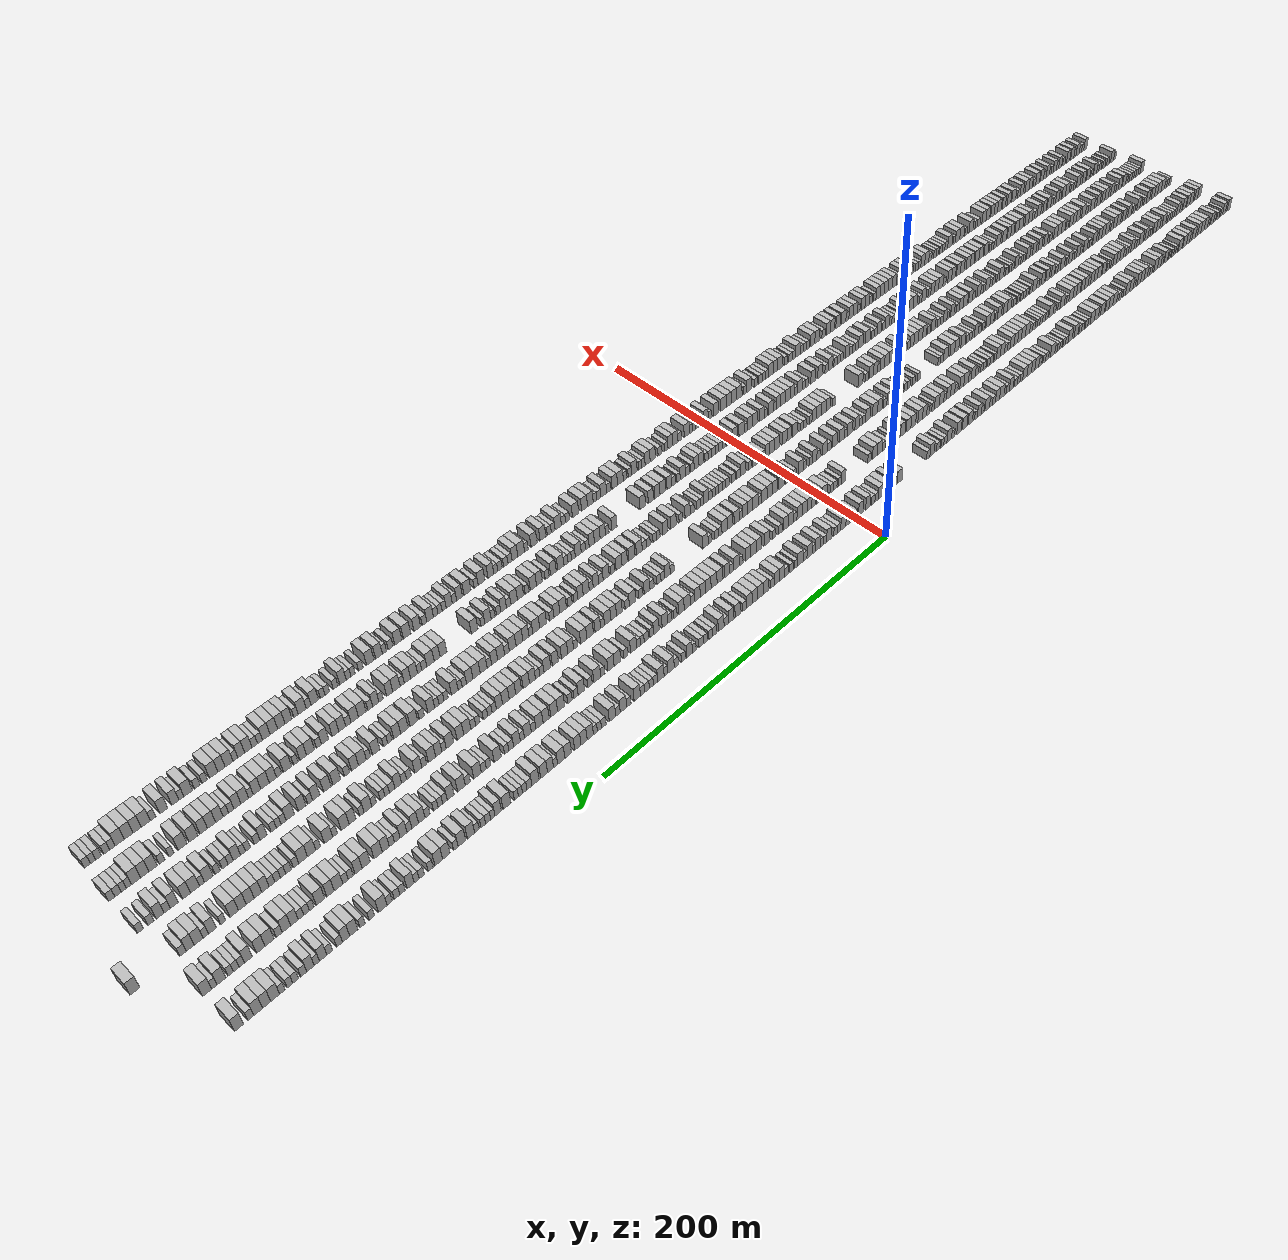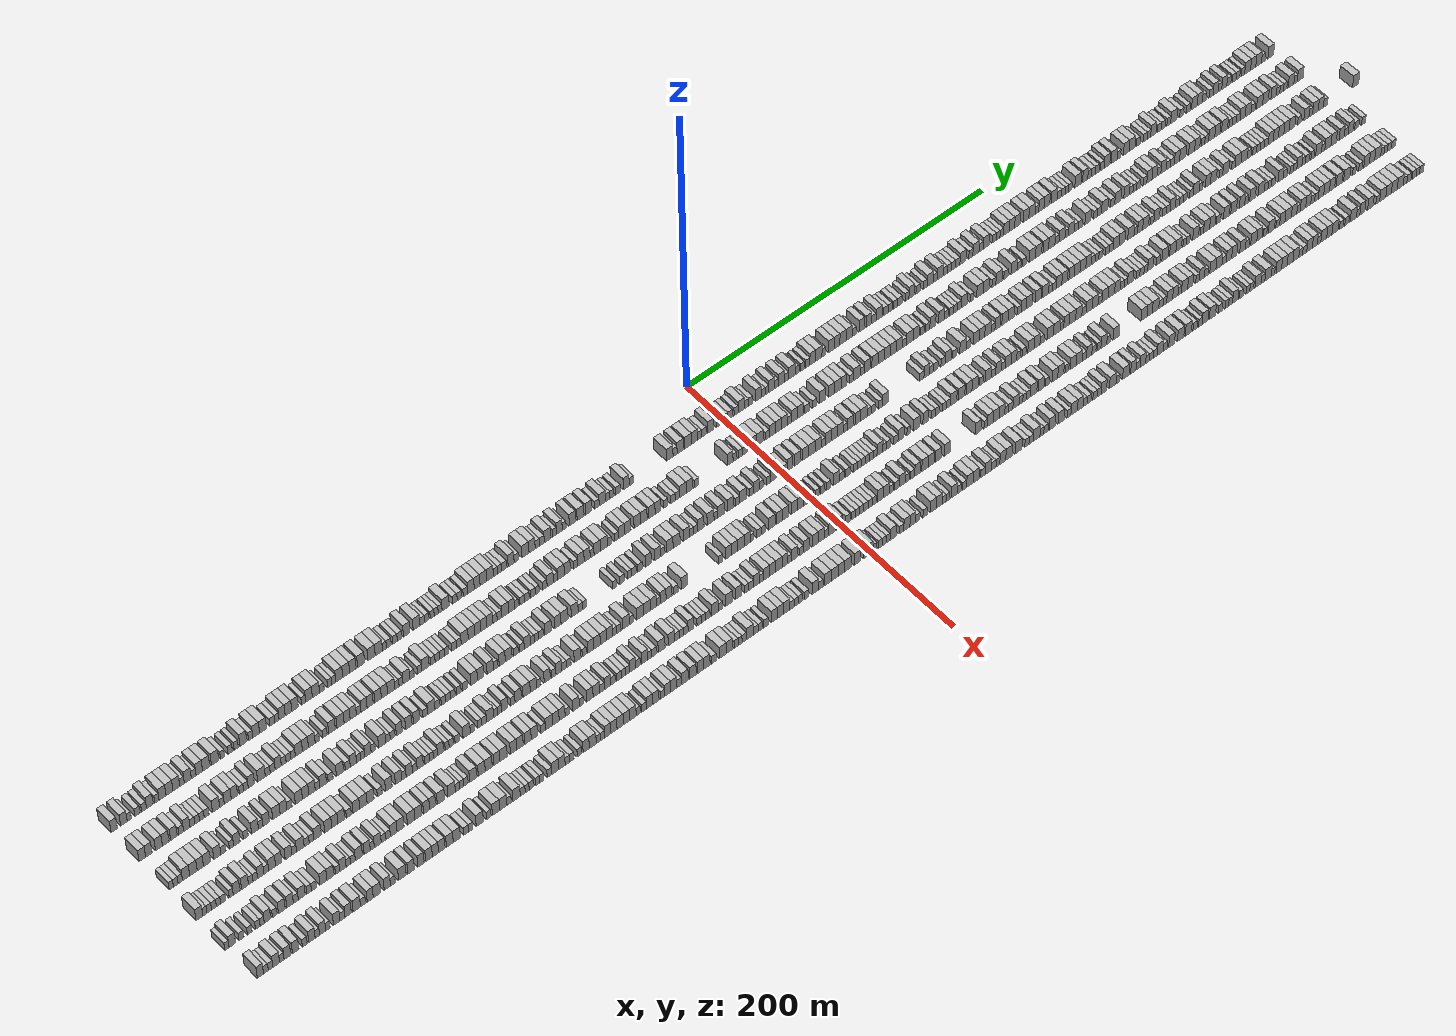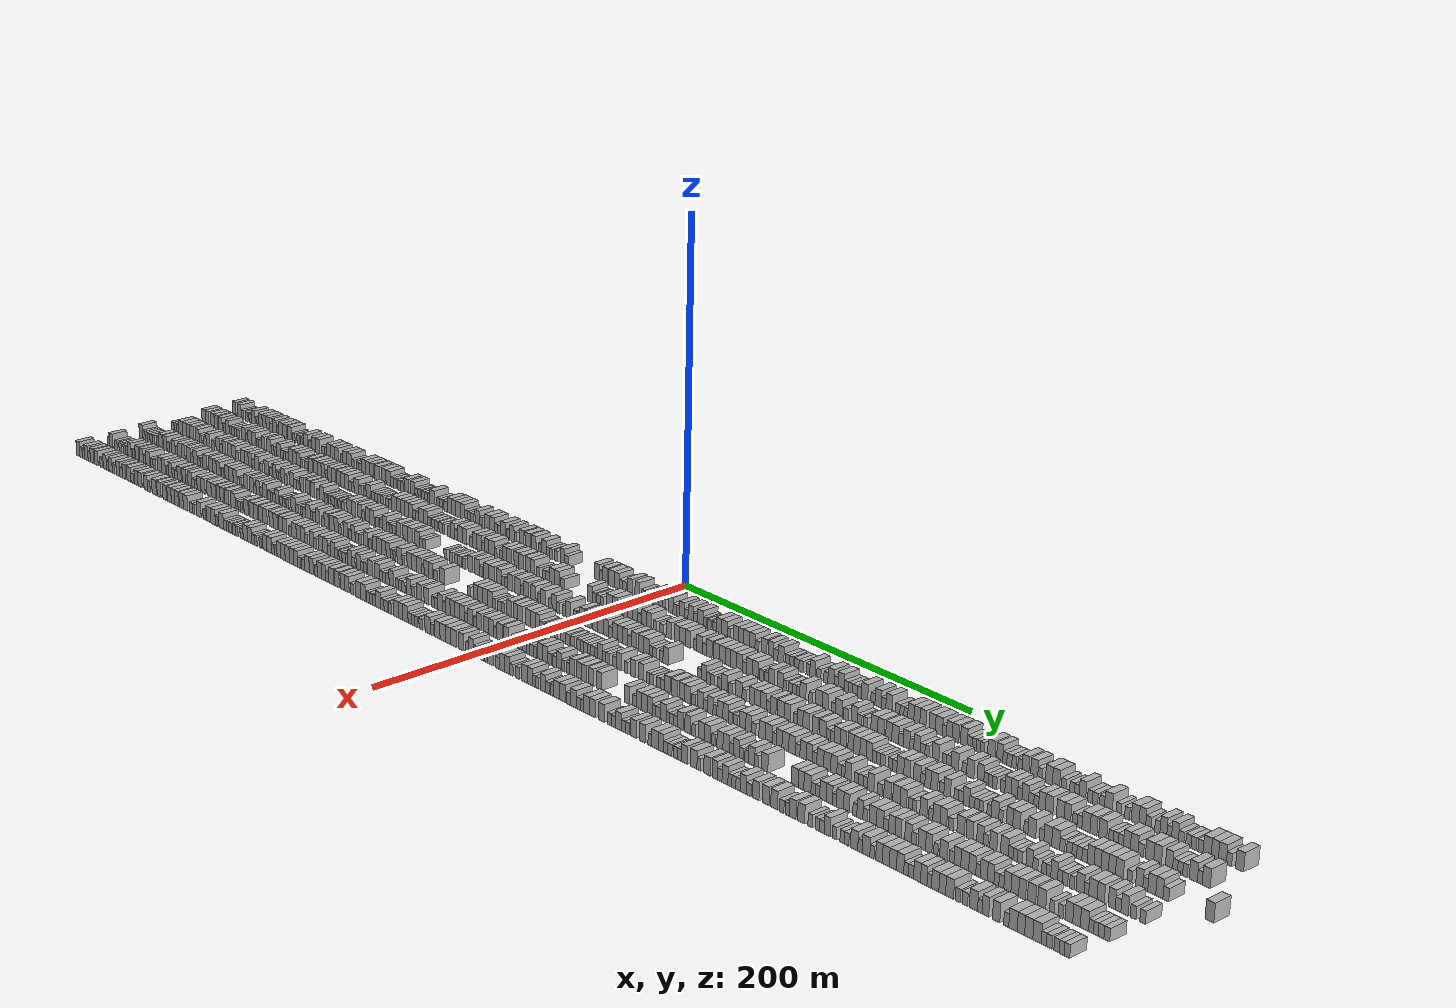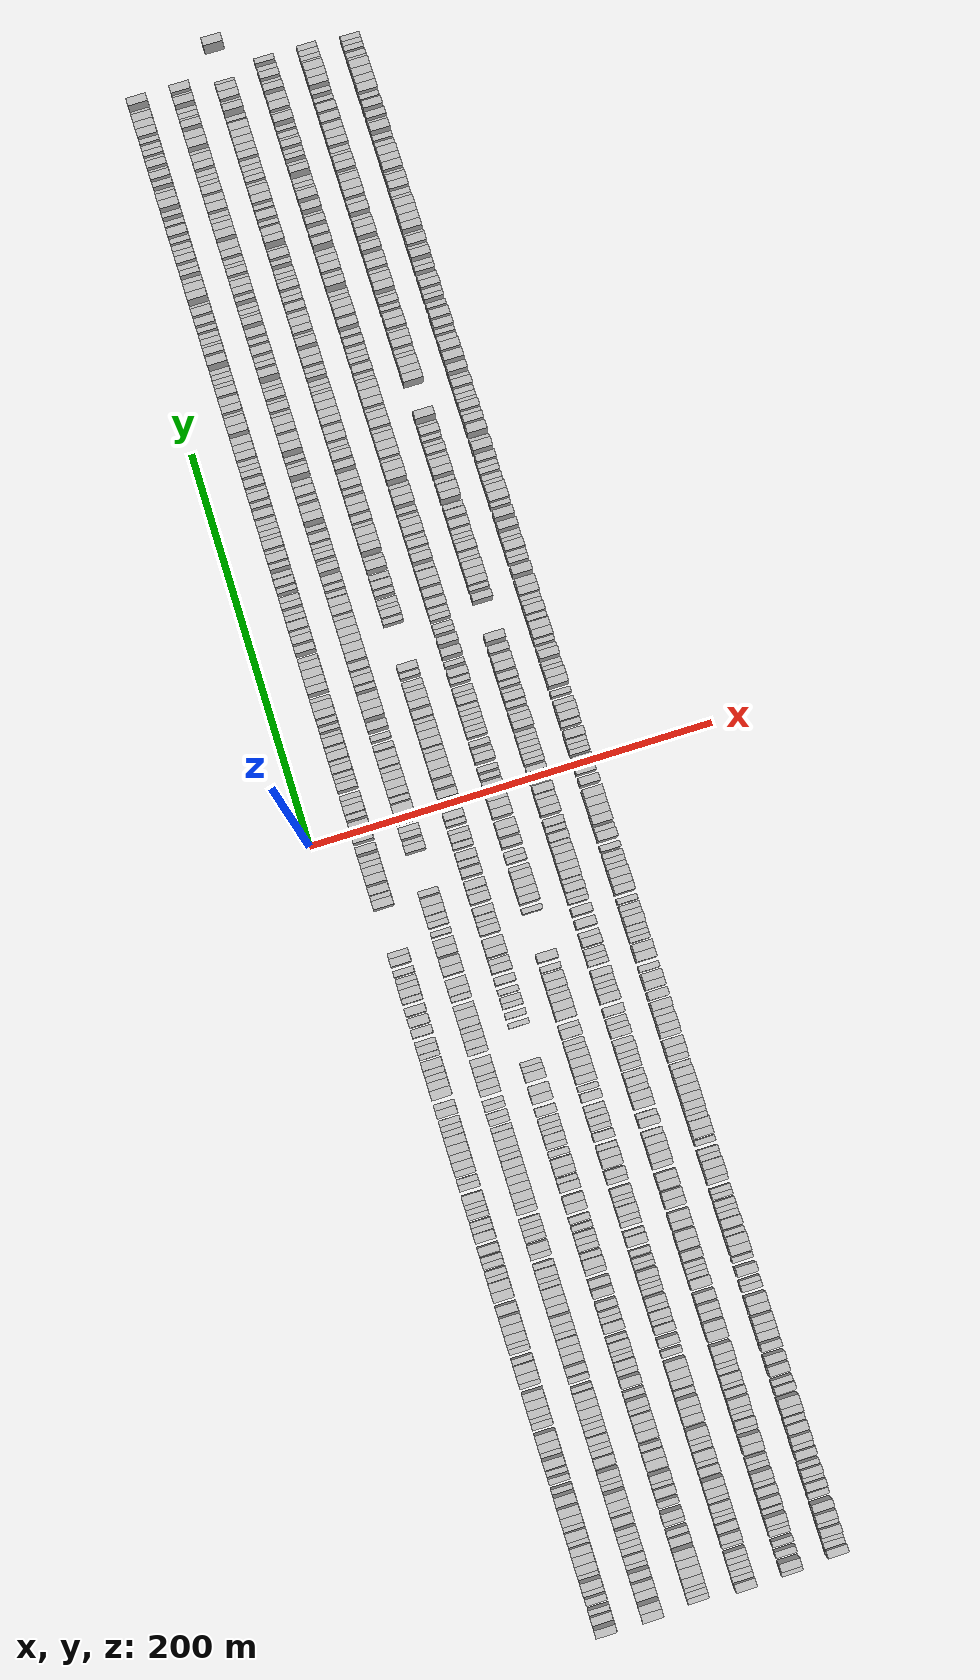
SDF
<sdf version="1.6">
 <world name="default">
  <scene>
   <sky><clouds><speed>12</speed></clouds></sky>
   <ambient>0.4 0.4 0.4 1</ambient>
   <background>0.7 0.7 0.7 1</background>
   <shadows>1</shadows>
  </scene>
  <gravity>0 0 -9.8066</gravity>
  <magnetic_field>6e-06 2.3e-05 -4.2e-05</magnetic_field>
  <physics default="0" name="default_physics" type="ode">
   <ode>
    <solver>
     <type>quick</type>
     <iters>10</iters>
     <sor>1.0</sor>
     <use_dynamic_moi_rescaling>0</use_dynamic_moi_rescaling>
    </solver>
    <constraints>
     <cfm>0</cfm>
     <erp>0.2</erp>
     <contact_max_correcting_vel>100</contact_max_correcting_vel>
     <contact_surface_layer>0.001</contact_surface_layer>
    </constraints>
   </ode>
   <max_step_size>0.004</max_step_size>
   <real_time_factor>1</real_time_factor>
   <real_time_update_rate>250</real_time_update_rate>
  </physics>
  <light name="sun" type="directional">
   <pose>0 0 10 0 0 0</pose>
   <diffuse>0.8 0.8 0.8 1</diffuse>
   <specular>0.2 0.2 0.2 1</specular>
   <attenuation>
    <range>1000</range>
    <constant>0.9</constant>
    <linear>0.01</linear>
    <quadratic>0.001</quadratic>
   </attenuation>
   <direction>-0.5 0.1 -0.9</direction>
  </light>
  <model name="building_1">
   <static>1</static>
   <pose>25.0000 -378.1661 0 0.000000 0.000000 0.000000</pose>
   <link name="link">
    <pose>0 0 4.50 0 0 0</pose>
    <collision name="collision"><geometry><box><size>10.0000 3.6678 9.0000</size></box></geometry></collision>
    <visual name="visual">
     <cast_shadows>0</cast_shadows>
     <geometry><box><size>10.0000 3.6678 9.0000</size></box></geometry>
     <material>
      <script>
       <uri>model://HANNAS_wall/materials/scripts</uri>
       <uri>model://HANNAS_wall/materials/textures</uri>
       <name>vrc/HANNAS_wall</name>
      </script>
     </material>
    </visual>
   </link>
  </model>
  <model name="building_2">
   <static>1</static>
   <pose>25.0000 -372.4223 0 0.000000 0.000000 0.000000</pose>
   <link name="link">
    <pose>0 0 4.50 0 0 0</pose>
    <collision name="collision"><geometry><box><size>10.0000 3.8199 9.0000</size></box></geometry></collision>
    <visual name="visual">
     <cast_shadows>0</cast_shadows>
     <geometry><box><size>10.0000 3.8199 9.0000</size></box></geometry>
     <material>
      <script>
       <uri>model://HANNAS_wall/materials/scripts</uri>
       <uri>model://HANNAS_wall/materials/textures</uri>
       <name>vrc/HANNAS_wall</name>
      </script>
     </material>
    </visual>
   </link>
  </model>
  <model name="building_3">
   <static>1</static>
   <pose>25.0000 -369.2865 0 0.000000 0.000000 0.000000</pose>
   <link name="link">
    <pose>0 0 3.00 0 0 0</pose>
    <collision name="collision"><geometry><box><size>10.0000 2.4517 6.0000</size></box></geometry></collision>
    <visual name="visual">
     <cast_shadows>0</cast_shadows>
     <geometry><box><size>10.0000 2.4517 6.0000</size></box></geometry>
     <material>
      <script>
       <uri>model://HANNAS_wall/materials/scripts</uri>
       <uri>model://HANNAS_wall/materials/textures</uri>
       <name>vrc/HANNAS_wall</name>
      </script>
     </material>
    </visual>
   </link>
  </model>
  <model name="building_4">
   <static>1</static>
   <pose>25.0000 -364.5643 0 0.000000 0.000000 0.000000</pose>
   <link name="link">
    <pose>0 0 3.00 0 0 0</pose>
    <collision name="collision"><geometry><box><size>10.0000 2.9926 6.0000</size></box></geometry></collision>
    <visual name="visual">
     <cast_shadows>0</cast_shadows>
     <geometry><box><size>10.0000 2.9926 6.0000</size></box></geometry>
     <material>
      <script>
       <uri>model://HANNAS_wall/materials/scripts</uri>
       <uri>model://HANNAS_wall/materials/textures</uri>
       <name>vrc/HANNAS_wall</name>
      </script>
     </material>
    </visual>
   </link>
  </model>
  <model name="building_5">
   <static>1</static>
   <pose>25.0000 -360.6418 0 0.000000 0.000000 0.000000</pose>
   <link name="link">
    <pose>0 0 3.00 0 0 0</pose>
    <collision name="collision"><geometry><box><size>10.0000 2.8523 6.0000</size></box></geometry></collision>
    <visual name="visual">
     <cast_shadows>0</cast_shadows>
     <geometry><box><size>10.0000 2.8523 6.0000</size></box></geometry>
     <material>
      <script>
       <uri>model://HANNAS_wall/materials/scripts</uri>
       <uri>model://HANNAS_wall/materials/textures</uri>
       <name>vrc/HANNAS_wall</name>
      </script>
     </material>
    </visual>
   </link>
  </model>
  <model name="building_6">
   <static>1</static>
   <pose>25.0000 -357.3003 0 0.000000 0.000000 0.000000</pose>
   <link name="link">
    <pose>0 0 4.50 0 0 0</pose>
    <collision name="collision"><geometry><box><size>10.0000 3.8306 9.0000</size></box></geometry></collision>
    <visual name="visual">
     <cast_shadows>0</cast_shadows>
     <geometry><box><size>10.0000 3.8306 9.0000</size></box></geometry>
     <material>
      <script>
       <uri>model://HANNAS_wall/materials/scripts</uri>
       <uri>model://HANNAS_wall/materials/textures</uri>
       <name>vrc/HANNAS_wall</name>
      </script>
     </material>
    </visual>
   </link>
  </model>
  <model name="building_7">
   <static>1</static>
   <pose>25.0000 -353.1122 0 0.000000 0.000000 0.000000</pose>
   <link name="link">
    <pose>0 0 3.00 0 0 0</pose>
    <collision name="collision"><geometry><box><size>10.0000 2.5456 6.0000</size></box></geometry></collision>
    <visual name="visual">
     <cast_shadows>0</cast_shadows>
     <geometry><box><size>10.0000 2.5456 6.0000</size></box></geometry>
     <material>
      <script>
       <uri>model://HANNAS_wall/materials/scripts</uri>
       <uri>model://HANNAS_wall/materials/textures</uri>
       <name>vrc/HANNAS_wall</name>
      </script>
     </material>
    </visual>
   </link>
  </model>
  <model name="building_8">
   <static>1</static>
   <pose>25.0000 -349.7991 0 0.000000 0.000000 0.000000</pose>
   <link name="link">
    <pose>0 0 4.50 0 0 0</pose>
    <collision name="collision"><geometry><box><size>10.0000 4.0807 9.0000</size></box></geometry></collision>
    <visual name="visual">
     <cast_shadows>0</cast_shadows>
     <geometry><box><size>10.0000 4.0807 9.0000</size></box></geometry>
     <material>
      <script>
       <uri>model://HANNAS_wall/materials/scripts</uri>
       <uri>model://HANNAS_wall/materials/textures</uri>
       <name>vrc/HANNAS_wall</name>
      </script>
     </material>
    </visual>
   </link>
  </model>
  <model name="building_9">
   <static>1</static>
   <pose>25.0000 -345.6903 0 0.000000 0.000000 0.000000</pose>
   <link name="link">
    <pose>0 0 4.50 0 0 0</pose>
    <collision name="collision"><geometry><box><size>10.0000 4.1368 9.0000</size></box></geometry></collision>
    <visual name="visual">
     <cast_shadows>0</cast_shadows>
     <geometry><box><size>10.0000 4.1368 9.0000</size></box></geometry>
     <material>
      <script>
       <uri>model://HANNAS_wall/materials/scripts</uri>
       <uri>model://HANNAS_wall/materials/textures</uri>
       <name>vrc/HANNAS_wall</name>
      </script>
     </material>
    </visual>
   </link>
  </model>
  <model name="building_10">
   <static>1</static>
   <pose>25.0000 -341.6438 0 0.000000 0.000000 0.000000</pose>
   <link name="link">
    <pose>0 0 4.50 0 0 0</pose>
    <collision name="collision"><geometry><box><size>10.0000 3.9563 9.0000</size></box></geometry></collision>
    <visual name="visual">
     <cast_shadows>0</cast_shadows>
     <geometry><box><size>10.0000 3.9563 9.0000</size></box></geometry>
     <material>
      <script>
       <uri>model://HANNAS_wall/materials/scripts</uri>
       <uri>model://HANNAS_wall/materials/textures</uri>
       <name>vrc/HANNAS_wall</name>
      </script>
     </material>
    </visual>
   </link>
  </model>
  <model name="building_11">
   <static>1</static>
   <pose>25.0000 -338.3065 0 0.000000 0.000000 0.000000</pose>
   <link name="link">
    <pose>0 0 3.00 0 0 0</pose>
    <collision name="collision"><geometry><box><size>10.0000 2.7184 6.0000</size></box></geometry></collision>
    <visual name="visual">
     <cast_shadows>0</cast_shadows>
     <geometry><box><size>10.0000 2.7184 6.0000</size></box></geometry>
     <material>
      <script>
       <uri>model://HANNAS_wall/materials/scripts</uri>
       <uri>model://HANNAS_wall/materials/textures</uri>
       <name>vrc/HANNAS_wall</name>
      </script>
     </material>
    </visual>
   </link>
  </model>
  <model name="building_12">
   <static>1</static>
   <pose>25.0000 -334.8588 0 0.000000 0.000000 0.000000</pose>
   <link name="link">
    <pose>0 0 4.50 0 0 0</pose>
    <collision name="collision"><geometry><box><size>10.0000 4.1769 9.0000</size></box></geometry></collision>
    <visual name="visual">
     <cast_shadows>0</cast_shadows>
     <geometry><box><size>10.0000 4.1769 9.0000</size></box></geometry>
     <material>
      <script>
       <uri>model://HANNAS_wall/materials/scripts</uri>
       <uri>model://HANNAS_wall/materials/textures</uri>
       <name>vrc/HANNAS_wall</name>
      </script>
     </material>
    </visual>
   </link>
  </model>
  <model name="building_13">
   <static>1</static>
   <pose>25.0000 -331.3985 0 0.000000 0.000000 0.000000</pose>
   <link name="link">
    <pose>0 0 3.00 0 0 0</pose>
    <collision name="collision"><geometry><box><size>10.0000 2.7438 6.0000</size></box></geometry></collision>
    <visual name="visual">
     <cast_shadows>0</cast_shadows>
     <geometry><box><size>10.0000 2.7438 6.0000</size></box></geometry>
     <material>
      <script>
       <uri>model://HANNAS_wall/materials/scripts</uri>
       <uri>model://HANNAS_wall/materials/textures</uri>
       <name>vrc/HANNAS_wall</name>
      </script>
     </material>
    </visual>
   </link>
  </model>
  <model name="building_14">
   <static>1</static>
   <pose>25.0000 -328.0920 0 0.000000 0.000000 0.000000</pose>
   <link name="link">
    <pose>0 0 4.50 0 0 0</pose>
    <collision name="collision"><geometry><box><size>10.0000 3.8692 9.0000</size></box></geometry></collision>
    <visual name="visual">
     <cast_shadows>0</cast_shadows>
     <geometry><box><size>10.0000 3.8692 9.0000</size></box></geometry>
     <material>
      <script>
       <uri>model://HANNAS_wall/materials/scripts</uri>
       <uri>model://HANNAS_wall/materials/textures</uri>
       <name>vrc/HANNAS_wall</name>
      </script>
     </material>
    </visual>
   </link>
  </model>
  <model name="building_15">
   <static>1</static>
   <pose>25.0000 -324.0392 0 0.000000 0.000000 0.000000</pose>
   <link name="link">
    <pose>0 0 4.50 0 0 0</pose>
    <collision name="collision"><geometry><box><size>10.0000 4.2364 9.0000</size></box></geometry></collision>
    <visual name="visual">
     <cast_shadows>0</cast_shadows>
     <geometry><box><size>10.0000 4.2364 9.0000</size></box></geometry>
     <material>
      <script>
       <uri>model://HANNAS_wall/materials/scripts</uri>
       <uri>model://HANNAS_wall/materials/textures</uri>
       <name>vrc/HANNAS_wall</name>
      </script>
     </material>
    </visual>
   </link>
  </model>
  <model name="building_16">
   <static>1</static>
   <pose>25.0000 -318.6943 0 0.000000 0.000000 0.000000</pose>
   <link name="link">
    <pose>0 0 4.50 0 0 0</pose>
    <collision name="collision"><geometry><box><size>10.0000 4.4535 9.0000</size></box></geometry></collision>
    <visual name="visual">
     <cast_shadows>0</cast_shadows>
     <geometry><box><size>10.0000 4.4535 9.0000</size></box></geometry>
     <material>
      <script>
       <uri>model://HANNAS_wall/materials/scripts</uri>
       <uri>model://HANNAS_wall/materials/textures</uri>
       <name>vrc/HANNAS_wall</name>
      </script>
     </material>
    </visual>
   </link>
  </model>
  <model name="building_17">
   <static>1</static>
   <pose>25.0000 -314.2670 0 0.000000 0.000000 0.000000</pose>
   <link name="link">
    <pose>0 0 3.00 0 0 0</pose>
    <collision name="collision"><geometry><box><size>10.0000 2.4010 6.0000</size></box></geometry></collision>
    <visual name="visual">
     <cast_shadows>0</cast_shadows>
     <geometry><box><size>10.0000 2.4010 6.0000</size></box></geometry>
     <material>
      <script>
       <uri>model://HANNAS_wall/materials/scripts</uri>
       <uri>model://HANNAS_wall/materials/textures</uri>
       <name>vrc/HANNAS_wall</name>
      </script>
     </material>
    </visual>
   </link>
  </model>
  <model name="building_18">
   <static>1</static>
   <pose>25.0000 -309.7268 0 0.000000 0.000000 0.000000</pose>
   <link name="link">
    <pose>0 0 3.00 0 0 0</pose>
    <collision name="collision"><geometry><box><size>10.0000 2.6794 6.0000</size></box></geometry></collision>
    <visual name="visual">
     <cast_shadows>0</cast_shadows>
     <geometry><box><size>10.0000 2.6794 6.0000</size></box></geometry>
     <material>
      <script>
       <uri>model://HANNAS_wall/materials/scripts</uri>
       <uri>model://HANNAS_wall/materials/textures</uri>
       <name>vrc/HANNAS_wall</name>
      </script>
     </material>
    </visual>
   </link>
  </model>
  <model name="building_19">
   <static>1</static>
   <pose>25.0000 -306.1387 0 0.000000 0.000000 0.000000</pose>
   <link name="link">
    <pose>0 0 3.00 0 0 0</pose>
    <collision name="collision"><geometry><box><size>10.0000 2.4970 6.0000</size></box></geometry></collision>
    <visual name="visual">
     <cast_shadows>0</cast_shadows>
     <geometry><box><size>10.0000 2.4970 6.0000</size></box></geometry>
     <material>
      <script>
       <uri>model://HANNAS_wall/materials/scripts</uri>
       <uri>model://HANNAS_wall/materials/textures</uri>
       <name>vrc/HANNAS_wall</name>
      </script>
     </material>
    </visual>
   </link>
  </model>
  <model name="building_20">
   <static>1</static>
   <pose>25.0000 -301.8421 0 0.000000 0.000000 0.000000</pose>
   <link name="link">
    <pose>0 0 4.50 0 0 0</pose>
    <collision name="collision"><geometry><box><size>10.0000 4.0961 9.0000</size></box></geometry></collision>
    <visual name="visual">
     <cast_shadows>0</cast_shadows>
     <geometry><box><size>10.0000 4.0961 9.0000</size></box></geometry>
     <material>
      <script>
       <uri>model://HANNAS_wall/materials/scripts</uri>
       <uri>model://HANNAS_wall/materials/textures</uri>
       <name>vrc/HANNAS_wall</name>
      </script>
     </material>
    </visual>
   </link>
  </model>
  <model name="building_21">
   <static>1</static>
   <pose>25.0000 -297.4829 0 0.000000 0.000000 0.000000</pose>
   <link name="link">
    <pose>0 0 3.00 0 0 0</pose>
    <collision name="collision"><geometry><box><size>10.0000 2.6222 6.0000</size></box></geometry></collision>
    <visual name="visual">
     <cast_shadows>0</cast_shadows>
     <geometry><box><size>10.0000 2.6222 6.0000</size></box></geometry>
     <material>
      <script>
       <uri>model://HANNAS_wall/materials/scripts</uri>
       <uri>model://HANNAS_wall/materials/textures</uri>
       <name>vrc/HANNAS_wall</name>
      </script>
     </material>
    </visual>
   </link>
  </model>
  <model name="building_22">
   <static>1</static>
   <pose>25.0000 -294.1592 0 0.000000 0.000000 0.000000</pose>
   <link name="link">
    <pose>0 0 4.50 0 0 0</pose>
    <collision name="collision"><geometry><box><size>10.0000 4.0253 9.0000</size></box></geometry></collision>
    <visual name="visual">
     <cast_shadows>0</cast_shadows>
     <geometry><box><size>10.0000 4.0253 9.0000</size></box></geometry>
     <material>
      <script>
       <uri>model://HANNAS_wall/materials/scripts</uri>
       <uri>model://HANNAS_wall/materials/textures</uri>
       <name>vrc/HANNAS_wall</name>
      </script>
     </material>
    </visual>
   </link>
  </model>
  <model name="building_23">
   <static>1</static>
   <pose>25.0000 -290.0691 0 0.000000 0.000000 0.000000</pose>
   <link name="link">
    <pose>0 0 4.50 0 0 0</pose>
    <collision name="collision"><geometry><box><size>10.0000 4.1551 9.0000</size></box></geometry></collision>
    <visual name="visual">
     <cast_shadows>0</cast_shadows>
     <geometry><box><size>10.0000 4.1551 9.0000</size></box></geometry>
     <material>
      <script>
       <uri>model://HANNAS_wall/materials/scripts</uri>
       <uri>model://HANNAS_wall/materials/textures</uri>
       <name>vrc/HANNAS_wall</name>
      </script>
     </material>
    </visual>
   </link>
  </model>
  <model name="building_24">
   <static>1</static>
   <pose>25.0000 -284.5112 0 0.000000 0.000000 0.000000</pose>
   <link name="link">
    <pose>0 0 3.00 0 0 0</pose>
    <collision name="collision"><geometry><box><size>10.0000 2.9608 6.0000</size></box></geometry></collision>
    <visual name="visual">
     <cast_shadows>0</cast_shadows>
     <geometry><box><size>10.0000 2.9608 6.0000</size></box></geometry>
     <material>
      <script>
       <uri>model://HANNAS_wall/materials/scripts</uri>
       <uri>model://HANNAS_wall/materials/textures</uri>
       <name>vrc/HANNAS_wall</name>
      </script>
     </material>
    </visual>
   </link>
  </model>
  <model name="building_25">
   <static>1</static>
   <pose>25.0000 -281.7417 0 0.000000 0.000000 0.000000</pose>
   <link name="link">
    <pose>0 0 3.00 0 0 0</pose>
    <collision name="collision"><geometry><box><size>10.0000 2.5782 6.0000</size></box></geometry></collision>
    <visual name="visual">
     <cast_shadows>0</cast_shadows>
     <geometry><box><size>10.0000 2.5782 6.0000</size></box></geometry>
     <material>
      <script>
       <uri>model://HANNAS_wall/materials/scripts</uri>
       <uri>model://HANNAS_wall/materials/textures</uri>
       <name>vrc/HANNAS_wall</name>
      </script>
     </material>
    </visual>
   </link>
  </model>
  <model name="building_26">
   <static>1</static>
   <pose>25.0000 -278.6210 0 0.000000 0.000000 0.000000</pose>
   <link name="link">
    <pose>0 0 4.50 0 0 0</pose>
    <collision name="collision"><geometry><box><size>10.0000 3.6632 9.0000</size></box></geometry></collision>
    <visual name="visual">
     <cast_shadows>0</cast_shadows>
     <geometry><box><size>10.0000 3.6632 9.0000</size></box></geometry>
     <material>
      <script>
       <uri>model://HANNAS_wall/materials/scripts</uri>
       <uri>model://HANNAS_wall/materials/textures</uri>
       <name>vrc/HANNAS_wall</name>
      </script>
     </material>
    </visual>
   </link>
  </model>
  <model name="building_27">
   <static>1</static>
   <pose>25.0000 -274.7583 0 0.000000 0.000000 0.000000</pose>
   <link name="link">
    <pose>0 0 4.50 0 0 0</pose>
    <collision name="collision"><geometry><box><size>10.0000 4.0623 9.0000</size></box></geometry></collision>
    <visual name="visual">
     <cast_shadows>0</cast_shadows>
     <geometry><box><size>10.0000 4.0623 9.0000</size></box></geometry>
     <material>
      <script>
       <uri>model://HANNAS_wall/materials/scripts</uri>
       <uri>model://HANNAS_wall/materials/textures</uri>
       <name>vrc/HANNAS_wall</name>
      </script>
     </material>
    </visual>
   </link>
  </model>
  <model name="building_28">
   <static>1</static>
   <pose>25.0000 -270.8224 0 0.000000 0.000000 0.000000</pose>
   <link name="link">
    <pose>0 0 4.50 0 0 0</pose>
    <collision name="collision"><geometry><box><size>10.0000 3.8095 9.0000</size></box></geometry></collision>
    <visual name="visual">
     <cast_shadows>0</cast_shadows>
     <geometry><box><size>10.0000 3.8095 9.0000</size></box></geometry>
     <material>
      <script>
       <uri>model://HANNAS_wall/materials/scripts</uri>
       <uri>model://HANNAS_wall/materials/textures</uri>
       <name>vrc/HANNAS_wall</name>
      </script>
     </material>
    </visual>
   </link>
  </model>
  <model name="building_29">
   <static>1</static>
   <pose>25.0000 -265.6173 0 0.000000 0.000000 0.000000</pose>
   <link name="link">
    <pose>0 0 3.00 0 0 0</pose>
    <collision name="collision"><geometry><box><size>10.0000 2.6008 6.0000</size></box></geometry></collision>
    <visual name="visual">
     <cast_shadows>0</cast_shadows>
     <geometry><box><size>10.0000 2.6008 6.0000</size></box></geometry>
     <material>
      <script>
       <uri>model://HANNAS_wall/materials/scripts</uri>
       <uri>model://HANNAS_wall/materials/textures</uri>
       <name>vrc/HANNAS_wall</name>
      </script>
     </material>
    </visual>
   </link>
  </model>
  <model name="building_30">
   <static>1</static>
   <pose>25.0000 -262.3376 0 0.000000 0.000000 0.000000</pose>
   <link name="link">
    <pose>0 0 4.50 0 0 0</pose>
    <collision name="collision"><geometry><box><size>10.0000 3.9587 9.0000</size></box></geometry></collision>
    <visual name="visual">
     <cast_shadows>0</cast_shadows>
     <geometry><box><size>10.0000 3.9587 9.0000</size></box></geometry>
     <material>
      <script>
       <uri>model://HANNAS_wall/materials/scripts</uri>
       <uri>model://HANNAS_wall/materials/textures</uri>
       <name>vrc/HANNAS_wall</name>
      </script>
     </material>
    </visual>
   </link>
  </model>
  <model name="building_31">
   <static>1</static>
   <pose>25.0000 -258.1573 0 0.000000 0.000000 0.000000</pose>
   <link name="link">
    <pose>0 0 4.50 0 0 0</pose>
    <collision name="collision"><geometry><box><size>10.0000 4.4019 9.0000</size></box></geometry></collision>
    <visual name="visual">
     <cast_shadows>0</cast_shadows>
     <geometry><box><size>10.0000 4.4019 9.0000</size></box></geometry>
     <material>
      <script>
       <uri>model://HANNAS_wall/materials/scripts</uri>
       <uri>model://HANNAS_wall/materials/textures</uri>
       <name>vrc/HANNAS_wall</name>
      </script>
     </material>
    </visual>
   </link>
  </model>
  <model name="building_32">
   <static>1</static>
   <pose>25.0000 -254.5418 0 0.000000 0.000000 0.000000</pose>
   <link name="link">
    <pose>0 0 3.00 0 0 0</pose>
    <collision name="collision"><geometry><box><size>10.0000 2.8291 6.0000</size></box></geometry></collision>
    <visual name="visual">
     <cast_shadows>0</cast_shadows>
     <geometry><box><size>10.0000 2.8291 6.0000</size></box></geometry>
     <material>
      <script>
       <uri>model://HANNAS_wall/materials/scripts</uri>
       <uri>model://HANNAS_wall/materials/textures</uri>
       <name>vrc/HANNAS_wall</name>
      </script>
     </material>
    </visual>
   </link>
  </model>
  <model name="building_33">
   <static>1</static>
   <pose>25.0000 -249.8364 0 0.000000 0.000000 0.000000</pose>
   <link name="link">
    <pose>0 0 3.00 0 0 0</pose>
    <collision name="collision"><geometry><box><size>10.0000 2.5818 6.0000</size></box></geometry></collision>
    <visual name="visual">
     <cast_shadows>0</cast_shadows>
     <geometry><box><size>10.0000 2.5818 6.0000</size></box></geometry>
     <material>
      <script>
       <uri>model://HANNAS_wall/materials/scripts</uri>
       <uri>model://HANNAS_wall/materials/textures</uri>
       <name>vrc/HANNAS_wall</name>
      </script>
     </material>
    </visual>
   </link>
  </model>
  <model name="building_34">
   <static>1</static>
   <pose>25.0000 -247.3250 0 0.000000 0.000000 0.000000</pose>
   <link name="link">
    <pose>0 0 3.00 0 0 0</pose>
    <collision name="collision"><geometry><box><size>10.0000 2.4410 6.0000</size></box></geometry></collision>
    <visual name="visual">
     <cast_shadows>0</cast_shadows>
     <geometry><box><size>10.0000 2.4410 6.0000</size></box></geometry>
     <material>
      <script>
       <uri>model://HANNAS_wall/materials/scripts</uri>
       <uri>model://HANNAS_wall/materials/textures</uri>
       <name>vrc/HANNAS_wall</name>
      </script>
     </material>
    </visual>
   </link>
  </model>
  <model name="building_35">
   <static>1</static>
   <pose>25.0000 -244.0045 0 0.000000 0.000000 0.000000</pose>
   <link name="link">
    <pose>0 0 4.50 0 0 0</pose>
    <collision name="collision"><geometry><box><size>10.0000 4.1999 9.0000</size></box></geometry></collision>
    <visual name="visual">
     <cast_shadows>0</cast_shadows>
     <geometry><box><size>10.0000 4.1999 9.0000</size></box></geometry>
     <material>
      <script>
       <uri>model://HANNAS_wall/materials/scripts</uri>
       <uri>model://HANNAS_wall/materials/textures</uri>
       <name>vrc/HANNAS_wall</name>
      </script>
     </material>
    </visual>
   </link>
  </model>
  <model name="building_36">
   <static>1</static>
   <pose>25.0000 -239.8030 0 0.000000 0.000000 0.000000</pose>
   <link name="link">
    <pose>0 0 4.50 0 0 0</pose>
    <collision name="collision"><geometry><box><size>10.0000 4.2031 9.0000</size></box></geometry></collision>
    <visual name="visual">
     <cast_shadows>0</cast_shadows>
     <geometry><box><size>10.0000 4.2031 9.0000</size></box></geometry>
     <material>
      <script>
       <uri>model://HANNAS_wall/materials/scripts</uri>
       <uri>model://HANNAS_wall/materials/textures</uri>
       <name>vrc/HANNAS_wall</name>
      </script>
     </material>
    </visual>
   </link>
  </model>
  <model name="building_37">
   <static>1</static>
   <pose>25.0000 -235.7742 0 0.000000 0.000000 0.000000</pose>
   <link name="link">
    <pose>0 0 4.50 0 0 0</pose>
    <collision name="collision"><geometry><box><size>10.0000 3.8545 9.0000</size></box></geometry></collision>
    <visual name="visual">
     <cast_shadows>0</cast_shadows>
     <geometry><box><size>10.0000 3.8545 9.0000</size></box></geometry>
     <material>
      <script>
       <uri>model://HANNAS_wall/materials/scripts</uri>
       <uri>model://HANNAS_wall/materials/textures</uri>
       <name>vrc/HANNAS_wall</name>
      </script>
     </material>
    </visual>
   </link>
  </model>
  <model name="building_38">
   <static>1</static>
   <pose>25.0000 -230.6868 0 0.000000 0.000000 0.000000</pose>
   <link name="link">
    <pose>0 0 4.50 0 0 0</pose>
    <collision name="collision"><geometry><box><size>10.0000 4.3202 9.0000</size></box></geometry></collision>
    <visual name="visual">
     <cast_shadows>0</cast_shadows>
     <geometry><box><size>10.0000 4.3202 9.0000</size></box></geometry>
     <material>
      <script>
       <uri>model://HANNAS_wall/materials/scripts</uri>
       <uri>model://HANNAS_wall/materials/textures</uri>
       <name>vrc/HANNAS_wall</name>
      </script>
     </material>
    </visual>
   </link>
  </model>
  <model name="building_39">
   <static>1</static>
   <pose>25.0000 -224.2855 0 0.000000 0.000000 0.000000</pose>
   <link name="link">
    <pose>0 0 4.50 0 0 0</pose>
    <collision name="collision"><geometry><box><size>10.0000 4.4824 9.0000</size></box></geometry></collision>
    <visual name="visual">
     <cast_shadows>0</cast_shadows>
     <geometry><box><size>10.0000 4.4824 9.0000</size></box></geometry>
     <material>
      <script>
       <uri>model://HANNAS_wall/materials/scripts</uri>
       <uri>model://HANNAS_wall/materials/textures</uri>
       <name>vrc/HANNAS_wall</name>
      </script>
     </material>
    </visual>
   </link>
  </model>
  <model name="building_40">
   <static>1</static>
   <pose>25.0000 -219.8052 0 0.000000 0.000000 0.000000</pose>
   <link name="link">
    <pose>0 0 4.50 0 0 0</pose>
    <collision name="collision"><geometry><box><size>10.0000 4.4782 9.0000</size></box></geometry></collision>
    <visual name="visual">
     <cast_shadows>0</cast_shadows>
     <geometry><box><size>10.0000 4.4782 9.0000</size></box></geometry>
     <material>
      <script>
       <uri>model://HANNAS_wall/materials/scripts</uri>
       <uri>model://HANNAS_wall/materials/textures</uri>
       <name>vrc/HANNAS_wall</name>
      </script>
     </material>
    </visual>
   </link>
  </model>
  <model name="building_41">
   <static>1</static>
   <pose>25.0000 -216.3592 0 0.000000 0.000000 0.000000</pose>
   <link name="link">
    <pose>0 0 3.00 0 0 0</pose>
    <collision name="collision"><geometry><box><size>10.0000 2.4140 6.0000</size></box></geometry></collision>
    <visual name="visual">
     <cast_shadows>0</cast_shadows>
     <geometry><box><size>10.0000 2.4140 6.0000</size></box></geometry>
     <material>
      <script>
       <uri>model://HANNAS_wall/materials/scripts</uri>
       <uri>model://HANNAS_wall/materials/textures</uri>
       <name>vrc/HANNAS_wall</name>
      </script>
     </material>
    </visual>
   </link>
  </model>
  <model name="building_42">
   <static>1</static>
   <pose>25.0000 -213.6833 0 0.000000 0.000000 0.000000</pose>
   <link name="link">
    <pose>0 0 3.00 0 0 0</pose>
    <collision name="collision"><geometry><box><size>10.0000 2.9378 6.0000</size></box></geometry></collision>
    <visual name="visual">
     <cast_shadows>0</cast_shadows>
     <geometry><box><size>10.0000 2.9378 6.0000</size></box></geometry>
     <material>
      <script>
       <uri>model://HANNAS_wall/materials/scripts</uri>
       <uri>model://HANNAS_wall/materials/textures</uri>
       <name>vrc/HANNAS_wall</name>
      </script>
     </material>
    </visual>
   </link>
  </model>
  <model name="building_43">
   <static>1</static>
   <pose>25.0000 -209.8411 0 0.000000 0.000000 0.000000</pose>
   <link name="link">
    <pose>0 0 3.00 0 0 0</pose>
    <collision name="collision"><geometry><box><size>10.0000 2.7466 6.0000</size></box></geometry></collision>
    <visual name="visual">
     <cast_shadows>0</cast_shadows>
     <geometry><box><size>10.0000 2.7466 6.0000</size></box></geometry>
     <material>
      <script>
       <uri>model://HANNAS_wall/materials/scripts</uri>
       <uri>model://HANNAS_wall/materials/textures</uri>
       <name>vrc/HANNAS_wall</name>
      </script>
     </material>
    </visual>
   </link>
  </model>
  <model name="building_44">
   <static>1</static>
   <pose>25.0000 -207.0840 0 0.000000 0.000000 0.000000</pose>
   <link name="link">
    <pose>0 0 3.00 0 0 0</pose>
    <collision name="collision"><geometry><box><size>10.0000 2.7675 6.0000</size></box></geometry></collision>
    <visual name="visual">
     <cast_shadows>0</cast_shadows>
     <geometry><box><size>10.0000 2.7675 6.0000</size></box></geometry>
     <material>
      <script>
       <uri>model://HANNAS_wall/materials/scripts</uri>
       <uri>model://HANNAS_wall/materials/textures</uri>
       <name>vrc/HANNAS_wall</name>
      </script>
     </material>
    </visual>
   </link>
  </model>
  <model name="building_45">
   <static>1</static>
   <pose>25.0000 -202.7225 0 0.000000 0.000000 0.000000</pose>
   <link name="link">
    <pose>0 0 4.50 0 0 0</pose>
    <collision name="collision"><geometry><box><size>10.0000 3.9555 9.0000</size></box></geometry></collision>
    <visual name="visual">
     <cast_shadows>0</cast_shadows>
     <geometry><box><size>10.0000 3.9555 9.0000</size></box></geometry>
     <material>
      <script>
       <uri>model://HANNAS_wall/materials/scripts</uri>
       <uri>model://HANNAS_wall/materials/textures</uri>
       <name>vrc/HANNAS_wall</name>
      </script>
     </material>
    </visual>
   </link>
  </model>
  <model name="building_46">
   <static>1</static>
   <pose>25.0000 -196.6248 0 0.000000 0.000000 0.000000</pose>
   <link name="link">
    <pose>0 0 4.50 0 0 0</pose>
    <collision name="collision"><geometry><box><size>10.0000 4.2398 9.0000</size></box></geometry></collision>
    <visual name="visual">
     <cast_shadows>0</cast_shadows>
     <geometry><box><size>10.0000 4.2398 9.0000</size></box></geometry>
     <material>
      <script>
       <uri>model://HANNAS_wall/materials/scripts</uri>
       <uri>model://HANNAS_wall/materials/textures</uri>
       <name>vrc/HANNAS_wall</name>
      </script>
     </material>
    </visual>
   </link>
  </model>
  <model name="building_47">
   <static>1</static>
   <pose>25.0000 -193.0950 0 0.000000 0.000000 0.000000</pose>
   <link name="link">
    <pose>0 0 3.00 0 0 0</pose>
    <collision name="collision"><geometry><box><size>10.0000 2.8199 6.0000</size></box></geometry></collision>
    <visual name="visual">
     <cast_shadows>0</cast_shadows>
     <geometry><box><size>10.0000 2.8199 6.0000</size></box></geometry>
     <material>
      <script>
       <uri>model://HANNAS_wall/materials/scripts</uri>
       <uri>model://HANNAS_wall/materials/textures</uri>
       <name>vrc/HANNAS_wall</name>
      </script>
     </material>
    </visual>
   </link>
  </model>
  <model name="building_48">
   <static>1</static>
   <pose>25.0000 -190.4062 0 0.000000 0.000000 0.000000</pose>
   <link name="link">
    <pose>0 0 3.00 0 0 0</pose>
    <collision name="collision"><geometry><box><size>10.0000 2.5578 6.0000</size></box></geometry></collision>
    <visual name="visual">
     <cast_shadows>0</cast_shadows>
     <geometry><box><size>10.0000 2.5578 6.0000</size></box></geometry>
     <material>
      <script>
       <uri>model://HANNAS_wall/materials/scripts</uri>
       <uri>model://HANNAS_wall/materials/textures</uri>
       <name>vrc/HANNAS_wall</name>
      </script>
     </material>
    </visual>
   </link>
  </model>
  <model name="building_49">
   <static>1</static>
   <pose>25.0000 -186.9182 0 0.000000 0.000000 0.000000</pose>
   <link name="link">
    <pose>0 0 3.00 0 0 0</pose>
    <collision name="collision"><geometry><box><size>10.0000 2.4184 6.0000</size></box></geometry></collision>
    <visual name="visual">
     <cast_shadows>0</cast_shadows>
     <geometry><box><size>10.0000 2.4184 6.0000</size></box></geometry>
     <material>
      <script>
       <uri>model://HANNAS_wall/materials/scripts</uri>
       <uri>model://HANNAS_wall/materials/textures</uri>
       <name>vrc/HANNAS_wall</name>
      </script>
     </material>
    </visual>
   </link>
  </model>
  <model name="building_50">
   <static>1</static>
   <pose>25.0000 -184.4564 0 0.000000 0.000000 0.000000</pose>
   <link name="link">
    <pose>0 0 3.00 0 0 0</pose>
    <collision name="collision"><geometry><box><size>10.0000 2.5052 6.0000</size></box></geometry></collision>
    <visual name="visual">
     <cast_shadows>0</cast_shadows>
     <geometry><box><size>10.0000 2.5052 6.0000</size></box></geometry>
     <material>
      <script>
       <uri>model://HANNAS_wall/materials/scripts</uri>
       <uri>model://HANNAS_wall/materials/textures</uri>
       <name>vrc/HANNAS_wall</name>
      </script>
     </material>
    </visual>
   </link>
  </model>
  <model name="building_51">
   <static>1</static>
   <pose>25.0000 -181.9960 0 0.000000 0.000000 0.000000</pose>
   <link name="link">
    <pose>0 0 3.00 0 0 0</pose>
    <collision name="collision"><geometry><box><size>10.0000 2.4155 6.0000</size></box></geometry></collision>
    <visual name="visual">
     <cast_shadows>0</cast_shadows>
     <geometry><box><size>10.0000 2.4155 6.0000</size></box></geometry>
     <material>
      <script>
       <uri>model://HANNAS_wall/materials/scripts</uri>
       <uri>model://HANNAS_wall/materials/textures</uri>
       <name>vrc/HANNAS_wall</name>
      </script>
     </material>
    </visual>
   </link>
  </model>
  <model name="building_52">
   <static>1</static>
   <pose>25.0000 -178.5819 0 0.000000 0.000000 0.000000</pose>
   <link name="link">
    <pose>0 0 4.50 0 0 0</pose>
    <collision name="collision"><geometry><box><size>10.0000 4.4126 9.0000</size></box></geometry></collision>
    <visual name="visual">
     <cast_shadows>0</cast_shadows>
     <geometry><box><size>10.0000 4.4126 9.0000</size></box></geometry>
     <material>
      <script>
       <uri>model://HANNAS_wall/materials/scripts</uri>
       <uri>model://HANNAS_wall/materials/textures</uri>
       <name>vrc/HANNAS_wall</name>
      </script>
     </material>
    </visual>
   </link>
  </model>
  <model name="building_53">
   <static>1</static>
   <pose>25.0000 -172.8973 0 0.000000 0.000000 0.000000</pose>
   <link name="link">
    <pose>0 0 3.00 0 0 0</pose>
    <collision name="collision"><geometry><box><size>10.0000 2.9566 6.0000</size></box></geometry></collision>
    <visual name="visual">
     <cast_shadows>0</cast_shadows>
     <geometry><box><size>10.0000 2.9566 6.0000</size></box></geometry>
     <material>
      <script>
       <uri>model://HANNAS_wall/materials/scripts</uri>
       <uri>model://HANNAS_wall/materials/textures</uri>
       <name>vrc/HANNAS_wall</name>
      </script>
     </material>
    </visual>
   </link>
  </model>
  <model name="building_54">
   <static>1</static>
   <pose>25.0000 -170.0509 0 0.000000 0.000000 0.000000</pose>
   <link name="link">
    <pose>0 0 3.00 0 0 0</pose>
    <collision name="collision"><geometry><box><size>10.0000 2.7363 6.0000</size></box></geometry></collision>
    <visual name="visual">
     <cast_shadows>0</cast_shadows>
     <geometry><box><size>10.0000 2.7363 6.0000</size></box></geometry>
     <material>
      <script>
       <uri>model://HANNAS_wall/materials/scripts</uri>
       <uri>model://HANNAS_wall/materials/textures</uri>
       <name>vrc/HANNAS_wall</name>
      </script>
     </material>
    </visual>
   </link>
  </model>
  <model name="building_55">
   <static>1</static>
   <pose>25.0000 -166.2082 0 0.000000 0.000000 0.000000</pose>
   <link name="link">
    <pose>0 0 3.00 0 0 0</pose>
    <collision name="collision"><geometry><box><size>10.0000 2.9493 6.0000</size></box></geometry></collision>
    <visual name="visual">
     <cast_shadows>0</cast_shadows>
     <geometry><box><size>10.0000 2.9493 6.0000</size></box></geometry>
     <material>
      <script>
       <uri>model://HANNAS_wall/materials/scripts</uri>
       <uri>model://HANNAS_wall/materials/textures</uri>
       <name>vrc/HANNAS_wall</name>
      </script>
     </material>
    </visual>
   </link>
  </model>
  <model name="building_56">
   <static>1</static>
   <pose>25.0000 -162.7628 0 0.000000 0.000000 0.000000</pose>
   <link name="link">
    <pose>0 0 4.50 0 0 0</pose>
    <collision name="collision"><geometry><box><size>10.0000 3.9414 9.0000</size></box></geometry></collision>
    <visual name="visual">
     <cast_shadows>0</cast_shadows>
     <geometry><box><size>10.0000 3.9414 9.0000</size></box></geometry>
     <material>
      <script>
       <uri>model://HANNAS_wall/materials/scripts</uri>
       <uri>model://HANNAS_wall/materials/textures</uri>
       <name>vrc/HANNAS_wall</name>
      </script>
     </material>
    </visual>
   </link>
  </model>
  <model name="building_57">
   <static>1</static>
   <pose>25.0000 -158.9869 0 0.000000 0.000000 0.000000</pose>
   <link name="link">
    <pose>0 0 4.50 0 0 0</pose>
    <collision name="collision"><geometry><box><size>10.0000 3.6104 9.0000</size></box></geometry></collision>
    <visual name="visual">
     <cast_shadows>0</cast_shadows>
     <geometry><box><size>10.0000 3.6104 9.0000</size></box></geometry>
     <material>
      <script>
       <uri>model://HANNAS_wall/materials/scripts</uri>
       <uri>model://HANNAS_wall/materials/textures</uri>
       <name>vrc/HANNAS_wall</name>
      </script>
     </material>
    </visual>
   </link>
  </model>
  <model name="building_58">
   <static>1</static>
   <pose>25.0000 -155.0397 0 0.000000 0.000000 0.000000</pose>
   <link name="link">
    <pose>0 0 4.50 0 0 0</pose>
    <collision name="collision"><geometry><box><size>10.0000 4.2842 9.0000</size></box></geometry></collision>
    <visual name="visual">
     <cast_shadows>0</cast_shadows>
     <geometry><box><size>10.0000 4.2842 9.0000</size></box></geometry>
     <material>
      <script>
       <uri>model://HANNAS_wall/materials/scripts</uri>
       <uri>model://HANNAS_wall/materials/textures</uri>
       <name>vrc/HANNAS_wall</name>
      </script>
     </material>
    </visual>
   </link>
  </model>
  <model name="building_59">
   <static>1</static>
   <pose>25.0000 -150.8545 0 0.000000 0.000000 0.000000</pose>
   <link name="link">
    <pose>0 0 4.50 0 0 0</pose>
    <collision name="collision"><geometry><box><size>10.0000 4.0862 9.0000</size></box></geometry></collision>
    <visual name="visual">
     <cast_shadows>0</cast_shadows>
     <geometry><box><size>10.0000 4.0862 9.0000</size></box></geometry>
     <material>
      <script>
       <uri>model://HANNAS_wall/materials/scripts</uri>
       <uri>model://HANNAS_wall/materials/textures</uri>
       <name>vrc/HANNAS_wall</name>
      </script>
     </material>
    </visual>
   </link>
  </model>
  <model name="building_60">
   <static>1</static>
   <pose>25.0000 -147.4458 0 0.000000 0.000000 0.000000</pose>
   <link name="link">
    <pose>0 0 3.00 0 0 0</pose>
    <collision name="collision"><geometry><box><size>10.0000 2.7311 6.0000</size></box></geometry></collision>
    <visual name="visual">
     <cast_shadows>0</cast_shadows>
     <geometry><box><size>10.0000 2.7311 6.0000</size></box></geometry>
     <material>
      <script>
       <uri>model://HANNAS_wall/materials/scripts</uri>
       <uri>model://HANNAS_wall/materials/textures</uri>
       <name>vrc/HANNAS_wall</name>
      </script>
     </material>
    </visual>
   </link>
  </model>
  <model name="building_61">
   <static>1</static>
   <pose>25.0000 -144.8244 0 0.000000 0.000000 0.000000</pose>
   <link name="link">
    <pose>0 0 3.00 0 0 0</pose>
    <collision name="collision"><geometry><box><size>10.0000 2.5116 6.0000</size></box></geometry></collision>
    <visual name="visual">
     <cast_shadows>0</cast_shadows>
     <geometry><box><size>10.0000 2.5116 6.0000</size></box></geometry>
     <material>
      <script>
       <uri>model://HANNAS_wall/materials/scripts</uri>
       <uri>model://HANNAS_wall/materials/textures</uri>
       <name>vrc/HANNAS_wall</name>
      </script>
     </material>
    </visual>
   </link>
  </model>
  <model name="building_62">
   <static>1</static>
   <pose>25.0000 -142.0736 0 0.000000 0.000000 0.000000</pose>
   <link name="link">
    <pose>0 0 3.00 0 0 0</pose>
    <collision name="collision"><geometry><box><size>10.0000 2.9901 6.0000</size></box></geometry></collision>
    <visual name="visual">
     <cast_shadows>0</cast_shadows>
     <geometry><box><size>10.0000 2.9901 6.0000</size></box></geometry>
     <material>
      <script>
       <uri>model://HANNAS_wall/materials/scripts</uri>
       <uri>model://HANNAS_wall/materials/textures</uri>
       <name>vrc/HANNAS_wall</name>
      </script>
     </material>
    </visual>
   </link>
  </model>
  <model name="building_63">
   <static>1</static>
   <pose>25.0000 -137.6854 0 0.000000 0.000000 0.000000</pose>
   <link name="link">
    <pose>0 0 4.50 0 0 0</pose>
    <collision name="collision"><geometry><box><size>10.0000 3.7863 9.0000</size></box></geometry></collision>
    <visual name="visual">
     <cast_shadows>0</cast_shadows>
     <geometry><box><size>10.0000 3.7863 9.0000</size></box></geometry>
     <material>
      <script>
       <uri>model://HANNAS_wall/materials/scripts</uri>
       <uri>model://HANNAS_wall/materials/textures</uri>
       <name>vrc/HANNAS_wall</name>
      </script>
     </material>
    </visual>
   </link>
  </model>
  <model name="building_64">
   <static>1</static>
   <pose>25.0000 -134.3285 0 0.000000 0.000000 0.000000</pose>
   <link name="link">
    <pose>0 0 3.00 0 0 0</pose>
    <collision name="collision"><geometry><box><size>10.0000 2.9276 6.0000</size></box></geometry></collision>
    <visual name="visual">
     <cast_shadows>0</cast_shadows>
     <geometry><box><size>10.0000 2.9276 6.0000</size></box></geometry>
     <material>
      <script>
       <uri>model://HANNAS_wall/materials/scripts</uri>
       <uri>model://HANNAS_wall/materials/textures</uri>
       <name>vrc/HANNAS_wall</name>
      </script>
     </material>
    </visual>
   </link>
  </model>
  <model name="building_65">
   <static>1</static>
   <pose>25.0000 -128.6409 0 0.000000 0.000000 0.000000</pose>
   <link name="link">
    <pose>0 0 4.50 0 0 0</pose>
    <collision name="collision"><geometry><box><size>10.0000 4.4477 9.0000</size></box></geometry></collision>
    <visual name="visual">
     <cast_shadows>0</cast_shadows>
     <geometry><box><size>10.0000 4.4477 9.0000</size></box></geometry>
     <material>
      <script>
       <uri>model://HANNAS_wall/materials/scripts</uri>
       <uri>model://HANNAS_wall/materials/textures</uri>
       <name>vrc/HANNAS_wall</name>
      </script>
     </material>
    </visual>
   </link>
  </model>
  <model name="building_66">
   <static>1</static>
   <pose>25.0000 -124.4693 0 0.000000 0.000000 0.000000</pose>
   <link name="link">
    <pose>0 0 4.50 0 0 0</pose>
    <collision name="collision"><geometry><box><size>10.0000 3.8953 9.0000</size></box></geometry></collision>
    <visual name="visual">
     <cast_shadows>0</cast_shadows>
     <geometry><box><size>10.0000 3.8953 9.0000</size></box></geometry>
     <material>
      <script>
       <uri>model://HANNAS_wall/materials/scripts</uri>
       <uri>model://HANNAS_wall/materials/textures</uri>
       <name>vrc/HANNAS_wall</name>
      </script>
     </material>
    </visual>
   </link>
  </model>
  <model name="building_67">
   <static>1</static>
   <pose>25.0000 -121.0369 0 0.000000 0.000000 0.000000</pose>
   <link name="link">
    <pose>0 0 3.00 0 0 0</pose>
    <collision name="collision"><geometry><box><size>10.0000 2.9696 6.0000</size></box></geometry></collision>
    <visual name="visual">
     <cast_shadows>0</cast_shadows>
     <geometry><box><size>10.0000 2.9696 6.0000</size></box></geometry>
     <material>
      <script>
       <uri>model://HANNAS_wall/materials/scripts</uri>
       <uri>model://HANNAS_wall/materials/textures</uri>
       <name>vrc/HANNAS_wall</name>
      </script>
     </material>
    </visual>
   </link>
  </model>
  <model name="building_68">
   <static>1</static>
   <pose>25.0000 -118.1650 0 0.000000 0.000000 0.000000</pose>
   <link name="link">
    <pose>0 0 3.00 0 0 0</pose>
    <collision name="collision"><geometry><box><size>10.0000 2.7742 6.0000</size></box></geometry></collision>
    <visual name="visual">
     <cast_shadows>0</cast_shadows>
     <geometry><box><size>10.0000 2.7742 6.0000</size></box></geometry>
     <material>
      <script>
       <uri>model://HANNAS_wall/materials/scripts</uri>
       <uri>model://HANNAS_wall/materials/textures</uri>
       <name>vrc/HANNAS_wall</name>
      </script>
     </material>
    </visual>
   </link>
  </model>
  <model name="building_69">
   <static>1</static>
   <pose>25.0000 -114.6606 0 0.000000 0.000000 0.000000</pose>
   <link name="link">
    <pose>0 0 4.50 0 0 0</pose>
    <collision name="collision"><geometry><box><size>10.0000 4.2346 9.0000</size></box></geometry></collision>
    <visual name="visual">
     <cast_shadows>0</cast_shadows>
     <geometry><box><size>10.0000 4.2346 9.0000</size></box></geometry>
     <material>
      <script>
       <uri>model://HANNAS_wall/materials/scripts</uri>
       <uri>model://HANNAS_wall/materials/textures</uri>
       <name>vrc/HANNAS_wall</name>
      </script>
     </material>
    </visual>
   </link>
  </model>
  <model name="building_70">
   <static>1</static>
   <pose>25.0000 -110.3099 0 0.000000 0.000000 0.000000</pose>
   <link name="link">
    <pose>0 0 3.00 0 0 0</pose>
    <collision name="collision"><geometry><box><size>10.0000 2.4667 6.0000</size></box></geometry></collision>
    <visual name="visual">
     <cast_shadows>0</cast_shadows>
     <geometry><box><size>10.0000 2.4667 6.0000</size></box></geometry>
     <material>
      <script>
       <uri>model://HANNAS_wall/materials/scripts</uri>
       <uri>model://HANNAS_wall/materials/textures</uri>
       <name>vrc/HANNAS_wall</name>
      </script>
     </material>
    </visual>
   </link>
  </model>
  <model name="building_71">
   <static>1</static>
   <pose>25.0000 -107.2206 0 0.000000 0.000000 0.000000</pose>
   <link name="link">
    <pose>0 0 4.50 0 0 0</pose>
    <collision name="collision"><geometry><box><size>10.0000 3.7119 9.0000</size></box></geometry></collision>
    <visual name="visual">
     <cast_shadows>0</cast_shadows>
     <geometry><box><size>10.0000 3.7119 9.0000</size></box></geometry>
     <material>
      <script>
       <uri>model://HANNAS_wall/materials/scripts</uri>
       <uri>model://HANNAS_wall/materials/textures</uri>
       <name>vrc/HANNAS_wall</name>
      </script>
     </material>
    </visual>
   </link>
  </model>
  <model name="building_72">
   <static>1</static>
   <pose>25.0000 -104.1371 0 0.000000 0.000000 0.000000</pose>
   <link name="link">
    <pose>0 0 3.00 0 0 0</pose>
    <collision name="collision"><geometry><box><size>10.0000 2.4552 6.0000</size></box></geometry></collision>
    <visual name="visual">
     <cast_shadows>0</cast_shadows>
     <geometry><box><size>10.0000 2.4552 6.0000</size></box></geometry>
     <material>
      <script>
       <uri>model://HANNAS_wall/materials/scripts</uri>
       <uri>model://HANNAS_wall/materials/textures</uri>
       <name>vrc/HANNAS_wall</name>
      </script>
     </material>
    </visual>
   </link>
  </model>
  <model name="building_73">
   <static>1</static>
   <pose>25.0000 -98.9124 0 0.000000 0.000000 0.000000</pose>
   <link name="link">
    <pose>0 0 4.50 0 0 0</pose>
    <collision name="collision"><geometry><box><size>10.0000 3.9941 9.0000</size></box></geometry></collision>
    <visual name="visual">
     <cast_shadows>0</cast_shadows>
     <geometry><box><size>10.0000 3.9941 9.0000</size></box></geometry>
     <material>
      <script>
       <uri>model://HANNAS_wall/materials/scripts</uri>
       <uri>model://HANNAS_wall/materials/textures</uri>
       <name>vrc/HANNAS_wall</name>
      </script>
     </material>
    </visual>
   </link>
  </model>
  <model name="building_74">
   <static>1</static>
   <pose>25.0000 -93.7231 0 0.000000 0.000000 0.000000</pose>
   <link name="link">
    <pose>0 0 4.50 0 0 0</pose>
    <collision name="collision"><geometry><box><size>10.0000 4.3844 9.0000</size></box></geometry></collision>
    <visual name="visual">
     <cast_shadows>0</cast_shadows>
     <geometry><box><size>10.0000 4.3844 9.0000</size></box></geometry>
     <material>
      <script>
       <uri>model://HANNAS_wall/materials/scripts</uri>
       <uri>model://HANNAS_wall/materials/textures</uri>
       <name>vrc/HANNAS_wall</name>
      </script>
     </material>
    </visual>
   </link>
  </model>
  <model name="building_75">
   <static>1</static>
   <pose>25.0000 -88.5470 0 0.000000 0.000000 0.000000</pose>
   <link name="link">
    <pose>0 0 4.50 0 0 0</pose>
    <collision name="collision"><geometry><box><size>10.0000 3.9678 9.0000</size></box></geometry></collision>
    <visual name="visual">
     <cast_shadows>0</cast_shadows>
     <geometry><box><size>10.0000 3.9678 9.0000</size></box></geometry>
     <material>
      <script>
       <uri>model://HANNAS_wall/materials/scripts</uri>
       <uri>model://HANNAS_wall/materials/textures</uri>
       <name>vrc/HANNAS_wall</name>
      </script>
     </material>
    </visual>
   </link>
  </model>
  <model name="building_76">
   <static>1</static>
   <pose>25.0000 -83.2048 0 0.000000 0.000000 0.000000</pose>
   <link name="link">
    <pose>0 0 3.00 0 0 0</pose>
    <collision name="collision"><geometry><box><size>10.0000 2.7165 6.0000</size></box></geometry></collision>
    <visual name="visual">
     <cast_shadows>0</cast_shadows>
     <geometry><box><size>10.0000 2.7165 6.0000</size></box></geometry>
     <material>
      <script>
       <uri>model://HANNAS_wall/materials/scripts</uri>
       <uri>model://HANNAS_wall/materials/textures</uri>
       <name>vrc/HANNAS_wall</name>
      </script>
     </material>
    </visual>
   </link>
  </model>
  <model name="building_77">
   <static>1</static>
   <pose>25.0000 -79.7833 0 0.000000 0.000000 0.000000</pose>
   <link name="link">
    <pose>0 0 4.50 0 0 0</pose>
    <collision name="collision"><geometry><box><size>10.0000 4.1265 9.0000</size></box></geometry></collision>
    <visual name="visual">
     <cast_shadows>0</cast_shadows>
     <geometry><box><size>10.0000 4.1265 9.0000</size></box></geometry>
     <material>
      <script>
       <uri>model://HANNAS_wall/materials/scripts</uri>
       <uri>model://HANNAS_wall/materials/textures</uri>
       <name>vrc/HANNAS_wall</name>
      </script>
     </material>
    </visual>
   </link>
  </model>
  <model name="building_78">
   <static>1</static>
   <pose>25.0000 -76.3135 0 0.000000 0.000000 0.000000</pose>
   <link name="link">
    <pose>0 0 3.00 0 0 0</pose>
    <collision name="collision"><geometry><box><size>10.0000 2.8133 6.0000</size></box></geometry></collision>
    <visual name="visual">
     <cast_shadows>0</cast_shadows>
     <geometry><box><size>10.0000 2.8133 6.0000</size></box></geometry>
     <material>
      <script>
       <uri>model://HANNAS_wall/materials/scripts</uri>
       <uri>model://HANNAS_wall/materials/textures</uri>
       <name>vrc/HANNAS_wall</name>
      </script>
     </material>
    </visual>
   </link>
  </model>
  <model name="building_79">
   <static>1</static>
   <pose>25.0000 -73.6182 0 0.000000 0.000000 0.000000</pose>
   <link name="link">
    <pose>0 0 3.00 0 0 0</pose>
    <collision name="collision"><geometry><box><size>10.0000 2.5771 6.0000</size></box></geometry></collision>
    <visual name="visual">
     <cast_shadows>0</cast_shadows>
     <geometry><box><size>10.0000 2.5771 6.0000</size></box></geometry>
     <material>
      <script>
       <uri>model://HANNAS_wall/materials/scripts</uri>
       <uri>model://HANNAS_wall/materials/textures</uri>
       <name>vrc/HANNAS_wall</name>
      </script>
     </material>
    </visual>
   </link>
  </model>
  <model name="building_80">
   <static>1</static>
   <pose>25.0000 -69.8421 0 0.000000 0.000000 0.000000</pose>
   <link name="link">
    <pose>0 0 3.00 0 0 0</pose>
    <collision name="collision"><geometry><box><size>10.0000 2.9751 6.0000</size></box></geometry></collision>
    <visual name="visual">
     <cast_shadows>0</cast_shadows>
     <geometry><box><size>10.0000 2.9751 6.0000</size></box></geometry>
     <material>
      <script>
       <uri>model://HANNAS_wall/materials/scripts</uri>
       <uri>model://HANNAS_wall/materials/textures</uri>
       <name>vrc/HANNAS_wall</name>
      </script>
     </material>
    </visual>
   </link>
  </model>
  <model name="building_81">
   <static>1</static>
   <pose>25.0000 -64.4613 0 0.000000 0.000000 0.000000</pose>
   <link name="link">
    <pose>0 0 4.50 0 0 0</pose>
    <collision name="collision"><geometry><box><size>10.0000 3.7867 9.0000</size></box></geometry></collision>
    <visual name="visual">
     <cast_shadows>0</cast_shadows>
     <geometry><box><size>10.0000 3.7867 9.0000</size></box></geometry>
     <material>
      <script>
       <uri>model://HANNAS_wall/materials/scripts</uri>
       <uri>model://HANNAS_wall/materials/textures</uri>
       <name>vrc/HANNAS_wall</name>
      </script>
     </material>
    </visual>
   </link>
  </model>
  <model name="building_82">
   <static>1</static>
   <pose>25.0000 -61.0921 0 0.000000 0.000000 0.000000</pose>
   <link name="link">
    <pose>0 0 3.00 0 0 0</pose>
    <collision name="collision"><geometry><box><size>10.0000 2.9517 6.0000</size></box></geometry></collision>
    <visual name="visual">
     <cast_shadows>0</cast_shadows>
     <geometry><box><size>10.0000 2.9517 6.0000</size></box></geometry>
     <material>
      <script>
       <uri>model://HANNAS_wall/materials/scripts</uri>
       <uri>model://HANNAS_wall/materials/textures</uri>
       <name>vrc/HANNAS_wall</name>
      </script>
     </material>
    </visual>
   </link>
  </model>
  <model name="building_83">
   <static>1</static>
   <pose>25.0000 -36.3473 0 0.000000 0.000000 0.000000</pose>
   <link name="link">
    <pose>0 0 4.50 0 0 0</pose>
    <collision name="collision"><geometry><box><size>10.0000 4.1793 9.0000</size></box></geometry></collision>
    <visual name="visual">
     <cast_shadows>0</cast_shadows>
     <geometry><box><size>10.0000 4.1793 9.0000</size></box></geometry>
     <material>
      <script>
       <uri>model://HANNAS_wall/materials/scripts</uri>
       <uri>model://HANNAS_wall/materials/textures</uri>
       <name>vrc/HANNAS_wall</name>
      </script>
     </material>
    </visual>
   </link>
  </model>
  <model name="building_84">
   <static>1</static>
   <pose>25.0000 -32.9336 0 0.000000 0.000000 0.000000</pose>
   <link name="link">
    <pose>0 0 3.00 0 0 0</pose>
    <collision name="collision"><geometry><box><size>10.0000 2.6480 6.0000</size></box></geometry></collision>
    <visual name="visual">
     <cast_shadows>0</cast_shadows>
     <geometry><box><size>10.0000 2.6480 6.0000</size></box></geometry>
     <material>
      <script>
       <uri>model://HANNAS_wall/materials/scripts</uri>
       <uri>model://HANNAS_wall/materials/textures</uri>
       <name>vrc/HANNAS_wall</name>
      </script>
     </material>
    </visual>
   </link>
  </model>
  <model name="building_85">
   <static>1</static>
   <pose>25.0000 -29.6168 0 0.000000 0.000000 0.000000</pose>
   <link name="link">
    <pose>0 0 4.50 0 0 0</pose>
    <collision name="collision"><geometry><box><size>10.0000 3.9856 9.0000</size></box></geometry></collision>
    <visual name="visual">
     <cast_shadows>0</cast_shadows>
     <geometry><box><size>10.0000 3.9856 9.0000</size></box></geometry>
     <material>
      <script>
       <uri>model://HANNAS_wall/materials/scripts</uri>
       <uri>model://HANNAS_wall/materials/textures</uri>
       <name>vrc/HANNAS_wall</name>
      </script>
     </material>
    </visual>
   </link>
  </model>
  <model name="building_86">
   <static>1</static>
   <pose>25.0000 -24.4102 0 0.000000 0.000000 0.000000</pose>
   <link name="link">
    <pose>0 0 4.50 0 0 0</pose>
    <collision name="collision"><geometry><box><size>10.0000 4.4278 9.0000</size></box></geometry></collision>
    <visual name="visual">
     <cast_shadows>0</cast_shadows>
     <geometry><box><size>10.0000 4.4278 9.0000</size></box></geometry>
     <material>
      <script>
       <uri>model://HANNAS_wall/materials/scripts</uri>
       <uri>model://HANNAS_wall/materials/textures</uri>
       <name>vrc/HANNAS_wall</name>
      </script>
     </material>
    </visual>
   </link>
  </model>
  <model name="building_87">
   <static>1</static>
   <pose>25.0000 -20.2713 0 0.000000 0.000000 0.000000</pose>
   <link name="link">
    <pose>0 0 4.50 0 0 0</pose>
    <collision name="collision"><geometry><box><size>10.0000 3.8499 9.0000</size></box></geometry></collision>
    <visual name="visual">
     <cast_shadows>0</cast_shadows>
     <geometry><box><size>10.0000 3.8499 9.0000</size></box></geometry>
     <material>
      <script>
       <uri>model://HANNAS_wall/materials/scripts</uri>
       <uri>model://HANNAS_wall/materials/textures</uri>
       <name>vrc/HANNAS_wall</name>
      </script>
     </material>
    </visual>
   </link>
  </model>
  <model name="building_88">
   <static>1</static>
   <pose>25.0000 -16.9237 0 0.000000 0.000000 0.000000</pose>
   <link name="link">
    <pose>0 0 3.00 0 0 0</pose>
    <collision name="collision"><geometry><box><size>10.0000 2.8454 6.0000</size></box></geometry></collision>
    <visual name="visual">
     <cast_shadows>0</cast_shadows>
     <geometry><box><size>10.0000 2.8454 6.0000</size></box></geometry>
     <material>
      <script>
       <uri>model://HANNAS_wall/materials/scripts</uri>
       <uri>model://HANNAS_wall/materials/textures</uri>
       <name>vrc/HANNAS_wall</name>
      </script>
     </material>
    </visual>
   </link>
  </model>
  <model name="building_89">
   <static>1</static>
   <pose>25.0000 -14.0260 0 0.000000 0.000000 0.000000</pose>
   <link name="link">
    <pose>0 0 3.00 0 0 0</pose>
    <collision name="collision"><geometry><box><size>10.0000 2.9500 6.0000</size></box></geometry></collision>
    <visual name="visual">
     <cast_shadows>0</cast_shadows>
     <geometry><box><size>10.0000 2.9500 6.0000</size></box></geometry>
     <material>
      <script>
       <uri>model://HANNAS_wall/materials/scripts</uri>
       <uri>model://HANNAS_wall/materials/textures</uri>
       <name>vrc/HANNAS_wall</name>
      </script>
     </material>
    </visual>
   </link>
  </model>
  <model name="building_90">
   <static>1</static>
   <pose>25.0000 -9.7171 0 0.000000 0.000000 0.000000</pose>
   <link name="link">
    <pose>0 0 4.50 0 0 0</pose>
    <collision name="collision"><geometry><box><size>10.0000 3.6678 9.0000</size></box></geometry></collision>
    <visual name="visual">
     <cast_shadows>0</cast_shadows>
     <geometry><box><size>10.0000 3.6678 9.0000</size></box></geometry>
     <material>
      <script>
       <uri>model://HANNAS_wall/materials/scripts</uri>
       <uri>model://HANNAS_wall/materials/textures</uri>
       <name>vrc/HANNAS_wall</name>
      </script>
     </material>
    </visual>
   </link>
  </model>
  <model name="building_91">
   <static>1</static>
   <pose>25.0000 -3.9689 0 0.000000 0.000000 0.000000</pose>
   <link name="link">
    <pose>0 0 4.50 0 0 0</pose>
    <collision name="collision"><geometry><box><size>10.0000 3.8286 9.0000</size></box></geometry></collision>
    <visual name="visual">
     <cast_shadows>0</cast_shadows>
     <geometry><box><size>10.0000 3.8286 9.0000</size></box></geometry>
     <material>
      <script>
       <uri>model://HANNAS_wall/materials/scripts</uri>
       <uri>model://HANNAS_wall/materials/textures</uri>
       <name>vrc/HANNAS_wall</name>
      </script>
     </material>
    </visual>
   </link>
  </model>
  <model name="building_92">
   <static>1</static>
   <pose>25.0000 0.2656 0 0.000000 0.000000 0.000000</pose>
   <link name="link">
    <pose>0 0 3.00 0 0 0</pose>
    <collision name="collision"><geometry><box><size>10.0000 2.6405 6.0000</size></box></geometry></collision>
    <visual name="visual">
     <cast_shadows>0</cast_shadows>
     <geometry><box><size>10.0000 2.6405 6.0000</size></box></geometry>
     <material>
      <script>
       <uri>model://HANNAS_wall/materials/scripts</uri>
       <uri>model://HANNAS_wall/materials/textures</uri>
       <name>vrc/HANNAS_wall</name>
      </script>
     </material>
    </visual>
   </link>
  </model>
  <model name="building_93">
   <static>1</static>
   <pose>25.0000 3.0814 0 0.000000 0.000000 0.000000</pose>
   <link name="link">
    <pose>0 0 3.00 0 0 0</pose>
    <collision name="collision"><geometry><box><size>10.0000 2.9911 6.0000</size></box></geometry></collision>
    <visual name="visual">
     <cast_shadows>0</cast_shadows>
     <geometry><box><size>10.0000 2.9911 6.0000</size></box></geometry>
     <material>
      <script>
       <uri>model://HANNAS_wall/materials/scripts</uri>
       <uri>model://HANNAS_wall/materials/textures</uri>
       <name>vrc/HANNAS_wall</name>
      </script>
     </material>
    </visual>
   </link>
  </model>
  <model name="building_94">
   <static>1</static>
   <pose>25.0000 6.9144 0 0.000000 0.000000 0.000000</pose>
   <link name="link">
    <pose>0 0 3.00 0 0 0</pose>
    <collision name="collision"><geometry><box><size>10.0000 2.6749 6.0000</size></box></geometry></collision>
    <visual name="visual">
     <cast_shadows>0</cast_shadows>
     <geometry><box><size>10.0000 2.6749 6.0000</size></box></geometry>
     <material>
      <script>
       <uri>model://HANNAS_wall/materials/scripts</uri>
       <uri>model://HANNAS_wall/materials/textures</uri>
       <name>vrc/HANNAS_wall</name>
      </script>
     </material>
    </visual>
   </link>
  </model>
  <model name="building_95">
   <static>1</static>
   <pose>25.0000 10.2967 0 0.000000 0.000000 0.000000</pose>
   <link name="link">
    <pose>0 0 4.50 0 0 0</pose>
    <collision name="collision"><geometry><box><size>10.0000 4.0898 9.0000</size></box></geometry></collision>
    <visual name="visual">
     <cast_shadows>0</cast_shadows>
     <geometry><box><size>10.0000 4.0898 9.0000</size></box></geometry>
     <material>
      <script>
       <uri>model://HANNAS_wall/materials/scripts</uri>
       <uri>model://HANNAS_wall/materials/textures</uri>
       <name>vrc/HANNAS_wall</name>
      </script>
     </material>
    </visual>
   </link>
  </model>
  <model name="building_96">
   <static>1</static>
   <pose>25.0000 13.8268 0 0.000000 0.000000 0.000000</pose>
   <link name="link">
    <pose>0 0 3.00 0 0 0</pose>
    <collision name="collision"><geometry><box><size>10.0000 2.9702 6.0000</size></box></geometry></collision>
    <visual name="visual">
     <cast_shadows>0</cast_shadows>
     <geometry><box><size>10.0000 2.9702 6.0000</size></box></geometry>
     <material>
      <script>
       <uri>model://HANNAS_wall/materials/scripts</uri>
       <uri>model://HANNAS_wall/materials/textures</uri>
       <name>vrc/HANNAS_wall</name>
      </script>
     </material>
    </visual>
   </link>
  </model>
  <model name="building_97">
   <static>1</static>
   <pose>25.0000 16.5884 0 0.000000 0.000000 0.000000</pose>
   <link name="link">
    <pose>0 0 3.00 0 0 0</pose>
    <collision name="collision"><geometry><box><size>10.0000 2.5530 6.0000</size></box></geometry></collision>
    <visual name="visual">
     <cast_shadows>0</cast_shadows>
     <geometry><box><size>10.0000 2.5530 6.0000</size></box></geometry>
     <material>
      <script>
       <uri>model://HANNAS_wall/materials/scripts</uri>
       <uri>model://HANNAS_wall/materials/textures</uri>
       <name>vrc/HANNAS_wall</name>
      </script>
     </material>
    </visual>
   </link>
  </model>
  <model name="building_98">
   <static>1</static>
   <pose>25.0000 21.6881 0 0.000000 0.000000 0.000000</pose>
   <link name="link">
    <pose>0 0 4.50 0 0 0</pose>
    <collision name="collision"><geometry><box><size>10.0000 3.6464 9.0000</size></box></geometry></collision>
    <visual name="visual">
     <cast_shadows>0</cast_shadows>
     <geometry><box><size>10.0000 3.6464 9.0000</size></box></geometry>
     <material>
      <script>
       <uri>model://HANNAS_wall/materials/scripts</uri>
       <uri>model://HANNAS_wall/materials/textures</uri>
       <name>vrc/HANNAS_wall</name>
      </script>
     </material>
    </visual>
   </link>
  </model>
  <model name="building_99">
   <static>1</static>
   <pose>25.0000 24.8049 0 0.000000 0.000000 0.000000</pose>
   <link name="link">
    <pose>0 0 3.00 0 0 0</pose>
    <collision name="collision"><geometry><box><size>10.0000 2.5871 6.0000</size></box></geometry></collision>
    <visual name="visual">
     <cast_shadows>0</cast_shadows>
     <geometry><box><size>10.0000 2.5871 6.0000</size></box></geometry>
     <material>
      <script>
       <uri>model://HANNAS_wall/materials/scripts</uri>
       <uri>model://HANNAS_wall/materials/textures</uri>
       <name>vrc/HANNAS_wall</name>
      </script>
     </material>
    </visual>
   </link>
  </model>
  <model name="building_100">
   <static>1</static>
   <pose>25.0000 27.3271 0 0.000000 0.000000 0.000000</pose>
   <link name="link">
    <pose>0 0 3.00 0 0 0</pose>
    <collision name="collision"><geometry><box><size>10.0000 2.4573 6.0000</size></box></geometry></collision>
    <visual name="visual">
     <cast_shadows>0</cast_shadows>
     <geometry><box><size>10.0000 2.4573 6.0000</size></box></geometry>
     <material>
      <script>
       <uri>model://HANNAS_wall/materials/scripts</uri>
       <uri>model://HANNAS_wall/materials/textures</uri>
       <name>vrc/HANNAS_wall</name>
      </script>
     </material>
    </visual>
   </link>
  </model>
  <model name="building_101">
   <static>1</static>
   <pose>25.0000 30.4728 0 0.000000 0.000000 0.000000</pose>
   <link name="link">
    <pose>0 0 4.50 0 0 0</pose>
    <collision name="collision"><geometry><box><size>10.0000 3.8341 9.0000</size></box></geometry></collision>
    <visual name="visual">
     <cast_shadows>0</cast_shadows>
     <geometry><box><size>10.0000 3.8341 9.0000</size></box></geometry>
     <material>
      <script>
       <uri>model://HANNAS_wall/materials/scripts</uri>
       <uri>model://HANNAS_wall/materials/textures</uri>
       <name>vrc/HANNAS_wall</name>
      </script>
     </material>
    </visual>
   </link>
  </model>
  <model name="building_102">
   <static>1</static>
   <pose>25.0000 33.6233 0 0.000000 0.000000 0.000000</pose>
   <link name="link">
    <pose>0 0 3.00 0 0 0</pose>
    <collision name="collision"><geometry><box><size>10.0000 2.4669 6.0000</size></box></geometry></collision>
    <visual name="visual">
     <cast_shadows>0</cast_shadows>
     <geometry><box><size>10.0000 2.4669 6.0000</size></box></geometry>
     <material>
      <script>
       <uri>model://HANNAS_wall/materials/scripts</uri>
       <uri>model://HANNAS_wall/materials/textures</uri>
       <name>vrc/HANNAS_wall</name>
      </script>
     </material>
    </visual>
   </link>
  </model>
  <model name="building_103">
   <static>1</static>
   <pose>25.0000 36.8933 0 0.000000 0.000000 0.000000</pose>
   <link name="link">
    <pose>0 0 4.50 0 0 0</pose>
    <collision name="collision"><geometry><box><size>10.0000 4.0731 9.0000</size></box></geometry></collision>
    <visual name="visual">
     <cast_shadows>0</cast_shadows>
     <geometry><box><size>10.0000 4.0731 9.0000</size></box></geometry>
     <material>
      <script>
       <uri>model://HANNAS_wall/materials/scripts</uri>
       <uri>model://HANNAS_wall/materials/textures</uri>
       <name>vrc/HANNAS_wall</name>
      </script>
     </material>
    </visual>
   </link>
  </model>
  <model name="building_104">
   <static>1</static>
   <pose>25.0000 40.3697 0 0.000000 0.000000 0.000000</pose>
   <link name="link">
    <pose>0 0 3.00 0 0 0</pose>
    <collision name="collision"><geometry><box><size>10.0000 2.8798 6.0000</size></box></geometry></collision>
    <visual name="visual">
     <cast_shadows>0</cast_shadows>
     <geometry><box><size>10.0000 2.8798 6.0000</size></box></geometry>
     <material>
      <script>
       <uri>model://HANNAS_wall/materials/scripts</uri>
       <uri>model://HANNAS_wall/materials/textures</uri>
       <name>vrc/HANNAS_wall</name>
      </script>
     </material>
    </visual>
   </link>
  </model>
  <model name="building_105">
   <static>1</static>
   <pose>25.0000 43.9741 0 0.000000 0.000000 0.000000</pose>
   <link name="link">
    <pose>0 0 4.50 0 0 0</pose>
    <collision name="collision"><geometry><box><size>10.0000 4.3290 9.0000</size></box></geometry></collision>
    <visual name="visual">
     <cast_shadows>0</cast_shadows>
     <geometry><box><size>10.0000 4.3290 9.0000</size></box></geometry>
     <material>
      <script>
       <uri>model://HANNAS_wall/materials/scripts</uri>
       <uri>model://HANNAS_wall/materials/textures</uri>
       <name>vrc/HANNAS_wall</name>
      </script>
     </material>
    </visual>
   </link>
  </model>
  <model name="building_106">
   <static>1</static>
   <pose>25.0000 47.3637 0 0.000000 0.000000 0.000000</pose>
   <link name="link">
    <pose>0 0 3.00 0 0 0</pose>
    <collision name="collision"><geometry><box><size>10.0000 2.4501 6.0000</size></box></geometry></collision>
    <visual name="visual">
     <cast_shadows>0</cast_shadows>
     <geometry><box><size>10.0000 2.4501 6.0000</size></box></geometry>
     <material>
      <script>
       <uri>model://HANNAS_wall/materials/scripts</uri>
       <uri>model://HANNAS_wall/materials/textures</uri>
       <name>vrc/HANNAS_wall</name>
      </script>
     </material>
    </visual>
   </link>
  </model>
  <model name="building_107">
   <static>1</static>
   <pose>25.0000 50.8143 0 0.000000 0.000000 0.000000</pose>
   <link name="link">
    <pose>0 0 3.00 0 0 0</pose>
    <collision name="collision"><geometry><box><size>10.0000 2.4510 6.0000</size></box></geometry></collision>
    <visual name="visual">
     <cast_shadows>0</cast_shadows>
     <geometry><box><size>10.0000 2.4510 6.0000</size></box></geometry>
     <material>
      <script>
       <uri>model://HANNAS_wall/materials/scripts</uri>
       <uri>model://HANNAS_wall/materials/textures</uri>
       <name>vrc/HANNAS_wall</name>
      </script>
     </material>
    </visual>
   </link>
  </model>
  <model name="building_108">
   <static>1</static>
   <pose>25.0000 54.4332 0 0.000000 0.000000 0.000000</pose>
   <link name="link">
    <pose>0 0 3.00 0 0 0</pose>
    <collision name="collision"><geometry><box><size>10.0000 2.7869 6.0000</size></box></geometry></collision>
    <visual name="visual">
     <cast_shadows>0</cast_shadows>
     <geometry><box><size>10.0000 2.7869 6.0000</size></box></geometry>
     <material>
      <script>
       <uri>model://HANNAS_wall/materials/scripts</uri>
       <uri>model://HANNAS_wall/materials/textures</uri>
       <name>vrc/HANNAS_wall</name>
      </script>
     </material>
    </visual>
   </link>
  </model>
  <model name="building_109">
   <static>1</static>
   <pose>25.0000 57.7444 0 0.000000 0.000000 0.000000</pose>
   <link name="link">
    <pose>0 0 4.50 0 0 0</pose>
    <collision name="collision"><geometry><box><size>10.0000 3.8354 9.0000</size></box></geometry></collision>
    <visual name="visual">
     <cast_shadows>0</cast_shadows>
     <geometry><box><size>10.0000 3.8354 9.0000</size></box></geometry>
     <material>
      <script>
       <uri>model://HANNAS_wall/materials/scripts</uri>
       <uri>model://HANNAS_wall/materials/textures</uri>
       <name>vrc/HANNAS_wall</name>
      </script>
     </material>
    </visual>
   </link>
  </model>
  <model name="building_110">
   <static>1</static>
   <pose>25.0000 61.7521 0 0.000000 0.000000 0.000000</pose>
   <link name="link">
    <pose>0 0 4.50 0 0 0</pose>
    <collision name="collision"><geometry><box><size>10.0000 4.1800 9.0000</size></box></geometry></collision>
    <visual name="visual">
     <cast_shadows>0</cast_shadows>
     <geometry><box><size>10.0000 4.1800 9.0000</size></box></geometry>
     <material>
      <script>
       <uri>model://HANNAS_wall/materials/scripts</uri>
       <uri>model://HANNAS_wall/materials/textures</uri>
       <name>vrc/HANNAS_wall</name>
      </script>
     </material>
    </visual>
   </link>
  </model>
  <model name="building_111">
   <static>1</static>
   <pose>25.0000 65.0967 0 0.000000 0.000000 0.000000</pose>
   <link name="link">
    <pose>0 0 3.00 0 0 0</pose>
    <collision name="collision"><geometry><box><size>10.0000 2.5093 6.0000</size></box></geometry></collision>
    <visual name="visual">
     <cast_shadows>0</cast_shadows>
     <geometry><box><size>10.0000 2.5093 6.0000</size></box></geometry>
     <material>
      <script>
       <uri>model://HANNAS_wall/materials/scripts</uri>
       <uri>model://HANNAS_wall/materials/textures</uri>
       <name>vrc/HANNAS_wall</name>
      </script>
     </material>
    </visual>
   </link>
  </model>
  <model name="building_112">
   <static>1</static>
   <pose>25.0000 70.1592 0 0.000000 0.000000 0.000000</pose>
   <link name="link">
    <pose>0 0 4.50 0 0 0</pose>
    <collision name="collision"><geometry><box><size>10.0000 3.6157 9.0000</size></box></geometry></collision>
    <visual name="visual">
     <cast_shadows>0</cast_shadows>
     <geometry><box><size>10.0000 3.6157 9.0000</size></box></geometry>
     <material>
      <script>
       <uri>model://HANNAS_wall/materials/scripts</uri>
       <uri>model://HANNAS_wall/materials/textures</uri>
       <name>vrc/HANNAS_wall</name>
      </script>
     </material>
    </visual>
   </link>
  </model>
  <model name="building_113">
   <static>1</static>
   <pose>25.0000 73.9177 0 0.000000 0.000000 0.000000</pose>
   <link name="link">
    <pose>0 0 4.50 0 0 0</pose>
    <collision name="collision"><geometry><box><size>10.0000 3.9013 9.0000</size></box></geometry></collision>
    <visual name="visual">
     <cast_shadows>0</cast_shadows>
     <geometry><box><size>10.0000 3.9013 9.0000</size></box></geometry>
     <material>
      <script>
       <uri>model://HANNAS_wall/materials/scripts</uri>
       <uri>model://HANNAS_wall/materials/textures</uri>
       <name>vrc/HANNAS_wall</name>
      </script>
     </material>
    </visual>
   </link>
  </model>
  <model name="building_114">
   <static>1</static>
   <pose>25.0000 78.0117 0 0.000000 0.000000 0.000000</pose>
   <link name="link">
    <pose>0 0 4.50 0 0 0</pose>
    <collision name="collision"><geometry><box><size>10.0000 4.2867 9.0000</size></box></geometry></collision>
    <visual name="visual">
     <cast_shadows>0</cast_shadows>
     <geometry><box><size>10.0000 4.2867 9.0000</size></box></geometry>
     <material>
      <script>
       <uri>model://HANNAS_wall/materials/scripts</uri>
       <uri>model://HANNAS_wall/materials/textures</uri>
       <name>vrc/HANNAS_wall</name>
      </script>
     </material>
    </visual>
   </link>
  </model>
  <model name="building_115">
   <static>1</static>
   <pose>25.0000 82.0804 0 0.000000 0.000000 0.000000</pose>
   <link name="link">
    <pose>0 0 4.50 0 0 0</pose>
    <collision name="collision"><geometry><box><size>10.0000 3.8507 9.0000</size></box></geometry></collision>
    <visual name="visual">
     <cast_shadows>0</cast_shadows>
     <geometry><box><size>10.0000 3.8507 9.0000</size></box></geometry>
     <material>
      <script>
       <uri>model://HANNAS_wall/materials/scripts</uri>
       <uri>model://HANNAS_wall/materials/textures</uri>
       <name>vrc/HANNAS_wall</name>
      </script>
     </material>
    </visual>
   </link>
  </model>
  <model name="building_116">
   <static>1</static>
   <pose>25.0000 85.4117 0 0.000000 0.000000 0.000000</pose>
   <link name="link">
    <pose>0 0 3.00 0 0 0</pose>
    <collision name="collision"><geometry><box><size>10.0000 2.8119 6.0000</size></box></geometry></collision>
    <visual name="visual">
     <cast_shadows>0</cast_shadows>
     <geometry><box><size>10.0000 2.8119 6.0000</size></box></geometry>
     <material>
      <script>
       <uri>model://HANNAS_wall/materials/scripts</uri>
       <uri>model://HANNAS_wall/materials/textures</uri>
       <name>vrc/HANNAS_wall</name>
      </script>
     </material>
    </visual>
   </link>
  </model>
  <model name="building_117">
   <static>1</static>
   <pose>25.0000 90.6333 0 0.000000 0.000000 0.000000</pose>
   <link name="link">
    <pose>0 0 4.50 0 0 0</pose>
    <collision name="collision"><geometry><box><size>10.0000 3.6314 9.0000</size></box></geometry></collision>
    <visual name="visual">
     <cast_shadows>0</cast_shadows>
     <geometry><box><size>10.0000 3.6314 9.0000</size></box></geometry>
     <material>
      <script>
       <uri>model://HANNAS_wall/materials/scripts</uri>
       <uri>model://HANNAS_wall/materials/textures</uri>
       <name>vrc/HANNAS_wall</name>
      </script>
     </material>
    </visual>
   </link>
  </model>
  <model name="building_118">
   <static>1</static>
   <pose>25.0000 95.3854 0 0.000000 0.000000 0.000000</pose>
   <link name="link">
    <pose>0 0 4.50 0 0 0</pose>
    <collision name="collision"><geometry><box><size>10.0000 3.8728 9.0000</size></box></geometry></collision>
    <visual name="visual">
     <cast_shadows>0</cast_shadows>
     <geometry><box><size>10.0000 3.8728 9.0000</size></box></geometry>
     <material>
      <script>
       <uri>model://HANNAS_wall/materials/scripts</uri>
       <uri>model://HANNAS_wall/materials/textures</uri>
       <name>vrc/HANNAS_wall</name>
      </script>
     </material>
    </visual>
   </link>
  </model>
  <model name="building_119">
   <static>1</static>
   <pose>25.0000 98.8190 0 0.000000 0.000000 0.000000</pose>
   <link name="link">
    <pose>0 0 3.00 0 0 0</pose>
    <collision name="collision"><geometry><box><size>10.0000 2.9945 6.0000</size></box></geometry></collision>
    <visual name="visual">
     <cast_shadows>0</cast_shadows>
     <geometry><box><size>10.0000 2.9945 6.0000</size></box></geometry>
     <material>
      <script>
       <uri>model://HANNAS_wall/materials/scripts</uri>
       <uri>model://HANNAS_wall/materials/textures</uri>
       <name>vrc/HANNAS_wall</name>
      </script>
     </material>
    </visual>
   </link>
  </model>
  <model name="building_120">
   <static>1</static>
   <pose>25.0000 102.3894 0 0.000000 0.000000 0.000000</pose>
   <link name="link">
    <pose>0 0 4.50 0 0 0</pose>
    <collision name="collision"><geometry><box><size>10.0000 4.1463 9.0000</size></box></geometry></collision>
    <visual name="visual">
     <cast_shadows>0</cast_shadows>
     <geometry><box><size>10.0000 4.1463 9.0000</size></box></geometry>
     <material>
      <script>
       <uri>model://HANNAS_wall/materials/scripts</uri>
       <uri>model://HANNAS_wall/materials/textures</uri>
       <name>vrc/HANNAS_wall</name>
      </script>
     </material>
    </visual>
   </link>
  </model>
  <model name="building_121">
   <static>1</static>
   <pose>25.0000 106.9088 0 0.000000 0.000000 0.000000</pose>
   <link name="link">
    <pose>0 0 3.00 0 0 0</pose>
    <collision name="collision"><geometry><box><size>10.0000 2.8925 6.0000</size></box></geometry></collision>
    <visual name="visual">
     <cast_shadows>0</cast_shadows>
     <geometry><box><size>10.0000 2.8925 6.0000</size></box></geometry>
     <material>
      <script>
       <uri>model://HANNAS_wall/materials/scripts</uri>
       <uri>model://HANNAS_wall/materials/textures</uri>
       <name>vrc/HANNAS_wall</name>
      </script>
     </material>
    </visual>
   </link>
  </model>
  <model name="building_122">
   <static>1</static>
   <pose>25.0000 109.6679 0 0.000000 0.000000 0.000000</pose>
   <link name="link">
    <pose>0 0 3.00 0 0 0</pose>
    <collision name="collision"><geometry><box><size>10.0000 2.6255 6.0000</size></box></geometry></collision>
    <visual name="visual">
     <cast_shadows>0</cast_shadows>
     <geometry><box><size>10.0000 2.6255 6.0000</size></box></geometry>
     <material>
      <script>
       <uri>model://HANNAS_wall/materials/scripts</uri>
       <uri>model://HANNAS_wall/materials/textures</uri>
       <name>vrc/HANNAS_wall</name>
      </script>
     </material>
    </visual>
   </link>
  </model>
  <model name="building_123">
   <static>1</static>
   <pose>25.0000 113.4683 0 0.000000 0.000000 0.000000</pose>
   <link name="link">
    <pose>0 0 3.00 0 0 0</pose>
    <collision name="collision"><geometry><box><size>10.0000 2.9754 6.0000</size></box></geometry></collision>
    <visual name="visual">
     <cast_shadows>0</cast_shadows>
     <geometry><box><size>10.0000 2.9754 6.0000</size></box></geometry>
     <material>
      <script>
       <uri>model://HANNAS_wall/materials/scripts</uri>
       <uri>model://HANNAS_wall/materials/textures</uri>
       <name>vrc/HANNAS_wall</name>
      </script>
     </material>
    </visual>
   </link>
  </model>
  <model name="building_124">
   <static>1</static>
   <pose>25.0000 116.4394 0 0.000000 0.000000 0.000000</pose>
   <link name="link">
    <pose>0 0 3.00 0 0 0</pose>
    <collision name="collision"><geometry><box><size>10.0000 2.9667 6.0000</size></box></geometry></collision>
    <visual name="visual">
     <cast_shadows>0</cast_shadows>
     <geometry><box><size>10.0000 2.9667 6.0000</size></box></geometry>
     <material>
      <script>
       <uri>model://HANNAS_wall/materials/scripts</uri>
       <uri>model://HANNAS_wall/materials/textures</uri>
       <name>vrc/HANNAS_wall</name>
      </script>
     </material>
    </visual>
   </link>
  </model>
  <model name="building_125">
   <static>1</static>
   <pose>25.0000 121.2120 0 0.000000 0.000000 0.000000</pose>
   <link name="link">
    <pose>0 0 3.00 0 0 0</pose>
    <collision name="collision"><geometry><box><size>10.0000 2.5785 6.0000</size></box></geometry></collision>
    <visual name="visual">
     <cast_shadows>0</cast_shadows>
     <geometry><box><size>10.0000 2.5785 6.0000</size></box></geometry>
     <material>
      <script>
       <uri>model://HANNAS_wall/materials/scripts</uri>
       <uri>model://HANNAS_wall/materials/textures</uri>
       <name>vrc/HANNAS_wall</name>
      </script>
     </material>
    </visual>
   </link>
  </model>
  <model name="building_126">
   <static>1</static>
   <pose>25.0000 124.3892 0 0.000000 0.000000 0.000000</pose>
   <link name="link">
    <pose>0 0 4.50 0 0 0</pose>
    <collision name="collision"><geometry><box><size>10.0000 3.7758 9.0000</size></box></geometry></collision>
    <visual name="visual">
     <cast_shadows>0</cast_shadows>
     <geometry><box><size>10.0000 3.7758 9.0000</size></box></geometry>
     <material>
      <script>
       <uri>model://HANNAS_wall/materials/scripts</uri>
       <uri>model://HANNAS_wall/materials/textures</uri>
       <name>vrc/HANNAS_wall</name>
      </script>
     </material>
    </visual>
   </link>
  </model>
  <model name="building_127">
   <static>1</static>
   <pose>25.0000 128.6763 0 0.000000 0.000000 0.000000</pose>
   <link name="link">
    <pose>0 0 3.00 0 0 0</pose>
    <collision name="collision"><geometry><box><size>10.0000 2.7986 6.0000</size></box></geometry></collision>
    <visual name="visual">
     <cast_shadows>0</cast_shadows>
     <geometry><box><size>10.0000 2.7986 6.0000</size></box></geometry>
     <material>
      <script>
       <uri>model://HANNAS_wall/materials/scripts</uri>
       <uri>model://HANNAS_wall/materials/textures</uri>
       <name>vrc/HANNAS_wall</name>
      </script>
     </material>
    </visual>
   </link>
  </model>
  <model name="building_128">
   <static>1</static>
   <pose>25.0000 133.4589 0 0.000000 0.000000 0.000000</pose>
   <link name="link">
    <pose>0 0 3.00 0 0 0</pose>
    <collision name="collision"><geometry><box><size>10.0000 2.7665 6.0000</size></box></geometry></collision>
    <visual name="visual">
     <cast_shadows>0</cast_shadows>
     <geometry><box><size>10.0000 2.7665 6.0000</size></box></geometry>
     <material>
      <script>
       <uri>model://HANNAS_wall/materials/scripts</uri>
       <uri>model://HANNAS_wall/materials/textures</uri>
       <name>vrc/HANNAS_wall</name>
      </script>
     </material>
    </visual>
   </link>
  </model>
  <model name="building_129">
   <static>1</static>
   <pose>25.0000 137.0062 0 0.000000 0.000000 0.000000</pose>
   <link name="link">
    <pose>0 0 4.50 0 0 0</pose>
    <collision name="collision"><geometry><box><size>10.0000 4.3282 9.0000</size></box></geometry></collision>
    <visual name="visual">
     <cast_shadows>0</cast_shadows>
     <geometry><box><size>10.0000 4.3282 9.0000</size></box></geometry>
     <material>
      <script>
       <uri>model://HANNAS_wall/materials/scripts</uri>
       <uri>model://HANNAS_wall/materials/textures</uri>
       <name>vrc/HANNAS_wall</name>
      </script>
     </material>
    </visual>
   </link>
  </model>
  <model name="building_130">
   <static>1</static>
   <pose>25.0000 140.4239 0 0.000000 0.000000 0.000000</pose>
   <link name="link">
    <pose>0 0 3.00 0 0 0</pose>
    <collision name="collision"><geometry><box><size>10.0000 2.5071 6.0000</size></box></geometry></collision>
    <visual name="visual">
     <cast_shadows>0</cast_shadows>
     <geometry><box><size>10.0000 2.5071 6.0000</size></box></geometry>
     <material>
      <script>
       <uri>model://HANNAS_wall/materials/scripts</uri>
       <uri>model://HANNAS_wall/materials/textures</uri>
       <name>vrc/HANNAS_wall</name>
      </script>
     </material>
    </visual>
   </link>
  </model>
  <model name="building_131">
   <static>1</static>
   <pose>25.0000 143.8517 0 0.000000 0.000000 0.000000</pose>
   <link name="link">
    <pose>0 0 4.50 0 0 0</pose>
    <collision name="collision"><geometry><box><size>10.0000 4.3484 9.0000</size></box></geometry></collision>
    <visual name="visual">
     <cast_shadows>0</cast_shadows>
     <geometry><box><size>10.0000 4.3484 9.0000</size></box></geometry>
     <material>
      <script>
       <uri>model://HANNAS_wall/materials/scripts</uri>
       <uri>model://HANNAS_wall/materials/textures</uri>
       <name>vrc/HANNAS_wall</name>
      </script>
     </material>
    </visual>
   </link>
  </model>
  <model name="building_132">
   <static>1</static>
   <pose>25.0000 147.4220 0 0.000000 0.000000 0.000000</pose>
   <link name="link">
    <pose>0 0 3.00 0 0 0</pose>
    <collision name="collision"><geometry><box><size>10.0000 2.7921 6.0000</size></box></geometry></collision>
    <visual name="visual">
     <cast_shadows>0</cast_shadows>
     <geometry><box><size>10.0000 2.7921 6.0000</size></box></geometry>
     <material>
      <script>
       <uri>model://HANNAS_wall/materials/scripts</uri>
       <uri>model://HANNAS_wall/materials/textures</uri>
       <name>vrc/HANNAS_wall</name>
      </script>
     </material>
    </visual>
   </link>
  </model>
  <model name="building_133">
   <static>1</static>
   <pose>25.0000 150.1694 0 0.000000 0.000000 0.000000</pose>
   <link name="link">
    <pose>0 0 3.00 0 0 0</pose>
    <collision name="collision"><geometry><box><size>10.0000 2.7027 6.0000</size></box></geometry></collision>
    <visual name="visual">
     <cast_shadows>0</cast_shadows>
     <geometry><box><size>10.0000 2.7027 6.0000</size></box></geometry>
     <material>
      <script>
       <uri>model://HANNAS_wall/materials/scripts</uri>
       <uri>model://HANNAS_wall/materials/textures</uri>
       <name>vrc/HANNAS_wall</name>
      </script>
     </material>
    </visual>
   </link>
  </model>
  <model name="building_134">
   <static>1</static>
   <pose>25.0000 152.9477 0 0.000000 0.000000 0.000000</pose>
   <link name="link">
    <pose>0 0 3.00 0 0 0</pose>
    <collision name="collision"><geometry><box><size>10.0000 2.8540 6.0000</size></box></geometry></collision>
    <visual name="visual">
     <cast_shadows>0</cast_shadows>
     <geometry><box><size>10.0000 2.8540 6.0000</size></box></geometry>
     <material>
      <script>
       <uri>model://HANNAS_wall/materials/scripts</uri>
       <uri>model://HANNAS_wall/materials/textures</uri>
       <name>vrc/HANNAS_wall</name>
      </script>
     </material>
    </visual>
   </link>
  </model>
  <model name="building_135">
   <static>1</static>
   <pose>25.0000 155.8714 0 0.000000 0.000000 0.000000</pose>
   <link name="link">
    <pose>0 0 3.00 0 0 0</pose>
    <collision name="collision"><geometry><box><size>10.0000 2.9935 6.0000</size></box></geometry></collision>
    <visual name="visual">
     <cast_shadows>0</cast_shadows>
     <geometry><box><size>10.0000 2.9935 6.0000</size></box></geometry>
     <material>
      <script>
       <uri>model://HANNAS_wall/materials/scripts</uri>
       <uri>model://HANNAS_wall/materials/textures</uri>
       <name>vrc/HANNAS_wall</name>
      </script>
     </material>
    </visual>
   </link>
  </model>
  <model name="building_136">
   <static>1</static>
   <pose>25.0000 159.4357 0 0.000000 0.000000 0.000000</pose>
   <link name="link">
    <pose>0 0 4.50 0 0 0</pose>
    <collision name="collision"><geometry><box><size>10.0000 4.1350 9.0000</size></box></geometry></collision>
    <visual name="visual">
     <cast_shadows>0</cast_shadows>
     <geometry><box><size>10.0000 4.1350 9.0000</size></box></geometry>
     <material>
      <script>
       <uri>model://HANNAS_wall/materials/scripts</uri>
       <uri>model://HANNAS_wall/materials/textures</uri>
       <name>vrc/HANNAS_wall</name>
      </script>
     </material>
    </visual>
   </link>
  </model>
  <model name="building_137">
   <static>1</static>
   <pose>25.0000 164.8867 0 0.000000 0.000000 0.000000</pose>
   <link name="link">
    <pose>0 0 3.00 0 0 0</pose>
    <collision name="collision"><geometry><box><size>10.0000 2.7670 6.0000</size></box></geometry></collision>
    <visual name="visual">
     <cast_shadows>0</cast_shadows>
     <geometry><box><size>10.0000 2.7670 6.0000</size></box></geometry>
     <material>
      <script>
       <uri>model://HANNAS_wall/materials/scripts</uri>
       <uri>model://HANNAS_wall/materials/textures</uri>
       <name>vrc/HANNAS_wall</name>
      </script>
     </material>
    </visual>
   </link>
  </model>
  <model name="building_138">
   <static>1</static>
   <pose>25.0000 168.3752 0 0.000000 0.000000 0.000000</pose>
   <link name="link">
    <pose>0 0 4.50 0 0 0</pose>
    <collision name="collision"><geometry><box><size>10.0000 4.2100 9.0000</size></box></geometry></collision>
    <visual name="visual">
     <cast_shadows>0</cast_shadows>
     <geometry><box><size>10.0000 4.2100 9.0000</size></box></geometry>
     <material>
      <script>
       <uri>model://HANNAS_wall/materials/scripts</uri>
       <uri>model://HANNAS_wall/materials/textures</uri>
       <name>vrc/HANNAS_wall</name>
      </script>
     </material>
    </visual>
   </link>
  </model>
  <model name="building_139">
   <static>1</static>
   <pose>25.0000 171.9053 0 0.000000 0.000000 0.000000</pose>
   <link name="link">
    <pose>0 0 3.00 0 0 0</pose>
    <collision name="collision"><geometry><box><size>10.0000 2.8503 6.0000</size></box></geometry></collision>
    <visual name="visual">
     <cast_shadows>0</cast_shadows>
     <geometry><box><size>10.0000 2.8503 6.0000</size></box></geometry>
     <material>
      <script>
       <uri>model://HANNAS_wall/materials/scripts</uri>
       <uri>model://HANNAS_wall/materials/textures</uri>
       <name>vrc/HANNAS_wall</name>
      </script>
     </material>
    </visual>
   </link>
  </model>
  <model name="building_140">
   <static>1</static>
   <pose>25.0000 175.4078 0 0.000000 0.000000 0.000000</pose>
   <link name="link">
    <pose>0 0 4.50 0 0 0</pose>
    <collision name="collision"><geometry><box><size>10.0000 4.1547 9.0000</size></box></geometry></collision>
    <visual name="visual">
     <cast_shadows>0</cast_shadows>
     <geometry><box><size>10.0000 4.1547 9.0000</size></box></geometry>
     <material>
      <script>
       <uri>model://HANNAS_wall/materials/scripts</uri>
       <uri>model://HANNAS_wall/materials/textures</uri>
       <name>vrc/HANNAS_wall</name>
      </script>
     </material>
    </visual>
   </link>
  </model>
  <model name="building_141">
   <static>1</static>
   <pose>25.0000 180.9359 0 0.000000 0.000000 0.000000</pose>
   <link name="link">
    <pose>0 0 3.00 0 0 0</pose>
    <collision name="collision"><geometry><box><size>10.0000 2.9015 6.0000</size></box></geometry></collision>
    <visual name="visual">
     <cast_shadows>0</cast_shadows>
     <geometry><box><size>10.0000 2.9015 6.0000</size></box></geometry>
     <material>
      <script>
       <uri>model://HANNAS_wall/materials/scripts</uri>
       <uri>model://HANNAS_wall/materials/textures</uri>
       <name>vrc/HANNAS_wall</name>
      </script>
     </material>
    </visual>
   </link>
  </model>
  <model name="building_142">
   <static>1</static>
   <pose>25.0000 183.6845 0 0.000000 0.000000 0.000000</pose>
   <link name="link">
    <pose>0 0 3.00 0 0 0</pose>
    <collision name="collision"><geometry><box><size>10.0000 2.5956 6.0000</size></box></geometry></collision>
    <visual name="visual">
     <cast_shadows>0</cast_shadows>
     <geometry><box><size>10.0000 2.5956 6.0000</size></box></geometry>
     <material>
      <script>
       <uri>model://HANNAS_wall/materials/scripts</uri>
       <uri>model://HANNAS_wall/materials/textures</uri>
       <name>vrc/HANNAS_wall</name>
      </script>
     </material>
    </visual>
   </link>
  </model>
  <model name="building_143">
   <static>1</static>
   <pose>25.0000 186.2399 0 0.000000 0.000000 0.000000</pose>
   <link name="link">
    <pose>0 0 3.00 0 0 0</pose>
    <collision name="collision"><geometry><box><size>10.0000 2.5151 6.0000</size></box></geometry></collision>
    <visual name="visual">
     <cast_shadows>0</cast_shadows>
     <geometry><box><size>10.0000 2.5151 6.0000</size></box></geometry>
     <material>
      <script>
       <uri>model://HANNAS_wall/materials/scripts</uri>
       <uri>model://HANNAS_wall/materials/textures</uri>
       <name>vrc/HANNAS_wall</name>
      </script>
     </material>
    </visual>
   </link>
  </model>
  <model name="building_144">
   <static>1</static>
   <pose>25.0000 189.4436 0 0.000000 0.000000 0.000000</pose>
   <link name="link">
    <pose>0 0 4.50 0 0 0</pose>
    <collision name="collision"><geometry><box><size>10.0000 3.8923 9.0000</size></box></geometry></collision>
    <visual name="visual">
     <cast_shadows>0</cast_shadows>
     <geometry><box><size>10.0000 3.8923 9.0000</size></box></geometry>
     <material>
      <script>
       <uri>model://HANNAS_wall/materials/scripts</uri>
       <uri>model://HANNAS_wall/materials/textures</uri>
       <name>vrc/HANNAS_wall</name>
      </script>
     </material>
    </visual>
   </link>
  </model>
  <model name="building_145">
   <static>1</static>
   <pose>25.0000 193.2965 0 0.000000 0.000000 0.000000</pose>
   <link name="link">
    <pose>0 0 4.50 0 0 0</pose>
    <collision name="collision"><geometry><box><size>10.0000 3.8136 9.0000</size></box></geometry></collision>
    <visual name="visual">
     <cast_shadows>0</cast_shadows>
     <geometry><box><size>10.0000 3.8136 9.0000</size></box></geometry>
     <material>
      <script>
       <uri>model://HANNAS_wall/materials/scripts</uri>
       <uri>model://HANNAS_wall/materials/textures</uri>
       <name>vrc/HANNAS_wall</name>
      </script>
     </material>
    </visual>
   </link>
  </model>
  <model name="building_146">
   <static>1</static>
   <pose>25.0000 197.1511 0 0.000000 0.000000 0.000000</pose>
   <link name="link">
    <pose>0 0 4.50 0 0 0</pose>
    <collision name="collision"><geometry><box><size>10.0000 3.8956 9.0000</size></box></geometry></collision>
    <visual name="visual">
     <cast_shadows>0</cast_shadows>
     <geometry><box><size>10.0000 3.8956 9.0000</size></box></geometry>
     <material>
      <script>
       <uri>model://HANNAS_wall/materials/scripts</uri>
       <uri>model://HANNAS_wall/materials/textures</uri>
       <name>vrc/HANNAS_wall</name>
      </script>
     </material>
    </visual>
   </link>
  </model>
  <model name="building_147">
   <static>1</static>
   <pose>25.0000 203.0846 0 0.000000 0.000000 0.000000</pose>
   <link name="link">
    <pose>0 0 4.50 0 0 0</pose>
    <collision name="collision"><geometry><box><size>10.0000 3.9714 9.0000</size></box></geometry></collision>
    <visual name="visual">
     <cast_shadows>0</cast_shadows>
     <geometry><box><size>10.0000 3.9714 9.0000</size></box></geometry>
     <material>
      <script>
       <uri>model://HANNAS_wall/materials/scripts</uri>
       <uri>model://HANNAS_wall/materials/textures</uri>
       <name>vrc/HANNAS_wall</name>
      </script>
     </material>
    </visual>
   </link>
  </model>
  <model name="building_148">
   <static>1</static>
   <pose>25.0000 207.2992 0 0.000000 0.000000 0.000000</pose>
   <link name="link">
    <pose>0 0 4.50 0 0 0</pose>
    <collision name="collision"><geometry><box><size>10.0000 4.4577 9.0000</size></box></geometry></collision>
    <visual name="visual">
     <cast_shadows>0</cast_shadows>
     <geometry><box><size>10.0000 4.4577 9.0000</size></box></geometry>
     <material>
      <script>
       <uri>model://HANNAS_wall/materials/scripts</uri>
       <uri>model://HANNAS_wall/materials/textures</uri>
       <name>vrc/HANNAS_wall</name>
      </script>
     </material>
    </visual>
   </link>
  </model>
  <model name="building_149">
   <static>1</static>
   <pose>25.0000 210.7548 0 0.000000 0.000000 0.000000</pose>
   <link name="link">
    <pose>0 0 3.00 0 0 0</pose>
    <collision name="collision"><geometry><box><size>10.0000 2.4535 6.0000</size></box></geometry></collision>
    <visual name="visual">
     <cast_shadows>0</cast_shadows>
     <geometry><box><size>10.0000 2.4535 6.0000</size></box></geometry>
     <material>
      <script>
       <uri>model://HANNAS_wall/materials/scripts</uri>
       <uri>model://HANNAS_wall/materials/textures</uri>
       <name>vrc/HANNAS_wall</name>
      </script>
     </material>
    </visual>
   </link>
  </model>
  <model name="building_150">
   <static>1</static>
   <pose>25.0000 213.7901 0 0.000000 0.000000 0.000000</pose>
   <link name="link">
    <pose>0 0 4.50 0 0 0</pose>
    <collision name="collision"><geometry><box><size>10.0000 3.6173 9.0000</size></box></geometry></collision>
    <visual name="visual">
     <cast_shadows>0</cast_shadows>
     <geometry><box><size>10.0000 3.6173 9.0000</size></box></geometry>
     <material>
      <script>
       <uri>model://HANNAS_wall/materials/scripts</uri>
       <uri>model://HANNAS_wall/materials/textures</uri>
       <name>vrc/HANNAS_wall</name>
      </script>
     </material>
    </visual>
   </link>
  </model>
  <model name="building_151">
   <static>1</static>
   <pose>25.0000 217.6398 0 0.000000 0.000000 0.000000</pose>
   <link name="link">
    <pose>0 0 4.50 0 0 0</pose>
    <collision name="collision"><geometry><box><size>10.0000 4.0820 9.0000</size></box></geometry></collision>
    <visual name="visual">
     <cast_shadows>0</cast_shadows>
     <geometry><box><size>10.0000 4.0820 9.0000</size></box></geometry>
     <material>
      <script>
       <uri>model://HANNAS_wall/materials/scripts</uri>
       <uri>model://HANNAS_wall/materials/textures</uri>
       <name>vrc/HANNAS_wall</name>
      </script>
     </material>
    </visual>
   </link>
  </model>
  <model name="building_152">
   <static>1</static>
   <pose>25.0000 222.7860 0 0.000000 0.000000 0.000000</pose>
   <link name="link">
    <pose>0 0 4.50 0 0 0</pose>
    <collision name="collision"><geometry><box><size>10.0000 4.2104 9.0000</size></box></geometry></collision>
    <visual name="visual">
     <cast_shadows>0</cast_shadows>
     <geometry><box><size>10.0000 4.2104 9.0000</size></box></geometry>
     <material>
      <script>
       <uri>model://HANNAS_wall/materials/scripts</uri>
       <uri>model://HANNAS_wall/materials/textures</uri>
       <name>vrc/HANNAS_wall</name>
      </script>
     </material>
    </visual>
   </link>
  </model>
  <model name="building_153">
   <static>1</static>
   <pose>25.0000 226.3611 0 0.000000 0.000000 0.000000</pose>
   <link name="link">
    <pose>0 0 3.00 0 0 0</pose>
    <collision name="collision"><geometry><box><size>10.0000 2.9398 6.0000</size></box></geometry></collision>
    <visual name="visual">
     <cast_shadows>0</cast_shadows>
     <geometry><box><size>10.0000 2.9398 6.0000</size></box></geometry>
     <material>
      <script>
       <uri>model://HANNAS_wall/materials/scripts</uri>
       <uri>model://HANNAS_wall/materials/textures</uri>
       <name>vrc/HANNAS_wall</name>
      </script>
     </material>
    </visual>
   </link>
  </model>
  <model name="building_154">
   <static>1</static>
   <pose>25.0000 229.1080 0 0.000000 0.000000 0.000000</pose>
   <link name="link">
    <pose>0 0 3.00 0 0 0</pose>
    <collision name="collision"><geometry><box><size>10.0000 2.5540 6.0000</size></box></geometry></collision>
    <visual name="visual">
     <cast_shadows>0</cast_shadows>
     <geometry><box><size>10.0000 2.5540 6.0000</size></box></geometry>
     <material>
      <script>
       <uri>model://HANNAS_wall/materials/scripts</uri>
       <uri>model://HANNAS_wall/materials/textures</uri>
       <name>vrc/HANNAS_wall</name>
      </script>
     </material>
    </visual>
   </link>
  </model>
  <model name="building_155">
   <static>1</static>
   <pose>25.0000 231.6140 0 0.000000 0.000000 0.000000</pose>
   <link name="link">
    <pose>0 0 3.00 0 0 0</pose>
    <collision name="collision"><geometry><box><size>10.0000 2.4580 6.0000</size></box></geometry></collision>
    <visual name="visual">
     <cast_shadows>0</cast_shadows>
     <geometry><box><size>10.0000 2.4580 6.0000</size></box></geometry>
     <material>
      <script>
       <uri>model://HANNAS_wall/materials/scripts</uri>
       <uri>model://HANNAS_wall/materials/textures</uri>
       <name>vrc/HANNAS_wall</name>
      </script>
     </material>
    </visual>
   </link>
  </model>
  <model name="building_156">
   <static>1</static>
   <pose>25.0000 234.0433 0 0.000000 0.000000 0.000000</pose>
   <link name="link">
    <pose>0 0 3.00 0 0 0</pose>
    <collision name="collision"><geometry><box><size>10.0000 2.4007 6.0000</size></box></geometry></collision>
    <visual name="visual">
     <cast_shadows>0</cast_shadows>
     <geometry><box><size>10.0000 2.4007 6.0000</size></box></geometry>
     <material>
      <script>
       <uri>model://HANNAS_wall/materials/scripts</uri>
       <uri>model://HANNAS_wall/materials/textures</uri>
       <name>vrc/HANNAS_wall</name>
      </script>
     </material>
    </visual>
   </link>
  </model>
  <model name="building_157">
   <static>1</static>
   <pose>25.0000 239.4811 0 0.000000 0.000000 0.000000</pose>
   <link name="link">
    <pose>0 0 4.50 0 0 0</pose>
    <collision name="collision"><geometry><box><size>10.0000 4.4749 9.0000</size></box></geometry></collision>
    <visual name="visual">
     <cast_shadows>0</cast_shadows>
     <geometry><box><size>10.0000 4.4749 9.0000</size></box></geometry>
     <material>
      <script>
       <uri>model://HANNAS_wall/materials/scripts</uri>
       <uri>model://HANNAS_wall/materials/textures</uri>
       <name>vrc/HANNAS_wall</name>
      </script>
     </material>
    </visual>
   </link>
  </model>
  <model name="building_158">
   <static>1</static>
   <pose>25.0000 244.5625 0 0.000000 0.000000 0.000000</pose>
   <link name="link">
    <pose>0 0 4.50 0 0 0</pose>
    <collision name="collision"><geometry><box><size>10.0000 3.6878 9.0000</size></box></geometry></collision>
    <visual name="visual">
     <cast_shadows>0</cast_shadows>
     <geometry><box><size>10.0000 3.6878 9.0000</size></box></geometry>
     <material>
      <script>
       <uri>model://HANNAS_wall/materials/scripts</uri>
       <uri>model://HANNAS_wall/materials/textures</uri>
       <name>vrc/HANNAS_wall</name>
      </script>
     </material>
    </visual>
   </link>
  </model>
  <model name="building_159">
   <static>1</static>
   <pose>25.0000 247.6323 0 0.000000 0.000000 0.000000</pose>
   <link name="link">
    <pose>0 0 3.00 0 0 0</pose>
    <collision name="collision"><geometry><box><size>10.0000 2.4518 6.0000</size></box></geometry></collision>
    <visual name="visual">
     <cast_shadows>0</cast_shadows>
     <geometry><box><size>10.0000 2.4518 6.0000</size></box></geometry>
     <material>
      <script>
       <uri>model://HANNAS_wall/materials/scripts</uri>
       <uri>model://HANNAS_wall/materials/textures</uri>
       <name>vrc/HANNAS_wall</name>
      </script>
     </material>
    </visual>
   </link>
  </model>
  <model name="building_160">
   <static>1</static>
   <pose>25.0000 250.3275 0 0.000000 0.000000 0.000000</pose>
   <link name="link">
    <pose>0 0 3.00 0 0 0</pose>
    <collision name="collision"><geometry><box><size>10.0000 2.9387 6.0000</size></box></geometry></collision>
    <visual name="visual">
     <cast_shadows>0</cast_shadows>
     <geometry><box><size>10.0000 2.9387 6.0000</size></box></geometry>
     <material>
      <script>
       <uri>model://HANNAS_wall/materials/scripts</uri>
       <uri>model://HANNAS_wall/materials/textures</uri>
       <name>vrc/HANNAS_wall</name>
      </script>
     </material>
    </visual>
   </link>
  </model>
  <model name="building_161">
   <static>1</static>
   <pose>25.0000 253.0840 0 0.000000 0.000000 0.000000</pose>
   <link name="link">
    <pose>0 0 3.00 0 0 0</pose>
    <collision name="collision"><geometry><box><size>10.0000 2.5742 6.0000</size></box></geometry></collision>
    <visual name="visual">
     <cast_shadows>0</cast_shadows>
     <geometry><box><size>10.0000 2.5742 6.0000</size></box></geometry>
     <material>
      <script>
       <uri>model://HANNAS_wall/materials/scripts</uri>
       <uri>model://HANNAS_wall/materials/textures</uri>
       <name>vrc/HANNAS_wall</name>
      </script>
     </material>
    </visual>
   </link>
  </model>
  <model name="building_162">
   <static>1</static>
   <pose>25.0000 256.6863 0 0.000000 0.000000 0.000000</pose>
   <link name="link">
    <pose>0 0 3.00 0 0 0</pose>
    <collision name="collision"><geometry><box><size>10.0000 2.6304 6.0000</size></box></geometry></collision>
    <visual name="visual">
     <cast_shadows>0</cast_shadows>
     <geometry><box><size>10.0000 2.6304 6.0000</size></box></geometry>
     <material>
      <script>
       <uri>model://HANNAS_wall/materials/scripts</uri>
       <uri>model://HANNAS_wall/materials/textures</uri>
       <name>vrc/HANNAS_wall</name>
      </script>
     </material>
    </visual>
   </link>
  </model>
  <model name="building_163">
   <static>1</static>
   <pose>25.0000 259.9895 0 0.000000 0.000000 0.000000</pose>
   <link name="link">
    <pose>0 0 4.50 0 0 0</pose>
    <collision name="collision"><geometry><box><size>10.0000 3.9760 9.0000</size></box></geometry></collision>
    <visual name="visual">
     <cast_shadows>0</cast_shadows>
     <geometry><box><size>10.0000 3.9760 9.0000</size></box></geometry>
     <material>
      <script>
       <uri>model://HANNAS_wall/materials/scripts</uri>
       <uri>model://HANNAS_wall/materials/textures</uri>
       <name>vrc/HANNAS_wall</name>
      </script>
     </material>
    </visual>
   </link>
  </model>
  <model name="building_164">
   <static>1</static>
   <pose>25.0000 265.0627 0 0.000000 0.000000 0.000000</pose>
   <link name="link">
    <pose>0 0 4.50 0 0 0</pose>
    <collision name="collision"><geometry><box><size>10.0000 4.1704 9.0000</size></box></geometry></collision>
    <visual name="visual">
     <cast_shadows>0</cast_shadows>
     <geometry><box><size>10.0000 4.1704 9.0000</size></box></geometry>
     <material>
      <script>
       <uri>model://HANNAS_wall/materials/scripts</uri>
       <uri>model://HANNAS_wall/materials/textures</uri>
       <name>vrc/HANNAS_wall</name>
      </script>
     </material>
    </visual>
   </link>
  </model>
  <model name="building_165">
   <static>1</static>
   <pose>25.0000 268.3961 0 0.000000 0.000000 0.000000</pose>
   <link name="link">
    <pose>0 0 3.00 0 0 0</pose>
    <collision name="collision"><geometry><box><size>10.0000 2.4966 6.0000</size></box></geometry></collision>
    <visual name="visual">
     <cast_shadows>0</cast_shadows>
     <geometry><box><size>10.0000 2.4966 6.0000</size></box></geometry>
     <material>
      <script>
       <uri>model://HANNAS_wall/materials/scripts</uri>
       <uri>model://HANNAS_wall/materials/textures</uri>
       <name>vrc/HANNAS_wall</name>
      </script>
     </material>
    </visual>
   </link>
  </model>
  <model name="building_166">
   <static>1</static>
   <pose>25.0000 273.6552 0 0.000000 0.000000 0.000000</pose>
   <link name="link">
    <pose>0 0 4.50 0 0 0</pose>
    <collision name="collision"><geometry><box><size>10.0000 4.0216 9.0000</size></box></geometry></collision>
    <visual name="visual">
     <cast_shadows>0</cast_shadows>
     <geometry><box><size>10.0000 4.0216 9.0000</size></box></geometry>
     <material>
      <script>
       <uri>model://HANNAS_wall/materials/scripts</uri>
       <uri>model://HANNAS_wall/materials/textures</uri>
       <name>vrc/HANNAS_wall</name>
      </script>
     </material>
    </visual>
   </link>
  </model>
  <model name="building_167">
   <static>1</static>
   <pose>25.0000 277.7894 0 0.000000 0.000000 0.000000</pose>
   <link name="link">
    <pose>0 0 4.50 0 0 0</pose>
    <collision name="collision"><geometry><box><size>10.0000 4.2468 9.0000</size></box></geometry></collision>
    <visual name="visual">
     <cast_shadows>0</cast_shadows>
     <geometry><box><size>10.0000 4.2468 9.0000</size></box></geometry>
     <material>
      <script>
       <uri>model://HANNAS_wall/materials/scripts</uri>
       <uri>model://HANNAS_wall/materials/textures</uri>
       <name>vrc/HANNAS_wall</name>
      </script>
     </material>
    </visual>
   </link>
  </model>
  <model name="building_168">
   <static>1</static>
   <pose>25.0000 282.2479 0 0.000000 0.000000 0.000000</pose>
   <link name="link">
    <pose>0 0 3.00 0 0 0</pose>
    <collision name="collision"><geometry><box><size>10.0000 2.6702 6.0000</size></box></geometry></collision>
    <visual name="visual">
     <cast_shadows>0</cast_shadows>
     <geometry><box><size>10.0000 2.6702 6.0000</size></box></geometry>
     <material>
      <script>
       <uri>model://HANNAS_wall/materials/scripts</uri>
       <uri>model://HANNAS_wall/materials/textures</uri>
       <name>vrc/HANNAS_wall</name>
      </script>
     </material>
    </visual>
   </link>
  </model>
  <model name="building_169">
   <static>1</static>
   <pose>25.0000 287.0007 0 0.000000 0.000000 0.000000</pose>
   <link name="link">
    <pose>0 0 3.00 0 0 0</pose>
    <collision name="collision"><geometry><box><size>10.0000 2.8354 6.0000</size></box></geometry></collision>
    <visual name="visual">
     <cast_shadows>0</cast_shadows>
     <geometry><box><size>10.0000 2.8354 6.0000</size></box></geometry>
     <material>
      <script>
       <uri>model://HANNAS_wall/materials/scripts</uri>
       <uri>model://HANNAS_wall/materials/textures</uri>
       <name>vrc/HANNAS_wall</name>
      </script>
     </material>
    </visual>
   </link>
  </model>
  <model name="building_170">
   <static>1</static>
   <pose>25.0000 289.7373 0 0.000000 0.000000 0.000000</pose>
   <link name="link">
    <pose>0 0 3.00 0 0 0</pose>
    <collision name="collision"><geometry><box><size>10.0000 2.6378 6.0000</size></box></geometry></collision>
    <visual name="visual">
     <cast_shadows>0</cast_shadows>
     <geometry><box><size>10.0000 2.6378 6.0000</size></box></geometry>
     <material>
      <script>
       <uri>model://HANNAS_wall/materials/scripts</uri>
       <uri>model://HANNAS_wall/materials/textures</uri>
       <name>vrc/HANNAS_wall</name>
      </script>
     </material>
    </visual>
   </link>
  </model>
  <model name="building_171">
   <static>1</static>
   <pose>25.0000 292.9441 0 0.000000 0.000000 0.000000</pose>
   <link name="link">
    <pose>0 0 4.50 0 0 0</pose>
    <collision name="collision"><geometry><box><size>10.0000 3.7758 9.0000</size></box></geometry></collision>
    <visual name="visual">
     <cast_shadows>0</cast_shadows>
     <geometry><box><size>10.0000 3.7758 9.0000</size></box></geometry>
     <material>
      <script>
       <uri>model://HANNAS_wall/materials/scripts</uri>
       <uri>model://HANNAS_wall/materials/textures</uri>
       <name>vrc/HANNAS_wall</name>
      </script>
     </material>
    </visual>
   </link>
  </model>
  <model name="building_172">
   <static>1</static>
   <pose>25.0000 297.2373 0 0.000000 0.000000 0.000000</pose>
   <link name="link">
    <pose>0 0 3.00 0 0 0</pose>
    <collision name="collision"><geometry><box><size>10.0000 2.8105 6.0000</size></box></geometry></collision>
    <visual name="visual">
     <cast_shadows>0</cast_shadows>
     <geometry><box><size>10.0000 2.8105 6.0000</size></box></geometry>
     <material>
      <script>
       <uri>model://HANNAS_wall/materials/scripts</uri>
       <uri>model://HANNAS_wall/materials/textures</uri>
       <name>vrc/HANNAS_wall</name>
      </script>
     </material>
    </visual>
   </link>
  </model>
  <model name="building_173">
   <static>1</static>
   <pose>25.0000 300.1265 0 0.000000 0.000000 0.000000</pose>
   <link name="link">
    <pose>0 0 3.00 0 0 0</pose>
    <collision name="collision"><geometry><box><size>10.0000 2.9680 6.0000</size></box></geometry></collision>
    <visual name="visual">
     <cast_shadows>0</cast_shadows>
     <geometry><box><size>10.0000 2.9680 6.0000</size></box></geometry>
     <material>
      <script>
       <uri>model://HANNAS_wall/materials/scripts</uri>
       <uri>model://HANNAS_wall/materials/textures</uri>
       <name>vrc/HANNAS_wall</name>
      </script>
     </material>
    </visual>
   </link>
  </model>
  <model name="building_174">
   <static>1</static>
   <pose>25.0000 303.9963 0 0.000000 0.000000 0.000000</pose>
   <link name="link">
    <pose>0 0 3.00 0 0 0</pose>
    <collision name="collision"><geometry><box><size>10.0000 2.7715 6.0000</size></box></geometry></collision>
    <visual name="visual">
     <cast_shadows>0</cast_shadows>
     <geometry><box><size>10.0000 2.7715 6.0000</size></box></geometry>
     <material>
      <script>
       <uri>model://HANNAS_wall/materials/scripts</uri>
       <uri>model://HANNAS_wall/materials/textures</uri>
       <name>vrc/HANNAS_wall</name>
      </script>
     </material>
    </visual>
   </link>
  </model>
  <model name="building_175">
   <static>1</static>
   <pose>25.0000 307.6136 0 0.000000 0.000000 0.000000</pose>
   <link name="link">
    <pose>0 0 4.50 0 0 0</pose>
    <collision name="collision"><geometry><box><size>10.0000 4.4632 9.0000</size></box></geometry></collision>
    <visual name="visual">
     <cast_shadows>0</cast_shadows>
     <geometry><box><size>10.0000 4.4632 9.0000</size></box></geometry>
     <material>
      <script>
       <uri>model://HANNAS_wall/materials/scripts</uri>
       <uri>model://HANNAS_wall/materials/textures</uri>
       <name>vrc/HANNAS_wall</name>
      </script>
     </material>
    </visual>
   </link>
  </model>
  <model name="building_176">
   <static>1</static>
   <pose>25.0000 313.2385 0 0.000000 0.000000 0.000000</pose>
   <link name="link">
    <pose>0 0 3.00 0 0 0</pose>
    <collision name="collision"><geometry><box><size>10.0000 2.7866 6.0000</size></box></geometry></collision>
    <visual name="visual">
     <cast_shadows>0</cast_shadows>
     <geometry><box><size>10.0000 2.7866 6.0000</size></box></geometry>
     <material>
      <script>
       <uri>model://HANNAS_wall/materials/scripts</uri>
       <uri>model://HANNAS_wall/materials/textures</uri>
       <name>vrc/HANNAS_wall</name>
      </script>
     </material>
    </visual>
   </link>
  </model>
  <model name="building_177">
   <static>1</static>
   <pose>25.0000 317.9877 0 0.000000 0.000000 0.000000</pose>
   <link name="link">
    <pose>0 0 3.00 0 0 0</pose>
    <collision name="collision"><geometry><box><size>10.0000 2.7118 6.0000</size></box></geometry></collision>
    <visual name="visual">
     <cast_shadows>0</cast_shadows>
     <geometry><box><size>10.0000 2.7118 6.0000</size></box></geometry>
     <material>
      <script>
       <uri>model://HANNAS_wall/materials/scripts</uri>
       <uri>model://HANNAS_wall/materials/textures</uri>
       <name>vrc/HANNAS_wall</name>
      </script>
     </material>
    </visual>
   </link>
  </model>
  <model name="building_178">
   <static>1</static>
   <pose>25.0000 322.4462 0 0.000000 0.000000 0.000000</pose>
   <link name="link">
    <pose>0 0 4.50 0 0 0</pose>
    <collision name="collision"><geometry><box><size>10.0000 4.2054 9.0000</size></box></geometry></collision>
    <visual name="visual">
     <cast_shadows>0</cast_shadows>
     <geometry><box><size>10.0000 4.2054 9.0000</size></box></geometry>
     <material>
      <script>
       <uri>model://HANNAS_wall/materials/scripts</uri>
       <uri>model://HANNAS_wall/materials/textures</uri>
       <name>vrc/HANNAS_wall</name>
      </script>
     </material>
    </visual>
   </link>
  </model>
  <model name="building_179">
   <static>1</static>
   <pose>25.0000 326.3733 0 0.000000 0.000000 0.000000</pose>
   <link name="link">
    <pose>0 0 4.50 0 0 0</pose>
    <collision name="collision"><geometry><box><size>10.0000 3.6488 9.0000</size></box></geometry></collision>
    <visual name="visual">
     <cast_shadows>0</cast_shadows>
     <geometry><box><size>10.0000 3.6488 9.0000</size></box></geometry>
     <material>
      <script>
       <uri>model://HANNAS_wall/materials/scripts</uri>
       <uri>model://HANNAS_wall/materials/textures</uri>
       <name>vrc/HANNAS_wall</name>
      </script>
     </material>
    </visual>
   </link>
  </model>
  <model name="building_180">
   <static>1</static>
   <pose>25.0000 329.6420 0 0.000000 0.000000 0.000000</pose>
   <link name="link">
    <pose>0 0 3.00 0 0 0</pose>
    <collision name="collision"><geometry><box><size>10.0000 2.8886 6.0000</size></box></geometry></collision>
    <visual name="visual">
     <cast_shadows>0</cast_shadows>
     <geometry><box><size>10.0000 2.8886 6.0000</size></box></geometry>
     <material>
      <script>
       <uri>model://HANNAS_wall/materials/scripts</uri>
       <uri>model://HANNAS_wall/materials/textures</uri>
       <name>vrc/HANNAS_wall</name>
      </script>
     </material>
    </visual>
   </link>
  </model>
  <model name="building_181">
   <static>1</static>
   <pose>25.0000 334.5203 0 0.000000 0.000000 0.000000</pose>
   <link name="link">
    <pose>0 0 3.00 0 0 0</pose>
    <collision name="collision"><geometry><box><size>10.0000 2.8680 6.0000</size></box></geometry></collision>
    <visual name="visual">
     <cast_shadows>0</cast_shadows>
     <geometry><box><size>10.0000 2.8680 6.0000</size></box></geometry>
     <material>
      <script>
       <uri>model://HANNAS_wall/materials/scripts</uri>
       <uri>model://HANNAS_wall/materials/textures</uri>
       <name>vrc/HANNAS_wall</name>
      </script>
     </material>
    </visual>
   </link>
  </model>
  <model name="building_182">
   <static>1</static>
   <pose>25.0000 337.7992 0 0.000000 0.000000 0.000000</pose>
   <link name="link">
    <pose>0 0 4.50 0 0 0</pose>
    <collision name="collision"><geometry><box><size>10.0000 3.6898 9.0000</size></box></geometry></collision>
    <visual name="visual">
     <cast_shadows>0</cast_shadows>
     <geometry><box><size>10.0000 3.6898 9.0000</size></box></geometry>
     <material>
      <script>
       <uri>model://HANNAS_wall/materials/scripts</uri>
       <uri>model://HANNAS_wall/materials/textures</uri>
       <name>vrc/HANNAS_wall</name>
      </script>
     </material>
    </visual>
   </link>
  </model>
  <model name="building_183">
   <static>1</static>
   <pose>25.0000 340.9057 0 0.000000 0.000000 0.000000</pose>
   <link name="link">
    <pose>0 0 3.00 0 0 0</pose>
    <collision name="collision"><geometry><box><size>10.0000 2.5232 6.0000</size></box></geometry></collision>
    <visual name="visual">
     <cast_shadows>0</cast_shadows>
     <geometry><box><size>10.0000 2.5232 6.0000</size></box></geometry>
     <material>
      <script>
       <uri>model://HANNAS_wall/materials/scripts</uri>
       <uri>model://HANNAS_wall/materials/textures</uri>
       <name>vrc/HANNAS_wall</name>
      </script>
     </material>
    </visual>
   </link>
  </model>
  <model name="building_184">
   <static>1</static>
   <pose>25.0000 344.0255 0 0.000000 0.000000 0.000000</pose>
   <link name="link">
    <pose>0 0 4.50 0 0 0</pose>
    <collision name="collision"><geometry><box><size>10.0000 3.7163 9.0000</size></box></geometry></collision>
    <visual name="visual">
     <cast_shadows>0</cast_shadows>
     <geometry><box><size>10.0000 3.7163 9.0000</size></box></geometry>
     <material>
      <script>
       <uri>model://HANNAS_wall/materials/scripts</uri>
       <uri>model://HANNAS_wall/materials/textures</uri>
       <name>vrc/HANNAS_wall</name>
      </script>
     </material>
    </visual>
   </link>
  </model>
  <model name="building_185">
   <static>1</static>
   <pose>25.0000 347.3264 0 0.000000 0.000000 0.000000</pose>
   <link name="link">
    <pose>0 0 3.00 0 0 0</pose>
    <collision name="collision"><geometry><box><size>10.0000 2.8855 6.0000</size></box></geometry></collision>
    <visual name="visual">
     <cast_shadows>0</cast_shadows>
     <geometry><box><size>10.0000 2.8855 6.0000</size></box></geometry>
     <material>
      <script>
       <uri>model://HANNAS_wall/materials/scripts</uri>
       <uri>model://HANNAS_wall/materials/textures</uri>
       <name>vrc/HANNAS_wall</name>
      </script>
     </material>
    </visual>
   </link>
  </model>
  <model name="building_186">
   <static>1</static>
   <pose>25.0000 351.1867 0 0.000000 0.000000 0.000000</pose>
   <link name="link">
    <pose>0 0 3.00 0 0 0</pose>
    <collision name="collision"><geometry><box><size>10.0000 2.8351 6.0000</size></box></geometry></collision>
    <visual name="visual">
     <cast_shadows>0</cast_shadows>
     <geometry><box><size>10.0000 2.8351 6.0000</size></box></geometry>
     <material>
      <script>
       <uri>model://HANNAS_wall/materials/scripts</uri>
       <uri>model://HANNAS_wall/materials/textures</uri>
       <name>vrc/HANNAS_wall</name>
      </script>
     </material>
    </visual>
   </link>
  </model>
  <model name="building_187">
   <static>1</static>
   <pose>25.0000 353.9510 0 0.000000 0.000000 0.000000</pose>
   <link name="link">
    <pose>0 0 3.00 0 0 0</pose>
    <collision name="collision"><geometry><box><size>10.0000 2.6936 6.0000</size></box></geometry></collision>
    <visual name="visual">
     <cast_shadows>0</cast_shadows>
     <geometry><box><size>10.0000 2.6936 6.0000</size></box></geometry>
     <material>
      <script>
       <uri>model://HANNAS_wall/materials/scripts</uri>
       <uri>model://HANNAS_wall/materials/textures</uri>
       <name>vrc/HANNAS_wall</name>
      </script>
     </material>
    </visual>
   </link>
  </model>
  <model name="building_188">
   <static>1</static>
   <pose>25.0000 357.5946 0 0.000000 0.000000 0.000000</pose>
   <link name="link">
    <pose>0 0 3.00 0 0 0</pose>
    <collision name="collision"><geometry><box><size>10.0000 2.5936 6.0000</size></box></geometry></collision>
    <visual name="visual">
     <cast_shadows>0</cast_shadows>
     <geometry><box><size>10.0000 2.5936 6.0000</size></box></geometry>
     <material>
      <script>
       <uri>model://HANNAS_wall/materials/scripts</uri>
       <uri>model://HANNAS_wall/materials/textures</uri>
       <name>vrc/HANNAS_wall</name>
      </script>
     </material>
    </visual>
   </link>
  </model>
  <model name="building_189">
   <static>1</static>
   <pose>25.0000 361.0147 0 0.000000 0.000000 0.000000</pose>
   <link name="link">
    <pose>0 0 4.50 0 0 0</pose>
    <collision name="collision"><geometry><box><size>10.0000 4.2465 9.0000</size></box></geometry></collision>
    <visual name="visual">
     <cast_shadows>0</cast_shadows>
     <geometry><box><size>10.0000 4.2465 9.0000</size></box></geometry>
     <material>
      <script>
       <uri>model://HANNAS_wall/materials/scripts</uri>
       <uri>model://HANNAS_wall/materials/textures</uri>
       <name>vrc/HANNAS_wall</name>
      </script>
     </material>
    </visual>
   </link>
  </model>
  <model name="building_190">
   <static>1</static>
   <pose>25.0000 365.0445 0 0.000000 0.000000 0.000000</pose>
   <link name="link">
    <pose>0 0 4.50 0 0 0</pose>
    <collision name="collision"><geometry><box><size>10.0000 3.8132 9.0000</size></box></geometry></collision>
    <visual name="visual">
     <cast_shadows>0</cast_shadows>
     <geometry><box><size>10.0000 3.8132 9.0000</size></box></geometry>
     <material>
      <script>
       <uri>model://HANNAS_wall/materials/scripts</uri>
       <uri>model://HANNAS_wall/materials/textures</uri>
       <name>vrc/HANNAS_wall</name>
      </script>
     </material>
    </visual>
   </link>
  </model>
  <model name="building_191">
   <static>1</static>
   <pose>25.0000 369.0265 0 0.000000 0.000000 0.000000</pose>
   <link name="link">
    <pose>0 0 4.50 0 0 0</pose>
    <collision name="collision"><geometry><box><size>10.0000 4.1508 9.0000</size></box></geometry></collision>
    <visual name="visual">
     <cast_shadows>0</cast_shadows>
     <geometry><box><size>10.0000 4.1508 9.0000</size></box></geometry>
     <material>
      <script>
       <uri>model://HANNAS_wall/materials/scripts</uri>
       <uri>model://HANNAS_wall/materials/textures</uri>
       <name>vrc/HANNAS_wall</name>
      </script>
     </material>
    </visual>
   </link>
  </model>
  <model name="building_192">
   <static>1</static>
   <pose>25.0000 372.4755 0 0.000000 0.000000 0.000000</pose>
   <link name="link">
    <pose>0 0 3.00 0 0 0</pose>
    <collision name="collision"><geometry><box><size>10.0000 2.7471 6.0000</size></box></geometry></collision>
    <visual name="visual">
     <cast_shadows>0</cast_shadows>
     <geometry><box><size>10.0000 2.7471 6.0000</size></box></geometry>
     <material>
      <script>
       <uri>model://HANNAS_wall/materials/scripts</uri>
       <uri>model://HANNAS_wall/materials/textures</uri>
       <name>vrc/HANNAS_wall</name>
      </script>
     </material>
    </visual>
   </link>
  </model>
  <model name="building_193">
   <static>1</static>
   <pose>25.0000 377.9416 0 0.000000 0.000000 0.000000</pose>
   <link name="link">
    <pose>0 0 4.50 0 0 0</pose>
    <collision name="collision"><geometry><box><size>10.0000 4.1852 9.0000</size></box></geometry></collision>
    <visual name="visual">
     <cast_shadows>0</cast_shadows>
     <geometry><box><size>10.0000 4.1852 9.0000</size></box></geometry>
     <material>
      <script>
       <uri>model://HANNAS_wall/materials/scripts</uri>
       <uri>model://HANNAS_wall/materials/textures</uri>
       <name>vrc/HANNAS_wall</name>
      </script>
     </material>
    </visual>
   </link>
  </model>
  <model name="building_194">
   <static>1</static>
   <pose>47.0000 -378.0715 0 0.000000 0.000000 0.000000</pose>
   <link name="link">
    <pose>0 0 4.50 0 0 0</pose>
    <collision name="collision"><geometry><box><size>10.0000 3.8570 9.0000</size></box></geometry></collision>
    <visual name="visual">
     <cast_shadows>0</cast_shadows>
     <geometry><box><size>10.0000 3.8570 9.0000</size></box></geometry>
     <material>
      <script>
       <uri>model://HANNAS_wall/materials/scripts</uri>
       <uri>model://HANNAS_wall/materials/textures</uri>
       <name>vrc/HANNAS_wall</name>
      </script>
     </material>
    </visual>
   </link>
  </model>
  <model name="building_195">
   <static>1</static>
   <pose>47.0000 -374.2709 0 0.000000 0.000000 0.000000</pose>
   <link name="link">
    <pose>0 0 4.50 0 0 0</pose>
    <collision name="collision"><geometry><box><size>10.0000 3.7442 9.0000</size></box></geometry></collision>
    <visual name="visual">
     <cast_shadows>0</cast_shadows>
     <geometry><box><size>10.0000 3.7442 9.0000</size></box></geometry>
     <material>
      <script>
       <uri>model://HANNAS_wall/materials/scripts</uri>
       <uri>model://HANNAS_wall/materials/textures</uri>
       <name>vrc/HANNAS_wall</name>
      </script>
     </material>
    </visual>
   </link>
  </model>
  <model name="building_196">
   <static>1</static>
   <pose>47.0000 -368.3946 0 0.000000 0.000000 0.000000</pose>
   <link name="link">
    <pose>0 0 4.50 0 0 0</pose>
    <collision name="collision"><geometry><box><size>10.0000 4.0084 9.0000</size></box></geometry></collision>
    <visual name="visual">
     <cast_shadows>0</cast_shadows>
     <geometry><box><size>10.0000 4.0084 9.0000</size></box></geometry>
     <material>
      <script>
       <uri>model://HANNAS_wall/materials/scripts</uri>
       <uri>model://HANNAS_wall/materials/textures</uri>
       <name>vrc/HANNAS_wall</name>
      </script>
     </material>
    </visual>
   </link>
  </model>
  <model name="building_197">
   <static>1</static>
   <pose>47.0000 -364.4704 0 0.000000 0.000000 0.000000</pose>
   <link name="link">
    <pose>0 0 4.50 0 0 0</pose>
    <collision name="collision"><geometry><box><size>10.0000 3.8400 9.0000</size></box></geometry></collision>
    <visual name="visual">
     <cast_shadows>0</cast_shadows>
     <geometry><box><size>10.0000 3.8400 9.0000</size></box></geometry>
     <material>
      <script>
       <uri>model://HANNAS_wall/materials/scripts</uri>
       <uri>model://HANNAS_wall/materials/textures</uri>
       <name>vrc/HANNAS_wall</name>
      </script>
     </material>
    </visual>
   </link>
  </model>
  <model name="building_198">
   <static>1</static>
   <pose>47.0000 -359.6664 0 0.000000 0.000000 0.000000</pose>
   <link name="link">
    <pose>0 0 4.50 0 0 0</pose>
    <collision name="collision"><geometry><box><size>10.0000 3.7680 9.0000</size></box></geometry></collision>
    <visual name="visual">
     <cast_shadows>0</cast_shadows>
     <geometry><box><size>10.0000 3.7680 9.0000</size></box></geometry>
     <material>
      <script>
       <uri>model://HANNAS_wall/materials/scripts</uri>
       <uri>model://HANNAS_wall/materials/textures</uri>
       <name>vrc/HANNAS_wall</name>
      </script>
     </material>
    </visual>
   </link>
  </model>
  <model name="building_199">
   <static>1</static>
   <pose>47.0000 -355.3762 0 0.000000 0.000000 0.000000</pose>
   <link name="link">
    <pose>0 0 3.00 0 0 0</pose>
    <collision name="collision"><geometry><box><size>10.0000 2.8125 6.0000</size></box></geometry></collision>
    <visual name="visual">
     <cast_shadows>0</cast_shadows>
     <geometry><box><size>10.0000 2.8125 6.0000</size></box></geometry>
     <material>
      <script>
       <uri>model://HANNAS_wall/materials/scripts</uri>
       <uri>model://HANNAS_wall/materials/textures</uri>
       <name>vrc/HANNAS_wall</name>
      </script>
     </material>
    </visual>
   </link>
  </model>
  <model name="building_200">
   <static>1</static>
   <pose>47.0000 -352.0876 0 0.000000 0.000000 0.000000</pose>
   <link name="link">
    <pose>0 0 4.50 0 0 0</pose>
    <collision name="collision"><geometry><box><size>10.0000 3.7647 9.0000</size></box></geometry></collision>
    <visual name="visual">
     <cast_shadows>0</cast_shadows>
     <geometry><box><size>10.0000 3.7647 9.0000</size></box></geometry>
     <material>
      <script>
       <uri>model://HANNAS_wall/materials/scripts</uri>
       <uri>model://HANNAS_wall/materials/textures</uri>
       <name>vrc/HANNAS_wall</name>
      </script>
     </material>
    </visual>
   </link>
  </model>
  <model name="building_201">
   <static>1</static>
   <pose>47.0000 -348.7897 0 0.000000 0.000000 0.000000</pose>
   <link name="link">
    <pose>0 0 3.00 0 0 0</pose>
    <collision name="collision"><geometry><box><size>10.0000 2.8311 6.0000</size></box></geometry></collision>
    <visual name="visual">
     <cast_shadows>0</cast_shadows>
     <geometry><box><size>10.0000 2.8311 6.0000</size></box></geometry>
     <material>
      <script>
       <uri>model://HANNAS_wall/materials/scripts</uri>
       <uri>model://HANNAS_wall/materials/textures</uri>
       <name>vrc/HANNAS_wall</name>
      </script>
     </material>
    </visual>
   </link>
  </model>
  <model name="building_202">
   <static>1</static>
   <pose>47.0000 -346.0051 0 0.000000 0.000000 0.000000</pose>
   <link name="link">
    <pose>0 0 3.00 0 0 0</pose>
    <collision name="collision"><geometry><box><size>10.0000 2.7381 6.0000</size></box></geometry></collision>
    <visual name="visual">
     <cast_shadows>0</cast_shadows>
     <geometry><box><size>10.0000 2.7381 6.0000</size></box></geometry>
     <material>
      <script>
       <uri>model://HANNAS_wall/materials/scripts</uri>
       <uri>model://HANNAS_wall/materials/textures</uri>
       <name>vrc/HANNAS_wall</name>
      </script>
     </material>
    </visual>
   </link>
  </model>
  <model name="building_203">
   <static>1</static>
   <pose>47.0000 -343.2416 0 0.000000 0.000000 0.000000</pose>
   <link name="link">
    <pose>0 0 3.00 0 0 0</pose>
    <collision name="collision"><geometry><box><size>10.0000 2.7889 6.0000</size></box></geometry></collision>
    <visual name="visual">
     <cast_shadows>0</cast_shadows>
     <geometry><box><size>10.0000 2.7889 6.0000</size></box></geometry>
     <material>
      <script>
       <uri>model://HANNAS_wall/materials/scripts</uri>
       <uri>model://HANNAS_wall/materials/textures</uri>
       <name>vrc/HANNAS_wall</name>
      </script>
     </material>
    </visual>
   </link>
  </model>
  <model name="building_204">
   <static>1</static>
   <pose>47.0000 -340.4450 0 0.000000 0.000000 0.000000</pose>
   <link name="link">
    <pose>0 0 3.00 0 0 0</pose>
    <collision name="collision"><geometry><box><size>10.0000 2.8043 6.0000</size></box></geometry></collision>
    <visual name="visual">
     <cast_shadows>0</cast_shadows>
     <geometry><box><size>10.0000 2.8043 6.0000</size></box></geometry>
     <material>
      <script>
       <uri>model://HANNAS_wall/materials/scripts</uri>
       <uri>model://HANNAS_wall/materials/textures</uri>
       <name>vrc/HANNAS_wall</name>
      </script>
     </material>
    </visual>
   </link>
  </model>
  <model name="building_205">
   <static>1</static>
   <pose>47.0000 -334.8884 0 0.000000 0.000000 0.000000</pose>
   <link name="link">
    <pose>0 0 4.50 0 0 0</pose>
    <collision name="collision"><geometry><box><size>10.0000 4.3088 9.0000</size></box></geometry></collision>
    <visual name="visual">
     <cast_shadows>0</cast_shadows>
     <geometry><box><size>10.0000 4.3088 9.0000</size></box></geometry>
     <material>
      <script>
       <uri>model://HANNAS_wall/materials/scripts</uri>
       <uri>model://HANNAS_wall/materials/textures</uri>
       <name>vrc/HANNAS_wall</name>
      </script>
     </material>
    </visual>
   </link>
  </model>
  <model name="building_206">
   <static>1</static>
   <pose>47.0000 -331.3678 0 0.000000 0.000000 0.000000</pose>
   <link name="link">
    <pose>0 0 3.00 0 0 0</pose>
    <collision name="collision"><geometry><box><size>10.0000 2.7324 6.0000</size></box></geometry></collision>
    <visual name="visual">
     <cast_shadows>0</cast_shadows>
     <geometry><box><size>10.0000 2.7324 6.0000</size></box></geometry>
     <material>
      <script>
       <uri>model://HANNAS_wall/materials/scripts</uri>
       <uri>model://HANNAS_wall/materials/textures</uri>
       <name>vrc/HANNAS_wall</name>
      </script>
     </material>
    </visual>
   </link>
  </model>
  <model name="building_207">
   <static>1</static>
   <pose>47.0000 -327.9407 0 0.000000 0.000000 0.000000</pose>
   <link name="link">
    <pose>0 0 4.50 0 0 0</pose>
    <collision name="collision"><geometry><box><size>10.0000 4.1219 9.0000</size></box></geometry></collision>
    <visual name="visual">
     <cast_shadows>0</cast_shadows>
     <geometry><box><size>10.0000 4.1219 9.0000</size></box></geometry>
     <material>
      <script>
       <uri>model://HANNAS_wall/materials/scripts</uri>
       <uri>model://HANNAS_wall/materials/textures</uri>
       <name>vrc/HANNAS_wall</name>
      </script>
     </material>
    </visual>
   </link>
  </model>
  <model name="building_208">
   <static>1</static>
   <pose>47.0000 -323.9572 0 0.000000 0.000000 0.000000</pose>
   <link name="link">
    <pose>0 0 4.50 0 0 0</pose>
    <collision name="collision"><geometry><box><size>10.0000 3.8450 9.0000</size></box></geometry></collision>
    <visual name="visual">
     <cast_shadows>0</cast_shadows>
     <geometry><box><size>10.0000 3.8450 9.0000</size></box></geometry>
     <material>
      <script>
       <uri>model://HANNAS_wall/materials/scripts</uri>
       <uri>model://HANNAS_wall/materials/textures</uri>
       <name>vrc/HANNAS_wall</name>
      </script>
     </material>
    </visual>
   </link>
  </model>
  <model name="building_209">
   <static>1</static>
   <pose>47.0000 -319.7883 0 0.000000 0.000000 0.000000</pose>
   <link name="link">
    <pose>0 0 3.00 0 0 0</pose>
    <collision name="collision"><geometry><box><size>10.0000 2.4927 6.0000</size></box></geometry></collision>
    <visual name="visual">
     <cast_shadows>0</cast_shadows>
     <geometry><box><size>10.0000 2.4927 6.0000</size></box></geometry>
     <material>
      <script>
       <uri>model://HANNAS_wall/materials/scripts</uri>
       <uri>model://HANNAS_wall/materials/textures</uri>
       <name>vrc/HANNAS_wall</name>
      </script>
     </material>
    </visual>
   </link>
  </model>
  <model name="building_210">
   <static>1</static>
   <pose>47.0000 -317.1748 0 0.000000 0.000000 0.000000</pose>
   <link name="link">
    <pose>0 0 3.00 0 0 0</pose>
    <collision name="collision"><geometry><box><size>10.0000 2.7344 6.0000</size></box></geometry></collision>
    <visual name="visual">
     <cast_shadows>0</cast_shadows>
     <geometry><box><size>10.0000 2.7344 6.0000</size></box></geometry>
     <material>
      <script>
       <uri>model://HANNAS_wall/materials/scripts</uri>
       <uri>model://HANNAS_wall/materials/textures</uri>
       <name>vrc/HANNAS_wall</name>
      </script>
     </material>
    </visual>
   </link>
  </model>
  <model name="building_211">
   <static>1</static>
   <pose>47.0000 -313.9821 0 0.000000 0.000000 0.000000</pose>
   <link name="link">
    <pose>0 0 4.50 0 0 0</pose>
    <collision name="collision"><geometry><box><size>10.0000 3.6511 9.0000</size></box></geometry></collision>
    <visual name="visual">
     <cast_shadows>0</cast_shadows>
     <geometry><box><size>10.0000 3.6511 9.0000</size></box></geometry>
     <material>
      <script>
       <uri>model://HANNAS_wall/materials/scripts</uri>
       <uri>model://HANNAS_wall/materials/textures</uri>
       <name>vrc/HANNAS_wall</name>
      </script>
     </material>
    </visual>
   </link>
  </model>
  <model name="building_212">
   <static>1</static>
   <pose>47.0000 -307.9067 0 0.000000 0.000000 0.000000</pose>
   <link name="link">
    <pose>0 0 4.50 0 0 0</pose>
    <collision name="collision"><geometry><box><size>10.0000 4.4996 9.0000</size></box></geometry></collision>
    <visual name="visual">
     <cast_shadows>0</cast_shadows>
     <geometry><box><size>10.0000 4.4996 9.0000</size></box></geometry>
     <material>
      <script>
       <uri>model://HANNAS_wall/materials/scripts</uri>
       <uri>model://HANNAS_wall/materials/textures</uri>
       <name>vrc/HANNAS_wall</name>
      </script>
     </material>
    </visual>
   </link>
  </model>
  <model name="building_213">
   <static>1</static>
   <pose>47.0000 -304.1608 0 0.000000 0.000000 0.000000</pose>
   <link name="link">
    <pose>0 0 3.00 0 0 0</pose>
    <collision name="collision"><geometry><box><size>10.0000 2.9921 6.0000</size></box></geometry></collision>
    <visual name="visual">
     <cast_shadows>0</cast_shadows>
     <geometry><box><size>10.0000 2.9921 6.0000</size></box></geometry>
     <material>
      <script>
       <uri>model://HANNAS_wall/materials/scripts</uri>
       <uri>model://HANNAS_wall/materials/textures</uri>
       <name>vrc/HANNAS_wall</name>
      </script>
     </material>
    </visual>
   </link>
  </model>
  <model name="building_214">
   <static>1</static>
   <pose>47.0000 -301.1871 0 0.000000 0.000000 0.000000</pose>
   <link name="link">
    <pose>0 0 3.00 0 0 0</pose>
    <collision name="collision"><geometry><box><size>10.0000 2.9552 6.0000</size></box></geometry></collision>
    <visual name="visual">
     <cast_shadows>0</cast_shadows>
     <geometry><box><size>10.0000 2.9552 6.0000</size></box></geometry>
     <material>
      <script>
       <uri>model://HANNAS_wall/materials/scripts</uri>
       <uri>model://HANNAS_wall/materials/textures</uri>
       <name>vrc/HANNAS_wall</name>
      </script>
     </material>
    </visual>
   </link>
  </model>
  <model name="building_215">
   <static>1</static>
   <pose>47.0000 -297.9022 0 0.000000 0.000000 0.000000</pose>
   <link name="link">
    <pose>0 0 4.50 0 0 0</pose>
    <collision name="collision"><geometry><box><size>10.0000 3.6146 9.0000</size></box></geometry></collision>
    <visual name="visual">
     <cast_shadows>0</cast_shadows>
     <geometry><box><size>10.0000 3.6146 9.0000</size></box></geometry>
     <material>
      <script>
       <uri>model://HANNAS_wall/materials/scripts</uri>
       <uri>model://HANNAS_wall/materials/textures</uri>
       <name>vrc/HANNAS_wall</name>
      </script>
     </material>
    </visual>
   </link>
  </model>
  <model name="building_216">
   <static>1</static>
   <pose>47.0000 -294.6326 0 0.000000 0.000000 0.000000</pose>
   <link name="link">
    <pose>0 0 3.00 0 0 0</pose>
    <collision name="collision"><geometry><box><size>10.0000 2.9246 6.0000</size></box></geometry></collision>
    <visual name="visual">
     <cast_shadows>0</cast_shadows>
     <geometry><box><size>10.0000 2.9246 6.0000</size></box></geometry>
     <material>
      <script>
       <uri>model://HANNAS_wall/materials/scripts</uri>
       <uri>model://HANNAS_wall/materials/textures</uri>
       <name>vrc/HANNAS_wall</name>
      </script>
     </material>
    </visual>
   </link>
  </model>
  <model name="building_217">
   <static>1</static>
   <pose>47.0000 -291.7866 0 0.000000 0.000000 0.000000</pose>
   <link name="link">
    <pose>0 0 3.00 0 0 0</pose>
    <collision name="collision"><geometry><box><size>10.0000 2.7674 6.0000</size></box></geometry></collision>
    <visual name="visual">
     <cast_shadows>0</cast_shadows>
     <geometry><box><size>10.0000 2.7674 6.0000</size></box></geometry>
     <material>
      <script>
       <uri>model://HANNAS_wall/materials/scripts</uri>
       <uri>model://HANNAS_wall/materials/textures</uri>
       <name>vrc/HANNAS_wall</name>
      </script>
     </material>
    </visual>
   </link>
  </model>
  <model name="building_218">
   <static>1</static>
   <pose>47.0000 -289.0364 0 0.000000 0.000000 0.000000</pose>
   <link name="link">
    <pose>0 0 3.00 0 0 0</pose>
    <collision name="collision"><geometry><box><size>10.0000 2.7330 6.0000</size></box></geometry></collision>
    <visual name="visual">
     <cast_shadows>0</cast_shadows>
     <geometry><box><size>10.0000 2.7330 6.0000</size></box></geometry>
     <material>
      <script>
       <uri>model://HANNAS_wall/materials/scripts</uri>
       <uri>model://HANNAS_wall/materials/textures</uri>
       <name>vrc/HANNAS_wall</name>
      </script>
     </material>
    </visual>
   </link>
  </model>
  <model name="building_219">
   <static>1</static>
   <pose>47.0000 -285.5213 0 0.000000 0.000000 0.000000</pose>
   <link name="link">
    <pose>0 0 4.50 0 0 0</pose>
    <collision name="collision"><geometry><box><size>10.0000 4.2971 9.0000</size></box></geometry></collision>
    <visual name="visual">
     <cast_shadows>0</cast_shadows>
     <geometry><box><size>10.0000 4.2971 9.0000</size></box></geometry>
     <material>
      <script>
       <uri>model://HANNAS_wall/materials/scripts</uri>
       <uri>model://HANNAS_wall/materials/textures</uri>
       <name>vrc/HANNAS_wall</name>
      </script>
     </material>
    </visual>
   </link>
  </model>
  <model name="building_220">
   <static>1</static>
   <pose>47.0000 -281.5662 0 0.000000 0.000000 0.000000</pose>
   <link name="link">
    <pose>0 0 4.50 0 0 0</pose>
    <collision name="collision"><geometry><box><size>10.0000 3.6130 9.0000</size></box></geometry></collision>
    <visual name="visual">
     <cast_shadows>0</cast_shadows>
     <geometry><box><size>10.0000 3.6130 9.0000</size></box></geometry>
     <material>
      <script>
       <uri>model://HANNAS_wall/materials/scripts</uri>
       <uri>model://HANNAS_wall/materials/textures</uri>
       <name>vrc/HANNAS_wall</name>
      </script>
     </material>
    </visual>
   </link>
  </model>
  <model name="building_221">
   <static>1</static>
   <pose>47.0000 -277.7630 0 0.000000 0.000000 0.000000</pose>
   <link name="link">
    <pose>0 0 4.50 0 0 0</pose>
    <collision name="collision"><geometry><box><size>10.0000 3.9935 9.0000</size></box></geometry></collision>
    <visual name="visual">
     <cast_shadows>0</cast_shadows>
     <geometry><box><size>10.0000 3.9935 9.0000</size></box></geometry>
     <material>
      <script>
       <uri>model://HANNAS_wall/materials/scripts</uri>
       <uri>model://HANNAS_wall/materials/textures</uri>
       <name>vrc/HANNAS_wall</name>
      </script>
     </material>
    </visual>
   </link>
  </model>
  <model name="building_222">
   <static>1</static>
   <pose>47.0000 -274.5074 0 0.000000 0.000000 0.000000</pose>
   <link name="link">
    <pose>0 0 3.00 0 0 0</pose>
    <collision name="collision"><geometry><box><size>10.0000 2.5177 6.0000</size></box></geometry></collision>
    <visual name="visual">
     <cast_shadows>0</cast_shadows>
     <geometry><box><size>10.0000 2.5177 6.0000</size></box></geometry>
     <material>
      <script>
       <uri>model://HANNAS_wall/materials/scripts</uri>
       <uri>model://HANNAS_wall/materials/textures</uri>
       <name>vrc/HANNAS_wall</name>
      </script>
     </material>
    </visual>
   </link>
  </model>
  <model name="building_223">
   <static>1</static>
   <pose>47.0000 -269.9336 0 0.000000 0.000000 0.000000</pose>
   <link name="link">
    <pose>0 0 3.00 0 0 0</pose>
    <collision name="collision"><geometry><box><size>10.0000 2.6299 6.0000</size></box></geometry></collision>
    <visual name="visual">
     <cast_shadows>0</cast_shadows>
     <geometry><box><size>10.0000 2.6299 6.0000</size></box></geometry>
     <material>
      <script>
       <uri>model://HANNAS_wall/materials/scripts</uri>
       <uri>model://HANNAS_wall/materials/textures</uri>
       <name>vrc/HANNAS_wall</name>
      </script>
     </material>
    </visual>
   </link>
  </model>
  <model name="building_224">
   <static>1</static>
   <pose>47.0000 -265.6131 0 0.000000 0.000000 0.000000</pose>
   <link name="link">
    <pose>0 0 4.50 0 0 0</pose>
    <collision name="collision"><geometry><box><size>10.0000 4.0112 9.0000</size></box></geometry></collision>
    <visual name="visual">
     <cast_shadows>0</cast_shadows>
     <geometry><box><size>10.0000 4.0112 9.0000</size></box></geometry>
     <material>
      <script>
       <uri>model://HANNAS_wall/materials/scripts</uri>
       <uri>model://HANNAS_wall/materials/textures</uri>
       <name>vrc/HANNAS_wall</name>
      </script>
     </material>
    </visual>
   </link>
  </model>
  <model name="building_225">
   <static>1</static>
   <pose>47.0000 -260.4445 0 0.000000 0.000000 0.000000</pose>
   <link name="link">
    <pose>0 0 4.50 0 0 0</pose>
    <collision name="collision"><geometry><box><size>10.0000 4.3259 9.0000</size></box></geometry></collision>
    <visual name="visual">
     <cast_shadows>0</cast_shadows>
     <geometry><box><size>10.0000 4.3259 9.0000</size></box></geometry>
     <material>
      <script>
       <uri>model://HANNAS_wall/materials/scripts</uri>
       <uri>model://HANNAS_wall/materials/textures</uri>
       <name>vrc/HANNAS_wall</name>
      </script>
     </material>
    </visual>
   </link>
  </model>
  <model name="building_226">
   <static>1</static>
   <pose>47.0000 -256.4762 0 0.000000 0.000000 0.000000</pose>
   <link name="link">
    <pose>0 0 4.50 0 0 0</pose>
    <collision name="collision"><geometry><box><size>10.0000 3.6106 9.0000</size></box></geometry></collision>
    <visual name="visual">
     <cast_shadows>0</cast_shadows>
     <geometry><box><size>10.0000 3.6106 9.0000</size></box></geometry>
     <material>
      <script>
       <uri>model://HANNAS_wall/materials/scripts</uri>
       <uri>model://HANNAS_wall/materials/textures</uri>
       <name>vrc/HANNAS_wall</name>
      </script>
     </material>
    </visual>
   </link>
  </model>
  <model name="building_227">
   <static>1</static>
   <pose>47.0000 -252.7790 0 0.000000 0.000000 0.000000</pose>
   <link name="link">
    <pose>0 0 4.50 0 0 0</pose>
    <collision name="collision"><geometry><box><size>10.0000 3.7838 9.0000</size></box></geometry></collision>
    <visual name="visual">
     <cast_shadows>0</cast_shadows>
     <geometry><box><size>10.0000 3.7838 9.0000</size></box></geometry>
     <material>
      <script>
       <uri>model://HANNAS_wall/materials/scripts</uri>
       <uri>model://HANNAS_wall/materials/textures</uri>
       <name>vrc/HANNAS_wall</name>
      </script>
     </material>
    </visual>
   </link>
  </model>
  <model name="building_228">
   <static>1</static>
   <pose>47.0000 -249.4849 0 0.000000 0.000000 0.000000</pose>
   <link name="link">
    <pose>0 0 3.00 0 0 0</pose>
    <collision name="collision"><geometry><box><size>10.0000 2.8044 6.0000</size></box></geometry></collision>
    <visual name="visual">
     <cast_shadows>0</cast_shadows>
     <geometry><box><size>10.0000 2.8044 6.0000</size></box></geometry>
     <material>
      <script>
       <uri>model://HANNAS_wall/materials/scripts</uri>
       <uri>model://HANNAS_wall/materials/textures</uri>
       <name>vrc/HANNAS_wall</name>
      </script>
     </material>
    </visual>
   </link>
  </model>
  <model name="building_229">
   <static>1</static>
   <pose>47.0000 -246.2335 0 0.000000 0.000000 0.000000</pose>
   <link name="link">
    <pose>0 0 4.50 0 0 0</pose>
    <collision name="collision"><geometry><box><size>10.0000 3.6983 9.0000</size></box></geometry></collision>
    <visual name="visual">
     <cast_shadows>0</cast_shadows>
     <geometry><box><size>10.0000 3.6983 9.0000</size></box></geometry>
     <material>
      <script>
       <uri>model://HANNAS_wall/materials/scripts</uri>
       <uri>model://HANNAS_wall/materials/textures</uri>
       <name>vrc/HANNAS_wall</name>
      </script>
     </material>
    </visual>
   </link>
  </model>
  <model name="building_230">
   <static>1</static>
   <pose>47.0000 -242.5132 0 0.000000 0.000000 0.000000</pose>
   <link name="link">
    <pose>0 0 4.50 0 0 0</pose>
    <collision name="collision"><geometry><box><size>10.0000 3.7424 9.0000</size></box></geometry></collision>
    <visual name="visual">
     <cast_shadows>0</cast_shadows>
     <geometry><box><size>10.0000 3.7424 9.0000</size></box></geometry>
     <material>
      <script>
       <uri>model://HANNAS_wall/materials/scripts</uri>
       <uri>model://HANNAS_wall/materials/textures</uri>
       <name>vrc/HANNAS_wall</name>
      </script>
     </material>
    </visual>
   </link>
  </model>
  <model name="building_231">
   <static>1</static>
   <pose>47.0000 -237.6683 0 0.000000 0.000000 0.000000</pose>
   <link name="link">
    <pose>0 0 4.50 0 0 0</pose>
    <collision name="collision"><geometry><box><size>10.0000 3.9474 9.0000</size></box></geometry></collision>
    <visual name="visual">
     <cast_shadows>0</cast_shadows>
     <geometry><box><size>10.0000 3.9474 9.0000</size></box></geometry>
     <material>
      <script>
       <uri>model://HANNAS_wall/materials/scripts</uri>
       <uri>model://HANNAS_wall/materials/textures</uri>
       <name>vrc/HANNAS_wall</name>
      </script>
     </material>
    </visual>
   </link>
  </model>
  <model name="building_232">
   <static>1</static>
   <pose>47.0000 -233.7779 0 0.000000 0.000000 0.000000</pose>
   <link name="link">
    <pose>0 0 4.50 0 0 0</pose>
    <collision name="collision"><geometry><box><size>10.0000 3.8333 9.0000</size></box></geometry></collision>
    <visual name="visual">
     <cast_shadows>0</cast_shadows>
     <geometry><box><size>10.0000 3.8333 9.0000</size></box></geometry>
     <material>
      <script>
       <uri>model://HANNAS_wall/materials/scripts</uri>
       <uri>model://HANNAS_wall/materials/textures</uri>
       <name>vrc/HANNAS_wall</name>
      </script>
     </material>
    </visual>
   </link>
  </model>
  <model name="building_233">
   <static>1</static>
   <pose>47.0000 -229.6621 0 0.000000 0.000000 0.000000</pose>
   <link name="link">
    <pose>0 0 4.50 0 0 0</pose>
    <collision name="collision"><geometry><box><size>10.0000 4.3983 9.0000</size></box></geometry></collision>
    <visual name="visual">
     <cast_shadows>0</cast_shadows>
     <geometry><box><size>10.0000 4.3983 9.0000</size></box></geometry>
     <material>
      <script>
       <uri>model://HANNAS_wall/materials/scripts</uri>
       <uri>model://HANNAS_wall/materials/textures</uri>
       <name>vrc/HANNAS_wall</name>
      </script>
     </material>
    </visual>
   </link>
  </model>
  <model name="building_234">
   <static>1</static>
   <pose>47.0000 -226.1576 0 0.000000 0.000000 0.000000</pose>
   <link name="link">
    <pose>0 0 3.00 0 0 0</pose>
    <collision name="collision"><geometry><box><size>10.0000 2.6108 6.0000</size></box></geometry></collision>
    <visual name="visual">
     <cast_shadows>0</cast_shadows>
     <geometry><box><size>10.0000 2.6108 6.0000</size></box></geometry>
     <material>
      <script>
       <uri>model://HANNAS_wall/materials/scripts</uri>
       <uri>model://HANNAS_wall/materials/textures</uri>
       <name>vrc/HANNAS_wall</name>
      </script>
     </material>
    </visual>
   </link>
  </model>
  <model name="building_235">
   <static>1</static>
   <pose>47.0000 -223.6484 0 0.000000 0.000000 0.000000</pose>
   <link name="link">
    <pose>0 0 3.00 0 0 0</pose>
    <collision name="collision"><geometry><box><size>10.0000 2.4076 6.0000</size></box></geometry></collision>
    <visual name="visual">
     <cast_shadows>0</cast_shadows>
     <geometry><box><size>10.0000 2.4076 6.0000</size></box></geometry>
     <material>
      <script>
       <uri>model://HANNAS_wall/materials/scripts</uri>
       <uri>model://HANNAS_wall/materials/textures</uri>
       <name>vrc/HANNAS_wall</name>
      </script>
     </material>
    </visual>
   </link>
  </model>
  <model name="building_236">
   <static>1</static>
   <pose>47.0000 -220.3797 0 0.000000 0.000000 0.000000</pose>
   <link name="link">
    <pose>0 0 4.50 0 0 0</pose>
    <collision name="collision"><geometry><box><size>10.0000 4.1298 9.0000</size></box></geometry></collision>
    <visual name="visual">
     <cast_shadows>0</cast_shadows>
     <geometry><box><size>10.0000 4.1298 9.0000</size></box></geometry>
     <material>
      <script>
       <uri>model://HANNAS_wall/materials/scripts</uri>
       <uri>model://HANNAS_wall/materials/textures</uri>
       <name>vrc/HANNAS_wall</name>
      </script>
     </material>
    </visual>
   </link>
  </model>
  <model name="building_237">
   <static>1</static>
   <pose>47.0000 -216.9745 0 0.000000 0.000000 0.000000</pose>
   <link name="link">
    <pose>0 0 3.00 0 0 0</pose>
    <collision name="collision"><geometry><box><size>10.0000 2.6805 6.0000</size></box></geometry></collision>
    <visual name="visual">
     <cast_shadows>0</cast_shadows>
     <geometry><box><size>10.0000 2.6805 6.0000</size></box></geometry>
     <material>
      <script>
       <uri>model://HANNAS_wall/materials/scripts</uri>
       <uri>model://HANNAS_wall/materials/textures</uri>
       <name>vrc/HANNAS_wall</name>
      </script>
     </material>
    </visual>
   </link>
  </model>
  <model name="building_238">
   <static>1</static>
   <pose>47.0000 -212.2490 0 0.000000 0.000000 0.000000</pose>
   <link name="link">
    <pose>0 0 3.00 0 0 0</pose>
    <collision name="collision"><geometry><box><size>10.0000 2.7706 6.0000</size></box></geometry></collision>
    <visual name="visual">
     <cast_shadows>0</cast_shadows>
     <geometry><box><size>10.0000 2.7706 6.0000</size></box></geometry>
     <material>
      <script>
       <uri>model://HANNAS_wall/materials/scripts</uri>
       <uri>model://HANNAS_wall/materials/textures</uri>
       <name>vrc/HANNAS_wall</name>
      </script>
     </material>
    </visual>
   </link>
  </model>
  <model name="building_239">
   <static>1</static>
   <pose>47.0000 -208.6467 0 0.000000 0.000000 0.000000</pose>
   <link name="link">
    <pose>0 0 4.50 0 0 0</pose>
    <collision name="collision"><geometry><box><size>10.0000 4.4338 9.0000</size></box></geometry></collision>
    <visual name="visual">
     <cast_shadows>0</cast_shadows>
     <geometry><box><size>10.0000 4.4338 9.0000</size></box></geometry>
     <material>
      <script>
       <uri>model://HANNAS_wall/materials/scripts</uri>
       <uri>model://HANNAS_wall/materials/textures</uri>
       <name>vrc/HANNAS_wall</name>
      </script>
     </material>
    </visual>
   </link>
  </model>
  <model name="building_240">
   <static>1</static>
   <pose>47.0000 -204.0818 0 0.000000 0.000000 0.000000</pose>
   <link name="link">
    <pose>0 0 3.00 0 0 0</pose>
    <collision name="collision"><geometry><box><size>10.0000 2.6959 6.0000</size></box></geometry></collision>
    <visual name="visual">
     <cast_shadows>0</cast_shadows>
     <geometry><box><size>10.0000 2.6959 6.0000</size></box></geometry>
     <material>
      <script>
       <uri>model://HANNAS_wall/materials/scripts</uri>
       <uri>model://HANNAS_wall/materials/textures</uri>
       <name>vrc/HANNAS_wall</name>
      </script>
     </material>
    </visual>
   </link>
  </model>
  <model name="building_241">
   <static>1</static>
   <pose>47.0000 -201.2675 0 0.000000 0.000000 0.000000</pose>
   <link name="link">
    <pose>0 0 3.00 0 0 0</pose>
    <collision name="collision"><geometry><box><size>10.0000 2.9328 6.0000</size></box></geometry></collision>
    <visual name="visual">
     <cast_shadows>0</cast_shadows>
     <geometry><box><size>10.0000 2.9328 6.0000</size></box></geometry>
     <material>
      <script>
       <uri>model://HANNAS_wall/materials/scripts</uri>
       <uri>model://HANNAS_wall/materials/textures</uri>
       <name>vrc/HANNAS_wall</name>
      </script>
     </material>
    </visual>
   </link>
  </model>
  <model name="building_242">
   <static>1</static>
   <pose>47.0000 -198.4083 0 0.000000 0.000000 0.000000</pose>
   <link name="link">
    <pose>0 0 3.00 0 0 0</pose>
    <collision name="collision"><geometry><box><size>10.0000 2.7855 6.0000</size></box></geometry></collision>
    <visual name="visual">
     <cast_shadows>0</cast_shadows>
     <geometry><box><size>10.0000 2.7855 6.0000</size></box></geometry>
     <material>
      <script>
       <uri>model://HANNAS_wall/materials/scripts</uri>
       <uri>model://HANNAS_wall/materials/textures</uri>
       <name>vrc/HANNAS_wall</name>
      </script>
     </material>
    </visual>
   </link>
  </model>
  <model name="building_243">
   <static>1</static>
   <pose>47.0000 -195.7164 0 0.000000 0.000000 0.000000</pose>
   <link name="link">
    <pose>0 0 3.00 0 0 0</pose>
    <collision name="collision"><geometry><box><size>10.0000 2.5984 6.0000</size></box></geometry></collision>
    <visual name="visual">
     <cast_shadows>0</cast_shadows>
     <geometry><box><size>10.0000 2.5984 6.0000</size></box></geometry>
     <material>
      <script>
       <uri>model://HANNAS_wall/materials/scripts</uri>
       <uri>model://HANNAS_wall/materials/textures</uri>
       <name>vrc/HANNAS_wall</name>
      </script>
     </material>
    </visual>
   </link>
  </model>
  <model name="building_244">
   <static>1</static>
   <pose>47.0000 -190.9431 0 0.000000 0.000000 0.000000</pose>
   <link name="link">
    <pose>0 0 3.00 0 0 0</pose>
    <collision name="collision"><geometry><box><size>10.0000 2.9483 6.0000</size></box></geometry></collision>
    <visual name="visual">
     <cast_shadows>0</cast_shadows>
     <geometry><box><size>10.0000 2.9483 6.0000</size></box></geometry>
     <material>
      <script>
       <uri>model://HANNAS_wall/materials/scripts</uri>
       <uri>model://HANNAS_wall/materials/textures</uri>
       <name>vrc/HANNAS_wall</name>
      </script>
     </material>
    </visual>
   </link>
  </model>
  <model name="building_245">
   <static>1</static>
   <pose>47.0000 -188.0620 0 0.000000 0.000000 0.000000</pose>
   <link name="link">
    <pose>0 0 3.00 0 0 0</pose>
    <collision name="collision"><geometry><box><size>10.0000 2.8139 6.0000</size></box></geometry></collision>
    <visual name="visual">
     <cast_shadows>0</cast_shadows>
     <geometry><box><size>10.0000 2.8139 6.0000</size></box></geometry>
     <material>
      <script>
       <uri>model://HANNAS_wall/materials/scripts</uri>
       <uri>model://HANNAS_wall/materials/textures</uri>
       <name>vrc/HANNAS_wall</name>
      </script>
     </material>
    </visual>
   </link>
  </model>
  <model name="building_246">
   <static>1</static>
   <pose>47.0000 -184.4398 0 0.000000 0.000000 0.000000</pose>
   <link name="link">
    <pose>0 0 4.50 0 0 0</pose>
    <collision name="collision"><geometry><box><size>10.0000 4.4307 9.0000</size></box></geometry></collision>
    <visual name="visual">
     <cast_shadows>0</cast_shadows>
     <geometry><box><size>10.0000 4.4307 9.0000</size></box></geometry>
     <material>
      <script>
       <uri>model://HANNAS_wall/materials/scripts</uri>
       <uri>model://HANNAS_wall/materials/textures</uri>
       <name>vrc/HANNAS_wall</name>
      </script>
     </material>
    </visual>
   </link>
  </model>
  <model name="building_247">
   <static>1</static>
   <pose>47.0000 -180.1959 0 0.000000 0.000000 0.000000</pose>
   <link name="link">
    <pose>0 0 4.50 0 0 0</pose>
    <collision name="collision"><geometry><box><size>10.0000 4.0570 9.0000</size></box></geometry></collision>
    <visual name="visual">
     <cast_shadows>0</cast_shadows>
     <geometry><box><size>10.0000 4.0570 9.0000</size></box></geometry>
     <material>
      <script>
       <uri>model://HANNAS_wall/materials/scripts</uri>
       <uri>model://HANNAS_wall/materials/textures</uri>
       <name>vrc/HANNAS_wall</name>
      </script>
     </material>
    </visual>
   </link>
  </model>
  <model name="building_248">
   <static>1</static>
   <pose>47.0000 -176.3218 0 0.000000 0.000000 0.000000</pose>
   <link name="link">
    <pose>0 0 4.50 0 0 0</pose>
    <collision name="collision"><geometry><box><size>10.0000 3.6912 9.0000</size></box></geometry></collision>
    <visual name="visual">
     <cast_shadows>0</cast_shadows>
     <geometry><box><size>10.0000 3.6912 9.0000</size></box></geometry>
     <material>
      <script>
       <uri>model://HANNAS_wall/materials/scripts</uri>
       <uri>model://HANNAS_wall/materials/textures</uri>
       <name>vrc/HANNAS_wall</name>
      </script>
     </material>
    </visual>
   </link>
  </model>
  <model name="building_249">
   <static>1</static>
   <pose>47.0000 -172.6531 0 0.000000 0.000000 0.000000</pose>
   <link name="link">
    <pose>0 0 4.50 0 0 0</pose>
    <collision name="collision"><geometry><box><size>10.0000 3.6463 9.0000</size></box></geometry></collision>
    <visual name="visual">
     <cast_shadows>0</cast_shadows>
     <geometry><box><size>10.0000 3.6463 9.0000</size></box></geometry>
     <material>
      <script>
       <uri>model://HANNAS_wall/materials/scripts</uri>
       <uri>model://HANNAS_wall/materials/textures</uri>
       <name>vrc/HANNAS_wall</name>
      </script>
     </material>
    </visual>
   </link>
  </model>
  <model name="building_250">
   <static>1</static>
   <pose>47.0000 -168.8753 0 0.000000 0.000000 0.000000</pose>
   <link name="link">
    <pose>0 0 4.50 0 0 0</pose>
    <collision name="collision"><geometry><box><size>10.0000 3.9091 9.0000</size></box></geometry></collision>
    <visual name="visual">
     <cast_shadows>0</cast_shadows>
     <geometry><box><size>10.0000 3.9091 9.0000</size></box></geometry>
     <material>
      <script>
       <uri>model://HANNAS_wall/materials/scripts</uri>
       <uri>model://HANNAS_wall/materials/textures</uri>
       <name>vrc/HANNAS_wall</name>
      </script>
     </material>
    </visual>
   </link>
  </model>
  <model name="building_251">
   <static>1</static>
   <pose>47.0000 -165.6194 0 0.000000 0.000000 0.000000</pose>
   <link name="link">
    <pose>0 0 3.00 0 0 0</pose>
    <collision name="collision"><geometry><box><size>10.0000 2.6027 6.0000</size></box></geometry></collision>
    <visual name="visual">
     <cast_shadows>0</cast_shadows>
     <geometry><box><size>10.0000 2.6027 6.0000</size></box></geometry>
     <material>
      <script>
       <uri>model://HANNAS_wall/materials/scripts</uri>
       <uri>model://HANNAS_wall/materials/textures</uri>
       <name>vrc/HANNAS_wall</name>
      </script>
     </material>
    </visual>
   </link>
  </model>
  <model name="building_252">
   <static>1</static>
   <pose>47.0000 -162.8773 0 0.000000 0.000000 0.000000</pose>
   <link name="link">
    <pose>0 0 3.00 0 0 0</pose>
    <collision name="collision"><geometry><box><size>10.0000 2.8815 6.0000</size></box></geometry></collision>
    <visual name="visual">
     <cast_shadows>0</cast_shadows>
     <geometry><box><size>10.0000 2.8815 6.0000</size></box></geometry>
     <material>
      <script>
       <uri>model://HANNAS_wall/materials/scripts</uri>
       <uri>model://HANNAS_wall/materials/textures</uri>
       <name>vrc/HANNAS_wall</name>
      </script>
     </material>
    </visual>
   </link>
  </model>
  <model name="building_253">
   <static>1</static>
   <pose>47.0000 -159.3094 0 0.000000 0.000000 0.000000</pose>
   <link name="link">
    <pose>0 0 4.50 0 0 0</pose>
    <collision name="collision"><geometry><box><size>10.0000 4.2542 9.0000</size></box></geometry></collision>
    <visual name="visual">
     <cast_shadows>0</cast_shadows>
     <geometry><box><size>10.0000 4.2542 9.0000</size></box></geometry>
     <material>
      <script>
       <uri>model://HANNAS_wall/materials/scripts</uri>
       <uri>model://HANNAS_wall/materials/textures</uri>
       <name>vrc/HANNAS_wall</name>
      </script>
     </material>
    </visual>
   </link>
  </model>
  <model name="building_254">
   <static>1</static>
   <pose>47.0000 -155.3266 0 0.000000 0.000000 0.000000</pose>
   <link name="link">
    <pose>0 0 4.50 0 0 0</pose>
    <collision name="collision"><geometry><box><size>10.0000 3.7112 9.0000</size></box></geometry></collision>
    <visual name="visual">
     <cast_shadows>0</cast_shadows>
     <geometry><box><size>10.0000 3.7112 9.0000</size></box></geometry>
     <material>
      <script>
       <uri>model://HANNAS_wall/materials/scripts</uri>
       <uri>model://HANNAS_wall/materials/textures</uri>
       <name>vrc/HANNAS_wall</name>
      </script>
     </material>
    </visual>
   </link>
  </model>
  <model name="building_255">
   <static>1</static>
   <pose>47.0000 -152.2572 0 0.000000 0.000000 0.000000</pose>
   <link name="link">
    <pose>0 0 3.00 0 0 0</pose>
    <collision name="collision"><geometry><box><size>10.0000 2.4276 6.0000</size></box></geometry></collision>
    <visual name="visual">
     <cast_shadows>0</cast_shadows>
     <geometry><box><size>10.0000 2.4276 6.0000</size></box></geometry>
     <material>
      <script>
       <uri>model://HANNAS_wall/materials/scripts</uri>
       <uri>model://HANNAS_wall/materials/textures</uri>
       <name>vrc/HANNAS_wall</name>
      </script>
     </material>
    </visual>
   </link>
  </model>
  <model name="building_256">
   <static>1</static>
   <pose>47.0000 -148.5855 0 0.000000 0.000000 0.000000</pose>
   <link name="link">
    <pose>0 0 3.00 0 0 0</pose>
    <collision name="collision"><geometry><box><size>10.0000 2.9158 6.0000</size></box></geometry></collision>
    <visual name="visual">
     <cast_shadows>0</cast_shadows>
     <geometry><box><size>10.0000 2.9158 6.0000</size></box></geometry>
     <material>
      <script>
       <uri>model://HANNAS_wall/materials/scripts</uri>
       <uri>model://HANNAS_wall/materials/textures</uri>
       <name>vrc/HANNAS_wall</name>
      </script>
     </material>
    </visual>
   </link>
  </model>
  <model name="building_257">
   <static>1</static>
   <pose>47.0000 -145.6907 0 0.000000 0.000000 0.000000</pose>
   <link name="link">
    <pose>0 0 3.00 0 0 0</pose>
    <collision name="collision"><geometry><box><size>10.0000 2.8737 6.0000</size></box></geometry></collision>
    <visual name="visual">
     <cast_shadows>0</cast_shadows>
     <geometry><box><size>10.0000 2.8737 6.0000</size></box></geometry>
     <material>
      <script>
       <uri>model://HANNAS_wall/materials/scripts</uri>
       <uri>model://HANNAS_wall/materials/textures</uri>
       <name>vrc/HANNAS_wall</name>
      </script>
     </material>
    </visual>
   </link>
  </model>
  <model name="building_258">
   <static>1</static>
   <pose>47.0000 -141.8603 0 0.000000 0.000000 0.000000</pose>
   <link name="link">
    <pose>0 0 3.00 0 0 0</pose>
    <collision name="collision"><geometry><box><size>10.0000 2.7872 6.0000</size></box></geometry></collision>
    <visual name="visual">
     <cast_shadows>0</cast_shadows>
     <geometry><box><size>10.0000 2.7872 6.0000</size></box></geometry>
     <material>
      <script>
       <uri>model://HANNAS_wall/materials/scripts</uri>
       <uri>model://HANNAS_wall/materials/textures</uri>
       <name>vrc/HANNAS_wall</name>
      </script>
     </material>
    </visual>
   </link>
  </model>
  <model name="building_259">
   <static>1</static>
   <pose>47.0000 -139.2314 0 0.000000 0.000000 0.000000</pose>
   <link name="link">
    <pose>0 0 3.00 0 0 0</pose>
    <collision name="collision"><geometry><box><size>10.0000 2.4706 6.0000</size></box></geometry></collision>
    <visual name="visual">
     <cast_shadows>0</cast_shadows>
     <geometry><box><size>10.0000 2.4706 6.0000</size></box></geometry>
     <material>
      <script>
       <uri>model://HANNAS_wall/materials/scripts</uri>
       <uri>model://HANNAS_wall/materials/textures</uri>
       <name>vrc/HANNAS_wall</name>
      </script>
     </material>
    </visual>
   </link>
  </model>
  <model name="building_260">
   <static>1</static>
   <pose>47.0000 -134.5183 0 0.000000 0.000000 0.000000</pose>
   <link name="link">
    <pose>0 0 3.00 0 0 0</pose>
    <collision name="collision"><geometry><box><size>10.0000 2.9555 6.0000</size></box></geometry></collision>
    <visual name="visual">
     <cast_shadows>0</cast_shadows>
     <geometry><box><size>10.0000 2.9555 6.0000</size></box></geometry>
     <material>
      <script>
       <uri>model://HANNAS_wall/materials/scripts</uri>
       <uri>model://HANNAS_wall/materials/textures</uri>
       <name>vrc/HANNAS_wall</name>
      </script>
     </material>
    </visual>
   </link>
  </model>
  <model name="building_261">
   <static>1</static>
   <pose>47.0000 -131.0496 0 0.000000 0.000000 0.000000</pose>
   <link name="link">
    <pose>0 0 4.50 0 0 0</pose>
    <collision name="collision"><geometry><box><size>10.0000 3.9818 9.0000</size></box></geometry></collision>
    <visual name="visual">
     <cast_shadows>0</cast_shadows>
     <geometry><box><size>10.0000 3.9818 9.0000</size></box></geometry>
     <material>
      <script>
       <uri>model://HANNAS_wall/materials/scripts</uri>
       <uri>model://HANNAS_wall/materials/textures</uri>
       <name>vrc/HANNAS_wall</name>
      </script>
     </material>
    </visual>
   </link>
  </model>
  <model name="building_262">
   <static>1</static>
   <pose>47.0000 -127.8118 0 0.000000 0.000000 0.000000</pose>
   <link name="link">
    <pose>0 0 3.00 0 0 0</pose>
    <collision name="collision"><geometry><box><size>10.0000 2.4939 6.0000</size></box></geometry></collision>
    <visual name="visual">
     <cast_shadows>0</cast_shadows>
     <geometry><box><size>10.0000 2.4939 6.0000</size></box></geometry>
     <material>
      <script>
       <uri>model://HANNAS_wall/materials/scripts</uri>
       <uri>model://HANNAS_wall/materials/textures</uri>
       <name>vrc/HANNAS_wall</name>
      </script>
     </material>
    </visual>
   </link>
  </model>
  <model name="building_263">
   <static>1</static>
   <pose>47.0000 -124.3700 0 0.000000 0.000000 0.000000</pose>
   <link name="link">
    <pose>0 0 4.50 0 0 0</pose>
    <collision name="collision"><geometry><box><size>10.0000 4.3896 9.0000</size></box></geometry></collision>
    <visual name="visual">
     <cast_shadows>0</cast_shadows>
     <geometry><box><size>10.0000 4.3896 9.0000</size></box></geometry>
     <material>
      <script>
       <uri>model://HANNAS_wall/materials/scripts</uri>
       <uri>model://HANNAS_wall/materials/textures</uri>
       <name>vrc/HANNAS_wall</name>
      </script>
     </material>
    </visual>
   </link>
  </model>
  <model name="building_264">
   <static>1</static>
   <pose>47.0000 -120.2869 0 0.000000 0.000000 0.000000</pose>
   <link name="link">
    <pose>0 0 4.50 0 0 0</pose>
    <collision name="collision"><geometry><box><size>10.0000 3.7766 9.0000</size></box></geometry></collision>
    <visual name="visual">
     <cast_shadows>0</cast_shadows>
     <geometry><box><size>10.0000 3.7766 9.0000</size></box></geometry>
     <material>
      <script>
       <uri>model://HANNAS_wall/materials/scripts</uri>
       <uri>model://HANNAS_wall/materials/textures</uri>
       <name>vrc/HANNAS_wall</name>
      </script>
     </material>
    </visual>
   </link>
  </model>
  <model name="building_265">
   <static>1</static>
   <pose>47.0000 -114.9879 0 0.000000 0.000000 0.000000</pose>
   <link name="link">
    <pose>0 0 3.00 0 0 0</pose>
    <collision name="collision"><geometry><box><size>10.0000 2.8216 6.0000</size></box></geometry></collision>
    <visual name="visual">
     <cast_shadows>0</cast_shadows>
     <geometry><box><size>10.0000 2.8216 6.0000</size></box></geometry>
     <material>
      <script>
       <uri>model://HANNAS_wall/materials/scripts</uri>
       <uri>model://HANNAS_wall/materials/textures</uri>
       <name>vrc/HANNAS_wall</name>
      </script>
     </material>
    </visual>
   </link>
  </model>
  <model name="building_266">
   <static>1</static>
   <pose>47.0000 -111.6162 0 0.000000 0.000000 0.000000</pose>
   <link name="link">
    <pose>0 0 4.50 0 0 0</pose>
    <collision name="collision"><geometry><box><size>10.0000 3.9217 9.0000</size></box></geometry></collision>
    <visual name="visual">
     <cast_shadows>0</cast_shadows>
     <geometry><box><size>10.0000 3.9217 9.0000</size></box></geometry>
     <material>
      <script>
       <uri>model://HANNAS_wall/materials/scripts</uri>
       <uri>model://HANNAS_wall/materials/textures</uri>
       <name>vrc/HANNAS_wall</name>
      </script>
     </material>
    </visual>
   </link>
  </model>
  <model name="building_267">
   <static>1</static>
   <pose>47.0000 -107.7542 0 0.000000 0.000000 0.000000</pose>
   <link name="link">
    <pose>0 0 4.50 0 0 0</pose>
    <collision name="collision"><geometry><box><size>10.0000 3.8024 9.0000</size></box></geometry></collision>
    <visual name="visual">
     <cast_shadows>0</cast_shadows>
     <geometry><box><size>10.0000 3.8024 9.0000</size></box></geometry>
     <material>
      <script>
       <uri>model://HANNAS_wall/materials/scripts</uri>
       <uri>model://HANNAS_wall/materials/textures</uri>
       <name>vrc/HANNAS_wall</name>
      </script>
     </material>
    </visual>
   </link>
  </model>
  <model name="building_268">
   <static>1</static>
   <pose>47.0000 -104.6164 0 0.000000 0.000000 0.000000</pose>
   <link name="link">
    <pose>0 0 3.00 0 0 0</pose>
    <collision name="collision"><geometry><box><size>10.0000 2.4731 6.0000</size></box></geometry></collision>
    <visual name="visual">
     <cast_shadows>0</cast_shadows>
     <geometry><box><size>10.0000 2.4731 6.0000</size></box></geometry>
     <material>
      <script>
       <uri>model://HANNAS_wall/materials/scripts</uri>
       <uri>model://HANNAS_wall/materials/textures</uri>
       <name>vrc/HANNAS_wall</name>
      </script>
     </material>
    </visual>
   </link>
  </model>
  <model name="building_269">
   <static>1</static>
   <pose>47.0000 -101.3326 0 0.000000 0.000000 0.000000</pose>
   <link name="link">
    <pose>0 0 4.50 0 0 0</pose>
    <collision name="collision"><geometry><box><size>10.0000 4.0945 9.0000</size></box></geometry></collision>
    <visual name="visual">
     <cast_shadows>0</cast_shadows>
     <geometry><box><size>10.0000 4.0945 9.0000</size></box></geometry>
     <material>
      <script>
       <uri>model://HANNAS_wall/materials/scripts</uri>
       <uri>model://HANNAS_wall/materials/textures</uri>
       <name>vrc/HANNAS_wall</name>
      </script>
     </material>
    </visual>
   </link>
  </model>
  <model name="building_270">
   <static>1</static>
   <pose>47.0000 -97.0526 0 0.000000 0.000000 0.000000</pose>
   <link name="link">
    <pose>0 0 4.50 0 0 0</pose>
    <collision name="collision"><geometry><box><size>10.0000 4.4656 9.0000</size></box></geometry></collision>
    <visual name="visual">
     <cast_shadows>0</cast_shadows>
     <geometry><box><size>10.0000 4.4656 9.0000</size></box></geometry>
     <material>
      <script>
       <uri>model://HANNAS_wall/materials/scripts</uri>
       <uri>model://HANNAS_wall/materials/textures</uri>
       <name>vrc/HANNAS_wall</name>
      </script>
     </material>
    </visual>
   </link>
  </model>
  <model name="building_271">
   <static>1</static>
   <pose>47.0000 -93.5769 0 0.000000 0.000000 0.000000</pose>
   <link name="link">
    <pose>0 0 3.00 0 0 0</pose>
    <collision name="collision"><geometry><box><size>10.0000 2.4856 6.0000</size></box></geometry></collision>
    <visual name="visual">
     <cast_shadows>0</cast_shadows>
     <geometry><box><size>10.0000 2.4856 6.0000</size></box></geometry>
     <material>
      <script>
       <uri>model://HANNAS_wall/materials/scripts</uri>
       <uri>model://HANNAS_wall/materials/textures</uri>
       <name>vrc/HANNAS_wall</name>
      </script>
     </material>
    </visual>
   </link>
  </model>
  <model name="building_272">
   <static>1</static>
   <pose>47.0000 -89.0248 0 0.000000 0.000000 0.000000</pose>
   <link name="link">
    <pose>0 0 3.00 0 0 0</pose>
    <collision name="collision"><geometry><box><size>10.0000 2.6187 6.0000</size></box></geometry></collision>
    <visual name="visual">
     <cast_shadows>0</cast_shadows>
     <geometry><box><size>10.0000 2.6187 6.0000</size></box></geometry>
     <material>
      <script>
       <uri>model://HANNAS_wall/materials/scripts</uri>
       <uri>model://HANNAS_wall/materials/textures</uri>
       <name>vrc/HANNAS_wall</name>
      </script>
     </material>
    </visual>
   </link>
  </model>
  <model name="building_273">
   <static>1</static>
   <pose>47.0000 -85.8849 0 0.000000 0.000000 0.000000</pose>
   <link name="link">
    <pose>0 0 4.50 0 0 0</pose>
    <collision name="collision"><geometry><box><size>10.0000 3.6610 9.0000</size></box></geometry></collision>
    <visual name="visual">
     <cast_shadows>0</cast_shadows>
     <geometry><box><size>10.0000 3.6610 9.0000</size></box></geometry>
     <material>
      <script>
       <uri>model://HANNAS_wall/materials/scripts</uri>
       <uri>model://HANNAS_wall/materials/textures</uri>
       <name>vrc/HANNAS_wall</name>
      </script>
     </material>
    </visual>
   </link>
  </model>
  <model name="building_274">
   <static>1</static>
   <pose>47.0000 -81.9640 0 0.000000 0.000000 0.000000</pose>
   <link name="link">
    <pose>0 0 4.50 0 0 0</pose>
    <collision name="collision"><geometry><box><size>10.0000 4.1810 9.0000</size></box></geometry></collision>
    <visual name="visual">
     <cast_shadows>0</cast_shadows>
     <geometry><box><size>10.0000 4.1810 9.0000</size></box></geometry>
     <material>
      <script>
       <uri>model://HANNAS_wall/materials/scripts</uri>
       <uri>model://HANNAS_wall/materials/textures</uri>
       <name>vrc/HANNAS_wall</name>
      </script>
     </material>
    </visual>
   </link>
  </model>
  <model name="building_275">
   <static>1</static>
   <pose>47.0000 -75.7859 0 0.000000 0.000000 0.000000</pose>
   <link name="link">
    <pose>0 0 4.50 0 0 0</pose>
    <collision name="collision"><geometry><box><size>10.0000 4.1752 9.0000</size></box></geometry></collision>
    <visual name="visual">
     <cast_shadows>0</cast_shadows>
     <geometry><box><size>10.0000 4.1752 9.0000</size></box></geometry>
     <material>
      <script>
       <uri>model://HANNAS_wall/materials/scripts</uri>
       <uri>model://HANNAS_wall/materials/textures</uri>
       <name>vrc/HANNAS_wall</name>
      </script>
     </material>
    </visual>
   </link>
  </model>
  <model name="building_276">
   <static>1</static>
   <pose>47.0000 -71.6062 0 0.000000 0.000000 0.000000</pose>
   <link name="link">
    <pose>0 0 4.50 0 0 0</pose>
    <collision name="collision"><geometry><box><size>10.0000 4.1840 9.0000</size></box></geometry></collision>
    <visual name="visual">
     <cast_shadows>0</cast_shadows>
     <geometry><box><size>10.0000 4.1840 9.0000</size></box></geometry>
     <material>
      <script>
       <uri>model://HANNAS_wall/materials/scripts</uri>
       <uri>model://HANNAS_wall/materials/textures</uri>
       <name>vrc/HANNAS_wall</name>
      </script>
     </material>
    </visual>
   </link>
  </model>
  <model name="building_277">
   <static>1</static>
   <pose>47.0000 -66.4480 0 0.000000 0.000000 0.000000</pose>
   <link name="link">
    <pose>0 0 4.50 0 0 0</pose>
    <collision name="collision"><geometry><box><size>10.0000 4.1324 9.0000</size></box></geometry></collision>
    <visual name="visual">
     <cast_shadows>0</cast_shadows>
     <geometry><box><size>10.0000 4.1324 9.0000</size></box></geometry>
     <material>
      <script>
       <uri>model://HANNAS_wall/materials/scripts</uri>
       <uri>model://HANNAS_wall/materials/textures</uri>
       <name>vrc/HANNAS_wall</name>
      </script>
     </material>
    </visual>
   </link>
  </model>
  <model name="building_278">
   <static>1</static>
   <pose>47.0000 -62.5482 0 0.000000 0.000000 0.000000</pose>
   <link name="link">
    <pose>0 0 4.50 0 0 0</pose>
    <collision name="collision"><geometry><box><size>10.0000 3.6672 9.0000</size></box></geometry></collision>
    <visual name="visual">
     <cast_shadows>0</cast_shadows>
     <geometry><box><size>10.0000 3.6672 9.0000</size></box></geometry>
     <material>
      <script>
       <uri>model://HANNAS_wall/materials/scripts</uri>
       <uri>model://HANNAS_wall/materials/textures</uri>
       <name>vrc/HANNAS_wall</name>
      </script>
     </material>
    </visual>
   </link>
  </model>
  <model name="building_279">
   <static>1</static>
   <pose>47.0000 -57.4729 0 0.000000 0.000000 0.000000</pose>
   <link name="link">
    <pose>0 0 3.00 0 0 0</pose>
    <collision name="collision"><geometry><box><size>10.0000 2.4835 6.0000</size></box></geometry></collision>
    <visual name="visual">
     <cast_shadows>0</cast_shadows>
     <geometry><box><size>10.0000 2.4835 6.0000</size></box></geometry>
     <material>
      <script>
       <uri>model://HANNAS_wall/materials/scripts</uri>
       <uri>model://HANNAS_wall/materials/textures</uri>
       <name>vrc/HANNAS_wall</name>
      </script>
     </material>
    </visual>
   </link>
  </model>
  <model name="building_280">
   <static>1</static>
   <pose>47.0000 -52.8761 0 0.000000 0.000000 0.000000</pose>
   <link name="link">
    <pose>0 0 3.00 0 0 0</pose>
    <collision name="collision"><geometry><box><size>10.0000 2.7101 6.0000</size></box></geometry></collision>
    <visual name="visual">
     <cast_shadows>0</cast_shadows>
     <geometry><box><size>10.0000 2.7101 6.0000</size></box></geometry>
     <material>
      <script>
       <uri>model://HANNAS_wall/materials/scripts</uri>
       <uri>model://HANNAS_wall/materials/textures</uri>
       <name>vrc/HANNAS_wall</name>
      </script>
     </material>
    </visual>
   </link>
  </model>
  <model name="building_281">
   <static>1</static>
   <pose>47.0000 -50.0372 0 0.000000 0.000000 0.000000</pose>
   <link name="link">
    <pose>0 0 3.00 0 0 0</pose>
    <collision name="collision"><geometry><box><size>10.0000 2.9676 6.0000</size></box></geometry></collision>
    <visual name="visual">
     <cast_shadows>0</cast_shadows>
     <geometry><box><size>10.0000 2.9676 6.0000</size></box></geometry>
     <material>
      <script>
       <uri>model://HANNAS_wall/materials/scripts</uri>
       <uri>model://HANNAS_wall/materials/textures</uri>
       <name>vrc/HANNAS_wall</name>
      </script>
     </material>
    </visual>
   </link>
  </model>
  <model name="building_282">
   <static>1</static>
   <pose>47.0000 -46.4527 0 0.000000 0.000000 0.000000</pose>
   <link name="link">
    <pose>0 0 4.50 0 0 0</pose>
    <collision name="collision"><geometry><box><size>10.0000 4.2015 9.0000</size></box></geometry></collision>
    <visual name="visual">
     <cast_shadows>0</cast_shadows>
     <geometry><box><size>10.0000 4.2015 9.0000</size></box></geometry>
     <material>
      <script>
       <uri>model://HANNAS_wall/materials/scripts</uri>
       <uri>model://HANNAS_wall/materials/textures</uri>
       <name>vrc/HANNAS_wall</name>
      </script>
     </material>
    </visual>
   </link>
  </model>
  <model name="building_283">
   <static>1</static>
   <pose>47.0000 -42.2675 0 0.000000 0.000000 0.000000</pose>
   <link name="link">
    <pose>0 0 4.50 0 0 0</pose>
    <collision name="collision"><geometry><box><size>10.0000 4.1689 9.0000</size></box></geometry></collision>
    <visual name="visual">
     <cast_shadows>0</cast_shadows>
     <geometry><box><size>10.0000 4.1689 9.0000</size></box></geometry>
     <material>
      <script>
       <uri>model://HANNAS_wall/materials/scripts</uri>
       <uri>model://HANNAS_wall/materials/textures</uri>
       <name>vrc/HANNAS_wall</name>
      </script>
     </material>
    </visual>
   </link>
  </model>
  <model name="building_284">
   <static>1</static>
   <pose>47.0000 -37.6888 0 0.000000 0.000000 0.000000</pose>
   <link name="link">
    <pose>0 0 3.00 0 0 0</pose>
    <collision name="collision"><geometry><box><size>10.0000 2.9884 6.0000</size></box></geometry></collision>
    <visual name="visual">
     <cast_shadows>0</cast_shadows>
     <geometry><box><size>10.0000 2.9884 6.0000</size></box></geometry>
     <material>
      <script>
       <uri>model://HANNAS_wall/materials/scripts</uri>
       <uri>model://HANNAS_wall/materials/textures</uri>
       <name>vrc/HANNAS_wall</name>
      </script>
     </material>
    </visual>
   </link>
  </model>
  <model name="building_285">
   <static>1</static>
   <pose>47.0000 -15.7673 0 0.000000 0.000000 0.000000</pose>
   <link name="link">
    <pose>0 0 4.50 0 0 0</pose>
    <collision name="collision"><geometry><box><size>10.0000 3.6182 9.0000</size></box></geometry></collision>
    <visual name="visual">
     <cast_shadows>0</cast_shadows>
     <geometry><box><size>10.0000 3.6182 9.0000</size></box></geometry>
     <material>
      <script>
       <uri>model://HANNAS_wall/materials/scripts</uri>
       <uri>model://HANNAS_wall/materials/textures</uri>
       <name>vrc/HANNAS_wall</name>
      </script>
     </material>
    </visual>
   </link>
  </model>
  <model name="building_286">
   <static>1</static>
   <pose>47.0000 -12.6986 0 0.000000 0.000000 0.000000</pose>
   <link name="link">
    <pose>0 0 3.00 0 0 0</pose>
    <collision name="collision"><geometry><box><size>10.0000 2.5190 6.0000</size></box></geometry></collision>
    <visual name="visual">
     <cast_shadows>0</cast_shadows>
     <geometry><box><size>10.0000 2.5190 6.0000</size></box></geometry>
     <material>
      <script>
       <uri>model://HANNAS_wall/materials/scripts</uri>
       <uri>model://HANNAS_wall/materials/textures</uri>
       <name>vrc/HANNAS_wall</name>
      </script>
     </material>
    </visual>
   </link>
  </model>
  <model name="building_287">
   <static>1</static>
   <pose>47.0000 -8.9661 0 0.000000 0.000000 0.000000</pose>
   <link name="link">
    <pose>0 0 3.00 0 0 0</pose>
    <collision name="collision"><geometry><box><size>10.0000 2.9461 6.0000</size></box></geometry></collision>
    <visual name="visual">
     <cast_shadows>0</cast_shadows>
     <geometry><box><size>10.0000 2.9461 6.0000</size></box></geometry>
     <material>
      <script>
       <uri>model://HANNAS_wall/materials/scripts</uri>
       <uri>model://HANNAS_wall/materials/textures</uri>
       <name>vrc/HANNAS_wall</name>
      </script>
     </material>
    </visual>
   </link>
  </model>
  <model name="building_288">
   <static>1</static>
   <pose>47.0000 -6.1221 0 0.000000 0.000000 0.000000</pose>
   <link name="link">
    <pose>0 0 3.00 0 0 0</pose>
    <collision name="collision"><geometry><box><size>10.0000 2.7419 6.0000</size></box></geometry></collision>
    <visual name="visual">
     <cast_shadows>0</cast_shadows>
     <geometry><box><size>10.0000 2.7419 6.0000</size></box></geometry>
     <material>
      <script>
       <uri>model://HANNAS_wall/materials/scripts</uri>
       <uri>model://HANNAS_wall/materials/textures</uri>
       <name>vrc/HANNAS_wall</name>
      </script>
     </material>
    </visual>
   </link>
  </model>
  <model name="building_289">
   <static>1</static>
   <pose>47.0000 -0.5229 0 0.000000 0.000000 0.000000</pose>
   <link name="link">
    <pose>0 0 4.50 0 0 0</pose>
    <collision name="collision"><geometry><box><size>10.0000 4.4564 9.0000</size></box></geometry></collision>
    <visual name="visual">
     <cast_shadows>0</cast_shadows>
     <geometry><box><size>10.0000 4.4564 9.0000</size></box></geometry>
     <material>
      <script>
       <uri>model://HANNAS_wall/materials/scripts</uri>
       <uri>model://HANNAS_wall/materials/textures</uri>
       <name>vrc/HANNAS_wall</name>
      </script>
     </material>
    </visual>
   </link>
  </model>
  <model name="building_290">
   <static>1</static>
   <pose>47.0000 3.9551 0 0.000000 0.000000 0.000000</pose>
   <link name="link">
    <pose>0 0 4.50 0 0 0</pose>
    <collision name="collision"><geometry><box><size>10.0000 4.4997 9.0000</size></box></geometry></collision>
    <visual name="visual">
     <cast_shadows>0</cast_shadows>
     <geometry><box><size>10.0000 4.4997 9.0000</size></box></geometry>
     <material>
      <script>
       <uri>model://HANNAS_wall/materials/scripts</uri>
       <uri>model://HANNAS_wall/materials/textures</uri>
       <name>vrc/HANNAS_wall</name>
      </script>
     </material>
    </visual>
   </link>
  </model>
  <model name="building_291">
   <static>1</static>
   <pose>47.0000 8.5733 0 0.000000 0.000000 0.000000</pose>
   <link name="link">
    <pose>0 0 3.00 0 0 0</pose>
    <collision name="collision"><geometry><box><size>10.0000 2.7366 6.0000</size></box></geometry></collision>
    <visual name="visual">
     <cast_shadows>0</cast_shadows>
     <geometry><box><size>10.0000 2.7366 6.0000</size></box></geometry>
     <material>
      <script>
       <uri>model://HANNAS_wall/materials/scripts</uri>
       <uri>model://HANNAS_wall/materials/textures</uri>
       <name>vrc/HANNAS_wall</name>
      </script>
     </material>
    </visual>
   </link>
  </model>
  <model name="building_292">
   <static>1</static>
   <pose>47.0000 11.8498 0 0.000000 0.000000 0.000000</pose>
   <link name="link">
    <pose>0 0 4.50 0 0 0</pose>
    <collision name="collision"><geometry><box><size>10.0000 3.8163 9.0000</size></box></geometry></collision>
    <visual name="visual">
     <cast_shadows>0</cast_shadows>
     <geometry><box><size>10.0000 3.8163 9.0000</size></box></geometry>
     <material>
      <script>
       <uri>model://HANNAS_wall/materials/scripts</uri>
       <uri>model://HANNAS_wall/materials/textures</uri>
       <name>vrc/HANNAS_wall</name>
      </script>
     </material>
    </visual>
   </link>
  </model>
  <model name="building_293">
   <static>1</static>
   <pose>47.0000 15.7530 0 0.000000 0.000000 0.000000</pose>
   <link name="link">
    <pose>0 0 4.50 0 0 0</pose>
    <collision name="collision"><geometry><box><size>10.0000 3.9901 9.0000</size></box></geometry></collision>
    <visual name="visual">
     <cast_shadows>0</cast_shadows>
     <geometry><box><size>10.0000 3.9901 9.0000</size></box></geometry>
     <material>
      <script>
       <uri>model://HANNAS_wall/materials/scripts</uri>
       <uri>model://HANNAS_wall/materials/textures</uri>
       <name>vrc/HANNAS_wall</name>
      </script>
     </material>
    </visual>
   </link>
  </model>
  <model name="building_294">
   <static>1</static>
   <pose>47.0000 19.7426 0 0.000000 0.000000 0.000000</pose>
   <link name="link">
    <pose>0 0 4.50 0 0 0</pose>
    <collision name="collision"><geometry><box><size>10.0000 3.9890 9.0000</size></box></geometry></collision>
    <visual name="visual">
     <cast_shadows>0</cast_shadows>
     <geometry><box><size>10.0000 3.9890 9.0000</size></box></geometry>
     <material>
      <script>
       <uri>model://HANNAS_wall/materials/scripts</uri>
       <uri>model://HANNAS_wall/materials/textures</uri>
       <name>vrc/HANNAS_wall</name>
      </script>
     </material>
    </visual>
   </link>
  </model>
  <model name="building_295">
   <static>1</static>
   <pose>47.0000 23.1518 0 0.000000 0.000000 0.000000</pose>
   <link name="link">
    <pose>0 0 3.00 0 0 0</pose>
    <collision name="collision"><geometry><box><size>10.0000 2.8295 6.0000</size></box></geometry></collision>
    <visual name="visual">
     <cast_shadows>0</cast_shadows>
     <geometry><box><size>10.0000 2.8295 6.0000</size></box></geometry>
     <material>
      <script>
       <uri>model://HANNAS_wall/materials/scripts</uri>
       <uri>model://HANNAS_wall/materials/textures</uri>
       <name>vrc/HANNAS_wall</name>
      </script>
     </material>
    </visual>
   </link>
  </model>
  <model name="building_296">
   <static>1</static>
   <pose>47.0000 26.3794 0 0.000000 0.000000 0.000000</pose>
   <link name="link">
    <pose>0 0 4.50 0 0 0</pose>
    <collision name="collision"><geometry><box><size>10.0000 3.6257 9.0000</size></box></geometry></collision>
    <visual name="visual">
     <cast_shadows>0</cast_shadows>
     <geometry><box><size>10.0000 3.6257 9.0000</size></box></geometry>
     <material>
      <script>
       <uri>model://HANNAS_wall/materials/scripts</uri>
       <uri>model://HANNAS_wall/materials/textures</uri>
       <name>vrc/HANNAS_wall</name>
      </script>
     </material>
    </visual>
   </link>
  </model>
  <model name="building_297">
   <static>1</static>
   <pose>47.0000 30.2187 0 0.000000 0.000000 0.000000</pose>
   <link name="link">
    <pose>0 0 4.50 0 0 0</pose>
    <collision name="collision"><geometry><box><size>10.0000 4.0527 9.0000</size></box></geometry></collision>
    <visual name="visual">
     <cast_shadows>0</cast_shadows>
     <geometry><box><size>10.0000 4.0527 9.0000</size></box></geometry>
     <material>
      <script>
       <uri>model://HANNAS_wall/materials/scripts</uri>
       <uri>model://HANNAS_wall/materials/textures</uri>
       <name>vrc/HANNAS_wall</name>
      </script>
     </material>
    </visual>
   </link>
  </model>
  <model name="building_298">
   <static>1</static>
   <pose>47.0000 34.7173 0 0.000000 0.000000 0.000000</pose>
   <link name="link">
    <pose>0 0 3.00 0 0 0</pose>
    <collision name="collision"><geometry><box><size>10.0000 2.9447 6.0000</size></box></geometry></collision>
    <visual name="visual">
     <cast_shadows>0</cast_shadows>
     <geometry><box><size>10.0000 2.9447 6.0000</size></box></geometry>
     <material>
      <script>
       <uri>model://HANNAS_wall/materials/scripts</uri>
       <uri>model://HANNAS_wall/materials/textures</uri>
       <name>vrc/HANNAS_wall</name>
      </script>
     </material>
    </visual>
   </link>
  </model>
  <model name="building_299">
   <static>1</static>
   <pose>47.0000 39.6180 0 0.000000 0.000000 0.000000</pose>
   <link name="link">
    <pose>0 0 3.00 0 0 0</pose>
    <collision name="collision"><geometry><box><size>10.0000 2.8566 6.0000</size></box></geometry></collision>
    <visual name="visual">
     <cast_shadows>0</cast_shadows>
     <geometry><box><size>10.0000 2.8566 6.0000</size></box></geometry>
     <material>
      <script>
       <uri>model://HANNAS_wall/materials/scripts</uri>
       <uri>model://HANNAS_wall/materials/textures</uri>
       <name>vrc/HANNAS_wall</name>
      </script>
     </material>
    </visual>
   </link>
  </model>
  <model name="building_300">
   <static>1</static>
   <pose>47.0000 45.1063 0 0.000000 0.000000 0.000000</pose>
   <link name="link">
    <pose>0 0 4.50 0 0 0</pose>
    <collision name="collision"><geometry><box><size>10.0000 4.1202 9.0000</size></box></geometry></collision>
    <visual name="visual">
     <cast_shadows>0</cast_shadows>
     <geometry><box><size>10.0000 4.1202 9.0000</size></box></geometry>
     <material>
      <script>
       <uri>model://HANNAS_wall/materials/scripts</uri>
       <uri>model://HANNAS_wall/materials/textures</uri>
       <name>vrc/HANNAS_wall</name>
      </script>
     </material>
    </visual>
   </link>
  </model>
  <model name="building_301">
   <static>1</static>
   <pose>47.0000 51.1379 0 0.000000 0.000000 0.000000</pose>
   <link name="link">
    <pose>0 0 4.50 0 0 0</pose>
    <collision name="collision"><geometry><box><size>10.0000 3.9429 9.0000</size></box></geometry></collision>
    <visual name="visual">
     <cast_shadows>0</cast_shadows>
     <geometry><box><size>10.0000 3.9429 9.0000</size></box></geometry>
     <material>
      <script>
       <uri>model://HANNAS_wall/materials/scripts</uri>
       <uri>model://HANNAS_wall/materials/textures</uri>
       <name>vrc/HANNAS_wall</name>
      </script>
     </material>
    </visual>
   </link>
  </model>
  <model name="building_302">
   <static>1</static>
   <pose>47.0000 55.1902 0 0.000000 0.000000 0.000000</pose>
   <link name="link">
    <pose>0 0 4.50 0 0 0</pose>
    <collision name="collision"><geometry><box><size>10.0000 4.1617 9.0000</size></box></geometry></collision>
    <visual name="visual">
     <cast_shadows>0</cast_shadows>
     <geometry><box><size>10.0000 4.1617 9.0000</size></box></geometry>
     <material>
      <script>
       <uri>model://HANNAS_wall/materials/scripts</uri>
       <uri>model://HANNAS_wall/materials/textures</uri>
       <name>vrc/HANNAS_wall</name>
      </script>
     </material>
    </visual>
   </link>
  </model>
  <model name="building_303">
   <static>1</static>
   <pose>47.0000 59.1838 0 0.000000 0.000000 0.000000</pose>
   <link name="link">
    <pose>0 0 4.50 0 0 0</pose>
    <collision name="collision"><geometry><box><size>10.0000 3.8256 9.0000</size></box></geometry></collision>
    <visual name="visual">
     <cast_shadows>0</cast_shadows>
     <geometry><box><size>10.0000 3.8256 9.0000</size></box></geometry>
     <material>
      <script>
       <uri>model://HANNAS_wall/materials/scripts</uri>
       <uri>model://HANNAS_wall/materials/textures</uri>
       <name>vrc/HANNAS_wall</name>
      </script>
     </material>
    </visual>
   </link>
  </model>
  <model name="building_304">
   <static>1</static>
   <pose>47.0000 64.4404 0 0.000000 0.000000 0.000000</pose>
   <link name="link">
    <pose>0 0 3.00 0 0 0</pose>
    <collision name="collision"><geometry><box><size>10.0000 2.6876 6.0000</size></box></geometry></collision>
    <visual name="visual">
     <cast_shadows>0</cast_shadows>
     <geometry><box><size>10.0000 2.6876 6.0000</size></box></geometry>
     <material>
      <script>
       <uri>model://HANNAS_wall/materials/scripts</uri>
       <uri>model://HANNAS_wall/materials/textures</uri>
       <name>vrc/HANNAS_wall</name>
      </script>
     </material>
    </visual>
   </link>
  </model>
  <model name="building_305">
   <static>1</static>
   <pose>47.0000 67.9738 0 0.000000 0.000000 0.000000</pose>
   <link name="link">
    <pose>0 0 4.50 0 0 0</pose>
    <collision name="collision"><geometry><box><size>10.0000 4.3793 9.0000</size></box></geometry></collision>
    <visual name="visual">
     <cast_shadows>0</cast_shadows>
     <geometry><box><size>10.0000 4.3793 9.0000</size></box></geometry>
     <material>
      <script>
       <uri>model://HANNAS_wall/materials/scripts</uri>
       <uri>model://HANNAS_wall/materials/textures</uri>
       <name>vrc/HANNAS_wall</name>
      </script>
     </material>
    </visual>
   </link>
  </model>
  <model name="building_306">
   <static>1</static>
   <pose>47.0000 71.5729 0 0.000000 0.000000 0.000000</pose>
   <link name="link">
    <pose>0 0 3.00 0 0 0</pose>
    <collision name="collision"><geometry><box><size>10.0000 2.8189 6.0000</size></box></geometry></collision>
    <visual name="visual">
     <cast_shadows>0</cast_shadows>
     <geometry><box><size>10.0000 2.8189 6.0000</size></box></geometry>
     <material>
      <script>
       <uri>model://HANNAS_wall/materials/scripts</uri>
       <uri>model://HANNAS_wall/materials/textures</uri>
       <name>vrc/HANNAS_wall</name>
      </script>
     </material>
    </visual>
   </link>
  </model>
  <model name="building_307">
   <static>1</static>
   <pose>47.0000 74.9385 0 0.000000 0.000000 0.000000</pose>
   <link name="link">
    <pose>0 0 4.50 0 0 0</pose>
    <collision name="collision"><geometry><box><size>10.0000 3.9121 9.0000</size></box></geometry></collision>
    <visual name="visual">
     <cast_shadows>0</cast_shadows>
     <geometry><box><size>10.0000 3.9121 9.0000</size></box></geometry>
     <material>
      <script>
       <uri>model://HANNAS_wall/materials/scripts</uri>
       <uri>model://HANNAS_wall/materials/textures</uri>
       <name>vrc/HANNAS_wall</name>
      </script>
     </material>
    </visual>
   </link>
  </model>
  <model name="building_308">
   <static>1</static>
   <pose>47.0000 80.0350 0 0.000000 0.000000 0.000000</pose>
   <link name="link">
    <pose>0 0 4.50 0 0 0</pose>
    <collision name="collision"><geometry><box><size>10.0000 4.2809 9.0000</size></box></geometry></collision>
    <visual name="visual">
     <cast_shadows>0</cast_shadows>
     <geometry><box><size>10.0000 4.2809 9.0000</size></box></geometry>
     <material>
      <script>
       <uri>model://HANNAS_wall/materials/scripts</uri>
       <uri>model://HANNAS_wall/materials/textures</uri>
       <name>vrc/HANNAS_wall</name>
      </script>
     </material>
    </visual>
   </link>
  </model>
  <model name="building_309">
   <static>1</static>
   <pose>47.0000 84.3329 0 0.000000 0.000000 0.000000</pose>
   <link name="link">
    <pose>0 0 4.50 0 0 0</pose>
    <collision name="collision"><geometry><box><size>10.0000 4.3149 9.0000</size></box></geometry></collision>
    <visual name="visual">
     <cast_shadows>0</cast_shadows>
     <geometry><box><size>10.0000 4.3149 9.0000</size></box></geometry>
     <material>
      <script>
       <uri>model://HANNAS_wall/materials/scripts</uri>
       <uri>model://HANNAS_wall/materials/textures</uri>
       <name>vrc/HANNAS_wall</name>
      </script>
     </material>
    </visual>
   </link>
  </model>
  <model name="building_310">
   <static>1</static>
   <pose>47.0000 88.4012 0 0.000000 0.000000 0.000000</pose>
   <link name="link">
    <pose>0 0 4.50 0 0 0</pose>
    <collision name="collision"><geometry><box><size>10.0000 3.8217 9.0000</size></box></geometry></collision>
    <visual name="visual">
     <cast_shadows>0</cast_shadows>
     <geometry><box><size>10.0000 3.8217 9.0000</size></box></geometry>
     <material>
      <script>
       <uri>model://HANNAS_wall/materials/scripts</uri>
       <uri>model://HANNAS_wall/materials/textures</uri>
       <name>vrc/HANNAS_wall</name>
      </script>
     </material>
    </visual>
   </link>
  </model>
  <model name="building_311">
   <static>1</static>
   <pose>47.0000 92.2916 0 0.000000 0.000000 0.000000</pose>
   <link name="link">
    <pose>0 0 4.50 0 0 0</pose>
    <collision name="collision"><geometry><box><size>10.0000 3.9592 9.0000</size></box></geometry></collision>
    <visual name="visual">
     <cast_shadows>0</cast_shadows>
     <geometry><box><size>10.0000 3.9592 9.0000</size></box></geometry>
     <material>
      <script>
       <uri>model://HANNAS_wall/materials/scripts</uri>
       <uri>model://HANNAS_wall/materials/textures</uri>
       <name>vrc/HANNAS_wall</name>
      </script>
     </material>
    </visual>
   </link>
  </model>
  <model name="building_312">
   <static>1</static>
   <pose>47.0000 96.3420 0 0.000000 0.000000 0.000000</pose>
   <link name="link">
    <pose>0 0 4.50 0 0 0</pose>
    <collision name="collision"><geometry><box><size>10.0000 4.1414 9.0000</size></box></geometry></collision>
    <visual name="visual">
     <cast_shadows>0</cast_shadows>
     <geometry><box><size>10.0000 4.1414 9.0000</size></box></geometry>
     <material>
      <script>
       <uri>model://HANNAS_wall/materials/scripts</uri>
       <uri>model://HANNAS_wall/materials/textures</uri>
       <name>vrc/HANNAS_wall</name>
      </script>
     </material>
    </visual>
   </link>
  </model>
  <model name="building_313">
   <static>1</static>
   <pose>47.0000 99.8558 0 0.000000 0.000000 0.000000</pose>
   <link name="link">
    <pose>0 0 3.00 0 0 0</pose>
    <collision name="collision"><geometry><box><size>10.0000 2.8862 6.0000</size></box></geometry></collision>
    <visual name="visual">
     <cast_shadows>0</cast_shadows>
     <geometry><box><size>10.0000 2.8862 6.0000</size></box></geometry>
     <material>
      <script>
       <uri>model://HANNAS_wall/materials/scripts</uri>
       <uri>model://HANNAS_wall/materials/textures</uri>
       <name>vrc/HANNAS_wall</name>
      </script>
     </material>
    </visual>
   </link>
  </model>
  <model name="building_314">
   <static>1</static>
   <pose>47.0000 103.4677 0 0.000000 0.000000 0.000000</pose>
   <link name="link">
    <pose>0 0 4.50 0 0 0</pose>
    <collision name="collision"><geometry><box><size>10.0000 4.3377 9.0000</size></box></geometry></collision>
    <visual name="visual">
     <cast_shadows>0</cast_shadows>
     <geometry><box><size>10.0000 4.3377 9.0000</size></box></geometry>
     <material>
      <script>
       <uri>model://HANNAS_wall/materials/scripts</uri>
       <uri>model://HANNAS_wall/materials/textures</uri>
       <name>vrc/HANNAS_wall</name>
      </script>
     </material>
    </visual>
   </link>
  </model>
  <model name="building_315">
   <static>1</static>
   <pose>47.0000 107.6491 0 0.000000 0.000000 0.000000</pose>
   <link name="link">
    <pose>0 0 4.50 0 0 0</pose>
    <collision name="collision"><geometry><box><size>10.0000 4.0250 9.0000</size></box></geometry></collision>
    <visual name="visual">
     <cast_shadows>0</cast_shadows>
     <geometry><box><size>10.0000 4.0250 9.0000</size></box></geometry>
     <material>
      <script>
       <uri>model://HANNAS_wall/materials/scripts</uri>
       <uri>model://HANNAS_wall/materials/textures</uri>
       <name>vrc/HANNAS_wall</name>
      </script>
     </material>
    </visual>
   </link>
  </model>
  <model name="building_316">
   <static>1</static>
   <pose>47.0000 111.9459 0 0.000000 0.000000 0.000000</pose>
   <link name="link">
    <pose>0 0 3.00 0 0 0</pose>
    <collision name="collision"><geometry><box><size>10.0000 2.5687 6.0000</size></box></geometry></collision>
    <visual name="visual">
     <cast_shadows>0</cast_shadows>
     <geometry><box><size>10.0000 2.5687 6.0000</size></box></geometry>
     <material>
      <script>
       <uri>model://HANNAS_wall/materials/scripts</uri>
       <uri>model://HANNAS_wall/materials/textures</uri>
       <name>vrc/HANNAS_wall</name>
      </script>
     </material>
    </visual>
   </link>
  </model>
  <model name="building_317">
   <static>1</static>
   <pose>47.0000 115.6227 0 0.000000 0.000000 0.000000</pose>
   <link name="link">
    <pose>0 0 3.00 0 0 0</pose>
    <collision name="collision"><geometry><box><size>10.0000 2.7848 6.0000</size></box></geometry></collision>
    <visual name="visual">
     <cast_shadows>0</cast_shadows>
     <geometry><box><size>10.0000 2.7848 6.0000</size></box></geometry>
     <material>
      <script>
       <uri>model://HANNAS_wall/materials/scripts</uri>
       <uri>model://HANNAS_wall/materials/textures</uri>
       <name>vrc/HANNAS_wall</name>
      </script>
     </material>
    </visual>
   </link>
  </model>
  <model name="building_318">
   <static>1</static>
   <pose>47.0000 119.0174 0 0.000000 0.000000 0.000000</pose>
   <link name="link">
    <pose>0 0 4.50 0 0 0</pose>
    <collision name="collision"><geometry><box><size>10.0000 4.0046 9.0000</size></box></geometry></collision>
    <visual name="visual">
     <cast_shadows>0</cast_shadows>
     <geometry><box><size>10.0000 4.0046 9.0000</size></box></geometry>
     <material>
      <script>
       <uri>model://HANNAS_wall/materials/scripts</uri>
       <uri>model://HANNAS_wall/materials/textures</uri>
       <name>vrc/HANNAS_wall</name>
      </script>
     </material>
    </visual>
   </link>
  </model>
  <model name="building_319">
   <static>1</static>
   <pose>47.0000 124.9558 0 0.000000 0.000000 0.000000</pose>
   <link name="link">
    <pose>0 0 4.50 0 0 0</pose>
    <collision name="collision"><geometry><box><size>10.0000 3.8721 9.0000</size></box></geometry></collision>
    <visual name="visual">
     <cast_shadows>0</cast_shadows>
     <geometry><box><size>10.0000 3.8721 9.0000</size></box></geometry>
     <material>
      <script>
       <uri>model://HANNAS_wall/materials/scripts</uri>
       <uri>model://HANNAS_wall/materials/textures</uri>
       <name>vrc/HANNAS_wall</name>
      </script>
     </material>
    </visual>
   </link>
  </model>
  <model name="building_320">
   <static>1</static>
   <pose>47.0000 128.1368 0 0.000000 0.000000 0.000000</pose>
   <link name="link">
    <pose>0 0 3.00 0 0 0</pose>
    <collision name="collision"><geometry><box><size>10.0000 2.4899 6.0000</size></box></geometry></collision>
    <visual name="visual">
     <cast_shadows>0</cast_shadows>
     <geometry><box><size>10.0000 2.4899 6.0000</size></box></geometry>
     <material>
      <script>
       <uri>model://HANNAS_wall/materials/scripts</uri>
       <uri>model://HANNAS_wall/materials/textures</uri>
       <name>vrc/HANNAS_wall</name>
      </script>
     </material>
    </visual>
   </link>
  </model>
  <model name="building_321">
   <static>1</static>
   <pose>47.0000 131.8380 0 0.000000 0.000000 0.000000</pose>
   <link name="link">
    <pose>0 0 3.00 0 0 0</pose>
    <collision name="collision"><geometry><box><size>10.0000 2.9126 6.0000</size></box></geometry></collision>
    <visual name="visual">
     <cast_shadows>0</cast_shadows>
     <geometry><box><size>10.0000 2.9126 6.0000</size></box></geometry>
     <material>
      <script>
       <uri>model://HANNAS_wall/materials/scripts</uri>
       <uri>model://HANNAS_wall/materials/textures</uri>
       <name>vrc/HANNAS_wall</name>
      </script>
     </material>
    </visual>
   </link>
  </model>
  <model name="building_322">
   <static>1</static>
   <pose>47.0000 134.5436 0 0.000000 0.000000 0.000000</pose>
   <link name="link">
    <pose>0 0 3.00 0 0 0</pose>
    <collision name="collision"><geometry><box><size>10.0000 2.4986 6.0000</size></box></geometry></collision>
    <visual name="visual">
     <cast_shadows>0</cast_shadows>
     <geometry><box><size>10.0000 2.4986 6.0000</size></box></geometry>
     <material>
      <script>
       <uri>model://HANNAS_wall/materials/scripts</uri>
       <uri>model://HANNAS_wall/materials/textures</uri>
       <name>vrc/HANNAS_wall</name>
      </script>
     </material>
    </visual>
   </link>
  </model>
  <model name="building_323">
   <static>1</static>
   <pose>47.0000 137.0313 0 0.000000 0.000000 0.000000</pose>
   <link name="link">
    <pose>0 0 3.00 0 0 0</pose>
    <collision name="collision"><geometry><box><size>10.0000 2.4767 6.0000</size></box></geometry></collision>
    <visual name="visual">
     <cast_shadows>0</cast_shadows>
     <geometry><box><size>10.0000 2.4767 6.0000</size></box></geometry>
     <material>
      <script>
       <uri>model://HANNAS_wall/materials/scripts</uri>
       <uri>model://HANNAS_wall/materials/textures</uri>
       <name>vrc/HANNAS_wall</name>
      </script>
     </material>
    </visual>
   </link>
  </model>
  <model name="building_324">
   <static>1</static>
   <pose>47.0000 140.3444 0 0.000000 0.000000 0.000000</pose>
   <link name="link">
    <pose>0 0 4.50 0 0 0</pose>
    <collision name="collision"><geometry><box><size>10.0000 4.1496 9.0000</size></box></geometry></collision>
    <visual name="visual">
     <cast_shadows>0</cast_shadows>
     <geometry><box><size>10.0000 4.1496 9.0000</size></box></geometry>
     <material>
      <script>
       <uri>model://HANNAS_wall/materials/scripts</uri>
       <uri>model://HANNAS_wall/materials/textures</uri>
       <name>vrc/HANNAS_wall</name>
      </script>
     </material>
    </visual>
   </link>
  </model>
  <model name="building_325">
   <static>1</static>
   <pose>47.0000 145.6834 0 0.000000 0.000000 0.000000</pose>
   <link name="link">
    <pose>0 0 3.00 0 0 0</pose>
    <collision name="collision"><geometry><box><size>10.0000 2.5284 6.0000</size></box></geometry></collision>
    <visual name="visual">
     <cast_shadows>0</cast_shadows>
     <geometry><box><size>10.0000 2.5284 6.0000</size></box></geometry>
     <material>
      <script>
       <uri>model://HANNAS_wall/materials/scripts</uri>
       <uri>model://HANNAS_wall/materials/textures</uri>
       <name>vrc/HANNAS_wall</name>
      </script>
     </material>
    </visual>
   </link>
  </model>
  <model name="building_326">
   <static>1</static>
   <pose>47.0000 151.1542 0 0.000000 0.000000 0.000000</pose>
   <link name="link">
    <pose>0 0 4.50 0 0 0</pose>
    <collision name="collision"><geometry><box><size>10.0000 4.4133 9.0000</size></box></geometry></collision>
    <visual name="visual">
     <cast_shadows>0</cast_shadows>
     <geometry><box><size>10.0000 4.4133 9.0000</size></box></geometry>
     <material>
      <script>
       <uri>model://HANNAS_wall/materials/scripts</uri>
       <uri>model://HANNAS_wall/materials/textures</uri>
       <name>vrc/HANNAS_wall</name>
      </script>
     </material>
    </visual>
   </link>
  </model>
  <model name="building_327">
   <static>1</static>
   <pose>47.0000 155.3713 0 0.000000 0.000000 0.000000</pose>
   <link name="link">
    <pose>0 0 4.50 0 0 0</pose>
    <collision name="collision"><geometry><box><size>10.0000 4.0208 9.0000</size></box></geometry></collision>
    <visual name="visual">
     <cast_shadows>0</cast_shadows>
     <geometry><box><size>10.0000 4.0208 9.0000</size></box></geometry>
     <material>
      <script>
       <uri>model://HANNAS_wall/materials/scripts</uri>
       <uri>model://HANNAS_wall/materials/textures</uri>
       <name>vrc/HANNAS_wall</name>
      </script>
     </material>
    </visual>
   </link>
  </model>
  <model name="building_328">
   <static>1</static>
   <pose>47.0000 160.7436 0 0.000000 0.000000 0.000000</pose>
   <link name="link">
    <pose>0 0 3.00 0 0 0</pose>
    <collision name="collision"><geometry><box><size>10.0000 2.7238 6.0000</size></box></geometry></collision>
    <visual name="visual">
     <cast_shadows>0</cast_shadows>
     <geometry><box><size>10.0000 2.7238 6.0000</size></box></geometry>
     <material>
      <script>
       <uri>model://HANNAS_wall/materials/scripts</uri>
       <uri>model://HANNAS_wall/materials/textures</uri>
       <name>vrc/HANNAS_wall</name>
      </script>
     </material>
    </visual>
   </link>
  </model>
  <model name="building_329">
   <static>1</static>
   <pose>47.0000 164.3425 0 0.000000 0.000000 0.000000</pose>
   <link name="link">
    <pose>0 0 4.50 0 0 0</pose>
    <collision name="collision"><geometry><box><size>10.0000 4.4739 9.0000</size></box></geometry></collision>
    <visual name="visual">
     <cast_shadows>0</cast_shadows>
     <geometry><box><size>10.0000 4.4739 9.0000</size></box></geometry>
     <material>
      <script>
       <uri>model://HANNAS_wall/materials/scripts</uri>
       <uri>model://HANNAS_wall/materials/textures</uri>
       <name>vrc/HANNAS_wall</name>
      </script>
     </material>
    </visual>
   </link>
  </model>
  <model name="building_330">
   <static>1</static>
   <pose>47.0000 169.0443 0 0.000000 0.000000 0.000000</pose>
   <link name="link">
    <pose>0 0 3.00 0 0 0</pose>
    <collision name="collision"><geometry><box><size>10.0000 2.9296 6.0000</size></box></geometry></collision>
    <visual name="visual">
     <cast_shadows>0</cast_shadows>
     <geometry><box><size>10.0000 2.9296 6.0000</size></box></geometry>
     <material>
      <script>
       <uri>model://HANNAS_wall/materials/scripts</uri>
       <uri>model://HANNAS_wall/materials/textures</uri>
       <name>vrc/HANNAS_wall</name>
      </script>
     </material>
    </visual>
   </link>
  </model>
  <model name="building_331">
   <static>1</static>
   <pose>47.0000 174.5712 0 0.000000 0.000000 0.000000</pose>
   <link name="link">
    <pose>0 0 4.50 0 0 0</pose>
    <collision name="collision"><geometry><box><size>10.0000 4.1242 9.0000</size></box></geometry></collision>
    <visual name="visual">
     <cast_shadows>0</cast_shadows>
     <geometry><box><size>10.0000 4.1242 9.0000</size></box></geometry>
     <material>
      <script>
       <uri>model://HANNAS_wall/materials/scripts</uri>
       <uri>model://HANNAS_wall/materials/textures</uri>
       <name>vrc/HANNAS_wall</name>
      </script>
     </material>
    </visual>
   </link>
  </model>
  <model name="building_332">
   <static>1</static>
   <pose>47.0000 177.9993 0 0.000000 0.000000 0.000000</pose>
   <link name="link">
    <pose>0 0 3.00 0 0 0</pose>
    <collision name="collision"><geometry><box><size>10.0000 2.7319 6.0000</size></box></geometry></collision>
    <visual name="visual">
     <cast_shadows>0</cast_shadows>
     <geometry><box><size>10.0000 2.7319 6.0000</size></box></geometry>
     <material>
      <script>
       <uri>model://HANNAS_wall/materials/scripts</uri>
       <uri>model://HANNAS_wall/materials/textures</uri>
       <name>vrc/HANNAS_wall</name>
      </script>
     </material>
    </visual>
   </link>
  </model>
  <model name="building_333">
   <static>1</static>
   <pose>47.0000 181.7812 0 0.000000 0.000000 0.000000</pose>
   <link name="link">
    <pose>0 0 3.00 0 0 0</pose>
    <collision name="collision"><geometry><box><size>10.0000 2.8319 6.0000</size></box></geometry></collision>
    <visual name="visual">
     <cast_shadows>0</cast_shadows>
     <geometry><box><size>10.0000 2.8319 6.0000</size></box></geometry>
     <material>
      <script>
       <uri>model://HANNAS_wall/materials/scripts</uri>
       <uri>model://HANNAS_wall/materials/textures</uri>
       <name>vrc/HANNAS_wall</name>
      </script>
     </material>
    </visual>
   </link>
  </model>
  <model name="building_334">
   <static>1</static>
   <pose>47.0000 187.3611 0 0.000000 0.000000 0.000000</pose>
   <link name="link">
    <pose>0 0 4.50 0 0 0</pose>
    <collision name="collision"><geometry><box><size>10.0000 4.3278 9.0000</size></box></geometry></collision>
    <visual name="visual">
     <cast_shadows>0</cast_shadows>
     <geometry><box><size>10.0000 4.3278 9.0000</size></box></geometry>
     <material>
      <script>
       <uri>model://HANNAS_wall/materials/scripts</uri>
       <uri>model://HANNAS_wall/materials/textures</uri>
       <name>vrc/HANNAS_wall</name>
      </script>
     </material>
    </visual>
   </link>
  </model>
  <model name="building_335">
   <static>1</static>
   <pose>47.0000 191.6416 0 0.000000 0.000000 0.000000</pose>
   <link name="link">
    <pose>0 0 4.50 0 0 0</pose>
    <collision name="collision"><geometry><box><size>10.0000 4.2332 9.0000</size></box></geometry></collision>
    <visual name="visual">
     <cast_shadows>0</cast_shadows>
     <geometry><box><size>10.0000 4.2332 9.0000</size></box></geometry>
     <material>
      <script>
       <uri>model://HANNAS_wall/materials/scripts</uri>
       <uri>model://HANNAS_wall/materials/textures</uri>
       <name>vrc/HANNAS_wall</name>
      </script>
     </material>
    </visual>
   </link>
  </model>
  <model name="building_336">
   <static>1</static>
   <pose>47.0000 196.6717 0 0.000000 0.000000 0.000000</pose>
   <link name="link">
    <pose>0 0 4.50 0 0 0</pose>
    <collision name="collision"><geometry><box><size>10.0000 3.8270 9.0000</size></box></geometry></collision>
    <visual name="visual">
     <cast_shadows>0</cast_shadows>
     <geometry><box><size>10.0000 3.8270 9.0000</size></box></geometry>
     <material>
      <script>
       <uri>model://HANNAS_wall/materials/scripts</uri>
       <uri>model://HANNAS_wall/materials/textures</uri>
       <name>vrc/HANNAS_wall</name>
      </script>
     </material>
    </visual>
   </link>
  </model>
  <model name="building_337">
   <static>1</static>
   <pose>47.0000 200.7779 0 0.000000 0.000000 0.000000</pose>
   <link name="link">
    <pose>0 0 4.50 0 0 0</pose>
    <collision name="collision"><geometry><box><size>10.0000 4.3853 9.0000</size></box></geometry></collision>
    <visual name="visual">
     <cast_shadows>0</cast_shadows>
     <geometry><box><size>10.0000 4.3853 9.0000</size></box></geometry>
     <material>
      <script>
       <uri>model://HANNAS_wall/materials/scripts</uri>
       <uri>model://HANNAS_wall/materials/textures</uri>
       <name>vrc/HANNAS_wall</name>
      </script>
     </material>
    </visual>
   </link>
  </model>
  <model name="building_338">
   <static>1</static>
   <pose>47.0000 204.3714 0 0.000000 0.000000 0.000000</pose>
   <link name="link">
    <pose>0 0 3.00 0 0 0</pose>
    <collision name="collision"><geometry><box><size>10.0000 2.8018 6.0000</size></box></geometry></collision>
    <visual name="visual">
     <cast_shadows>0</cast_shadows>
     <geometry><box><size>10.0000 2.8018 6.0000</size></box></geometry>
     <material>
      <script>
       <uri>model://HANNAS_wall/materials/scripts</uri>
       <uri>model://HANNAS_wall/materials/textures</uri>
       <name>vrc/HANNAS_wall</name>
      </script>
     </material>
    </visual>
   </link>
  </model>
  <model name="building_339">
   <static>1</static>
   <pose>47.0000 207.8589 0 0.000000 0.000000 0.000000</pose>
   <link name="link">
    <pose>0 0 4.50 0 0 0</pose>
    <collision name="collision"><geometry><box><size>10.0000 4.1732 9.0000</size></box></geometry></collision>
    <visual name="visual">
     <cast_shadows>0</cast_shadows>
     <geometry><box><size>10.0000 4.1732 9.0000</size></box></geometry>
     <material>
      <script>
       <uri>model://HANNAS_wall/materials/scripts</uri>
       <uri>model://HANNAS_wall/materials/textures</uri>
       <name>vrc/HANNAS_wall</name>
      </script>
     </material>
    </visual>
   </link>
  </model>
  <model name="building_340">
   <static>1</static>
   <pose>47.0000 211.1857 0 0.000000 0.000000 0.000000</pose>
   <link name="link">
    <pose>0 0 3.00 0 0 0</pose>
    <collision name="collision"><geometry><box><size>10.0000 2.4803 6.0000</size></box></geometry></collision>
    <visual name="visual">
     <cast_shadows>0</cast_shadows>
     <geometry><box><size>10.0000 2.4803 6.0000</size></box></geometry>
     <material>
      <script>
       <uri>model://HANNAS_wall/materials/scripts</uri>
       <uri>model://HANNAS_wall/materials/textures</uri>
       <name>vrc/HANNAS_wall</name>
      </script>
     </material>
    </visual>
   </link>
  </model>
  <model name="building_341">
   <static>1</static>
   <pose>47.0000 214.4645 0 0.000000 0.000000 0.000000</pose>
   <link name="link">
    <pose>0 0 4.50 0 0 0</pose>
    <collision name="collision"><geometry><box><size>10.0000 4.0774 9.0000</size></box></geometry></collision>
    <visual name="visual">
     <cast_shadows>0</cast_shadows>
     <geometry><box><size>10.0000 4.0774 9.0000</size></box></geometry>
     <material>
      <script>
       <uri>model://HANNAS_wall/materials/scripts</uri>
       <uri>model://HANNAS_wall/materials/textures</uri>
       <name>vrc/HANNAS_wall</name>
      </script>
     </material>
    </visual>
   </link>
  </model>
  <model name="building_342">
   <static>1</static>
   <pose>47.0000 217.9255 0 0.000000 0.000000 0.000000</pose>
   <link name="link">
    <pose>0 0 3.00 0 0 0</pose>
    <collision name="collision"><geometry><box><size>10.0000 2.8446 6.0000</size></box></geometry></collision>
    <visual name="visual">
     <cast_shadows>0</cast_shadows>
     <geometry><box><size>10.0000 2.8446 6.0000</size></box></geometry>
     <material>
      <script>
       <uri>model://HANNAS_wall/materials/scripts</uri>
       <uri>model://HANNAS_wall/materials/textures</uri>
       <name>vrc/HANNAS_wall</name>
      </script>
     </material>
    </visual>
   </link>
  </model>
  <model name="building_343">
   <static>1</static>
   <pose>47.0000 220.6190 0 0.000000 0.000000 0.000000</pose>
   <link name="link">
    <pose>0 0 3.00 0 0 0</pose>
    <collision name="collision"><geometry><box><size>10.0000 2.5425 6.0000</size></box></geometry></collision>
    <visual name="visual">
     <cast_shadows>0</cast_shadows>
     <geometry><box><size>10.0000 2.5425 6.0000</size></box></geometry>
     <material>
      <script>
       <uri>model://HANNAS_wall/materials/scripts</uri>
       <uri>model://HANNAS_wall/materials/textures</uri>
       <name>vrc/HANNAS_wall</name>
      </script>
     </material>
    </visual>
   </link>
  </model>
  <model name="building_344">
   <static>1</static>
   <pose>47.0000 225.9613 0 0.000000 0.000000 0.000000</pose>
   <link name="link">
    <pose>0 0 4.50 0 0 0</pose>
    <collision name="collision"><geometry><box><size>10.0000 4.1420 9.0000</size></box></geometry></collision>
    <visual name="visual">
     <cast_shadows>0</cast_shadows>
     <geometry><box><size>10.0000 4.1420 9.0000</size></box></geometry>
     <material>
      <script>
       <uri>model://HANNAS_wall/materials/scripts</uri>
       <uri>model://HANNAS_wall/materials/textures</uri>
       <name>vrc/HANNAS_wall</name>
      </script>
     </material>
    </visual>
   </link>
  </model>
  <model name="building_345">
   <static>1</static>
   <pose>47.0000 231.3283 0 0.000000 0.000000 0.000000</pose>
   <link name="link">
    <pose>0 0 3.00 0 0 0</pose>
    <collision name="collision"><geometry><box><size>10.0000 2.5920 6.0000</size></box></geometry></collision>
    <visual name="visual">
     <cast_shadows>0</cast_shadows>
     <geometry><box><size>10.0000 2.5920 6.0000</size></box></geometry>
     <material>
      <script>
       <uri>model://HANNAS_wall/materials/scripts</uri>
       <uri>model://HANNAS_wall/materials/textures</uri>
       <name>vrc/HANNAS_wall</name>
      </script>
     </material>
    </visual>
   </link>
  </model>
  <model name="building_346">
   <static>1</static>
   <pose>47.0000 234.0823 0 0.000000 0.000000 0.000000</pose>
   <link name="link">
    <pose>0 0 3.00 0 0 0</pose>
    <collision name="collision"><geometry><box><size>10.0000 2.9159 6.0000</size></box></geometry></collision>
    <visual name="visual">
     <cast_shadows>0</cast_shadows>
     <geometry><box><size>10.0000 2.9159 6.0000</size></box></geometry>
     <material>
      <script>
       <uri>model://HANNAS_wall/materials/scripts</uri>
       <uri>model://HANNAS_wall/materials/textures</uri>
       <name>vrc/HANNAS_wall</name>
      </script>
     </material>
    </visual>
   </link>
  </model>
  <model name="building_347">
   <static>1</static>
   <pose>47.0000 237.7446 0 0.000000 0.000000 0.000000</pose>
   <link name="link">
    <pose>0 0 4.50 0 0 0</pose>
    <collision name="collision"><geometry><box><size>10.0000 4.4086 9.0000</size></box></geometry></collision>
    <visual name="visual">
     <cast_shadows>0</cast_shadows>
     <geometry><box><size>10.0000 4.4086 9.0000</size></box></geometry>
     <material>
      <script>
       <uri>model://HANNAS_wall/materials/scripts</uri>
       <uri>model://HANNAS_wall/materials/textures</uri>
       <name>vrc/HANNAS_wall</name>
      </script>
     </material>
    </visual>
   </link>
  </model>
  <model name="building_348">
   <static>1</static>
   <pose>47.0000 243.4023 0 0.000000 0.000000 0.000000</pose>
   <link name="link">
    <pose>0 0 3.00 0 0 0</pose>
    <collision name="collision"><geometry><box><size>10.0000 2.9069 6.0000</size></box></geometry></collision>
    <visual name="visual">
     <cast_shadows>0</cast_shadows>
     <geometry><box><size>10.0000 2.9069 6.0000</size></box></geometry>
     <material>
      <script>
       <uri>model://HANNAS_wall/materials/scripts</uri>
       <uri>model://HANNAS_wall/materials/textures</uri>
       <name>vrc/HANNAS_wall</name>
      </script>
     </material>
    </visual>
   </link>
  </model>
  <model name="building_349">
   <static>1</static>
   <pose>47.0000 247.0466 0 0.000000 0.000000 0.000000</pose>
   <link name="link">
    <pose>0 0 4.50 0 0 0</pose>
    <collision name="collision"><geometry><box><size>10.0000 4.3817 9.0000</size></box></geometry></collision>
    <visual name="visual">
     <cast_shadows>0</cast_shadows>
     <geometry><box><size>10.0000 4.3817 9.0000</size></box></geometry>
     <material>
      <script>
       <uri>model://HANNAS_wall/materials/scripts</uri>
       <uri>model://HANNAS_wall/materials/textures</uri>
       <name>vrc/HANNAS_wall</name>
      </script>
     </material>
    </visual>
   </link>
  </model>
  <model name="building_350">
   <static>1</static>
   <pose>47.0000 253.1952 0 0.000000 0.000000 0.000000</pose>
   <link name="link">
    <pose>0 0 4.50 0 0 0</pose>
    <collision name="collision"><geometry><box><size>10.0000 3.9155 9.0000</size></box></geometry></collision>
    <visual name="visual">
     <cast_shadows>0</cast_shadows>
     <geometry><box><size>10.0000 3.9155 9.0000</size></box></geometry>
     <material>
      <script>
       <uri>model://HANNAS_wall/materials/scripts</uri>
       <uri>model://HANNAS_wall/materials/textures</uri>
       <name>vrc/HANNAS_wall</name>
      </script>
     </material>
    </visual>
   </link>
  </model>
  <model name="building_351">
   <static>1</static>
   <pose>47.0000 256.4417 0 0.000000 0.000000 0.000000</pose>
   <link name="link">
    <pose>0 0 3.00 0 0 0</pose>
    <collision name="collision"><geometry><box><size>10.0000 2.5774 6.0000</size></box></geometry></collision>
    <visual name="visual">
     <cast_shadows>0</cast_shadows>
     <geometry><box><size>10.0000 2.5774 6.0000</size></box></geometry>
     <material>
      <script>
       <uri>model://HANNAS_wall/materials/scripts</uri>
       <uri>model://HANNAS_wall/materials/textures</uri>
       <name>vrc/HANNAS_wall</name>
      </script>
     </material>
    </visual>
   </link>
  </model>
  <model name="building_352">
   <static>1</static>
   <pose>47.0000 259.0046 0 0.000000 0.000000 0.000000</pose>
   <link name="link">
    <pose>0 0 3.00 0 0 0</pose>
    <collision name="collision"><geometry><box><size>10.0000 2.5483 6.0000</size></box></geometry></collision>
    <visual name="visual">
     <cast_shadows>0</cast_shadows>
     <geometry><box><size>10.0000 2.5483 6.0000</size></box></geometry>
     <material>
      <script>
       <uri>model://HANNAS_wall/materials/scripts</uri>
       <uri>model://HANNAS_wall/materials/textures</uri>
       <name>vrc/HANNAS_wall</name>
      </script>
     </material>
    </visual>
   </link>
  </model>
  <model name="building_353">
   <static>1</static>
   <pose>47.0000 261.5586 0 0.000000 0.000000 0.000000</pose>
   <link name="link">
    <pose>0 0 3.00 0 0 0</pose>
    <collision name="collision"><geometry><box><size>10.0000 2.5597 6.0000</size></box></geometry></collision>
    <visual name="visual">
     <cast_shadows>0</cast_shadows>
     <geometry><box><size>10.0000 2.5597 6.0000</size></box></geometry>
     <material>
      <script>
       <uri>model://HANNAS_wall/materials/scripts</uri>
       <uri>model://HANNAS_wall/materials/textures</uri>
       <name>vrc/HANNAS_wall</name>
      </script>
     </material>
    </visual>
   </link>
  </model>
  <model name="building_354">
   <static>1</static>
   <pose>47.0000 266.1896 0 0.000000 0.000000 0.000000</pose>
   <link name="link">
    <pose>0 0 3.00 0 0 0</pose>
    <collision name="collision"><geometry><box><size>10.0000 2.7025 6.0000</size></box></geometry></collision>
    <visual name="visual">
     <cast_shadows>0</cast_shadows>
     <geometry><box><size>10.0000 2.7025 6.0000</size></box></geometry>
     <material>
      <script>
       <uri>model://HANNAS_wall/materials/scripts</uri>
       <uri>model://HANNAS_wall/materials/textures</uri>
       <name>vrc/HANNAS_wall</name>
      </script>
     </material>
    </visual>
   </link>
  </model>
  <model name="building_355">
   <static>1</static>
   <pose>47.0000 269.3823 0 0.000000 0.000000 0.000000</pose>
   <link name="link">
    <pose>0 0 4.50 0 0 0</pose>
    <collision name="collision"><geometry><box><size>10.0000 3.6828 9.0000</size></box></geometry></collision>
    <visual name="visual">
     <cast_shadows>0</cast_shadows>
     <geometry><box><size>10.0000 3.6828 9.0000</size></box></geometry>
     <material>
      <script>
       <uri>model://HANNAS_wall/materials/scripts</uri>
       <uri>model://HANNAS_wall/materials/textures</uri>
       <name>vrc/HANNAS_wall</name>
      </script>
     </material>
    </visual>
   </link>
  </model>
  <model name="building_356">
   <static>1</static>
   <pose>47.0000 273.0267 0 0.000000 0.000000 0.000000</pose>
   <link name="link">
    <pose>0 0 4.50 0 0 0</pose>
    <collision name="collision"><geometry><box><size>10.0000 3.6061 9.0000</size></box></geometry></collision>
    <visual name="visual">
     <cast_shadows>0</cast_shadows>
     <geometry><box><size>10.0000 3.6061 9.0000</size></box></geometry>
     <material>
      <script>
       <uri>model://HANNAS_wall/materials/scripts</uri>
       <uri>model://HANNAS_wall/materials/textures</uri>
       <name>vrc/HANNAS_wall</name>
      </script>
     </material>
    </visual>
   </link>
  </model>
  <model name="building_357">
   <static>1</static>
   <pose>47.0000 276.1717 0 0.000000 0.000000 0.000000</pose>
   <link name="link">
    <pose>0 0 3.00 0 0 0</pose>
    <collision name="collision"><geometry><box><size>10.0000 2.6840 6.0000</size></box></geometry></collision>
    <visual name="visual">
     <cast_shadows>0</cast_shadows>
     <geometry><box><size>10.0000 2.6840 6.0000</size></box></geometry>
     <material>
      <script>
       <uri>model://HANNAS_wall/materials/scripts</uri>
       <uri>model://HANNAS_wall/materials/textures</uri>
       <name>vrc/HANNAS_wall</name>
      </script>
     </material>
    </visual>
   </link>
  </model>
  <model name="building_358">
   <static>1</static>
   <pose>47.0000 279.4153 0 0.000000 0.000000 0.000000</pose>
   <link name="link">
    <pose>0 0 4.50 0 0 0</pose>
    <collision name="collision"><geometry><box><size>10.0000 3.8031 9.0000</size></box></geometry></collision>
    <visual name="visual">
     <cast_shadows>0</cast_shadows>
     <geometry><box><size>10.0000 3.8031 9.0000</size></box></geometry>
     <material>
      <script>
       <uri>model://HANNAS_wall/materials/scripts</uri>
       <uri>model://HANNAS_wall/materials/textures</uri>
       <name>vrc/HANNAS_wall</name>
      </script>
     </material>
    </visual>
   </link>
  </model>
  <model name="building_359">
   <static>1</static>
   <pose>47.0000 282.8066 0 0.000000 0.000000 0.000000</pose>
   <link name="link">
    <pose>0 0 3.00 0 0 0</pose>
    <collision name="collision"><geometry><box><size>10.0000 2.9795 6.0000</size></box></geometry></collision>
    <visual name="visual">
     <cast_shadows>0</cast_shadows>
     <geometry><box><size>10.0000 2.9795 6.0000</size></box></geometry>
     <material>
      <script>
       <uri>model://HANNAS_wall/materials/scripts</uri>
       <uri>model://HANNAS_wall/materials/textures</uri>
       <name>vrc/HANNAS_wall</name>
      </script>
     </material>
    </visual>
   </link>
  </model>
  <model name="building_360">
   <static>1</static>
   <pose>47.0000 285.7001 0 0.000000 0.000000 0.000000</pose>
   <link name="link">
    <pose>0 0 3.00 0 0 0</pose>
    <collision name="collision"><geometry><box><size>10.0000 2.8076 6.0000</size></box></geometry></collision>
    <visual name="visual">
     <cast_shadows>0</cast_shadows>
     <geometry><box><size>10.0000 2.8076 6.0000</size></box></geometry>
     <material>
      <script>
       <uri>model://HANNAS_wall/materials/scripts</uri>
       <uri>model://HANNAS_wall/materials/textures</uri>
       <name>vrc/HANNAS_wall</name>
      </script>
     </material>
    </visual>
   </link>
  </model>
  <model name="building_361">
   <static>1</static>
   <pose>47.0000 288.9809 0 0.000000 0.000000 0.000000</pose>
   <link name="link">
    <pose>0 0 4.50 0 0 0</pose>
    <collision name="collision"><geometry><box><size>10.0000 3.7538 9.0000</size></box></geometry></collision>
    <visual name="visual">
     <cast_shadows>0</cast_shadows>
     <geometry><box><size>10.0000 3.7538 9.0000</size></box></geometry>
     <material>
      <script>
       <uri>model://HANNAS_wall/materials/scripts</uri>
       <uri>model://HANNAS_wall/materials/textures</uri>
       <name>vrc/HANNAS_wall</name>
      </script>
     </material>
    </visual>
   </link>
  </model>
  <model name="building_362">
   <static>1</static>
   <pose>47.0000 293.0631 0 0.000000 0.000000 0.000000</pose>
   <link name="link">
    <pose>0 0 4.50 0 0 0</pose>
    <collision name="collision"><geometry><box><size>10.0000 4.4106 9.0000</size></box></geometry></collision>
    <visual name="visual">
     <cast_shadows>0</cast_shadows>
     <geometry><box><size>10.0000 4.4106 9.0000</size></box></geometry>
     <material>
      <script>
       <uri>model://HANNAS_wall/materials/scripts</uri>
       <uri>model://HANNAS_wall/materials/textures</uri>
       <name>vrc/HANNAS_wall</name>
      </script>
     </material>
    </visual>
   </link>
  </model>
  <model name="building_363">
   <static>1</static>
   <pose>47.0000 299.4350 0 0.000000 0.000000 0.000000</pose>
   <link name="link">
    <pose>0 0 4.50 0 0 0</pose>
    <collision name="collision"><geometry><box><size>10.0000 4.3331 9.0000</size></box></geometry></collision>
    <visual name="visual">
     <cast_shadows>0</cast_shadows>
     <geometry><box><size>10.0000 4.3331 9.0000</size></box></geometry>
     <material>
      <script>
       <uri>model://HANNAS_wall/materials/scripts</uri>
       <uri>model://HANNAS_wall/materials/textures</uri>
       <name>vrc/HANNAS_wall</name>
      </script>
     </material>
    </visual>
   </link>
  </model>
  <model name="building_364">
   <static>1</static>
   <pose>47.0000 303.4418 0 0.000000 0.000000 0.000000</pose>
   <link name="link">
    <pose>0 0 4.50 0 0 0</pose>
    <collision name="collision"><geometry><box><size>10.0000 3.6807 9.0000</size></box></geometry></collision>
    <visual name="visual">
     <cast_shadows>0</cast_shadows>
     <geometry><box><size>10.0000 3.6807 9.0000</size></box></geometry>
     <material>
      <script>
       <uri>model://HANNAS_wall/materials/scripts</uri>
       <uri>model://HANNAS_wall/materials/textures</uri>
       <name>vrc/HANNAS_wall</name>
      </script>
     </material>
    </visual>
   </link>
  </model>
  <model name="building_365">
   <static>1</static>
   <pose>47.0000 307.5707 0 0.000000 0.000000 0.000000</pose>
   <link name="link">
    <pose>0 0 3.00 0 0 0</pose>
    <collision name="collision"><geometry><box><size>10.0000 2.5772 6.0000</size></box></geometry></collision>
    <visual name="visual">
     <cast_shadows>0</cast_shadows>
     <geometry><box><size>10.0000 2.5772 6.0000</size></box></geometry>
     <material>
      <script>
       <uri>model://HANNAS_wall/materials/scripts</uri>
       <uri>model://HANNAS_wall/materials/textures</uri>
       <name>vrc/HANNAS_wall</name>
      </script>
     </material>
    </visual>
   </link>
  </model>
  <model name="building_366">
   <static>1</static>
   <pose>47.0000 310.2320 0 0.000000 0.000000 0.000000</pose>
   <link name="link">
    <pose>0 0 3.00 0 0 0</pose>
    <collision name="collision"><geometry><box><size>10.0000 2.7453 6.0000</size></box></geometry></collision>
    <visual name="visual">
     <cast_shadows>0</cast_shadows>
     <geometry><box><size>10.0000 2.7453 6.0000</size></box></geometry>
     <material>
      <script>
       <uri>model://HANNAS_wall/materials/scripts</uri>
       <uri>model://HANNAS_wall/materials/textures</uri>
       <name>vrc/HANNAS_wall</name>
      </script>
     </material>
    </visual>
   </link>
  </model>
  <model name="building_367">
   <static>1</static>
   <pose>47.0000 313.8483 0 0.000000 0.000000 0.000000</pose>
   <link name="link">
    <pose>0 0 4.50 0 0 0</pose>
    <collision name="collision"><geometry><box><size>10.0000 4.4874 9.0000</size></box></geometry></collision>
    <visual name="visual">
     <cast_shadows>0</cast_shadows>
     <geometry><box><size>10.0000 4.4874 9.0000</size></box></geometry>
     <material>
      <script>
       <uri>model://HANNAS_wall/materials/scripts</uri>
       <uri>model://HANNAS_wall/materials/textures</uri>
       <name>vrc/HANNAS_wall</name>
      </script>
     </material>
    </visual>
   </link>
  </model>
  <model name="building_368">
   <static>1</static>
   <pose>47.0000 317.9958 0 0.000000 0.000000 0.000000</pose>
   <link name="link">
    <pose>0 0 4.50 0 0 0</pose>
    <collision name="collision"><geometry><box><size>10.0000 3.8077 9.0000</size></box></geometry></collision>
    <visual name="visual">
     <cast_shadows>0</cast_shadows>
     <geometry><box><size>10.0000 3.8077 9.0000</size></box></geometry>
     <material>
      <script>
       <uri>model://HANNAS_wall/materials/scripts</uri>
       <uri>model://HANNAS_wall/materials/textures</uri>
       <name>vrc/HANNAS_wall</name>
      </script>
     </material>
    </visual>
   </link>
  </model>
  <model name="building_369">
   <static>1</static>
   <pose>47.0000 323.0871 0 0.000000 0.000000 0.000000</pose>
   <link name="link">
    <pose>0 0 4.50 0 0 0</pose>
    <collision name="collision"><geometry><box><size>10.0000 4.3749 9.0000</size></box></geometry></collision>
    <visual name="visual">
     <cast_shadows>0</cast_shadows>
     <geometry><box><size>10.0000 4.3749 9.0000</size></box></geometry>
     <material>
      <script>
       <uri>model://HANNAS_wall/materials/scripts</uri>
       <uri>model://HANNAS_wall/materials/textures</uri>
       <name>vrc/HANNAS_wall</name>
      </script>
     </material>
    </visual>
   </link>
  </model>
  <model name="building_370">
   <static>1</static>
   <pose>47.0000 327.4971 0 0.000000 0.000000 0.000000</pose>
   <link name="link">
    <pose>0 0 3.00 0 0 0</pose>
    <collision name="collision"><geometry><box><size>10.0000 2.4450 6.0000</size></box></geometry></collision>
    <visual name="visual">
     <cast_shadows>0</cast_shadows>
     <geometry><box><size>10.0000 2.4450 6.0000</size></box></geometry>
     <material>
      <script>
       <uri>model://HANNAS_wall/materials/scripts</uri>
       <uri>model://HANNAS_wall/materials/textures</uri>
       <name>vrc/HANNAS_wall</name>
      </script>
     </material>
    </visual>
   </link>
  </model>
  <model name="building_371">
   <static>1</static>
   <pose>47.0000 330.1136 0 0.000000 0.000000 0.000000</pose>
   <link name="link">
    <pose>0 0 3.00 0 0 0</pose>
    <collision name="collision"><geometry><box><size>10.0000 2.7879 6.0000</size></box></geometry></collision>
    <visual name="visual">
     <cast_shadows>0</cast_shadows>
     <geometry><box><size>10.0000 2.7879 6.0000</size></box></geometry>
     <material>
      <script>
       <uri>model://HANNAS_wall/materials/scripts</uri>
       <uri>model://HANNAS_wall/materials/textures</uri>
       <name>vrc/HANNAS_wall</name>
      </script>
     </material>
    </visual>
   </link>
  </model>
  <model name="building_372">
   <static>1</static>
   <pose>47.0000 332.9023 0 0.000000 0.000000 0.000000</pose>
   <link name="link">
    <pose>0 0 3.00 0 0 0</pose>
    <collision name="collision"><geometry><box><size>10.0000 2.7897 6.0000</size></box></geometry></collision>
    <visual name="visual">
     <cast_shadows>0</cast_shadows>
     <geometry><box><size>10.0000 2.7897 6.0000</size></box></geometry>
     <material>
      <script>
       <uri>model://HANNAS_wall/materials/scripts</uri>
       <uri>model://HANNAS_wall/materials/textures</uri>
       <name>vrc/HANNAS_wall</name>
      </script>
     </material>
    </visual>
   </link>
  </model>
  <model name="building_373">
   <static>1</static>
   <pose>47.0000 336.1678 0 0.000000 0.000000 0.000000</pose>
   <link name="link">
    <pose>0 0 4.50 0 0 0</pose>
    <collision name="collision"><geometry><box><size>10.0000 3.7412 9.0000</size></box></geometry></collision>
    <visual name="visual">
     <cast_shadows>0</cast_shadows>
     <geometry><box><size>10.0000 3.7412 9.0000</size></box></geometry>
     <material>
      <script>
       <uri>model://HANNAS_wall/materials/scripts</uri>
       <uri>model://HANNAS_wall/materials/textures</uri>
       <name>vrc/HANNAS_wall</name>
      </script>
     </material>
    </visual>
   </link>
  </model>
  <model name="building_374">
   <static>1</static>
   <pose>47.0000 340.1072 0 0.000000 0.000000 0.000000</pose>
   <link name="link">
    <pose>0 0 4.50 0 0 0</pose>
    <collision name="collision"><geometry><box><size>10.0000 4.1377 9.0000</size></box></geometry></collision>
    <visual name="visual">
     <cast_shadows>0</cast_shadows>
     <geometry><box><size>10.0000 4.1377 9.0000</size></box></geometry>
     <material>
      <script>
       <uri>model://HANNAS_wall/materials/scripts</uri>
       <uri>model://HANNAS_wall/materials/textures</uri>
       <name>vrc/HANNAS_wall</name>
      </script>
     </material>
    </visual>
   </link>
  </model>
  <model name="building_375">
   <static>1</static>
   <pose>47.0000 343.6704 0 0.000000 0.000000 0.000000</pose>
   <link name="link">
    <pose>0 0 3.00 0 0 0</pose>
    <collision name="collision"><geometry><box><size>10.0000 2.9887 6.0000</size></box></geometry></collision>
    <visual name="visual">
     <cast_shadows>0</cast_shadows>
     <geometry><box><size>10.0000 2.9887 6.0000</size></box></geometry>
     <material>
      <script>
       <uri>model://HANNAS_wall/materials/scripts</uri>
       <uri>model://HANNAS_wall/materials/textures</uri>
       <name>vrc/HANNAS_wall</name>
      </script>
     </material>
    </visual>
   </link>
  </model>
  <model name="building_376">
   <static>1</static>
   <pose>47.0000 348.3986 0 0.000000 0.000000 0.000000</pose>
   <link name="link">
    <pose>0 0 4.50 0 0 0</pose>
    <collision name="collision"><geometry><box><size>10.0000 4.4678 9.0000</size></box></geometry></collision>
    <visual name="visual">
     <cast_shadows>0</cast_shadows>
     <geometry><box><size>10.0000 4.4678 9.0000</size></box></geometry>
     <material>
      <script>
       <uri>model://HANNAS_wall/materials/scripts</uri>
       <uri>model://HANNAS_wall/materials/textures</uri>
       <name>vrc/HANNAS_wall</name>
      </script>
     </material>
    </visual>
   </link>
  </model>
  <model name="building_377">
   <static>1</static>
   <pose>47.0000 352.6826 0 0.000000 0.000000 0.000000</pose>
   <link name="link">
    <pose>0 0 4.50 0 0 0</pose>
    <collision name="collision"><geometry><box><size>10.0000 4.1001 9.0000</size></box></geometry></collision>
    <visual name="visual">
     <cast_shadows>0</cast_shadows>
     <geometry><box><size>10.0000 4.1001 9.0000</size></box></geometry>
     <material>
      <script>
       <uri>model://HANNAS_wall/materials/scripts</uri>
       <uri>model://HANNAS_wall/materials/textures</uri>
       <name>vrc/HANNAS_wall</name>
      </script>
     </material>
    </visual>
   </link>
  </model>
  <model name="building_378">
   <static>1</static>
   <pose>47.0000 358.6450 0 0.000000 0.000000 0.000000</pose>
   <link name="link">
    <pose>0 0 4.50 0 0 0</pose>
    <collision name="collision"><geometry><box><size>10.0000 3.8249 9.0000</size></box></geometry></collision>
    <visual name="visual">
     <cast_shadows>0</cast_shadows>
     <geometry><box><size>10.0000 3.8249 9.0000</size></box></geometry>
     <material>
      <script>
       <uri>model://HANNAS_wall/materials/scripts</uri>
       <uri>model://HANNAS_wall/materials/textures</uri>
       <name>vrc/HANNAS_wall</name>
      </script>
     </material>
    </visual>
   </link>
  </model>
  <model name="building_379">
   <static>1</static>
   <pose>47.0000 361.8298 0 0.000000 0.000000 0.000000</pose>
   <link name="link">
    <pose>0 0 3.00 0 0 0</pose>
    <collision name="collision"><geometry><box><size>10.0000 2.5446 6.0000</size></box></geometry></collision>
    <visual name="visual">
     <cast_shadows>0</cast_shadows>
     <geometry><box><size>10.0000 2.5446 6.0000</size></box></geometry>
     <material>
      <script>
       <uri>model://HANNAS_wall/materials/scripts</uri>
       <uri>model://HANNAS_wall/materials/textures</uri>
       <name>vrc/HANNAS_wall</name>
      </script>
     </material>
    </visual>
   </link>
  </model>
  <model name="building_380">
   <static>1</static>
   <pose>47.0000 364.4578 0 0.000000 0.000000 0.000000</pose>
   <link name="link">
    <pose>0 0 3.00 0 0 0</pose>
    <collision name="collision"><geometry><box><size>10.0000 2.7115 6.0000</size></box></geometry></collision>
    <visual name="visual">
     <cast_shadows>0</cast_shadows>
     <geometry><box><size>10.0000 2.7115 6.0000</size></box></geometry>
     <material>
      <script>
       <uri>model://HANNAS_wall/materials/scripts</uri>
       <uri>model://HANNAS_wall/materials/textures</uri>
       <name>vrc/HANNAS_wall</name>
      </script>
     </material>
    </visual>
   </link>
  </model>
  <model name="building_381">
   <static>1</static>
   <pose>47.0000 367.0527 0 0.000000 0.000000 0.000000</pose>
   <link name="link">
    <pose>0 0 3.00 0 0 0</pose>
    <collision name="collision"><geometry><box><size>10.0000 2.4782 6.0000</size></box></geometry></collision>
    <visual name="visual">
     <cast_shadows>0</cast_shadows>
     <geometry><box><size>10.0000 2.4782 6.0000</size></box></geometry>
     <material>
      <script>
       <uri>model://HANNAS_wall/materials/scripts</uri>
       <uri>model://HANNAS_wall/materials/textures</uri>
       <name>vrc/HANNAS_wall</name>
      </script>
     </material>
    </visual>
   </link>
  </model>
  <model name="building_382">
   <static>1</static>
   <pose>47.0000 371.3713 0 0.000000 0.000000 0.000000</pose>
   <link name="link">
    <pose>0 0 4.50 0 0 0</pose>
    <collision name="collision"><geometry><box><size>10.0000 4.1591 9.0000</size></box></geometry></collision>
    <visual name="visual">
     <cast_shadows>0</cast_shadows>
     <geometry><box><size>10.0000 4.1591 9.0000</size></box></geometry>
     <material>
      <script>
       <uri>model://HANNAS_wall/materials/scripts</uri>
       <uri>model://HANNAS_wall/materials/textures</uri>
       <name>vrc/HANNAS_wall</name>
      </script>
     </material>
    </visual>
   </link>
  </model>
  <model name="building_383">
   <static>1</static>
   <pose>47.0000 374.6992 0 0.000000 0.000000 0.000000</pose>
   <link name="link">
    <pose>0 0 3.00 0 0 0</pose>
    <collision name="collision"><geometry><box><size>10.0000 2.4968 6.0000</size></box></geometry></collision>
    <visual name="visual">
     <cast_shadows>0</cast_shadows>
     <geometry><box><size>10.0000 2.4968 6.0000</size></box></geometry>
     <material>
      <script>
       <uri>model://HANNAS_wall/materials/scripts</uri>
       <uri>model://HANNAS_wall/materials/textures</uri>
       <name>vrc/HANNAS_wall</name>
      </script>
     </material>
    </visual>
   </link>
  </model>
  <model name="building_384">
   <static>1</static>
   <pose>47.0000 378.0523 0 0.000000 0.000000 0.000000</pose>
   <link name="link">
    <pose>0 0 4.50 0 0 0</pose>
    <collision name="collision"><geometry><box><size>10.0000 4.2092 9.0000</size></box></geometry></collision>
    <visual name="visual">
     <cast_shadows>0</cast_shadows>
     <geometry><box><size>10.0000 4.2092 9.0000</size></box></geometry>
     <material>
      <script>
       <uri>model://HANNAS_wall/materials/scripts</uri>
       <uri>model://HANNAS_wall/materials/textures</uri>
       <name>vrc/HANNAS_wall</name>
      </script>
     </material>
    </visual>
   </link>
  </model>
  <model name="building_385">
   <static>1</static>
   <pose>69.0000 -377.7466 0 0.000000 0.000000 0.000000</pose>
   <link name="link">
    <pose>0 0 3.00 0 0 0</pose>
    <collision name="collision"><geometry><box><size>10.0000 2.5067 6.0000</size></box></geometry></collision>
    <visual name="visual">
     <cast_shadows>0</cast_shadows>
     <geometry><box><size>10.0000 2.5067 6.0000</size></box></geometry>
     <material>
      <script>
       <uri>model://HANNAS_wall/materials/scripts</uri>
       <uri>model://HANNAS_wall/materials/textures</uri>
       <name>vrc/HANNAS_wall</name>
      </script>
     </material>
    </visual>
   </link>
  </model>
  <model name="building_386">
   <static>1</static>
   <pose>69.0000 -375.1450 0 0.000000 0.000000 0.000000</pose>
   <link name="link">
    <pose>0 0 3.00 0 0 0</pose>
    <collision name="collision"><geometry><box><size>10.0000 2.6966 6.0000</size></box></geometry></collision>
    <visual name="visual">
     <cast_shadows>0</cast_shadows>
     <geometry><box><size>10.0000 2.6966 6.0000</size></box></geometry>
     <material>
      <script>
       <uri>model://HANNAS_wall/materials/scripts</uri>
       <uri>model://HANNAS_wall/materials/textures</uri>
       <name>vrc/HANNAS_wall</name>
      </script>
     </material>
    </visual>
   </link>
  </model>
  <model name="building_387">
   <static>1</static>
   <pose>69.0000 -372.4789 0 0.000000 0.000000 0.000000</pose>
   <link name="link">
    <pose>0 0 3.00 0 0 0</pose>
    <collision name="collision"><geometry><box><size>10.0000 2.6356 6.0000</size></box></geometry></collision>
    <visual name="visual">
     <cast_shadows>0</cast_shadows>
     <geometry><box><size>10.0000 2.6356 6.0000</size></box></geometry>
     <material>
      <script>
       <uri>model://HANNAS_wall/materials/scripts</uri>
       <uri>model://HANNAS_wall/materials/textures</uri>
       <name>vrc/HANNAS_wall</name>
      </script>
     </material>
    </visual>
   </link>
  </model>
  <model name="building_388">
   <static>1</static>
   <pose>69.0000 -369.0955 0 0.000000 0.000000 0.000000</pose>
   <link name="link">
    <pose>0 0 4.50 0 0 0</pose>
    <collision name="collision"><geometry><box><size>10.0000 4.1313 9.0000</size></box></geometry></collision>
    <visual name="visual">
     <cast_shadows>0</cast_shadows>
     <geometry><box><size>10.0000 4.1313 9.0000</size></box></geometry>
     <material>
      <script>
       <uri>model://HANNAS_wall/materials/scripts</uri>
       <uri>model://HANNAS_wall/materials/textures</uri>
       <name>vrc/HANNAS_wall</name>
      </script>
     </material>
    </visual>
   </link>
  </model>
  <model name="building_389">
   <static>1</static>
   <pose>69.0000 -364.8370 0 0.000000 0.000000 0.000000</pose>
   <link name="link">
    <pose>0 0 4.50 0 0 0</pose>
    <collision name="collision"><geometry><box><size>10.0000 4.3857 9.0000</size></box></geometry></collision>
    <visual name="visual">
     <cast_shadows>0</cast_shadows>
     <geometry><box><size>10.0000 4.3857 9.0000</size></box></geometry>
     <material>
      <script>
       <uri>model://HANNAS_wall/materials/scripts</uri>
       <uri>model://HANNAS_wall/materials/textures</uri>
       <name>vrc/HANNAS_wall</name>
      </script>
     </material>
    </visual>
   </link>
  </model>
  <model name="building_390">
   <static>1</static>
   <pose>69.0000 -360.8118 0 0.000000 0.000000 0.000000</pose>
   <link name="link">
    <pose>0 0 4.50 0 0 0</pose>
    <collision name="collision"><geometry><box><size>10.0000 3.6647 9.0000</size></box></geometry></collision>
    <visual name="visual">
     <cast_shadows>0</cast_shadows>
     <geometry><box><size>10.0000 3.6647 9.0000</size></box></geometry>
     <material>
      <script>
       <uri>model://HANNAS_wall/materials/scripts</uri>
       <uri>model://HANNAS_wall/materials/textures</uri>
       <name>vrc/HANNAS_wall</name>
      </script>
     </material>
    </visual>
   </link>
  </model>
  <model name="building_391">
   <static>1</static>
   <pose>69.0000 -356.9027 0 0.000000 0.000000 0.000000</pose>
   <link name="link">
    <pose>0 0 4.50 0 0 0</pose>
    <collision name="collision"><geometry><box><size>10.0000 4.1534 9.0000</size></box></geometry></collision>
    <visual name="visual">
     <cast_shadows>0</cast_shadows>
     <geometry><box><size>10.0000 4.1534 9.0000</size></box></geometry>
     <material>
      <script>
       <uri>model://HANNAS_wall/materials/scripts</uri>
       <uri>model://HANNAS_wall/materials/textures</uri>
       <name>vrc/HANNAS_wall</name>
      </script>
     </material>
    </visual>
   </link>
  </model>
  <model name="building_392">
   <static>1</static>
   <pose>69.0000 -350.7761 0 0.000000 0.000000 0.000000</pose>
   <link name="link">
    <pose>0 0 4.50 0 0 0</pose>
    <collision name="collision"><geometry><box><size>10.0000 4.0999 9.0000</size></box></geometry></collision>
    <visual name="visual">
     <cast_shadows>0</cast_shadows>
     <geometry><box><size>10.0000 4.0999 9.0000</size></box></geometry>
     <material>
      <script>
       <uri>model://HANNAS_wall/materials/scripts</uri>
       <uri>model://HANNAS_wall/materials/textures</uri>
       <name>vrc/HANNAS_wall</name>
      </script>
     </material>
    </visual>
   </link>
  </model>
  <model name="building_393">
   <static>1</static>
   <pose>69.0000 -347.2410 0 0.000000 0.000000 0.000000</pose>
   <link name="link">
    <pose>0 0 3.00 0 0 0</pose>
    <collision name="collision"><geometry><box><size>10.0000 2.9703 6.0000</size></box></geometry></collision>
    <visual name="visual">
     <cast_shadows>0</cast_shadows>
     <geometry><box><size>10.0000 2.9703 6.0000</size></box></geometry>
     <material>
      <script>
       <uri>model://HANNAS_wall/materials/scripts</uri>
       <uri>model://HANNAS_wall/materials/textures</uri>
       <name>vrc/HANNAS_wall</name>
      </script>
     </material>
    </visual>
   </link>
  </model>
  <model name="building_394">
   <static>1</static>
   <pose>69.0000 -342.4920 0 0.000000 0.000000 0.000000</pose>
   <link name="link">
    <pose>0 0 3.00 0 0 0</pose>
    <collision name="collision"><geometry><box><size>10.0000 2.5278 6.0000</size></box></geometry></collision>
    <visual name="visual">
     <cast_shadows>0</cast_shadows>
     <geometry><box><size>10.0000 2.5278 6.0000</size></box></geometry>
     <material>
      <script>
       <uri>model://HANNAS_wall/materials/scripts</uri>
       <uri>model://HANNAS_wall/materials/textures</uri>
       <name>vrc/HANNAS_wall</name>
      </script>
     </material>
    </visual>
   </link>
  </model>
  <model name="building_395">
   <static>1</static>
   <pose>69.0000 -339.3585 0 0.000000 0.000000 0.000000</pose>
   <link name="link">
    <pose>0 0 4.50 0 0 0</pose>
    <collision name="collision"><geometry><box><size>10.0000 3.7392 9.0000</size></box></geometry></collision>
    <visual name="visual">
     <cast_shadows>0</cast_shadows>
     <geometry><box><size>10.0000 3.7392 9.0000</size></box></geometry>
     <material>
      <script>
       <uri>model://HANNAS_wall/materials/scripts</uri>
       <uri>model://HANNAS_wall/materials/textures</uri>
       <name>vrc/HANNAS_wall</name>
      </script>
     </material>
    </visual>
   </link>
  </model>
  <model name="building_396">
   <static>1</static>
   <pose>69.0000 -334.0725 0 0.000000 0.000000 0.000000</pose>
   <link name="link">
    <pose>0 0 3.00 0 0 0</pose>
    <collision name="collision"><geometry><box><size>10.0000 2.8327 6.0000</size></box></geometry></collision>
    <visual name="visual">
     <cast_shadows>0</cast_shadows>
     <geometry><box><size>10.0000 2.8327 6.0000</size></box></geometry>
     <material>
      <script>
       <uri>model://HANNAS_wall/materials/scripts</uri>
       <uri>model://HANNAS_wall/materials/textures</uri>
       <name>vrc/HANNAS_wall</name>
      </script>
     </material>
    </visual>
   </link>
  </model>
  <model name="building_397">
   <static>1</static>
   <pose>69.0000 -328.6237 0 0.000000 0.000000 0.000000</pose>
   <link name="link">
    <pose>0 0 4.50 0 0 0</pose>
    <collision name="collision"><geometry><box><size>10.0000 4.0649 9.0000</size></box></geometry></collision>
    <visual name="visual">
     <cast_shadows>0</cast_shadows>
     <geometry><box><size>10.0000 4.0649 9.0000</size></box></geometry>
     <material>
      <script>
       <uri>model://HANNAS_wall/materials/scripts</uri>
       <uri>model://HANNAS_wall/materials/textures</uri>
       <name>vrc/HANNAS_wall</name>
      </script>
     </material>
    </visual>
   </link>
  </model>
  <model name="building_398">
   <static>1</static>
   <pose>69.0000 -325.2681 0 0.000000 0.000000 0.000000</pose>
   <link name="link">
    <pose>0 0 3.00 0 0 0</pose>
    <collision name="collision"><geometry><box><size>10.0000 2.6465 6.0000</size></box></geometry></collision>
    <visual name="visual">
     <cast_shadows>0</cast_shadows>
     <geometry><box><size>10.0000 2.6465 6.0000</size></box></geometry>
     <material>
      <script>
       <uri>model://HANNAS_wall/materials/scripts</uri>
       <uri>model://HANNAS_wall/materials/textures</uri>
       <name>vrc/HANNAS_wall</name>
      </script>
     </material>
    </visual>
   </link>
  </model>
  <model name="building_399">
   <static>1</static>
   <pose>69.0000 -322.0464 0 0.000000 0.000000 0.000000</pose>
   <link name="link">
    <pose>0 0 4.50 0 0 0</pose>
    <collision name="collision"><geometry><box><size>10.0000 3.7968 9.0000</size></box></geometry></collision>
    <visual name="visual">
     <cast_shadows>0</cast_shadows>
     <geometry><box><size>10.0000 3.7968 9.0000</size></box></geometry>
     <material>
      <script>
       <uri>model://HANNAS_wall/materials/scripts</uri>
       <uri>model://HANNAS_wall/materials/textures</uri>
       <name>vrc/HANNAS_wall</name>
      </script>
     </material>
    </visual>
   </link>
  </model>
  <model name="building_400">
   <static>1</static>
   <pose>69.0000 -315.9339 0 0.000000 0.000000 0.000000</pose>
   <link name="link">
    <pose>0 0 4.50 0 0 0</pose>
    <collision name="collision"><geometry><box><size>10.0000 4.4282 9.0000</size></box></geometry></collision>
    <visual name="visual">
     <cast_shadows>0</cast_shadows>
     <geometry><box><size>10.0000 4.4282 9.0000</size></box></geometry>
     <material>
      <script>
       <uri>model://HANNAS_wall/materials/scripts</uri>
       <uri>model://HANNAS_wall/materials/textures</uri>
       <name>vrc/HANNAS_wall</name>
      </script>
     </material>
    </visual>
   </link>
  </model>
  <model name="building_401">
   <static>1</static>
   <pose>69.0000 -311.7020 0 0.000000 0.000000 0.000000</pose>
   <link name="link">
    <pose>0 0 4.50 0 0 0</pose>
    <collision name="collision"><geometry><box><size>10.0000 4.0357 9.0000</size></box></geometry></collision>
    <visual name="visual">
     <cast_shadows>0</cast_shadows>
     <geometry><box><size>10.0000 4.0357 9.0000</size></box></geometry>
     <material>
      <script>
       <uri>model://HANNAS_wall/materials/scripts</uri>
       <uri>model://HANNAS_wall/materials/textures</uri>
       <name>vrc/HANNAS_wall</name>
      </script>
     </material>
    </visual>
   </link>
  </model>
  <model name="building_402">
   <static>1</static>
   <pose>69.0000 -308.1873 0 0.000000 0.000000 0.000000</pose>
   <link name="link">
    <pose>0 0 3.00 0 0 0</pose>
    <collision name="collision"><geometry><box><size>10.0000 2.9936 6.0000</size></box></geometry></collision>
    <visual name="visual">
     <cast_shadows>0</cast_shadows>
     <geometry><box><size>10.0000 2.9936 6.0000</size></box></geometry>
     <material>
      <script>
       <uri>model://HANNAS_wall/materials/scripts</uri>
       <uri>model://HANNAS_wall/materials/textures</uri>
       <name>vrc/HANNAS_wall</name>
      </script>
     </material>
    </visual>
   </link>
  </model>
  <model name="building_403">
   <static>1</static>
   <pose>69.0000 -302.5812 0 0.000000 0.000000 0.000000</pose>
   <link name="link">
    <pose>0 0 4.50 0 0 0</pose>
    <collision name="collision"><geometry><box><size>10.0000 4.2185 9.0000</size></box></geometry></collision>
    <visual name="visual">
     <cast_shadows>0</cast_shadows>
     <geometry><box><size>10.0000 4.2185 9.0000</size></box></geometry>
     <material>
      <script>
       <uri>model://HANNAS_wall/materials/scripts</uri>
       <uri>model://HANNAS_wall/materials/textures</uri>
       <name>vrc/HANNAS_wall</name>
      </script>
     </material>
    </visual>
   </link>
  </model>
  <model name="building_404">
   <static>1</static>
   <pose>69.0000 -298.5520 0 0.000000 0.000000 0.000000</pose>
   <link name="link">
    <pose>0 0 4.50 0 0 0</pose>
    <collision name="collision"><geometry><box><size>10.0000 3.8399 9.0000</size></box></geometry></collision>
    <visual name="visual">
     <cast_shadows>0</cast_shadows>
     <geometry><box><size>10.0000 3.8399 9.0000</size></box></geometry>
     <material>
      <script>
       <uri>model://HANNAS_wall/materials/scripts</uri>
       <uri>model://HANNAS_wall/materials/textures</uri>
       <name>vrc/HANNAS_wall</name>
      </script>
     </material>
    </visual>
   </link>
  </model>
  <model name="building_405">
   <static>1</static>
   <pose>69.0000 -294.7263 0 0.000000 0.000000 0.000000</pose>
   <link name="link">
    <pose>0 0 4.50 0 0 0</pose>
    <collision name="collision"><geometry><box><size>10.0000 3.8116 9.0000</size></box></geometry></collision>
    <visual name="visual">
     <cast_shadows>0</cast_shadows>
     <geometry><box><size>10.0000 3.8116 9.0000</size></box></geometry>
     <material>
      <script>
       <uri>model://HANNAS_wall/materials/scripts</uri>
       <uri>model://HANNAS_wall/materials/textures</uri>
       <name>vrc/HANNAS_wall</name>
      </script>
     </material>
    </visual>
   </link>
  </model>
  <model name="building_406">
   <static>1</static>
   <pose>69.0000 -291.4699 0 0.000000 0.000000 0.000000</pose>
   <link name="link">
    <pose>0 0 3.00 0 0 0</pose>
    <collision name="collision"><geometry><box><size>10.0000 2.7010 6.0000</size></box></geometry></collision>
    <visual name="visual">
     <cast_shadows>0</cast_shadows>
     <geometry><box><size>10.0000 2.7010 6.0000</size></box></geometry>
     <material>
      <script>
       <uri>model://HANNAS_wall/materials/scripts</uri>
       <uri>model://HANNAS_wall/materials/textures</uri>
       <name>vrc/HANNAS_wall</name>
      </script>
     </material>
    </visual>
   </link>
  </model>
  <model name="building_407">
   <static>1</static>
   <pose>69.0000 -288.1091 0 0.000000 0.000000 0.000000</pose>
   <link name="link">
    <pose>0 0 4.50 0 0 0</pose>
    <collision name="collision"><geometry><box><size>10.0000 4.0206 9.0000</size></box></geometry></collision>
    <visual name="visual">
     <cast_shadows>0</cast_shadows>
     <geometry><box><size>10.0000 4.0206 9.0000</size></box></geometry>
     <material>
      <script>
       <uri>model://HANNAS_wall/materials/scripts</uri>
       <uri>model://HANNAS_wall/materials/textures</uri>
       <name>vrc/HANNAS_wall</name>
      </script>
     </material>
    </visual>
   </link>
  </model>
  <model name="building_408">
   <static>1</static>
   <pose>69.0000 -283.6123 0 0.000000 0.000000 0.000000</pose>
   <link name="link">
    <pose>0 0 3.00 0 0 0</pose>
    <collision name="collision"><geometry><box><size>10.0000 2.9729 6.0000</size></box></geometry></collision>
    <visual name="visual">
     <cast_shadows>0</cast_shadows>
     <geometry><box><size>10.0000 2.9729 6.0000</size></box></geometry>
     <material>
      <script>
       <uri>model://HANNAS_wall/materials/scripts</uri>
       <uri>model://HANNAS_wall/materials/textures</uri>
       <name>vrc/HANNAS_wall</name>
      </script>
     </material>
    </visual>
   </link>
  </model>
  <model name="building_409">
   <static>1</static>
   <pose>69.0000 -277.9665 0 0.000000 0.000000 0.000000</pose>
   <link name="link">
    <pose>0 0 4.50 0 0 0</pose>
    <collision name="collision"><geometry><box><size>10.0000 4.3187 9.0000</size></box></geometry></collision>
    <visual name="visual">
     <cast_shadows>0</cast_shadows>
     <geometry><box><size>10.0000 4.3187 9.0000</size></box></geometry>
     <material>
      <script>
       <uri>model://HANNAS_wall/materials/scripts</uri>
       <uri>model://HANNAS_wall/materials/textures</uri>
       <name>vrc/HANNAS_wall</name>
      </script>
     </material>
    </visual>
   </link>
  </model>
  <model name="building_410">
   <static>1</static>
   <pose>69.0000 -273.3346 0 0.000000 0.000000 0.000000</pose>
   <link name="link">
    <pose>0 0 3.00 0 0 0</pose>
    <collision name="collision"><geometry><box><size>10.0000 2.9450 6.0000</size></box></geometry></collision>
    <visual name="visual">
     <cast_shadows>0</cast_shadows>
     <geometry><box><size>10.0000 2.9450 6.0000</size></box></geometry>
     <material>
      <script>
       <uri>model://HANNAS_wall/materials/scripts</uri>
       <uri>model://HANNAS_wall/materials/textures</uri>
       <name>vrc/HANNAS_wall</name>
      </script>
     </material>
    </visual>
   </link>
  </model>
  <model name="building_411">
   <static>1</static>
   <pose>69.0000 -269.9539 0 0.000000 0.000000 0.000000</pose>
   <link name="link">
    <pose>0 0 4.50 0 0 0</pose>
    <collision name="collision"><geometry><box><size>10.0000 3.8164 9.0000</size></box></geometry></collision>
    <visual name="visual">
     <cast_shadows>0</cast_shadows>
     <geometry><box><size>10.0000 3.8164 9.0000</size></box></geometry>
     <material>
      <script>
       <uri>model://HANNAS_wall/materials/scripts</uri>
       <uri>model://HANNAS_wall/materials/textures</uri>
       <name>vrc/HANNAS_wall</name>
      </script>
     </material>
    </visual>
   </link>
  </model>
  <model name="building_412">
   <static>1</static>
   <pose>69.0000 -266.7869 0 0.000000 0.000000 0.000000</pose>
   <link name="link">
    <pose>0 0 3.00 0 0 0</pose>
    <collision name="collision"><geometry><box><size>10.0000 2.5176 6.0000</size></box></geometry></collision>
    <visual name="visual">
     <cast_shadows>0</cast_shadows>
     <geometry><box><size>10.0000 2.5176 6.0000</size></box></geometry>
     <material>
      <script>
       <uri>model://HANNAS_wall/materials/scripts</uri>
       <uri>model://HANNAS_wall/materials/textures</uri>
       <name>vrc/HANNAS_wall</name>
      </script>
     </material>
    </visual>
   </link>
  </model>
  <model name="building_413">
   <static>1</static>
   <pose>69.0000 -264.3155 0 0.000000 0.000000 0.000000</pose>
   <link name="link">
    <pose>0 0 3.00 0 0 0</pose>
    <collision name="collision"><geometry><box><size>10.0000 2.4252 6.0000</size></box></geometry></collision>
    <visual name="visual">
     <cast_shadows>0</cast_shadows>
     <geometry><box><size>10.0000 2.4252 6.0000</size></box></geometry>
     <material>
      <script>
       <uri>model://HANNAS_wall/materials/scripts</uri>
       <uri>model://HANNAS_wall/materials/textures</uri>
       <name>vrc/HANNAS_wall</name>
      </script>
     </material>
    </visual>
   </link>
  </model>
  <model name="building_414">
   <static>1</static>
   <pose>69.0000 -261.1715 0 0.000000 0.000000 0.000000</pose>
   <link name="link">
    <pose>0 0 4.50 0 0 0</pose>
    <collision name="collision"><geometry><box><size>10.0000 3.8629 9.0000</size></box></geometry></collision>
    <visual name="visual">
     <cast_shadows>0</cast_shadows>
     <geometry><box><size>10.0000 3.8629 9.0000</size></box></geometry>
     <material>
      <script>
       <uri>model://HANNAS_wall/materials/scripts</uri>
       <uri>model://HANNAS_wall/materials/textures</uri>
       <name>vrc/HANNAS_wall</name>
      </script>
     </material>
    </visual>
   </link>
  </model>
  <model name="building_415">
   <static>1</static>
   <pose>69.0000 -257.9879 0 0.000000 0.000000 0.000000</pose>
   <link name="link">
    <pose>0 0 3.00 0 0 0</pose>
    <collision name="collision"><geometry><box><size>10.0000 2.5042 6.0000</size></box></geometry></collision>
    <visual name="visual">
     <cast_shadows>0</cast_shadows>
     <geometry><box><size>10.0000 2.5042 6.0000</size></box></geometry>
     <material>
      <script>
       <uri>model://HANNAS_wall/materials/scripts</uri>
       <uri>model://HANNAS_wall/materials/textures</uri>
       <name>vrc/HANNAS_wall</name>
      </script>
     </material>
    </visual>
   </link>
  </model>
  <model name="building_416">
   <static>1</static>
   <pose>69.0000 -252.5426 0 0.000000 0.000000 0.000000</pose>
   <link name="link">
    <pose>0 0 4.50 0 0 0</pose>
    <collision name="collision"><geometry><box><size>10.0000 4.3864 9.0000</size></box></geometry></collision>
    <visual name="visual">
     <cast_shadows>0</cast_shadows>
     <geometry><box><size>10.0000 4.3864 9.0000</size></box></geometry>
     <material>
      <script>
       <uri>model://HANNAS_wall/materials/scripts</uri>
       <uri>model://HANNAS_wall/materials/textures</uri>
       <name>vrc/HANNAS_wall</name>
      </script>
     </material>
    </visual>
   </link>
  </model>
  <model name="building_417">
   <static>1</static>
   <pose>69.0000 -248.9923 0 0.000000 0.000000 0.000000</pose>
   <link name="link">
    <pose>0 0 3.00 0 0 0</pose>
    <collision name="collision"><geometry><box><size>10.0000 2.7142 6.0000</size></box></geometry></collision>
    <visual name="visual">
     <cast_shadows>0</cast_shadows>
     <geometry><box><size>10.0000 2.7142 6.0000</size></box></geometry>
     <material>
      <script>
       <uri>model://HANNAS_wall/materials/scripts</uri>
       <uri>model://HANNAS_wall/materials/textures</uri>
       <name>vrc/HANNAS_wall</name>
      </script>
     </material>
    </visual>
   </link>
  </model>
  <model name="building_418">
   <static>1</static>
   <pose>69.0000 -246.2996 0 0.000000 0.000000 0.000000</pose>
   <link name="link">
    <pose>0 0 3.00 0 0 0</pose>
    <collision name="collision"><geometry><box><size>10.0000 2.6712 6.0000</size></box></geometry></collision>
    <visual name="visual">
     <cast_shadows>0</cast_shadows>
     <geometry><box><size>10.0000 2.6712 6.0000</size></box></geometry>
     <material>
      <script>
       <uri>model://HANNAS_wall/materials/scripts</uri>
       <uri>model://HANNAS_wall/materials/textures</uri>
       <name>vrc/HANNAS_wall</name>
      </script>
     </material>
    </visual>
   </link>
  </model>
  <model name="building_419">
   <static>1</static>
   <pose>69.0000 -242.1573 0 0.000000 0.000000 0.000000</pose>
   <link name="link">
    <pose>0 0 4.50 0 0 0</pose>
    <collision name="collision"><geometry><box><size>10.0000 3.6134 9.0000</size></box></geometry></collision>
    <visual name="visual">
     <cast_shadows>0</cast_shadows>
     <geometry><box><size>10.0000 3.6134 9.0000</size></box></geometry>
     <material>
      <script>
       <uri>model://HANNAS_wall/materials/scripts</uri>
       <uri>model://HANNAS_wall/materials/textures</uri>
       <name>vrc/HANNAS_wall</name>
      </script>
     </material>
    </visual>
   </link>
  </model>
  <model name="building_420">
   <static>1</static>
   <pose>69.0000 -236.4574 0 0.000000 0.000000 0.000000</pose>
   <link name="link">
    <pose>0 0 4.50 0 0 0</pose>
    <collision name="collision"><geometry><box><size>10.0000 3.7864 9.0000</size></box></geometry></collision>
    <visual name="visual">
     <cast_shadows>0</cast_shadows>
     <geometry><box><size>10.0000 3.7864 9.0000</size></box></geometry>
     <material>
      <script>
       <uri>model://HANNAS_wall/materials/scripts</uri>
       <uri>model://HANNAS_wall/materials/textures</uri>
       <name>vrc/HANNAS_wall</name>
      </script>
     </material>
    </visual>
   </link>
  </model>
  <model name="building_421">
   <static>1</static>
   <pose>69.0000 -231.6545 0 0.000000 0.000000 0.000000</pose>
   <link name="link">
    <pose>0 0 4.50 0 0 0</pose>
    <collision name="collision"><geometry><box><size>10.0000 3.8194 9.0000</size></box></geometry></collision>
    <visual name="visual">
     <cast_shadows>0</cast_shadows>
     <geometry><box><size>10.0000 3.8194 9.0000</size></box></geometry>
     <material>
      <script>
       <uri>model://HANNAS_wall/materials/scripts</uri>
       <uri>model://HANNAS_wall/materials/textures</uri>
       <name>vrc/HANNAS_wall</name>
      </script>
     </material>
    </visual>
   </link>
  </model>
  <model name="building_422">
   <static>1</static>
   <pose>69.0000 -226.3279 0 0.000000 0.000000 0.000000</pose>
   <link name="link">
    <pose>0 0 3.00 0 0 0</pose>
    <collision name="collision"><geometry><box><size>10.0000 2.8340 6.0000</size></box></geometry></collision>
    <visual name="visual">
     <cast_shadows>0</cast_shadows>
     <geometry><box><size>10.0000 2.8340 6.0000</size></box></geometry>
     <material>
      <script>
       <uri>model://HANNAS_wall/materials/scripts</uri>
       <uri>model://HANNAS_wall/materials/textures</uri>
       <name>vrc/HANNAS_wall</name>
      </script>
     </material>
    </visual>
   </link>
  </model>
  <model name="building_423">
   <static>1</static>
   <pose>69.0000 -222.6635 0 0.000000 0.000000 0.000000</pose>
   <link name="link">
    <pose>0 0 4.50 0 0 0</pose>
    <collision name="collision"><geometry><box><size>10.0000 4.4946 9.0000</size></box></geometry></collision>
    <visual name="visual">
     <cast_shadows>0</cast_shadows>
     <geometry><box><size>10.0000 4.4946 9.0000</size></box></geometry>
     <material>
      <script>
       <uri>model://HANNAS_wall/materials/scripts</uri>
       <uri>model://HANNAS_wall/materials/textures</uri>
       <name>vrc/HANNAS_wall</name>
      </script>
     </material>
    </visual>
   </link>
  </model>
  <model name="building_424">
   <static>1</static>
   <pose>69.0000 -218.9824 0 0.000000 0.000000 0.000000</pose>
   <link name="link">
    <pose>0 0 3.00 0 0 0</pose>
    <collision name="collision"><geometry><box><size>10.0000 2.8676 6.0000</size></box></geometry></collision>
    <visual name="visual">
     <cast_shadows>0</cast_shadows>
     <geometry><box><size>10.0000 2.8676 6.0000</size></box></geometry>
     <material>
      <script>
       <uri>model://HANNAS_wall/materials/scripts</uri>
       <uri>model://HANNAS_wall/materials/textures</uri>
       <name>vrc/HANNAS_wall</name>
      </script>
     </material>
    </visual>
   </link>
  </model>
  <model name="building_425">
   <static>1</static>
   <pose>69.0000 -215.1374 0 0.000000 0.000000 0.000000</pose>
   <link name="link">
    <pose>0 0 3.00 0 0 0</pose>
    <collision name="collision"><geometry><box><size>10.0000 2.8225 6.0000</size></box></geometry></collision>
    <visual name="visual">
     <cast_shadows>0</cast_shadows>
     <geometry><box><size>10.0000 2.8225 6.0000</size></box></geometry>
     <material>
      <script>
       <uri>model://HANNAS_wall/materials/scripts</uri>
       <uri>model://HANNAS_wall/materials/textures</uri>
       <name>vrc/HANNAS_wall</name>
      </script>
     </material>
    </visual>
   </link>
  </model>
  <model name="building_426">
   <static>1</static>
   <pose>69.0000 -212.2327 0 0.000000 0.000000 0.000000</pose>
   <link name="link">
    <pose>0 0 3.00 0 0 0</pose>
    <collision name="collision"><geometry><box><size>10.0000 2.9869 6.0000</size></box></geometry></collision>
    <visual name="visual">
     <cast_shadows>0</cast_shadows>
     <geometry><box><size>10.0000 2.9869 6.0000</size></box></geometry>
     <material>
      <script>
       <uri>model://HANNAS_wall/materials/scripts</uri>
       <uri>model://HANNAS_wall/materials/textures</uri>
       <name>vrc/HANNAS_wall</name>
      </script>
     </material>
    </visual>
   </link>
  </model>
  <model name="building_427">
   <static>1</static>
   <pose>69.0000 -209.3803 0 0.000000 0.000000 0.000000</pose>
   <link name="link">
    <pose>0 0 3.00 0 0 0</pose>
    <collision name="collision"><geometry><box><size>10.0000 2.7179 6.0000</size></box></geometry></collision>
    <visual name="visual">
     <cast_shadows>0</cast_shadows>
     <geometry><box><size>10.0000 2.7179 6.0000</size></box></geometry>
     <material>
      <script>
       <uri>model://HANNAS_wall/materials/scripts</uri>
       <uri>model://HANNAS_wall/materials/textures</uri>
       <name>vrc/HANNAS_wall</name>
      </script>
     </material>
    </visual>
   </link>
  </model>
  <model name="building_428">
   <static>1</static>
   <pose>69.0000 -205.7135 0 0.000000 0.000000 0.000000</pose>
   <link name="link">
    <pose>0 0 3.00 0 0 0</pose>
    <collision name="collision"><geometry><box><size>10.0000 2.6156 6.0000</size></box></geometry></collision>
    <visual name="visual">
     <cast_shadows>0</cast_shadows>
     <geometry><box><size>10.0000 2.6156 6.0000</size></box></geometry>
     <material>
      <script>
       <uri>model://HANNAS_wall/materials/scripts</uri>
       <uri>model://HANNAS_wall/materials/textures</uri>
       <name>vrc/HANNAS_wall</name>
      </script>
     </material>
    </visual>
   </link>
  </model>
  <model name="building_429">
   <static>1</static>
   <pose>69.0000 -201.9093 0 0.000000 0.000000 0.000000</pose>
   <link name="link">
    <pose>0 0 3.00 0 0 0</pose>
    <collision name="collision"><geometry><box><size>10.0000 2.9928 6.0000</size></box></geometry></collision>
    <visual name="visual">
     <cast_shadows>0</cast_shadows>
     <geometry><box><size>10.0000 2.9928 6.0000</size></box></geometry>
     <material>
      <script>
       <uri>model://HANNAS_wall/materials/scripts</uri>
       <uri>model://HANNAS_wall/materials/textures</uri>
       <name>vrc/HANNAS_wall</name>
      </script>
     </material>
    </visual>
   </link>
  </model>
  <model name="building_430">
   <static>1</static>
   <pose>69.0000 -196.3556 0 0.000000 0.000000 0.000000</pose>
   <link name="link">
    <pose>0 0 4.50 0 0 0</pose>
    <collision name="collision"><geometry><box><size>10.0000 4.1145 9.0000</size></box></geometry></collision>
    <visual name="visual">
     <cast_shadows>0</cast_shadows>
     <geometry><box><size>10.0000 4.1145 9.0000</size></box></geometry>
     <material>
      <script>
       <uri>model://HANNAS_wall/materials/scripts</uri>
       <uri>model://HANNAS_wall/materials/textures</uri>
       <name>vrc/HANNAS_wall</name>
      </script>
     </material>
    </visual>
   </link>
  </model>
  <model name="building_431">
   <static>1</static>
   <pose>69.0000 -192.3479 0 0.000000 0.000000 0.000000</pose>
   <link name="link">
    <pose>0 0 4.50 0 0 0</pose>
    <collision name="collision"><geometry><box><size>10.0000 3.9008 9.0000</size></box></geometry></collision>
    <visual name="visual">
     <cast_shadows>0</cast_shadows>
     <geometry><box><size>10.0000 3.9008 9.0000</size></box></geometry>
     <material>
      <script>
       <uri>model://HANNAS_wall/materials/scripts</uri>
       <uri>model://HANNAS_wall/materials/textures</uri>
       <name>vrc/HANNAS_wall</name>
      </script>
     </material>
    </visual>
   </link>
  </model>
  <model name="building_432">
   <static>1</static>
   <pose>69.0000 -186.4126 0 0.000000 0.000000 0.000000</pose>
   <link name="link">
    <pose>0 0 4.50 0 0 0</pose>
    <collision name="collision"><geometry><box><size>10.0000 3.9699 9.0000</size></box></geometry></collision>
    <visual name="visual">
     <cast_shadows>0</cast_shadows>
     <geometry><box><size>10.0000 3.9699 9.0000</size></box></geometry>
     <material>
      <script>
       <uri>model://HANNAS_wall/materials/scripts</uri>
       <uri>model://HANNAS_wall/materials/textures</uri>
       <name>vrc/HANNAS_wall</name>
      </script>
     </material>
    </visual>
   </link>
  </model>
  <model name="building_433">
   <static>1</static>
   <pose>69.0000 -183.1719 0 0.000000 0.000000 0.000000</pose>
   <link name="link">
    <pose>0 0 3.00 0 0 0</pose>
    <collision name="collision"><geometry><box><size>10.0000 2.5115 6.0000</size></box></geometry></collision>
    <visual name="visual">
     <cast_shadows>0</cast_shadows>
     <geometry><box><size>10.0000 2.5115 6.0000</size></box></geometry>
     <material>
      <script>
       <uri>model://HANNAS_wall/materials/scripts</uri>
       <uri>model://HANNAS_wall/materials/textures</uri>
       <name>vrc/HANNAS_wall</name>
      </script>
     </material>
    </visual>
   </link>
  </model>
  <model name="building_434">
   <static>1</static>
   <pose>69.0000 -179.0197 0 0.000000 0.000000 0.000000</pose>
   <link name="link">
    <pose>0 0 4.50 0 0 0</pose>
    <collision name="collision"><geometry><box><size>10.0000 3.7928 9.0000</size></box></geometry></collision>
    <visual name="visual">
     <cast_shadows>0</cast_shadows>
     <geometry><box><size>10.0000 3.7928 9.0000</size></box></geometry>
     <material>
      <script>
       <uri>model://HANNAS_wall/materials/scripts</uri>
       <uri>model://HANNAS_wall/materials/textures</uri>
       <name>vrc/HANNAS_wall</name>
      </script>
     </material>
    </visual>
   </link>
  </model>
  <model name="building_435">
   <static>1</static>
   <pose>69.0000 -175.0247 0 0.000000 0.000000 0.000000</pose>
   <link name="link">
    <pose>0 0 4.50 0 0 0</pose>
    <collision name="collision"><geometry><box><size>10.0000 4.1973 9.0000</size></box></geometry></collision>
    <visual name="visual">
     <cast_shadows>0</cast_shadows>
     <geometry><box><size>10.0000 4.1973 9.0000</size></box></geometry>
     <material>
      <script>
       <uri>model://HANNAS_wall/materials/scripts</uri>
       <uri>model://HANNAS_wall/materials/textures</uri>
       <name>vrc/HANNAS_wall</name>
      </script>
     </material>
    </visual>
   </link>
  </model>
  <model name="building_436">
   <static>1</static>
   <pose>69.0000 -170.5121 0 0.000000 0.000000 0.000000</pose>
   <link name="link">
    <pose>0 0 3.00 0 0 0</pose>
    <collision name="collision"><geometry><box><size>10.0000 2.8278 6.0000</size></box></geometry></collision>
    <visual name="visual">
     <cast_shadows>0</cast_shadows>
     <geometry><box><size>10.0000 2.8278 6.0000</size></box></geometry>
     <material>
      <script>
       <uri>model://HANNAS_wall/materials/scripts</uri>
       <uri>model://HANNAS_wall/materials/textures</uri>
       <name>vrc/HANNAS_wall</name>
      </script>
     </material>
    </visual>
   </link>
  </model>
  <model name="building_437">
   <static>1</static>
   <pose>69.0000 -166.7235 0 0.000000 0.000000 0.000000</pose>
   <link name="link">
    <pose>0 0 3.00 0 0 0</pose>
    <collision name="collision"><geometry><box><size>10.0000 2.7494 6.0000</size></box></geometry></collision>
    <visual name="visual">
     <cast_shadows>0</cast_shadows>
     <geometry><box><size>10.0000 2.7494 6.0000</size></box></geometry>
     <material>
      <script>
       <uri>model://HANNAS_wall/materials/scripts</uri>
       <uri>model://HANNAS_wall/materials/textures</uri>
       <name>vrc/HANNAS_wall</name>
      </script>
     </material>
    </visual>
   </link>
  </model>
  <model name="building_438">
   <static>1</static>
   <pose>69.0000 -163.4219 0 0.000000 0.000000 0.000000</pose>
   <link name="link">
    <pose>0 0 4.50 0 0 0</pose>
    <collision name="collision"><geometry><box><size>10.0000 3.8539 9.0000</size></box></geometry></collision>
    <visual name="visual">
     <cast_shadows>0</cast_shadows>
     <geometry><box><size>10.0000 3.8539 9.0000</size></box></geometry>
     <material>
      <script>
       <uri>model://HANNAS_wall/materials/scripts</uri>
       <uri>model://HANNAS_wall/materials/textures</uri>
       <name>vrc/HANNAS_wall</name>
      </script>
     </material>
    </visual>
   </link>
  </model>
  <model name="building_439">
   <static>1</static>
   <pose>69.0000 -160.2916 0 0.000000 0.000000 0.000000</pose>
   <link name="link">
    <pose>0 0 3.00 0 0 0</pose>
    <collision name="collision"><geometry><box><size>10.0000 2.4068 6.0000</size></box></geometry></collision>
    <visual name="visual">
     <cast_shadows>0</cast_shadows>
     <geometry><box><size>10.0000 2.4068 6.0000</size></box></geometry>
     <material>
      <script>
       <uri>model://HANNAS_wall/materials/scripts</uri>
       <uri>model://HANNAS_wall/materials/textures</uri>
       <name>vrc/HANNAS_wall</name>
      </script>
     </material>
    </visual>
   </link>
  </model>
  <model name="building_440">
   <static>1</static>
   <pose>69.0000 -157.7346 0 0.000000 0.000000 0.000000</pose>
   <link name="link">
    <pose>0 0 3.00 0 0 0</pose>
    <collision name="collision"><geometry><box><size>10.0000 2.7071 6.0000</size></box></geometry></collision>
    <visual name="visual">
     <cast_shadows>0</cast_shadows>
     <geometry><box><size>10.0000 2.7071 6.0000</size></box></geometry>
     <material>
      <script>
       <uri>model://HANNAS_wall/materials/scripts</uri>
       <uri>model://HANNAS_wall/materials/textures</uri>
       <name>vrc/HANNAS_wall</name>
      </script>
     </material>
    </visual>
   </link>
  </model>
  <model name="building_441">
   <static>1</static>
   <pose>69.0000 -154.9217 0 0.000000 0.000000 0.000000</pose>
   <link name="link">
    <pose>0 0 3.00 0 0 0</pose>
    <collision name="collision"><geometry><box><size>10.0000 2.9188 6.0000</size></box></geometry></collision>
    <visual name="visual">
     <cast_shadows>0</cast_shadows>
     <geometry><box><size>10.0000 2.9188 6.0000</size></box></geometry>
     <material>
      <script>
       <uri>model://HANNAS_wall/materials/scripts</uri>
       <uri>model://HANNAS_wall/materials/textures</uri>
       <name>vrc/HANNAS_wall</name>
      </script>
     </material>
    </visual>
   </link>
  </model>
  <model name="building_442">
   <static>1</static>
   <pose>69.0000 -150.4404 0 0.000000 0.000000 0.000000</pose>
   <link name="link">
    <pose>0 0 4.50 0 0 0</pose>
    <collision name="collision"><geometry><box><size>10.0000 4.0436 9.0000</size></box></geometry></collision>
    <visual name="visual">
     <cast_shadows>0</cast_shadows>
     <geometry><box><size>10.0000 4.0436 9.0000</size></box></geometry>
     <material>
      <script>
       <uri>model://HANNAS_wall/materials/scripts</uri>
       <uri>model://HANNAS_wall/materials/textures</uri>
       <name>vrc/HANNAS_wall</name>
      </script>
     </material>
    </visual>
   </link>
  </model>
  <model name="building_443">
   <static>1</static>
   <pose>69.0000 -144.4187 0 0.000000 0.000000 0.000000</pose>
   <link name="link">
    <pose>0 0 4.50 0 0 0</pose>
    <collision name="collision"><geometry><box><size>10.0000 3.9998 9.0000</size></box></geometry></collision>
    <visual name="visual">
     <cast_shadows>0</cast_shadows>
     <geometry><box><size>10.0000 3.9998 9.0000</size></box></geometry>
     <material>
      <script>
       <uri>model://HANNAS_wall/materials/scripts</uri>
       <uri>model://HANNAS_wall/materials/textures</uri>
       <name>vrc/HANNAS_wall</name>
      </script>
     </material>
    </visual>
   </link>
  </model>
  <model name="building_444">
   <static>1</static>
   <pose>69.0000 -140.1814 0 0.000000 0.000000 0.000000</pose>
   <link name="link">
    <pose>0 0 4.50 0 0 0</pose>
    <collision name="collision"><geometry><box><size>10.0000 4.4748 9.0000</size></box></geometry></collision>
    <visual name="visual">
     <cast_shadows>0</cast_shadows>
     <geometry><box><size>10.0000 4.4748 9.0000</size></box></geometry>
     <material>
      <script>
       <uri>model://HANNAS_wall/materials/scripts</uri>
       <uri>model://HANNAS_wall/materials/textures</uri>
       <name>vrc/HANNAS_wall</name>
      </script>
     </material>
    </visual>
   </link>
  </model>
  <model name="building_445">
   <static>1</static>
   <pose>69.0000 -133.7860 0 0.000000 0.000000 0.000000</pose>
   <link name="link">
    <pose>0 0 4.50 0 0 0</pose>
    <collision name="collision"><geometry><box><size>10.0000 4.3162 9.0000</size></box></geometry></collision>
    <visual name="visual">
     <cast_shadows>0</cast_shadows>
     <geometry><box><size>10.0000 4.3162 9.0000</size></box></geometry>
     <material>
      <script>
       <uri>model://HANNAS_wall/materials/scripts</uri>
       <uri>model://HANNAS_wall/materials/textures</uri>
       <name>vrc/HANNAS_wall</name>
      </script>
     </material>
    </visual>
   </link>
  </model>
  <model name="building_446">
   <static>1</static>
   <pose>69.0000 -130.1884 0 0.000000 0.000000 0.000000</pose>
   <link name="link">
    <pose>0 0 3.00 0 0 0</pose>
    <collision name="collision"><geometry><box><size>10.0000 2.8789 6.0000</size></box></geometry></collision>
    <visual name="visual">
     <cast_shadows>0</cast_shadows>
     <geometry><box><size>10.0000 2.8789 6.0000</size></box></geometry>
     <material>
      <script>
       <uri>model://HANNAS_wall/materials/scripts</uri>
       <uri>model://HANNAS_wall/materials/textures</uri>
       <name>vrc/HANNAS_wall</name>
      </script>
     </material>
    </visual>
   </link>
  </model>
  <model name="building_447">
   <static>1</static>
   <pose>69.0000 -127.5355 0 0.000000 0.000000 0.000000</pose>
   <link name="link">
    <pose>0 0 3.00 0 0 0</pose>
    <collision name="collision"><geometry><box><size>10.0000 2.4269 6.0000</size></box></geometry></collision>
    <visual name="visual">
     <cast_shadows>0</cast_shadows>
     <geometry><box><size>10.0000 2.4269 6.0000</size></box></geometry>
     <material>
      <script>
       <uri>model://HANNAS_wall/materials/scripts</uri>
       <uri>model://HANNAS_wall/materials/textures</uri>
       <name>vrc/HANNAS_wall</name>
      </script>
     </material>
    </visual>
   </link>
  </model>
  <model name="building_448">
   <static>1</static>
   <pose>69.0000 -108.6373 0 0.000000 0.000000 0.000000</pose>
   <link name="link">
    <pose>0 0 3.00 0 0 0</pose>
    <collision name="collision"><geometry><box><size>10.0000 2.4565 6.0000</size></box></geometry></collision>
    <visual name="visual">
     <cast_shadows>0</cast_shadows>
     <geometry><box><size>10.0000 2.4565 6.0000</size></box></geometry>
     <material>
      <script>
       <uri>model://HANNAS_wall/materials/scripts</uri>
       <uri>model://HANNAS_wall/materials/textures</uri>
       <name>vrc/HANNAS_wall</name>
      </script>
     </material>
    </visual>
   </link>
  </model>
  <model name="building_449">
   <static>1</static>
   <pose>69.0000 -103.9231 0 0.000000 0.000000 0.000000</pose>
   <link name="link">
    <pose>0 0 3.00 0 0 0</pose>
    <collision name="collision"><geometry><box><size>10.0000 2.9718 6.0000</size></box></geometry></collision>
    <visual name="visual">
     <cast_shadows>0</cast_shadows>
     <geometry><box><size>10.0000 2.9718 6.0000</size></box></geometry>
     <material>
      <script>
       <uri>model://HANNAS_wall/materials/scripts</uri>
       <uri>model://HANNAS_wall/materials/textures</uri>
       <name>vrc/HANNAS_wall</name>
      </script>
     </material>
    </visual>
   </link>
  </model>
  <model name="building_450">
   <static>1</static>
   <pose>69.0000 -99.1850 0 0.000000 0.000000 0.000000</pose>
   <link name="link">
    <pose>0 0 3.00 0 0 0</pose>
    <collision name="collision"><geometry><box><size>10.0000 2.5046 6.0000</size></box></geometry></collision>
    <visual name="visual">
     <cast_shadows>0</cast_shadows>
     <geometry><box><size>10.0000 2.5046 6.0000</size></box></geometry>
     <material>
      <script>
       <uri>model://HANNAS_wall/materials/scripts</uri>
       <uri>model://HANNAS_wall/materials/textures</uri>
       <name>vrc/HANNAS_wall</name>
      </script>
     </material>
    </visual>
   </link>
  </model>
  <model name="building_451">
   <static>1</static>
   <pose>69.0000 -96.4423 0 0.000000 0.000000 0.000000</pose>
   <link name="link">
    <pose>0 0 3.00 0 0 0</pose>
    <collision name="collision"><geometry><box><size>10.0000 2.9808 6.0000</size></box></geometry></collision>
    <visual name="visual">
     <cast_shadows>0</cast_shadows>
     <geometry><box><size>10.0000 2.9808 6.0000</size></box></geometry>
     <material>
      <script>
       <uri>model://HANNAS_wall/materials/scripts</uri>
       <uri>model://HANNAS_wall/materials/textures</uri>
       <name>vrc/HANNAS_wall</name>
      </script>
     </material>
    </visual>
   </link>
  </model>
  <model name="building_452">
   <static>1</static>
   <pose>69.0000 -92.5330 0 0.000000 0.000000 0.000000</pose>
   <link name="link">
    <pose>0 0 3.00 0 0 0</pose>
    <collision name="collision"><geometry><box><size>10.0000 2.8380 6.0000</size></box></geometry></collision>
    <visual name="visual">
     <cast_shadows>0</cast_shadows>
     <geometry><box><size>10.0000 2.8380 6.0000</size></box></geometry>
     <material>
      <script>
       <uri>model://HANNAS_wall/materials/scripts</uri>
       <uri>model://HANNAS_wall/materials/textures</uri>
       <name>vrc/HANNAS_wall</name>
      </script>
     </material>
    </visual>
   </link>
  </model>
  <model name="building_453">
   <static>1</static>
   <pose>69.0000 -87.2492 0 0.000000 0.000000 0.000000</pose>
   <link name="link">
    <pose>0 0 4.50 0 0 0</pose>
    <collision name="collision"><geometry><box><size>10.0000 3.7297 9.0000</size></box></geometry></collision>
    <visual name="visual">
     <cast_shadows>0</cast_shadows>
     <geometry><box><size>10.0000 3.7297 9.0000</size></box></geometry>
     <material>
      <script>
       <uri>model://HANNAS_wall/materials/scripts</uri>
       <uri>model://HANNAS_wall/materials/textures</uri>
       <name>vrc/HANNAS_wall</name>
      </script>
     </material>
    </visual>
   </link>
  </model>
  <model name="building_454">
   <static>1</static>
   <pose>69.0000 -81.4517 0 0.000000 0.000000 0.000000</pose>
   <link name="link">
    <pose>0 0 4.50 0 0 0</pose>
    <collision name="collision"><geometry><box><size>10.0000 3.8652 9.0000</size></box></geometry></collision>
    <visual name="visual">
     <cast_shadows>0</cast_shadows>
     <geometry><box><size>10.0000 3.8652 9.0000</size></box></geometry>
     <material>
      <script>
       <uri>model://HANNAS_wall/materials/scripts</uri>
       <uri>model://HANNAS_wall/materials/textures</uri>
       <name>vrc/HANNAS_wall</name>
      </script>
     </material>
    </visual>
   </link>
  </model>
  <model name="building_455">
   <static>1</static>
   <pose>69.0000 -78.0833 0 0.000000 0.000000 0.000000</pose>
   <link name="link">
    <pose>0 0 3.00 0 0 0</pose>
    <collision name="collision"><geometry><box><size>10.0000 2.8718 6.0000</size></box></geometry></collision>
    <visual name="visual">
     <cast_shadows>0</cast_shadows>
     <geometry><box><size>10.0000 2.8718 6.0000</size></box></geometry>
     <material>
      <script>
       <uri>model://HANNAS_wall/materials/scripts</uri>
       <uri>model://HANNAS_wall/materials/textures</uri>
       <name>vrc/HANNAS_wall</name>
      </script>
     </material>
    </visual>
   </link>
  </model>
  <model name="building_456">
   <static>1</static>
   <pose>69.0000 -73.5311 0 0.000000 0.000000 0.000000</pose>
   <link name="link">
    <pose>0 0 4.50 0 0 0</pose>
    <collision name="collision"><geometry><box><size>10.0000 4.2324 9.0000</size></box></geometry></collision>
    <visual name="visual">
     <cast_shadows>0</cast_shadows>
     <geometry><box><size>10.0000 4.2324 9.0000</size></box></geometry>
     <material>
      <script>
       <uri>model://HANNAS_wall/materials/scripts</uri>
       <uri>model://HANNAS_wall/materials/textures</uri>
       <name>vrc/HANNAS_wall</name>
      </script>
     </material>
    </visual>
   </link>
  </model>
  <model name="building_457">
   <static>1</static>
   <pose>69.0000 -69.1681 0 0.000000 0.000000 0.000000</pose>
   <link name="link">
    <pose>0 0 4.50 0 0 0</pose>
    <collision name="collision"><geometry><box><size>10.0000 4.4937 9.0000</size></box></geometry></collision>
    <visual name="visual">
     <cast_shadows>0</cast_shadows>
     <geometry><box><size>10.0000 4.4937 9.0000</size></box></geometry>
     <material>
      <script>
       <uri>model://HANNAS_wall/materials/scripts</uri>
       <uri>model://HANNAS_wall/materials/textures</uri>
       <name>vrc/HANNAS_wall</name>
      </script>
     </material>
    </visual>
   </link>
  </model>
  <model name="building_458">
   <static>1</static>
   <pose>69.0000 -62.8634 0 0.000000 0.000000 0.000000</pose>
   <link name="link">
    <pose>0 0 4.50 0 0 0</pose>
    <collision name="collision"><geometry><box><size>10.0000 4.1157 9.0000</size></box></geometry></collision>
    <visual name="visual">
     <cast_shadows>0</cast_shadows>
     <geometry><box><size>10.0000 4.1157 9.0000</size></box></geometry>
     <material>
      <script>
       <uri>model://HANNAS_wall/materials/scripts</uri>
       <uri>model://HANNAS_wall/materials/textures</uri>
       <name>vrc/HANNAS_wall</name>
      </script>
     </material>
    </visual>
   </link>
  </model>
  <model name="building_459">
   <static>1</static>
   <pose>69.0000 -59.5353 0 0.000000 0.000000 0.000000</pose>
   <link name="link">
    <pose>0 0 3.00 0 0 0</pose>
    <collision name="collision"><geometry><box><size>10.0000 2.5404 6.0000</size></box></geometry></collision>
    <visual name="visual">
     <cast_shadows>0</cast_shadows>
     <geometry><box><size>10.0000 2.5404 6.0000</size></box></geometry>
     <material>
      <script>
       <uri>model://HANNAS_wall/materials/scripts</uri>
       <uri>model://HANNAS_wall/materials/textures</uri>
       <name>vrc/HANNAS_wall</name>
      </script>
     </material>
    </visual>
   </link>
  </model>
  <model name="building_460">
   <static>1</static>
   <pose>69.0000 -56.8647 0 0.000000 0.000000 0.000000</pose>
   <link name="link">
    <pose>0 0 3.00 0 0 0</pose>
    <collision name="collision"><geometry><box><size>10.0000 2.8009 6.0000</size></box></geometry></collision>
    <visual name="visual">
     <cast_shadows>0</cast_shadows>
     <geometry><box><size>10.0000 2.8009 6.0000</size></box></geometry>
     <material>
      <script>
       <uri>model://HANNAS_wall/materials/scripts</uri>
       <uri>model://HANNAS_wall/materials/textures</uri>
       <name>vrc/HANNAS_wall</name>
      </script>
     </material>
    </visual>
   </link>
  </model>
  <model name="building_461">
   <static>1</static>
   <pose>69.0000 -53.5157 0 0.000000 0.000000 0.000000</pose>
   <link name="link">
    <pose>0 0 4.50 0 0 0</pose>
    <collision name="collision"><geometry><box><size>10.0000 3.8971 9.0000</size></box></geometry></collision>
    <visual name="visual">
     <cast_shadows>0</cast_shadows>
     <geometry><box><size>10.0000 3.8971 9.0000</size></box></geometry>
     <material>
      <script>
       <uri>model://HANNAS_wall/materials/scripts</uri>
       <uri>model://HANNAS_wall/materials/textures</uri>
       <name>vrc/HANNAS_wall</name>
      </script>
     </material>
    </visual>
   </link>
  </model>
  <model name="building_462">
   <static>1</static>
   <pose>69.0000 -47.3378 0 0.000000 0.000000 0.000000</pose>
   <link name="link">
    <pose>0 0 4.50 0 0 0</pose>
    <collision name="collision"><geometry><box><size>10.0000 4.4588 9.0000</size></box></geometry></collision>
    <visual name="visual">
     <cast_shadows>0</cast_shadows>
     <geometry><box><size>10.0000 4.4588 9.0000</size></box></geometry>
     <material>
      <script>
       <uri>model://HANNAS_wall/materials/scripts</uri>
       <uri>model://HANNAS_wall/materials/textures</uri>
       <name>vrc/HANNAS_wall</name>
      </script>
     </material>
    </visual>
   </link>
  </model>
  <model name="building_463">
   <static>1</static>
   <pose>69.0000 -43.8432 0 0.000000 0.000000 0.000000</pose>
   <link name="link">
    <pose>0 0 3.00 0 0 0</pose>
    <collision name="collision"><geometry><box><size>10.0000 2.5304 6.0000</size></box></geometry></collision>
    <visual name="visual">
     <cast_shadows>0</cast_shadows>
     <geometry><box><size>10.0000 2.5304 6.0000</size></box></geometry>
     <material>
      <script>
       <uri>model://HANNAS_wall/materials/scripts</uri>
       <uri>model://HANNAS_wall/materials/textures</uri>
       <name>vrc/HANNAS_wall</name>
      </script>
     </material>
    </visual>
   </link>
  </model>
  <model name="building_464">
   <static>1</static>
   <pose>69.0000 -40.5173 0 0.000000 0.000000 0.000000</pose>
   <link name="link">
    <pose>0 0 4.50 0 0 0</pose>
    <collision name="collision"><geometry><box><size>10.0000 4.1213 9.0000</size></box></geometry></collision>
    <visual name="visual">
     <cast_shadows>0</cast_shadows>
     <geometry><box><size>10.0000 4.1213 9.0000</size></box></geometry>
     <material>
      <script>
       <uri>model://HANNAS_wall/materials/scripts</uri>
       <uri>model://HANNAS_wall/materials/textures</uri>
       <name>vrc/HANNAS_wall</name>
      </script>
     </material>
    </visual>
   </link>
  </model>
  <model name="building_465">
   <static>1</static>
   <pose>69.0000 -34.4014 0 0.000000 0.000000 0.000000</pose>
   <link name="link">
    <pose>0 0 4.50 0 0 0</pose>
    <collision name="collision"><geometry><box><size>10.0000 4.1105 9.0000</size></box></geometry></collision>
    <visual name="visual">
     <cast_shadows>0</cast_shadows>
     <geometry><box><size>10.0000 4.1105 9.0000</size></box></geometry>
     <material>
      <script>
       <uri>model://HANNAS_wall/materials/scripts</uri>
       <uri>model://HANNAS_wall/materials/textures</uri>
       <name>vrc/HANNAS_wall</name>
      </script>
     </material>
    </visual>
   </link>
  </model>
  <model name="building_466">
   <static>1</static>
   <pose>69.0000 -29.8808 0 0.000000 0.000000 0.000000</pose>
   <link name="link">
    <pose>0 0 3.00 0 0 0</pose>
    <collision name="collision"><geometry><box><size>10.0000 2.9308 6.0000</size></box></geometry></collision>
    <visual name="visual">
     <cast_shadows>0</cast_shadows>
     <geometry><box><size>10.0000 2.9308 6.0000</size></box></geometry>
     <material>
      <script>
       <uri>model://HANNAS_wall/materials/scripts</uri>
       <uri>model://HANNAS_wall/materials/textures</uri>
       <name>vrc/HANNAS_wall</name>
      </script>
     </material>
    </visual>
   </link>
  </model>
  <model name="building_467">
   <static>1</static>
   <pose>69.0000 -26.3653 0 0.000000 0.000000 0.000000</pose>
   <link name="link">
    <pose>0 0 4.50 0 0 0</pose>
    <collision name="collision"><geometry><box><size>10.0000 4.1001 9.0000</size></box></geometry></collision>
    <visual name="visual">
     <cast_shadows>0</cast_shadows>
     <geometry><box><size>10.0000 4.1001 9.0000</size></box></geometry>
     <material>
      <script>
       <uri>model://HANNAS_wall/materials/scripts</uri>
       <uri>model://HANNAS_wall/materials/textures</uri>
       <name>vrc/HANNAS_wall</name>
      </script>
     </material>
    </visual>
   </link>
  </model>
  <model name="building_468">
   <static>1</static>
   <pose>69.0000 -20.8801 0 0.000000 0.000000 0.000000</pose>
   <link name="link">
    <pose>0 0 3.00 0 0 0</pose>
    <collision name="collision"><geometry><box><size>10.0000 2.8703 6.0000</size></box></geometry></collision>
    <visual name="visual">
     <cast_shadows>0</cast_shadows>
     <geometry><box><size>10.0000 2.8703 6.0000</size></box></geometry>
     <material>
      <script>
       <uri>model://HANNAS_wall/materials/scripts</uri>
       <uri>model://HANNAS_wall/materials/textures</uri>
       <name>vrc/HANNAS_wall</name>
      </script>
     </material>
    </visual>
   </link>
  </model>
  <model name="building_469">
   <static>1</static>
   <pose>69.0000 -17.5111 0 0.000000 0.000000 0.000000</pose>
   <link name="link">
    <pose>0 0 4.50 0 0 0</pose>
    <collision name="collision"><geometry><box><size>10.0000 3.8676 9.0000</size></box></geometry></collision>
    <visual name="visual">
     <cast_shadows>0</cast_shadows>
     <geometry><box><size>10.0000 3.8676 9.0000</size></box></geometry>
     <material>
      <script>
       <uri>model://HANNAS_wall/materials/scripts</uri>
       <uri>model://HANNAS_wall/materials/textures</uri>
       <name>vrc/HANNAS_wall</name>
      </script>
     </material>
    </visual>
   </link>
  </model>
  <model name="building_470">
   <static>1</static>
   <pose>69.0000 -14.3325 0 0.000000 0.000000 0.000000</pose>
   <link name="link">
    <pose>0 0 3.00 0 0 0</pose>
    <collision name="collision"><geometry><box><size>10.0000 2.4897 6.0000</size></box></geometry></collision>
    <visual name="visual">
     <cast_shadows>0</cast_shadows>
     <geometry><box><size>10.0000 2.4897 6.0000</size></box></geometry>
     <material>
      <script>
       <uri>model://HANNAS_wall/materials/scripts</uri>
       <uri>model://HANNAS_wall/materials/textures</uri>
       <name>vrc/HANNAS_wall</name>
      </script>
     </material>
    </visual>
   </link>
  </model>
  <model name="building_471">
   <static>1</static>
   <pose>69.0000 -9.7826 0 0.000000 0.000000 0.000000</pose>
   <link name="link">
    <pose>0 0 3.00 0 0 0</pose>
    <collision name="collision"><geometry><box><size>10.0000 2.6099 6.0000</size></box></geometry></collision>
    <visual name="visual">
     <cast_shadows>0</cast_shadows>
     <geometry><box><size>10.0000 2.6099 6.0000</size></box></geometry>
     <material>
      <script>
       <uri>model://HANNAS_wall/materials/scripts</uri>
       <uri>model://HANNAS_wall/materials/textures</uri>
       <name>vrc/HANNAS_wall</name>
      </script>
     </material>
    </visual>
   </link>
  </model>
  <model name="building_472">
   <static>1</static>
   <pose>69.0000 -6.5601 0 0.000000 0.000000 0.000000</pose>
   <link name="link">
    <pose>0 0 4.50 0 0 0</pose>
    <collision name="collision"><geometry><box><size>10.0000 3.8352 9.0000</size></box></geometry></collision>
    <visual name="visual">
     <cast_shadows>0</cast_shadows>
     <geometry><box><size>10.0000 3.8352 9.0000</size></box></geometry>
     <material>
      <script>
       <uri>model://HANNAS_wall/materials/scripts</uri>
       <uri>model://HANNAS_wall/materials/textures</uri>
       <name>vrc/HANNAS_wall</name>
      </script>
     </material>
    </visual>
   </link>
  </model>
  <model name="building_473">
   <static>1</static>
   <pose>69.0000 -1.3701 0 0.000000 0.000000 0.000000</pose>
   <link name="link">
    <pose>0 0 3.00 0 0 0</pose>
    <collision name="collision"><geometry><box><size>10.0000 2.5448 6.0000</size></box></geometry></collision>
    <visual name="visual">
     <cast_shadows>0</cast_shadows>
     <geometry><box><size>10.0000 2.5448 6.0000</size></box></geometry>
     <material>
      <script>
       <uri>model://HANNAS_wall/materials/scripts</uri>
       <uri>model://HANNAS_wall/materials/textures</uri>
       <name>vrc/HANNAS_wall</name>
      </script>
     </material>
    </visual>
   </link>
  </model>
  <model name="building_474">
   <static>1</static>
   <pose>69.0000 1.1423 0 0.000000 0.000000 0.000000</pose>
   <link name="link">
    <pose>0 0 3.00 0 0 0</pose>
    <collision name="collision"><geometry><box><size>10.0000 2.4800 6.0000</size></box></geometry></collision>
    <visual name="visual">
     <cast_shadows>0</cast_shadows>
     <geometry><box><size>10.0000 2.4800 6.0000</size></box></geometry>
     <material>
      <script>
       <uri>model://HANNAS_wall/materials/scripts</uri>
       <uri>model://HANNAS_wall/materials/textures</uri>
       <name>vrc/HANNAS_wall</name>
      </script>
     </material>
    </visual>
   </link>
  </model>
  <model name="building_475">
   <static>1</static>
   <pose>69.0000 4.3077 0 0.000000 0.000000 0.000000</pose>
   <link name="link">
    <pose>0 0 4.50 0 0 0</pose>
    <collision name="collision"><geometry><box><size>10.0000 3.8508 9.0000</size></box></geometry></collision>
    <visual name="visual">
     <cast_shadows>0</cast_shadows>
     <geometry><box><size>10.0000 3.8508 9.0000</size></box></geometry>
     <material>
      <script>
       <uri>model://HANNAS_wall/materials/scripts</uri>
       <uri>model://HANNAS_wall/materials/textures</uri>
       <name>vrc/HANNAS_wall</name>
      </script>
     </material>
    </visual>
   </link>
  </model>
  <model name="building_476">
   <static>1</static>
   <pose>69.0000 9.3030 0 0.000000 0.000000 0.000000</pose>
   <link name="link">
    <pose>0 0 4.50 0 0 0</pose>
    <collision name="collision"><geometry><box><size>10.0000 4.1398 9.0000</size></box></geometry></collision>
    <visual name="visual">
     <cast_shadows>0</cast_shadows>
     <geometry><box><size>10.0000 4.1398 9.0000</size></box></geometry>
     <material>
      <script>
       <uri>model://HANNAS_wall/materials/scripts</uri>
       <uri>model://HANNAS_wall/materials/textures</uri>
       <name>vrc/HANNAS_wall</name>
      </script>
     </material>
    </visual>
   </link>
  </model>
  <model name="building_477">
   <static>1</static>
   <pose>69.0000 14.3577 0 0.000000 0.000000 0.000000</pose>
   <link name="link">
    <pose>0 0 4.50 0 0 0</pose>
    <collision name="collision"><geometry><box><size>10.0000 3.9697 9.0000</size></box></geometry></collision>
    <visual name="visual">
     <cast_shadows>0</cast_shadows>
     <geometry><box><size>10.0000 3.9697 9.0000</size></box></geometry>
     <material>
      <script>
       <uri>model://HANNAS_wall/materials/scripts</uri>
       <uri>model://HANNAS_wall/materials/textures</uri>
       <name>vrc/HANNAS_wall</name>
      </script>
     </material>
    </visual>
   </link>
  </model>
  <model name="building_478">
   <static>1</static>
   <pose>69.0000 18.5614 0 0.000000 0.000000 0.000000</pose>
   <link name="link">
    <pose>0 0 4.50 0 0 0</pose>
    <collision name="collision"><geometry><box><size>10.0000 4.4378 9.0000</size></box></geometry></collision>
    <visual name="visual">
     <cast_shadows>0</cast_shadows>
     <geometry><box><size>10.0000 4.4378 9.0000</size></box></geometry>
     <material>
      <script>
       <uri>model://HANNAS_wall/materials/scripts</uri>
       <uri>model://HANNAS_wall/materials/textures</uri>
       <name>vrc/HANNAS_wall</name>
      </script>
     </material>
    </visual>
   </link>
  </model>
  <model name="building_479">
   <static>1</static>
   <pose>69.0000 22.7990 0 0.000000 0.000000 0.000000</pose>
   <link name="link">
    <pose>0 0 4.50 0 0 0</pose>
    <collision name="collision"><geometry><box><size>10.0000 4.0374 9.0000</size></box></geometry></collision>
    <visual name="visual">
     <cast_shadows>0</cast_shadows>
     <geometry><box><size>10.0000 4.0374 9.0000</size></box></geometry>
     <material>
      <script>
       <uri>model://HANNAS_wall/materials/scripts</uri>
       <uri>model://HANNAS_wall/materials/textures</uri>
       <name>vrc/HANNAS_wall</name>
      </script>
     </material>
    </visual>
   </link>
  </model>
  <model name="building_480">
   <static>1</static>
   <pose>69.0000 26.1745 0 0.000000 0.000000 0.000000</pose>
   <link name="link">
    <pose>0 0 3.00 0 0 0</pose>
    <collision name="collision"><geometry><box><size>10.0000 2.7136 6.0000</size></box></geometry></collision>
    <visual name="visual">
     <cast_shadows>0</cast_shadows>
     <geometry><box><size>10.0000 2.7136 6.0000</size></box></geometry>
     <material>
      <script>
       <uri>model://HANNAS_wall/materials/scripts</uri>
       <uri>model://HANNAS_wall/materials/textures</uri>
       <name>vrc/HANNAS_wall</name>
      </script>
     </material>
    </visual>
   </link>
  </model>
  <model name="building_481">
   <static>1</static>
   <pose>69.0000 29.6890 0 0.000000 0.000000 0.000000</pose>
   <link name="link">
    <pose>0 0 4.50 0 0 0</pose>
    <collision name="collision"><geometry><box><size>10.0000 4.3153 9.0000</size></box></geometry></collision>
    <visual name="visual">
     <cast_shadows>0</cast_shadows>
     <geometry><box><size>10.0000 4.3153 9.0000</size></box></geometry>
     <material>
      <script>
       <uri>model://HANNAS_wall/materials/scripts</uri>
       <uri>model://HANNAS_wall/materials/textures</uri>
       <name>vrc/HANNAS_wall</name>
      </script>
     </material>
    </visual>
   </link>
  </model>
  <model name="building_482">
   <static>1</static>
   <pose>69.0000 33.7822 0 0.000000 0.000000 0.000000</pose>
   <link name="link">
    <pose>0 0 4.50 0 0 0</pose>
    <collision name="collision"><geometry><box><size>10.0000 3.8711 9.0000</size></box></geometry></collision>
    <visual name="visual">
     <cast_shadows>0</cast_shadows>
     <geometry><box><size>10.0000 3.8711 9.0000</size></box></geometry>
     <material>
      <script>
       <uri>model://HANNAS_wall/materials/scripts</uri>
       <uri>model://HANNAS_wall/materials/textures</uri>
       <name>vrc/HANNAS_wall</name>
      </script>
     </material>
    </visual>
   </link>
  </model>
  <model name="building_483">
   <static>1</static>
   <pose>69.0000 37.5913 0 0.000000 0.000000 0.000000</pose>
   <link name="link">
    <pose>0 0 4.50 0 0 0</pose>
    <collision name="collision"><geometry><box><size>10.0000 3.7470 9.0000</size></box></geometry></collision>
    <visual name="visual">
     <cast_shadows>0</cast_shadows>
     <geometry><box><size>10.0000 3.7470 9.0000</size></box></geometry>
     <material>
      <script>
       <uri>model://HANNAS_wall/materials/scripts</uri>
       <uri>model://HANNAS_wall/materials/textures</uri>
       <name>vrc/HANNAS_wall</name>
      </script>
     </material>
    </visual>
   </link>
  </model>
  <model name="building_484">
   <static>1</static>
   <pose>69.0000 40.7385 0 0.000000 0.000000 0.000000</pose>
   <link name="link">
    <pose>0 0 3.00 0 0 0</pose>
    <collision name="collision"><geometry><box><size>10.0000 2.5475 6.0000</size></box></geometry></collision>
    <visual name="visual">
     <cast_shadows>0</cast_shadows>
     <geometry><box><size>10.0000 2.5475 6.0000</size></box></geometry>
     <material>
      <script>
       <uri>model://HANNAS_wall/materials/scripts</uri>
       <uri>model://HANNAS_wall/materials/textures</uri>
       <name>vrc/HANNAS_wall</name>
      </script>
     </material>
    </visual>
   </link>
  </model>
  <model name="building_485">
   <static>1</static>
   <pose>69.0000 44.1033 0 0.000000 0.000000 0.000000</pose>
   <link name="link">
    <pose>0 0 4.50 0 0 0</pose>
    <collision name="collision"><geometry><box><size>10.0000 4.1820 9.0000</size></box></geometry></collision>
    <visual name="visual">
     <cast_shadows>0</cast_shadows>
     <geometry><box><size>10.0000 4.1820 9.0000</size></box></geometry>
     <material>
      <script>
       <uri>model://HANNAS_wall/materials/scripts</uri>
       <uri>model://HANNAS_wall/materials/textures</uri>
       <name>vrc/HANNAS_wall</name>
      </script>
     </material>
    </visual>
   </link>
  </model>
  <model name="building_486">
   <static>1</static>
   <pose>69.0000 49.0890 0 0.000000 0.000000 0.000000</pose>
   <link name="link">
    <pose>0 0 4.50 0 0 0</pose>
    <collision name="collision"><geometry><box><size>10.0000 3.7895 9.0000</size></box></geometry></collision>
    <visual name="visual">
     <cast_shadows>0</cast_shadows>
     <geometry><box><size>10.0000 3.7895 9.0000</size></box></geometry>
     <material>
      <script>
       <uri>model://HANNAS_wall/materials/scripts</uri>
       <uri>model://HANNAS_wall/materials/textures</uri>
       <name>vrc/HANNAS_wall</name>
      </script>
     </material>
    </visual>
   </link>
  </model>
  <model name="building_487">
   <static>1</static>
   <pose>69.0000 53.1728 0 0.000000 0.000000 0.000000</pose>
   <link name="link">
    <pose>0 0 4.50 0 0 0</pose>
    <collision name="collision"><geometry><box><size>10.0000 4.3781 9.0000</size></box></geometry></collision>
    <visual name="visual">
     <cast_shadows>0</cast_shadows>
     <geometry><box><size>10.0000 4.3781 9.0000</size></box></geometry>
     <material>
      <script>
       <uri>model://HANNAS_wall/materials/scripts</uri>
       <uri>model://HANNAS_wall/materials/textures</uri>
       <name>vrc/HANNAS_wall</name>
      </script>
     </material>
    </visual>
   </link>
  </model>
  <model name="building_488">
   <static>1</static>
   <pose>69.0000 56.7225 0 0.000000 0.000000 0.000000</pose>
   <link name="link">
    <pose>0 0 3.00 0 0 0</pose>
    <collision name="collision"><geometry><box><size>10.0000 2.7214 6.0000</size></box></geometry></collision>
    <visual name="visual">
     <cast_shadows>0</cast_shadows>
     <geometry><box><size>10.0000 2.7214 6.0000</size></box></geometry>
     <material>
      <script>
       <uri>model://HANNAS_wall/materials/scripts</uri>
       <uri>model://HANNAS_wall/materials/textures</uri>
       <name>vrc/HANNAS_wall</name>
      </script>
     </material>
    </visual>
   </link>
  </model>
  <model name="building_489">
   <static>1</static>
   <pose>69.0000 59.5460 0 0.000000 0.000000 0.000000</pose>
   <link name="link">
    <pose>0 0 3.00 0 0 0</pose>
    <collision name="collision"><geometry><box><size>10.0000 2.9256 6.0000</size></box></geometry></collision>
    <visual name="visual">
     <cast_shadows>0</cast_shadows>
     <geometry><box><size>10.0000 2.9256 6.0000</size></box></geometry>
     <material>
      <script>
       <uri>model://HANNAS_wall/materials/scripts</uri>
       <uri>model://HANNAS_wall/materials/textures</uri>
       <name>vrc/HANNAS_wall</name>
      </script>
     </material>
    </visual>
   </link>
  </model>
  <model name="building_490">
   <static>1</static>
   <pose>69.0000 64.3293 0 0.000000 0.000000 0.000000</pose>
   <link name="link">
    <pose>0 0 3.00 0 0 0</pose>
    <collision name="collision"><geometry><box><size>10.0000 2.6410 6.0000</size></box></geometry></collision>
    <visual name="visual">
     <cast_shadows>0</cast_shadows>
     <geometry><box><size>10.0000 2.6410 6.0000</size></box></geometry>
     <material>
      <script>
       <uri>model://HANNAS_wall/materials/scripts</uri>
       <uri>model://HANNAS_wall/materials/textures</uri>
       <name>vrc/HANNAS_wall</name>
      </script>
     </material>
    </visual>
   </link>
  </model>
  <model name="building_491">
   <static>1</static>
   <pose>69.0000 67.5946 0 0.000000 0.000000 0.000000</pose>
   <link name="link">
    <pose>0 0 4.50 0 0 0</pose>
    <collision name="collision"><geometry><box><size>10.0000 3.8896 9.0000</size></box></geometry></collision>
    <visual name="visual">
     <cast_shadows>0</cast_shadows>
     <geometry><box><size>10.0000 3.8896 9.0000</size></box></geometry>
     <material>
      <script>
       <uri>model://HANNAS_wall/materials/scripts</uri>
       <uri>model://HANNAS_wall/materials/textures</uri>
       <name>vrc/HANNAS_wall</name>
      </script>
     </material>
    </visual>
   </link>
  </model>
  <model name="building_492">
   <static>1</static>
   <pose>69.0000 91.8539 0 0.000000 0.000000 0.000000</pose>
   <link name="link">
    <pose>0 0 3.00 0 0 0</pose>
    <collision name="collision"><geometry><box><size>10.0000 2.8763 6.0000</size></box></geometry></collision>
    <visual name="visual">
     <cast_shadows>0</cast_shadows>
     <geometry><box><size>10.0000 2.8763 6.0000</size></box></geometry>
     <material>
      <script>
       <uri>model://HANNAS_wall/materials/scripts</uri>
       <uri>model://HANNAS_wall/materials/textures</uri>
       <name>vrc/HANNAS_wall</name>
      </script>
     </material>
    </visual>
   </link>
  </model>
  <model name="building_493">
   <static>1</static>
   <pose>69.0000 95.2280 0 0.000000 0.000000 0.000000</pose>
   <link name="link">
    <pose>0 0 4.50 0 0 0</pose>
    <collision name="collision"><geometry><box><size>10.0000 3.8719 9.0000</size></box></geometry></collision>
    <visual name="visual">
     <cast_shadows>0</cast_shadows>
     <geometry><box><size>10.0000 3.8719 9.0000</size></box></geometry>
     <material>
      <script>
       <uri>model://HANNAS_wall/materials/scripts</uri>
       <uri>model://HANNAS_wall/materials/textures</uri>
       <name>vrc/HANNAS_wall</name>
      </script>
     </material>
    </visual>
   </link>
  </model>
  <model name="building_494">
   <static>1</static>
   <pose>69.0000 98.5142 0 0.000000 0.000000 0.000000</pose>
   <link name="link">
    <pose>0 0 3.00 0 0 0</pose>
    <collision name="collision"><geometry><box><size>10.0000 2.7005 6.0000</size></box></geometry></collision>
    <visual name="visual">
     <cast_shadows>0</cast_shadows>
     <geometry><box><size>10.0000 2.7005 6.0000</size></box></geometry>
     <material>
      <script>
       <uri>model://HANNAS_wall/materials/scripts</uri>
       <uri>model://HANNAS_wall/materials/textures</uri>
       <name>vrc/HANNAS_wall</name>
      </script>
     </material>
    </visual>
   </link>
  </model>
  <model name="building_495">
   <static>1</static>
   <pose>69.0000 101.3026 0 0.000000 0.000000 0.000000</pose>
   <link name="link">
    <pose>0 0 3.00 0 0 0</pose>
    <collision name="collision"><geometry><box><size>10.0000 2.8763 6.0000</size></box></geometry></collision>
    <visual name="visual">
     <cast_shadows>0</cast_shadows>
     <geometry><box><size>10.0000 2.8763 6.0000</size></box></geometry>
     <material>
      <script>
       <uri>model://HANNAS_wall/materials/scripts</uri>
       <uri>model://HANNAS_wall/materials/textures</uri>
       <name>vrc/HANNAS_wall</name>
      </script>
     </material>
    </visual>
   </link>
  </model>
  <model name="building_496">
   <static>1</static>
   <pose>69.0000 106.1866 0 0.000000 0.000000 0.000000</pose>
   <link name="link">
    <pose>0 0 3.00 0 0 0</pose>
    <collision name="collision"><geometry><box><size>10.0000 2.8917 6.0000</size></box></geometry></collision>
    <visual name="visual">
     <cast_shadows>0</cast_shadows>
     <geometry><box><size>10.0000 2.8917 6.0000</size></box></geometry>
     <material>
      <script>
       <uri>model://HANNAS_wall/materials/scripts</uri>
       <uri>model://HANNAS_wall/materials/textures</uri>
       <name>vrc/HANNAS_wall</name>
      </script>
     </material>
    </visual>
   </link>
  </model>
  <model name="building_497">
   <static>1</static>
   <pose>69.0000 109.6489 0 0.000000 0.000000 0.000000</pose>
   <link name="link">
    <pose>0 0 4.50 0 0 0</pose>
    <collision name="collision"><geometry><box><size>10.0000 4.0330 9.0000</size></box></geometry></collision>
    <visual name="visual">
     <cast_shadows>0</cast_shadows>
     <geometry><box><size>10.0000 4.0330 9.0000</size></box></geometry>
     <material>
      <script>
       <uri>model://HANNAS_wall/materials/scripts</uri>
       <uri>model://HANNAS_wall/materials/textures</uri>
       <name>vrc/HANNAS_wall</name>
      </script>
     </material>
    </visual>
   </link>
  </model>
  <model name="building_498">
   <static>1</static>
   <pose>69.0000 114.0804 0 0.000000 0.000000 0.000000</pose>
   <link name="link">
    <pose>0 0 3.00 0 0 0</pose>
    <collision name="collision"><geometry><box><size>10.0000 2.8301 6.0000</size></box></geometry></collision>
    <visual name="visual">
     <cast_shadows>0</cast_shadows>
     <geometry><box><size>10.0000 2.8301 6.0000</size></box></geometry>
     <material>
      <script>
       <uri>model://HANNAS_wall/materials/scripts</uri>
       <uri>model://HANNAS_wall/materials/textures</uri>
       <name>vrc/HANNAS_wall</name>
      </script>
     </material>
    </visual>
   </link>
  </model>
  <model name="building_499">
   <static>1</static>
   <pose>69.0000 119.7048 0 0.000000 0.000000 0.000000</pose>
   <link name="link">
    <pose>0 0 4.50 0 0 0</pose>
    <collision name="collision"><geometry><box><size>10.0000 4.4186 9.0000</size></box></geometry></collision>
    <visual name="visual">
     <cast_shadows>0</cast_shadows>
     <geometry><box><size>10.0000 4.4186 9.0000</size></box></geometry>
     <material>
      <script>
       <uri>model://HANNAS_wall/materials/scripts</uri>
       <uri>model://HANNAS_wall/materials/textures</uri>
       <name>vrc/HANNAS_wall</name>
      </script>
     </material>
    </visual>
   </link>
  </model>
  <model name="building_500">
   <static>1</static>
   <pose>69.0000 123.3704 0 0.000000 0.000000 0.000000</pose>
   <link name="link">
    <pose>0 0 3.00 0 0 0</pose>
    <collision name="collision"><geometry><box><size>10.0000 2.9126 6.0000</size></box></geometry></collision>
    <visual name="visual">
     <cast_shadows>0</cast_shadows>
     <geometry><box><size>10.0000 2.9126 6.0000</size></box></geometry>
     <material>
      <script>
       <uri>model://HANNAS_wall/materials/scripts</uri>
       <uri>model://HANNAS_wall/materials/textures</uri>
       <name>vrc/HANNAS_wall</name>
      </script>
     </material>
    </visual>
   </link>
  </model>
  <model name="building_501">
   <static>1</static>
   <pose>69.0000 128.7507 0 0.000000 0.000000 0.000000</pose>
   <link name="link">
    <pose>0 0 4.50 0 0 0</pose>
    <collision name="collision"><geometry><box><size>10.0000 3.8481 9.0000</size></box></geometry></collision>
    <visual name="visual">
     <cast_shadows>0</cast_shadows>
     <geometry><box><size>10.0000 3.8481 9.0000</size></box></geometry>
     <material>
      <script>
       <uri>model://HANNAS_wall/materials/scripts</uri>
       <uri>model://HANNAS_wall/materials/textures</uri>
       <name>vrc/HANNAS_wall</name>
      </script>
     </material>
    </visual>
   </link>
  </model>
  <model name="building_502">
   <static>1</static>
   <pose>69.0000 132.5746 0 0.000000 0.000000 0.000000</pose>
   <link name="link">
    <pose>0 0 4.50 0 0 0</pose>
    <collision name="collision"><geometry><box><size>10.0000 3.7995 9.0000</size></box></geometry></collision>
    <visual name="visual">
     <cast_shadows>0</cast_shadows>
     <geometry><box><size>10.0000 3.7995 9.0000</size></box></geometry>
     <material>
      <script>
       <uri>model://HANNAS_wall/materials/scripts</uri>
       <uri>model://HANNAS_wall/materials/textures</uri>
       <name>vrc/HANNAS_wall</name>
      </script>
     </material>
    </visual>
   </link>
  </model>
  <model name="building_503">
   <static>1</static>
   <pose>69.0000 136.6353 0 0.000000 0.000000 0.000000</pose>
   <link name="link">
    <pose>0 0 4.50 0 0 0</pose>
    <collision name="collision"><geometry><box><size>10.0000 4.3220 9.0000</size></box></geometry></collision>
    <visual name="visual">
     <cast_shadows>0</cast_shadows>
     <geometry><box><size>10.0000 4.3220 9.0000</size></box></geometry>
     <material>
      <script>
       <uri>model://HANNAS_wall/materials/scripts</uri>
       <uri>model://HANNAS_wall/materials/textures</uri>
       <name>vrc/HANNAS_wall</name>
      </script>
     </material>
    </visual>
   </link>
  </model>
  <model name="building_504">
   <static>1</static>
   <pose>69.0000 140.1087 0 0.000000 0.000000 0.000000</pose>
   <link name="link">
    <pose>0 0 3.00 0 0 0</pose>
    <collision name="collision"><geometry><box><size>10.0000 2.6248 6.0000</size></box></geometry></collision>
    <visual name="visual">
     <cast_shadows>0</cast_shadows>
     <geometry><box><size>10.0000 2.6248 6.0000</size></box></geometry>
     <material>
      <script>
       <uri>model://HANNAS_wall/materials/scripts</uri>
       <uri>model://HANNAS_wall/materials/textures</uri>
       <name>vrc/HANNAS_wall</name>
      </script>
     </material>
    </visual>
   </link>
  </model>
  <model name="building_505">
   <static>1</static>
   <pose>69.0000 143.2767 0 0.000000 0.000000 0.000000</pose>
   <link name="link">
    <pose>0 0 4.50 0 0 0</pose>
    <collision name="collision"><geometry><box><size>10.0000 3.7111 9.0000</size></box></geometry></collision>
    <visual name="visual">
     <cast_shadows>0</cast_shadows>
     <geometry><box><size>10.0000 3.7111 9.0000</size></box></geometry>
     <material>
      <script>
       <uri>model://HANNAS_wall/materials/scripts</uri>
       <uri>model://HANNAS_wall/materials/textures</uri>
       <name>vrc/HANNAS_wall</name>
      </script>
     </material>
    </visual>
   </link>
  </model>
  <model name="building_506">
   <static>1</static>
   <pose>69.0000 148.3294 0 0.000000 0.000000 0.000000</pose>
   <link name="link">
    <pose>0 0 4.50 0 0 0</pose>
    <collision name="collision"><geometry><box><size>10.0000 4.3942 9.0000</size></box></geometry></collision>
    <visual name="visual">
     <cast_shadows>0</cast_shadows>
     <geometry><box><size>10.0000 4.3942 9.0000</size></box></geometry>
     <material>
      <script>
       <uri>model://HANNAS_wall/materials/scripts</uri>
       <uri>model://HANNAS_wall/materials/textures</uri>
       <name>vrc/HANNAS_wall</name>
      </script>
     </material>
    </visual>
   </link>
  </model>
  <model name="building_507">
   <static>1</static>
   <pose>69.0000 152.5712 0 0.000000 0.000000 0.000000</pose>
   <link name="link">
    <pose>0 0 4.50 0 0 0</pose>
    <collision name="collision"><geometry><box><size>10.0000 4.0895 9.0000</size></box></geometry></collision>
    <visual name="visual">
     <cast_shadows>0</cast_shadows>
     <geometry><box><size>10.0000 4.0895 9.0000</size></box></geometry>
     <material>
      <script>
       <uri>model://HANNAS_wall/materials/scripts</uri>
       <uri>model://HANNAS_wall/materials/textures</uri>
       <name>vrc/HANNAS_wall</name>
      </script>
     </material>
    </visual>
   </link>
  </model>
  <model name="building_508">
   <static>1</static>
   <pose>69.0000 157.9435 0 0.000000 0.000000 0.000000</pose>
   <link name="link">
    <pose>0 0 3.00 0 0 0</pose>
    <collision name="collision"><geometry><box><size>10.0000 2.6550 6.0000</size></box></geometry></collision>
    <visual name="visual">
     <cast_shadows>0</cast_shadows>
     <geometry><box><size>10.0000 2.6550 6.0000</size></box></geometry>
     <material>
      <script>
       <uri>model://HANNAS_wall/materials/scripts</uri>
       <uri>model://HANNAS_wall/materials/textures</uri>
       <name>vrc/HANNAS_wall</name>
      </script>
     </material>
    </visual>
   </link>
  </model>
  <model name="building_509">
   <static>1</static>
   <pose>69.0000 161.1416 0 0.000000 0.000000 0.000000</pose>
   <link name="link">
    <pose>0 0 4.50 0 0 0</pose>
    <collision name="collision"><geometry><box><size>10.0000 3.7413 9.0000</size></box></geometry></collision>
    <visual name="visual">
     <cast_shadows>0</cast_shadows>
     <geometry><box><size>10.0000 3.7413 9.0000</size></box></geometry>
     <material>
      <script>
       <uri>model://HANNAS_wall/materials/scripts</uri>
       <uri>model://HANNAS_wall/materials/textures</uri>
       <name>vrc/HANNAS_wall</name>
      </script>
     </material>
    </visual>
   </link>
  </model>
  <model name="building_510">
   <static>1</static>
   <pose>69.0000 165.0888 0 0.000000 0.000000 0.000000</pose>
   <link name="link">
    <pose>0 0 4.50 0 0 0</pose>
    <collision name="collision"><geometry><box><size>10.0000 4.1530 9.0000</size></box></geometry></collision>
    <visual name="visual">
     <cast_shadows>0</cast_shadows>
     <geometry><box><size>10.0000 4.1530 9.0000</size></box></geometry>
     <material>
      <script>
       <uri>model://HANNAS_wall/materials/scripts</uri>
       <uri>model://HANNAS_wall/materials/textures</uri>
       <name>vrc/HANNAS_wall</name>
      </script>
     </material>
    </visual>
   </link>
  </model>
  <model name="building_511">
   <static>1</static>
   <pose>69.0000 171.0751 0 0.000000 0.000000 0.000000</pose>
   <link name="link">
    <pose>0 0 4.50 0 0 0</pose>
    <collision name="collision"><geometry><box><size>10.0000 3.8196 9.0000</size></box></geometry></collision>
    <visual name="visual">
     <cast_shadows>0</cast_shadows>
     <geometry><box><size>10.0000 3.8196 9.0000</size></box></geometry>
     <material>
      <script>
       <uri>model://HANNAS_wall/materials/scripts</uri>
       <uri>model://HANNAS_wall/materials/textures</uri>
       <name>vrc/HANNAS_wall</name>
      </script>
     </material>
    </visual>
   </link>
  </model>
  <model name="building_512">
   <static>1</static>
   <pose>69.0000 176.1422 0 0.000000 0.000000 0.000000</pose>
   <link name="link">
    <pose>0 0 4.50 0 0 0</pose>
    <collision name="collision"><geometry><box><size>10.0000 4.3148 9.0000</size></box></geometry></collision>
    <visual name="visual">
     <cast_shadows>0</cast_shadows>
     <geometry><box><size>10.0000 4.3148 9.0000</size></box></geometry>
     <material>
      <script>
       <uri>model://HANNAS_wall/materials/scripts</uri>
       <uri>model://HANNAS_wall/materials/textures</uri>
       <name>vrc/HANNAS_wall</name>
      </script>
     </material>
    </visual>
   </link>
  </model>
  <model name="building_513">
   <static>1</static>
   <pose>69.0000 179.6051 0 0.000000 0.000000 0.000000</pose>
   <link name="link">
    <pose>0 0 3.00 0 0 0</pose>
    <collision name="collision"><geometry><box><size>10.0000 2.6108 6.0000</size></box></geometry></collision>
    <visual name="visual">
     <cast_shadows>0</cast_shadows>
     <geometry><box><size>10.0000 2.6108 6.0000</size></box></geometry>
     <material>
      <script>
       <uri>model://HANNAS_wall/materials/scripts</uri>
       <uri>model://HANNAS_wall/materials/textures</uri>
       <name>vrc/HANNAS_wall</name>
      </script>
     </material>
    </visual>
   </link>
  </model>
  <model name="building_514">
   <static>1</static>
   <pose>69.0000 182.2956 0 0.000000 0.000000 0.000000</pose>
   <link name="link">
    <pose>0 0 3.00 0 0 0</pose>
    <collision name="collision"><geometry><box><size>10.0000 2.7704 6.0000</size></box></geometry></collision>
    <visual name="visual">
     <cast_shadows>0</cast_shadows>
     <geometry><box><size>10.0000 2.7704 6.0000</size></box></geometry>
     <material>
      <script>
       <uri>model://HANNAS_wall/materials/scripts</uri>
       <uri>model://HANNAS_wall/materials/textures</uri>
       <name>vrc/HANNAS_wall</name>
      </script>
     </material>
    </visual>
   </link>
  </model>
  <model name="building_515">
   <static>1</static>
   <pose>69.0000 185.5498 0 0.000000 0.000000 0.000000</pose>
   <link name="link">
    <pose>0 0 4.50 0 0 0</pose>
    <collision name="collision"><geometry><box><size>10.0000 3.7379 9.0000</size></box></geometry></collision>
    <visual name="visual">
     <cast_shadows>0</cast_shadows>
     <geometry><box><size>10.0000 3.7379 9.0000</size></box></geometry>
     <material>
      <script>
       <uri>model://HANNAS_wall/materials/scripts</uri>
       <uri>model://HANNAS_wall/materials/textures</uri>
       <name>vrc/HANNAS_wall</name>
      </script>
     </material>
    </visual>
   </link>
  </model>
  <model name="building_516">
   <static>1</static>
   <pose>69.0000 189.3892 0 0.000000 0.000000 0.000000</pose>
   <link name="link">
    <pose>0 0 4.50 0 0 0</pose>
    <collision name="collision"><geometry><box><size>10.0000 3.9410 9.0000</size></box></geometry></collision>
    <visual name="visual">
     <cast_shadows>0</cast_shadows>
     <geometry><box><size>10.0000 3.9410 9.0000</size></box></geometry>
     <material>
      <script>
       <uri>model://HANNAS_wall/materials/scripts</uri>
       <uri>model://HANNAS_wall/materials/textures</uri>
       <name>vrc/HANNAS_wall</name>
      </script>
     </material>
    </visual>
   </link>
  </model>
  <model name="building_517">
   <static>1</static>
   <pose>69.0000 194.1777 0 0.000000 0.000000 0.000000</pose>
   <link name="link">
    <pose>0 0 4.50 0 0 0</pose>
    <collision name="collision"><geometry><box><size>10.0000 3.6360 9.0000</size></box></geometry></collision>
    <visual name="visual">
     <cast_shadows>0</cast_shadows>
     <geometry><box><size>10.0000 3.6360 9.0000</size></box></geometry>
     <material>
      <script>
       <uri>model://HANNAS_wall/materials/scripts</uri>
       <uri>model://HANNAS_wall/materials/textures</uri>
       <name>vrc/HANNAS_wall</name>
      </script>
     </material>
    </visual>
   </link>
  </model>
  <model name="building_518">
   <static>1</static>
   <pose>69.0000 197.9984 0 0.000000 0.000000 0.000000</pose>
   <link name="link">
    <pose>0 0 4.50 0 0 0</pose>
    <collision name="collision"><geometry><box><size>10.0000 4.0055 9.0000</size></box></geometry></collision>
    <visual name="visual">
     <cast_shadows>0</cast_shadows>
     <geometry><box><size>10.0000 4.0055 9.0000</size></box></geometry>
     <material>
      <script>
       <uri>model://HANNAS_wall/materials/scripts</uri>
       <uri>model://HANNAS_wall/materials/textures</uri>
       <name>vrc/HANNAS_wall</name>
      </script>
     </material>
    </visual>
   </link>
  </model>
  <model name="building_519">
   <static>1</static>
   <pose>69.0000 202.0286 0 0.000000 0.000000 0.000000</pose>
   <link name="link">
    <pose>0 0 4.50 0 0 0</pose>
    <collision name="collision"><geometry><box><size>10.0000 4.0547 9.0000</size></box></geometry></collision>
    <visual name="visual">
     <cast_shadows>0</cast_shadows>
     <geometry><box><size>10.0000 4.0547 9.0000</size></box></geometry>
     <material>
      <script>
       <uri>model://HANNAS_wall/materials/scripts</uri>
       <uri>model://HANNAS_wall/materials/textures</uri>
       <name>vrc/HANNAS_wall</name>
      </script>
     </material>
    </visual>
   </link>
  </model>
  <model name="building_520">
   <static>1</static>
   <pose>69.0000 205.9842 0 0.000000 0.000000 0.000000</pose>
   <link name="link">
    <pose>0 0 4.50 0 0 0</pose>
    <collision name="collision"><geometry><box><size>10.0000 3.8566 9.0000</size></box></geometry></collision>
    <visual name="visual">
     <cast_shadows>0</cast_shadows>
     <geometry><box><size>10.0000 3.8566 9.0000</size></box></geometry>
     <material>
      <script>
       <uri>model://HANNAS_wall/materials/scripts</uri>
       <uri>model://HANNAS_wall/materials/textures</uri>
       <name>vrc/HANNAS_wall</name>
      </script>
     </material>
    </visual>
   </link>
  </model>
  <model name="building_521">
   <static>1</static>
   <pose>69.0000 209.1967 0 0.000000 0.000000 0.000000</pose>
   <link name="link">
    <pose>0 0 3.00 0 0 0</pose>
    <collision name="collision"><geometry><box><size>10.0000 2.5683 6.0000</size></box></geometry></collision>
    <visual name="visual">
     <cast_shadows>0</cast_shadows>
     <geometry><box><size>10.0000 2.5683 6.0000</size></box></geometry>
     <material>
      <script>
       <uri>model://HANNAS_wall/materials/scripts</uri>
       <uri>model://HANNAS_wall/materials/textures</uri>
       <name>vrc/HANNAS_wall</name>
      </script>
     </material>
    </visual>
   </link>
  </model>
  <model name="building_522">
   <static>1</static>
   <pose>69.0000 211.7778 0 0.000000 0.000000 0.000000</pose>
   <link name="link">
    <pose>0 0 3.00 0 0 0</pose>
    <collision name="collision"><geometry><box><size>10.0000 2.5939 6.0000</size></box></geometry></collision>
    <visual name="visual">
     <cast_shadows>0</cast_shadows>
     <geometry><box><size>10.0000 2.5939 6.0000</size></box></geometry>
     <material>
      <script>
       <uri>model://HANNAS_wall/materials/scripts</uri>
       <uri>model://HANNAS_wall/materials/textures</uri>
       <name>vrc/HANNAS_wall</name>
      </script>
     </material>
    </visual>
   </link>
  </model>
  <model name="building_523">
   <static>1</static>
   <pose>69.0000 214.4290 0 0.000000 0.000000 0.000000</pose>
   <link name="link">
    <pose>0 0 3.00 0 0 0</pose>
    <collision name="collision"><geometry><box><size>10.0000 2.7084 6.0000</size></box></geometry></collision>
    <visual name="visual">
     <cast_shadows>0</cast_shadows>
     <geometry><box><size>10.0000 2.7084 6.0000</size></box></geometry>
     <material>
      <script>
       <uri>model://HANNAS_wall/materials/scripts</uri>
       <uri>model://HANNAS_wall/materials/textures</uri>
       <name>vrc/HANNAS_wall</name>
      </script>
     </material>
    </visual>
   </link>
  </model>
  <model name="building_524">
   <static>1</static>
   <pose>69.0000 219.0426 0 0.000000 0.000000 0.000000</pose>
   <link name="link">
    <pose>0 0 3.00 0 0 0</pose>
    <collision name="collision"><geometry><box><size>10.0000 2.5187 6.0000</size></box></geometry></collision>
    <visual name="visual">
     <cast_shadows>0</cast_shadows>
     <geometry><box><size>10.0000 2.5187 6.0000</size></box></geometry>
     <material>
      <script>
       <uri>model://HANNAS_wall/materials/scripts</uri>
       <uri>model://HANNAS_wall/materials/textures</uri>
       <name>vrc/HANNAS_wall</name>
      </script>
     </material>
    </visual>
   </link>
  </model>
  <model name="building_525">
   <static>1</static>
   <pose>69.0000 221.7327 0 0.000000 0.000000 0.000000</pose>
   <link name="link">
    <pose>0 0 3.00 0 0 0</pose>
    <collision name="collision"><geometry><box><size>10.0000 2.8615 6.0000</size></box></geometry></collision>
    <visual name="visual">
     <cast_shadows>0</cast_shadows>
     <geometry><box><size>10.0000 2.8615 6.0000</size></box></geometry>
     <material>
      <script>
       <uri>model://HANNAS_wall/materials/scripts</uri>
       <uri>model://HANNAS_wall/materials/textures</uri>
       <name>vrc/HANNAS_wall</name>
      </script>
     </material>
    </visual>
   </link>
  </model>
  <model name="building_526">
   <static>1</static>
   <pose>69.0000 225.2839 0 0.000000 0.000000 0.000000</pose>
   <link name="link">
    <pose>0 0 4.50 0 0 0</pose>
    <collision name="collision"><geometry><box><size>10.0000 4.2408 9.0000</size></box></geometry></collision>
    <visual name="visual">
     <cast_shadows>0</cast_shadows>
     <geometry><box><size>10.0000 4.2408 9.0000</size></box></geometry>
     <material>
      <script>
       <uri>model://HANNAS_wall/materials/scripts</uri>
       <uri>model://HANNAS_wall/materials/textures</uri>
       <name>vrc/HANNAS_wall</name>
      </script>
     </material>
    </visual>
   </link>
  </model>
  <model name="building_527">
   <static>1</static>
   <pose>69.0000 229.3708 0 0.000000 0.000000 0.000000</pose>
   <link name="link">
    <pose>0 0 4.50 0 0 0</pose>
    <collision name="collision"><geometry><box><size>10.0000 3.9329 9.0000</size></box></geometry></collision>
    <visual name="visual">
     <cast_shadows>0</cast_shadows>
     <geometry><box><size>10.0000 3.9329 9.0000</size></box></geometry>
     <material>
      <script>
       <uri>model://HANNAS_wall/materials/scripts</uri>
       <uri>model://HANNAS_wall/materials/textures</uri>
       <name>vrc/HANNAS_wall</name>
      </script>
     </material>
    </visual>
   </link>
  </model>
  <model name="building_528">
   <static>1</static>
   <pose>69.0000 235.5341 0 0.000000 0.000000 0.000000</pose>
   <link name="link">
    <pose>0 0 4.50 0 0 0</pose>
    <collision name="collision"><geometry><box><size>10.0000 4.3937 9.0000</size></box></geometry></collision>
    <visual name="visual">
     <cast_shadows>0</cast_shadows>
     <geometry><box><size>10.0000 4.3937 9.0000</size></box></geometry>
     <material>
      <script>
       <uri>model://HANNAS_wall/materials/scripts</uri>
       <uri>model://HANNAS_wall/materials/textures</uri>
       <name>vrc/HANNAS_wall</name>
      </script>
     </material>
    </visual>
   </link>
  </model>
  <model name="building_529">
   <static>1</static>
   <pose>69.0000 238.9964 0 0.000000 0.000000 0.000000</pose>
   <link name="link">
    <pose>0 0 3.00 0 0 0</pose>
    <collision name="collision"><geometry><box><size>10.0000 2.5309 6.0000</size></box></geometry></collision>
    <visual name="visual">
     <cast_shadows>0</cast_shadows>
     <geometry><box><size>10.0000 2.5309 6.0000</size></box></geometry>
     <material>
      <script>
       <uri>model://HANNAS_wall/materials/scripts</uri>
       <uri>model://HANNAS_wall/materials/textures</uri>
       <name>vrc/HANNAS_wall</name>
      </script>
     </material>
    </visual>
   </link>
  </model>
  <model name="building_530">
   <static>1</static>
   <pose>69.0000 242.0649 0 0.000000 0.000000 0.000000</pose>
   <link name="link">
    <pose>0 0 4.50 0 0 0</pose>
    <collision name="collision"><geometry><box><size>10.0000 3.6062 9.0000</size></box></geometry></collision>
    <visual name="visual">
     <cast_shadows>0</cast_shadows>
     <geometry><box><size>10.0000 3.6062 9.0000</size></box></geometry>
     <material>
      <script>
       <uri>model://HANNAS_wall/materials/scripts</uri>
       <uri>model://HANNAS_wall/materials/textures</uri>
       <name>vrc/HANNAS_wall</name>
      </script>
     </material>
    </visual>
   </link>
  </model>
  <model name="building_531">
   <static>1</static>
   <pose>69.0000 245.9456 0 0.000000 0.000000 0.000000</pose>
   <link name="link">
    <pose>0 0 4.50 0 0 0</pose>
    <collision name="collision"><geometry><box><size>10.0000 4.1551 9.0000</size></box></geometry></collision>
    <visual name="visual">
     <cast_shadows>0</cast_shadows>
     <geometry><box><size>10.0000 4.1551 9.0000</size></box></geometry>
     <material>
      <script>
       <uri>model://HANNAS_wall/materials/scripts</uri>
       <uri>model://HANNAS_wall/materials/textures</uri>
       <name>vrc/HANNAS_wall</name>
      </script>
     </material>
    </visual>
   </link>
  </model>
  <model name="building_532">
   <static>1</static>
   <pose>69.0000 250.3902 0 0.000000 0.000000 0.000000</pose>
   <link name="link">
    <pose>0 0 3.00 0 0 0</pose>
    <collision name="collision"><geometry><box><size>10.0000 2.7340 6.0000</size></box></geometry></collision>
    <visual name="visual">
     <cast_shadows>0</cast_shadows>
     <geometry><box><size>10.0000 2.7340 6.0000</size></box></geometry>
     <material>
      <script>
       <uri>model://HANNAS_wall/materials/scripts</uri>
       <uri>model://HANNAS_wall/materials/textures</uri>
       <name>vrc/HANNAS_wall</name>
      </script>
     </material>
    </visual>
   </link>
  </model>
  <model name="building_533">
   <static>1</static>
   <pose>69.0000 253.7227 0 0.000000 0.000000 0.000000</pose>
   <link name="link">
    <pose>0 0 4.50 0 0 0</pose>
    <collision name="collision"><geometry><box><size>10.0000 3.9310 9.0000</size></box></geometry></collision>
    <visual name="visual">
     <cast_shadows>0</cast_shadows>
     <geometry><box><size>10.0000 3.9310 9.0000</size></box></geometry>
     <material>
      <script>
       <uri>model://HANNAS_wall/materials/scripts</uri>
       <uri>model://HANNAS_wall/materials/textures</uri>
       <name>vrc/HANNAS_wall</name>
      </script>
     </material>
    </visual>
   </link>
  </model>
  <model name="building_534">
   <static>1</static>
   <pose>69.0000 259.0393 0 0.000000 0.000000 0.000000</pose>
   <link name="link">
    <pose>0 0 3.00 0 0 0</pose>
    <collision name="collision"><geometry><box><size>10.0000 2.7021 6.0000</size></box></geometry></collision>
    <visual name="visual">
     <cast_shadows>0</cast_shadows>
     <geometry><box><size>10.0000 2.7021 6.0000</size></box></geometry>
     <material>
      <script>
       <uri>model://HANNAS_wall/materials/scripts</uri>
       <uri>model://HANNAS_wall/materials/textures</uri>
       <name>vrc/HANNAS_wall</name>
      </script>
     </material>
    </visual>
   </link>
  </model>
  <model name="building_535">
   <static>1</static>
   <pose>69.0000 261.7694 0 0.000000 0.000000 0.000000</pose>
   <link name="link">
    <pose>0 0 3.00 0 0 0</pose>
    <collision name="collision"><geometry><box><size>10.0000 2.7582 6.0000</size></box></geometry></collision>
    <visual name="visual">
     <cast_shadows>0</cast_shadows>
     <geometry><box><size>10.0000 2.7582 6.0000</size></box></geometry>
     <material>
      <script>
       <uri>model://HANNAS_wall/materials/scripts</uri>
       <uri>model://HANNAS_wall/materials/textures</uri>
       <name>vrc/HANNAS_wall</name>
      </script>
     </material>
    </visual>
   </link>
  </model>
  <model name="building_536">
   <static>1</static>
   <pose>69.0000 265.0382 0 0.000000 0.000000 0.000000</pose>
   <link name="link">
    <pose>0 0 4.50 0 0 0</pose>
    <collision name="collision"><geometry><box><size>10.0000 3.7792 9.0000</size></box></geometry></collision>
    <visual name="visual">
     <cast_shadows>0</cast_shadows>
     <geometry><box><size>10.0000 3.7792 9.0000</size></box></geometry>
     <material>
      <script>
       <uri>model://HANNAS_wall/materials/scripts</uri>
       <uri>model://HANNAS_wall/materials/textures</uri>
       <name>vrc/HANNAS_wall</name>
      </script>
     </material>
    </visual>
   </link>
  </model>
  <model name="building_537">
   <static>1</static>
   <pose>69.0000 268.4240 0 0.000000 0.000000 0.000000</pose>
   <link name="link">
    <pose>0 0 3.00 0 0 0</pose>
    <collision name="collision"><geometry><box><size>10.0000 2.9925 6.0000</size></box></geometry></collision>
    <visual name="visual">
     <cast_shadows>0</cast_shadows>
     <geometry><box><size>10.0000 2.9925 6.0000</size></box></geometry>
     <material>
      <script>
       <uri>model://HANNAS_wall/materials/scripts</uri>
       <uri>model://HANNAS_wall/materials/textures</uri>
       <name>vrc/HANNAS_wall</name>
      </script>
     </material>
    </visual>
   </link>
  </model>
  <model name="building_538">
   <static>1</static>
   <pose>69.0000 271.1869 0 0.000000 0.000000 0.000000</pose>
   <link name="link">
    <pose>0 0 3.00 0 0 0</pose>
    <collision name="collision"><geometry><box><size>10.0000 2.5333 6.0000</size></box></geometry></collision>
    <visual name="visual">
     <cast_shadows>0</cast_shadows>
     <geometry><box><size>10.0000 2.5333 6.0000</size></box></geometry>
     <material>
      <script>
       <uri>model://HANNAS_wall/materials/scripts</uri>
       <uri>model://HANNAS_wall/materials/textures</uri>
       <name>vrc/HANNAS_wall</name>
      </script>
     </material>
    </visual>
   </link>
  </model>
  <model name="building_539">
   <static>1</static>
   <pose>69.0000 273.7462 0 0.000000 0.000000 0.000000</pose>
   <link name="link">
    <pose>0 0 3.00 0 0 0</pose>
    <collision name="collision"><geometry><box><size>10.0000 2.5853 6.0000</size></box></geometry></collision>
    <visual name="visual">
     <cast_shadows>0</cast_shadows>
     <geometry><box><size>10.0000 2.5853 6.0000</size></box></geometry>
     <material>
      <script>
       <uri>model://HANNAS_wall/materials/scripts</uri>
       <uri>model://HANNAS_wall/materials/textures</uri>
       <name>vrc/HANNAS_wall</name>
      </script>
     </material>
    </visual>
   </link>
  </model>
  <model name="building_540">
   <static>1</static>
   <pose>69.0000 278.3164 0 0.000000 0.000000 0.000000</pose>
   <link name="link">
    <pose>0 0 3.00 0 0 0</pose>
    <collision name="collision"><geometry><box><size>10.0000 2.5551 6.0000</size></box></geometry></collision>
    <visual name="visual">
     <cast_shadows>0</cast_shadows>
     <geometry><box><size>10.0000 2.5551 6.0000</size></box></geometry>
     <material>
      <script>
       <uri>model://HANNAS_wall/materials/scripts</uri>
       <uri>model://HANNAS_wall/materials/textures</uri>
       <name>vrc/HANNAS_wall</name>
      </script>
     </material>
    </visual>
   </link>
  </model>
  <model name="building_541">
   <static>1</static>
   <pose>69.0000 281.7302 0 0.000000 0.000000 0.000000</pose>
   <link name="link">
    <pose>0 0 4.50 0 0 0</pose>
    <collision name="collision"><geometry><box><size>10.0000 4.2724 9.0000</size></box></geometry></collision>
    <visual name="visual">
     <cast_shadows>0</cast_shadows>
     <geometry><box><size>10.0000 4.2724 9.0000</size></box></geometry>
     <material>
      <script>
       <uri>model://HANNAS_wall/materials/scripts</uri>
       <uri>model://HANNAS_wall/materials/textures</uri>
       <name>vrc/HANNAS_wall</name>
      </script>
     </material>
    </visual>
   </link>
  </model>
  <model name="building_542">
   <static>1</static>
   <pose>69.0000 285.0702 0 0.000000 0.000000 0.000000</pose>
   <link name="link">
    <pose>0 0 3.00 0 0 0</pose>
    <collision name="collision"><geometry><box><size>10.0000 2.4076 6.0000</size></box></geometry></collision>
    <visual name="visual">
     <cast_shadows>0</cast_shadows>
     <geometry><box><size>10.0000 2.4076 6.0000</size></box></geometry>
     <material>
      <script>
       <uri>model://HANNAS_wall/materials/scripts</uri>
       <uri>model://HANNAS_wall/materials/textures</uri>
       <name>vrc/HANNAS_wall</name>
      </script>
     </material>
    </visual>
   </link>
  </model>
  <model name="building_543">
   <static>1</static>
   <pose>69.0000 290.0946 0 0.000000 0.000000 0.000000</pose>
   <link name="link">
    <pose>0 0 4.50 0 0 0</pose>
    <collision name="collision"><geometry><box><size>10.0000 3.6411 9.0000</size></box></geometry></collision>
    <visual name="visual">
     <cast_shadows>0</cast_shadows>
     <geometry><box><size>10.0000 3.6411 9.0000</size></box></geometry>
     <material>
      <script>
       <uri>model://HANNAS_wall/materials/scripts</uri>
       <uri>model://HANNAS_wall/materials/textures</uri>
       <name>vrc/HANNAS_wall</name>
      </script>
     </material>
    </visual>
   </link>
  </model>
  <model name="building_544">
   <static>1</static>
   <pose>69.0000 294.0252 0 0.000000 0.000000 0.000000</pose>
   <link name="link">
    <pose>0 0 4.50 0 0 0</pose>
    <collision name="collision"><geometry><box><size>10.0000 4.2200 9.0000</size></box></geometry></collision>
    <visual name="visual">
     <cast_shadows>0</cast_shadows>
     <geometry><box><size>10.0000 4.2200 9.0000</size></box></geometry>
     <material>
      <script>
       <uri>model://HANNAS_wall/materials/scripts</uri>
       <uri>model://HANNAS_wall/materials/textures</uri>
       <name>vrc/HANNAS_wall</name>
      </script>
     </material>
    </visual>
   </link>
  </model>
  <model name="building_545">
   <static>1</static>
   <pose>69.0000 299.3609 0 0.000000 0.000000 0.000000</pose>
   <link name="link">
    <pose>0 0 3.00 0 0 0</pose>
    <collision name="collision"><geometry><box><size>10.0000 2.4515 6.0000</size></box></geometry></collision>
    <visual name="visual">
     <cast_shadows>0</cast_shadows>
     <geometry><box><size>10.0000 2.4515 6.0000</size></box></geometry>
     <material>
      <script>
       <uri>model://HANNAS_wall/materials/scripts</uri>
       <uri>model://HANNAS_wall/materials/textures</uri>
       <name>vrc/HANNAS_wall</name>
      </script>
     </material>
    </visual>
   </link>
  </model>
  <model name="building_546">
   <static>1</static>
   <pose>69.0000 302.7841 0 0.000000 0.000000 0.000000</pose>
   <link name="link">
    <pose>0 0 4.50 0 0 0</pose>
    <collision name="collision"><geometry><box><size>10.0000 4.3949 9.0000</size></box></geometry></collision>
    <visual name="visual">
     <cast_shadows>0</cast_shadows>
     <geometry><box><size>10.0000 4.3949 9.0000</size></box></geometry>
     <material>
      <script>
       <uri>model://HANNAS_wall/materials/scripts</uri>
       <uri>model://HANNAS_wall/materials/textures</uri>
       <name>vrc/HANNAS_wall</name>
      </script>
     </material>
    </visual>
   </link>
  </model>
  <model name="building_547">
   <static>1</static>
   <pose>69.0000 308.2421 0 0.000000 0.000000 0.000000</pose>
   <link name="link">
    <pose>0 0 3.00 0 0 0</pose>
    <collision name="collision"><geometry><box><size>10.0000 2.5212 6.0000</size></box></geometry></collision>
    <visual name="visual">
     <cast_shadows>0</cast_shadows>
     <geometry><box><size>10.0000 2.5212 6.0000</size></box></geometry>
     <material>
      <script>
       <uri>model://HANNAS_wall/materials/scripts</uri>
       <uri>model://HANNAS_wall/materials/textures</uri>
       <name>vrc/HANNAS_wall</name>
      </script>
     </material>
    </visual>
   </link>
  </model>
  <model name="building_548">
   <static>1</static>
   <pose>69.0000 311.6580 0 0.000000 0.000000 0.000000</pose>
   <link name="link">
    <pose>0 0 4.50 0 0 0</pose>
    <collision name="collision"><geometry><box><size>10.0000 4.3106 9.0000</size></box></geometry></collision>
    <visual name="visual">
     <cast_shadows>0</cast_shadows>
     <geometry><box><size>10.0000 4.3106 9.0000</size></box></geometry>
     <material>
      <script>
       <uri>model://HANNAS_wall/materials/scripts</uri>
       <uri>model://HANNAS_wall/materials/textures</uri>
       <name>vrc/HANNAS_wall</name>
      </script>
     </material>
    </visual>
   </link>
  </model>
  <model name="building_549">
   <static>1</static>
   <pose>69.0000 316.0462 0 0.000000 0.000000 0.000000</pose>
   <link name="link">
    <pose>0 0 4.50 0 0 0</pose>
    <collision name="collision"><geometry><box><size>10.0000 4.4658 9.0000</size></box></geometry></collision>
    <visual name="visual">
     <cast_shadows>0</cast_shadows>
     <geometry><box><size>10.0000 4.4658 9.0000</size></box></geometry>
     <material>
      <script>
       <uri>model://HANNAS_wall/materials/scripts</uri>
       <uri>model://HANNAS_wall/materials/textures</uri>
       <name>vrc/HANNAS_wall</name>
      </script>
     </material>
    </visual>
   </link>
  </model>
  <model name="building_550">
   <static>1</static>
   <pose>69.0000 319.6676 0 0.000000 0.000000 0.000000</pose>
   <link name="link">
    <pose>0 0 3.00 0 0 0</pose>
    <collision name="collision"><geometry><box><size>10.0000 2.7772 6.0000</size></box></geometry></collision>
    <visual name="visual">
     <cast_shadows>0</cast_shadows>
     <geometry><box><size>10.0000 2.7772 6.0000</size></box></geometry>
     <material>
      <script>
       <uri>model://HANNAS_wall/materials/scripts</uri>
       <uri>model://HANNAS_wall/materials/textures</uri>
       <name>vrc/HANNAS_wall</name>
      </script>
     </material>
    </visual>
   </link>
  </model>
  <model name="building_551">
   <static>1</static>
   <pose>69.0000 323.5153 0 0.000000 0.000000 0.000000</pose>
   <link name="link">
    <pose>0 0 3.00 0 0 0</pose>
    <collision name="collision"><geometry><box><size>10.0000 2.9181 6.0000</size></box></geometry></collision>
    <visual name="visual">
     <cast_shadows>0</cast_shadows>
     <geometry><box><size>10.0000 2.9181 6.0000</size></box></geometry>
     <material>
      <script>
       <uri>model://HANNAS_wall/materials/scripts</uri>
       <uri>model://HANNAS_wall/materials/textures</uri>
       <name>vrc/HANNAS_wall</name>
      </script>
     </material>
    </visual>
   </link>
  </model>
  <model name="building_552">
   <static>1</static>
   <pose>69.0000 326.2855 0 0.000000 0.000000 0.000000</pose>
   <link name="link">
    <pose>0 0 3.00 0 0 0</pose>
    <collision name="collision"><geometry><box><size>10.0000 2.6225 6.0000</size></box></geometry></collision>
    <visual name="visual">
     <cast_shadows>0</cast_shadows>
     <geometry><box><size>10.0000 2.6225 6.0000</size></box></geometry>
     <material>
      <script>
       <uri>model://HANNAS_wall/materials/scripts</uri>
       <uri>model://HANNAS_wall/materials/textures</uri>
       <name>vrc/HANNAS_wall</name>
      </script>
     </material>
    </visual>
   </link>
  </model>
  <model name="building_553">
   <static>1</static>
   <pose>69.0000 329.0267 0 0.000000 0.000000 0.000000</pose>
   <link name="link">
    <pose>0 0 3.00 0 0 0</pose>
    <collision name="collision"><geometry><box><size>10.0000 2.8599 6.0000</size></box></geometry></collision>
    <visual name="visual">
     <cast_shadows>0</cast_shadows>
     <geometry><box><size>10.0000 2.8599 6.0000</size></box></geometry>
     <material>
      <script>
       <uri>model://HANNAS_wall/materials/scripts</uri>
       <uri>model://HANNAS_wall/materials/textures</uri>
       <name>vrc/HANNAS_wall</name>
      </script>
     </material>
    </visual>
   </link>
  </model>
  <model name="building_554">
   <static>1</static>
   <pose>69.0000 331.8982 0 0.000000 0.000000 0.000000</pose>
   <link name="link">
    <pose>0 0 3.00 0 0 0</pose>
    <collision name="collision"><geometry><box><size>10.0000 2.8829 6.0000</size></box></geometry></collision>
    <visual name="visual">
     <cast_shadows>0</cast_shadows>
     <geometry><box><size>10.0000 2.8829 6.0000</size></box></geometry>
     <material>
      <script>
       <uri>model://HANNAS_wall/materials/scripts</uri>
       <uri>model://HANNAS_wall/materials/textures</uri>
       <name>vrc/HANNAS_wall</name>
      </script>
     </material>
    </visual>
   </link>
  </model>
  <model name="building_555">
   <static>1</static>
   <pose>69.0000 335.1855 0 0.000000 0.000000 0.000000</pose>
   <link name="link">
    <pose>0 0 4.50 0 0 0</pose>
    <collision name="collision"><geometry><box><size>10.0000 3.6919 9.0000</size></box></geometry></collision>
    <visual name="visual">
     <cast_shadows>0</cast_shadows>
     <geometry><box><size>10.0000 3.6919 9.0000</size></box></geometry>
     <material>
      <script>
       <uri>model://HANNAS_wall/materials/scripts</uri>
       <uri>model://HANNAS_wall/materials/textures</uri>
       <name>vrc/HANNAS_wall</name>
      </script>
     </material>
    </visual>
   </link>
  </model>
  <model name="building_556">
   <static>1</static>
   <pose>69.0000 338.8914 0 0.000000 0.000000 0.000000</pose>
   <link name="link">
    <pose>0 0 4.50 0 0 0</pose>
    <collision name="collision"><geometry><box><size>10.0000 3.7199 9.0000</size></box></geometry></collision>
    <visual name="visual">
     <cast_shadows>0</cast_shadows>
     <geometry><box><size>10.0000 3.7199 9.0000</size></box></geometry>
     <material>
      <script>
       <uri>model://HANNAS_wall/materials/scripts</uri>
       <uri>model://HANNAS_wall/materials/textures</uri>
       <name>vrc/HANNAS_wall</name>
      </script>
     </material>
    </visual>
   </link>
  </model>
  <model name="building_557">
   <static>1</static>
   <pose>69.0000 342.7244 0 0.000000 0.000000 0.000000</pose>
   <link name="link">
    <pose>0 0 4.50 0 0 0</pose>
    <collision name="collision"><geometry><box><size>10.0000 3.9460 9.0000</size></box></geometry></collision>
    <visual name="visual">
     <cast_shadows>0</cast_shadows>
     <geometry><box><size>10.0000 3.9460 9.0000</size></box></geometry>
     <material>
      <script>
       <uri>model://HANNAS_wall/materials/scripts</uri>
       <uri>model://HANNAS_wall/materials/textures</uri>
       <name>vrc/HANNAS_wall</name>
      </script>
     </material>
    </visual>
   </link>
  </model>
  <model name="building_558">
   <static>1</static>
   <pose>69.0000 346.6006 0 0.000000 0.000000 0.000000</pose>
   <link name="link">
    <pose>0 0 4.50 0 0 0</pose>
    <collision name="collision"><geometry><box><size>10.0000 3.8063 9.0000</size></box></geometry></collision>
    <visual name="visual">
     <cast_shadows>0</cast_shadows>
     <geometry><box><size>10.0000 3.8063 9.0000</size></box></geometry>
     <material>
      <script>
       <uri>model://HANNAS_wall/materials/scripts</uri>
       <uri>model://HANNAS_wall/materials/textures</uri>
       <name>vrc/HANNAS_wall</name>
      </script>
     </material>
    </visual>
   </link>
  </model>
  <model name="building_559">
   <static>1</static>
   <pose>69.0000 350.5803 0 0.000000 0.000000 0.000000</pose>
   <link name="link">
    <pose>0 0 4.50 0 0 0</pose>
    <collision name="collision"><geometry><box><size>10.0000 4.1530 9.0000</size></box></geometry></collision>
    <visual name="visual">
     <cast_shadows>0</cast_shadows>
     <geometry><box><size>10.0000 4.1530 9.0000</size></box></geometry>
     <material>
      <script>
       <uri>model://HANNAS_wall/materials/scripts</uri>
       <uri>model://HANNAS_wall/materials/textures</uri>
       <name>vrc/HANNAS_wall</name>
      </script>
     </material>
    </visual>
   </link>
  </model>
  <model name="building_560">
   <static>1</static>
   <pose>69.0000 355.9327 0 0.000000 0.000000 0.000000</pose>
   <link name="link">
    <pose>0 0 3.00 0 0 0</pose>
    <collision name="collision"><geometry><box><size>10.0000 2.5517 6.0000</size></box></geometry></collision>
    <visual name="visual">
     <cast_shadows>0</cast_shadows>
     <geometry><box><size>10.0000 2.5517 6.0000</size></box></geometry>
     <material>
      <script>
       <uri>model://HANNAS_wall/materials/scripts</uri>
       <uri>model://HANNAS_wall/materials/textures</uri>
       <name>vrc/HANNAS_wall</name>
      </script>
     </material>
    </visual>
   </link>
  </model>
  <model name="building_561">
   <static>1</static>
   <pose>69.0000 361.0933 0 0.000000 0.000000 0.000000</pose>
   <link name="link">
    <pose>0 0 4.50 0 0 0</pose>
    <collision name="collision"><geometry><box><size>10.0000 3.7696 9.0000</size></box></geometry></collision>
    <visual name="visual">
     <cast_shadows>0</cast_shadows>
     <geometry><box><size>10.0000 3.7696 9.0000</size></box></geometry>
     <material>
      <script>
       <uri>model://HANNAS_wall/materials/scripts</uri>
       <uri>model://HANNAS_wall/materials/textures</uri>
       <name>vrc/HANNAS_wall</name>
      </script>
     </material>
    </visual>
   </link>
  </model>
  <model name="building_562">
   <static>1</static>
   <pose>69.0000 364.2766 0 0.000000 0.000000 0.000000</pose>
   <link name="link">
    <pose>0 0 3.00 0 0 0</pose>
    <collision name="collision"><geometry><box><size>10.0000 2.5969 6.0000</size></box></geometry></collision>
    <visual name="visual">
     <cast_shadows>0</cast_shadows>
     <geometry><box><size>10.0000 2.5969 6.0000</size></box></geometry>
     <material>
      <script>
       <uri>model://HANNAS_wall/materials/scripts</uri>
       <uri>model://HANNAS_wall/materials/textures</uri>
       <name>vrc/HANNAS_wall</name>
      </script>
     </material>
    </visual>
   </link>
  </model>
  <model name="building_563">
   <static>1</static>
   <pose>69.0000 367.6575 0 0.000000 0.000000 0.000000</pose>
   <link name="link">
    <pose>0 0 4.50 0 0 0</pose>
    <collision name="collision"><geometry><box><size>10.0000 4.1650 9.0000</size></box></geometry></collision>
    <visual name="visual">
     <cast_shadows>0</cast_shadows>
     <geometry><box><size>10.0000 4.1650 9.0000</size></box></geometry>
     <material>
      <script>
       <uri>model://HANNAS_wall/materials/scripts</uri>
       <uri>model://HANNAS_wall/materials/textures</uri>
       <name>vrc/HANNAS_wall</name>
      </script>
     </material>
    </visual>
   </link>
  </model>
  <model name="building_564">
   <static>1</static>
   <pose>69.0000 371.6108 0 0.000000 0.000000 0.000000</pose>
   <link name="link">
    <pose>0 0 4.50 0 0 0</pose>
    <collision name="collision"><geometry><box><size>10.0000 3.7415 9.0000</size></box></geometry></collision>
    <visual name="visual">
     <cast_shadows>0</cast_shadows>
     <geometry><box><size>10.0000 3.7415 9.0000</size></box></geometry>
     <material>
      <script>
       <uri>model://HANNAS_wall/materials/scripts</uri>
       <uri>model://HANNAS_wall/materials/textures</uri>
       <name>vrc/HANNAS_wall</name>
      </script>
     </material>
    </visual>
   </link>
  </model>
  <model name="building_565">
   <static>1</static>
   <pose>69.0000 374.9658 0 0.000000 0.000000 0.000000</pose>
   <link name="link">
    <pose>0 0 3.00 0 0 0</pose>
    <collision name="collision"><geometry><box><size>10.0000 2.9686 6.0000</size></box></geometry></collision>
    <visual name="visual">
     <cast_shadows>0</cast_shadows>
     <geometry><box><size>10.0000 2.9686 6.0000</size></box></geometry>
     <material>
      <script>
       <uri>model://HANNAS_wall/materials/scripts</uri>
       <uri>model://HANNAS_wall/materials/textures</uri>
       <name>vrc/HANNAS_wall</name>
      </script>
     </material>
    </visual>
   </link>
  </model>
  <model name="building_566">
   <static>1</static>
   <pose>69.0000 397.1081 0 0.000000 0.000000 0.000000</pose>
   <link name="link">
    <pose>0 0 4.50 0 0 0</pose>
    <collision name="collision"><geometry><box><size>10.0000 4.4386 9.0000</size></box></geometry></collision>
    <visual name="visual">
     <cast_shadows>0</cast_shadows>
     <geometry><box><size>10.0000 4.4386 9.0000</size></box></geometry>
     <material>
      <script>
       <uri>model://HANNAS_wall/materials/scripts</uri>
       <uri>model://HANNAS_wall/materials/textures</uri>
       <name>vrc/HANNAS_wall</name>
      </script>
     </material>
    </visual>
   </link>
  </model>
  <model name="building_567">
   <static>1</static>
   <pose>91.0000 -378.0158 0 0.000000 0.000000 0.000000</pose>
   <link name="link">
    <pose>0 0 4.50 0 0 0</pose>
    <collision name="collision"><geometry><box><size>10.0000 3.9683 9.0000</size></box></geometry></collision>
    <visual name="visual">
     <cast_shadows>0</cast_shadows>
     <geometry><box><size>10.0000 3.9683 9.0000</size></box></geometry>
     <material>
      <script>
       <uri>model://HANNAS_wall/materials/scripts</uri>
       <uri>model://HANNAS_wall/materials/textures</uri>
       <name>vrc/HANNAS_wall</name>
      </script>
     </material>
    </visual>
   </link>
  </model>
  <model name="building_568">
   <static>1</static>
   <pose>91.0000 -374.8003 0 0.000000 0.000000 0.000000</pose>
   <link name="link">
    <pose>0 0 3.00 0 0 0</pose>
    <collision name="collision"><geometry><box><size>10.0000 2.4629 6.0000</size></box></geometry></collision>
    <visual name="visual">
     <cast_shadows>0</cast_shadows>
     <geometry><box><size>10.0000 2.4629 6.0000</size></box></geometry>
     <material>
      <script>
       <uri>model://HANNAS_wall/materials/scripts</uri>
       <uri>model://HANNAS_wall/materials/textures</uri>
       <name>vrc/HANNAS_wall</name>
      </script>
     </material>
    </visual>
   </link>
  </model>
  <model name="building_569">
   <static>1</static>
   <pose>91.0000 -372.2596 0 0.000000 0.000000 0.000000</pose>
   <link name="link">
    <pose>0 0 3.00 0 0 0</pose>
    <collision name="collision"><geometry><box><size>10.0000 2.6185 6.0000</size></box></geometry></collision>
    <visual name="visual">
     <cast_shadows>0</cast_shadows>
     <geometry><box><size>10.0000 2.6185 6.0000</size></box></geometry>
     <material>
      <script>
       <uri>model://HANNAS_wall/materials/scripts</uri>
       <uri>model://HANNAS_wall/materials/textures</uri>
       <name>vrc/HANNAS_wall</name>
      </script>
     </material>
    </visual>
   </link>
  </model>
  <model name="building_570">
   <static>1</static>
   <pose>91.0000 -369.5395 0 0.000000 0.000000 0.000000</pose>
   <link name="link">
    <pose>0 0 3.00 0 0 0</pose>
    <collision name="collision"><geometry><box><size>10.0000 2.8217 6.0000</size></box></geometry></collision>
    <visual name="visual">
     <cast_shadows>0</cast_shadows>
     <geometry><box><size>10.0000 2.8217 6.0000</size></box></geometry>
     <material>
      <script>
       <uri>model://HANNAS_wall/materials/scripts</uri>
       <uri>model://HANNAS_wall/materials/textures</uri>
       <name>vrc/HANNAS_wall</name>
      </script>
     </material>
    </visual>
   </link>
  </model>
  <model name="building_571">
   <static>1</static>
   <pose>91.0000 -366.8815 0 0.000000 0.000000 0.000000</pose>
   <link name="link">
    <pose>0 0 3.00 0 0 0</pose>
    <collision name="collision"><geometry><box><size>10.0000 2.4943 6.0000</size></box></geometry></collision>
    <visual name="visual">
     <cast_shadows>0</cast_shadows>
     <geometry><box><size>10.0000 2.4943 6.0000</size></box></geometry>
     <material>
      <script>
       <uri>model://HANNAS_wall/materials/scripts</uri>
       <uri>model://HANNAS_wall/materials/textures</uri>
       <name>vrc/HANNAS_wall</name>
      </script>
     </material>
    </visual>
   </link>
  </model>
  <model name="building_572">
   <static>1</static>
   <pose>91.0000 -364.1467 0 0.000000 0.000000 0.000000</pose>
   <link name="link">
    <pose>0 0 3.00 0 0 0</pose>
    <collision name="collision"><geometry><box><size>10.0000 2.9753 6.0000</size></box></geometry></collision>
    <visual name="visual">
     <cast_shadows>0</cast_shadows>
     <geometry><box><size>10.0000 2.9753 6.0000</size></box></geometry>
     <material>
      <script>
       <uri>model://HANNAS_wall/materials/scripts</uri>
       <uri>model://HANNAS_wall/materials/textures</uri>
       <name>vrc/HANNAS_wall</name>
      </script>
     </material>
    </visual>
   </link>
  </model>
  <model name="building_573">
   <static>1</static>
   <pose>91.0000 -359.4587 0 0.000000 0.000000 0.000000</pose>
   <link name="link">
    <pose>0 0 3.00 0 0 0</pose>
    <collision name="collision"><geometry><box><size>10.0000 2.4008 6.0000</size></box></geometry></collision>
    <visual name="visual">
     <cast_shadows>0</cast_shadows>
     <geometry><box><size>10.0000 2.4008 6.0000</size></box></geometry>
     <material>
      <script>
       <uri>model://HANNAS_wall/materials/scripts</uri>
       <uri>model://HANNAS_wall/materials/textures</uri>
       <name>vrc/HANNAS_wall</name>
      </script>
     </material>
    </visual>
   </link>
  </model>
  <model name="building_574">
   <static>1</static>
   <pose>91.0000 -356.3230 0 0.000000 0.000000 0.000000</pose>
   <link name="link">
    <pose>0 0 4.50 0 0 0</pose>
    <collision name="collision"><geometry><box><size>10.0000 3.8706 9.0000</size></box></geometry></collision>
    <visual name="visual">
     <cast_shadows>0</cast_shadows>
     <geometry><box><size>10.0000 3.8706 9.0000</size></box></geometry>
     <material>
      <script>
       <uri>model://HANNAS_wall/materials/scripts</uri>
       <uri>model://HANNAS_wall/materials/textures</uri>
       <name>vrc/HANNAS_wall</name>
      </script>
     </material>
    </visual>
   </link>
  </model>
  <model name="building_575">
   <static>1</static>
   <pose>91.0000 -351.3809 0 0.000000 0.000000 0.000000</pose>
   <link name="link">
    <pose>0 0 4.50 0 0 0</pose>
    <collision name="collision"><geometry><box><size>10.0000 4.0135 9.0000</size></box></geometry></collision>
    <visual name="visual">
     <cast_shadows>0</cast_shadows>
     <geometry><box><size>10.0000 4.0135 9.0000</size></box></geometry>
     <material>
      <script>
       <uri>model://HANNAS_wall/materials/scripts</uri>
       <uri>model://HANNAS_wall/materials/textures</uri>
       <name>vrc/HANNAS_wall</name>
      </script>
     </material>
    </visual>
   </link>
  </model>
  <model name="building_576">
   <static>1</static>
   <pose>91.0000 -348.0329 0 0.000000 0.000000 0.000000</pose>
   <link name="link">
    <pose>0 0 3.00 0 0 0</pose>
    <collision name="collision"><geometry><box><size>10.0000 2.6825 6.0000</size></box></geometry></collision>
    <visual name="visual">
     <cast_shadows>0</cast_shadows>
     <geometry><box><size>10.0000 2.6825 6.0000</size></box></geometry>
     <material>
      <script>
       <uri>model://HANNAS_wall/materials/scripts</uri>
       <uri>model://HANNAS_wall/materials/textures</uri>
       <name>vrc/HANNAS_wall</name>
      </script>
     </material>
    </visual>
   </link>
  </model>
  <model name="building_577">
   <static>1</static>
   <pose>91.0000 -345.3489 0 0.000000 0.000000 0.000000</pose>
   <link name="link">
    <pose>0 0 3.00 0 0 0</pose>
    <collision name="collision"><geometry><box><size>10.0000 2.6855 6.0000</size></box></geometry></collision>
    <visual name="visual">
     <cast_shadows>0</cast_shadows>
     <geometry><box><size>10.0000 2.6855 6.0000</size></box></geometry>
     <material>
      <script>
       <uri>model://HANNAS_wall/materials/scripts</uri>
       <uri>model://HANNAS_wall/materials/textures</uri>
       <name>vrc/HANNAS_wall</name>
      </script>
     </material>
    </visual>
   </link>
  </model>
  <model name="building_578">
   <static>1</static>
   <pose>91.0000 -342.1484 0 0.000000 0.000000 0.000000</pose>
   <link name="link">
    <pose>0 0 4.50 0 0 0</pose>
    <collision name="collision"><geometry><box><size>10.0000 3.7154 9.0000</size></box></geometry></collision>
    <visual name="visual">
     <cast_shadows>0</cast_shadows>
     <geometry><box><size>10.0000 3.7154 9.0000</size></box></geometry>
     <material>
      <script>
       <uri>model://HANNAS_wall/materials/scripts</uri>
       <uri>model://HANNAS_wall/materials/textures</uri>
       <name>vrc/HANNAS_wall</name>
      </script>
     </material>
    </visual>
   </link>
  </model>
  <model name="building_579">
   <static>1</static>
   <pose>91.0000 -338.8893 0 0.000000 0.000000 0.000000</pose>
   <link name="link">
    <pose>0 0 3.00 0 0 0</pose>
    <collision name="collision"><geometry><box><size>10.0000 2.8028 6.0000</size></box></geometry></collision>
    <visual name="visual">
     <cast_shadows>0</cast_shadows>
     <geometry><box><size>10.0000 2.8028 6.0000</size></box></geometry>
     <material>
      <script>
       <uri>model://HANNAS_wall/materials/scripts</uri>
       <uri>model://HANNAS_wall/materials/textures</uri>
       <name>vrc/HANNAS_wall</name>
      </script>
     </material>
    </visual>
   </link>
  </model>
  <model name="building_580">
   <static>1</static>
   <pose>91.0000 -335.4547 0 0.000000 0.000000 0.000000</pose>
   <link name="link">
    <pose>0 0 4.50 0 0 0</pose>
    <collision name="collision"><geometry><box><size>10.0000 4.0664 9.0000</size></box></geometry></collision>
    <visual name="visual">
     <cast_shadows>0</cast_shadows>
     <geometry><box><size>10.0000 4.0664 9.0000</size></box></geometry>
     <material>
      <script>
       <uri>model://HANNAS_wall/materials/scripts</uri>
       <uri>model://HANNAS_wall/materials/textures</uri>
       <name>vrc/HANNAS_wall</name>
      </script>
     </material>
    </visual>
   </link>
  </model>
  <model name="building_581">
   <static>1</static>
   <pose>91.0000 -331.5800 0 0.000000 0.000000 0.000000</pose>
   <link name="link">
    <pose>0 0 4.50 0 0 0</pose>
    <collision name="collision"><geometry><box><size>10.0000 3.6829 9.0000</size></box></geometry></collision>
    <visual name="visual">
     <cast_shadows>0</cast_shadows>
     <geometry><box><size>10.0000 3.6829 9.0000</size></box></geometry>
     <material>
      <script>
       <uri>model://HANNAS_wall/materials/scripts</uri>
       <uri>model://HANNAS_wall/materials/textures</uri>
       <name>vrc/HANNAS_wall</name>
      </script>
     </material>
    </visual>
   </link>
  </model>
  <model name="building_582">
   <static>1</static>
   <pose>91.0000 -325.7491 0 0.000000 0.000000 0.000000</pose>
   <link name="link">
    <pose>0 0 4.50 0 0 0</pose>
    <collision name="collision"><geometry><box><size>10.0000 3.9789 9.0000</size></box></geometry></collision>
    <visual name="visual">
     <cast_shadows>0</cast_shadows>
     <geometry><box><size>10.0000 3.9789 9.0000</size></box></geometry>
     <material>
      <script>
       <uri>model://HANNAS_wall/materials/scripts</uri>
       <uri>model://HANNAS_wall/materials/textures</uri>
       <name>vrc/HANNAS_wall</name>
      </script>
     </material>
    </visual>
   </link>
  </model>
  <model name="building_583">
   <static>1</static>
   <pose>91.0000 -322.3798 0 0.000000 0.000000 0.000000</pose>
   <link name="link">
    <pose>0 0 3.00 0 0 0</pose>
    <collision name="collision"><geometry><box><size>10.0000 2.7599 6.0000</size></box></geometry></collision>
    <visual name="visual">
     <cast_shadows>0</cast_shadows>
     <geometry><box><size>10.0000 2.7599 6.0000</size></box></geometry>
     <material>
      <script>
       <uri>model://HANNAS_wall/materials/scripts</uri>
       <uri>model://HANNAS_wall/materials/textures</uri>
       <name>vrc/HANNAS_wall</name>
      </script>
     </material>
    </visual>
   </link>
  </model>
  <model name="building_584">
   <static>1</static>
   <pose>91.0000 -318.7739 0 0.000000 0.000000 0.000000</pose>
   <link name="link">
    <pose>0 0 4.50 0 0 0</pose>
    <collision name="collision"><geometry><box><size>10.0000 4.4519 9.0000</size></box></geometry></collision>
    <visual name="visual">
     <cast_shadows>0</cast_shadows>
     <geometry><box><size>10.0000 4.4519 9.0000</size></box></geometry>
     <material>
      <script>
       <uri>model://HANNAS_wall/materials/scripts</uri>
       <uri>model://HANNAS_wall/materials/textures</uri>
       <name>vrc/HANNAS_wall</name>
      </script>
     </material>
    </visual>
   </link>
  </model>
  <model name="building_585">
   <static>1</static>
   <pose>91.0000 -315.0492 0 0.000000 0.000000 0.000000</pose>
   <link name="link">
    <pose>0 0 3.00 0 0 0</pose>
    <collision name="collision"><geometry><box><size>10.0000 2.9974 6.0000</size></box></geometry></collision>
    <visual name="visual">
     <cast_shadows>0</cast_shadows>
     <geometry><box><size>10.0000 2.9974 6.0000</size></box></geometry>
     <material>
      <script>
       <uri>model://HANNAS_wall/materials/scripts</uri>
       <uri>model://HANNAS_wall/materials/textures</uri>
       <name>vrc/HANNAS_wall</name>
      </script>
     </material>
    </visual>
   </link>
  </model>
  <model name="building_586">
   <static>1</static>
   <pose>91.0000 -312.1486 0 0.000000 0.000000 0.000000</pose>
   <link name="link">
    <pose>0 0 3.00 0 0 0</pose>
    <collision name="collision"><geometry><box><size>10.0000 2.8039 6.0000</size></box></geometry></collision>
    <visual name="visual">
     <cast_shadows>0</cast_shadows>
     <geometry><box><size>10.0000 2.8039 6.0000</size></box></geometry>
     <material>
      <script>
       <uri>model://HANNAS_wall/materials/scripts</uri>
       <uri>model://HANNAS_wall/materials/textures</uri>
       <name>vrc/HANNAS_wall</name>
      </script>
     </material>
    </visual>
   </link>
  </model>
  <model name="building_587">
   <static>1</static>
   <pose>91.0000 -308.5208 0 0.000000 0.000000 0.000000</pose>
   <link name="link">
    <pose>0 0 4.50 0 0 0</pose>
    <collision name="collision"><geometry><box><size>10.0000 4.4518 9.0000</size></box></geometry></collision>
    <visual name="visual">
     <cast_shadows>0</cast_shadows>
     <geometry><box><size>10.0000 4.4518 9.0000</size></box></geometry>
     <material>
      <script>
       <uri>model://HANNAS_wall/materials/scripts</uri>
       <uri>model://HANNAS_wall/materials/textures</uri>
       <name>vrc/HANNAS_wall</name>
      </script>
     </material>
    </visual>
   </link>
  </model>
  <model name="building_588">
   <static>1</static>
   <pose>91.0000 -302.1798 0 0.000000 0.000000 0.000000</pose>
   <link name="link">
    <pose>0 0 4.50 0 0 0</pose>
    <collision name="collision"><geometry><box><size>10.0000 4.2302 9.0000</size></box></geometry></collision>
    <visual name="visual">
     <cast_shadows>0</cast_shadows>
     <geometry><box><size>10.0000 4.2302 9.0000</size></box></geometry>
     <material>
      <script>
       <uri>model://HANNAS_wall/materials/scripts</uri>
       <uri>model://HANNAS_wall/materials/textures</uri>
       <name>vrc/HANNAS_wall</name>
      </script>
     </material>
    </visual>
   </link>
  </model>
  <model name="building_589">
   <static>1</static>
   <pose>91.0000 -298.2613 0 0.000000 0.000000 0.000000</pose>
   <link name="link">
    <pose>0 0 4.50 0 0 0</pose>
    <collision name="collision"><geometry><box><size>10.0000 3.6068 9.0000</size></box></geometry></collision>
    <visual name="visual">
     <cast_shadows>0</cast_shadows>
     <geometry><box><size>10.0000 3.6068 9.0000</size></box></geometry>
     <material>
      <script>
       <uri>model://HANNAS_wall/materials/scripts</uri>
       <uri>model://HANNAS_wall/materials/textures</uri>
       <name>vrc/HANNAS_wall</name>
      </script>
     </material>
    </visual>
   </link>
  </model>
  <model name="building_590">
   <static>1</static>
   <pose>91.0000 -294.4457 0 0.000000 0.000000 0.000000</pose>
   <link name="link">
    <pose>0 0 4.50 0 0 0</pose>
    <collision name="collision"><geometry><box><size>10.0000 4.0244 9.0000</size></box></geometry></collision>
    <visual name="visual">
     <cast_shadows>0</cast_shadows>
     <geometry><box><size>10.0000 4.0244 9.0000</size></box></geometry>
     <material>
      <script>
       <uri>model://HANNAS_wall/materials/scripts</uri>
       <uri>model://HANNAS_wall/materials/textures</uri>
       <name>vrc/HANNAS_wall</name>
      </script>
     </material>
    </visual>
   </link>
  </model>
  <model name="building_591">
   <static>1</static>
   <pose>91.0000 -289.9420 0 0.000000 0.000000 0.000000</pose>
   <link name="link">
    <pose>0 0 3.00 0 0 0</pose>
    <collision name="collision"><geometry><box><size>10.0000 2.9829 6.0000</size></box></geometry></collision>
    <visual name="visual">
     <cast_shadows>0</cast_shadows>
     <geometry><box><size>10.0000 2.9829 6.0000</size></box></geometry>
     <material>
      <script>
       <uri>model://HANNAS_wall/materials/scripts</uri>
       <uri>model://HANNAS_wall/materials/textures</uri>
       <name>vrc/HANNAS_wall</name>
      </script>
     </material>
    </visual>
   </link>
  </model>
  <model name="building_592">
   <static>1</static>
   <pose>91.0000 -285.4383 0 0.000000 0.000000 0.000000</pose>
   <link name="link">
    <pose>0 0 4.50 0 0 0</pose>
    <collision name="collision"><geometry><box><size>10.0000 4.0246 9.0000</size></box></geometry></collision>
    <visual name="visual">
     <cast_shadows>0</cast_shadows>
     <geometry><box><size>10.0000 4.0246 9.0000</size></box></geometry>
     <material>
      <script>
       <uri>model://HANNAS_wall/materials/scripts</uri>
       <uri>model://HANNAS_wall/materials/textures</uri>
       <name>vrc/HANNAS_wall</name>
      </script>
     </material>
    </visual>
   </link>
  </model>
  <model name="building_593">
   <static>1</static>
   <pose>91.0000 -281.2193 0 0.000000 0.000000 0.000000</pose>
   <link name="link">
    <pose>0 0 4.50 0 0 0</pose>
    <collision name="collision"><geometry><box><size>10.0000 4.4134 9.0000</size></box></geometry></collision>
    <visual name="visual">
     <cast_shadows>0</cast_shadows>
     <geometry><box><size>10.0000 4.4134 9.0000</size></box></geometry>
     <material>
      <script>
       <uri>model://HANNAS_wall/materials/scripts</uri>
       <uri>model://HANNAS_wall/materials/textures</uri>
       <name>vrc/HANNAS_wall</name>
      </script>
     </material>
    </visual>
   </link>
  </model>
  <model name="building_594">
   <static>1</static>
   <pose>91.0000 -276.9305 0 0.000000 0.000000 0.000000</pose>
   <link name="link">
    <pose>0 0 4.50 0 0 0</pose>
    <collision name="collision"><geometry><box><size>10.0000 4.1642 9.0000</size></box></geometry></collision>
    <visual name="visual">
     <cast_shadows>0</cast_shadows>
     <geometry><box><size>10.0000 4.1642 9.0000</size></box></geometry>
     <material>
      <script>
       <uri>model://HANNAS_wall/materials/scripts</uri>
       <uri>model://HANNAS_wall/materials/textures</uri>
       <name>vrc/HANNAS_wall</name>
      </script>
     </material>
    </visual>
   </link>
  </model>
  <model name="building_595">
   <static>1</static>
   <pose>91.0000 -271.4006 0 0.000000 0.000000 0.000000</pose>
   <link name="link">
    <pose>0 0 3.00 0 0 0</pose>
    <collision name="collision"><geometry><box><size>10.0000 2.8958 6.0000</size></box></geometry></collision>
    <visual name="visual">
     <cast_shadows>0</cast_shadows>
     <geometry><box><size>10.0000 2.8958 6.0000</size></box></geometry>
     <material>
      <script>
       <uri>model://HANNAS_wall/materials/scripts</uri>
       <uri>model://HANNAS_wall/materials/textures</uri>
       <name>vrc/HANNAS_wall</name>
      </script>
     </material>
    </visual>
   </link>
  </model>
  <model name="building_596">
   <static>1</static>
   <pose>91.0000 -265.9723 0 0.000000 0.000000 0.000000</pose>
   <link name="link">
    <pose>0 0 4.50 0 0 0</pose>
    <collision name="collision"><geometry><box><size>10.0000 3.9608 9.0000</size></box></geometry></collision>
    <visual name="visual">
     <cast_shadows>0</cast_shadows>
     <geometry><box><size>10.0000 3.9608 9.0000</size></box></geometry>
     <material>
      <script>
       <uri>model://HANNAS_wall/materials/scripts</uri>
       <uri>model://HANNAS_wall/materials/textures</uri>
       <name>vrc/HANNAS_wall</name>
      </script>
     </material>
    </visual>
   </link>
  </model>
  <model name="building_597">
   <static>1</static>
   <pose>91.0000 -260.0724 0 0.000000 0.000000 0.000000</pose>
   <link name="link">
    <pose>0 0 4.50 0 0 0</pose>
    <collision name="collision"><geometry><box><size>10.0000 3.8388 9.0000</size></box></geometry></collision>
    <visual name="visual">
     <cast_shadows>0</cast_shadows>
     <geometry><box><size>10.0000 3.8388 9.0000</size></box></geometry>
     <material>
      <script>
       <uri>model://HANNAS_wall/materials/scripts</uri>
       <uri>model://HANNAS_wall/materials/textures</uri>
       <name>vrc/HANNAS_wall</name>
      </script>
     </material>
    </visual>
   </link>
  </model>
  <model name="building_598">
   <static>1</static>
   <pose>91.0000 -256.8457 0 0.000000 0.000000 0.000000</pose>
   <link name="link">
    <pose>0 0 3.00 0 0 0</pose>
    <collision name="collision"><geometry><box><size>10.0000 2.6148 6.0000</size></box></geometry></collision>
    <visual name="visual">
     <cast_shadows>0</cast_shadows>
     <geometry><box><size>10.0000 2.6148 6.0000</size></box></geometry>
     <material>
      <script>
       <uri>model://HANNAS_wall/materials/scripts</uri>
       <uri>model://HANNAS_wall/materials/textures</uri>
       <name>vrc/HANNAS_wall</name>
      </script>
     </material>
    </visual>
   </link>
  </model>
  <model name="building_599">
   <static>1</static>
   <pose>91.0000 -253.6108 0 0.000000 0.000000 0.000000</pose>
   <link name="link">
    <pose>0 0 4.50 0 0 0</pose>
    <collision name="collision"><geometry><box><size>10.0000 3.8549 9.0000</size></box></geometry></collision>
    <visual name="visual">
     <cast_shadows>0</cast_shadows>
     <geometry><box><size>10.0000 3.8549 9.0000</size></box></geometry>
     <material>
      <script>
       <uri>model://HANNAS_wall/materials/scripts</uri>
       <uri>model://HANNAS_wall/materials/textures</uri>
       <name>vrc/HANNAS_wall</name>
      </script>
     </material>
    </visual>
   </link>
  </model>
  <model name="building_600">
   <static>1</static>
   <pose>91.0000 -250.2678 0 0.000000 0.000000 0.000000</pose>
   <link name="link">
    <pose>0 0 3.00 0 0 0</pose>
    <collision name="collision"><geometry><box><size>10.0000 2.8312 6.0000</size></box></geometry></collision>
    <visual name="visual">
     <cast_shadows>0</cast_shadows>
     <geometry><box><size>10.0000 2.8312 6.0000</size></box></geometry>
     <material>
      <script>
       <uri>model://HANNAS_wall/materials/scripts</uri>
       <uri>model://HANNAS_wall/materials/textures</uri>
       <name>vrc/HANNAS_wall</name>
      </script>
     </material>
    </visual>
   </link>
  </model>
  <model name="building_601">
   <static>1</static>
   <pose>91.0000 -246.9800 0 0.000000 0.000000 0.000000</pose>
   <link name="link">
    <pose>0 0 4.50 0 0 0</pose>
    <collision name="collision"><geometry><box><size>10.0000 3.7443 9.0000</size></box></geometry></collision>
    <visual name="visual">
     <cast_shadows>0</cast_shadows>
     <geometry><box><size>10.0000 3.7443 9.0000</size></box></geometry>
     <material>
      <script>
       <uri>model://HANNAS_wall/materials/scripts</uri>
       <uri>model://HANNAS_wall/materials/textures</uri>
       <name>vrc/HANNAS_wall</name>
      </script>
     </material>
    </visual>
   </link>
  </model>
  <model name="building_602">
   <static>1</static>
   <pose>91.0000 -242.7519 0 0.000000 0.000000 0.000000</pose>
   <link name="link">
    <pose>0 0 3.00 0 0 0</pose>
    <collision name="collision"><geometry><box><size>10.0000 2.7119 6.0000</size></box></geometry></collision>
    <visual name="visual">
     <cast_shadows>0</cast_shadows>
     <geometry><box><size>10.0000 2.7119 6.0000</size></box></geometry>
     <material>
      <script>
       <uri>model://HANNAS_wall/materials/scripts</uri>
       <uri>model://HANNAS_wall/materials/textures</uri>
       <name>vrc/HANNAS_wall</name>
      </script>
     </material>
    </visual>
   </link>
  </model>
  <model name="building_603">
   <static>1</static>
   <pose>91.0000 -240.1879 0 0.000000 0.000000 0.000000</pose>
   <link name="link">
    <pose>0 0 3.00 0 0 0</pose>
    <collision name="collision"><geometry><box><size>10.0000 2.4161 6.0000</size></box></geometry></collision>
    <visual name="visual">
     <cast_shadows>0</cast_shadows>
     <geometry><box><size>10.0000 2.4161 6.0000</size></box></geometry>
     <material>
      <script>
       <uri>model://HANNAS_wall/materials/scripts</uri>
       <uri>model://HANNAS_wall/materials/textures</uri>
       <name>vrc/HANNAS_wall</name>
      </script>
     </material>
    </visual>
   </link>
  </model>
  <model name="building_604">
   <static>1</static>
   <pose>91.0000 -237.7492 0 0.000000 0.000000 0.000000</pose>
   <link name="link">
    <pose>0 0 3.00 0 0 0</pose>
    <collision name="collision"><geometry><box><size>10.0000 2.4612 6.0000</size></box></geometry></collision>
    <visual name="visual">
     <cast_shadows>0</cast_shadows>
     <geometry><box><size>10.0000 2.4612 6.0000</size></box></geometry>
     <material>
      <script>
       <uri>model://HANNAS_wall/materials/scripts</uri>
       <uri>model://HANNAS_wall/materials/textures</uri>
       <name>vrc/HANNAS_wall</name>
      </script>
     </material>
    </visual>
   </link>
  </model>
  <model name="building_605">
   <static>1</static>
   <pose>91.0000 -234.6659 0 0.000000 0.000000 0.000000</pose>
   <link name="link">
    <pose>0 0 4.50 0 0 0</pose>
    <collision name="collision"><geometry><box><size>10.0000 3.7055 9.0000</size></box></geometry></collision>
    <visual name="visual">
     <cast_shadows>0</cast_shadows>
     <geometry><box><size>10.0000 3.7055 9.0000</size></box></geometry>
     <material>
      <script>
       <uri>model://HANNAS_wall/materials/scripts</uri>
       <uri>model://HANNAS_wall/materials/textures</uri>
       <name>vrc/HANNAS_wall</name>
      </script>
     </material>
    </visual>
   </link>
  </model>
  <model name="building_606">
   <static>1</static>
   <pose>91.0000 -230.6035 0 0.000000 0.000000 0.000000</pose>
   <link name="link">
    <pose>0 0 3.00 0 0 0</pose>
    <collision name="collision"><geometry><box><size>10.0000 2.4193 6.0000</size></box></geometry></collision>
    <visual name="visual">
     <cast_shadows>0</cast_shadows>
     <geometry><box><size>10.0000 2.4193 6.0000</size></box></geometry>
     <material>
      <script>
       <uri>model://HANNAS_wall/materials/scripts</uri>
       <uri>model://HANNAS_wall/materials/textures</uri>
       <name>vrc/HANNAS_wall</name>
      </script>
     </material>
    </visual>
   </link>
  </model>
  <model name="building_607">
   <static>1</static>
   <pose>91.0000 -228.1011 0 0.000000 0.000000 0.000000</pose>
   <link name="link">
    <pose>0 0 3.00 0 0 0</pose>
    <collision name="collision"><geometry><box><size>10.0000 2.5855 6.0000</size></box></geometry></collision>
    <visual name="visual">
     <cast_shadows>0</cast_shadows>
     <geometry><box><size>10.0000 2.5855 6.0000</size></box></geometry>
     <material>
      <script>
       <uri>model://HANNAS_wall/materials/scripts</uri>
       <uri>model://HANNAS_wall/materials/textures</uri>
       <name>vrc/HANNAS_wall</name>
      </script>
     </material>
    </visual>
   </link>
  </model>
  <model name="building_608">
   <static>1</static>
   <pose>91.0000 -224.3852 0 0.000000 0.000000 0.000000</pose>
   <link name="link">
    <pose>0 0 3.00 0 0 0</pose>
    <collision name="collision"><geometry><box><size>10.0000 2.8462 6.0000</size></box></geometry></collision>
    <visual name="visual">
     <cast_shadows>0</cast_shadows>
     <geometry><box><size>10.0000 2.8462 6.0000</size></box></geometry>
     <material>
      <script>
       <uri>model://HANNAS_wall/materials/scripts</uri>
       <uri>model://HANNAS_wall/materials/textures</uri>
       <name>vrc/HANNAS_wall</name>
      </script>
     </material>
    </visual>
   </link>
  </model>
  <model name="building_609">
   <static>1</static>
   <pose>91.0000 -218.7257 0 0.000000 0.000000 0.000000</pose>
   <link name="link">
    <pose>0 0 4.50 0 0 0</pose>
    <collision name="collision"><geometry><box><size>10.0000 4.4728 9.0000</size></box></geometry></collision>
    <visual name="visual">
     <cast_shadows>0</cast_shadows>
     <geometry><box><size>10.0000 4.4728 9.0000</size></box></geometry>
     <material>
      <script>
       <uri>model://HANNAS_wall/materials/scripts</uri>
       <uri>model://HANNAS_wall/materials/textures</uri>
       <name>vrc/HANNAS_wall</name>
      </script>
     </material>
    </visual>
   </link>
  </model>
  <model name="building_610">
   <static>1</static>
   <pose>91.0000 -215.2229 0 0.000000 0.000000 0.000000</pose>
   <link name="link">
    <pose>0 0 3.00 0 0 0</pose>
    <collision name="collision"><geometry><box><size>10.0000 2.5330 6.0000</size></box></geometry></collision>
    <visual name="visual">
     <cast_shadows>0</cast_shadows>
     <geometry><box><size>10.0000 2.5330 6.0000</size></box></geometry>
     <material>
      <script>
       <uri>model://HANNAS_wall/materials/scripts</uri>
       <uri>model://HANNAS_wall/materials/textures</uri>
       <name>vrc/HANNAS_wall</name>
      </script>
     </material>
    </visual>
   </link>
  </model>
  <model name="building_611">
   <static>1</static>
   <pose>91.0000 -210.7410 0 0.000000 0.000000 0.000000</pose>
   <link name="link">
    <pose>0 0 3.00 0 0 0</pose>
    <collision name="collision"><geometry><box><size>10.0000 2.4307 6.0000</size></box></geometry></collision>
    <visual name="visual">
     <cast_shadows>0</cast_shadows>
     <geometry><box><size>10.0000 2.4307 6.0000</size></box></geometry>
     <material>
      <script>
       <uri>model://HANNAS_wall/materials/scripts</uri>
       <uri>model://HANNAS_wall/materials/textures</uri>
       <name>vrc/HANNAS_wall</name>
      </script>
     </material>
    </visual>
   </link>
  </model>
  <model name="building_612">
   <static>1</static>
   <pose>91.0000 -208.0673 0 0.000000 0.000000 0.000000</pose>
   <link name="link">
    <pose>0 0 3.00 0 0 0</pose>
    <collision name="collision"><geometry><box><size>10.0000 2.9166 6.0000</size></box></geometry></collision>
    <visual name="visual">
     <cast_shadows>0</cast_shadows>
     <geometry><box><size>10.0000 2.9166 6.0000</size></box></geometry>
     <material>
      <script>
       <uri>model://HANNAS_wall/materials/scripts</uri>
       <uri>model://HANNAS_wall/materials/textures</uri>
       <name>vrc/HANNAS_wall</name>
      </script>
     </material>
    </visual>
   </link>
  </model>
  <model name="building_613">
   <static>1</static>
   <pose>91.0000 -204.4400 0 0.000000 0.000000 0.000000</pose>
   <link name="link">
    <pose>0 0 4.50 0 0 0</pose>
    <collision name="collision"><geometry><box><size>10.0000 4.3382 9.0000</size></box></geometry></collision>
    <visual name="visual">
     <cast_shadows>0</cast_shadows>
     <geometry><box><size>10.0000 4.3382 9.0000</size></box></geometry>
     <material>
      <script>
       <uri>model://HANNAS_wall/materials/scripts</uri>
       <uri>model://HANNAS_wall/materials/textures</uri>
       <name>vrc/HANNAS_wall</name>
      </script>
     </material>
    </visual>
   </link>
  </model>
  <model name="building_614">
   <static>1</static>
   <pose>91.0000 -201.0622 0 0.000000 0.000000 0.000000</pose>
   <link name="link">
    <pose>0 0 3.00 0 0 0</pose>
    <collision name="collision"><geometry><box><size>10.0000 2.4174 6.0000</size></box></geometry></collision>
    <visual name="visual">
     <cast_shadows>0</cast_shadows>
     <geometry><box><size>10.0000 2.4174 6.0000</size></box></geometry>
     <material>
      <script>
       <uri>model://HANNAS_wall/materials/scripts</uri>
       <uri>model://HANNAS_wall/materials/textures</uri>
       <name>vrc/HANNAS_wall</name>
      </script>
     </material>
    </visual>
   </link>
  </model>
  <model name="building_615">
   <static>1</static>
   <pose>91.0000 -198.6126 0 0.000000 0.000000 0.000000</pose>
   <link name="link">
    <pose>0 0 3.00 0 0 0</pose>
    <collision name="collision"><geometry><box><size>10.0000 2.4817 6.0000</size></box></geometry></collision>
    <visual name="visual">
     <cast_shadows>0</cast_shadows>
     <geometry><box><size>10.0000 2.4817 6.0000</size></box></geometry>
     <material>
      <script>
       <uri>model://HANNAS_wall/materials/scripts</uri>
       <uri>model://HANNAS_wall/materials/textures</uri>
       <name>vrc/HANNAS_wall</name>
      </script>
     </material>
    </visual>
   </link>
  </model>
  <model name="building_616">
   <static>1</static>
   <pose>91.0000 -195.5010 0 0.000000 0.000000 0.000000</pose>
   <link name="link">
    <pose>0 0 4.50 0 0 0</pose>
    <collision name="collision"><geometry><box><size>10.0000 3.7416 9.0000</size></box></geometry></collision>
    <visual name="visual">
     <cast_shadows>0</cast_shadows>
     <geometry><box><size>10.0000 3.7416 9.0000</size></box></geometry>
     <material>
      <script>
       <uri>model://HANNAS_wall/materials/scripts</uri>
       <uri>model://HANNAS_wall/materials/textures</uri>
       <name>vrc/HANNAS_wall</name>
      </script>
     </material>
    </visual>
   </link>
  </model>
  <model name="building_617">
   <static>1</static>
   <pose>91.0000 -190.3218 0 0.000000 0.000000 0.000000</pose>
   <link name="link">
    <pose>0 0 3.00 0 0 0</pose>
    <collision name="collision"><geometry><box><size>10.0000 2.6168 6.0000</size></box></geometry></collision>
    <visual name="visual">
     <cast_shadows>0</cast_shadows>
     <geometry><box><size>10.0000 2.6168 6.0000</size></box></geometry>
     <material>
      <script>
       <uri>model://HANNAS_wall/materials/scripts</uri>
       <uri>model://HANNAS_wall/materials/textures</uri>
       <name>vrc/HANNAS_wall</name>
      </script>
     </material>
    </visual>
   </link>
  </model>
  <model name="building_618">
   <static>1</static>
   <pose>91.0000 -187.0635 0 0.000000 0.000000 0.000000</pose>
   <link name="link">
    <pose>0 0 4.50 0 0 0</pose>
    <collision name="collision"><geometry><box><size>10.0000 3.8999 9.0000</size></box></geometry></collision>
    <visual name="visual">
     <cast_shadows>0</cast_shadows>
     <geometry><box><size>10.0000 3.8999 9.0000</size></box></geometry>
     <material>
      <script>
       <uri>model://HANNAS_wall/materials/scripts</uri>
       <uri>model://HANNAS_wall/materials/textures</uri>
       <name>vrc/HANNAS_wall</name>
      </script>
     </material>
    </visual>
   </link>
  </model>
  <model name="building_619">
   <static>1</static>
   <pose>91.0000 -181.8645 0 0.000000 0.000000 0.000000</pose>
   <link name="link">
    <pose>0 0 4.50 0 0 0</pose>
    <collision name="collision"><geometry><box><size>10.0000 4.4981 9.0000</size></box></geometry></collision>
    <visual name="visual">
     <cast_shadows>0</cast_shadows>
     <geometry><box><size>10.0000 4.4981 9.0000</size></box></geometry>
     <material>
      <script>
       <uri>model://HANNAS_wall/materials/scripts</uri>
       <uri>model://HANNAS_wall/materials/textures</uri>
       <name>vrc/HANNAS_wall</name>
      </script>
     </material>
    </visual>
   </link>
  </model>
  <model name="building_620">
   <static>1</static>
   <pose>91.0000 -177.6820 0 0.000000 0.000000 0.000000</pose>
   <link name="link">
    <pose>0 0 4.50 0 0 0</pose>
    <collision name="collision"><geometry><box><size>10.0000 3.8669 9.0000</size></box></geometry></collision>
    <visual name="visual">
     <cast_shadows>0</cast_shadows>
     <geometry><box><size>10.0000 3.8669 9.0000</size></box></geometry>
     <material>
      <script>
       <uri>model://HANNAS_wall/materials/scripts</uri>
       <uri>model://HANNAS_wall/materials/textures</uri>
       <name>vrc/HANNAS_wall</name>
      </script>
     </material>
    </visual>
   </link>
  </model>
  <model name="building_621">
   <static>1</static>
   <pose>91.0000 -174.3899 0 0.000000 0.000000 0.000000</pose>
   <link name="link">
    <pose>0 0 3.00 0 0 0</pose>
    <collision name="collision"><geometry><box><size>10.0000 2.7173 6.0000</size></box></geometry></collision>
    <visual name="visual">
     <cast_shadows>0</cast_shadows>
     <geometry><box><size>10.0000 2.7173 6.0000</size></box></geometry>
     <material>
      <script>
       <uri>model://HANNAS_wall/materials/scripts</uri>
       <uri>model://HANNAS_wall/materials/textures</uri>
       <name>vrc/HANNAS_wall</name>
      </script>
     </material>
    </visual>
   </link>
  </model>
  <model name="building_622">
   <static>1</static>
   <pose>91.0000 -169.1279 0 0.000000 0.000000 0.000000</pose>
   <link name="link">
    <pose>0 0 4.50 0 0 0</pose>
    <collision name="collision"><geometry><box><size>10.0000 3.8067 9.0000</size></box></geometry></collision>
    <visual name="visual">
     <cast_shadows>0</cast_shadows>
     <geometry><box><size>10.0000 3.8067 9.0000</size></box></geometry>
     <material>
      <script>
       <uri>model://HANNAS_wall/materials/scripts</uri>
       <uri>model://HANNAS_wall/materials/textures</uri>
       <name>vrc/HANNAS_wall</name>
      </script>
     </material>
    </visual>
   </link>
  </model>
  <model name="building_623">
   <static>1</static>
   <pose>91.0000 -164.9439 0 0.000000 0.000000 0.000000</pose>
   <link name="link">
    <pose>0 0 3.00 0 0 0</pose>
    <collision name="collision"><geometry><box><size>10.0000 2.5615 6.0000</size></box></geometry></collision>
    <visual name="visual">
     <cast_shadows>0</cast_shadows>
     <geometry><box><size>10.0000 2.5615 6.0000</size></box></geometry>
     <material>
      <script>
       <uri>model://HANNAS_wall/materials/scripts</uri>
       <uri>model://HANNAS_wall/materials/textures</uri>
       <name>vrc/HANNAS_wall</name>
      </script>
     </material>
    </visual>
   </link>
  </model>
  <model name="building_624">
   <static>1</static>
   <pose>91.0000 -161.8504 0 0.000000 0.000000 0.000000</pose>
   <link name="link">
    <pose>0 0 4.50 0 0 0</pose>
    <collision name="collision"><geometry><box><size>10.0000 3.6255 9.0000</size></box></geometry></collision>
    <visual name="visual">
     <cast_shadows>0</cast_shadows>
     <geometry><box><size>10.0000 3.6255 9.0000</size></box></geometry>
     <material>
      <script>
       <uri>model://HANNAS_wall/materials/scripts</uri>
       <uri>model://HANNAS_wall/materials/textures</uri>
       <name>vrc/HANNAS_wall</name>
      </script>
     </material>
    </visual>
   </link>
  </model>
  <model name="building_625">
   <static>1</static>
   <pose>91.0000 -158.5801 0 0.000000 0.000000 0.000000</pose>
   <link name="link">
    <pose>0 0 3.00 0 0 0</pose>
    <collision name="collision"><geometry><box><size>10.0000 2.9150 6.0000</size></box></geometry></collision>
    <visual name="visual">
     <cast_shadows>0</cast_shadows>
     <geometry><box><size>10.0000 2.9150 6.0000</size></box></geometry>
     <material>
      <script>
       <uri>model://HANNAS_wall/materials/scripts</uri>
       <uri>model://HANNAS_wall/materials/textures</uri>
       <name>vrc/HANNAS_wall</name>
      </script>
     </material>
    </visual>
   </link>
  </model>
  <model name="building_626">
   <static>1</static>
   <pose>91.0000 -155.7202 0 0.000000 0.000000 0.000000</pose>
   <link name="link">
    <pose>0 0 3.00 0 0 0</pose>
    <collision name="collision"><geometry><box><size>10.0000 2.8049 6.0000</size></box></geometry></collision>
    <visual name="visual">
     <cast_shadows>0</cast_shadows>
     <geometry><box><size>10.0000 2.8049 6.0000</size></box></geometry>
     <material>
      <script>
       <uri>model://HANNAS_wall/materials/scripts</uri>
       <uri>model://HANNAS_wall/materials/textures</uri>
       <name>vrc/HANNAS_wall</name>
      </script>
     </material>
    </visual>
   </link>
  </model>
  <model name="building_627">
   <static>1</static>
   <pose>91.0000 -150.3310 0 0.000000 0.000000 0.000000</pose>
   <link name="link">
    <pose>0 0 4.50 0 0 0</pose>
    <collision name="collision"><geometry><box><size>10.0000 3.9735 9.0000</size></box></geometry></collision>
    <visual name="visual">
     <cast_shadows>0</cast_shadows>
     <geometry><box><size>10.0000 3.9735 9.0000</size></box></geometry>
     <material>
      <script>
       <uri>model://HANNAS_wall/materials/scripts</uri>
       <uri>model://HANNAS_wall/materials/textures</uri>
       <name>vrc/HANNAS_wall</name>
      </script>
     </material>
    </visual>
   </link>
  </model>
  <model name="building_628">
   <static>1</static>
   <pose>91.0000 -146.0537 0 0.000000 0.000000 0.000000</pose>
   <link name="link">
    <pose>0 0 3.00 0 0 0</pose>
    <collision name="collision"><geometry><box><size>10.0000 2.5809 6.0000</size></box></geometry></collision>
    <visual name="visual">
     <cast_shadows>0</cast_shadows>
     <geometry><box><size>10.0000 2.5809 6.0000</size></box></geometry>
     <material>
      <script>
       <uri>model://HANNAS_wall/materials/scripts</uri>
       <uri>model://HANNAS_wall/materials/textures</uri>
       <name>vrc/HANNAS_wall</name>
      </script>
     </material>
    </visual>
   </link>
  </model>
  <model name="building_629">
   <static>1</static>
   <pose>91.0000 -141.9299 0 0.000000 0.000000 0.000000</pose>
   <link name="link">
    <pose>0 0 4.50 0 0 0</pose>
    <collision name="collision"><geometry><box><size>10.0000 3.6668 9.0000</size></box></geometry></collision>
    <visual name="visual">
     <cast_shadows>0</cast_shadows>
     <geometry><box><size>10.0000 3.6668 9.0000</size></box></geometry>
     <material>
      <script>
       <uri>model://HANNAS_wall/materials/scripts</uri>
       <uri>model://HANNAS_wall/materials/textures</uri>
       <name>vrc/HANNAS_wall</name>
      </script>
     </material>
    </visual>
   </link>
  </model>
  <model name="building_630">
   <static>1</static>
   <pose>91.0000 -138.0539 0 0.000000 0.000000 0.000000</pose>
   <link name="link">
    <pose>0 0 4.50 0 0 0</pose>
    <collision name="collision"><geometry><box><size>10.0000 4.0852 9.0000</size></box></geometry></collision>
    <visual name="visual">
     <cast_shadows>0</cast_shadows>
     <geometry><box><size>10.0000 4.0852 9.0000</size></box></geometry>
     <material>
      <script>
       <uri>model://HANNAS_wall/materials/scripts</uri>
       <uri>model://HANNAS_wall/materials/textures</uri>
       <name>vrc/HANNAS_wall</name>
      </script>
     </material>
    </visual>
   </link>
  </model>
  <model name="building_631">
   <static>1</static>
   <pose>91.0000 -133.9187 0 0.000000 0.000000 0.000000</pose>
   <link name="link">
    <pose>0 0 4.50 0 0 0</pose>
    <collision name="collision"><geometry><box><size>10.0000 4.1851 9.0000</size></box></geometry></collision>
    <visual name="visual">
     <cast_shadows>0</cast_shadows>
     <geometry><box><size>10.0000 4.1851 9.0000</size></box></geometry>
     <material>
      <script>
       <uri>model://HANNAS_wall/materials/scripts</uri>
       <uri>model://HANNAS_wall/materials/textures</uri>
       <name>vrc/HANNAS_wall</name>
      </script>
     </material>
    </visual>
   </link>
  </model>
  <model name="building_632">
   <static>1</static>
   <pose>91.0000 -130.0012 0 0.000000 0.000000 0.000000</pose>
   <link name="link">
    <pose>0 0 4.50 0 0 0</pose>
    <collision name="collision"><geometry><box><size>10.0000 3.6498 9.0000</size></box></geometry></collision>
    <visual name="visual">
     <cast_shadows>0</cast_shadows>
     <geometry><box><size>10.0000 3.6498 9.0000</size></box></geometry>
     <material>
      <script>
       <uri>model://HANNAS_wall/materials/scripts</uri>
       <uri>model://HANNAS_wall/materials/textures</uri>
       <name>vrc/HANNAS_wall</name>
      </script>
     </material>
    </visual>
   </link>
  </model>
  <model name="building_633">
   <static>1</static>
   <pose>91.0000 -126.8754 0 0.000000 0.000000 0.000000</pose>
   <link name="link">
    <pose>0 0 3.00 0 0 0</pose>
    <collision name="collision"><geometry><box><size>10.0000 2.6018 6.0000</size></box></geometry></collision>
    <visual name="visual">
     <cast_shadows>0</cast_shadows>
     <geometry><box><size>10.0000 2.6018 6.0000</size></box></geometry>
     <material>
      <script>
       <uri>model://HANNAS_wall/materials/scripts</uri>
       <uri>model://HANNAS_wall/materials/textures</uri>
       <name>vrc/HANNAS_wall</name>
      </script>
     </material>
    </visual>
   </link>
  </model>
  <model name="building_634">
   <static>1</static>
   <pose>91.0000 -124.2934 0 0.000000 0.000000 0.000000</pose>
   <link name="link">
    <pose>0 0 3.00 0 0 0</pose>
    <collision name="collision"><geometry><box><size>10.0000 2.5622 6.0000</size></box></geometry></collision>
    <visual name="visual">
     <cast_shadows>0</cast_shadows>
     <geometry><box><size>10.0000 2.5622 6.0000</size></box></geometry>
     <material>
      <script>
       <uri>model://HANNAS_wall/materials/scripts</uri>
       <uri>model://HANNAS_wall/materials/textures</uri>
       <name>vrc/HANNAS_wall</name>
      </script>
     </material>
    </visual>
   </link>
  </model>
  <model name="building_635">
   <static>1</static>
   <pose>91.0000 -119.7942 0 0.000000 0.000000 0.000000</pose>
   <link name="link">
    <pose>0 0 4.50 0 0 0</pose>
    <collision name="collision"><geometry><box><size>10.0000 4.4363 9.0000</size></box></geometry></collision>
    <visual name="visual">
     <cast_shadows>0</cast_shadows>
     <geometry><box><size>10.0000 4.4363 9.0000</size></box></geometry>
     <material>
      <script>
       <uri>model://HANNAS_wall/materials/scripts</uri>
       <uri>model://HANNAS_wall/materials/textures</uri>
       <name>vrc/HANNAS_wall</name>
      </script>
     </material>
    </visual>
   </link>
  </model>
  <model name="building_636">
   <static>1</static>
   <pose>91.0000 -116.3647 0 0.000000 0.000000 0.000000</pose>
   <link name="link">
    <pose>0 0 3.00 0 0 0</pose>
    <collision name="collision"><geometry><box><size>10.0000 2.4227 6.0000</size></box></geometry></collision>
    <visual name="visual">
     <cast_shadows>0</cast_shadows>
     <geometry><box><size>10.0000 2.4227 6.0000</size></box></geometry>
     <material>
      <script>
       <uri>model://HANNAS_wall/materials/scripts</uri>
       <uri>model://HANNAS_wall/materials/textures</uri>
       <name>vrc/HANNAS_wall</name>
      </script>
     </material>
    </visual>
   </link>
  </model>
  <model name="building_637">
   <static>1</static>
   <pose>91.0000 -111.0157 0 0.000000 0.000000 0.000000</pose>
   <link name="link">
    <pose>0 0 4.50 0 0 0</pose>
    <collision name="collision"><geometry><box><size>10.0000 4.2753 9.0000</size></box></geometry></collision>
    <visual name="visual">
     <cast_shadows>0</cast_shadows>
     <geometry><box><size>10.0000 4.2753 9.0000</size></box></geometry>
     <material>
      <script>
       <uri>model://HANNAS_wall/materials/scripts</uri>
       <uri>model://HANNAS_wall/materials/textures</uri>
       <name>vrc/HANNAS_wall</name>
      </script>
     </material>
    </visual>
   </link>
  </model>
  <model name="building_638">
   <static>1</static>
   <pose>91.0000 -106.6909 0 0.000000 0.000000 0.000000</pose>
   <link name="link">
    <pose>0 0 4.50 0 0 0</pose>
    <collision name="collision"><geometry><box><size>10.0000 4.3743 9.0000</size></box></geometry></collision>
    <visual name="visual">
     <cast_shadows>0</cast_shadows>
     <geometry><box><size>10.0000 4.3743 9.0000</size></box></geometry>
     <material>
      <script>
       <uri>model://HANNAS_wall/materials/scripts</uri>
       <uri>model://HANNAS_wall/materials/textures</uri>
       <name>vrc/HANNAS_wall</name>
      </script>
     </material>
    </visual>
   </link>
  </model>
  <model name="building_639">
   <static>1</static>
   <pose>91.0000 -102.5994 0 0.000000 0.000000 0.000000</pose>
   <link name="link">
    <pose>0 0 4.50 0 0 0</pose>
    <collision name="collision"><geometry><box><size>10.0000 3.8086 9.0000</size></box></geometry></collision>
    <visual name="visual">
     <cast_shadows>0</cast_shadows>
     <geometry><box><size>10.0000 3.8086 9.0000</size></box></geometry>
     <material>
      <script>
       <uri>model://HANNAS_wall/materials/scripts</uri>
       <uri>model://HANNAS_wall/materials/textures</uri>
       <name>vrc/HANNAS_wall</name>
      </script>
     </material>
    </visual>
   </link>
  </model>
  <model name="building_640">
   <static>1</static>
   <pose>91.0000 -99.4552 0 0.000000 0.000000 0.000000</pose>
   <link name="link">
    <pose>0 0 3.00 0 0 0</pose>
    <collision name="collision"><geometry><box><size>10.0000 2.4798 6.0000</size></box></geometry></collision>
    <visual name="visual">
     <cast_shadows>0</cast_shadows>
     <geometry><box><size>10.0000 2.4798 6.0000</size></box></geometry>
     <material>
      <script>
       <uri>model://HANNAS_wall/materials/scripts</uri>
       <uri>model://HANNAS_wall/materials/textures</uri>
       <name>vrc/HANNAS_wall</name>
      </script>
     </material>
    </visual>
   </link>
  </model>
  <model name="building_641">
   <static>1</static>
   <pose>91.0000 -96.3520 0 0.000000 0.000000 0.000000</pose>
   <link name="link">
    <pose>0 0 4.50 0 0 0</pose>
    <collision name="collision"><geometry><box><size>10.0000 3.7266 9.0000</size></box></geometry></collision>
    <visual name="visual">
     <cast_shadows>0</cast_shadows>
     <geometry><box><size>10.0000 3.7266 9.0000</size></box></geometry>
     <material>
      <script>
       <uri>model://HANNAS_wall/materials/scripts</uri>
       <uri>model://HANNAS_wall/materials/textures</uri>
       <name>vrc/HANNAS_wall</name>
      </script>
     </material>
    </visual>
   </link>
  </model>
  <model name="building_642">
   <static>1</static>
   <pose>91.0000 -92.6185 0 0.000000 0.000000 0.000000</pose>
   <link name="link">
    <pose>0 0 4.50 0 0 0</pose>
    <collision name="collision"><geometry><box><size>10.0000 3.7404 9.0000</size></box></geometry></collision>
    <visual name="visual">
     <cast_shadows>0</cast_shadows>
     <geometry><box><size>10.0000 3.7404 9.0000</size></box></geometry>
     <material>
      <script>
       <uri>model://HANNAS_wall/materials/scripts</uri>
       <uri>model://HANNAS_wall/materials/textures</uri>
       <name>vrc/HANNAS_wall</name>
      </script>
     </material>
    </visual>
   </link>
  </model>
  <model name="building_643">
   <static>1</static>
   <pose>91.0000 -88.3164 0 0.000000 0.000000 0.000000</pose>
   <link name="link">
    <pose>0 0 3.00 0 0 0</pose>
    <collision name="collision"><geometry><box><size>10.0000 2.8639 6.0000</size></box></geometry></collision>
    <visual name="visual">
     <cast_shadows>0</cast_shadows>
     <geometry><box><size>10.0000 2.8639 6.0000</size></box></geometry>
     <material>
      <script>
       <uri>model://HANNAS_wall/materials/scripts</uri>
       <uri>model://HANNAS_wall/materials/textures</uri>
       <name>vrc/HANNAS_wall</name>
      </script>
     </material>
    </visual>
   </link>
  </model>
  <model name="building_644">
   <static>1</static>
   <pose>91.0000 -82.7383 0 0.000000 0.000000 0.000000</pose>
   <link name="link">
    <pose>0 0 4.50 0 0 0</pose>
    <collision name="collision"><geometry><box><size>10.0000 4.2922 9.0000</size></box></geometry></collision>
    <visual name="visual">
     <cast_shadows>0</cast_shadows>
     <geometry><box><size>10.0000 4.2922 9.0000</size></box></geometry>
     <material>
      <script>
       <uri>model://HANNAS_wall/materials/scripts</uri>
       <uri>model://HANNAS_wall/materials/textures</uri>
       <name>vrc/HANNAS_wall</name>
      </script>
     </material>
    </visual>
   </link>
  </model>
  <model name="building_645">
   <static>1</static>
   <pose>91.0000 -59.6268 0 0.000000 0.000000 0.000000</pose>
   <link name="link">
    <pose>0 0 3.00 0 0 0</pose>
    <collision name="collision"><geometry><box><size>10.0000 2.6437 6.0000</size></box></geometry></collision>
    <visual name="visual">
     <cast_shadows>0</cast_shadows>
     <geometry><box><size>10.0000 2.6437 6.0000</size></box></geometry>
     <material>
      <script>
       <uri>model://HANNAS_wall/materials/scripts</uri>
       <uri>model://HANNAS_wall/materials/textures</uri>
       <name>vrc/HANNAS_wall</name>
      </script>
     </material>
    </visual>
   </link>
  </model>
  <model name="building_646">
   <static>1</static>
   <pose>91.0000 -54.4919 0 0.000000 0.000000 0.000000</pose>
   <link name="link">
    <pose>0 0 4.50 0 0 0</pose>
    <collision name="collision"><geometry><box><size>10.0000 3.6260 9.0000</size></box></geometry></collision>
    <visual name="visual">
     <cast_shadows>0</cast_shadows>
     <geometry><box><size>10.0000 3.6260 9.0000</size></box></geometry>
     <material>
      <script>
       <uri>model://HANNAS_wall/materials/scripts</uri>
       <uri>model://HANNAS_wall/materials/textures</uri>
       <name>vrc/HANNAS_wall</name>
      </script>
     </material>
    </visual>
   </link>
  </model>
  <model name="building_647">
   <static>1</static>
   <pose>91.0000 -50.7191 0 0.000000 0.000000 0.000000</pose>
   <link name="link">
    <pose>0 0 4.50 0 0 0</pose>
    <collision name="collision"><geometry><box><size>10.0000 3.9195 9.0000</size></box></geometry></collision>
    <visual name="visual">
     <cast_shadows>0</cast_shadows>
     <geometry><box><size>10.0000 3.9195 9.0000</size></box></geometry>
     <material>
      <script>
       <uri>model://HANNAS_wall/materials/scripts</uri>
       <uri>model://HANNAS_wall/materials/textures</uri>
       <name>vrc/HANNAS_wall</name>
      </script>
     </material>
    </visual>
   </link>
  </model>
  <model name="building_648">
   <static>1</static>
   <pose>91.0000 -46.6014 0 0.000000 0.000000 0.000000</pose>
   <link name="link">
    <pose>0 0 4.50 0 0 0</pose>
    <collision name="collision"><geometry><box><size>10.0000 4.3159 9.0000</size></box></geometry></collision>
    <visual name="visual">
     <cast_shadows>0</cast_shadows>
     <geometry><box><size>10.0000 4.3159 9.0000</size></box></geometry>
     <material>
      <script>
       <uri>model://HANNAS_wall/materials/scripts</uri>
       <uri>model://HANNAS_wall/materials/textures</uri>
       <name>vrc/HANNAS_wall</name>
      </script>
     </material>
    </visual>
   </link>
  </model>
  <model name="building_649">
   <static>1</static>
   <pose>91.0000 -42.5473 0 0.000000 0.000000 0.000000</pose>
   <link name="link">
    <pose>0 0 4.50 0 0 0</pose>
    <collision name="collision"><geometry><box><size>10.0000 3.7922 9.0000</size></box></geometry></collision>
    <visual name="visual">
     <cast_shadows>0</cast_shadows>
     <geometry><box><size>10.0000 3.7922 9.0000</size></box></geometry>
     <material>
      <script>
       <uri>model://HANNAS_wall/materials/scripts</uri>
       <uri>model://HANNAS_wall/materials/textures</uri>
       <name>vrc/HANNAS_wall</name>
      </script>
     </material>
    </visual>
   </link>
  </model>
  <model name="building_650">
   <static>1</static>
   <pose>91.0000 -39.4454 0 0.000000 0.000000 0.000000</pose>
   <link name="link">
    <pose>0 0 3.00 0 0 0</pose>
    <collision name="collision"><geometry><box><size>10.0000 2.4118 6.0000</size></box></geometry></collision>
    <visual name="visual">
     <cast_shadows>0</cast_shadows>
     <geometry><box><size>10.0000 2.4118 6.0000</size></box></geometry>
     <material>
      <script>
       <uri>model://HANNAS_wall/materials/scripts</uri>
       <uri>model://HANNAS_wall/materials/textures</uri>
       <name>vrc/HANNAS_wall</name>
      </script>
     </material>
    </visual>
   </link>
  </model>
  <model name="building_651">
   <static>1</static>
   <pose>91.0000 -34.7505 0 0.000000 0.000000 0.000000</pose>
   <link name="link">
    <pose>0 0 3.00 0 0 0</pose>
    <collision name="collision"><geometry><box><size>10.0000 2.9779 6.0000</size></box></geometry></collision>
    <visual name="visual">
     <cast_shadows>0</cast_shadows>
     <geometry><box><size>10.0000 2.9779 6.0000</size></box></geometry>
     <material>
      <script>
       <uri>model://HANNAS_wall/materials/scripts</uri>
       <uri>model://HANNAS_wall/materials/textures</uri>
       <name>vrc/HANNAS_wall</name>
      </script>
     </material>
    </visual>
   </link>
  </model>
  <model name="building_652">
   <static>1</static>
   <pose>91.0000 -31.9219 0 0.000000 0.000000 0.000000</pose>
   <link name="link">
    <pose>0 0 3.00 0 0 0</pose>
    <collision name="collision"><geometry><box><size>10.0000 2.6793 6.0000</size></box></geometry></collision>
    <visual name="visual">
     <cast_shadows>0</cast_shadows>
     <geometry><box><size>10.0000 2.6793 6.0000</size></box></geometry>
     <material>
      <script>
       <uri>model://HANNAS_wall/materials/scripts</uri>
       <uri>model://HANNAS_wall/materials/textures</uri>
       <name>vrc/HANNAS_wall</name>
      </script>
     </material>
    </visual>
   </link>
  </model>
  <model name="building_653">
   <static>1</static>
   <pose>91.0000 -26.5360 0 0.000000 0.000000 0.000000</pose>
   <link name="link">
    <pose>0 0 4.50 0 0 0</pose>
    <collision name="collision"><geometry><box><size>10.0000 4.0925 9.0000</size></box></geometry></collision>
    <visual name="visual">
     <cast_shadows>0</cast_shadows>
     <geometry><box><size>10.0000 4.0925 9.0000</size></box></geometry>
     <material>
      <script>
       <uri>model://HANNAS_wall/materials/scripts</uri>
       <uri>model://HANNAS_wall/materials/textures</uri>
       <name>vrc/HANNAS_wall</name>
      </script>
     </material>
    </visual>
   </link>
  </model>
  <model name="building_654">
   <static>1</static>
   <pose>91.0000 -21.6153 0 0.000000 0.000000 0.000000</pose>
   <link name="link">
    <pose>0 0 4.50 0 0 0</pose>
    <collision name="collision"><geometry><box><size>10.0000 3.7489 9.0000</size></box></geometry></collision>
    <visual name="visual">
     <cast_shadows>0</cast_shadows>
     <geometry><box><size>10.0000 3.7489 9.0000</size></box></geometry>
     <material>
      <script>
       <uri>model://HANNAS_wall/materials/scripts</uri>
       <uri>model://HANNAS_wall/materials/textures</uri>
       <name>vrc/HANNAS_wall</name>
      </script>
     </material>
    </visual>
   </link>
  </model>
  <model name="building_655">
   <static>1</static>
   <pose>91.0000 -17.7852 0 0.000000 0.000000 0.000000</pose>
   <link name="link">
    <pose>0 0 4.50 0 0 0</pose>
    <collision name="collision"><geometry><box><size>10.0000 3.9114 9.0000</size></box></geometry></collision>
    <visual name="visual">
     <cast_shadows>0</cast_shadows>
     <geometry><box><size>10.0000 3.9114 9.0000</size></box></geometry>
     <material>
      <script>
       <uri>model://HANNAS_wall/materials/scripts</uri>
       <uri>model://HANNAS_wall/materials/textures</uri>
       <name>vrc/HANNAS_wall</name>
      </script>
     </material>
    </visual>
   </link>
  </model>
  <model name="building_656">
   <static>1</static>
   <pose>91.0000 -11.7308 0 0.000000 0.000000 0.000000</pose>
   <link name="link">
    <pose>0 0 4.50 0 0 0</pose>
    <collision name="collision"><geometry><box><size>10.0000 4.1974 9.0000</size></box></geometry></collision>
    <visual name="visual">
     <cast_shadows>0</cast_shadows>
     <geometry><box><size>10.0000 4.1974 9.0000</size></box></geometry>
     <material>
      <script>
       <uri>model://HANNAS_wall/materials/scripts</uri>
       <uri>model://HANNAS_wall/materials/textures</uri>
       <name>vrc/HANNAS_wall</name>
      </script>
     </material>
    </visual>
   </link>
  </model>
  <model name="building_657">
   <static>1</static>
   <pose>91.0000 -7.6891 0 0.000000 0.000000 0.000000</pose>
   <link name="link">
    <pose>0 0 4.50 0 0 0</pose>
    <collision name="collision"><geometry><box><size>10.0000 3.8860 9.0000</size></box></geometry></collision>
    <visual name="visual">
     <cast_shadows>0</cast_shadows>
     <geometry><box><size>10.0000 3.8860 9.0000</size></box></geometry>
     <material>
      <script>
       <uri>model://HANNAS_wall/materials/scripts</uri>
       <uri>model://HANNAS_wall/materials/textures</uri>
       <name>vrc/HANNAS_wall</name>
      </script>
     </material>
    </visual>
   </link>
  </model>
  <model name="building_658">
   <static>1</static>
   <pose>91.0000 -3.9419 0 0.000000 0.000000 0.000000</pose>
   <link name="link">
    <pose>0 0 4.50 0 0 0</pose>
    <collision name="collision"><geometry><box><size>10.0000 3.6084 9.0000</size></box></geometry></collision>
    <visual name="visual">
     <cast_shadows>0</cast_shadows>
     <geometry><box><size>10.0000 3.6084 9.0000</size></box></geometry>
     <material>
      <script>
       <uri>model://HANNAS_wall/materials/scripts</uri>
       <uri>model://HANNAS_wall/materials/textures</uri>
       <name>vrc/HANNAS_wall</name>
      </script>
     </material>
    </visual>
   </link>
  </model>
  <model name="building_659">
   <static>1</static>
   <pose>91.0000 -0.6625 0 0.000000 0.000000 0.000000</pose>
   <link name="link">
    <pose>0 0 3.00 0 0 0</pose>
    <collision name="collision"><geometry><box><size>10.0000 2.9503 6.0000</size></box></geometry></collision>
    <visual name="visual">
     <cast_shadows>0</cast_shadows>
     <geometry><box><size>10.0000 2.9503 6.0000</size></box></geometry>
     <material>
      <script>
       <uri>model://HANNAS_wall/materials/scripts</uri>
       <uri>model://HANNAS_wall/materials/textures</uri>
       <name>vrc/HANNAS_wall</name>
      </script>
     </material>
    </visual>
   </link>
  </model>
  <model name="building_660">
   <static>1</static>
   <pose>91.0000 3.0958 0 0.000000 0.000000 0.000000</pose>
   <link name="link">
    <pose>0 0 3.00 0 0 0</pose>
    <collision name="collision"><geometry><box><size>10.0000 2.5663 6.0000</size></box></geometry></collision>
    <visual name="visual">
     <cast_shadows>0</cast_shadows>
     <geometry><box><size>10.0000 2.5663 6.0000</size></box></geometry>
     <material>
      <script>
       <uri>model://HANNAS_wall/materials/scripts</uri>
       <uri>model://HANNAS_wall/materials/textures</uri>
       <name>vrc/HANNAS_wall</name>
      </script>
     </material>
    </visual>
   </link>
  </model>
  <model name="building_661">
   <static>1</static>
   <pose>91.0000 6.6725 0 0.000000 0.000000 0.000000</pose>
   <link name="link">
    <pose>0 0 3.00 0 0 0</pose>
    <collision name="collision"><geometry><box><size>10.0000 2.5873 6.0000</size></box></geometry></collision>
    <visual name="visual">
     <cast_shadows>0</cast_shadows>
     <geometry><box><size>10.0000 2.5873 6.0000</size></box></geometry>
     <material>
      <script>
       <uri>model://HANNAS_wall/materials/scripts</uri>
       <uri>model://HANNAS_wall/materials/textures</uri>
       <name>vrc/HANNAS_wall</name>
      </script>
     </material>
    </visual>
   </link>
  </model>
  <model name="building_662">
   <static>1</static>
   <pose>91.0000 10.3374 0 0.000000 0.000000 0.000000</pose>
   <link name="link">
    <pose>0 0 3.00 0 0 0</pose>
    <collision name="collision"><geometry><box><size>10.0000 2.7424 6.0000</size></box></geometry></collision>
    <visual name="visual">
     <cast_shadows>0</cast_shadows>
     <geometry><box><size>10.0000 2.7424 6.0000</size></box></geometry>
     <material>
      <script>
       <uri>model://HANNAS_wall/materials/scripts</uri>
       <uri>model://HANNAS_wall/materials/textures</uri>
       <name>vrc/HANNAS_wall</name>
      </script>
     </material>
    </visual>
   </link>
  </model>
  <model name="building_663">
   <static>1</static>
   <pose>91.0000 15.6715 0 0.000000 0.000000 0.000000</pose>
   <link name="link">
    <pose>0 0 4.50 0 0 0</pose>
    <collision name="collision"><geometry><box><size>10.0000 3.9258 9.0000</size></box></geometry></collision>
    <visual name="visual">
     <cast_shadows>0</cast_shadows>
     <geometry><box><size>10.0000 3.9258 9.0000</size></box></geometry>
     <material>
      <script>
       <uri>model://HANNAS_wall/materials/scripts</uri>
       <uri>model://HANNAS_wall/materials/textures</uri>
       <name>vrc/HANNAS_wall</name>
      </script>
     </material>
    </visual>
   </link>
  </model>
  <model name="building_664">
   <static>1</static>
   <pose>91.0000 19.1296 0 0.000000 0.000000 0.000000</pose>
   <link name="link">
    <pose>0 0 3.00 0 0 0</pose>
    <collision name="collision"><geometry><box><size>10.0000 2.9904 6.0000</size></box></geometry></collision>
    <visual name="visual">
     <cast_shadows>0</cast_shadows>
     <geometry><box><size>10.0000 2.9904 6.0000</size></box></geometry>
     <material>
      <script>
       <uri>model://HANNAS_wall/materials/scripts</uri>
       <uri>model://HANNAS_wall/materials/textures</uri>
       <name>vrc/HANNAS_wall</name>
      </script>
     </material>
    </visual>
   </link>
  </model>
  <model name="building_665">
   <static>1</static>
   <pose>91.0000 23.0635 0 0.000000 0.000000 0.000000</pose>
   <link name="link">
    <pose>0 0 3.00 0 0 0</pose>
    <collision name="collision"><geometry><box><size>10.0000 2.8774 6.0000</size></box></geometry></collision>
    <visual name="visual">
     <cast_shadows>0</cast_shadows>
     <geometry><box><size>10.0000 2.8774 6.0000</size></box></geometry>
     <material>
      <script>
       <uri>model://HANNAS_wall/materials/scripts</uri>
       <uri>model://HANNAS_wall/materials/textures</uri>
       <name>vrc/HANNAS_wall</name>
      </script>
     </material>
    </visual>
   </link>
  </model>
  <model name="building_666">
   <static>1</static>
   <pose>91.0000 27.9281 0 0.000000 0.000000 0.000000</pose>
   <link name="link">
    <pose>0 0 3.00 0 0 0</pose>
    <collision name="collision"><geometry><box><size>10.0000 2.8519 6.0000</size></box></geometry></collision>
    <visual name="visual">
     <cast_shadows>0</cast_shadows>
     <geometry><box><size>10.0000 2.8519 6.0000</size></box></geometry>
     <material>
      <script>
       <uri>model://HANNAS_wall/materials/scripts</uri>
       <uri>model://HANNAS_wall/materials/textures</uri>
       <name>vrc/HANNAS_wall</name>
      </script>
     </material>
    </visual>
   </link>
  </model>
  <model name="building_667">
   <static>1</static>
   <pose>91.0000 30.5806 0 0.000000 0.000000 0.000000</pose>
   <link name="link">
    <pose>0 0 3.00 0 0 0</pose>
    <collision name="collision"><geometry><box><size>10.0000 2.4531 6.0000</size></box></geometry></collision>
    <visual name="visual">
     <cast_shadows>0</cast_shadows>
     <geometry><box><size>10.0000 2.4531 6.0000</size></box></geometry>
     <material>
      <script>
       <uri>model://HANNAS_wall/materials/scripts</uri>
       <uri>model://HANNAS_wall/materials/textures</uri>
       <name>vrc/HANNAS_wall</name>
      </script>
     </material>
    </visual>
   </link>
  </model>
  <model name="building_668">
   <static>1</static>
   <pose>91.0000 33.1649 0 0.000000 0.000000 0.000000</pose>
   <link name="link">
    <pose>0 0 3.00 0 0 0</pose>
    <collision name="collision"><geometry><box><size>10.0000 2.7155 6.0000</size></box></geometry></collision>
    <visual name="visual">
     <cast_shadows>0</cast_shadows>
     <geometry><box><size>10.0000 2.7155 6.0000</size></box></geometry>
     <material>
      <script>
       <uri>model://HANNAS_wall/materials/scripts</uri>
       <uri>model://HANNAS_wall/materials/textures</uri>
       <name>vrc/HANNAS_wall</name>
      </script>
     </material>
    </visual>
   </link>
  </model>
  <model name="building_669">
   <static>1</static>
   <pose>91.0000 35.8710 0 0.000000 0.000000 0.000000</pose>
   <link name="link">
    <pose>0 0 3.00 0 0 0</pose>
    <collision name="collision"><geometry><box><size>10.0000 2.6967 6.0000</size></box></geometry></collision>
    <visual name="visual">
     <cast_shadows>0</cast_shadows>
     <geometry><box><size>10.0000 2.6967 6.0000</size></box></geometry>
     <material>
      <script>
       <uri>model://HANNAS_wall/materials/scripts</uri>
       <uri>model://HANNAS_wall/materials/textures</uri>
       <name>vrc/HANNAS_wall</name>
      </script>
     </material>
    </visual>
   </link>
  </model>
  <model name="building_670">
   <static>1</static>
   <pose>91.0000 38.4807 0 0.000000 0.000000 0.000000</pose>
   <link name="link">
    <pose>0 0 3.00 0 0 0</pose>
    <collision name="collision"><geometry><box><size>10.0000 2.5227 6.0000</size></box></geometry></collision>
    <visual name="visual">
     <cast_shadows>0</cast_shadows>
     <geometry><box><size>10.0000 2.5227 6.0000</size></box></geometry>
     <material>
      <script>
       <uri>model://HANNAS_wall/materials/scripts</uri>
       <uri>model://HANNAS_wall/materials/textures</uri>
       <name>vrc/HANNAS_wall</name>
      </script>
     </material>
    </visual>
   </link>
  </model>
  <model name="building_671">
   <static>1</static>
   <pose>91.0000 41.0210 0 0.000000 0.000000 0.000000</pose>
   <link name="link">
    <pose>0 0 3.00 0 0 0</pose>
    <collision name="collision"><geometry><box><size>10.0000 2.5579 6.0000</size></box></geometry></collision>
    <visual name="visual">
     <cast_shadows>0</cast_shadows>
     <geometry><box><size>10.0000 2.5579 6.0000</size></box></geometry>
     <material>
      <script>
       <uri>model://HANNAS_wall/materials/scripts</uri>
       <uri>model://HANNAS_wall/materials/textures</uri>
       <name>vrc/HANNAS_wall</name>
      </script>
     </material>
    </visual>
   </link>
  </model>
  <model name="building_672">
   <static>1</static>
   <pose>91.0000 44.2466 0 0.000000 0.000000 0.000000</pose>
   <link name="link">
    <pose>0 0 4.50 0 0 0</pose>
    <collision name="collision"><geometry><box><size>10.0000 3.8933 9.0000</size></box></geometry></collision>
    <visual name="visual">
     <cast_shadows>0</cast_shadows>
     <geometry><box><size>10.0000 3.8933 9.0000</size></box></geometry>
     <material>
      <script>
       <uri>model://HANNAS_wall/materials/scripts</uri>
       <uri>model://HANNAS_wall/materials/textures</uri>
       <name>vrc/HANNAS_wall</name>
      </script>
     </material>
    </visual>
   </link>
  </model>
  <model name="building_673">
   <static>1</static>
   <pose>91.0000 47.4314 0 0.000000 0.000000 0.000000</pose>
   <link name="link">
    <pose>0 0 3.00 0 0 0</pose>
    <collision name="collision"><geometry><box><size>10.0000 2.4763 6.0000</size></box></geometry></collision>
    <visual name="visual">
     <cast_shadows>0</cast_shadows>
     <geometry><box><size>10.0000 2.4763 6.0000</size></box></geometry>
     <material>
      <script>
       <uri>model://HANNAS_wall/materials/scripts</uri>
       <uri>model://HANNAS_wall/materials/textures</uri>
       <name>vrc/HANNAS_wall</name>
      </script>
     </material>
    </visual>
   </link>
  </model>
  <model name="building_674">
   <static>1</static>
   <pose>91.0000 50.0181 0 0.000000 0.000000 0.000000</pose>
   <link name="link">
    <pose>0 0 3.00 0 0 0</pose>
    <collision name="collision"><geometry><box><size>10.0000 2.6971 6.0000</size></box></geometry></collision>
    <visual name="visual">
     <cast_shadows>0</cast_shadows>
     <geometry><box><size>10.0000 2.6971 6.0000</size></box></geometry>
     <material>
      <script>
       <uri>model://HANNAS_wall/materials/scripts</uri>
       <uri>model://HANNAS_wall/materials/textures</uri>
       <name>vrc/HANNAS_wall</name>
      </script>
     </material>
    </visual>
   </link>
  </model>
  <model name="building_675">
   <static>1</static>
   <pose>91.0000 54.8024 0 0.000000 0.000000 0.000000</pose>
   <link name="link">
    <pose>0 0 3.00 0 0 0</pose>
    <collision name="collision"><geometry><box><size>10.0000 2.8715 6.0000</size></box></geometry></collision>
    <visual name="visual">
     <cast_shadows>0</cast_shadows>
     <geometry><box><size>10.0000 2.8715 6.0000</size></box></geometry>
     <material>
      <script>
       <uri>model://HANNAS_wall/materials/scripts</uri>
       <uri>model://HANNAS_wall/materials/textures</uri>
       <name>vrc/HANNAS_wall</name>
      </script>
     </material>
    </visual>
   </link>
  </model>
  <model name="building_676">
   <static>1</static>
   <pose>91.0000 58.2220 0 0.000000 0.000000 0.000000</pose>
   <link name="link">
    <pose>0 0 4.50 0 0 0</pose>
    <collision name="collision"><geometry><box><size>10.0000 3.9679 9.0000</size></box></geometry></collision>
    <visual name="visual">
     <cast_shadows>0</cast_shadows>
     <geometry><box><size>10.0000 3.9679 9.0000</size></box></geometry>
     <material>
      <script>
       <uri>model://HANNAS_wall/materials/scripts</uri>
       <uri>model://HANNAS_wall/materials/textures</uri>
       <name>vrc/HANNAS_wall</name>
      </script>
     </material>
    </visual>
   </link>
  </model>
  <model name="building_677">
   <static>1</static>
   <pose>91.0000 63.4225 0 0.000000 0.000000 0.000000</pose>
   <link name="link">
    <pose>0 0 3.00 0 0 0</pose>
    <collision name="collision"><geometry><box><size>10.0000 2.4330 6.0000</size></box></geometry></collision>
    <visual name="visual">
     <cast_shadows>0</cast_shadows>
     <geometry><box><size>10.0000 2.4330 6.0000</size></box></geometry>
     <material>
      <script>
       <uri>model://HANNAS_wall/materials/scripts</uri>
       <uri>model://HANNAS_wall/materials/textures</uri>
       <name>vrc/HANNAS_wall</name>
      </script>
     </material>
    </visual>
   </link>
  </model>
  <model name="building_678">
   <static>1</static>
   <pose>91.0000 68.7475 0 0.000000 0.000000 0.000000</pose>
   <link name="link">
    <pose>0 0 4.50 0 0 0</pose>
    <collision name="collision"><geometry><box><size>10.0000 4.2172 9.0000</size></box></geometry></collision>
    <visual name="visual">
     <cast_shadows>0</cast_shadows>
     <geometry><box><size>10.0000 4.2172 9.0000</size></box></geometry>
     <material>
      <script>
       <uri>model://HANNAS_wall/materials/scripts</uri>
       <uri>model://HANNAS_wall/materials/textures</uri>
       <name>vrc/HANNAS_wall</name>
      </script>
     </material>
    </visual>
   </link>
  </model>
  <model name="building_679">
   <static>1</static>
   <pose>91.0000 74.7246 0 0.000000 0.000000 0.000000</pose>
   <link name="link">
    <pose>0 0 4.50 0 0 0</pose>
    <collision name="collision"><geometry><box><size>10.0000 3.7370 9.0000</size></box></geometry></collision>
    <visual name="visual">
     <cast_shadows>0</cast_shadows>
     <geometry><box><size>10.0000 3.7370 9.0000</size></box></geometry>
     <material>
      <script>
       <uri>model://HANNAS_wall/materials/scripts</uri>
       <uri>model://HANNAS_wall/materials/textures</uri>
       <name>vrc/HANNAS_wall</name>
      </script>
     </material>
    </visual>
   </link>
  </model>
  <model name="building_680">
   <static>1</static>
   <pose>91.0000 79.8557 0 0.000000 0.000000 0.000000</pose>
   <link name="link">
    <pose>0 0 3.00 0 0 0</pose>
    <collision name="collision"><geometry><box><size>10.0000 2.5250 6.0000</size></box></geometry></collision>
    <visual name="visual">
     <cast_shadows>0</cast_shadows>
     <geometry><box><size>10.0000 2.5250 6.0000</size></box></geometry>
     <material>
      <script>
       <uri>model://HANNAS_wall/materials/scripts</uri>
       <uri>model://HANNAS_wall/materials/textures</uri>
       <name>vrc/HANNAS_wall</name>
      </script>
     </material>
    </visual>
   </link>
  </model>
  <model name="building_681">
   <static>1</static>
   <pose>91.0000 82.3991 0 0.000000 0.000000 0.000000</pose>
   <link name="link">
    <pose>0 0 3.00 0 0 0</pose>
    <collision name="collision"><geometry><box><size>10.0000 2.5619 6.0000</size></box></geometry></collision>
    <visual name="visual">
     <cast_shadows>0</cast_shadows>
     <geometry><box><size>10.0000 2.5619 6.0000</size></box></geometry>
     <material>
      <script>
       <uri>model://HANNAS_wall/materials/scripts</uri>
       <uri>model://HANNAS_wall/materials/textures</uri>
       <name>vrc/HANNAS_wall</name>
      </script>
     </material>
    </visual>
   </link>
  </model>
  <model name="building_682">
   <static>1</static>
   <pose>91.0000 87.0668 0 0.000000 0.000000 0.000000</pose>
   <link name="link">
    <pose>0 0 3.00 0 0 0</pose>
    <collision name="collision"><geometry><box><size>10.0000 2.7735 6.0000</size></box></geometry></collision>
    <visual name="visual">
     <cast_shadows>0</cast_shadows>
     <geometry><box><size>10.0000 2.7735 6.0000</size></box></geometry>
     <material>
      <script>
       <uri>model://HANNAS_wall/materials/scripts</uri>
       <uri>model://HANNAS_wall/materials/textures</uri>
       <name>vrc/HANNAS_wall</name>
      </script>
     </material>
    </visual>
   </link>
  </model>
  <model name="building_683">
   <static>1</static>
   <pose>91.0000 89.9437 0 0.000000 0.000000 0.000000</pose>
   <link name="link">
    <pose>0 0 3.00 0 0 0</pose>
    <collision name="collision"><geometry><box><size>10.0000 2.9803 6.0000</size></box></geometry></collision>
    <visual name="visual">
     <cast_shadows>0</cast_shadows>
     <geometry><box><size>10.0000 2.9803 6.0000</size></box></geometry>
     <material>
      <script>
       <uri>model://HANNAS_wall/materials/scripts</uri>
       <uri>model://HANNAS_wall/materials/textures</uri>
       <name>vrc/HANNAS_wall</name>
      </script>
     </material>
    </visual>
   </link>
  </model>
  <model name="building_684">
   <static>1</static>
   <pose>91.0000 93.5128 0 0.000000 0.000000 0.000000</pose>
   <link name="link">
    <pose>0 0 4.50 0 0 0</pose>
    <collision name="collision"><geometry><box><size>10.0000 4.1578 9.0000</size></box></geometry></collision>
    <visual name="visual">
     <cast_shadows>0</cast_shadows>
     <geometry><box><size>10.0000 4.1578 9.0000</size></box></geometry>
     <material>
      <script>
       <uri>model://HANNAS_wall/materials/scripts</uri>
       <uri>model://HANNAS_wall/materials/textures</uri>
       <name>vrc/HANNAS_wall</name>
      </script>
     </material>
    </visual>
   </link>
  </model>
  <model name="building_685">
   <static>1</static>
   <pose>91.0000 98.7895 0 0.000000 0.000000 0.000000</pose>
   <link name="link">
    <pose>0 0 4.50 0 0 0</pose>
    <collision name="collision"><geometry><box><size>10.0000 4.3956 9.0000</size></box></geometry></collision>
    <visual name="visual">
     <cast_shadows>0</cast_shadows>
     <geometry><box><size>10.0000 4.3956 9.0000</size></box></geometry>
     <material>
      <script>
       <uri>model://HANNAS_wall/materials/scripts</uri>
       <uri>model://HANNAS_wall/materials/textures</uri>
       <name>vrc/HANNAS_wall</name>
      </script>
     </material>
    </visual>
   </link>
  </model>
  <model name="building_686">
   <static>1</static>
   <pose>91.0000 103.9070 0 0.000000 0.000000 0.000000</pose>
   <link name="link">
    <pose>0 0 4.50 0 0 0</pose>
    <collision name="collision"><geometry><box><size>10.0000 3.8394 9.0000</size></box></geometry></collision>
    <visual name="visual">
     <cast_shadows>0</cast_shadows>
     <geometry><box><size>10.0000 3.8394 9.0000</size></box></geometry>
     <material>
      <script>
       <uri>model://HANNAS_wall/materials/scripts</uri>
       <uri>model://HANNAS_wall/materials/textures</uri>
       <name>vrc/HANNAS_wall</name>
      </script>
     </material>
    </visual>
   </link>
  </model>
  <model name="building_687">
   <static>1</static>
   <pose>91.0000 107.8889 0 0.000000 0.000000 0.000000</pose>
   <link name="link">
    <pose>0 0 4.50 0 0 0</pose>
    <collision name="collision"><geometry><box><size>10.0000 4.1243 9.0000</size></box></geometry></collision>
    <visual name="visual">
     <cast_shadows>0</cast_shadows>
     <geometry><box><size>10.0000 4.1243 9.0000</size></box></geometry>
     <material>
      <script>
       <uri>model://HANNAS_wall/materials/scripts</uri>
       <uri>model://HANNAS_wall/materials/textures</uri>
       <name>vrc/HANNAS_wall</name>
      </script>
     </material>
    </visual>
   </link>
  </model>
  <model name="building_688">
   <static>1</static>
   <pose>91.0000 112.3276 0 0.000000 0.000000 0.000000</pose>
   <link name="link">
    <pose>0 0 3.00 0 0 0</pose>
    <collision name="collision"><geometry><box><size>10.0000 2.7530 6.0000</size></box></geometry></collision>
    <visual name="visual">
     <cast_shadows>0</cast_shadows>
     <geometry><box><size>10.0000 2.7530 6.0000</size></box></geometry>
     <material>
      <script>
       <uri>model://HANNAS_wall/materials/scripts</uri>
       <uri>model://HANNAS_wall/materials/textures</uri>
       <name>vrc/HANNAS_wall</name>
      </script>
     </material>
    </visual>
   </link>
  </model>
  <model name="building_689">
   <static>1</static>
   <pose>91.0000 116.8234 0 0.000000 0.000000 0.000000</pose>
   <link name="link">
    <pose>0 0 4.50 0 0 0</pose>
    <collision name="collision"><geometry><box><size>10.0000 4.2387 9.0000</size></box></geometry></collision>
    <visual name="visual">
     <cast_shadows>0</cast_shadows>
     <geometry><box><size>10.0000 4.2387 9.0000</size></box></geometry>
     <material>
      <script>
       <uri>model://HANNAS_wall/materials/scripts</uri>
       <uri>model://HANNAS_wall/materials/textures</uri>
       <name>vrc/HANNAS_wall</name>
      </script>
     </material>
    </visual>
   </link>
  </model>
  <model name="building_690">
   <static>1</static>
   <pose>91.0000 120.4344 0 0.000000 0.000000 0.000000</pose>
   <link name="link">
    <pose>0 0 3.00 0 0 0</pose>
    <collision name="collision"><geometry><box><size>10.0000 2.9833 6.0000</size></box></geometry></collision>
    <visual name="visual">
     <cast_shadows>0</cast_shadows>
     <geometry><box><size>10.0000 2.9833 6.0000</size></box></geometry>
     <material>
      <script>
       <uri>model://HANNAS_wall/materials/scripts</uri>
       <uri>model://HANNAS_wall/materials/textures</uri>
       <name>vrc/HANNAS_wall</name>
      </script>
     </material>
    </visual>
   </link>
  </model>
  <model name="building_691">
   <static>1</static>
   <pose>91.0000 123.8255 0 0.000000 0.000000 0.000000</pose>
   <link name="link">
    <pose>0 0 4.50 0 0 0</pose>
    <collision name="collision"><geometry><box><size>10.0000 3.7989 9.0000</size></box></geometry></collision>
    <visual name="visual">
     <cast_shadows>0</cast_shadows>
     <geometry><box><size>10.0000 3.7989 9.0000</size></box></geometry>
     <material>
      <script>
       <uri>model://HANNAS_wall/materials/scripts</uri>
       <uri>model://HANNAS_wall/materials/textures</uri>
       <name>vrc/HANNAS_wall</name>
      </script>
     </material>
    </visual>
   </link>
  </model>
  <model name="building_692">
   <static>1</static>
   <pose>91.0000 127.0788 0 0.000000 0.000000 0.000000</pose>
   <link name="link">
    <pose>0 0 3.00 0 0 0</pose>
    <collision name="collision"><geometry><box><size>10.0000 2.7078 6.0000</size></box></geometry></collision>
    <visual name="visual">
     <cast_shadows>0</cast_shadows>
     <geometry><box><size>10.0000 2.7078 6.0000</size></box></geometry>
     <material>
      <script>
       <uri>model://HANNAS_wall/materials/scripts</uri>
       <uri>model://HANNAS_wall/materials/textures</uri>
       <name>vrc/HANNAS_wall</name>
      </script>
     </material>
    </visual>
   </link>
  </model>
  <model name="building_693">
   <static>1</static>
   <pose>91.0000 130.4834 0 0.000000 0.000000 0.000000</pose>
   <link name="link">
    <pose>0 0 4.50 0 0 0</pose>
    <collision name="collision"><geometry><box><size>10.0000 4.1014 9.0000</size></box></geometry></collision>
    <visual name="visual">
     <cast_shadows>0</cast_shadows>
     <geometry><box><size>10.0000 4.1014 9.0000</size></box></geometry>
     <material>
      <script>
       <uri>model://HANNAS_wall/materials/scripts</uri>
       <uri>model://HANNAS_wall/materials/textures</uri>
       <name>vrc/HANNAS_wall</name>
      </script>
     </material>
    </visual>
   </link>
  </model>
  <model name="building_694">
   <static>1</static>
   <pose>91.0000 134.3597 0 0.000000 0.000000 0.000000</pose>
   <link name="link">
    <pose>0 0 4.50 0 0 0</pose>
    <collision name="collision"><geometry><box><size>10.0000 3.6512 9.0000</size></box></geometry></collision>
    <visual name="visual">
     <cast_shadows>0</cast_shadows>
     <geometry><box><size>10.0000 3.6512 9.0000</size></box></geometry>
     <material>
      <script>
       <uri>model://HANNAS_wall/materials/scripts</uri>
       <uri>model://HANNAS_wall/materials/textures</uri>
       <name>vrc/HANNAS_wall</name>
      </script>
     </material>
    </visual>
   </link>
  </model>
  <model name="building_695">
   <static>1</static>
   <pose>91.0000 137.5400 0 0.000000 0.000000 0.000000</pose>
   <link name="link">
    <pose>0 0 3.00 0 0 0</pose>
    <collision name="collision"><geometry><box><size>10.0000 2.7095 6.0000</size></box></geometry></collision>
    <visual name="visual">
     <cast_shadows>0</cast_shadows>
     <geometry><box><size>10.0000 2.7095 6.0000</size></box></geometry>
     <material>
      <script>
       <uri>model://HANNAS_wall/materials/scripts</uri>
       <uri>model://HANNAS_wall/materials/textures</uri>
       <name>vrc/HANNAS_wall</name>
      </script>
     </material>
    </visual>
   </link>
  </model>
  <model name="building_696">
   <static>1</static>
   <pose>91.0000 141.3247 0 0.000000 0.000000 0.000000</pose>
   <link name="link">
    <pose>0 0 3.00 0 0 0</pose>
    <collision name="collision"><geometry><box><size>10.0000 2.8599 6.0000</size></box></geometry></collision>
    <visual name="visual">
     <cast_shadows>0</cast_shadows>
     <geometry><box><size>10.0000 2.8599 6.0000</size></box></geometry>
     <material>
      <script>
       <uri>model://HANNAS_wall/materials/scripts</uri>
       <uri>model://HANNAS_wall/materials/textures</uri>
       <name>vrc/HANNAS_wall</name>
      </script>
     </material>
    </visual>
   </link>
  </model>
  <model name="building_697">
   <static>1</static>
   <pose>91.0000 145.9376 0 0.000000 0.000000 0.000000</pose>
   <link name="link">
    <pose>0 0 4.50 0 0 0</pose>
    <collision name="collision"><geometry><box><size>10.0000 4.3660 9.0000</size></box></geometry></collision>
    <visual name="visual">
     <cast_shadows>0</cast_shadows>
     <geometry><box><size>10.0000 4.3660 9.0000</size></box></geometry>
     <material>
      <script>
       <uri>model://HANNAS_wall/materials/scripts</uri>
       <uri>model://HANNAS_wall/materials/textures</uri>
       <name>vrc/HANNAS_wall</name>
      </script>
     </material>
    </visual>
   </link>
  </model>
  <model name="building_698">
   <static>1</static>
   <pose>91.0000 150.0839 0 0.000000 0.000000 0.000000</pose>
   <link name="link">
    <pose>0 0 4.50 0 0 0</pose>
    <collision name="collision"><geometry><box><size>10.0000 3.9265 9.0000</size></box></geometry></collision>
    <visual name="visual">
     <cast_shadows>0</cast_shadows>
     <geometry><box><size>10.0000 3.9265 9.0000</size></box></geometry>
     <material>
      <script>
       <uri>model://HANNAS_wall/materials/scripts</uri>
       <uri>model://HANNAS_wall/materials/textures</uri>
       <name>vrc/HANNAS_wall</name>
      </script>
     </material>
    </visual>
   </link>
  </model>
  <model name="building_699">
   <static>1</static>
   <pose>91.0000 153.4828 0 0.000000 0.000000 0.000000</pose>
   <link name="link">
    <pose>0 0 3.00 0 0 0</pose>
    <collision name="collision"><geometry><box><size>10.0000 2.8714 6.0000</size></box></geometry></collision>
    <visual name="visual">
     <cast_shadows>0</cast_shadows>
     <geometry><box><size>10.0000 2.8714 6.0000</size></box></geometry>
     <material>
      <script>
       <uri>model://HANNAS_wall/materials/scripts</uri>
       <uri>model://HANNAS_wall/materials/textures</uri>
       <name>vrc/HANNAS_wall</name>
      </script>
     </material>
    </visual>
   </link>
  </model>
  <model name="building_700">
   <static>1</static>
   <pose>91.0000 159.1316 0 0.000000 0.000000 0.000000</pose>
   <link name="link">
    <pose>0 0 4.50 0 0 0</pose>
    <collision name="collision"><geometry><box><size>10.0000 4.4261 9.0000</size></box></geometry></collision>
    <visual name="visual">
     <cast_shadows>0</cast_shadows>
     <geometry><box><size>10.0000 4.4261 9.0000</size></box></geometry>
     <material>
      <script>
       <uri>model://HANNAS_wall/materials/scripts</uri>
       <uri>model://HANNAS_wall/materials/textures</uri>
       <name>vrc/HANNAS_wall</name>
      </script>
     </material>
    </visual>
   </link>
  </model>
  <model name="building_701">
   <static>1</static>
   <pose>91.0000 163.5913 0 0.000000 0.000000 0.000000</pose>
   <link name="link">
    <pose>0 0 4.50 0 0 0</pose>
    <collision name="collision"><geometry><box><size>10.0000 4.4933 9.0000</size></box></geometry></collision>
    <visual name="visual">
     <cast_shadows>0</cast_shadows>
     <geometry><box><size>10.0000 4.4933 9.0000</size></box></geometry>
     <material>
      <script>
       <uri>model://HANNAS_wall/materials/scripts</uri>
       <uri>model://HANNAS_wall/materials/textures</uri>
       <name>vrc/HANNAS_wall</name>
      </script>
     </material>
    </visual>
   </link>
  </model>
  <model name="building_702">
   <static>1</static>
   <pose>91.0000 167.1012 0 0.000000 0.000000 0.000000</pose>
   <link name="link">
    <pose>0 0 3.00 0 0 0</pose>
    <collision name="collision"><geometry><box><size>10.0000 2.5266 6.0000</size></box></geometry></collision>
    <visual name="visual">
     <cast_shadows>0</cast_shadows>
     <geometry><box><size>10.0000 2.5266 6.0000</size></box></geometry>
     <material>
      <script>
       <uri>model://HANNAS_wall/materials/scripts</uri>
       <uri>model://HANNAS_wall/materials/textures</uri>
       <name>vrc/HANNAS_wall</name>
      </script>
     </material>
    </visual>
   </link>
  </model>
  <model name="building_703">
   <static>1</static>
   <pose>91.0000 170.2709 0 0.000000 0.000000 0.000000</pose>
   <link name="link">
    <pose>0 0 4.50 0 0 0</pose>
    <collision name="collision"><geometry><box><size>10.0000 3.8126 9.0000</size></box></geometry></collision>
    <visual name="visual">
     <cast_shadows>0</cast_shadows>
     <geometry><box><size>10.0000 3.8126 9.0000</size></box></geometry>
     <material>
      <script>
       <uri>model://HANNAS_wall/materials/scripts</uri>
       <uri>model://HANNAS_wall/materials/textures</uri>
       <name>vrc/HANNAS_wall</name>
      </script>
     </material>
    </visual>
   </link>
  </model>
  <model name="building_704">
   <static>1</static>
   <pose>91.0000 174.3943 0 0.000000 0.000000 0.000000</pose>
   <link name="link">
    <pose>0 0 4.50 0 0 0</pose>
    <collision name="collision"><geometry><box><size>10.0000 4.4342 9.0000</size></box></geometry></collision>
    <visual name="visual">
     <cast_shadows>0</cast_shadows>
     <geometry><box><size>10.0000 4.4342 9.0000</size></box></geometry>
     <material>
      <script>
       <uri>model://HANNAS_wall/materials/scripts</uri>
       <uri>model://HANNAS_wall/materials/textures</uri>
       <name>vrc/HANNAS_wall</name>
      </script>
     </material>
    </visual>
   </link>
  </model>
  <model name="building_705">
   <static>1</static>
   <pose>91.0000 178.7424 0 0.000000 0.000000 0.000000</pose>
   <link name="link">
    <pose>0 0 4.50 0 0 0</pose>
    <collision name="collision"><geometry><box><size>10.0000 4.2621 9.0000</size></box></geometry></collision>
    <visual name="visual">
     <cast_shadows>0</cast_shadows>
     <geometry><box><size>10.0000 4.2621 9.0000</size></box></geometry>
     <material>
      <script>
       <uri>model://HANNAS_wall/materials/scripts</uri>
       <uri>model://HANNAS_wall/materials/textures</uri>
       <name>vrc/HANNAS_wall</name>
      </script>
     </material>
    </visual>
   </link>
  </model>
  <model name="building_706">
   <static>1</static>
   <pose>91.0000 182.3689 0 0.000000 0.000000 0.000000</pose>
   <link name="link">
    <pose>0 0 3.00 0 0 0</pose>
    <collision name="collision"><geometry><box><size>10.0000 2.9910 6.0000</size></box></geometry></collision>
    <visual name="visual">
     <cast_shadows>0</cast_shadows>
     <geometry><box><size>10.0000 2.9910 6.0000</size></box></geometry>
     <material>
      <script>
       <uri>model://HANNAS_wall/materials/scripts</uri>
       <uri>model://HANNAS_wall/materials/textures</uri>
       <name>vrc/HANNAS_wall</name>
      </script>
     </material>
    </visual>
   </link>
  </model>
  <model name="building_707">
   <static>1</static>
   <pose>91.0000 186.0218 0 0.000000 0.000000 0.000000</pose>
   <link name="link">
    <pose>0 0 4.50 0 0 0</pose>
    <collision name="collision"><geometry><box><size>10.0000 4.3147 9.0000</size></box></geometry></collision>
    <visual name="visual">
     <cast_shadows>0</cast_shadows>
     <geometry><box><size>10.0000 4.3147 9.0000</size></box></geometry>
     <material>
      <script>
       <uri>model://HANNAS_wall/materials/scripts</uri>
       <uri>model://HANNAS_wall/materials/textures</uri>
       <name>vrc/HANNAS_wall</name>
      </script>
     </material>
    </visual>
   </link>
  </model>
  <model name="building_708">
   <static>1</static>
   <pose>91.0000 190.0942 0 0.000000 0.000000 0.000000</pose>
   <link name="link">
    <pose>0 0 4.50 0 0 0</pose>
    <collision name="collision"><geometry><box><size>10.0000 3.8302 9.0000</size></box></geometry></collision>
    <visual name="visual">
     <cast_shadows>0</cast_shadows>
     <geometry><box><size>10.0000 3.8302 9.0000</size></box></geometry>
     <material>
      <script>
       <uri>model://HANNAS_wall/materials/scripts</uri>
       <uri>model://HANNAS_wall/materials/textures</uri>
       <name>vrc/HANNAS_wall</name>
      </script>
     </material>
    </visual>
   </link>
  </model>
  <model name="building_709">
   <static>1</static>
   <pose>91.0000 193.3715 0 0.000000 0.000000 0.000000</pose>
   <link name="link">
    <pose>0 0 3.00 0 0 0</pose>
    <collision name="collision"><geometry><box><size>10.0000 2.7245 6.0000</size></box></geometry></collision>
    <visual name="visual">
     <cast_shadows>0</cast_shadows>
     <geometry><box><size>10.0000 2.7245 6.0000</size></box></geometry>
     <material>
      <script>
       <uri>model://HANNAS_wall/materials/scripts</uri>
       <uri>model://HANNAS_wall/materials/textures</uri>
       <name>vrc/HANNAS_wall</name>
      </script>
     </material>
    </visual>
   </link>
  </model>
  <model name="building_710">
   <static>1</static>
   <pose>91.0000 196.9123 0 0.000000 0.000000 0.000000</pose>
   <link name="link">
    <pose>0 0 4.50 0 0 0</pose>
    <collision name="collision"><geometry><box><size>10.0000 4.3570 9.0000</size></box></geometry></collision>
    <visual name="visual">
     <cast_shadows>0</cast_shadows>
     <geometry><box><size>10.0000 4.3570 9.0000</size></box></geometry>
     <material>
      <script>
       <uri>model://HANNAS_wall/materials/scripts</uri>
       <uri>model://HANNAS_wall/materials/textures</uri>
       <name>vrc/HANNAS_wall</name>
      </script>
     </material>
    </visual>
   </link>
  </model>
  <model name="building_711">
   <static>1</static>
   <pose>91.0000 201.3184 0 0.000000 0.000000 0.000000</pose>
   <link name="link">
    <pose>0 0 4.50 0 0 0</pose>
    <collision name="collision"><geometry><box><size>10.0000 4.4553 9.0000</size></box></geometry></collision>
    <visual name="visual">
     <cast_shadows>0</cast_shadows>
     <geometry><box><size>10.0000 4.4553 9.0000</size></box></geometry>
     <material>
      <script>
       <uri>model://HANNAS_wall/materials/scripts</uri>
       <uri>model://HANNAS_wall/materials/textures</uri>
       <name>vrc/HANNAS_wall</name>
      </script>
     </material>
    </visual>
   </link>
  </model>
  <model name="building_712">
   <static>1</static>
   <pose>91.0000 205.5119 0 0.000000 0.000000 0.000000</pose>
   <link name="link">
    <pose>0 0 4.50 0 0 0</pose>
    <collision name="collision"><geometry><box><size>10.0000 3.9318 9.0000</size></box></geometry></collision>
    <visual name="visual">
     <cast_shadows>0</cast_shadows>
     <geometry><box><size>10.0000 3.9318 9.0000</size></box></geometry>
     <material>
      <script>
       <uri>model://HANNAS_wall/materials/scripts</uri>
       <uri>model://HANNAS_wall/materials/textures</uri>
       <name>vrc/HANNAS_wall</name>
      </script>
     </material>
    </visual>
   </link>
  </model>
  <model name="building_713">
   <static>1</static>
   <pose>91.0000 208.7974 0 0.000000 0.000000 0.000000</pose>
   <link name="link">
    <pose>0 0 3.00 0 0 0</pose>
    <collision name="collision"><geometry><box><size>10.0000 2.6392 6.0000</size></box></geometry></collision>
    <visual name="visual">
     <cast_shadows>0</cast_shadows>
     <geometry><box><size>10.0000 2.6392 6.0000</size></box></geometry>
     <material>
      <script>
       <uri>model://HANNAS_wall/materials/scripts</uri>
       <uri>model://HANNAS_wall/materials/textures</uri>
       <name>vrc/HANNAS_wall</name>
      </script>
     </material>
    </visual>
   </link>
  </model>
  <model name="building_714">
   <static>1</static>
   <pose>91.0000 211.3253 0 0.000000 0.000000 0.000000</pose>
   <link name="link">
    <pose>0 0 3.00 0 0 0</pose>
    <collision name="collision"><geometry><box><size>10.0000 2.4165 6.0000</size></box></geometry></collision>
    <visual name="visual">
     <cast_shadows>0</cast_shadows>
     <geometry><box><size>10.0000 2.4165 6.0000</size></box></geometry>
     <material>
      <script>
       <uri>model://HANNAS_wall/materials/scripts</uri>
       <uri>model://HANNAS_wall/materials/textures</uri>
       <name>vrc/HANNAS_wall</name>
      </script>
     </material>
    </visual>
   </link>
  </model>
  <model name="building_715">
   <static>1</static>
   <pose>91.0000 214.5411 0 0.000000 0.000000 0.000000</pose>
   <link name="link">
    <pose>0 0 4.50 0 0 0</pose>
    <collision name="collision"><geometry><box><size>10.0000 4.0151 9.0000</size></box></geometry></collision>
    <visual name="visual">
     <cast_shadows>0</cast_shadows>
     <geometry><box><size>10.0000 4.0151 9.0000</size></box></geometry>
     <material>
      <script>
       <uri>model://HANNAS_wall/materials/scripts</uri>
       <uri>model://HANNAS_wall/materials/textures</uri>
       <name>vrc/HANNAS_wall</name>
      </script>
     </material>
    </visual>
   </link>
  </model>
  <model name="building_716">
   <static>1</static>
   <pose>91.0000 219.7972 0 0.000000 0.000000 0.000000</pose>
   <link name="link">
    <pose>0 0 3.00 0 0 0</pose>
    <collision name="collision"><geometry><box><size>10.0000 2.4971 6.0000</size></box></geometry></collision>
    <visual name="visual">
     <cast_shadows>0</cast_shadows>
     <geometry><box><size>10.0000 2.4971 6.0000</size></box></geometry>
     <material>
      <script>
       <uri>model://HANNAS_wall/materials/scripts</uri>
       <uri>model://HANNAS_wall/materials/textures</uri>
       <name>vrc/HANNAS_wall</name>
      </script>
     </material>
    </visual>
   </link>
  </model>
  <model name="building_717">
   <static>1</static>
   <pose>91.0000 222.5128 0 0.000000 0.000000 0.000000</pose>
   <link name="link">
    <pose>0 0 3.00 0 0 0</pose>
    <collision name="collision"><geometry><box><size>10.0000 2.9341 6.0000</size></box></geometry></collision>
    <visual name="visual">
     <cast_shadows>0</cast_shadows>
     <geometry><box><size>10.0000 2.9341 6.0000</size></box></geometry>
     <material>
      <script>
       <uri>model://HANNAS_wall/materials/scripts</uri>
       <uri>model://HANNAS_wall/materials/textures</uri>
       <name>vrc/HANNAS_wall</name>
      </script>
     </material>
    </visual>
   </link>
  </model>
  <model name="building_718">
   <static>1</static>
   <pose>91.0000 225.3004 0 0.000000 0.000000 0.000000</pose>
   <link name="link">
    <pose>0 0 3.00 0 0 0</pose>
    <collision name="collision"><geometry><box><size>10.0000 2.6412 6.0000</size></box></geometry></collision>
    <visual name="visual">
     <cast_shadows>0</cast_shadows>
     <geometry><box><size>10.0000 2.6412 6.0000</size></box></geometry>
     <material>
      <script>
       <uri>model://HANNAS_wall/materials/scripts</uri>
       <uri>model://HANNAS_wall/materials/textures</uri>
       <name>vrc/HANNAS_wall</name>
      </script>
     </material>
    </visual>
   </link>
  </model>
  <model name="building_719">
   <static>1</static>
   <pose>91.0000 228.6041 0 0.000000 0.000000 0.000000</pose>
   <link name="link">
    <pose>0 0 4.50 0 0 0</pose>
    <collision name="collision"><geometry><box><size>10.0000 3.9663 9.0000</size></box></geometry></collision>
    <visual name="visual">
     <cast_shadows>0</cast_shadows>
     <geometry><box><size>10.0000 3.9663 9.0000</size></box></geometry>
     <material>
      <script>
       <uri>model://HANNAS_wall/materials/scripts</uri>
       <uri>model://HANNAS_wall/materials/textures</uri>
       <name>vrc/HANNAS_wall</name>
      </script>
     </material>
    </visual>
   </link>
  </model>
  <model name="building_720">
   <static>1</static>
   <pose>91.0000 234.0669 0 0.000000 0.000000 0.000000</pose>
   <link name="link">
    <pose>0 0 3.00 0 0 0</pose>
    <collision name="collision"><geometry><box><size>10.0000 2.9593 6.0000</size></box></geometry></collision>
    <visual name="visual">
     <cast_shadows>0</cast_shadows>
     <geometry><box><size>10.0000 2.9593 6.0000</size></box></geometry>
     <material>
      <script>
       <uri>model://HANNAS_wall/materials/scripts</uri>
       <uri>model://HANNAS_wall/materials/textures</uri>
       <name>vrc/HANNAS_wall</name>
      </script>
     </material>
    </visual>
   </link>
  </model>
  <model name="building_721">
   <static>1</static>
   <pose>91.0000 238.7677 0 0.000000 0.000000 0.000000</pose>
   <link name="link">
    <pose>0 0 4.50 0 0 0</pose>
    <collision name="collision"><geometry><box><size>10.0000 4.4422 9.0000</size></box></geometry></collision>
    <visual name="visual">
     <cast_shadows>0</cast_shadows>
     <geometry><box><size>10.0000 4.4422 9.0000</size></box></geometry>
     <material>
      <script>
       <uri>model://HANNAS_wall/materials/scripts</uri>
       <uri>model://HANNAS_wall/materials/textures</uri>
       <name>vrc/HANNAS_wall</name>
      </script>
     </material>
    </visual>
   </link>
  </model>
  <model name="building_722">
   <static>1</static>
   <pose>91.0000 244.2111 0 0.000000 0.000000 0.000000</pose>
   <link name="link">
    <pose>0 0 4.50 0 0 0</pose>
    <collision name="collision"><geometry><box><size>10.0000 4.4445 9.0000</size></box></geometry></collision>
    <visual name="visual">
     <cast_shadows>0</cast_shadows>
     <geometry><box><size>10.0000 4.4445 9.0000</size></box></geometry>
     <material>
      <script>
       <uri>model://HANNAS_wall/materials/scripts</uri>
       <uri>model://HANNAS_wall/materials/textures</uri>
       <name>vrc/HANNAS_wall</name>
      </script>
     </material>
    </visual>
   </link>
  </model>
  <model name="building_723">
   <static>1</static>
   <pose>91.0000 248.4073 0 0.000000 0.000000 0.000000</pose>
   <link name="link">
    <pose>0 0 4.50 0 0 0</pose>
    <collision name="collision"><geometry><box><size>10.0000 3.9481 9.0000</size></box></geometry></collision>
    <visual name="visual">
     <cast_shadows>0</cast_shadows>
     <geometry><box><size>10.0000 3.9481 9.0000</size></box></geometry>
     <material>
      <script>
       <uri>model://HANNAS_wall/materials/scripts</uri>
       <uri>model://HANNAS_wall/materials/textures</uri>
       <name>vrc/HANNAS_wall</name>
      </script>
     </material>
    </visual>
   </link>
  </model>
  <model name="building_724">
   <static>1</static>
   <pose>91.0000 252.6092 0 0.000000 0.000000 0.000000</pose>
   <link name="link">
    <pose>0 0 3.00 0 0 0</pose>
    <collision name="collision"><geometry><box><size>10.0000 2.4557 6.0000</size></box></geometry></collision>
    <visual name="visual">
     <cast_shadows>0</cast_shadows>
     <geometry><box><size>10.0000 2.4557 6.0000</size></box></geometry>
     <material>
      <script>
       <uri>model://HANNAS_wall/materials/scripts</uri>
       <uri>model://HANNAS_wall/materials/textures</uri>
       <name>vrc/HANNAS_wall</name>
      </script>
     </material>
    </visual>
   </link>
  </model>
  <model name="building_725">
   <static>1</static>
   <pose>91.0000 255.0421 0 0.000000 0.000000 0.000000</pose>
   <link name="link">
    <pose>0 0 3.00 0 0 0</pose>
    <collision name="collision"><geometry><box><size>10.0000 2.4101 6.0000</size></box></geometry></collision>
    <visual name="visual">
     <cast_shadows>0</cast_shadows>
     <geometry><box><size>10.0000 2.4101 6.0000</size></box></geometry>
     <material>
      <script>
       <uri>model://HANNAS_wall/materials/scripts</uri>
       <uri>model://HANNAS_wall/materials/textures</uri>
       <name>vrc/HANNAS_wall</name>
      </script>
     </material>
    </visual>
   </link>
  </model>
  <model name="building_726">
   <static>1</static>
   <pose>91.0000 260.3553 0 0.000000 0.000000 0.000000</pose>
   <link name="link">
    <pose>0 0 4.50 0 0 0</pose>
    <collision name="collision"><geometry><box><size>10.0000 4.2164 9.0000</size></box></geometry></collision>
    <visual name="visual">
     <cast_shadows>0</cast_shadows>
     <geometry><box><size>10.0000 4.2164 9.0000</size></box></geometry>
     <material>
      <script>
       <uri>model://HANNAS_wall/materials/scripts</uri>
       <uri>model://HANNAS_wall/materials/textures</uri>
       <name>vrc/HANNAS_wall</name>
      </script>
     </material>
    </visual>
   </link>
  </model>
  <model name="building_727">
   <static>1</static>
   <pose>91.0000 264.6905 0 0.000000 0.000000 0.000000</pose>
   <link name="link">
    <pose>0 0 3.00 0 0 0</pose>
    <collision name="collision"><geometry><box><size>10.0000 2.4539 6.0000</size></box></geometry></collision>
    <visual name="visual">
     <cast_shadows>0</cast_shadows>
     <geometry><box><size>10.0000 2.4539 6.0000</size></box></geometry>
     <material>
      <script>
       <uri>model://HANNAS_wall/materials/scripts</uri>
       <uri>model://HANNAS_wall/materials/textures</uri>
       <name>vrc/HANNAS_wall</name>
      </script>
     </material>
    </visual>
   </link>
  </model>
  <model name="building_728">
   <static>1</static>
   <pose>91.0000 268.0862 0 0.000000 0.000000 0.000000</pose>
   <link name="link">
    <pose>0 0 4.50 0 0 0</pose>
    <collision name="collision"><geometry><box><size>10.0000 4.3374 9.0000</size></box></geometry></collision>
    <visual name="visual">
     <cast_shadows>0</cast_shadows>
     <geometry><box><size>10.0000 4.3374 9.0000</size></box></geometry>
     <material>
      <script>
       <uri>model://HANNAS_wall/materials/scripts</uri>
       <uri>model://HANNAS_wall/materials/textures</uri>
       <name>vrc/HANNAS_wall</name>
      </script>
     </material>
    </visual>
   </link>
  </model>
  <model name="building_729">
   <static>1</static>
   <pose>91.0000 272.1598 0 0.000000 0.000000 0.000000</pose>
   <link name="link">
    <pose>0 0 4.50 0 0 0</pose>
    <collision name="collision"><geometry><box><size>10.0000 3.8098 9.0000</size></box></geometry></collision>
    <visual name="visual">
     <cast_shadows>0</cast_shadows>
     <geometry><box><size>10.0000 3.8098 9.0000</size></box></geometry>
     <material>
      <script>
       <uri>model://HANNAS_wall/materials/scripts</uri>
       <uri>model://HANNAS_wall/materials/textures</uri>
       <name>vrc/HANNAS_wall</name>
      </script>
     </material>
    </visual>
   </link>
  </model>
  <model name="building_730">
   <static>1</static>
   <pose>91.0000 276.5431 0 0.000000 0.000000 0.000000</pose>
   <link name="link">
    <pose>0 0 3.00 0 0 0</pose>
    <collision name="collision"><geometry><box><size>10.0000 2.9567 6.0000</size></box></geometry></collision>
    <visual name="visual">
     <cast_shadows>0</cast_shadows>
     <geometry><box><size>10.0000 2.9567 6.0000</size></box></geometry>
     <material>
      <script>
       <uri>model://HANNAS_wall/materials/scripts</uri>
       <uri>model://HANNAS_wall/materials/textures</uri>
       <name>vrc/HANNAS_wall</name>
      </script>
     </material>
    </visual>
   </link>
  </model>
  <model name="building_731">
   <static>1</static>
   <pose>91.0000 282.1636 0 0.000000 0.000000 0.000000</pose>
   <link name="link">
    <pose>0 0 4.50 0 0 0</pose>
    <collision name="collision"><geometry><box><size>10.0000 4.2843 9.0000</size></box></geometry></collision>
    <visual name="visual">
     <cast_shadows>0</cast_shadows>
     <geometry><box><size>10.0000 4.2843 9.0000</size></box></geometry>
     <material>
      <script>
       <uri>model://HANNAS_wall/materials/scripts</uri>
       <uri>model://HANNAS_wall/materials/textures</uri>
       <name>vrc/HANNAS_wall</name>
      </script>
     </material>
    </visual>
   </link>
  </model>
  <model name="building_732">
   <static>1</static>
   <pose>91.0000 287.3256 0 0.000000 0.000000 0.000000</pose>
   <link name="link">
    <pose>0 0 4.50 0 0 0</pose>
    <collision name="collision"><geometry><box><size>10.0000 4.0397 9.0000</size></box></geometry></collision>
    <visual name="visual">
     <cast_shadows>0</cast_shadows>
     <geometry><box><size>10.0000 4.0397 9.0000</size></box></geometry>
     <material>
      <script>
       <uri>model://HANNAS_wall/materials/scripts</uri>
       <uri>model://HANNAS_wall/materials/textures</uri>
       <name>vrc/HANNAS_wall</name>
      </script>
     </material>
    </visual>
   </link>
  </model>
  <model name="building_733">
   <static>1</static>
   <pose>91.0000 293.2802 0 0.000000 0.000000 0.000000</pose>
   <link name="link">
    <pose>0 0 4.50 0 0 0</pose>
    <collision name="collision"><geometry><box><size>10.0000 3.8695 9.0000</size></box></geometry></collision>
    <visual name="visual">
     <cast_shadows>0</cast_shadows>
     <geometry><box><size>10.0000 3.8695 9.0000</size></box></geometry>
     <material>
      <script>
       <uri>model://HANNAS_wall/materials/scripts</uri>
       <uri>model://HANNAS_wall/materials/textures</uri>
       <name>vrc/HANNAS_wall</name>
      </script>
     </material>
    </visual>
   </link>
  </model>
  <model name="building_734">
   <static>1</static>
   <pose>91.0000 296.4878 0 0.000000 0.000000 0.000000</pose>
   <link name="link">
    <pose>0 0 3.00 0 0 0</pose>
    <collision name="collision"><geometry><box><size>10.0000 2.5455 6.0000</size></box></geometry></collision>
    <visual name="visual">
     <cast_shadows>0</cast_shadows>
     <geometry><box><size>10.0000 2.5455 6.0000</size></box></geometry>
     <material>
      <script>
       <uri>model://HANNAS_wall/materials/scripts</uri>
       <uri>model://HANNAS_wall/materials/textures</uri>
       <name>vrc/HANNAS_wall</name>
      </script>
     </material>
    </visual>
   </link>
  </model>
  <model name="building_735">
   <static>1</static>
   <pose>91.0000 300.7829 0 0.000000 0.000000 0.000000</pose>
   <link name="link">
    <pose>0 0 4.50 0 0 0</pose>
    <collision name="collision"><geometry><box><size>10.0000 4.0446 9.0000</size></box></geometry></collision>
    <visual name="visual">
     <cast_shadows>0</cast_shadows>
     <geometry><box><size>10.0000 4.0446 9.0000</size></box></geometry>
     <material>
      <script>
       <uri>model://HANNAS_wall/materials/scripts</uri>
       <uri>model://HANNAS_wall/materials/textures</uri>
       <name>vrc/HANNAS_wall</name>
      </script>
     </material>
    </visual>
   </link>
  </model>
  <model name="building_736">
   <static>1</static>
   <pose>91.0000 307.0333 0 0.000000 0.000000 0.000000</pose>
   <link name="link">
    <pose>0 0 4.50 0 0 0</pose>
    <collision name="collision"><geometry><box><size>10.0000 4.4562 9.0000</size></box></geometry></collision>
    <visual name="visual">
     <cast_shadows>0</cast_shadows>
     <geometry><box><size>10.0000 4.4562 9.0000</size></box></geometry>
     <material>
      <script>
       <uri>model://HANNAS_wall/materials/scripts</uri>
       <uri>model://HANNAS_wall/materials/textures</uri>
       <name>vrc/HANNAS_wall</name>
      </script>
     </material>
    </visual>
   </link>
  </model>
  <model name="building_737">
   <static>1</static>
   <pose>91.0000 310.5720 0 0.000000 0.000000 0.000000</pose>
   <link name="link">
    <pose>0 0 3.00 0 0 0</pose>
    <collision name="collision"><geometry><box><size>10.0000 2.6213 6.0000</size></box></geometry></collision>
    <visual name="visual">
     <cast_shadows>0</cast_shadows>
     <geometry><box><size>10.0000 2.6213 6.0000</size></box></geometry>
     <material>
      <script>
       <uri>model://HANNAS_wall/materials/scripts</uri>
       <uri>model://HANNAS_wall/materials/textures</uri>
       <name>vrc/HANNAS_wall</name>
      </script>
     </material>
    </visual>
   </link>
  </model>
  <model name="building_738">
   <static>1</static>
   <pose>91.0000 313.1034 0 0.000000 0.000000 0.000000</pose>
   <link name="link">
    <pose>0 0 3.00 0 0 0</pose>
    <collision name="collision"><geometry><box><size>10.0000 2.4415 6.0000</size></box></geometry></collision>
    <visual name="visual">
     <cast_shadows>0</cast_shadows>
     <geometry><box><size>10.0000 2.4415 6.0000</size></box></geometry>
     <material>
      <script>
       <uri>model://HANNAS_wall/materials/scripts</uri>
       <uri>model://HANNAS_wall/materials/textures</uri>
       <name>vrc/HANNAS_wall</name>
      </script>
     </material>
    </visual>
   </link>
  </model>
  <model name="building_739">
   <static>1</static>
   <pose>91.0000 315.6967 0 0.000000 0.000000 0.000000</pose>
   <link name="link">
    <pose>0 0 3.00 0 0 0</pose>
    <collision name="collision"><geometry><box><size>10.0000 2.7450 6.0000</size></box></geometry></collision>
    <visual name="visual">
     <cast_shadows>0</cast_shadows>
     <geometry><box><size>10.0000 2.7450 6.0000</size></box></geometry>
     <material>
      <script>
       <uri>model://HANNAS_wall/materials/scripts</uri>
       <uri>model://HANNAS_wall/materials/textures</uri>
       <name>vrc/HANNAS_wall</name>
      </script>
     </material>
    </visual>
   </link>
  </model>
  <model name="building_740">
   <static>1</static>
   <pose>91.0000 320.8995 0 0.000000 0.000000 0.000000</pose>
   <link name="link">
    <pose>0 0 4.50 0 0 0</pose>
    <collision name="collision"><geometry><box><size>10.0000 3.6604 9.0000</size></box></geometry></collision>
    <visual name="visual">
     <cast_shadows>0</cast_shadows>
     <geometry><box><size>10.0000 3.6604 9.0000</size></box></geometry>
     <material>
      <script>
       <uri>model://HANNAS_wall/materials/scripts</uri>
       <uri>model://HANNAS_wall/materials/textures</uri>
       <name>vrc/HANNAS_wall</name>
      </script>
     </material>
    </visual>
   </link>
  </model>
  <model name="building_741">
   <static>1</static>
   <pose>91.0000 324.1575 0 0.000000 0.000000 0.000000</pose>
   <link name="link">
    <pose>0 0 3.00 0 0 0</pose>
    <collision name="collision"><geometry><box><size>10.0000 2.8557 6.0000</size></box></geometry></collision>
    <visual name="visual">
     <cast_shadows>0</cast_shadows>
     <geometry><box><size>10.0000 2.8557 6.0000</size></box></geometry>
     <material>
      <script>
       <uri>model://HANNAS_wall/materials/scripts</uri>
       <uri>model://HANNAS_wall/materials/textures</uri>
       <name>vrc/HANNAS_wall</name>
      </script>
     </material>
    </visual>
   </link>
  </model>
  <model name="building_742">
   <static>1</static>
   <pose>91.0000 328.8654 0 0.000000 0.000000 0.000000</pose>
   <link name="link">
    <pose>0 0 3.00 0 0 0</pose>
    <collision name="collision"><geometry><box><size>10.0000 2.5600 6.0000</size></box></geometry></collision>
    <visual name="visual">
     <cast_shadows>0</cast_shadows>
     <geometry><box><size>10.0000 2.5600 6.0000</size></box></geometry>
     <material>
      <script>
       <uri>model://HANNAS_wall/materials/scripts</uri>
       <uri>model://HANNAS_wall/materials/textures</uri>
       <name>vrc/HANNAS_wall</name>
      </script>
     </material>
    </visual>
   </link>
  </model>
  <model name="building_743">
   <static>1</static>
   <pose>91.0000 331.3856 0 0.000000 0.000000 0.000000</pose>
   <link name="link">
    <pose>0 0 3.00 0 0 0</pose>
    <collision name="collision"><geometry><box><size>10.0000 2.4803 6.0000</size></box></geometry></collision>
    <visual name="visual">
     <cast_shadows>0</cast_shadows>
     <geometry><box><size>10.0000 2.4803 6.0000</size></box></geometry>
     <material>
      <script>
       <uri>model://HANNAS_wall/materials/scripts</uri>
       <uri>model://HANNAS_wall/materials/textures</uri>
       <name>vrc/HANNAS_wall</name>
      </script>
     </material>
    </visual>
   </link>
  </model>
  <model name="building_744">
   <static>1</static>
   <pose>91.0000 334.4514 0 0.000000 0.000000 0.000000</pose>
   <link name="link">
    <pose>0 0 4.50 0 0 0</pose>
    <collision name="collision"><geometry><box><size>10.0000 3.6512 9.0000</size></box></geometry></collision>
    <visual name="visual">
     <cast_shadows>0</cast_shadows>
     <geometry><box><size>10.0000 3.6512 9.0000</size></box></geometry>
     <material>
      <script>
       <uri>model://HANNAS_wall/materials/scripts</uri>
       <uri>model://HANNAS_wall/materials/textures</uri>
       <name>vrc/HANNAS_wall</name>
      </script>
     </material>
    </visual>
   </link>
  </model>
  <model name="building_745">
   <static>1</static>
   <pose>91.0000 337.5708 0 0.000000 0.000000 0.000000</pose>
   <link name="link">
    <pose>0 0 3.00 0 0 0</pose>
    <collision name="collision"><geometry><box><size>10.0000 2.5877 6.0000</size></box></geometry></collision>
    <visual name="visual">
     <cast_shadows>0</cast_shadows>
     <geometry><box><size>10.0000 2.5877 6.0000</size></box></geometry>
     <material>
      <script>
       <uri>model://HANNAS_wall/materials/scripts</uri>
       <uri>model://HANNAS_wall/materials/textures</uri>
       <name>vrc/HANNAS_wall</name>
      </script>
     </material>
    </visual>
   </link>
  </model>
  <model name="building_746">
   <static>1</static>
   <pose>91.0000 340.3262 0 0.000000 0.000000 0.000000</pose>
   <link name="link">
    <pose>0 0 3.00 0 0 0</pose>
    <collision name="collision"><geometry><box><size>10.0000 2.9230 6.0000</size></box></geometry></collision>
    <visual name="visual">
     <cast_shadows>0</cast_shadows>
     <geometry><box><size>10.0000 2.9230 6.0000</size></box></geometry>
     <material>
      <script>
       <uri>model://HANNAS_wall/materials/scripts</uri>
       <uri>model://HANNAS_wall/materials/textures</uri>
       <name>vrc/HANNAS_wall</name>
      </script>
     </material>
    </visual>
   </link>
  </model>
  <model name="building_747">
   <static>1</static>
   <pose>91.0000 344.0159 0 0.000000 0.000000 0.000000</pose>
   <link name="link">
    <pose>0 0 3.00 0 0 0</pose>
    <collision name="collision"><geometry><box><size>10.0000 2.4564 6.0000</size></box></geometry></collision>
    <visual name="visual">
     <cast_shadows>0</cast_shadows>
     <geometry><box><size>10.0000 2.4564 6.0000</size></box></geometry>
     <material>
      <script>
       <uri>model://HANNAS_wall/materials/scripts</uri>
       <uri>model://HANNAS_wall/materials/textures</uri>
       <name>vrc/HANNAS_wall</name>
      </script>
     </material>
    </visual>
   </link>
  </model>
  <model name="building_748">
   <static>1</static>
   <pose>91.0000 348.3791 0 0.000000 0.000000 0.000000</pose>
   <link name="link">
    <pose>0 0 4.50 0 0 0</pose>
    <collision name="collision"><geometry><box><size>10.0000 4.2700 9.0000</size></box></geometry></collision>
    <visual name="visual">
     <cast_shadows>0</cast_shadows>
     <geometry><box><size>10.0000 4.2700 9.0000</size></box></geometry>
     <material>
      <script>
       <uri>model://HANNAS_wall/materials/scripts</uri>
       <uri>model://HANNAS_wall/materials/textures</uri>
       <name>vrc/HANNAS_wall</name>
      </script>
     </material>
    </visual>
   </link>
  </model>
  <model name="building_749">
   <static>1</static>
   <pose>91.0000 351.7228 0 0.000000 0.000000 0.000000</pose>
   <link name="link">
    <pose>0 0 3.00 0 0 0</pose>
    <collision name="collision"><geometry><box><size>10.0000 2.4174 6.0000</size></box></geometry></collision>
    <visual name="visual">
     <cast_shadows>0</cast_shadows>
     <geometry><box><size>10.0000 2.4174 6.0000</size></box></geometry>
     <material>
      <script>
       <uri>model://HANNAS_wall/materials/scripts</uri>
       <uri>model://HANNAS_wall/materials/textures</uri>
       <name>vrc/HANNAS_wall</name>
      </script>
     </material>
    </visual>
   </link>
  </model>
  <model name="building_750">
   <static>1</static>
   <pose>91.0000 355.1483 0 0.000000 0.000000 0.000000</pose>
   <link name="link">
    <pose>0 0 4.50 0 0 0</pose>
    <collision name="collision"><geometry><box><size>10.0000 4.4337 9.0000</size></box></geometry></collision>
    <visual name="visual">
     <cast_shadows>0</cast_shadows>
     <geometry><box><size>10.0000 4.4337 9.0000</size></box></geometry>
     <material>
      <script>
       <uri>model://HANNAS_wall/materials/scripts</uri>
       <uri>model://HANNAS_wall/materials/textures</uri>
       <name>vrc/HANNAS_wall</name>
      </script>
     </material>
    </visual>
   </link>
  </model>
  <model name="building_751">
   <static>1</static>
   <pose>91.0000 359.2871 0 0.000000 0.000000 0.000000</pose>
   <link name="link">
    <pose>0 0 4.50 0 0 0</pose>
    <collision name="collision"><geometry><box><size>10.0000 3.8438 9.0000</size></box></geometry></collision>
    <visual name="visual">
     <cast_shadows>0</cast_shadows>
     <geometry><box><size>10.0000 3.8438 9.0000</size></box></geometry>
     <material>
      <script>
       <uri>model://HANNAS_wall/materials/scripts</uri>
       <uri>model://HANNAS_wall/materials/textures</uri>
       <name>vrc/HANNAS_wall</name>
      </script>
     </material>
    </visual>
   </link>
  </model>
  <model name="building_752">
   <static>1</static>
   <pose>91.0000 365.0783 0 0.000000 0.000000 0.000000</pose>
   <link name="link">
    <pose>0 0 4.50 0 0 0</pose>
    <collision name="collision"><geometry><box><size>10.0000 3.7385 9.0000</size></box></geometry></collision>
    <visual name="visual">
     <cast_shadows>0</cast_shadows>
     <geometry><box><size>10.0000 3.7385 9.0000</size></box></geometry>
     <material>
      <script>
       <uri>model://HANNAS_wall/materials/scripts</uri>
       <uri>model://HANNAS_wall/materials/textures</uri>
       <name>vrc/HANNAS_wall</name>
      </script>
     </material>
    </visual>
   </link>
  </model>
  <model name="building_753">
   <static>1</static>
   <pose>91.0000 368.4300 0 0.000000 0.000000 0.000000</pose>
   <link name="link">
    <pose>0 0 3.00 0 0 0</pose>
    <collision name="collision"><geometry><box><size>10.0000 2.9649 6.0000</size></box></geometry></collision>
    <visual name="visual">
     <cast_shadows>0</cast_shadows>
     <geometry><box><size>10.0000 2.9649 6.0000</size></box></geometry>
     <material>
      <script>
       <uri>model://HANNAS_wall/materials/scripts</uri>
       <uri>model://HANNAS_wall/materials/textures</uri>
       <name>vrc/HANNAS_wall</name>
      </script>
     </material>
    </visual>
   </link>
  </model>
  <model name="building_754">
   <static>1</static>
   <pose>91.0000 371.7949 0 0.000000 0.000000 0.000000</pose>
   <link name="link">
    <pose>0 0 4.50 0 0 0</pose>
    <collision name="collision"><geometry><box><size>10.0000 3.7648 9.0000</size></box></geometry></collision>
    <visual name="visual">
     <cast_shadows>0</cast_shadows>
     <geometry><box><size>10.0000 3.7648 9.0000</size></box></geometry>
     <material>
      <script>
       <uri>model://HANNAS_wall/materials/scripts</uri>
       <uri>model://HANNAS_wall/materials/textures</uri>
       <name>vrc/HANNAS_wall</name>
      </script>
     </material>
    </visual>
   </link>
  </model>
  <model name="building_755">
   <static>1</static>
   <pose>91.0000 376.1648 0 0.000000 0.000000 0.000000</pose>
   <link name="link">
    <pose>0 0 3.00 0 0 0</pose>
    <collision name="collision"><geometry><box><size>10.0000 2.9751 6.0000</size></box></geometry></collision>
    <visual name="visual">
     <cast_shadows>0</cast_shadows>
     <geometry><box><size>10.0000 2.9751 6.0000</size></box></geometry>
     <material>
      <script>
       <uri>model://HANNAS_wall/materials/scripts</uri>
       <uri>model://HANNAS_wall/materials/textures</uri>
       <name>vrc/HANNAS_wall</name>
      </script>
     </material>
    </visual>
   </link>
  </model>
  <model name="building_756">
   <static>1</static>
   <pose>91.0000 381.1087 0 0.000000 0.000000 0.000000</pose>
   <link name="link">
    <pose>0 0 3.00 0 0 0</pose>
    <collision name="collision"><geometry><box><size>10.0000 2.9127 6.0000</size></box></geometry></collision>
    <visual name="visual">
     <cast_shadows>0</cast_shadows>
     <geometry><box><size>10.0000 2.9127 6.0000</size></box></geometry>
     <material>
      <script>
       <uri>model://HANNAS_wall/materials/scripts</uri>
       <uri>model://HANNAS_wall/materials/textures</uri>
       <name>vrc/HANNAS_wall</name>
      </script>
     </material>
    </visual>
   </link>
  </model>
  <model name="building_757">
   <static>1</static>
   <pose>113.0000 -378.7562 0 0.000000 0.000000 0.000000</pose>
   <link name="link">
    <pose>0 0 3.00 0 0 0</pose>
    <collision name="collision"><geometry><box><size>10.0000 2.4876 6.0000</size></box></geometry></collision>
    <visual name="visual">
     <cast_shadows>0</cast_shadows>
     <geometry><box><size>10.0000 2.4876 6.0000</size></box></geometry>
     <material>
      <script>
       <uri>model://HANNAS_wall/materials/scripts</uri>
       <uri>model://HANNAS_wall/materials/textures</uri>
       <name>vrc/HANNAS_wall</name>
      </script>
     </material>
    </visual>
   </link>
  </model>
  <model name="building_758">
   <static>1</static>
   <pose>113.0000 -375.6260 0 0.000000 0.000000 0.000000</pose>
   <link name="link">
    <pose>0 0 4.50 0 0 0</pose>
    <collision name="collision"><geometry><box><size>10.0000 3.7728 9.0000</size></box></geometry></collision>
    <visual name="visual">
     <cast_shadows>0</cast_shadows>
     <geometry><box><size>10.0000 3.7728 9.0000</size></box></geometry>
     <material>
      <script>
       <uri>model://HANNAS_wall/materials/scripts</uri>
       <uri>model://HANNAS_wall/materials/textures</uri>
       <name>vrc/HANNAS_wall</name>
      </script>
     </material>
    </visual>
   </link>
  </model>
  <model name="building_759">
   <static>1</static>
   <pose>113.0000 -370.2925 0 0.000000 0.000000 0.000000</pose>
   <link name="link">
    <pose>0 0 3.00 0 0 0</pose>
    <collision name="collision"><geometry><box><size>10.0000 2.8942 6.0000</size></box></geometry></collision>
    <visual name="visual">
     <cast_shadows>0</cast_shadows>
     <geometry><box><size>10.0000 2.8942 6.0000</size></box></geometry>
     <material>
      <script>
       <uri>model://HANNAS_wall/materials/scripts</uri>
       <uri>model://HANNAS_wall/materials/textures</uri>
       <name>vrc/HANNAS_wall</name>
      </script>
     </material>
    </visual>
   </link>
  </model>
  <model name="building_760">
   <static>1</static>
   <pose>113.0000 -365.4995 0 0.000000 0.000000 0.000000</pose>
   <link name="link">
    <pose>0 0 3.00 0 0 0</pose>
    <collision name="collision"><geometry><box><size>10.0000 2.6917 6.0000</size></box></geometry></collision>
    <visual name="visual">
     <cast_shadows>0</cast_shadows>
     <geometry><box><size>10.0000 2.6917 6.0000</size></box></geometry>
     <material>
      <script>
       <uri>model://HANNAS_wall/materials/scripts</uri>
       <uri>model://HANNAS_wall/materials/textures</uri>
       <name>vrc/HANNAS_wall</name>
      </script>
     </material>
    </visual>
   </link>
  </model>
  <model name="building_761">
   <static>1</static>
   <pose>113.0000 -360.7933 0 0.000000 0.000000 0.000000</pose>
   <link name="link">
    <pose>0 0 3.00 0 0 0</pose>
    <collision name="collision"><geometry><box><size>10.0000 2.7208 6.0000</size></box></geometry></collision>
    <visual name="visual">
     <cast_shadows>0</cast_shadows>
     <geometry><box><size>10.0000 2.7208 6.0000</size></box></geometry>
     <material>
      <script>
       <uri>model://HANNAS_wall/materials/scripts</uri>
       <uri>model://HANNAS_wall/materials/textures</uri>
       <name>vrc/HANNAS_wall</name>
      </script>
     </material>
    </visual>
   </link>
  </model>
  <model name="building_762">
   <static>1</static>
   <pose>113.0000 -358.1985 0 0.000000 0.000000 0.000000</pose>
   <link name="link">
    <pose>0 0 3.00 0 0 0</pose>
    <collision name="collision"><geometry><box><size>10.0000 2.4688 6.0000</size></box></geometry></collision>
    <visual name="visual">
     <cast_shadows>0</cast_shadows>
     <geometry><box><size>10.0000 2.4688 6.0000</size></box></geometry>
     <material>
      <script>
       <uri>model://HANNAS_wall/materials/scripts</uri>
       <uri>model://HANNAS_wall/materials/textures</uri>
       <name>vrc/HANNAS_wall</name>
      </script>
     </material>
    </visual>
   </link>
  </model>
  <model name="building_763">
   <static>1</static>
   <pose>113.0000 -355.0767 0 0.000000 0.000000 0.000000</pose>
   <link name="link">
    <pose>0 0 4.50 0 0 0</pose>
    <collision name="collision"><geometry><box><size>10.0000 3.7748 9.0000</size></box></geometry></collision>
    <visual name="visual">
     <cast_shadows>0</cast_shadows>
     <geometry><box><size>10.0000 3.7748 9.0000</size></box></geometry>
     <material>
      <script>
       <uri>model://HANNAS_wall/materials/scripts</uri>
       <uri>model://HANNAS_wall/materials/textures</uri>
       <name>vrc/HANNAS_wall</name>
      </script>
     </material>
    </visual>
   </link>
  </model>
  <model name="building_764">
   <static>1</static>
   <pose>113.0000 -350.9480 0 0.000000 0.000000 0.000000</pose>
   <link name="link">
    <pose>0 0 3.00 0 0 0</pose>
    <collision name="collision"><geometry><box><size>10.0000 2.4826 6.0000</size></box></geometry></collision>
    <visual name="visual">
     <cast_shadows>0</cast_shadows>
     <geometry><box><size>10.0000 2.4826 6.0000</size></box></geometry>
     <material>
      <script>
       <uri>model://HANNAS_wall/materials/scripts</uri>
       <uri>model://HANNAS_wall/materials/textures</uri>
       <name>vrc/HANNAS_wall</name>
      </script>
     </material>
    </visual>
   </link>
  </model>
  <model name="building_765">
   <static>1</static>
   <pose>113.0000 -346.7417 0 0.000000 0.000000 0.000000</pose>
   <link name="link">
    <pose>0 0 4.50 0 0 0</pose>
    <collision name="collision"><geometry><box><size>10.0000 3.9300 9.0000</size></box></geometry></collision>
    <visual name="visual">
     <cast_shadows>0</cast_shadows>
     <geometry><box><size>10.0000 3.9300 9.0000</size></box></geometry>
     <material>
      <script>
       <uri>model://HANNAS_wall/materials/scripts</uri>
       <uri>model://HANNAS_wall/materials/textures</uri>
       <name>vrc/HANNAS_wall</name>
      </script>
     </material>
    </visual>
   </link>
  </model>
  <model name="building_766">
   <static>1</static>
   <pose>113.0000 -341.8485 0 0.000000 0.000000 0.000000</pose>
   <link name="link">
    <pose>0 0 4.50 0 0 0</pose>
    <collision name="collision"><geometry><box><size>10.0000 3.8563 9.0000</size></box></geometry></collision>
    <visual name="visual">
     <cast_shadows>0</cast_shadows>
     <geometry><box><size>10.0000 3.8563 9.0000</size></box></geometry>
     <material>
      <script>
       <uri>model://HANNAS_wall/materials/scripts</uri>
       <uri>model://HANNAS_wall/materials/textures</uri>
       <name>vrc/HANNAS_wall</name>
      </script>
     </material>
    </visual>
   </link>
  </model>
  <model name="building_767">
   <static>1</static>
   <pose>113.0000 -338.4927 0 0.000000 0.000000 0.000000</pose>
   <link name="link">
    <pose>0 0 3.00 0 0 0</pose>
    <collision name="collision"><geometry><box><size>10.0000 2.8553 6.0000</size></box></geometry></collision>
    <visual name="visual">
     <cast_shadows>0</cast_shadows>
     <geometry><box><size>10.0000 2.8553 6.0000</size></box></geometry>
     <material>
      <script>
       <uri>model://HANNAS_wall/materials/scripts</uri>
       <uri>model://HANNAS_wall/materials/textures</uri>
       <name>vrc/HANNAS_wall</name>
      </script>
     </material>
    </visual>
   </link>
  </model>
  <model name="building_768">
   <static>1</static>
   <pose>113.0000 -335.0093 0 0.000000 0.000000 0.000000</pose>
   <link name="link">
    <pose>0 0 4.50 0 0 0</pose>
    <collision name="collision"><geometry><box><size>10.0000 4.1115 9.0000</size></box></geometry></collision>
    <visual name="visual">
     <cast_shadows>0</cast_shadows>
     <geometry><box><size>10.0000 4.1115 9.0000</size></box></geometry>
     <material>
      <script>
       <uri>model://HANNAS_wall/materials/scripts</uri>
       <uri>model://HANNAS_wall/materials/textures</uri>
       <name>vrc/HANNAS_wall</name>
      </script>
     </material>
    </visual>
   </link>
  </model>
  <model name="building_769">
   <static>1</static>
   <pose>113.0000 -330.6528 0 0.000000 0.000000 0.000000</pose>
   <link name="link">
    <pose>0 0 3.00 0 0 0</pose>
    <collision name="collision"><geometry><box><size>10.0000 2.6013 6.0000</size></box></geometry></collision>
    <visual name="visual">
     <cast_shadows>0</cast_shadows>
     <geometry><box><size>10.0000 2.6013 6.0000</size></box></geometry>
     <material>
      <script>
       <uri>model://HANNAS_wall/materials/scripts</uri>
       <uri>model://HANNAS_wall/materials/textures</uri>
       <name>vrc/HANNAS_wall</name>
      </script>
     </material>
    </visual>
   </link>
  </model>
  <model name="building_770">
   <static>1</static>
   <pose>113.0000 -327.8547 0 0.000000 0.000000 0.000000</pose>
   <link name="link">
    <pose>0 0 3.00 0 0 0</pose>
    <collision name="collision"><geometry><box><size>10.0000 2.9950 6.0000</size></box></geometry></collision>
    <visual name="visual">
     <cast_shadows>0</cast_shadows>
     <geometry><box><size>10.0000 2.9950 6.0000</size></box></geometry>
     <material>
      <script>
       <uri>model://HANNAS_wall/materials/scripts</uri>
       <uri>model://HANNAS_wall/materials/textures</uri>
       <name>vrc/HANNAS_wall</name>
      </script>
     </material>
    </visual>
   </link>
  </model>
  <model name="building_771">
   <static>1</static>
   <pose>113.0000 -322.2824 0 0.000000 0.000000 0.000000</pose>
   <link name="link">
    <pose>0 0 4.50 0 0 0</pose>
    <collision name="collision"><geometry><box><size>10.0000 4.1495 9.0000</size></box></geometry></collision>
    <visual name="visual">
     <cast_shadows>0</cast_shadows>
     <geometry><box><size>10.0000 4.1495 9.0000</size></box></geometry>
     <material>
      <script>
       <uri>model://HANNAS_wall/materials/scripts</uri>
       <uri>model://HANNAS_wall/materials/textures</uri>
       <name>vrc/HANNAS_wall</name>
      </script>
     </material>
    </visual>
   </link>
  </model>
  <model name="building_772">
   <static>1</static>
   <pose>113.0000 -318.1601 0 0.000000 0.000000 0.000000</pose>
   <link name="link">
    <pose>0 0 4.50 0 0 0</pose>
    <collision name="collision"><geometry><box><size>10.0000 4.0951 9.0000</size></box></geometry></collision>
    <visual name="visual">
     <cast_shadows>0</cast_shadows>
     <geometry><box><size>10.0000 4.0951 9.0000</size></box></geometry>
     <material>
      <script>
       <uri>model://HANNAS_wall/materials/scripts</uri>
       <uri>model://HANNAS_wall/materials/textures</uri>
       <name>vrc/HANNAS_wall</name>
      </script>
     </material>
    </visual>
   </link>
  </model>
  <model name="building_773">
   <static>1</static>
   <pose>113.0000 -313.8678 0 0.000000 0.000000 0.000000</pose>
   <link name="link">
    <pose>0 0 3.00 0 0 0</pose>
    <collision name="collision"><geometry><box><size>10.0000 2.4894 6.0000</size></box></geometry></collision>
    <visual name="visual">
     <cast_shadows>0</cast_shadows>
     <geometry><box><size>10.0000 2.4894 6.0000</size></box></geometry>
     <material>
      <script>
       <uri>model://HANNAS_wall/materials/scripts</uri>
       <uri>model://HANNAS_wall/materials/textures</uri>
       <name>vrc/HANNAS_wall</name>
      </script>
     </material>
    </visual>
   </link>
  </model>
  <model name="building_774">
   <static>1</static>
   <pose>113.0000 -310.7452 0 0.000000 0.000000 0.000000</pose>
   <link name="link">
    <pose>0 0 4.50 0 0 0</pose>
    <collision name="collision"><geometry><box><size>10.0000 3.7559 9.0000</size></box></geometry></collision>
    <visual name="visual">
     <cast_shadows>0</cast_shadows>
     <geometry><box><size>10.0000 3.7559 9.0000</size></box></geometry>
     <material>
      <script>
       <uri>model://HANNAS_wall/materials/scripts</uri>
       <uri>model://HANNAS_wall/materials/textures</uri>
       <name>vrc/HANNAS_wall</name>
      </script>
     </material>
    </visual>
   </link>
  </model>
  <model name="building_775">
   <static>1</static>
   <pose>113.0000 -307.5358 0 0.000000 0.000000 0.000000</pose>
   <link name="link">
    <pose>0 0 3.00 0 0 0</pose>
    <collision name="collision"><geometry><box><size>10.0000 2.6630 6.0000</size></box></geometry></collision>
    <visual name="visual">
     <cast_shadows>0</cast_shadows>
     <geometry><box><size>10.0000 2.6630 6.0000</size></box></geometry>
     <material>
      <script>
       <uri>model://HANNAS_wall/materials/scripts</uri>
       <uri>model://HANNAS_wall/materials/textures</uri>
       <name>vrc/HANNAS_wall</name>
      </script>
     </material>
    </visual>
   </link>
  </model>
  <model name="building_776">
   <static>1</static>
   <pose>113.0000 -304.7597 0 0.000000 0.000000 0.000000</pose>
   <link name="link">
    <pose>0 0 3.00 0 0 0</pose>
    <collision name="collision"><geometry><box><size>10.0000 2.8892 6.0000</size></box></geometry></collision>
    <visual name="visual">
     <cast_shadows>0</cast_shadows>
     <geometry><box><size>10.0000 2.8892 6.0000</size></box></geometry>
     <material>
      <script>
       <uri>model://HANNAS_wall/materials/scripts</uri>
       <uri>model://HANNAS_wall/materials/textures</uri>
       <name>vrc/HANNAS_wall</name>
      </script>
     </material>
    </visual>
   </link>
  </model>
  <model name="building_777">
   <static>1</static>
   <pose>113.0000 -301.2146 0 0.000000 0.000000 0.000000</pose>
   <link name="link">
    <pose>0 0 4.50 0 0 0</pose>
    <collision name="collision"><geometry><box><size>10.0000 4.2011 9.0000</size></box></geometry></collision>
    <visual name="visual">
     <cast_shadows>0</cast_shadows>
     <geometry><box><size>10.0000 4.2011 9.0000</size></box></geometry>
     <material>
      <script>
       <uri>model://HANNAS_wall/materials/scripts</uri>
       <uri>model://HANNAS_wall/materials/textures</uri>
       <name>vrc/HANNAS_wall</name>
      </script>
     </material>
    </visual>
   </link>
  </model>
  <model name="building_778">
   <static>1</static>
   <pose>113.0000 -296.2862 0 0.000000 0.000000 0.000000</pose>
   <link name="link">
    <pose>0 0 4.50 0 0 0</pose>
    <collision name="collision"><geometry><box><size>10.0000 3.6557 9.0000</size></box></geometry></collision>
    <visual name="visual">
     <cast_shadows>0</cast_shadows>
     <geometry><box><size>10.0000 3.6557 9.0000</size></box></geometry>
     <material>
      <script>
       <uri>model://HANNAS_wall/materials/scripts</uri>
       <uri>model://HANNAS_wall/materials/textures</uri>
       <name>vrc/HANNAS_wall</name>
      </script>
     </material>
    </visual>
   </link>
  </model>
  <model name="building_779">
   <static>1</static>
   <pose>113.0000 -293.2380 0 0.000000 0.000000 0.000000</pose>
   <link name="link">
    <pose>0 0 3.00 0 0 0</pose>
    <collision name="collision"><geometry><box><size>10.0000 2.4408 6.0000</size></box></geometry></collision>
    <visual name="visual">
     <cast_shadows>0</cast_shadows>
     <geometry><box><size>10.0000 2.4408 6.0000</size></box></geometry>
     <material>
      <script>
       <uri>model://HANNAS_wall/materials/scripts</uri>
       <uri>model://HANNAS_wall/materials/textures</uri>
       <name>vrc/HANNAS_wall</name>
      </script>
     </material>
    </visual>
   </link>
  </model>
  <model name="building_780">
   <static>1</static>
   <pose>113.0000 -289.9582 0 0.000000 0.000000 0.000000</pose>
   <link name="link">
    <pose>0 0 4.50 0 0 0</pose>
    <collision name="collision"><geometry><box><size>10.0000 4.1188 9.0000</size></box></geometry></collision>
    <visual name="visual">
     <cast_shadows>0</cast_shadows>
     <geometry><box><size>10.0000 4.1188 9.0000</size></box></geometry>
     <material>
      <script>
       <uri>model://HANNAS_wall/materials/scripts</uri>
       <uri>model://HANNAS_wall/materials/textures</uri>
       <name>vrc/HANNAS_wall</name>
      </script>
     </material>
    </visual>
   </link>
  </model>
  <model name="building_781">
   <static>1</static>
   <pose>113.0000 -286.4823 0 0.000000 0.000000 0.000000</pose>
   <link name="link">
    <pose>0 0 3.00 0 0 0</pose>
    <collision name="collision"><geometry><box><size>10.0000 2.8330 6.0000</size></box></geometry></collision>
    <visual name="visual">
     <cast_shadows>0</cast_shadows>
     <geometry><box><size>10.0000 2.8330 6.0000</size></box></geometry>
     <material>
      <script>
       <uri>model://HANNAS_wall/materials/scripts</uri>
       <uri>model://HANNAS_wall/materials/textures</uri>
       <name>vrc/HANNAS_wall</name>
      </script>
     </material>
    </visual>
   </link>
  </model>
  <model name="building_782">
   <static>1</static>
   <pose>113.0000 -283.7589 0 0.000000 0.000000 0.000000</pose>
   <link name="link">
    <pose>0 0 3.00 0 0 0</pose>
    <collision name="collision"><geometry><box><size>10.0000 2.6138 6.0000</size></box></geometry></collision>
    <visual name="visual">
     <cast_shadows>0</cast_shadows>
     <geometry><box><size>10.0000 2.6138 6.0000</size></box></geometry>
     <material>
      <script>
       <uri>model://HANNAS_wall/materials/scripts</uri>
       <uri>model://HANNAS_wall/materials/textures</uri>
       <name>vrc/HANNAS_wall</name>
      </script>
     </material>
    </visual>
   </link>
  </model>
  <model name="building_783">
   <static>1</static>
   <pose>113.0000 -280.4648 0 0.000000 0.000000 0.000000</pose>
   <link name="link">
    <pose>0 0 4.50 0 0 0</pose>
    <collision name="collision"><geometry><box><size>10.0000 3.9744 9.0000</size></box></geometry></collision>
    <visual name="visual">
     <cast_shadows>0</cast_shadows>
     <geometry><box><size>10.0000 3.9744 9.0000</size></box></geometry>
     <material>
      <script>
       <uri>model://HANNAS_wall/materials/scripts</uri>
       <uri>model://HANNAS_wall/materials/textures</uri>
       <name>vrc/HANNAS_wall</name>
      </script>
     </material>
    </visual>
   </link>
  </model>
  <model name="building_784">
   <static>1</static>
   <pose>113.0000 -276.3611 0 0.000000 0.000000 0.000000</pose>
   <link name="link">
    <pose>0 0 4.50 0 0 0</pose>
    <collision name="collision"><geometry><box><size>10.0000 4.2330 9.0000</size></box></geometry></collision>
    <visual name="visual">
     <cast_shadows>0</cast_shadows>
     <geometry><box><size>10.0000 4.2330 9.0000</size></box></geometry>
     <material>
      <script>
       <uri>model://HANNAS_wall/materials/scripts</uri>
       <uri>model://HANNAS_wall/materials/textures</uri>
       <name>vrc/HANNAS_wall</name>
      </script>
     </material>
    </visual>
   </link>
  </model>
  <model name="building_785">
   <static>1</static>
   <pose>113.0000 -270.0131 0 0.000000 0.000000 0.000000</pose>
   <link name="link">
    <pose>0 0 4.50 0 0 0</pose>
    <collision name="collision"><geometry><box><size>10.0000 4.4631 9.0000</size></box></geometry></collision>
    <visual name="visual">
     <cast_shadows>0</cast_shadows>
     <geometry><box><size>10.0000 4.4631 9.0000</size></box></geometry>
     <material>
      <script>
       <uri>model://HANNAS_wall/materials/scripts</uri>
       <uri>model://HANNAS_wall/materials/textures</uri>
       <name>vrc/HANNAS_wall</name>
      </script>
     </material>
    </visual>
   </link>
  </model>
  <model name="building_786">
   <static>1</static>
   <pose>113.0000 -265.6636 0 0.000000 0.000000 0.000000</pose>
   <link name="link">
    <pose>0 0 4.50 0 0 0</pose>
    <collision name="collision"><geometry><box><size>10.0000 4.2358 9.0000</size></box></geometry></collision>
    <visual name="visual">
     <cast_shadows>0</cast_shadows>
     <geometry><box><size>10.0000 4.2358 9.0000</size></box></geometry>
     <material>
      <script>
       <uri>model://HANNAS_wall/materials/scripts</uri>
       <uri>model://HANNAS_wall/materials/textures</uri>
       <name>vrc/HANNAS_wall</name>
      </script>
     </material>
    </visual>
   </link>
  </model>
  <model name="building_787">
   <static>1</static>
   <pose>113.0000 -260.7147 0 0.000000 0.000000 0.000000</pose>
   <link name="link">
    <pose>0 0 4.50 0 0 0</pose>
    <collision name="collision"><geometry><box><size>10.0000 3.6620 9.0000</size></box></geometry></collision>
    <visual name="visual">
     <cast_shadows>0</cast_shadows>
     <geometry><box><size>10.0000 3.6620 9.0000</size></box></geometry>
     <material>
      <script>
       <uri>model://HANNAS_wall/materials/scripts</uri>
       <uri>model://HANNAS_wall/materials/textures</uri>
       <name>vrc/HANNAS_wall</name>
      </script>
     </material>
    </visual>
   </link>
  </model>
  <model name="building_788">
   <static>1</static>
   <pose>113.0000 -257.0809 0 0.000000 0.000000 0.000000</pose>
   <link name="link">
    <pose>0 0 4.50 0 0 0</pose>
    <collision name="collision"><geometry><box><size>10.0000 3.6057 9.0000</size></box></geometry></collision>
    <visual name="visual">
     <cast_shadows>0</cast_shadows>
     <geometry><box><size>10.0000 3.6057 9.0000</size></box></geometry>
     <material>
      <script>
       <uri>model://HANNAS_wall/materials/scripts</uri>
       <uri>model://HANNAS_wall/materials/textures</uri>
       <name>vrc/HANNAS_wall</name>
      </script>
     </material>
    </visual>
   </link>
  </model>
  <model name="building_789">
   <static>1</static>
   <pose>113.0000 -252.0530 0 0.000000 0.000000 0.000000</pose>
   <link name="link">
    <pose>0 0 4.50 0 0 0</pose>
    <collision name="collision"><geometry><box><size>10.0000 4.4502 9.0000</size></box></geometry></collision>
    <visual name="visual">
     <cast_shadows>0</cast_shadows>
     <geometry><box><size>10.0000 4.4502 9.0000</size></box></geometry>
     <material>
      <script>
       <uri>model://HANNAS_wall/materials/scripts</uri>
       <uri>model://HANNAS_wall/materials/textures</uri>
       <name>vrc/HANNAS_wall</name>
      </script>
     </material>
    </visual>
   </link>
  </model>
  <model name="building_790">
   <static>1</static>
   <pose>113.0000 -245.5877 0 0.000000 0.000000 0.000000</pose>
   <link name="link">
    <pose>0 0 4.50 0 0 0</pose>
    <collision name="collision"><geometry><box><size>10.0000 4.4804 9.0000</size></box></geometry></collision>
    <visual name="visual">
     <cast_shadows>0</cast_shadows>
     <geometry><box><size>10.0000 4.4804 9.0000</size></box></geometry>
     <material>
      <script>
       <uri>model://HANNAS_wall/materials/scripts</uri>
       <uri>model://HANNAS_wall/materials/textures</uri>
       <name>vrc/HANNAS_wall</name>
      </script>
     </material>
    </visual>
   </link>
  </model>
  <model name="building_791">
   <static>1</static>
   <pose>113.0000 -242.0009 0 0.000000 0.000000 0.000000</pose>
   <link name="link">
    <pose>0 0 3.00 0 0 0</pose>
    <collision name="collision"><geometry><box><size>10.0000 2.6932 6.0000</size></box></geometry></collision>
    <visual name="visual">
     <cast_shadows>0</cast_shadows>
     <geometry><box><size>10.0000 2.6932 6.0000</size></box></geometry>
     <material>
      <script>
       <uri>model://HANNAS_wall/materials/scripts</uri>
       <uri>model://HANNAS_wall/materials/textures</uri>
       <name>vrc/HANNAS_wall</name>
      </script>
     </material>
    </visual>
   </link>
  </model>
  <model name="building_792">
   <static>1</static>
   <pose>113.0000 -239.4150 0 0.000000 0.000000 0.000000</pose>
   <link name="link">
    <pose>0 0 3.00 0 0 0</pose>
    <collision name="collision"><geometry><box><size>10.0000 2.4786 6.0000</size></box></geometry></collision>
    <visual name="visual">
     <cast_shadows>0</cast_shadows>
     <geometry><box><size>10.0000 2.4786 6.0000</size></box></geometry>
     <material>
      <script>
       <uri>model://HANNAS_wall/materials/scripts</uri>
       <uri>model://HANNAS_wall/materials/textures</uri>
       <name>vrc/HANNAS_wall</name>
      </script>
     </material>
    </visual>
   </link>
  </model>
  <model name="building_793">
   <static>1</static>
   <pose>113.0000 -236.9357 0 0.000000 0.000000 0.000000</pose>
   <link name="link">
    <pose>0 0 3.00 0 0 0</pose>
    <collision name="collision"><geometry><box><size>10.0000 2.4801 6.0000</size></box></geometry></collision>
    <visual name="visual">
     <cast_shadows>0</cast_shadows>
     <geometry><box><size>10.0000 2.4801 6.0000</size></box></geometry>
     <material>
      <script>
       <uri>model://HANNAS_wall/materials/scripts</uri>
       <uri>model://HANNAS_wall/materials/textures</uri>
       <name>vrc/HANNAS_wall</name>
      </script>
     </material>
    </visual>
   </link>
  </model>
  <model name="building_794">
   <static>1</static>
   <pose>113.0000 -232.5691 0 0.000000 0.000000 0.000000</pose>
   <link name="link">
    <pose>0 0 4.50 0 0 0</pose>
    <collision name="collision"><geometry><box><size>10.0000 4.2532 9.0000</size></box></geometry></collision>
    <visual name="visual">
     <cast_shadows>0</cast_shadows>
     <geometry><box><size>10.0000 4.2532 9.0000</size></box></geometry>
     <material>
      <script>
       <uri>model://HANNAS_wall/materials/scripts</uri>
       <uri>model://HANNAS_wall/materials/textures</uri>
       <name>vrc/HANNAS_wall</name>
      </script>
     </material>
    </visual>
   </link>
  </model>
  <model name="building_795">
   <static>1</static>
   <pose>113.0000 -227.3130 0 0.000000 0.000000 0.000000</pose>
   <link name="link">
    <pose>0 0 4.50 0 0 0</pose>
    <collision name="collision"><geometry><box><size>10.0000 4.2589 9.0000</size></box></geometry></collision>
    <visual name="visual">
     <cast_shadows>0</cast_shadows>
     <geometry><box><size>10.0000 4.2589 9.0000</size></box></geometry>
     <material>
      <script>
       <uri>model://HANNAS_wall/materials/scripts</uri>
       <uri>model://HANNAS_wall/materials/textures</uri>
       <name>vrc/HANNAS_wall</name>
      </script>
     </material>
    </visual>
   </link>
  </model>
  <model name="building_796">
   <static>1</static>
   <pose>113.0000 -223.0621 0 0.000000 0.000000 0.000000</pose>
   <link name="link">
    <pose>0 0 4.50 0 0 0</pose>
    <collision name="collision"><geometry><box><size>10.0000 4.2431 9.0000</size></box></geometry></collision>
    <visual name="visual">
     <cast_shadows>0</cast_shadows>
     <geometry><box><size>10.0000 4.2431 9.0000</size></box></geometry>
     <material>
      <script>
       <uri>model://HANNAS_wall/materials/scripts</uri>
       <uri>model://HANNAS_wall/materials/textures</uri>
       <name>vrc/HANNAS_wall</name>
      </script>
     </material>
    </visual>
   </link>
  </model>
  <model name="building_797">
   <static>1</static>
   <pose>113.0000 -218.1097 0 0.000000 0.000000 0.000000</pose>
   <link name="link">
    <pose>0 0 4.50 0 0 0</pose>
    <collision name="collision"><geometry><box><size>10.0000 3.6617 9.0000</size></box></geometry></collision>
    <visual name="visual">
     <cast_shadows>0</cast_shadows>
     <geometry><box><size>10.0000 3.6617 9.0000</size></box></geometry>
     <material>
      <script>
       <uri>model://HANNAS_wall/materials/scripts</uri>
       <uri>model://HANNAS_wall/materials/textures</uri>
       <name>vrc/HANNAS_wall</name>
      </script>
     </material>
    </visual>
   </link>
  </model>
  <model name="building_798">
   <static>1</static>
   <pose>113.0000 -214.0604 0 0.000000 0.000000 0.000000</pose>
   <link name="link">
    <pose>0 0 4.50 0 0 0</pose>
    <collision name="collision"><geometry><box><size>10.0000 4.4369 9.0000</size></box></geometry></collision>
    <visual name="visual">
     <cast_shadows>0</cast_shadows>
     <geometry><box><size>10.0000 4.4369 9.0000</size></box></geometry>
     <material>
      <script>
       <uri>model://HANNAS_wall/materials/scripts</uri>
       <uri>model://HANNAS_wall/materials/textures</uri>
       <name>vrc/HANNAS_wall</name>
      </script>
     </material>
    </visual>
   </link>
  </model>
  <model name="building_799">
   <static>1</static>
   <pose>113.0000 -207.8980 0 0.000000 0.000000 0.000000</pose>
   <link name="link">
    <pose>0 0 4.50 0 0 0</pose>
    <collision name="collision"><geometry><box><size>10.0000 3.8881 9.0000</size></box></geometry></collision>
    <visual name="visual">
     <cast_shadows>0</cast_shadows>
     <geometry><box><size>10.0000 3.8881 9.0000</size></box></geometry>
     <material>
      <script>
       <uri>model://HANNAS_wall/materials/scripts</uri>
       <uri>model://HANNAS_wall/materials/textures</uri>
       <name>vrc/HANNAS_wall</name>
      </script>
     </material>
    </visual>
   </link>
  </model>
  <model name="building_800">
   <static>1</static>
   <pose>113.0000 -203.9527 0 0.000000 0.000000 0.000000</pose>
   <link name="link">
    <pose>0 0 4.50 0 0 0</pose>
    <collision name="collision"><geometry><box><size>10.0000 4.0026 9.0000</size></box></geometry></collision>
    <visual name="visual">
     <cast_shadows>0</cast_shadows>
     <geometry><box><size>10.0000 4.0026 9.0000</size></box></geometry>
     <material>
      <script>
       <uri>model://HANNAS_wall/materials/scripts</uri>
       <uri>model://HANNAS_wall/materials/textures</uri>
       <name>vrc/HANNAS_wall</name>
      </script>
     </material>
    </visual>
   </link>
  </model>
  <model name="building_801">
   <static>1</static>
   <pose>113.0000 -198.9844 0 0.000000 0.000000 0.000000</pose>
   <link name="link">
    <pose>0 0 4.50 0 0 0</pose>
    <collision name="collision"><geometry><box><size>10.0000 3.9340 9.0000</size></box></geometry></collision>
    <visual name="visual">
     <cast_shadows>0</cast_shadows>
     <geometry><box><size>10.0000 3.9340 9.0000</size></box></geometry>
     <material>
      <script>
       <uri>model://HANNAS_wall/materials/scripts</uri>
       <uri>model://HANNAS_wall/materials/textures</uri>
       <name>vrc/HANNAS_wall</name>
      </script>
     </material>
    </visual>
   </link>
  </model>
  <model name="building_802">
   <static>1</static>
   <pose>113.0000 -195.0847 0 0.000000 0.000000 0.000000</pose>
   <link name="link">
    <pose>0 0 4.50 0 0 0</pose>
    <collision name="collision"><geometry><box><size>10.0000 3.8653 9.0000</size></box></geometry></collision>
    <visual name="visual">
     <cast_shadows>0</cast_shadows>
     <geometry><box><size>10.0000 3.8653 9.0000</size></box></geometry>
     <material>
      <script>
       <uri>model://HANNAS_wall/materials/scripts</uri>
       <uri>model://HANNAS_wall/materials/textures</uri>
       <name>vrc/HANNAS_wall</name>
      </script>
     </material>
    </visual>
   </link>
  </model>
  <model name="building_803">
   <static>1</static>
   <pose>113.0000 -189.7195 0 0.000000 0.000000 0.000000</pose>
   <link name="link">
    <pose>0 0 3.00 0 0 0</pose>
    <collision name="collision"><geometry><box><size>10.0000 2.8651 6.0000</size></box></geometry></collision>
    <visual name="visual">
     <cast_shadows>0</cast_shadows>
     <geometry><box><size>10.0000 2.8651 6.0000</size></box></geometry>
     <material>
      <script>
       <uri>model://HANNAS_wall/materials/scripts</uri>
       <uri>model://HANNAS_wall/materials/textures</uri>
       <name>vrc/HANNAS_wall</name>
      </script>
     </material>
    </visual>
   </link>
  </model>
  <model name="building_804">
   <static>1</static>
   <pose>113.0000 -186.0520 0 0.000000 0.000000 0.000000</pose>
   <link name="link">
    <pose>0 0 4.50 0 0 0</pose>
    <collision name="collision"><geometry><box><size>10.0000 4.4698 9.0000</size></box></geometry></collision>
    <visual name="visual">
     <cast_shadows>0</cast_shadows>
     <geometry><box><size>10.0000 4.4698 9.0000</size></box></geometry>
     <material>
      <script>
       <uri>model://HANNAS_wall/materials/scripts</uri>
       <uri>model://HANNAS_wall/materials/textures</uri>
       <name>vrc/HANNAS_wall</name>
      </script>
     </material>
    </visual>
   </link>
  </model>
  <model name="building_805">
   <static>1</static>
   <pose>113.0000 -181.8278 0 0.000000 0.000000 0.000000</pose>
   <link name="link">
    <pose>0 0 4.50 0 0 0</pose>
    <collision name="collision"><geometry><box><size>10.0000 3.9787 9.0000</size></box></geometry></collision>
    <visual name="visual">
     <cast_shadows>0</cast_shadows>
     <geometry><box><size>10.0000 3.9787 9.0000</size></box></geometry>
     <material>
      <script>
       <uri>model://HANNAS_wall/materials/scripts</uri>
       <uri>model://HANNAS_wall/materials/textures</uri>
       <name>vrc/HANNAS_wall</name>
      </script>
     </material>
    </visual>
   </link>
  </model>
  <model name="building_806">
   <static>1</static>
   <pose>113.0000 -177.9813 0 0.000000 0.000000 0.000000</pose>
   <link name="link">
    <pose>0 0 4.50 0 0 0</pose>
    <collision name="collision"><geometry><box><size>10.0000 3.7142 9.0000</size></box></geometry></collision>
    <visual name="visual">
     <cast_shadows>0</cast_shadows>
     <geometry><box><size>10.0000 3.7142 9.0000</size></box></geometry>
     <material>
      <script>
       <uri>model://HANNAS_wall/materials/scripts</uri>
       <uri>model://HANNAS_wall/materials/textures</uri>
       <name>vrc/HANNAS_wall</name>
      </script>
     </material>
    </visual>
   </link>
  </model>
  <model name="building_807">
   <static>1</static>
   <pose>113.0000 -174.7506 0 0.000000 0.000000 0.000000</pose>
   <link name="link">
    <pose>0 0 3.00 0 0 0</pose>
    <collision name="collision"><geometry><box><size>10.0000 2.7471 6.0000</size></box></geometry></collision>
    <visual name="visual">
     <cast_shadows>0</cast_shadows>
     <geometry><box><size>10.0000 2.7471 6.0000</size></box></geometry>
     <material>
      <script>
       <uri>model://HANNAS_wall/materials/scripts</uri>
       <uri>model://HANNAS_wall/materials/textures</uri>
       <name>vrc/HANNAS_wall</name>
      </script>
     </material>
    </visual>
   </link>
  </model>
  <model name="building_808">
   <static>1</static>
   <pose>113.0000 -169.3579 0 0.000000 0.000000 0.000000</pose>
   <link name="link">
    <pose>0 0 4.50 0 0 0</pose>
    <collision name="collision"><geometry><box><size>10.0000 4.0383 9.0000</size></box></geometry></collision>
    <visual name="visual">
     <cast_shadows>0</cast_shadows>
     <geometry><box><size>10.0000 4.0383 9.0000</size></box></geometry>
     <material>
      <script>
       <uri>model://HANNAS_wall/materials/scripts</uri>
       <uri>model://HANNAS_wall/materials/textures</uri>
       <name>vrc/HANNAS_wall</name>
      </script>
     </material>
    </visual>
   </link>
  </model>
  <model name="building_809">
   <static>1</static>
   <pose>113.0000 -166.0016 0 0.000000 0.000000 0.000000</pose>
   <link name="link">
    <pose>0 0 3.00 0 0 0</pose>
    <collision name="collision"><geometry><box><size>10.0000 2.6744 6.0000</size></box></geometry></collision>
    <visual name="visual">
     <cast_shadows>0</cast_shadows>
     <geometry><box><size>10.0000 2.6744 6.0000</size></box></geometry>
     <material>
      <script>
       <uri>model://HANNAS_wall/materials/scripts</uri>
       <uri>model://HANNAS_wall/materials/textures</uri>
       <name>vrc/HANNAS_wall</name>
      </script>
     </material>
    </visual>
   </link>
  </model>
  <model name="building_810">
   <static>1</static>
   <pose>113.0000 -160.7313 0 0.000000 0.000000 0.000000</pose>
   <link name="link">
    <pose>0 0 4.50 0 0 0</pose>
    <collision name="collision"><geometry><box><size>10.0000 3.8661 9.0000</size></box></geometry></collision>
    <visual name="visual">
     <cast_shadows>0</cast_shadows>
     <geometry><box><size>10.0000 3.8661 9.0000</size></box></geometry>
     <material>
      <script>
       <uri>model://HANNAS_wall/materials/scripts</uri>
       <uri>model://HANNAS_wall/materials/textures</uri>
       <name>vrc/HANNAS_wall</name>
      </script>
     </material>
    </visual>
   </link>
  </model>
  <model name="building_811">
   <static>1</static>
   <pose>113.0000 -156.7494 0 0.000000 0.000000 0.000000</pose>
   <link name="link">
    <pose>0 0 4.50 0 0 0</pose>
    <collision name="collision"><geometry><box><size>10.0000 4.0977 9.0000</size></box></geometry></collision>
    <visual name="visual">
     <cast_shadows>0</cast_shadows>
     <geometry><box><size>10.0000 4.0977 9.0000</size></box></geometry>
     <material>
      <script>
       <uri>model://HANNAS_wall/materials/scripts</uri>
       <uri>model://HANNAS_wall/materials/textures</uri>
       <name>vrc/HANNAS_wall</name>
      </script>
     </material>
    </visual>
   </link>
  </model>
  <model name="building_812">
   <static>1</static>
   <pose>113.0000 -153.2311 0 0.000000 0.000000 0.000000</pose>
   <link name="link">
    <pose>0 0 3.00 0 0 0</pose>
    <collision name="collision"><geometry><box><size>10.0000 2.9390 6.0000</size></box></geometry></collision>
    <visual name="visual">
     <cast_shadows>0</cast_shadows>
     <geometry><box><size>10.0000 2.9390 6.0000</size></box></geometry>
     <material>
      <script>
       <uri>model://HANNAS_wall/materials/scripts</uri>
       <uri>model://HANNAS_wall/materials/textures</uri>
       <name>vrc/HANNAS_wall</name>
      </script>
     </material>
    </visual>
   </link>
  </model>
  <model name="building_813">
   <static>1</static>
   <pose>113.0000 -149.8077 0 0.000000 0.000000 0.000000</pose>
   <link name="link">
    <pose>0 0 4.50 0 0 0</pose>
    <collision name="collision"><geometry><box><size>10.0000 3.9078 9.0000</size></box></geometry></collision>
    <visual name="visual">
     <cast_shadows>0</cast_shadows>
     <geometry><box><size>10.0000 3.9078 9.0000</size></box></geometry>
     <material>
      <script>
       <uri>model://HANNAS_wall/materials/scripts</uri>
       <uri>model://HANNAS_wall/materials/textures</uri>
       <name>vrc/HANNAS_wall</name>
      </script>
     </material>
    </visual>
   </link>
  </model>
  <model name="building_814">
   <static>1</static>
   <pose>113.0000 -146.4039 0 0.000000 0.000000 0.000000</pose>
   <link name="link">
    <pose>0 0 3.00 0 0 0</pose>
    <collision name="collision"><geometry><box><size>10.0000 2.8996 6.0000</size></box></geometry></collision>
    <visual name="visual">
     <cast_shadows>0</cast_shadows>
     <geometry><box><size>10.0000 2.8996 6.0000</size></box></geometry>
     <material>
      <script>
       <uri>model://HANNAS_wall/materials/scripts</uri>
       <uri>model://HANNAS_wall/materials/textures</uri>
       <name>vrc/HANNAS_wall</name>
      </script>
     </material>
    </visual>
   </link>
  </model>
  <model name="building_815">
   <static>1</static>
   <pose>113.0000 -142.6046 0 0.000000 0.000000 0.000000</pose>
   <link name="link">
    <pose>0 0 3.00 0 0 0</pose>
    <collision name="collision"><geometry><box><size>10.0000 2.6990 6.0000</size></box></geometry></collision>
    <visual name="visual">
     <cast_shadows>0</cast_shadows>
     <geometry><box><size>10.0000 2.6990 6.0000</size></box></geometry>
     <material>
      <script>
       <uri>model://HANNAS_wall/materials/scripts</uri>
       <uri>model://HANNAS_wall/materials/textures</uri>
       <name>vrc/HANNAS_wall</name>
      </script>
     </material>
    </visual>
   </link>
  </model>
  <model name="building_816">
   <static>1</static>
   <pose>113.0000 -139.7965 0 0.000000 0.000000 0.000000</pose>
   <link name="link">
    <pose>0 0 3.00 0 0 0</pose>
    <collision name="collision"><geometry><box><size>10.0000 2.9173 6.0000</size></box></geometry></collision>
    <visual name="visual">
     <cast_shadows>0</cast_shadows>
     <geometry><box><size>10.0000 2.9173 6.0000</size></box></geometry>
     <material>
      <script>
       <uri>model://HANNAS_wall/materials/scripts</uri>
       <uri>model://HANNAS_wall/materials/textures</uri>
       <name>vrc/HANNAS_wall</name>
      </script>
     </material>
    </visual>
   </link>
  </model>
  <model name="building_817">
   <static>1</static>
   <pose>113.0000 -137.0816 0 0.000000 0.000000 0.000000</pose>
   <link name="link">
    <pose>0 0 3.00 0 0 0</pose>
    <collision name="collision"><geometry><box><size>10.0000 2.5125 6.0000</size></box></geometry></collision>
    <visual name="visual">
     <cast_shadows>0</cast_shadows>
     <geometry><box><size>10.0000 2.5125 6.0000</size></box></geometry>
     <material>
      <script>
       <uri>model://HANNAS_wall/materials/scripts</uri>
       <uri>model://HANNAS_wall/materials/textures</uri>
       <name>vrc/HANNAS_wall</name>
      </script>
     </material>
    </visual>
   </link>
  </model>
  <model name="building_818">
   <static>1</static>
   <pose>113.0000 -134.0122 0 0.000000 0.000000 0.000000</pose>
   <link name="link">
    <pose>0 0 4.50 0 0 0</pose>
    <collision name="collision"><geometry><box><size>10.0000 3.6263 9.0000</size></box></geometry></collision>
    <visual name="visual">
     <cast_shadows>0</cast_shadows>
     <geometry><box><size>10.0000 3.6263 9.0000</size></box></geometry>
     <material>
      <script>
       <uri>model://HANNAS_wall/materials/scripts</uri>
       <uri>model://HANNAS_wall/materials/textures</uri>
       <name>vrc/HANNAS_wall</name>
      </script>
     </material>
    </visual>
   </link>
  </model>
  <model name="building_819">
   <static>1</static>
   <pose>113.0000 -130.7864 0 0.000000 0.000000 0.000000</pose>
   <link name="link">
    <pose>0 0 3.00 0 0 0</pose>
    <collision name="collision"><geometry><box><size>10.0000 2.8252 6.0000</size></box></geometry></collision>
    <visual name="visual">
     <cast_shadows>0</cast_shadows>
     <geometry><box><size>10.0000 2.8252 6.0000</size></box></geometry>
     <material>
      <script>
       <uri>model://HANNAS_wall/materials/scripts</uri>
       <uri>model://HANNAS_wall/materials/textures</uri>
       <name>vrc/HANNAS_wall</name>
      </script>
     </material>
    </visual>
   </link>
  </model>
  <model name="building_820">
   <static>1</static>
   <pose>113.0000 -126.5130 0 0.000000 0.000000 0.000000</pose>
   <link name="link">
    <pose>0 0 4.50 0 0 0</pose>
    <collision name="collision"><geometry><box><size>10.0000 3.7215 9.0000</size></box></geometry></collision>
    <visual name="visual">
     <cast_shadows>0</cast_shadows>
     <geometry><box><size>10.0000 3.7215 9.0000</size></box></geometry>
     <material>
      <script>
       <uri>model://HANNAS_wall/materials/scripts</uri>
       <uri>model://HANNAS_wall/materials/textures</uri>
       <name>vrc/HANNAS_wall</name>
      </script>
     </material>
    </visual>
   </link>
  </model>
  <model name="building_821">
   <static>1</static>
   <pose>113.0000 -123.3494 0 0.000000 0.000000 0.000000</pose>
   <link name="link">
    <pose>0 0 3.00 0 0 0</pose>
    <collision name="collision"><geometry><box><size>10.0000 2.6057 6.0000</size></box></geometry></collision>
    <visual name="visual">
     <cast_shadows>0</cast_shadows>
     <geometry><box><size>10.0000 2.6057 6.0000</size></box></geometry>
     <material>
      <script>
       <uri>model://HANNAS_wall/materials/scripts</uri>
       <uri>model://HANNAS_wall/materials/textures</uri>
       <name>vrc/HANNAS_wall</name>
      </script>
     </material>
    </visual>
   </link>
  </model>
  <model name="building_822">
   <static>1</static>
   <pose>113.0000 -120.5483 0 0.000000 0.000000 0.000000</pose>
   <link name="link">
    <pose>0 0 3.00 0 0 0</pose>
    <collision name="collision"><geometry><box><size>10.0000 2.9965 6.0000</size></box></geometry></collision>
    <visual name="visual">
     <cast_shadows>0</cast_shadows>
     <geometry><box><size>10.0000 2.9965 6.0000</size></box></geometry>
     <material>
      <script>
       <uri>model://HANNAS_wall/materials/scripts</uri>
       <uri>model://HANNAS_wall/materials/textures</uri>
       <name>vrc/HANNAS_wall</name>
      </script>
     </material>
    </visual>
   </link>
  </model>
  <model name="building_823">
   <static>1</static>
   <pose>113.0000 -115.8959 0 0.000000 0.000000 0.000000</pose>
   <link name="link">
    <pose>0 0 4.50 0 0 0</pose>
    <collision name="collision"><geometry><box><size>10.0000 4.3082 9.0000</size></box></geometry></collision>
    <visual name="visual">
     <cast_shadows>0</cast_shadows>
     <geometry><box><size>10.0000 4.3082 9.0000</size></box></geometry>
     <material>
      <script>
       <uri>model://HANNAS_wall/materials/scripts</uri>
       <uri>model://HANNAS_wall/materials/textures</uri>
       <name>vrc/HANNAS_wall</name>
      </script>
     </material>
    </visual>
   </link>
  </model>
  <model name="building_824">
   <static>1</static>
   <pose>113.0000 -109.6327 0 0.000000 0.000000 0.000000</pose>
   <link name="link">
    <pose>0 0 4.50 0 0 0</pose>
    <collision name="collision"><geometry><box><size>10.0000 4.2183 9.0000</size></box></geometry></collision>
    <visual name="visual">
     <cast_shadows>0</cast_shadows>
     <geometry><box><size>10.0000 4.2183 9.0000</size></box></geometry>
     <material>
      <script>
       <uri>model://HANNAS_wall/materials/scripts</uri>
       <uri>model://HANNAS_wall/materials/textures</uri>
       <name>vrc/HANNAS_wall</name>
      </script>
     </material>
    </visual>
   </link>
  </model>
  <model name="building_825">
   <static>1</static>
   <pose>113.0000 -106.0621 0 0.000000 0.000000 0.000000</pose>
   <link name="link">
    <pose>0 0 3.00 0 0 0</pose>
    <collision name="collision"><geometry><box><size>10.0000 2.9229 6.0000</size></box></geometry></collision>
    <visual name="visual">
     <cast_shadows>0</cast_shadows>
     <geometry><box><size>10.0000 2.9229 6.0000</size></box></geometry>
     <material>
      <script>
       <uri>model://HANNAS_wall/materials/scripts</uri>
       <uri>model://HANNAS_wall/materials/textures</uri>
       <name>vrc/HANNAS_wall</name>
      </script>
     </material>
    </visual>
   </link>
  </model>
  <model name="building_826">
   <static>1</static>
   <pose>113.0000 -103.3707 0 0.000000 0.000000 0.000000</pose>
   <link name="link">
    <pose>0 0 3.00 0 0 0</pose>
    <collision name="collision"><geometry><box><size>10.0000 2.4599 6.0000</size></box></geometry></collision>
    <visual name="visual">
     <cast_shadows>0</cast_shadows>
     <geometry><box><size>10.0000 2.4599 6.0000</size></box></geometry>
     <material>
      <script>
       <uri>model://HANNAS_wall/materials/scripts</uri>
       <uri>model://HANNAS_wall/materials/textures</uri>
       <name>vrc/HANNAS_wall</name>
      </script>
     </material>
    </visual>
   </link>
  </model>
  <model name="building_827">
   <static>1</static>
   <pose>113.0000 -100.6478 0 0.000000 0.000000 0.000000</pose>
   <link name="link">
    <pose>0 0 3.00 0 0 0</pose>
    <collision name="collision"><geometry><box><size>10.0000 2.9859 6.0000</size></box></geometry></collision>
    <visual name="visual">
     <cast_shadows>0</cast_shadows>
     <geometry><box><size>10.0000 2.9859 6.0000</size></box></geometry>
     <material>
      <script>
       <uri>model://HANNAS_wall/materials/scripts</uri>
       <uri>model://HANNAS_wall/materials/textures</uri>
       <name>vrc/HANNAS_wall</name>
      </script>
     </material>
    </visual>
   </link>
  </model>
  <model name="building_828">
   <static>1</static>
   <pose>113.0000 -97.3290 0 0.000000 0.000000 0.000000</pose>
   <link name="link">
    <pose>0 0 4.50 0 0 0</pose>
    <collision name="collision"><geometry><box><size>10.0000 3.6518 9.0000</size></box></geometry></collision>
    <visual name="visual">
     <cast_shadows>0</cast_shadows>
     <geometry><box><size>10.0000 3.6518 9.0000</size></box></geometry>
     <material>
      <script>
       <uri>model://HANNAS_wall/materials/scripts</uri>
       <uri>model://HANNAS_wall/materials/textures</uri>
       <name>vrc/HANNAS_wall</name>
      </script>
     </material>
    </visual>
   </link>
  </model>
  <model name="building_829">
   <static>1</static>
   <pose>113.0000 -92.1560 0 0.000000 0.000000 0.000000</pose>
   <link name="link">
    <pose>0 0 3.00 0 0 0</pose>
    <collision name="collision"><geometry><box><size>10.0000 2.6942 6.0000</size></box></geometry></collision>
    <visual name="visual">
     <cast_shadows>0</cast_shadows>
     <geometry><box><size>10.0000 2.6942 6.0000</size></box></geometry>
     <material>
      <script>
       <uri>model://HANNAS_wall/materials/scripts</uri>
       <uri>model://HANNAS_wall/materials/textures</uri>
       <name>vrc/HANNAS_wall</name>
      </script>
     </material>
    </visual>
   </link>
  </model>
  <model name="building_830">
   <static>1</static>
   <pose>113.0000 -89.4869 0 0.000000 0.000000 0.000000</pose>
   <link name="link">
    <pose>0 0 3.00 0 0 0</pose>
    <collision name="collision"><geometry><box><size>10.0000 2.6440 6.0000</size></box></geometry></collision>
    <visual name="visual">
     <cast_shadows>0</cast_shadows>
     <geometry><box><size>10.0000 2.6440 6.0000</size></box></geometry>
     <material>
      <script>
       <uri>model://HANNAS_wall/materials/scripts</uri>
       <uri>model://HANNAS_wall/materials/textures</uri>
       <name>vrc/HANNAS_wall</name>
      </script>
     </material>
    </visual>
   </link>
  </model>
  <model name="building_831">
   <static>1</static>
   <pose>113.0000 -86.6893 0 0.000000 0.000000 0.000000</pose>
   <link name="link">
    <pose>0 0 3.00 0 0 0</pose>
    <collision name="collision"><geometry><box><size>10.0000 2.9512 6.0000</size></box></geometry></collision>
    <visual name="visual">
     <cast_shadows>0</cast_shadows>
     <geometry><box><size>10.0000 2.9512 6.0000</size></box></geometry>
     <material>
      <script>
       <uri>model://HANNAS_wall/materials/scripts</uri>
       <uri>model://HANNAS_wall/materials/textures</uri>
       <name>vrc/HANNAS_wall</name>
      </script>
     </material>
    </visual>
   </link>
  </model>
  <model name="building_832">
   <static>1</static>
   <pose>113.0000 -82.1288 0 0.000000 0.000000 0.000000</pose>
   <link name="link">
    <pose>0 0 4.50 0 0 0</pose>
    <collision name="collision"><geometry><box><size>10.0000 4.1698 9.0000</size></box></geometry></collision>
    <visual name="visual">
     <cast_shadows>0</cast_shadows>
     <geometry><box><size>10.0000 4.1698 9.0000</size></box></geometry>
     <material>
      <script>
       <uri>model://HANNAS_wall/materials/scripts</uri>
       <uri>model://HANNAS_wall/materials/textures</uri>
       <name>vrc/HANNAS_wall</name>
      </script>
     </material>
    </visual>
   </link>
  </model>
  <model name="building_833">
   <static>1</static>
   <pose>113.0000 -78.6470 0 0.000000 0.000000 0.000000</pose>
   <link name="link">
    <pose>0 0 3.00 0 0 0</pose>
    <collision name="collision"><geometry><box><size>10.0000 2.7938 6.0000</size></box></geometry></collision>
    <visual name="visual">
     <cast_shadows>0</cast_shadows>
     <geometry><box><size>10.0000 2.7938 6.0000</size></box></geometry>
     <material>
      <script>
       <uri>model://HANNAS_wall/materials/scripts</uri>
       <uri>model://HANNAS_wall/materials/textures</uri>
       <name>vrc/HANNAS_wall</name>
      </script>
     </material>
    </visual>
   </link>
  </model>
  <model name="building_834">
   <static>1</static>
   <pose>113.0000 -73.1141 0 0.000000 0.000000 0.000000</pose>
   <link name="link">
    <pose>0 0 4.50 0 0 0</pose>
    <collision name="collision"><geometry><box><size>10.0000 4.2722 9.0000</size></box></geometry></collision>
    <visual name="visual">
     <cast_shadows>0</cast_shadows>
     <geometry><box><size>10.0000 4.2722 9.0000</size></box></geometry>
     <material>
      <script>
       <uri>model://HANNAS_wall/materials/scripts</uri>
       <uri>model://HANNAS_wall/materials/textures</uri>
       <name>vrc/HANNAS_wall</name>
      </script>
     </material>
    </visual>
   </link>
  </model>
  <model name="building_835">
   <static>1</static>
   <pose>113.0000 -66.9494 0 0.000000 0.000000 0.000000</pose>
   <link name="link">
    <pose>0 0 4.50 0 0 0</pose>
    <collision name="collision"><geometry><box><size>10.0000 4.0571 9.0000</size></box></geometry></collision>
    <visual name="visual">
     <cast_shadows>0</cast_shadows>
     <geometry><box><size>10.0000 4.0571 9.0000</size></box></geometry>
     <material>
      <script>
       <uri>model://HANNAS_wall/materials/scripts</uri>
       <uri>model://HANNAS_wall/materials/textures</uri>
       <name>vrc/HANNAS_wall</name>
      </script>
     </material>
    </visual>
   </link>
  </model>
  <model name="building_836">
   <static>1</static>
   <pose>113.0000 -61.6947 0 0.000000 0.000000 0.000000</pose>
   <link name="link">
    <pose>0 0 3.00 0 0 0</pose>
    <collision name="collision"><geometry><box><size>10.0000 2.4524 6.0000</size></box></geometry></collision>
    <visual name="visual">
     <cast_shadows>0</cast_shadows>
     <geometry><box><size>10.0000 2.4524 6.0000</size></box></geometry>
     <material>
      <script>
       <uri>model://HANNAS_wall/materials/scripts</uri>
       <uri>model://HANNAS_wall/materials/textures</uri>
       <name>vrc/HANNAS_wall</name>
      </script>
     </material>
    </visual>
   </link>
  </model>
  <model name="building_837">
   <static>1</static>
   <pose>113.0000 -58.9876 0 0.000000 0.000000 0.000000</pose>
   <link name="link">
    <pose>0 0 3.00 0 0 0</pose>
    <collision name="collision"><geometry><box><size>10.0000 2.9618 6.0000</size></box></geometry></collision>
    <visual name="visual">
     <cast_shadows>0</cast_shadows>
     <geometry><box><size>10.0000 2.9618 6.0000</size></box></geometry>
     <material>
      <script>
       <uri>model://HANNAS_wall/materials/scripts</uri>
       <uri>model://HANNAS_wall/materials/textures</uri>
       <name>vrc/HANNAS_wall</name>
      </script>
     </material>
    </visual>
   </link>
  </model>
  <model name="building_838">
   <static>1</static>
   <pose>113.0000 -55.5111 0 0.000000 0.000000 0.000000</pose>
   <link name="link">
    <pose>0 0 4.50 0 0 0</pose>
    <collision name="collision"><geometry><box><size>10.0000 3.9912 9.0000</size></box></geometry></collision>
    <visual name="visual">
     <cast_shadows>0</cast_shadows>
     <geometry><box><size>10.0000 3.9912 9.0000</size></box></geometry>
     <material>
      <script>
       <uri>model://HANNAS_wall/materials/scripts</uri>
       <uri>model://HANNAS_wall/materials/textures</uri>
       <name>vrc/HANNAS_wall</name>
      </script>
     </material>
    </visual>
   </link>
  </model>
  <model name="building_839">
   <static>1</static>
   <pose>113.0000 -52.2864 0 0.000000 0.000000 0.000000</pose>
   <link name="link">
    <pose>0 0 3.00 0 0 0</pose>
    <collision name="collision"><geometry><box><size>10.0000 2.4582 6.0000</size></box></geometry></collision>
    <visual name="visual">
     <cast_shadows>0</cast_shadows>
     <geometry><box><size>10.0000 2.4582 6.0000</size></box></geometry>
     <material>
      <script>
       <uri>model://HANNAS_wall/materials/scripts</uri>
       <uri>model://HANNAS_wall/materials/textures</uri>
       <name>vrc/HANNAS_wall</name>
      </script>
     </material>
    </visual>
   </link>
  </model>
  <model name="building_840">
   <static>1</static>
   <pose>113.0000 -49.0506 0 0.000000 0.000000 0.000000</pose>
   <link name="link">
    <pose>0 0 4.50 0 0 0</pose>
    <collision name="collision"><geometry><box><size>10.0000 4.0135 9.0000</size></box></geometry></collision>
    <visual name="visual">
     <cast_shadows>0</cast_shadows>
     <geometry><box><size>10.0000 4.0135 9.0000</size></box></geometry>
     <material>
      <script>
       <uri>model://HANNAS_wall/materials/scripts</uri>
       <uri>model://HANNAS_wall/materials/textures</uri>
       <name>vrc/HANNAS_wall</name>
      </script>
     </material>
    </visual>
   </link>
  </model>
  <model name="building_841">
   <static>1</static>
   <pose>113.0000 -45.1492 0 0.000000 0.000000 0.000000</pose>
   <link name="link">
    <pose>0 0 4.50 0 0 0</pose>
    <collision name="collision"><geometry><box><size>10.0000 3.7891 9.0000</size></box></geometry></collision>
    <visual name="visual">
     <cast_shadows>0</cast_shadows>
     <geometry><box><size>10.0000 3.7891 9.0000</size></box></geometry>
     <material>
      <script>
       <uri>model://HANNAS_wall/materials/scripts</uri>
       <uri>model://HANNAS_wall/materials/textures</uri>
       <name>vrc/HANNAS_wall</name>
      </script>
     </material>
    </visual>
   </link>
  </model>
  <model name="building_842">
   <static>1</static>
   <pose>113.0000 -41.1039 0 0.000000 0.000000 0.000000</pose>
   <link name="link">
    <pose>0 0 4.50 0 0 0</pose>
    <collision name="collision"><geometry><box><size>10.0000 4.3015 9.0000</size></box></geometry></collision>
    <visual name="visual">
     <cast_shadows>0</cast_shadows>
     <geometry><box><size>10.0000 4.3015 9.0000</size></box></geometry>
     <material>
      <script>
       <uri>model://HANNAS_wall/materials/scripts</uri>
       <uri>model://HANNAS_wall/materials/textures</uri>
       <name>vrc/HANNAS_wall</name>
      </script>
     </material>
    </visual>
   </link>
  </model>
  <model name="building_843">
   <static>1</static>
   <pose>113.0000 -37.0992 0 0.000000 0.000000 0.000000</pose>
   <link name="link">
    <pose>0 0 4.50 0 0 0</pose>
    <collision name="collision"><geometry><box><size>10.0000 3.7078 9.0000</size></box></geometry></collision>
    <visual name="visual">
     <cast_shadows>0</cast_shadows>
     <geometry><box><size>10.0000 3.7078 9.0000</size></box></geometry>
     <material>
      <script>
       <uri>model://HANNAS_wall/materials/scripts</uri>
       <uri>model://HANNAS_wall/materials/textures</uri>
       <name>vrc/HANNAS_wall</name>
      </script>
     </material>
    </visual>
   </link>
  </model>
  <model name="building_844">
   <static>1</static>
   <pose>113.0000 -34.0025 0 0.000000 0.000000 0.000000</pose>
   <link name="link">
    <pose>0 0 3.00 0 0 0</pose>
    <collision name="collision"><geometry><box><size>10.0000 2.4857 6.0000</size></box></geometry></collision>
    <visual name="visual">
     <cast_shadows>0</cast_shadows>
     <geometry><box><size>10.0000 2.4857 6.0000</size></box></geometry>
     <material>
      <script>
       <uri>model://HANNAS_wall/materials/scripts</uri>
       <uri>model://HANNAS_wall/materials/textures</uri>
       <name>vrc/HANNAS_wall</name>
      </script>
     </material>
    </visual>
   </link>
  </model>
  <model name="building_845">
   <static>1</static>
   <pose>113.0000 -30.7975 0 0.000000 0.000000 0.000000</pose>
   <link name="link">
    <pose>0 0 4.50 0 0 0</pose>
    <collision name="collision"><geometry><box><size>10.0000 3.9243 9.0000</size></box></geometry></collision>
    <visual name="visual">
     <cast_shadows>0</cast_shadows>
     <geometry><box><size>10.0000 3.9243 9.0000</size></box></geometry>
     <material>
      <script>
       <uri>model://HANNAS_wall/materials/scripts</uri>
       <uri>model://HANNAS_wall/materials/textures</uri>
       <name>vrc/HANNAS_wall</name>
      </script>
     </material>
    </visual>
   </link>
  </model>
  <model name="building_846">
   <static>1</static>
   <pose>113.0000 -26.5447 0 0.000000 0.000000 0.000000</pose>
   <link name="link">
    <pose>0 0 3.00 0 0 0</pose>
    <collision name="collision"><geometry><box><size>10.0000 2.5813 6.0000</size></box></geometry></collision>
    <visual name="visual">
     <cast_shadows>0</cast_shadows>
     <geometry><box><size>10.0000 2.5813 6.0000</size></box></geometry>
     <material>
      <script>
       <uri>model://HANNAS_wall/materials/scripts</uri>
       <uri>model://HANNAS_wall/materials/textures</uri>
       <name>vrc/HANNAS_wall</name>
      </script>
     </material>
    </visual>
   </link>
  </model>
  <model name="building_847">
   <static>1</static>
   <pose>113.0000 -23.3981 0 0.000000 0.000000 0.000000</pose>
   <link name="link">
    <pose>0 0 4.50 0 0 0</pose>
    <collision name="collision"><geometry><box><size>10.0000 3.7118 9.0000</size></box></geometry></collision>
    <visual name="visual">
     <cast_shadows>0</cast_shadows>
     <geometry><box><size>10.0000 3.7118 9.0000</size></box></geometry>
     <material>
      <script>
       <uri>model://HANNAS_wall/materials/scripts</uri>
       <uri>model://HANNAS_wall/materials/textures</uri>
       <name>vrc/HANNAS_wall</name>
      </script>
     </material>
    </visual>
   </link>
  </model>
  <model name="building_848">
   <static>1</static>
   <pose>113.0000 -17.5869 0 0.000000 0.000000 0.000000</pose>
   <link name="link">
    <pose>0 0 4.50 0 0 0</pose>
    <collision name="collision"><geometry><box><size>10.0000 3.9107 9.0000</size></box></geometry></collision>
    <visual name="visual">
     <cast_shadows>0</cast_shadows>
     <geometry><box><size>10.0000 3.9107 9.0000</size></box></geometry>
     <material>
      <script>
       <uri>model://HANNAS_wall/materials/scripts</uri>
       <uri>model://HANNAS_wall/materials/textures</uri>
       <name>vrc/HANNAS_wall</name>
      </script>
     </material>
    </visual>
   </link>
  </model>
  <model name="building_849">
   <static>1</static>
   <pose>113.0000 -13.6650 0 0.000000 0.000000 0.000000</pose>
   <link name="link">
    <pose>0 0 4.50 0 0 0</pose>
    <collision name="collision"><geometry><box><size>10.0000 3.9332 9.0000</size></box></geometry></collision>
    <visual name="visual">
     <cast_shadows>0</cast_shadows>
     <geometry><box><size>10.0000 3.9332 9.0000</size></box></geometry>
     <material>
      <script>
       <uri>model://HANNAS_wall/materials/scripts</uri>
       <uri>model://HANNAS_wall/materials/textures</uri>
       <name>vrc/HANNAS_wall</name>
      </script>
     </material>
    </visual>
   </link>
  </model>
  <model name="building_850">
   <static>1</static>
   <pose>113.0000 -10.2884 0 0.000000 0.000000 0.000000</pose>
   <link name="link">
    <pose>0 0 3.00 0 0 0</pose>
    <collision name="collision"><geometry><box><size>10.0000 2.8199 6.0000</size></box></geometry></collision>
    <visual name="visual">
     <cast_shadows>0</cast_shadows>
     <geometry><box><size>10.0000 2.8199 6.0000</size></box></geometry>
     <material>
      <script>
       <uri>model://HANNAS_wall/materials/scripts</uri>
       <uri>model://HANNAS_wall/materials/textures</uri>
       <name>vrc/HANNAS_wall</name>
      </script>
     </material>
    </visual>
   </link>
  </model>
  <model name="building_851">
   <static>1</static>
   <pose>113.0000 -6.7711 0 0.000000 0.000000 0.000000</pose>
   <link name="link">
    <pose>0 0 4.50 0 0 0</pose>
    <collision name="collision"><geometry><box><size>10.0000 4.2149 9.0000</size></box></geometry></collision>
    <visual name="visual">
     <cast_shadows>0</cast_shadows>
     <geometry><box><size>10.0000 4.2149 9.0000</size></box></geometry>
     <material>
      <script>
       <uri>model://HANNAS_wall/materials/scripts</uri>
       <uri>model://HANNAS_wall/materials/textures</uri>
       <name>vrc/HANNAS_wall</name>
      </script>
     </material>
    </visual>
   </link>
  </model>
  <model name="building_852">
   <static>1</static>
   <pose>113.0000 -1.6491 0 0.000000 0.000000 0.000000</pose>
   <link name="link">
    <pose>0 0 4.50 0 0 0</pose>
    <collision name="collision"><geometry><box><size>10.0000 4.0291 9.0000</size></box></geometry></collision>
    <visual name="visual">
     <cast_shadows>0</cast_shadows>
     <geometry><box><size>10.0000 4.0291 9.0000</size></box></geometry>
     <material>
      <script>
       <uri>model://HANNAS_wall/materials/scripts</uri>
       <uri>model://HANNAS_wall/materials/textures</uri>
       <name>vrc/HANNAS_wall</name>
      </script>
     </material>
    </visual>
   </link>
  </model>
  <model name="building_853">
   <static>1</static>
   <pose>113.0000 3.7383 0 0.000000 0.000000 0.000000</pose>
   <link name="link">
    <pose>0 0 3.00 0 0 0</pose>
    <collision name="collision"><geometry><box><size>10.0000 2.7457 6.0000</size></box></geometry></collision>
    <visual name="visual">
     <cast_shadows>0</cast_shadows>
     <geometry><box><size>10.0000 2.7457 6.0000</size></box></geometry>
     <material>
      <script>
       <uri>model://HANNAS_wall/materials/scripts</uri>
       <uri>model://HANNAS_wall/materials/textures</uri>
       <name>vrc/HANNAS_wall</name>
      </script>
     </material>
    </visual>
   </link>
  </model>
  <model name="building_854">
   <static>1</static>
   <pose>113.0000 7.3575 0 0.000000 0.000000 0.000000</pose>
   <link name="link">
    <pose>0 0 3.00 0 0 0</pose>
    <collision name="collision"><geometry><box><size>10.0000 2.4928 6.0000</size></box></geometry></collision>
    <visual name="visual">
     <cast_shadows>0</cast_shadows>
     <geometry><box><size>10.0000 2.4928 6.0000</size></box></geometry>
     <material>
      <script>
       <uri>model://HANNAS_wall/materials/scripts</uri>
       <uri>model://HANNAS_wall/materials/textures</uri>
       <name>vrc/HANNAS_wall</name>
      </script>
     </material>
    </visual>
   </link>
  </model>
  <model name="building_855">
   <static>1</static>
   <pose>113.0000 10.0164 0 0.000000 0.000000 0.000000</pose>
   <link name="link">
    <pose>0 0 3.00 0 0 0</pose>
    <collision name="collision"><geometry><box><size>10.0000 2.8249 6.0000</size></box></geometry></collision>
    <visual name="visual">
     <cast_shadows>0</cast_shadows>
     <geometry><box><size>10.0000 2.8249 6.0000</size></box></geometry>
     <material>
      <script>
       <uri>model://HANNAS_wall/materials/scripts</uri>
       <uri>model://HANNAS_wall/materials/textures</uri>
       <name>vrc/HANNAS_wall</name>
      </script>
     </material>
    </visual>
   </link>
  </model>
  <model name="building_856">
   <static>1</static>
   <pose>113.0000 12.8017 0 0.000000 0.000000 0.000000</pose>
   <link name="link">
    <pose>0 0 3.00 0 0 0</pose>
    <collision name="collision"><geometry><box><size>10.0000 2.7458 6.0000</size></box></geometry></collision>
    <visual name="visual">
     <cast_shadows>0</cast_shadows>
     <geometry><box><size>10.0000 2.7458 6.0000</size></box></geometry>
     <material>
      <script>
       <uri>model://HANNAS_wall/materials/scripts</uri>
       <uri>model://HANNAS_wall/materials/textures</uri>
       <name>vrc/HANNAS_wall</name>
      </script>
     </material>
    </visual>
   </link>
  </model>
  <model name="building_857">
   <static>1</static>
   <pose>113.0000 15.5845 0 0.000000 0.000000 0.000000</pose>
   <link name="link">
    <pose>0 0 3.00 0 0 0</pose>
    <collision name="collision"><geometry><box><size>10.0000 2.8197 6.0000</size></box></geometry></collision>
    <visual name="visual">
     <cast_shadows>0</cast_shadows>
     <geometry><box><size>10.0000 2.8197 6.0000</size></box></geometry>
     <material>
      <script>
       <uri>model://HANNAS_wall/materials/scripts</uri>
       <uri>model://HANNAS_wall/materials/textures</uri>
       <name>vrc/HANNAS_wall</name>
      </script>
     </material>
    </visual>
   </link>
  </model>
  <model name="building_858">
   <static>1</static>
   <pose>113.0000 18.4415 0 0.000000 0.000000 0.000000</pose>
   <link name="link">
    <pose>0 0 3.00 0 0 0</pose>
    <collision name="collision"><geometry><box><size>10.0000 2.8944 6.0000</size></box></geometry></collision>
    <visual name="visual">
     <cast_shadows>0</cast_shadows>
     <geometry><box><size>10.0000 2.8944 6.0000</size></box></geometry>
     <material>
      <script>
       <uri>model://HANNAS_wall/materials/scripts</uri>
       <uri>model://HANNAS_wall/materials/textures</uri>
       <name>vrc/HANNAS_wall</name>
      </script>
     </material>
    </visual>
   </link>
  </model>
  <model name="building_859">
   <static>1</static>
   <pose>113.0000 21.1152 0 0.000000 0.000000 0.000000</pose>
   <link name="link">
    <pose>0 0 3.00 0 0 0</pose>
    <collision name="collision"><geometry><box><size>10.0000 2.4530 6.0000</size></box></geometry></collision>
    <visual name="visual">
     <cast_shadows>0</cast_shadows>
     <geometry><box><size>10.0000 2.4530 6.0000</size></box></geometry>
     <material>
      <script>
       <uri>model://HANNAS_wall/materials/scripts</uri>
       <uri>model://HANNAS_wall/materials/textures</uri>
       <name>vrc/HANNAS_wall</name>
      </script>
     </material>
    </visual>
   </link>
  </model>
  <model name="building_860">
   <static>1</static>
   <pose>113.0000 25.1836 0 0.000000 0.000000 0.000000</pose>
   <link name="link">
    <pose>0 0 4.50 0 0 0</pose>
    <collision name="collision"><geometry><box><size>10.0000 3.6839 9.0000</size></box></geometry></collision>
    <visual name="visual">
     <cast_shadows>0</cast_shadows>
     <geometry><box><size>10.0000 3.6839 9.0000</size></box></geometry>
     <material>
      <script>
       <uri>model://HANNAS_wall/materials/scripts</uri>
       <uri>model://HANNAS_wall/materials/textures</uri>
       <name>vrc/HANNAS_wall</name>
      </script>
     </material>
    </visual>
   </link>
  </model>
  <model name="building_861">
   <static>1</static>
   <pose>113.0000 28.8851 0 0.000000 0.000000 0.000000</pose>
   <link name="link">
    <pose>0 0 4.50 0 0 0</pose>
    <collision name="collision"><geometry><box><size>10.0000 3.7191 9.0000</size></box></geometry></collision>
    <visual name="visual">
     <cast_shadows>0</cast_shadows>
     <geometry><box><size>10.0000 3.7191 9.0000</size></box></geometry>
     <material>
      <script>
       <uri>model://HANNAS_wall/materials/scripts</uri>
       <uri>model://HANNAS_wall/materials/textures</uri>
       <name>vrc/HANNAS_wall</name>
      </script>
     </material>
    </visual>
   </link>
  </model>
  <model name="building_862">
   <static>1</static>
   <pose>113.0000 32.1006 0 0.000000 0.000000 0.000000</pose>
   <link name="link">
    <pose>0 0 3.00 0 0 0</pose>
    <collision name="collision"><geometry><box><size>10.0000 2.7120 6.0000</size></box></geometry></collision>
    <visual name="visual">
     <cast_shadows>0</cast_shadows>
     <geometry><box><size>10.0000 2.7120 6.0000</size></box></geometry>
     <material>
      <script>
       <uri>model://HANNAS_wall/materials/scripts</uri>
       <uri>model://HANNAS_wall/materials/textures</uri>
       <name>vrc/HANNAS_wall</name>
      </script>
     </material>
    </visual>
   </link>
  </model>
  <model name="building_863">
   <static>1</static>
   <pose>113.0000 35.9435 0 0.000000 0.000000 0.000000</pose>
   <link name="link">
    <pose>0 0 3.00 0 0 0</pose>
    <collision name="collision"><geometry><box><size>10.0000 2.9737 6.0000</size></box></geometry></collision>
    <visual name="visual">
     <cast_shadows>0</cast_shadows>
     <geometry><box><size>10.0000 2.9737 6.0000</size></box></geometry>
     <material>
      <script>
       <uri>model://HANNAS_wall/materials/scripts</uri>
       <uri>model://HANNAS_wall/materials/textures</uri>
       <name>vrc/HANNAS_wall</name>
      </script>
     </material>
    </visual>
   </link>
  </model>
  <model name="building_864">
   <static>1</static>
   <pose>113.0000 39.4482 0 0.000000 0.000000 0.000000</pose>
   <link name="link">
    <pose>0 0 4.50 0 0 0</pose>
    <collision name="collision"><geometry><box><size>10.0000 4.0356 9.0000</size></box></geometry></collision>
    <visual name="visual">
     <cast_shadows>0</cast_shadows>
     <geometry><box><size>10.0000 4.0356 9.0000</size></box></geometry>
     <material>
      <script>
       <uri>model://HANNAS_wall/materials/scripts</uri>
       <uri>model://HANNAS_wall/materials/textures</uri>
       <name>vrc/HANNAS_wall</name>
      </script>
     </material>
    </visual>
   </link>
  </model>
  <model name="building_865">
   <static>1</static>
   <pose>113.0000 42.7165 0 0.000000 0.000000 0.000000</pose>
   <link name="link">
    <pose>0 0 3.00 0 0 0</pose>
    <collision name="collision"><geometry><box><size>10.0000 2.5010 6.0000</size></box></geometry></collision>
    <visual name="visual">
     <cast_shadows>0</cast_shadows>
     <geometry><box><size>10.0000 2.5010 6.0000</size></box></geometry>
     <material>
      <script>
       <uri>model://HANNAS_wall/materials/scripts</uri>
       <uri>model://HANNAS_wall/materials/textures</uri>
       <name>vrc/HANNAS_wall</name>
      </script>
     </material>
    </visual>
   </link>
  </model>
  <model name="building_866">
   <static>1</static>
   <pose>113.0000 46.3689 0 0.000000 0.000000 0.000000</pose>
   <link name="link">
    <pose>0 0 3.00 0 0 0</pose>
    <collision name="collision"><geometry><box><size>10.0000 2.8038 6.0000</size></box></geometry></collision>
    <visual name="visual">
     <cast_shadows>0</cast_shadows>
     <geometry><box><size>10.0000 2.8038 6.0000</size></box></geometry>
     <material>
      <script>
       <uri>model://HANNAS_wall/materials/scripts</uri>
       <uri>model://HANNAS_wall/materials/textures</uri>
       <name>vrc/HANNAS_wall</name>
      </script>
     </material>
    </visual>
   </link>
  </model>
  <model name="building_867">
   <static>1</static>
   <pose>113.0000 49.6014 0 0.000000 0.000000 0.000000</pose>
   <link name="link">
    <pose>0 0 4.50 0 0 0</pose>
    <collision name="collision"><geometry><box><size>10.0000 3.6613 9.0000</size></box></geometry></collision>
    <visual name="visual">
     <cast_shadows>0</cast_shadows>
     <geometry><box><size>10.0000 3.6613 9.0000</size></box></geometry>
     <material>
      <script>
       <uri>model://HANNAS_wall/materials/scripts</uri>
       <uri>model://HANNAS_wall/materials/textures</uri>
       <name>vrc/HANNAS_wall</name>
      </script>
     </material>
    </visual>
   </link>
  </model>
  <model name="building_868">
   <static>1</static>
   <pose>113.0000 54.5951 0 0.000000 0.000000 0.000000</pose>
   <link name="link">
    <pose>0 0 4.50 0 0 0</pose>
    <collision name="collision"><geometry><box><size>10.0000 4.3262 9.0000</size></box></geometry></collision>
    <visual name="visual">
     <cast_shadows>0</cast_shadows>
     <geometry><box><size>10.0000 4.3262 9.0000</size></box></geometry>
     <material>
      <script>
       <uri>model://HANNAS_wall/materials/scripts</uri>
       <uri>model://HANNAS_wall/materials/textures</uri>
       <name>vrc/HANNAS_wall</name>
      </script>
     </material>
    </visual>
   </link>
  </model>
  <model name="building_869">
   <static>1</static>
   <pose>113.0000 58.6582 0 0.000000 0.000000 0.000000</pose>
   <link name="link">
    <pose>0 0 4.50 0 0 0</pose>
    <collision name="collision"><geometry><box><size>10.0000 3.7999 9.0000</size></box></geometry></collision>
    <visual name="visual">
     <cast_shadows>0</cast_shadows>
     <geometry><box><size>10.0000 3.7999 9.0000</size></box></geometry>
     <material>
      <script>
       <uri>model://HANNAS_wall/materials/scripts</uri>
       <uri>model://HANNAS_wall/materials/textures</uri>
       <name>vrc/HANNAS_wall</name>
      </script>
     </material>
    </visual>
   </link>
  </model>
  <model name="building_870">
   <static>1</static>
   <pose>113.0000 63.4867 0 0.000000 0.000000 0.000000</pose>
   <link name="link">
    <pose>0 0 4.50 0 0 0</pose>
    <collision name="collision"><geometry><box><size>10.0000 3.8573 9.0000</size></box></geometry></collision>
    <visual name="visual">
     <cast_shadows>0</cast_shadows>
     <geometry><box><size>10.0000 3.8573 9.0000</size></box></geometry>
     <material>
      <script>
       <uri>model://HANNAS_wall/materials/scripts</uri>
       <uri>model://HANNAS_wall/materials/textures</uri>
       <name>vrc/HANNAS_wall</name>
      </script>
     </material>
    </visual>
   </link>
  </model>
  <model name="building_871">
   <static>1</static>
   <pose>113.0000 69.4856 0 0.000000 0.000000 0.000000</pose>
   <link name="link">
    <pose>0 0 4.50 0 0 0</pose>
    <collision name="collision"><geometry><box><size>10.0000 4.1404 9.0000</size></box></geometry></collision>
    <visual name="visual">
     <cast_shadows>0</cast_shadows>
     <geometry><box><size>10.0000 4.1404 9.0000</size></box></geometry>
     <material>
      <script>
       <uri>model://HANNAS_wall/materials/scripts</uri>
       <uri>model://HANNAS_wall/materials/textures</uri>
       <name>vrc/HANNAS_wall</name>
      </script>
     </material>
    </visual>
   </link>
  </model>
  <model name="building_872">
   <static>1</static>
   <pose>113.0000 90.1041 0 0.000000 0.000000 0.000000</pose>
   <link name="link">
    <pose>0 0 4.50 0 0 0</pose>
    <collision name="collision"><geometry><box><size>10.0000 3.6989 9.0000</size></box></geometry></collision>
    <visual name="visual">
     <cast_shadows>0</cast_shadows>
     <geometry><box><size>10.0000 3.6989 9.0000</size></box></geometry>
     <material>
      <script>
       <uri>model://HANNAS_wall/materials/scripts</uri>
       <uri>model://HANNAS_wall/materials/textures</uri>
       <name>vrc/HANNAS_wall</name>
      </script>
     </material>
    </visual>
   </link>
  </model>
  <model name="building_873">
   <static>1</static>
   <pose>113.0000 95.1692 0 0.000000 0.000000 0.000000</pose>
   <link name="link">
    <pose>0 0 3.00 0 0 0</pose>
    <collision name="collision"><geometry><box><size>10.0000 2.4313 6.0000</size></box></geometry></collision>
    <visual name="visual">
     <cast_shadows>0</cast_shadows>
     <geometry><box><size>10.0000 2.4313 6.0000</size></box></geometry>
     <material>
      <script>
       <uri>model://HANNAS_wall/materials/scripts</uri>
       <uri>model://HANNAS_wall/materials/textures</uri>
       <name>vrc/HANNAS_wall</name>
      </script>
     </material>
    </visual>
   </link>
  </model>
  <model name="building_874">
   <static>1</static>
   <pose>113.0000 98.3243 0 0.000000 0.000000 0.000000</pose>
   <link name="link">
    <pose>0 0 4.50 0 0 0</pose>
    <collision name="collision"><geometry><box><size>10.0000 3.8789 9.0000</size></box></geometry></collision>
    <visual name="visual">
     <cast_shadows>0</cast_shadows>
     <geometry><box><size>10.0000 3.8789 9.0000</size></box></geometry>
     <material>
      <script>
       <uri>model://HANNAS_wall/materials/scripts</uri>
       <uri>model://HANNAS_wall/materials/textures</uri>
       <name>vrc/HANNAS_wall</name>
      </script>
     </material>
    </visual>
   </link>
  </model>
  <model name="building_875">
   <static>1</static>
   <pose>113.0000 102.2538 0 0.000000 0.000000 0.000000</pose>
   <link name="link">
    <pose>0 0 4.50 0 0 0</pose>
    <collision name="collision"><geometry><box><size>10.0000 3.9801 9.0000</size></box></geometry></collision>
    <visual name="visual">
     <cast_shadows>0</cast_shadows>
     <geometry><box><size>10.0000 3.9801 9.0000</size></box></geometry>
     <material>
      <script>
       <uri>model://HANNAS_wall/materials/scripts</uri>
       <uri>model://HANNAS_wall/materials/textures</uri>
       <name>vrc/HANNAS_wall</name>
      </script>
     </material>
    </visual>
   </link>
  </model>
  <model name="building_876">
   <static>1</static>
   <pose>113.0000 106.1023 0 0.000000 0.000000 0.000000</pose>
   <link name="link">
    <pose>0 0 4.50 0 0 0</pose>
    <collision name="collision"><geometry><box><size>10.0000 3.7171 9.0000</size></box></geometry></collision>
    <visual name="visual">
     <cast_shadows>0</cast_shadows>
     <geometry><box><size>10.0000 3.7171 9.0000</size></box></geometry>
     <material>
      <script>
       <uri>model://HANNAS_wall/materials/scripts</uri>
       <uri>model://HANNAS_wall/materials/textures</uri>
       <name>vrc/HANNAS_wall</name>
      </script>
     </material>
    </visual>
   </link>
  </model>
  <model name="building_877">
   <static>1</static>
   <pose>113.0000 109.2178 0 0.000000 0.000000 0.000000</pose>
   <link name="link">
    <pose>0 0 3.00 0 0 0</pose>
    <collision name="collision"><geometry><box><size>10.0000 2.5138 6.0000</size></box></geometry></collision>
    <visual name="visual">
     <cast_shadows>0</cast_shadows>
     <geometry><box><size>10.0000 2.5138 6.0000</size></box></geometry>
     <material>
      <script>
       <uri>model://HANNAS_wall/materials/scripts</uri>
       <uri>model://HANNAS_wall/materials/textures</uri>
       <name>vrc/HANNAS_wall</name>
      </script>
     </material>
    </visual>
   </link>
  </model>
  <model name="building_878">
   <static>1</static>
   <pose>113.0000 111.9718 0 0.000000 0.000000 0.000000</pose>
   <link name="link">
    <pose>0 0 3.00 0 0 0</pose>
    <collision name="collision"><geometry><box><size>10.0000 2.9942 6.0000</size></box></geometry></collision>
    <visual name="visual">
     <cast_shadows>0</cast_shadows>
     <geometry><box><size>10.0000 2.9942 6.0000</size></box></geometry>
     <material>
      <script>
       <uri>model://HANNAS_wall/materials/scripts</uri>
       <uri>model://HANNAS_wall/materials/textures</uri>
       <name>vrc/HANNAS_wall</name>
      </script>
     </material>
    </visual>
   </link>
  </model>
  <model name="building_879">
   <static>1</static>
   <pose>113.0000 115.5263 0 0.000000 0.000000 0.000000</pose>
   <link name="link">
    <pose>0 0 4.50 0 0 0</pose>
    <collision name="collision"><geometry><box><size>10.0000 4.1148 9.0000</size></box></geometry></collision>
    <visual name="visual">
     <cast_shadows>0</cast_shadows>
     <geometry><box><size>10.0000 4.1148 9.0000</size></box></geometry>
     <material>
      <script>
       <uri>model://HANNAS_wall/materials/scripts</uri>
       <uri>model://HANNAS_wall/materials/textures</uri>
       <name>vrc/HANNAS_wall</name>
      </script>
     </material>
    </visual>
   </link>
  </model>
  <model name="building_880">
   <static>1</static>
   <pose>113.0000 118.8819 0 0.000000 0.000000 0.000000</pose>
   <link name="link">
    <pose>0 0 3.00 0 0 0</pose>
    <collision name="collision"><geometry><box><size>10.0000 2.5965 6.0000</size></box></geometry></collision>
    <visual name="visual">
     <cast_shadows>0</cast_shadows>
     <geometry><box><size>10.0000 2.5965 6.0000</size></box></geometry>
     <material>
      <script>
       <uri>model://HANNAS_wall/materials/scripts</uri>
       <uri>model://HANNAS_wall/materials/textures</uri>
       <name>vrc/HANNAS_wall</name>
      </script>
     </material>
    </visual>
   </link>
  </model>
  <model name="building_881">
   <static>1</static>
   <pose>113.0000 121.4009 0 0.000000 0.000000 0.000000</pose>
   <link name="link">
    <pose>0 0 3.00 0 0 0</pose>
    <collision name="collision"><geometry><box><size>10.0000 2.4413 6.0000</size></box></geometry></collision>
    <visual name="visual">
     <cast_shadows>0</cast_shadows>
     <geometry><box><size>10.0000 2.4413 6.0000</size></box></geometry>
     <material>
      <script>
       <uri>model://HANNAS_wall/materials/scripts</uri>
       <uri>model://HANNAS_wall/materials/textures</uri>
       <name>vrc/HANNAS_wall</name>
      </script>
     </material>
    </visual>
   </link>
  </model>
  <model name="building_882">
   <static>1</static>
   <pose>113.0000 123.9951 0 0.000000 0.000000 0.000000</pose>
   <link name="link">
    <pose>0 0 3.00 0 0 0</pose>
    <collision name="collision"><geometry><box><size>10.0000 2.7472 6.0000</size></box></geometry></collision>
    <visual name="visual">
     <cast_shadows>0</cast_shadows>
     <geometry><box><size>10.0000 2.7472 6.0000</size></box></geometry>
     <material>
      <script>
       <uri>model://HANNAS_wall/materials/scripts</uri>
       <uri>model://HANNAS_wall/materials/textures</uri>
       <name>vrc/HANNAS_wall</name>
      </script>
     </material>
    </visual>
   </link>
  </model>
  <model name="building_883">
   <static>1</static>
   <pose>113.0000 127.5046 0 0.000000 0.000000 0.000000</pose>
   <link name="link">
    <pose>0 0 4.50 0 0 0</pose>
    <collision name="collision"><geometry><box><size>10.0000 4.2718 9.0000</size></box></geometry></collision>
    <visual name="visual">
     <cast_shadows>0</cast_shadows>
     <geometry><box><size>10.0000 4.2718 9.0000</size></box></geometry>
     <material>
      <script>
       <uri>model://HANNAS_wall/materials/scripts</uri>
       <uri>model://HANNAS_wall/materials/textures</uri>
       <name>vrc/HANNAS_wall</name>
      </script>
     </material>
    </visual>
   </link>
  </model>
  <model name="building_884">
   <static>1</static>
   <pose>113.0000 132.5630 0 0.000000 0.000000 0.000000</pose>
   <link name="link">
    <pose>0 0 4.50 0 0 0</pose>
    <collision name="collision"><geometry><box><size>10.0000 3.8450 9.0000</size></box></geometry></collision>
    <visual name="visual">
     <cast_shadows>0</cast_shadows>
     <geometry><box><size>10.0000 3.8450 9.0000</size></box></geometry>
     <material>
      <script>
       <uri>model://HANNAS_wall/materials/scripts</uri>
       <uri>model://HANNAS_wall/materials/textures</uri>
       <name>vrc/HANNAS_wall</name>
      </script>
     </material>
    </visual>
   </link>
  </model>
  <model name="building_885">
   <static>1</static>
   <pose>113.0000 136.8108 0 0.000000 0.000000 0.000000</pose>
   <link name="link">
    <pose>0 0 3.00 0 0 0</pose>
    <collision name="collision"><geometry><box><size>10.0000 2.6505 6.0000</size></box></geometry></collision>
    <visual name="visual">
     <cast_shadows>0</cast_shadows>
     <geometry><box><size>10.0000 2.6505 6.0000</size></box></geometry>
     <material>
      <script>
       <uri>model://HANNAS_wall/materials/scripts</uri>
       <uri>model://HANNAS_wall/materials/textures</uri>
       <name>vrc/HANNAS_wall</name>
      </script>
     </material>
    </visual>
   </link>
  </model>
  <model name="building_886">
   <static>1</static>
   <pose>113.0000 142.0208 0 0.000000 0.000000 0.000000</pose>
   <link name="link">
    <pose>0 0 4.50 0 0 0</pose>
    <collision name="collision"><geometry><box><size>10.0000 3.7695 9.0000</size></box></geometry></collision>
    <visual name="visual">
     <cast_shadows>0</cast_shadows>
     <geometry><box><size>10.0000 3.7695 9.0000</size></box></geometry>
     <material>
      <script>
       <uri>model://HANNAS_wall/materials/scripts</uri>
       <uri>model://HANNAS_wall/materials/textures</uri>
       <name>vrc/HANNAS_wall</name>
      </script>
     </material>
    </visual>
   </link>
  </model>
  <model name="building_887">
   <static>1</static>
   <pose>113.0000 145.9710 0 0.000000 0.000000 0.000000</pose>
   <link name="link">
    <pose>0 0 4.50 0 0 0</pose>
    <collision name="collision"><geometry><box><size>10.0000 4.1309 9.0000</size></box></geometry></collision>
    <visual name="visual">
     <cast_shadows>0</cast_shadows>
     <geometry><box><size>10.0000 4.1309 9.0000</size></box></geometry>
     <material>
      <script>
       <uri>model://HANNAS_wall/materials/scripts</uri>
       <uri>model://HANNAS_wall/materials/textures</uri>
       <name>vrc/HANNAS_wall</name>
      </script>
     </material>
    </visual>
   </link>
  </model>
  <model name="building_888">
   <static>1</static>
   <pose>113.0000 150.2475 0 0.000000 0.000000 0.000000</pose>
   <link name="link">
    <pose>0 0 3.00 0 0 0</pose>
    <collision name="collision"><geometry><box><size>10.0000 2.4220 6.0000</size></box></geometry></collision>
    <visual name="visual">
     <cast_shadows>0</cast_shadows>
     <geometry><box><size>10.0000 2.4220 6.0000</size></box></geometry>
     <material>
      <script>
       <uri>model://HANNAS_wall/materials/scripts</uri>
       <uri>model://HANNAS_wall/materials/textures</uri>
       <name>vrc/HANNAS_wall</name>
      </script>
     </material>
    </visual>
   </link>
  </model>
  <model name="building_889">
   <static>1</static>
   <pose>113.0000 154.4890 0 0.000000 0.000000 0.000000</pose>
   <link name="link">
    <pose>0 0 4.50 0 0 0</pose>
    <collision name="collision"><geometry><box><size>10.0000 4.0610 9.0000</size></box></geometry></collision>
    <visual name="visual">
     <cast_shadows>0</cast_shadows>
     <geometry><box><size>10.0000 4.0610 9.0000</size></box></geometry>
     <material>
      <script>
       <uri>model://HANNAS_wall/materials/scripts</uri>
       <uri>model://HANNAS_wall/materials/textures</uri>
       <name>vrc/HANNAS_wall</name>
      </script>
     </material>
    </visual>
   </link>
  </model>
  <model name="building_890">
   <static>1</static>
   <pose>113.0000 158.6268 0 0.000000 0.000000 0.000000</pose>
   <link name="link">
    <pose>0 0 4.50 0 0 0</pose>
    <collision name="collision"><geometry><box><size>10.0000 4.2146 9.0000</size></box></geometry></collision>
    <visual name="visual">
     <cast_shadows>0</cast_shadows>
     <geometry><box><size>10.0000 4.2146 9.0000</size></box></geometry>
     <material>
      <script>
       <uri>model://HANNAS_wall/materials/scripts</uri>
       <uri>model://HANNAS_wall/materials/textures</uri>
       <name>vrc/HANNAS_wall</name>
      </script>
     </material>
    </visual>
   </link>
  </model>
  <model name="building_891">
   <static>1</static>
   <pose>113.0000 162.1754 0 0.000000 0.000000 0.000000</pose>
   <link name="link">
    <pose>0 0 3.00 0 0 0</pose>
    <collision name="collision"><geometry><box><size>10.0000 2.8827 6.0000</size></box></geometry></collision>
    <visual name="visual">
     <cast_shadows>0</cast_shadows>
     <geometry><box><size>10.0000 2.8827 6.0000</size></box></geometry>
     <material>
      <script>
       <uri>model://HANNAS_wall/materials/scripts</uri>
       <uri>model://HANNAS_wall/materials/textures</uri>
       <name>vrc/HANNAS_wall</name>
      </script>
     </material>
    </visual>
   </link>
  </model>
  <model name="building_892">
   <static>1</static>
   <pose>113.0000 165.4339 0 0.000000 0.000000 0.000000</pose>
   <link name="link">
    <pose>0 0 4.50 0 0 0</pose>
    <collision name="collision"><geometry><box><size>10.0000 3.6342 9.0000</size></box></geometry></collision>
    <visual name="visual">
     <cast_shadows>0</cast_shadows>
     <geometry><box><size>10.0000 3.6342 9.0000</size></box></geometry>
     <material>
      <script>
       <uri>model://HANNAS_wall/materials/scripts</uri>
       <uri>model://HANNAS_wall/materials/textures</uri>
       <name>vrc/HANNAS_wall</name>
      </script>
     </material>
    </visual>
   </link>
  </model>
  <model name="building_893">
   <static>1</static>
   <pose>113.0000 168.6555 0 0.000000 0.000000 0.000000</pose>
   <link name="link">
    <pose>0 0 3.00 0 0 0</pose>
    <collision name="collision"><geometry><box><size>10.0000 2.8090 6.0000</size></box></geometry></collision>
    <visual name="visual">
     <cast_shadows>0</cast_shadows>
     <geometry><box><size>10.0000 2.8090 6.0000</size></box></geometry>
     <material>
      <script>
       <uri>model://HANNAS_wall/materials/scripts</uri>
       <uri>model://HANNAS_wall/materials/textures</uri>
       <name>vrc/HANNAS_wall</name>
      </script>
     </material>
    </visual>
   </link>
  </model>
  <model name="building_894">
   <static>1</static>
   <pose>113.0000 172.2798 0 0.000000 0.000000 0.000000</pose>
   <link name="link">
    <pose>0 0 3.00 0 0 0</pose>
    <collision name="collision"><geometry><box><size>10.0000 2.4394 6.0000</size></box></geometry></collision>
    <visual name="visual">
     <cast_shadows>0</cast_shadows>
     <geometry><box><size>10.0000 2.4394 6.0000</size></box></geometry>
     <material>
      <script>
       <uri>model://HANNAS_wall/materials/scripts</uri>
       <uri>model://HANNAS_wall/materials/textures</uri>
       <name>vrc/HANNAS_wall</name>
      </script>
     </material>
    </visual>
   </link>
  </model>
  <model name="building_895">
   <static>1</static>
   <pose>113.0000 175.5252 0 0.000000 0.000000 0.000000</pose>
   <link name="link">
    <pose>0 0 4.50 0 0 0</pose>
    <collision name="collision"><geometry><box><size>10.0000 4.0516 9.0000</size></box></geometry></collision>
    <visual name="visual">
     <cast_shadows>0</cast_shadows>
     <geometry><box><size>10.0000 4.0516 9.0000</size></box></geometry>
     <material>
      <script>
       <uri>model://HANNAS_wall/materials/scripts</uri>
       <uri>model://HANNAS_wall/materials/textures</uri>
       <name>vrc/HANNAS_wall</name>
      </script>
     </material>
    </visual>
   </link>
  </model>
  <model name="building_896">
   <static>1</static>
   <pose>113.0000 178.7528 0 0.000000 0.000000 0.000000</pose>
   <link name="link">
    <pose>0 0 3.00 0 0 0</pose>
    <collision name="collision"><geometry><box><size>10.0000 2.4036 6.0000</size></box></geometry></collision>
    <visual name="visual">
     <cast_shadows>0</cast_shadows>
     <geometry><box><size>10.0000 2.4036 6.0000</size></box></geometry>
     <material>
      <script>
       <uri>model://HANNAS_wall/materials/scripts</uri>
       <uri>model://HANNAS_wall/materials/textures</uri>
       <name>vrc/HANNAS_wall</name>
      </script>
     </material>
    </visual>
   </link>
  </model>
  <model name="building_897">
   <static>1</static>
   <pose>113.0000 184.0365 0 0.000000 0.000000 0.000000</pose>
   <link name="link">
    <pose>0 0 4.50 0 0 0</pose>
    <collision name="collision"><geometry><box><size>10.0000 4.1636 9.0000</size></box></geometry></collision>
    <visual name="visual">
     <cast_shadows>0</cast_shadows>
     <geometry><box><size>10.0000 4.1636 9.0000</size></box></geometry>
     <material>
      <script>
       <uri>model://HANNAS_wall/materials/scripts</uri>
       <uri>model://HANNAS_wall/materials/textures</uri>
       <name>vrc/HANNAS_wall</name>
      </script>
     </material>
    </visual>
   </link>
  </model>
  <model name="building_898">
   <static>1</static>
   <pose>113.0000 203.3799 0 0.000000 0.000000 0.000000</pose>
   <link name="link">
    <pose>0 0 4.50 0 0 0</pose>
    <collision name="collision"><geometry><box><size>10.0000 4.1744 9.0000</size></box></geometry></collision>
    <visual name="visual">
     <cast_shadows>0</cast_shadows>
     <geometry><box><size>10.0000 4.1744 9.0000</size></box></geometry>
     <material>
      <script>
       <uri>model://HANNAS_wall/materials/scripts</uri>
       <uri>model://HANNAS_wall/materials/textures</uri>
       <name>vrc/HANNAS_wall</name>
      </script>
     </material>
    </visual>
   </link>
  </model>
  <model name="building_899">
   <static>1</static>
   <pose>113.0000 207.2768 0 0.000000 0.000000 0.000000</pose>
   <link name="link">
    <pose>0 0 4.50 0 0 0</pose>
    <collision name="collision"><geometry><box><size>10.0000 3.6193 9.0000</size></box></geometry></collision>
    <visual name="visual">
     <cast_shadows>0</cast_shadows>
     <geometry><box><size>10.0000 3.6193 9.0000</size></box></geometry>
     <material>
      <script>
       <uri>model://HANNAS_wall/materials/scripts</uri>
       <uri>model://HANNAS_wall/materials/textures</uri>
       <name>vrc/HANNAS_wall</name>
      </script>
     </material>
    </visual>
   </link>
  </model>
  <model name="building_900">
   <static>1</static>
   <pose>113.0000 211.3250 0 0.000000 0.000000 0.000000</pose>
   <link name="link">
    <pose>0 0 4.50 0 0 0</pose>
    <collision name="collision"><geometry><box><size>10.0000 4.4770 9.0000</size></box></geometry></collision>
    <visual name="visual">
     <cast_shadows>0</cast_shadows>
     <geometry><box><size>10.0000 4.4770 9.0000</size></box></geometry>
     <material>
      <script>
       <uri>model://HANNAS_wall/materials/scripts</uri>
       <uri>model://HANNAS_wall/materials/textures</uri>
       <name>vrc/HANNAS_wall</name>
      </script>
     </material>
    </visual>
   </link>
  </model>
  <model name="building_901">
   <static>1</static>
   <pose>113.0000 215.0457 0 0.000000 0.000000 0.000000</pose>
   <link name="link">
    <pose>0 0 3.00 0 0 0</pose>
    <collision name="collision"><geometry><box><size>10.0000 2.9644 6.0000</size></box></geometry></collision>
    <visual name="visual">
     <cast_shadows>0</cast_shadows>
     <geometry><box><size>10.0000 2.9644 6.0000</size></box></geometry>
     <material>
      <script>
       <uri>model://HANNAS_wall/materials/scripts</uri>
       <uri>model://HANNAS_wall/materials/textures</uri>
       <name>vrc/HANNAS_wall</name>
      </script>
     </material>
    </visual>
   </link>
  </model>
  <model name="building_902">
   <static>1</static>
   <pose>113.0000 217.8010 0 0.000000 0.000000 0.000000</pose>
   <link name="link">
    <pose>0 0 3.00 0 0 0</pose>
    <collision name="collision"><geometry><box><size>10.0000 2.5462 6.0000</size></box></geometry></collision>
    <visual name="visual">
     <cast_shadows>0</cast_shadows>
     <geometry><box><size>10.0000 2.5462 6.0000</size></box></geometry>
     <material>
      <script>
       <uri>model://HANNAS_wall/materials/scripts</uri>
       <uri>model://HANNAS_wall/materials/textures</uri>
       <name>vrc/HANNAS_wall</name>
      </script>
     </material>
    </visual>
   </link>
  </model>
  <model name="building_903">
   <static>1</static>
   <pose>113.0000 221.1618 0 0.000000 0.000000 0.000000</pose>
   <link name="link">
    <pose>0 0 4.50 0 0 0</pose>
    <collision name="collision"><geometry><box><size>10.0000 4.1755 9.0000</size></box></geometry></collision>
    <visual name="visual">
     <cast_shadows>0</cast_shadows>
     <geometry><box><size>10.0000 4.1755 9.0000</size></box></geometry>
     <material>
      <script>
       <uri>model://HANNAS_wall/materials/scripts</uri>
       <uri>model://HANNAS_wall/materials/textures</uri>
       <name>vrc/HANNAS_wall</name>
      </script>
     </material>
    </visual>
   </link>
  </model>
  <model name="building_904">
   <static>1</static>
   <pose>113.0000 225.1197 0 0.000000 0.000000 0.000000</pose>
   <link name="link">
    <pose>0 0 4.50 0 0 0</pose>
    <collision name="collision"><geometry><box><size>10.0000 3.7402 9.0000</size></box></geometry></collision>
    <visual name="visual">
     <cast_shadows>0</cast_shadows>
     <geometry><box><size>10.0000 3.7402 9.0000</size></box></geometry>
     <material>
      <script>
       <uri>model://HANNAS_wall/materials/scripts</uri>
       <uri>model://HANNAS_wall/materials/textures</uri>
       <name>vrc/HANNAS_wall</name>
      </script>
     </material>
    </visual>
   </link>
  </model>
  <model name="building_905">
   <static>1</static>
   <pose>113.0000 228.2092 0 0.000000 0.000000 0.000000</pose>
   <link name="link">
    <pose>0 0 3.00 0 0 0</pose>
    <collision name="collision"><geometry><box><size>10.0000 2.4388 6.0000</size></box></geometry></collision>
    <visual name="visual">
     <cast_shadows>0</cast_shadows>
     <geometry><box><size>10.0000 2.4388 6.0000</size></box></geometry>
     <material>
      <script>
       <uri>model://HANNAS_wall/materials/scripts</uri>
       <uri>model://HANNAS_wall/materials/textures</uri>
       <name>vrc/HANNAS_wall</name>
      </script>
     </material>
    </visual>
   </link>
  </model>
  <model name="building_906">
   <static>1</static>
   <pose>113.0000 231.6145 0 0.000000 0.000000 0.000000</pose>
   <link name="link">
    <pose>0 0 4.50 0 0 0</pose>
    <collision name="collision"><geometry><box><size>10.0000 4.3718 9.0000</size></box></geometry></collision>
    <visual name="visual">
     <cast_shadows>0</cast_shadows>
     <geometry><box><size>10.0000 4.3718 9.0000</size></box></geometry>
     <material>
      <script>
       <uri>model://HANNAS_wall/materials/scripts</uri>
       <uri>model://HANNAS_wall/materials/textures</uri>
       <name>vrc/HANNAS_wall</name>
      </script>
     </material>
    </visual>
   </link>
  </model>
  <model name="building_907">
   <static>1</static>
   <pose>113.0000 235.6005 0 0.000000 0.000000 0.000000</pose>
   <link name="link">
    <pose>0 0 4.50 0 0 0</pose>
    <collision name="collision"><geometry><box><size>10.0000 3.6003 9.0000</size></box></geometry></collision>
    <visual name="visual">
     <cast_shadows>0</cast_shadows>
     <geometry><box><size>10.0000 3.6003 9.0000</size></box></geometry>
     <material>
      <script>
       <uri>model://HANNAS_wall/materials/scripts</uri>
       <uri>model://HANNAS_wall/materials/textures</uri>
       <name>vrc/HANNAS_wall</name>
      </script>
     </material>
    </visual>
   </link>
  </model>
  <model name="building_908">
   <static>1</static>
   <pose>113.0000 240.6517 0 0.000000 0.000000 0.000000</pose>
   <link name="link">
    <pose>0 0 3.00 0 0 0</pose>
    <collision name="collision"><geometry><box><size>10.0000 2.5021 6.0000</size></box></geometry></collision>
    <visual name="visual">
     <cast_shadows>0</cast_shadows>
     <geometry><box><size>10.0000 2.5021 6.0000</size></box></geometry>
     <material>
      <script>
       <uri>model://HANNAS_wall/materials/scripts</uri>
       <uri>model://HANNAS_wall/materials/textures</uri>
       <name>vrc/HANNAS_wall</name>
      </script>
     </material>
    </visual>
   </link>
  </model>
  <model name="building_909">
   <static>1</static>
   <pose>113.0000 243.7244 0 0.000000 0.000000 0.000000</pose>
   <link name="link">
    <pose>0 0 4.50 0 0 0</pose>
    <collision name="collision"><geometry><box><size>10.0000 3.6432 9.0000</size></box></geometry></collision>
    <visual name="visual">
     <cast_shadows>0</cast_shadows>
     <geometry><box><size>10.0000 3.6432 9.0000</size></box></geometry>
     <material>
      <script>
       <uri>model://HANNAS_wall/materials/scripts</uri>
       <uri>model://HANNAS_wall/materials/textures</uri>
       <name>vrc/HANNAS_wall</name>
      </script>
     </material>
    </visual>
   </link>
  </model>
  <model name="building_910">
   <static>1</static>
   <pose>113.0000 246.9173 0 0.000000 0.000000 0.000000</pose>
   <link name="link">
    <pose>0 0 3.00 0 0 0</pose>
    <collision name="collision"><geometry><box><size>10.0000 2.7427 6.0000</size></box></geometry></collision>
    <visual name="visual">
     <cast_shadows>0</cast_shadows>
     <geometry><box><size>10.0000 2.7427 6.0000</size></box></geometry>
     <material>
      <script>
       <uri>model://HANNAS_wall/materials/scripts</uri>
       <uri>model://HANNAS_wall/materials/textures</uri>
       <name>vrc/HANNAS_wall</name>
      </script>
     </material>
    </visual>
   </link>
  </model>
  <model name="building_911">
   <static>1</static>
   <pose>113.0000 251.4836 0 0.000000 0.000000 0.000000</pose>
   <link name="link">
    <pose>0 0 4.50 0 0 0</pose>
    <collision name="collision"><geometry><box><size>10.0000 4.3900 9.0000</size></box></geometry></collision>
    <visual name="visual">
     <cast_shadows>0</cast_shadows>
     <geometry><box><size>10.0000 4.3900 9.0000</size></box></geometry>
     <material>
      <script>
       <uri>model://HANNAS_wall/materials/scripts</uri>
       <uri>model://HANNAS_wall/materials/textures</uri>
       <name>vrc/HANNAS_wall</name>
      </script>
     </material>
    </visual>
   </link>
  </model>
  <model name="building_912">
   <static>1</static>
   <pose>113.0000 255.8052 0 0.000000 0.000000 0.000000</pose>
   <link name="link">
    <pose>0 0 4.50 0 0 0</pose>
    <collision name="collision"><geometry><box><size>10.0000 4.2531 9.0000</size></box></geometry></collision>
    <visual name="visual">
     <cast_shadows>0</cast_shadows>
     <geometry><box><size>10.0000 4.2531 9.0000</size></box></geometry>
     <material>
      <script>
       <uri>model://HANNAS_wall/materials/scripts</uri>
       <uri>model://HANNAS_wall/materials/textures</uri>
       <name>vrc/HANNAS_wall</name>
      </script>
     </material>
    </visual>
   </link>
  </model>
  <model name="building_913">
   <static>1</static>
   <pose>113.0000 259.4081 0 0.000000 0.000000 0.000000</pose>
   <link name="link">
    <pose>0 0 3.00 0 0 0</pose>
    <collision name="collision"><geometry><box><size>10.0000 2.9526 6.0000</size></box></geometry></collision>
    <visual name="visual">
     <cast_shadows>0</cast_shadows>
     <geometry><box><size>10.0000 2.9526 6.0000</size></box></geometry>
     <material>
      <script>
       <uri>model://HANNAS_wall/materials/scripts</uri>
       <uri>model://HANNAS_wall/materials/textures</uri>
       <name>vrc/HANNAS_wall</name>
      </script>
     </material>
    </visual>
   </link>
  </model>
  <model name="building_914">
   <static>1</static>
   <pose>113.0000 262.8223 0 0.000000 0.000000 0.000000</pose>
   <link name="link">
    <pose>0 0 4.50 0 0 0</pose>
    <collision name="collision"><geometry><box><size>10.0000 3.8758 9.0000</size></box></geometry></collision>
    <visual name="visual">
     <cast_shadows>0</cast_shadows>
     <geometry><box><size>10.0000 3.8758 9.0000</size></box></geometry>
     <material>
      <script>
       <uri>model://HANNAS_wall/materials/scripts</uri>
       <uri>model://HANNAS_wall/materials/textures</uri>
       <name>vrc/HANNAS_wall</name>
      </script>
     </material>
    </visual>
   </link>
  </model>
  <model name="building_915">
   <static>1</static>
   <pose>113.0000 266.6057 0 0.000000 0.000000 0.000000</pose>
   <link name="link">
    <pose>0 0 4.50 0 0 0</pose>
    <collision name="collision"><geometry><box><size>10.0000 3.6911 9.0000</size></box></geometry></collision>
    <visual name="visual">
     <cast_shadows>0</cast_shadows>
     <geometry><box><size>10.0000 3.6911 9.0000</size></box></geometry>
     <material>
      <script>
       <uri>model://HANNAS_wall/materials/scripts</uri>
       <uri>model://HANNAS_wall/materials/textures</uri>
       <name>vrc/HANNAS_wall</name>
      </script>
     </material>
    </visual>
   </link>
  </model>
  <model name="building_916">
   <static>1</static>
   <pose>113.0000 272.4541 0 0.000000 0.000000 0.000000</pose>
   <link name="link">
    <pose>0 0 4.50 0 0 0</pose>
    <collision name="collision"><geometry><box><size>10.0000 4.0056 9.0000</size></box></geometry></collision>
    <visual name="visual">
     <cast_shadows>0</cast_shadows>
     <geometry><box><size>10.0000 4.0056 9.0000</size></box></geometry>
     <material>
      <script>
       <uri>model://HANNAS_wall/materials/scripts</uri>
       <uri>model://HANNAS_wall/materials/textures</uri>
       <name>vrc/HANNAS_wall</name>
      </script>
     </material>
    </visual>
   </link>
  </model>
  <model name="building_917">
   <static>1</static>
   <pose>113.0000 275.8420 0 0.000000 0.000000 0.000000</pose>
   <link name="link">
    <pose>0 0 3.00 0 0 0</pose>
    <collision name="collision"><geometry><box><size>10.0000 2.7704 6.0000</size></box></geometry></collision>
    <visual name="visual">
     <cast_shadows>0</cast_shadows>
     <geometry><box><size>10.0000 2.7704 6.0000</size></box></geometry>
     <material>
      <script>
       <uri>model://HANNAS_wall/materials/scripts</uri>
       <uri>model://HANNAS_wall/materials/textures</uri>
       <name>vrc/HANNAS_wall</name>
      </script>
     </material>
    </visual>
   </link>
  </model>
  <model name="building_918">
   <static>1</static>
   <pose>113.0000 280.4083 0 0.000000 0.000000 0.000000</pose>
   <link name="link">
    <pose>0 0 4.50 0 0 0</pose>
    <collision name="collision"><geometry><box><size>10.0000 4.3621 9.0000</size></box></geometry></collision>
    <visual name="visual">
     <cast_shadows>0</cast_shadows>
     <geometry><box><size>10.0000 4.3621 9.0000</size></box></geometry>
     <material>
      <script>
       <uri>model://HANNAS_wall/materials/scripts</uri>
       <uri>model://HANNAS_wall/materials/textures</uri>
       <name>vrc/HANNAS_wall</name>
      </script>
     </material>
    </visual>
   </link>
  </model>
  <model name="building_919">
   <static>1</static>
   <pose>113.0000 284.4144 0 0.000000 0.000000 0.000000</pose>
   <link name="link">
    <pose>0 0 4.50 0 0 0</pose>
    <collision name="collision"><geometry><box><size>10.0000 3.6501 9.0000</size></box></geometry></collision>
    <visual name="visual">
     <cast_shadows>0</cast_shadows>
     <geometry><box><size>10.0000 3.6501 9.0000</size></box></geometry>
     <material>
      <script>
       <uri>model://HANNAS_wall/materials/scripts</uri>
       <uri>model://HANNAS_wall/materials/textures</uri>
       <name>vrc/HANNAS_wall</name>
      </script>
     </material>
    </visual>
   </link>
  </model>
  <model name="building_920">
   <static>1</static>
   <pose>113.0000 288.4623 0 0.000000 0.000000 0.000000</pose>
   <link name="link">
    <pose>0 0 3.00 0 0 0</pose>
    <collision name="collision"><geometry><box><size>10.0000 2.4458 6.0000</size></box></geometry></collision>
    <visual name="visual">
     <cast_shadows>0</cast_shadows>
     <geometry><box><size>10.0000 2.4458 6.0000</size></box></geometry>
     <material>
      <script>
       <uri>model://HANNAS_wall/materials/scripts</uri>
       <uri>model://HANNAS_wall/materials/textures</uri>
       <name>vrc/HANNAS_wall</name>
      </script>
     </material>
    </visual>
   </link>
  </model>
  <model name="building_921">
   <static>1</static>
   <pose>113.0000 292.8996 0 0.000000 0.000000 0.000000</pose>
   <link name="link">
    <pose>0 0 4.50 0 0 0</pose>
    <collision name="collision"><geometry><box><size>10.0000 4.4288 9.0000</size></box></geometry></collision>
    <visual name="visual">
     <cast_shadows>0</cast_shadows>
     <geometry><box><size>10.0000 4.4288 9.0000</size></box></geometry>
     <material>
      <script>
       <uri>model://HANNAS_wall/materials/scripts</uri>
       <uri>model://HANNAS_wall/materials/textures</uri>
       <name>vrc/HANNAS_wall</name>
      </script>
     </material>
    </visual>
   </link>
  </model>
  <model name="building_922">
   <static>1</static>
   <pose>113.0000 297.4747 0 0.000000 0.000000 0.000000</pose>
   <link name="link">
    <pose>0 0 3.00 0 0 0</pose>
    <collision name="collision"><geometry><box><size>10.0000 2.7214 6.0000</size></box></geometry></collision>
    <visual name="visual">
     <cast_shadows>0</cast_shadows>
     <geometry><box><size>10.0000 2.7214 6.0000</size></box></geometry>
     <material>
      <script>
       <uri>model://HANNAS_wall/materials/scripts</uri>
       <uri>model://HANNAS_wall/materials/textures</uri>
       <name>vrc/HANNAS_wall</name>
      </script>
     </material>
    </visual>
   </link>
  </model>
  <model name="building_923">
   <static>1</static>
   <pose>113.0000 300.7567 0 0.000000 0.000000 0.000000</pose>
   <link name="link">
    <pose>0 0 4.50 0 0 0</pose>
    <collision name="collision"><geometry><box><size>10.0000 3.8426 9.0000</size></box></geometry></collision>
    <visual name="visual">
     <cast_shadows>0</cast_shadows>
     <geometry><box><size>10.0000 3.8426 9.0000</size></box></geometry>
     <material>
      <script>
       <uri>model://HANNAS_wall/materials/scripts</uri>
       <uri>model://HANNAS_wall/materials/textures</uri>
       <name>vrc/HANNAS_wall</name>
      </script>
     </material>
    </visual>
   </link>
  </model>
  <model name="building_924">
   <static>1</static>
   <pose>113.0000 304.9173 0 0.000000 0.000000 0.000000</pose>
   <link name="link">
    <pose>0 0 4.50 0 0 0</pose>
    <collision name="collision"><geometry><box><size>10.0000 4.4786 9.0000</size></box></geometry></collision>
    <visual name="visual">
     <cast_shadows>0</cast_shadows>
     <geometry><box><size>10.0000 4.4786 9.0000</size></box></geometry>
     <material>
      <script>
       <uri>model://HANNAS_wall/materials/scripts</uri>
       <uri>model://HANNAS_wall/materials/textures</uri>
       <name>vrc/HANNAS_wall</name>
      </script>
     </material>
    </visual>
   </link>
  </model>
  <model name="building_925">
   <static>1</static>
   <pose>113.0000 309.1323 0 0.000000 0.000000 0.000000</pose>
   <link name="link">
    <pose>0 0 4.50 0 0 0</pose>
    <collision name="collision"><geometry><box><size>10.0000 3.9515 9.0000</size></box></geometry></collision>
    <visual name="visual">
     <cast_shadows>0</cast_shadows>
     <geometry><box><size>10.0000 3.9515 9.0000</size></box></geometry>
     <material>
      <script>
       <uri>model://HANNAS_wall/materials/scripts</uri>
       <uri>model://HANNAS_wall/materials/textures</uri>
       <name>vrc/HANNAS_wall</name>
      </script>
     </material>
    </visual>
   </link>
  </model>
  <model name="building_926">
   <static>1</static>
   <pose>113.0000 312.3217 0 0.000000 0.000000 0.000000</pose>
   <link name="link">
    <pose>0 0 3.00 0 0 0</pose>
    <collision name="collision"><geometry><box><size>10.0000 2.4273 6.0000</size></box></geometry></collision>
    <visual name="visual">
     <cast_shadows>0</cast_shadows>
     <geometry><box><size>10.0000 2.4273 6.0000</size></box></geometry>
     <material>
      <script>
       <uri>model://HANNAS_wall/materials/scripts</uri>
       <uri>model://HANNAS_wall/materials/textures</uri>
       <name>vrc/HANNAS_wall</name>
      </script>
     </material>
    </visual>
   </link>
  </model>
  <model name="building_927">
   <static>1</static>
   <pose>113.0000 315.5363 0 0.000000 0.000000 0.000000</pose>
   <link name="link">
    <pose>0 0 4.50 0 0 0</pose>
    <collision name="collision"><geometry><box><size>10.0000 4.0019 9.0000</size></box></geometry></collision>
    <visual name="visual">
     <cast_shadows>0</cast_shadows>
     <geometry><box><size>10.0000 4.0019 9.0000</size></box></geometry>
     <material>
      <script>
       <uri>model://HANNAS_wall/materials/scripts</uri>
       <uri>model://HANNAS_wall/materials/textures</uri>
       <name>vrc/HANNAS_wall</name>
      </script>
     </material>
    </visual>
   </link>
  </model>
  <model name="building_928">
   <static>1</static>
   <pose>113.0000 319.3557 0 0.000000 0.000000 0.000000</pose>
   <link name="link">
    <pose>0 0 4.50 0 0 0</pose>
    <collision name="collision"><geometry><box><size>10.0000 3.6367 9.0000</size></box></geometry></collision>
    <visual name="visual">
     <cast_shadows>0</cast_shadows>
     <geometry><box><size>10.0000 3.6367 9.0000</size></box></geometry>
     <material>
      <script>
       <uri>model://HANNAS_wall/materials/scripts</uri>
       <uri>model://HANNAS_wall/materials/textures</uri>
       <name>vrc/HANNAS_wall</name>
      </script>
     </material>
    </visual>
   </link>
  </model>
  <model name="building_929">
   <static>1</static>
   <pose>113.0000 322.5303 0 0.000000 0.000000 0.000000</pose>
   <link name="link">
    <pose>0 0 3.00 0 0 0</pose>
    <collision name="collision"><geometry><box><size>10.0000 2.7125 6.0000</size></box></geometry></collision>
    <visual name="visual">
     <cast_shadows>0</cast_shadows>
     <geometry><box><size>10.0000 2.7125 6.0000</size></box></geometry>
     <material>
      <script>
       <uri>model://HANNAS_wall/materials/scripts</uri>
       <uri>model://HANNAS_wall/materials/textures</uri>
       <name>vrc/HANNAS_wall</name>
      </script>
     </material>
    </visual>
   </link>
  </model>
  <model name="building_930">
   <static>1</static>
   <pose>113.0000 325.2609 0 0.000000 0.000000 0.000000</pose>
   <link name="link">
    <pose>0 0 3.00 0 0 0</pose>
    <collision name="collision"><geometry><box><size>10.0000 2.7487 6.0000</size></box></geometry></collision>
    <visual name="visual">
     <cast_shadows>0</cast_shadows>
     <geometry><box><size>10.0000 2.7487 6.0000</size></box></geometry>
     <material>
      <script>
       <uri>model://HANNAS_wall/materials/scripts</uri>
       <uri>model://HANNAS_wall/materials/textures</uri>
       <name>vrc/HANNAS_wall</name>
      </script>
     </material>
    </visual>
   </link>
  </model>
  <model name="building_931">
   <static>1</static>
   <pose>113.0000 328.5849 0 0.000000 0.000000 0.000000</pose>
   <link name="link">
    <pose>0 0 4.50 0 0 0</pose>
    <collision name="collision"><geometry><box><size>10.0000 3.8993 9.0000</size></box></geometry></collision>
    <visual name="visual">
     <cast_shadows>0</cast_shadows>
     <geometry><box><size>10.0000 3.8993 9.0000</size></box></geometry>
     <material>
      <script>
       <uri>model://HANNAS_wall/materials/scripts</uri>
       <uri>model://HANNAS_wall/materials/textures</uri>
       <name>vrc/HANNAS_wall</name>
      </script>
     </material>
    </visual>
   </link>
  </model>
  <model name="building_932">
   <static>1</static>
   <pose>113.0000 332.5960 0 0.000000 0.000000 0.000000</pose>
   <link name="link">
    <pose>0 0 4.50 0 0 0</pose>
    <collision name="collision"><geometry><box><size>10.0000 4.1229 9.0000</size></box></geometry></collision>
    <visual name="visual">
     <cast_shadows>0</cast_shadows>
     <geometry><box><size>10.0000 4.1229 9.0000</size></box></geometry>
     <material>
      <script>
       <uri>model://HANNAS_wall/materials/scripts</uri>
       <uri>model://HANNAS_wall/materials/textures</uri>
       <name>vrc/HANNAS_wall</name>
      </script>
     </material>
    </visual>
   </link>
  </model>
  <model name="building_933">
   <static>1</static>
   <pose>113.0000 336.5395 0 0.000000 0.000000 0.000000</pose>
   <link name="link">
    <pose>0 0 4.50 0 0 0</pose>
    <collision name="collision"><geometry><box><size>10.0000 3.7642 9.0000</size></box></geometry></collision>
    <visual name="visual">
     <cast_shadows>0</cast_shadows>
     <geometry><box><size>10.0000 3.7642 9.0000</size></box></geometry>
     <material>
      <script>
       <uri>model://HANNAS_wall/materials/scripts</uri>
       <uri>model://HANNAS_wall/materials/textures</uri>
       <name>vrc/HANNAS_wall</name>
      </script>
     </material>
    </visual>
   </link>
  </model>
  <model name="building_934">
   <static>1</static>
   <pose>113.0000 341.6287 0 0.000000 0.000000 0.000000</pose>
   <link name="link">
    <pose>0 0 4.50 0 0 0</pose>
    <collision name="collision"><geometry><box><size>10.0000 4.4141 9.0000</size></box></geometry></collision>
    <visual name="visual">
     <cast_shadows>0</cast_shadows>
     <geometry><box><size>10.0000 4.4141 9.0000</size></box></geometry>
     <material>
      <script>
       <uri>model://HANNAS_wall/materials/scripts</uri>
       <uri>model://HANNAS_wall/materials/textures</uri>
       <name>vrc/HANNAS_wall</name>
      </script>
     </material>
    </visual>
   </link>
  </model>
  <model name="building_935">
   <static>1</static>
   <pose>113.0000 347.0630 0 0.000000 0.000000 0.000000</pose>
   <link name="link">
    <pose>0 0 4.50 0 0 0</pose>
    <collision name="collision"><geometry><box><size>10.0000 4.4546 9.0000</size></box></geometry></collision>
    <visual name="visual">
     <cast_shadows>0</cast_shadows>
     <geometry><box><size>10.0000 4.4546 9.0000</size></box></geometry>
     <material>
      <script>
       <uri>model://HANNAS_wall/materials/scripts</uri>
       <uri>model://HANNAS_wall/materials/textures</uri>
       <name>vrc/HANNAS_wall</name>
      </script>
     </material>
    </visual>
   </link>
  </model>
  <model name="building_936">
   <static>1</static>
   <pose>113.0000 352.5253 0 0.000000 0.000000 0.000000</pose>
   <link name="link">
    <pose>0 0 3.00 0 0 0</pose>
    <collision name="collision"><geometry><box><size>10.0000 2.4700 6.0000</size></box></geometry></collision>
    <visual name="visual">
     <cast_shadows>0</cast_shadows>
     <geometry><box><size>10.0000 2.4700 6.0000</size></box></geometry>
     <material>
      <script>
       <uri>model://HANNAS_wall/materials/scripts</uri>
       <uri>model://HANNAS_wall/materials/textures</uri>
       <name>vrc/HANNAS_wall</name>
      </script>
     </material>
    </visual>
   </link>
  </model>
  <model name="building_937">
   <static>1</static>
   <pose>113.0000 357.1103 0 0.000000 0.000000 0.000000</pose>
   <link name="link">
    <pose>0 0 3.00 0 0 0</pose>
    <collision name="collision"><geometry><box><size>10.0000 2.7001 6.0000</size></box></geometry></collision>
    <visual name="visual">
     <cast_shadows>0</cast_shadows>
     <geometry><box><size>10.0000 2.7001 6.0000</size></box></geometry>
     <material>
      <script>
       <uri>model://HANNAS_wall/materials/scripts</uri>
       <uri>model://HANNAS_wall/materials/textures</uri>
       <name>vrc/HANNAS_wall</name>
      </script>
     </material>
    </visual>
   </link>
  </model>
  <model name="building_938">
   <static>1</static>
   <pose>113.0000 361.4770 0 0.000000 0.000000 0.000000</pose>
   <link name="link">
    <pose>0 0 4.50 0 0 0</pose>
    <collision name="collision"><geometry><box><size>10.0000 4.0332 9.0000</size></box></geometry></collision>
    <visual name="visual">
     <cast_shadows>0</cast_shadows>
     <geometry><box><size>10.0000 4.0332 9.0000</size></box></geometry>
     <material>
      <script>
       <uri>model://HANNAS_wall/materials/scripts</uri>
       <uri>model://HANNAS_wall/materials/textures</uri>
       <name>vrc/HANNAS_wall</name>
      </script>
     </material>
    </visual>
   </link>
  </model>
  <model name="building_939">
   <static>1</static>
   <pose>113.0000 365.4579 0 0.000000 0.000000 0.000000</pose>
   <link name="link">
    <pose>0 0 4.50 0 0 0</pose>
    <collision name="collision"><geometry><box><size>10.0000 3.9286 9.0000</size></box></geometry></collision>
    <visual name="visual">
     <cast_shadows>0</cast_shadows>
     <geometry><box><size>10.0000 3.9286 9.0000</size></box></geometry>
     <material>
      <script>
       <uri>model://HANNAS_wall/materials/scripts</uri>
       <uri>model://HANNAS_wall/materials/textures</uri>
       <name>vrc/HANNAS_wall</name>
      </script>
     </material>
    </visual>
   </link>
  </model>
  <model name="building_940">
   <static>1</static>
   <pose>113.0000 369.6126 0 0.000000 0.000000 0.000000</pose>
   <link name="link">
    <pose>0 0 4.50 0 0 0</pose>
    <collision name="collision"><geometry><box><size>10.0000 4.3807 9.0000</size></box></geometry></collision>
    <visual name="visual">
     <cast_shadows>0</cast_shadows>
     <geometry><box><size>10.0000 4.3807 9.0000</size></box></geometry>
     <material>
      <script>
       <uri>model://HANNAS_wall/materials/scripts</uri>
       <uri>model://HANNAS_wall/materials/textures</uri>
       <name>vrc/HANNAS_wall</name>
      </script>
     </material>
    </visual>
   </link>
  </model>
  <model name="building_941">
   <static>1</static>
   <pose>113.0000 373.0164 0 0.000000 0.000000 0.000000</pose>
   <link name="link">
    <pose>0 0 3.00 0 0 0</pose>
    <collision name="collision"><geometry><box><size>10.0000 2.4270 6.0000</size></box></geometry></collision>
    <visual name="visual">
     <cast_shadows>0</cast_shadows>
     <geometry><box><size>10.0000 2.4270 6.0000</size></box></geometry>
     <material>
      <script>
       <uri>model://HANNAS_wall/materials/scripts</uri>
       <uri>model://HANNAS_wall/materials/textures</uri>
       <name>vrc/HANNAS_wall</name>
      </script>
     </material>
    </visual>
   </link>
  </model>
  <model name="building_942">
   <static>1</static>
   <pose>113.0000 375.4571 0 0.000000 0.000000 0.000000</pose>
   <link name="link">
    <pose>0 0 3.00 0 0 0</pose>
    <collision name="collision"><geometry><box><size>10.0000 2.4544 6.0000</size></box></geometry></collision>
    <visual name="visual">
     <cast_shadows>0</cast_shadows>
     <geometry><box><size>10.0000 2.4544 6.0000</size></box></geometry>
     <material>
      <script>
       <uri>model://HANNAS_wall/materials/scripts</uri>
       <uri>model://HANNAS_wall/materials/textures</uri>
       <name>vrc/HANNAS_wall</name>
      </script>
     </material>
    </visual>
   </link>
  </model>
  <model name="building_943">
   <static>1</static>
   <pose>113.0000 378.1772 0 0.000000 0.000000 0.000000</pose>
   <link name="link">
    <pose>0 0 3.00 0 0 0</pose>
    <collision name="collision"><geometry><box><size>10.0000 2.9858 6.0000</size></box></geometry></collision>
    <visual name="visual">
     <cast_shadows>0</cast_shadows>
     <geometry><box><size>10.0000 2.9858 6.0000</size></box></geometry>
     <material>
      <script>
       <uri>model://HANNAS_wall/materials/scripts</uri>
       <uri>model://HANNAS_wall/materials/textures</uri>
       <name>vrc/HANNAS_wall</name>
      </script>
     </material>
    </visual>
   </link>
  </model>
  <model name="building_944">
   <static>1</static>
   <pose>113.0000 381.1536 0 0.000000 0.000000 0.000000</pose>
   <link name="link">
    <pose>0 0 3.00 0 0 0</pose>
    <collision name="collision"><geometry><box><size>10.0000 2.9670 6.0000</size></box></geometry></collision>
    <visual name="visual">
     <cast_shadows>0</cast_shadows>
     <geometry><box><size>10.0000 2.9670 6.0000</size></box></geometry>
     <material>
      <script>
       <uri>model://HANNAS_wall/materials/scripts</uri>
       <uri>model://HANNAS_wall/materials/textures</uri>
       <name>vrc/HANNAS_wall</name>
      </script>
     </material>
    </visual>
   </link>
  </model>
  <model name="building_945">
   <static>1</static>
   <pose>135.0000 -376.1919 0 0.000000 0.000000 0.000000</pose>
   <link name="link">
    <pose>0 0 4.50 0 0 0</pose>
    <collision name="collision"><geometry><box><size>10.0000 3.6162 9.0000</size></box></geometry></collision>
    <visual name="visual">
     <cast_shadows>0</cast_shadows>
     <geometry><box><size>10.0000 3.6162 9.0000</size></box></geometry>
     <material>
      <script>
       <uri>model://HANNAS_wall/materials/scripts</uri>
       <uri>model://HANNAS_wall/materials/textures</uri>
       <name>vrc/HANNAS_wall</name>
      </script>
     </material>
    </visual>
   </link>
  </model>
  <model name="building_946">
   <static>1</static>
   <pose>135.0000 -372.9798 0 0.000000 0.000000 0.000000</pose>
   <link name="link">
    <pose>0 0 3.00 0 0 0</pose>
    <collision name="collision"><geometry><box><size>10.0000 2.8080 6.0000</size></box></geometry></collision>
    <visual name="visual">
     <cast_shadows>0</cast_shadows>
     <geometry><box><size>10.0000 2.8080 6.0000</size></box></geometry>
     <material>
      <script>
       <uri>model://HANNAS_wall/materials/scripts</uri>
       <uri>model://HANNAS_wall/materials/textures</uri>
       <name>vrc/HANNAS_wall</name>
      </script>
     </material>
    </visual>
   </link>
  </model>
  <model name="building_947">
   <static>1</static>
   <pose>135.0000 -370.2600 0 0.000000 0.000000 0.000000</pose>
   <link name="link">
    <pose>0 0 3.00 0 0 0</pose>
    <collision name="collision"><geometry><box><size>10.0000 2.6317 6.0000</size></box></geometry></collision>
    <visual name="visual">
     <cast_shadows>0</cast_shadows>
     <geometry><box><size>10.0000 2.6317 6.0000</size></box></geometry>
     <material>
      <script>
       <uri>model://HANNAS_wall/materials/scripts</uri>
       <uri>model://HANNAS_wall/materials/textures</uri>
       <name>vrc/HANNAS_wall</name>
      </script>
     </material>
    </visual>
   </link>
  </model>
  <model name="building_948">
   <static>1</static>
   <pose>135.0000 -366.9786 0 0.000000 0.000000 0.000000</pose>
   <link name="link">
    <pose>0 0 4.50 0 0 0</pose>
    <collision name="collision"><geometry><box><size>10.0000 3.9310 9.0000</size></box></geometry></collision>
    <visual name="visual">
     <cast_shadows>0</cast_shadows>
     <geometry><box><size>10.0000 3.9310 9.0000</size></box></geometry>
     <material>
      <script>
       <uri>model://HANNAS_wall/materials/scripts</uri>
       <uri>model://HANNAS_wall/materials/textures</uri>
       <name>vrc/HANNAS_wall</name>
      </script>
     </material>
    </visual>
   </link>
  </model>
  <model name="building_949">
   <static>1</static>
   <pose>135.0000 -363.7133 0 0.000000 0.000000 0.000000</pose>
   <link name="link">
    <pose>0 0 3.00 0 0 0</pose>
    <collision name="collision"><geometry><box><size>10.0000 2.5995 6.0000</size></box></geometry></collision>
    <visual name="visual">
     <cast_shadows>0</cast_shadows>
     <geometry><box><size>10.0000 2.5995 6.0000</size></box></geometry>
     <material>
      <script>
       <uri>model://HANNAS_wall/materials/scripts</uri>
       <uri>model://HANNAS_wall/materials/textures</uri>
       <name>vrc/HANNAS_wall</name>
      </script>
     </material>
    </visual>
   </link>
  </model>
  <model name="building_950">
   <static>1</static>
   <pose>135.0000 -360.4792 0 0.000000 0.000000 0.000000</pose>
   <link name="link">
    <pose>0 0 4.50 0 0 0</pose>
    <collision name="collision"><geometry><box><size>10.0000 3.8687 9.0000</size></box></geometry></collision>
    <visual name="visual">
     <cast_shadows>0</cast_shadows>
     <geometry><box><size>10.0000 3.8687 9.0000</size></box></geometry>
     <material>
      <script>
       <uri>model://HANNAS_wall/materials/scripts</uri>
       <uri>model://HANNAS_wall/materials/textures</uri>
       <name>vrc/HANNAS_wall</name>
      </script>
     </material>
    </visual>
   </link>
  </model>
  <model name="building_951">
   <static>1</static>
   <pose>135.0000 -355.6395 0 0.000000 0.000000 0.000000</pose>
   <link name="link">
    <pose>0 0 4.50 0 0 0</pose>
    <collision name="collision"><geometry><box><size>10.0000 3.8107 9.0000</size></box></geometry></collision>
    <visual name="visual">
     <cast_shadows>0</cast_shadows>
     <geometry><box><size>10.0000 3.8107 9.0000</size></box></geometry>
     <material>
      <script>
       <uri>model://HANNAS_wall/materials/scripts</uri>
       <uri>model://HANNAS_wall/materials/textures</uri>
       <name>vrc/HANNAS_wall</name>
      </script>
     </material>
    </visual>
   </link>
  </model>
  <model name="building_952">
   <static>1</static>
   <pose>135.0000 -350.3630 0 0.000000 0.000000 0.000000</pose>
   <link name="link">
    <pose>0 0 3.00 0 0 0</pose>
    <collision name="collision"><geometry><box><size>10.0000 2.7424 6.0000</size></box></geometry></collision>
    <visual name="visual">
     <cast_shadows>0</cast_shadows>
     <geometry><box><size>10.0000 2.7424 6.0000</size></box></geometry>
     <material>
      <script>
       <uri>model://HANNAS_wall/materials/scripts</uri>
       <uri>model://HANNAS_wall/materials/textures</uri>
       <name>vrc/HANNAS_wall</name>
      </script>
     </material>
    </visual>
   </link>
  </model>
  <model name="building_953">
   <static>1</static>
   <pose>135.0000 -346.1534 0 0.000000 0.000000 0.000000</pose>
   <link name="link">
    <pose>0 0 4.50 0 0 0</pose>
    <collision name="collision"><geometry><box><size>10.0000 3.6768 9.0000</size></box></geometry></collision>
    <visual name="visual">
     <cast_shadows>0</cast_shadows>
     <geometry><box><size>10.0000 3.6768 9.0000</size></box></geometry>
     <material>
      <script>
       <uri>model://HANNAS_wall/materials/scripts</uri>
       <uri>model://HANNAS_wall/materials/textures</uri>
       <name>vrc/HANNAS_wall</name>
      </script>
     </material>
    </visual>
   </link>
  </model>
  <model name="building_954">
   <static>1</static>
   <pose>135.0000 -342.9988 0 0.000000 0.000000 0.000000</pose>
   <link name="link">
    <pose>0 0 3.00 0 0 0</pose>
    <collision name="collision"><geometry><box><size>10.0000 2.6325 6.0000</size></box></geometry></collision>
    <visual name="visual">
     <cast_shadows>0</cast_shadows>
     <geometry><box><size>10.0000 2.6325 6.0000</size></box></geometry>
     <material>
      <script>
       <uri>model://HANNAS_wall/materials/scripts</uri>
       <uri>model://HANNAS_wall/materials/textures</uri>
       <name>vrc/HANNAS_wall</name>
      </script>
     </material>
    </visual>
   </link>
  </model>
  <model name="building_955">
   <static>1</static>
   <pose>135.0000 -339.8431 0 0.000000 0.000000 0.000000</pose>
   <link name="link">
    <pose>0 0 4.50 0 0 0</pose>
    <collision name="collision"><geometry><box><size>10.0000 3.6789 9.0000</size></box></geometry></collision>
    <visual name="visual">
     <cast_shadows>0</cast_shadows>
     <geometry><box><size>10.0000 3.6789 9.0000</size></box></geometry>
     <material>
      <script>
       <uri>model://HANNAS_wall/materials/scripts</uri>
       <uri>model://HANNAS_wall/materials/textures</uri>
       <name>vrc/HANNAS_wall</name>
      </script>
     </material>
    </visual>
   </link>
  </model>
  <model name="building_956">
   <static>1</static>
   <pose>135.0000 -336.7465 0 0.000000 0.000000 0.000000</pose>
   <link name="link">
    <pose>0 0 3.00 0 0 0</pose>
    <collision name="collision"><geometry><box><size>10.0000 2.5141 6.0000</size></box></geometry></collision>
    <visual name="visual">
     <cast_shadows>0</cast_shadows>
     <geometry><box><size>10.0000 2.5141 6.0000</size></box></geometry>
     <material>
      <script>
       <uri>model://HANNAS_wall/materials/scripts</uri>
       <uri>model://HANNAS_wall/materials/textures</uri>
       <name>vrc/HANNAS_wall</name>
      </script>
     </material>
    </visual>
   </link>
  </model>
  <model name="building_957">
   <static>1</static>
   <pose>135.0000 -331.5957 0 0.000000 0.000000 0.000000</pose>
   <link name="link">
    <pose>0 0 4.50 0 0 0</pose>
    <collision name="collision"><geometry><box><size>10.0000 3.7876 9.0000</size></box></geometry></collision>
    <visual name="visual">
     <cast_shadows>0</cast_shadows>
     <geometry><box><size>10.0000 3.7876 9.0000</size></box></geometry>
     <material>
      <script>
       <uri>model://HANNAS_wall/materials/scripts</uri>
       <uri>model://HANNAS_wall/materials/textures</uri>
       <name>vrc/HANNAS_wall</name>
      </script>
     </material>
    </visual>
   </link>
  </model>
  <model name="building_958">
   <static>1</static>
   <pose>135.0000 -328.2096 0 0.000000 0.000000 0.000000</pose>
   <link name="link">
    <pose>0 0 3.00 0 0 0</pose>
    <collision name="collision"><geometry><box><size>10.0000 2.9846 6.0000</size></box></geometry></collision>
    <visual name="visual">
     <cast_shadows>0</cast_shadows>
     <geometry><box><size>10.0000 2.9846 6.0000</size></box></geometry>
     <material>
      <script>
       <uri>model://HANNAS_wall/materials/scripts</uri>
       <uri>model://HANNAS_wall/materials/textures</uri>
       <name>vrc/HANNAS_wall</name>
      </script>
     </material>
    </visual>
   </link>
  </model>
  <model name="building_959">
   <static>1</static>
   <pose>135.0000 -324.8504 0 0.000000 0.000000 0.000000</pose>
   <link name="link">
    <pose>0 0 4.50 0 0 0</pose>
    <collision name="collision"><geometry><box><size>10.0000 3.7337 9.0000</size></box></geometry></collision>
    <visual name="visual">
     <cast_shadows>0</cast_shadows>
     <geometry><box><size>10.0000 3.7337 9.0000</size></box></geometry>
     <material>
      <script>
       <uri>model://HANNAS_wall/materials/scripts</uri>
       <uri>model://HANNAS_wall/materials/textures</uri>
       <name>vrc/HANNAS_wall</name>
      </script>
     </material>
    </visual>
   </link>
  </model>
  <model name="building_960">
   <static>1</static>
   <pose>135.0000 -319.7852 0 0.000000 0.000000 0.000000</pose>
   <link name="link">
    <pose>0 0 4.50 0 0 0</pose>
    <collision name="collision"><geometry><box><size>10.0000 4.3967 9.0000</size></box></geometry></collision>
    <visual name="visual">
     <cast_shadows>0</cast_shadows>
     <geometry><box><size>10.0000 4.3967 9.0000</size></box></geometry>
     <material>
      <script>
       <uri>model://HANNAS_wall/materials/scripts</uri>
       <uri>model://HANNAS_wall/materials/textures</uri>
       <name>vrc/HANNAS_wall</name>
      </script>
     </material>
    </visual>
   </link>
  </model>
  <model name="building_961">
   <static>1</static>
   <pose>135.0000 -316.0997 0 0.000000 0.000000 0.000000</pose>
   <link name="link">
    <pose>0 0 3.00 0 0 0</pose>
    <collision name="collision"><geometry><box><size>10.0000 2.9744 6.0000</size></box></geometry></collision>
    <visual name="visual">
     <cast_shadows>0</cast_shadows>
     <geometry><box><size>10.0000 2.9744 6.0000</size></box></geometry>
     <material>
      <script>
       <uri>model://HANNAS_wall/materials/scripts</uri>
       <uri>model://HANNAS_wall/materials/textures</uri>
       <name>vrc/HANNAS_wall</name>
      </script>
     </material>
    </visual>
   </link>
  </model>
  <model name="building_962">
   <static>1</static>
   <pose>135.0000 -311.8084 0 0.000000 0.000000 0.000000</pose>
   <link name="link">
    <pose>0 0 4.50 0 0 0</pose>
    <collision name="collision"><geometry><box><size>10.0000 3.6083 9.0000</size></box></geometry></collision>
    <visual name="visual">
     <cast_shadows>0</cast_shadows>
     <geometry><box><size>10.0000 3.6083 9.0000</size></box></geometry>
     <material>
      <script>
       <uri>model://HANNAS_wall/materials/scripts</uri>
       <uri>model://HANNAS_wall/materials/textures</uri>
       <name>vrc/HANNAS_wall</name>
      </script>
     </material>
    </visual>
   </link>
  </model>
  <model name="building_963">
   <static>1</static>
   <pose>135.0000 -307.7907 0 0.000000 0.000000 0.000000</pose>
   <link name="link">
    <pose>0 0 4.50 0 0 0</pose>
    <collision name="collision"><geometry><box><size>10.0000 4.4270 9.0000</size></box></geometry></collision>
    <visual name="visual">
     <cast_shadows>0</cast_shadows>
     <geometry><box><size>10.0000 4.4270 9.0000</size></box></geometry>
     <material>
      <script>
       <uri>model://HANNAS_wall/materials/scripts</uri>
       <uri>model://HANNAS_wall/materials/textures</uri>
       <name>vrc/HANNAS_wall</name>
      </script>
     </material>
    </visual>
   </link>
  </model>
  <model name="building_964">
   <static>1</static>
   <pose>135.0000 -301.6928 0 0.000000 0.000000 0.000000</pose>
   <link name="link">
    <pose>0 0 4.50 0 0 0</pose>
    <collision name="collision"><geometry><box><size>10.0000 3.7688 9.0000</size></box></geometry></collision>
    <visual name="visual">
     <cast_shadows>0</cast_shadows>
     <geometry><box><size>10.0000 3.7688 9.0000</size></box></geometry>
     <material>
      <script>
       <uri>model://HANNAS_wall/materials/scripts</uri>
       <uri>model://HANNAS_wall/materials/textures</uri>
       <name>vrc/HANNAS_wall</name>
      </script>
     </material>
    </visual>
   </link>
  </model>
  <model name="building_965">
   <static>1</static>
   <pose>135.0000 -298.3923 0 0.000000 0.000000 0.000000</pose>
   <link name="link">
    <pose>0 0 3.00 0 0 0</pose>
    <collision name="collision"><geometry><box><size>10.0000 2.8322 6.0000</size></box></geometry></collision>
    <visual name="visual">
     <cast_shadows>0</cast_shadows>
     <geometry><box><size>10.0000 2.8322 6.0000</size></box></geometry>
     <material>
      <script>
       <uri>model://HANNAS_wall/materials/scripts</uri>
       <uri>model://HANNAS_wall/materials/textures</uri>
       <name>vrc/HANNAS_wall</name>
      </script>
     </material>
    </visual>
   </link>
  </model>
  <model name="building_966">
   <static>1</static>
   <pose>135.0000 -292.7417 0 0.000000 0.000000 0.000000</pose>
   <link name="link">
    <pose>0 0 4.50 0 0 0</pose>
    <collision name="collision"><geometry><box><size>10.0000 4.4689 9.0000</size></box></geometry></collision>
    <visual name="visual">
     <cast_shadows>0</cast_shadows>
     <geometry><box><size>10.0000 4.4689 9.0000</size></box></geometry>
     <material>
      <script>
       <uri>model://HANNAS_wall/materials/scripts</uri>
       <uri>model://HANNAS_wall/materials/textures</uri>
       <name>vrc/HANNAS_wall</name>
      </script>
     </material>
    </visual>
   </link>
  </model>
  <model name="building_967">
   <static>1</static>
   <pose>135.0000 -287.5159 0 0.000000 0.000000 0.000000</pose>
   <link name="link">
    <pose>0 0 4.50 0 0 0</pose>
    <collision name="collision"><geometry><box><size>10.0000 3.9827 9.0000</size></box></geometry></collision>
    <visual name="visual">
     <cast_shadows>0</cast_shadows>
     <geometry><box><size>10.0000 3.9827 9.0000</size></box></geometry>
     <material>
      <script>
       <uri>model://HANNAS_wall/materials/scripts</uri>
       <uri>model://HANNAS_wall/materials/textures</uri>
       <name>vrc/HANNAS_wall</name>
      </script>
     </material>
    </visual>
   </link>
  </model>
  <model name="building_968">
   <static>1</static>
   <pose>135.0000 -281.6869 0 0.000000 0.000000 0.000000</pose>
   <link name="link">
    <pose>0 0 4.50 0 0 0</pose>
    <collision name="collision"><geometry><box><size>10.0000 3.6753 9.0000</size></box></geometry></collision>
    <visual name="visual">
     <cast_shadows>0</cast_shadows>
     <geometry><box><size>10.0000 3.6753 9.0000</size></box></geometry>
     <material>
      <script>
       <uri>model://HANNAS_wall/materials/scripts</uri>
       <uri>model://HANNAS_wall/materials/textures</uri>
       <name>vrc/HANNAS_wall</name>
      </script>
     </material>
    </visual>
   </link>
  </model>
  <model name="building_969">
   <static>1</static>
   <pose>135.0000 -276.8265 0 0.000000 0.000000 0.000000</pose>
   <link name="link">
    <pose>0 0 4.50 0 0 0</pose>
    <collision name="collision"><geometry><box><size>10.0000 4.0454 9.0000</size></box></geometry></collision>
    <visual name="visual">
     <cast_shadows>0</cast_shadows>
     <geometry><box><size>10.0000 4.0454 9.0000</size></box></geometry>
     <material>
      <script>
       <uri>model://HANNAS_wall/materials/scripts</uri>
       <uri>model://HANNAS_wall/materials/textures</uri>
       <name>vrc/HANNAS_wall</name>
      </script>
     </material>
    </visual>
   </link>
  </model>
  <model name="building_970">
   <static>1</static>
   <pose>135.0000 -272.9755 0 0.000000 0.000000 0.000000</pose>
   <link name="link">
    <pose>0 0 4.50 0 0 0</pose>
    <collision name="collision"><geometry><box><size>10.0000 3.6566 9.0000</size></box></geometry></collision>
    <visual name="visual">
     <cast_shadows>0</cast_shadows>
     <geometry><box><size>10.0000 3.6566 9.0000</size></box></geometry>
     <material>
      <script>
       <uri>model://HANNAS_wall/materials/scripts</uri>
       <uri>model://HANNAS_wall/materials/textures</uri>
       <name>vrc/HANNAS_wall</name>
      </script>
     </material>
    </visual>
   </link>
  </model>
  <model name="building_971">
   <static>1</static>
   <pose>135.0000 -269.2741 0 0.000000 0.000000 0.000000</pose>
   <link name="link">
    <pose>0 0 4.50 0 0 0</pose>
    <collision name="collision"><geometry><box><size>10.0000 3.7463 9.0000</size></box></geometry></collision>
    <visual name="visual">
     <cast_shadows>0</cast_shadows>
     <geometry><box><size>10.0000 3.7463 9.0000</size></box></geometry>
     <material>
      <script>
       <uri>model://HANNAS_wall/materials/scripts</uri>
       <uri>model://HANNAS_wall/materials/textures</uri>
       <name>vrc/HANNAS_wall</name>
      </script>
     </material>
    </visual>
   </link>
  </model>
  <model name="building_972">
   <static>1</static>
   <pose>135.0000 -264.3417 0 0.000000 0.000000 0.000000</pose>
   <link name="link">
    <pose>0 0 4.50 0 0 0</pose>
    <collision name="collision"><geometry><box><size>10.0000 4.1185 9.0000</size></box></geometry></collision>
    <visual name="visual">
     <cast_shadows>0</cast_shadows>
     <geometry><box><size>10.0000 4.1185 9.0000</size></box></geometry>
     <material>
      <script>
       <uri>model://HANNAS_wall/materials/scripts</uri>
       <uri>model://HANNAS_wall/materials/textures</uri>
       <name>vrc/HANNAS_wall</name>
      </script>
     </material>
    </visual>
   </link>
  </model>
  <model name="building_973">
   <static>1</static>
   <pose>135.0000 -260.1266 0 0.000000 0.000000 0.000000</pose>
   <link name="link">
    <pose>0 0 4.50 0 0 0</pose>
    <collision name="collision"><geometry><box><size>10.0000 4.3119 9.0000</size></box></geometry></collision>
    <visual name="visual">
     <cast_shadows>0</cast_shadows>
     <geometry><box><size>10.0000 4.3119 9.0000</size></box></geometry>
     <material>
      <script>
       <uri>model://HANNAS_wall/materials/scripts</uri>
       <uri>model://HANNAS_wall/materials/textures</uri>
       <name>vrc/HANNAS_wall</name>
      </script>
     </material>
    </visual>
   </link>
  </model>
  <model name="building_974">
   <static>1</static>
   <pose>135.0000 -254.4883 0 0.000000 0.000000 0.000000</pose>
   <link name="link">
    <pose>0 0 3.00 0 0 0</pose>
    <collision name="collision"><geometry><box><size>10.0000 2.9647 6.0000</size></box></geometry></collision>
    <visual name="visual">
     <cast_shadows>0</cast_shadows>
     <geometry><box><size>10.0000 2.9647 6.0000</size></box></geometry>
     <material>
      <script>
       <uri>model://HANNAS_wall/materials/scripts</uri>
       <uri>model://HANNAS_wall/materials/textures</uri>
       <name>vrc/HANNAS_wall</name>
      </script>
     </material>
    </visual>
   </link>
  </model>
  <model name="building_975">
   <static>1</static>
   <pose>135.0000 -251.7587 0 0.000000 0.000000 0.000000</pose>
   <link name="link">
    <pose>0 0 3.00 0 0 0</pose>
    <collision name="collision"><geometry><box><size>10.0000 2.4944 6.0000</size></box></geometry></collision>
    <visual name="visual">
     <cast_shadows>0</cast_shadows>
     <geometry><box><size>10.0000 2.4944 6.0000</size></box></geometry>
     <material>
      <script>
       <uri>model://HANNAS_wall/materials/scripts</uri>
       <uri>model://HANNAS_wall/materials/textures</uri>
       <name>vrc/HANNAS_wall</name>
      </script>
     </material>
    </visual>
   </link>
  </model>
  <model name="building_976">
   <static>1</static>
   <pose>135.0000 -246.3281 0 0.000000 0.000000 0.000000</pose>
   <link name="link">
    <pose>0 0 4.50 0 0 0</pose>
    <collision name="collision"><geometry><box><size>10.0000 4.3668 9.0000</size></box></geometry></collision>
    <visual name="visual">
     <cast_shadows>0</cast_shadows>
     <geometry><box><size>10.0000 4.3668 9.0000</size></box></geometry>
     <material>
      <script>
       <uri>model://HANNAS_wall/materials/scripts</uri>
       <uri>model://HANNAS_wall/materials/textures</uri>
       <name>vrc/HANNAS_wall</name>
      </script>
     </material>
    </visual>
   </link>
  </model>
  <model name="building_977">
   <static>1</static>
   <pose>135.0000 -240.9260 0 0.000000 0.000000 0.000000</pose>
   <link name="link">
    <pose>0 0 3.00 0 0 0</pose>
    <collision name="collision"><geometry><box><size>10.0000 2.4374 6.0000</size></box></geometry></collision>
    <visual name="visual">
     <cast_shadows>0</cast_shadows>
     <geometry><box><size>10.0000 2.4374 6.0000</size></box></geometry>
     <material>
      <script>
       <uri>model://HANNAS_wall/materials/scripts</uri>
       <uri>model://HANNAS_wall/materials/textures</uri>
       <name>vrc/HANNAS_wall</name>
      </script>
     </material>
    </visual>
   </link>
  </model>
  <model name="building_978">
   <static>1</static>
   <pose>135.0000 -236.4985 0 0.000000 0.000000 0.000000</pose>
   <link name="link">
    <pose>0 0 4.50 0 0 0</pose>
    <collision name="collision"><geometry><box><size>10.0000 4.4175 9.0000</size></box></geometry></collision>
    <visual name="visual">
     <cast_shadows>0</cast_shadows>
     <geometry><box><size>10.0000 4.4175 9.0000</size></box></geometry>
     <material>
      <script>
       <uri>model://HANNAS_wall/materials/scripts</uri>
       <uri>model://HANNAS_wall/materials/textures</uri>
       <name>vrc/HANNAS_wall</name>
      </script>
     </material>
    </visual>
   </link>
  </model>
  <model name="building_979">
   <static>1</static>
   <pose>135.0000 -232.0619 0 0.000000 0.000000 0.000000</pose>
   <link name="link">
    <pose>0 0 4.50 0 0 0</pose>
    <collision name="collision"><geometry><box><size>10.0000 4.4558 9.0000</size></box></geometry></collision>
    <visual name="visual">
     <cast_shadows>0</cast_shadows>
     <geometry><box><size>10.0000 4.4558 9.0000</size></box></geometry>
     <material>
      <script>
       <uri>model://HANNAS_wall/materials/scripts</uri>
       <uri>model://HANNAS_wall/materials/textures</uri>
       <name>vrc/HANNAS_wall</name>
      </script>
     </material>
    </visual>
   </link>
  </model>
  <model name="building_980">
   <static>1</static>
   <pose>135.0000 -228.5252 0 0.000000 0.000000 0.000000</pose>
   <link name="link">
    <pose>0 0 3.00 0 0 0</pose>
    <collision name="collision"><geometry><box><size>10.0000 2.6177 6.0000</size></box></geometry></collision>
    <visual name="visual">
     <cast_shadows>0</cast_shadows>
     <geometry><box><size>10.0000 2.6177 6.0000</size></box></geometry>
     <material>
      <script>
       <uri>model://HANNAS_wall/materials/scripts</uri>
       <uri>model://HANNAS_wall/materials/textures</uri>
       <name>vrc/HANNAS_wall</name>
      </script>
     </material>
    </visual>
   </link>
  </model>
  <model name="building_981">
   <static>1</static>
   <pose>135.0000 -223.9794 0 0.000000 0.000000 0.000000</pose>
   <link name="link">
    <pose>0 0 4.50 0 0 0</pose>
    <collision name="collision"><geometry><box><size>10.0000 4.4739 9.0000</size></box></geometry></collision>
    <visual name="visual">
     <cast_shadows>0</cast_shadows>
     <geometry><box><size>10.0000 4.4739 9.0000</size></box></geometry>
     <material>
      <script>
       <uri>model://HANNAS_wall/materials/scripts</uri>
       <uri>model://HANNAS_wall/materials/textures</uri>
       <name>vrc/HANNAS_wall</name>
      </script>
     </material>
    </visual>
   </link>
  </model>
  <model name="building_982">
   <static>1</static>
   <pose>135.0000 -220.2425 0 0.000000 0.000000 0.000000</pose>
   <link name="link">
    <pose>0 0 3.00 0 0 0</pose>
    <collision name="collision"><geometry><box><size>10.0000 2.9998 6.0000</size></box></geometry></collision>
    <visual name="visual">
     <cast_shadows>0</cast_shadows>
     <geometry><box><size>10.0000 2.9998 6.0000</size></box></geometry>
     <material>
      <script>
       <uri>model://HANNAS_wall/materials/scripts</uri>
       <uri>model://HANNAS_wall/materials/textures</uri>
       <name>vrc/HANNAS_wall</name>
      </script>
     </material>
    </visual>
   </link>
  </model>
  <model name="building_983">
   <static>1</static>
   <pose>135.0000 -217.5316 0 0.000000 0.000000 0.000000</pose>
   <link name="link">
    <pose>0 0 3.00 0 0 0</pose>
    <collision name="collision"><geometry><box><size>10.0000 2.4222 6.0000</size></box></geometry></collision>
    <visual name="visual">
     <cast_shadows>0</cast_shadows>
     <geometry><box><size>10.0000 2.4222 6.0000</size></box></geometry>
     <material>
      <script>
       <uri>model://HANNAS_wall/materials/scripts</uri>
       <uri>model://HANNAS_wall/materials/textures</uri>
       <name>vrc/HANNAS_wall</name>
      </script>
     </material>
    </visual>
   </link>
  </model>
  <model name="building_984">
   <static>1</static>
   <pose>135.0000 -214.8716 0 0.000000 0.000000 0.000000</pose>
   <link name="link">
    <pose>0 0 3.00 0 0 0</pose>
    <collision name="collision"><geometry><box><size>10.0000 2.8977 6.0000</size></box></geometry></collision>
    <visual name="visual">
     <cast_shadows>0</cast_shadows>
     <geometry><box><size>10.0000 2.8977 6.0000</size></box></geometry>
     <material>
      <script>
       <uri>model://HANNAS_wall/materials/scripts</uri>
       <uri>model://HANNAS_wall/materials/textures</uri>
       <name>vrc/HANNAS_wall</name>
      </script>
     </material>
    </visual>
   </link>
  </model>
  <model name="building_985">
   <static>1</static>
   <pose>135.0000 -211.1897 0 0.000000 0.000000 0.000000</pose>
   <link name="link">
    <pose>0 0 3.00 0 0 0</pose>
    <collision name="collision"><geometry><box><size>10.0000 2.4663 6.0000</size></box></geometry></collision>
    <visual name="visual">
     <cast_shadows>0</cast_shadows>
     <geometry><box><size>10.0000 2.4663 6.0000</size></box></geometry>
     <material>
      <script>
       <uri>model://HANNAS_wall/materials/scripts</uri>
       <uri>model://HANNAS_wall/materials/textures</uri>
       <name>vrc/HANNAS_wall</name>
      </script>
     </material>
    </visual>
   </link>
  </model>
  <model name="building_986">
   <static>1</static>
   <pose>135.0000 -208.6306 0 0.000000 0.000000 0.000000</pose>
   <link name="link">
    <pose>0 0 3.00 0 0 0</pose>
    <collision name="collision"><geometry><box><size>10.0000 2.6519 6.0000</size></box></geometry></collision>
    <visual name="visual">
     <cast_shadows>0</cast_shadows>
     <geometry><box><size>10.0000 2.6519 6.0000</size></box></geometry>
     <material>
      <script>
       <uri>model://HANNAS_wall/materials/scripts</uri>
       <uri>model://HANNAS_wall/materials/textures</uri>
       <name>vrc/HANNAS_wall</name>
      </script>
     </material>
    </visual>
   </link>
  </model>
  <model name="building_987">
   <static>1</static>
   <pose>135.0000 -203.8503 0 0.000000 0.000000 0.000000</pose>
   <link name="link">
    <pose>0 0 3.00 0 0 0</pose>
    <collision name="collision"><geometry><box><size>10.0000 2.9087 6.0000</size></box></geometry></collision>
    <visual name="visual">
     <cast_shadows>0</cast_shadows>
     <geometry><box><size>10.0000 2.9087 6.0000</size></box></geometry>
     <material>
      <script>
       <uri>model://HANNAS_wall/materials/scripts</uri>
       <uri>model://HANNAS_wall/materials/textures</uri>
       <name>vrc/HANNAS_wall</name>
      </script>
     </material>
    </visual>
   </link>
  </model>
  <model name="building_988">
   <static>1</static>
   <pose>135.0000 -200.2998 0 0.000000 0.000000 0.000000</pose>
   <link name="link">
    <pose>0 0 4.50 0 0 0</pose>
    <collision name="collision"><geometry><box><size>10.0000 4.1922 9.0000</size></box></geometry></collision>
    <visual name="visual">
     <cast_shadows>0</cast_shadows>
     <geometry><box><size>10.0000 4.1922 9.0000</size></box></geometry>
     <material>
      <script>
       <uri>model://HANNAS_wall/materials/scripts</uri>
       <uri>model://HANNAS_wall/materials/textures</uri>
       <name>vrc/HANNAS_wall</name>
      </script>
     </material>
    </visual>
   </link>
  </model>
  <model name="building_989">
   <static>1</static>
   <pose>135.0000 -196.2472 0 0.000000 0.000000 0.000000</pose>
   <link name="link">
    <pose>0 0 4.50 0 0 0</pose>
    <collision name="collision"><geometry><box><size>10.0000 3.9130 9.0000</size></box></geometry></collision>
    <visual name="visual">
     <cast_shadows>0</cast_shadows>
     <geometry><box><size>10.0000 3.9130 9.0000</size></box></geometry>
     <material>
      <script>
       <uri>model://HANNAS_wall/materials/scripts</uri>
       <uri>model://HANNAS_wall/materials/textures</uri>
       <name>vrc/HANNAS_wall</name>
      </script>
     </material>
    </visual>
   </link>
  </model>
  <model name="building_990">
   <static>1</static>
   <pose>135.0000 -192.9317 0 0.000000 0.000000 0.000000</pose>
   <link name="link">
    <pose>0 0 3.00 0 0 0</pose>
    <collision name="collision"><geometry><box><size>10.0000 2.7180 6.0000</size></box></geometry></collision>
    <visual name="visual">
     <cast_shadows>0</cast_shadows>
     <geometry><box><size>10.0000 2.7180 6.0000</size></box></geometry>
     <material>
      <script>
       <uri>model://HANNAS_wall/materials/scripts</uri>
       <uri>model://HANNAS_wall/materials/textures</uri>
       <name>vrc/HANNAS_wall</name>
      </script>
     </material>
    </visual>
   </link>
  </model>
  <model name="building_991">
   <static>1</static>
   <pose>135.0000 -190.2215 0 0.000000 0.000000 0.000000</pose>
   <link name="link">
    <pose>0 0 3.00 0 0 0</pose>
    <collision name="collision"><geometry><box><size>10.0000 2.7025 6.0000</size></box></geometry></collision>
    <visual name="visual">
     <cast_shadows>0</cast_shadows>
     <geometry><box><size>10.0000 2.7025 6.0000</size></box></geometry>
     <material>
      <script>
       <uri>model://HANNAS_wall/materials/scripts</uri>
       <uri>model://HANNAS_wall/materials/textures</uri>
       <name>vrc/HANNAS_wall</name>
      </script>
     </material>
    </visual>
   </link>
  </model>
  <model name="building_992">
   <static>1</static>
   <pose>135.0000 -185.5479 0 0.000000 0.000000 0.000000</pose>
   <link name="link">
    <pose>0 0 3.00 0 0 0</pose>
    <collision name="collision"><geometry><box><size>10.0000 2.6447 6.0000</size></box></geometry></collision>
    <visual name="visual">
     <cast_shadows>0</cast_shadows>
     <geometry><box><size>10.0000 2.6447 6.0000</size></box></geometry>
     <material>
      <script>
       <uri>model://HANNAS_wall/materials/scripts</uri>
       <uri>model://HANNAS_wall/materials/textures</uri>
       <name>vrc/HANNAS_wall</name>
      </script>
     </material>
    </visual>
   </link>
  </model>
  <model name="building_993">
   <static>1</static>
   <pose>135.0000 -181.3235 0 0.000000 0.000000 0.000000</pose>
   <link name="link">
    <pose>0 0 4.50 0 0 0</pose>
    <collision name="collision"><geometry><box><size>10.0000 3.8039 9.0000</size></box></geometry></collision>
    <visual name="visual">
     <cast_shadows>0</cast_shadows>
     <geometry><box><size>10.0000 3.8039 9.0000</size></box></geometry>
     <material>
      <script>
       <uri>model://HANNAS_wall/materials/scripts</uri>
       <uri>model://HANNAS_wall/materials/textures</uri>
       <name>vrc/HANNAS_wall</name>
      </script>
     </material>
    </visual>
   </link>
  </model>
  <model name="building_994">
   <static>1</static>
   <pose>135.0000 -177.2751 0 0.000000 0.000000 0.000000</pose>
   <link name="link">
    <pose>0 0 4.50 0 0 0</pose>
    <collision name="collision"><geometry><box><size>10.0000 4.2930 9.0000</size></box></geometry></collision>
    <visual name="visual">
     <cast_shadows>0</cast_shadows>
     <geometry><box><size>10.0000 4.2930 9.0000</size></box></geometry>
     <material>
      <script>
       <uri>model://HANNAS_wall/materials/scripts</uri>
       <uri>model://HANNAS_wall/materials/textures</uri>
       <name>vrc/HANNAS_wall</name>
      </script>
     </material>
    </visual>
   </link>
  </model>
  <model name="building_995">
   <static>1</static>
   <pose>135.0000 -173.8377 0 0.000000 0.000000 0.000000</pose>
   <link name="link">
    <pose>0 0 3.00 0 0 0</pose>
    <collision name="collision"><geometry><box><size>10.0000 2.5818 6.0000</size></box></geometry></collision>
    <visual name="visual">
     <cast_shadows>0</cast_shadows>
     <geometry><box><size>10.0000 2.5818 6.0000</size></box></geometry>
     <material>
      <script>
       <uri>model://HANNAS_wall/materials/scripts</uri>
       <uri>model://HANNAS_wall/materials/textures</uri>
       <name>vrc/HANNAS_wall</name>
      </script>
     </material>
    </visual>
   </link>
  </model>
  <model name="building_996">
   <static>1</static>
   <pose>135.0000 -171.2236 0 0.000000 0.000000 0.000000</pose>
   <link name="link">
    <pose>0 0 3.00 0 0 0</pose>
    <collision name="collision"><geometry><box><size>10.0000 2.6465 6.0000</size></box></geometry></collision>
    <visual name="visual">
     <cast_shadows>0</cast_shadows>
     <geometry><box><size>10.0000 2.6465 6.0000</size></box></geometry>
     <material>
      <script>
       <uri>model://HANNAS_wall/materials/scripts</uri>
       <uri>model://HANNAS_wall/materials/textures</uri>
       <name>vrc/HANNAS_wall</name>
      </script>
     </material>
    </visual>
   </link>
  </model>
  <model name="building_997">
   <static>1</static>
   <pose>135.0000 -168.0565 0 0.000000 0.000000 0.000000</pose>
   <link name="link">
    <pose>0 0 4.50 0 0 0</pose>
    <collision name="collision"><geometry><box><size>10.0000 3.6878 9.0000</size></box></geometry></collision>
    <visual name="visual">
     <cast_shadows>0</cast_shadows>
     <geometry><box><size>10.0000 3.6878 9.0000</size></box></geometry>
     <material>
      <script>
       <uri>model://HANNAS_wall/materials/scripts</uri>
       <uri>model://HANNAS_wall/materials/textures</uri>
       <name>vrc/HANNAS_wall</name>
      </script>
     </material>
    </visual>
   </link>
  </model>
  <model name="building_998">
   <static>1</static>
   <pose>135.0000 -164.2293 0 0.000000 0.000000 0.000000</pose>
   <link name="link">
    <pose>0 0 4.50 0 0 0</pose>
    <collision name="collision"><geometry><box><size>10.0000 3.9666 9.0000</size></box></geometry></collision>
    <visual name="visual">
     <cast_shadows>0</cast_shadows>
     <geometry><box><size>10.0000 3.9666 9.0000</size></box></geometry>
     <material>
      <script>
       <uri>model://HANNAS_wall/materials/scripts</uri>
       <uri>model://HANNAS_wall/materials/textures</uri>
       <name>vrc/HANNAS_wall</name>
      </script>
     </material>
    </visual>
   </link>
  </model>
  <model name="building_999">
   <static>1</static>
   <pose>135.0000 -160.2557 0 0.000000 0.000000 0.000000</pose>
   <link name="link">
    <pose>0 0 4.50 0 0 0</pose>
    <collision name="collision"><geometry><box><size>10.0000 3.9806 9.0000</size></box></geometry></collision>
    <visual name="visual">
     <cast_shadows>0</cast_shadows>
     <geometry><box><size>10.0000 3.9806 9.0000</size></box></geometry>
     <material>
      <script>
       <uri>model://HANNAS_wall/materials/scripts</uri>
       <uri>model://HANNAS_wall/materials/textures</uri>
       <name>vrc/HANNAS_wall</name>
      </script>
     </material>
    </visual>
   </link>
  </model>
  <model name="building_1000">
   <static>1</static>
   <pose>135.0000 -156.2920 0 0.000000 0.000000 0.000000</pose>
   <link name="link">
    <pose>0 0 4.50 0 0 0</pose>
    <collision name="collision"><geometry><box><size>10.0000 3.9469 9.0000</size></box></geometry></collision>
    <visual name="visual">
     <cast_shadows>0</cast_shadows>
     <geometry><box><size>10.0000 3.9469 9.0000</size></box></geometry>
     <material>
      <script>
       <uri>model://HANNAS_wall/materials/scripts</uri>
       <uri>model://HANNAS_wall/materials/textures</uri>
       <name>vrc/HANNAS_wall</name>
      </script>
     </material>
    </visual>
   </link>
  </model>
  <model name="building_1001">
   <static>1</static>
   <pose>135.0000 -152.3364 0 0.000000 0.000000 0.000000</pose>
   <link name="link">
    <pose>0 0 4.50 0 0 0</pose>
    <collision name="collision"><geometry><box><size>10.0000 3.9642 9.0000</size></box></geometry></collision>
    <visual name="visual">
     <cast_shadows>0</cast_shadows>
     <geometry><box><size>10.0000 3.9642 9.0000</size></box></geometry>
     <material>
      <script>
       <uri>model://HANNAS_wall/materials/scripts</uri>
       <uri>model://HANNAS_wall/materials/textures</uri>
       <name>vrc/HANNAS_wall</name>
      </script>
     </material>
    </visual>
   </link>
  </model>
  <model name="building_1002">
   <static>1</static>
   <pose>135.0000 -149.0439 0 0.000000 0.000000 0.000000</pose>
   <link name="link">
    <pose>0 0 3.00 0 0 0</pose>
    <collision name="collision"><geometry><box><size>10.0000 2.6208 6.0000</size></box></geometry></collision>
    <visual name="visual">
     <cast_shadows>0</cast_shadows>
     <geometry><box><size>10.0000 2.6208 6.0000</size></box></geometry>
     <material>
      <script>
       <uri>model://HANNAS_wall/materials/scripts</uri>
       <uri>model://HANNAS_wall/materials/textures</uri>
       <name>vrc/HANNAS_wall</name>
      </script>
     </material>
    </visual>
   </link>
  </model>
  <model name="building_1003">
   <static>1</static>
   <pose>135.0000 -145.3292 0 0.000000 0.000000 0.000000</pose>
   <link name="link">
    <pose>0 0 3.00 0 0 0</pose>
    <collision name="collision"><geometry><box><size>10.0000 2.8086 6.0000</size></box></geometry></collision>
    <visual name="visual">
     <cast_shadows>0</cast_shadows>
     <geometry><box><size>10.0000 2.8086 6.0000</size></box></geometry>
     <material>
      <script>
       <uri>model://HANNAS_wall/materials/scripts</uri>
       <uri>model://HANNAS_wall/materials/textures</uri>
       <name>vrc/HANNAS_wall</name>
      </script>
     </material>
    </visual>
   </link>
  </model>
  <model name="building_1004">
   <static>1</static>
   <pose>135.0000 -141.8873 0 0.000000 0.000000 0.000000</pose>
   <link name="link">
    <pose>0 0 4.50 0 0 0</pose>
    <collision name="collision"><geometry><box><size>10.0000 4.0752 9.0000</size></box></geometry></collision>
    <visual name="visual">
     <cast_shadows>0</cast_shadows>
     <geometry><box><size>10.0000 4.0752 9.0000</size></box></geometry>
     <material>
      <script>
       <uri>model://HANNAS_wall/materials/scripts</uri>
       <uri>model://HANNAS_wall/materials/textures</uri>
       <name>vrc/HANNAS_wall</name>
      </script>
     </material>
    </visual>
   </link>
  </model>
  <model name="building_1005">
   <static>1</static>
   <pose>135.0000 -137.9988 0 0.000000 0.000000 0.000000</pose>
   <link name="link">
    <pose>0 0 4.50 0 0 0</pose>
    <collision name="collision"><geometry><box><size>10.0000 3.7019 9.0000</size></box></geometry></collision>
    <visual name="visual">
     <cast_shadows>0</cast_shadows>
     <geometry><box><size>10.0000 3.7019 9.0000</size></box></geometry>
     <material>
      <script>
       <uri>model://HANNAS_wall/materials/scripts</uri>
       <uri>model://HANNAS_wall/materials/textures</uri>
       <name>vrc/HANNAS_wall</name>
      </script>
     </material>
    </visual>
   </link>
  </model>
  <model name="building_1006">
   <static>1</static>
   <pose>135.0000 -133.8525 0 0.000000 0.000000 0.000000</pose>
   <link name="link">
    <pose>0 0 3.00 0 0 0</pose>
    <collision name="collision"><geometry><box><size>10.0000 2.5908 6.0000</size></box></geometry></collision>
    <visual name="visual">
     <cast_shadows>0</cast_shadows>
     <geometry><box><size>10.0000 2.5908 6.0000</size></box></geometry>
     <material>
      <script>
       <uri>model://HANNAS_wall/materials/scripts</uri>
       <uri>model://HANNAS_wall/materials/textures</uri>
       <name>vrc/HANNAS_wall</name>
      </script>
     </material>
    </visual>
   </link>
  </model>
  <model name="building_1007">
   <static>1</static>
   <pose>135.0000 -130.6358 0 0.000000 0.000000 0.000000</pose>
   <link name="link">
    <pose>0 0 4.50 0 0 0</pose>
    <collision name="collision"><geometry><box><size>10.0000 3.8426 9.0000</size></box></geometry></collision>
    <visual name="visual">
     <cast_shadows>0</cast_shadows>
     <geometry><box><size>10.0000 3.8426 9.0000</size></box></geometry>
     <material>
      <script>
       <uri>model://HANNAS_wall/materials/scripts</uri>
       <uri>model://HANNAS_wall/materials/textures</uri>
       <name>vrc/HANNAS_wall</name>
      </script>
     </material>
    </visual>
   </link>
  </model>
  <model name="building_1008">
   <static>1</static>
   <pose>135.0000 -126.7662 0 0.000000 0.000000 0.000000</pose>
   <link name="link">
    <pose>0 0 4.50 0 0 0</pose>
    <collision name="collision"><geometry><box><size>10.0000 3.8965 9.0000</size></box></geometry></collision>
    <visual name="visual">
     <cast_shadows>0</cast_shadows>
     <geometry><box><size>10.0000 3.8965 9.0000</size></box></geometry>
     <material>
      <script>
       <uri>model://HANNAS_wall/materials/scripts</uri>
       <uri>model://HANNAS_wall/materials/textures</uri>
       <name>vrc/HANNAS_wall</name>
      </script>
     </material>
    </visual>
   </link>
  </model>
  <model name="building_1009">
   <static>1</static>
   <pose>135.0000 -123.4150 0 0.000000 0.000000 0.000000</pose>
   <link name="link">
    <pose>0 0 3.00 0 0 0</pose>
    <collision name="collision"><geometry><box><size>10.0000 2.8059 6.0000</size></box></geometry></collision>
    <visual name="visual">
     <cast_shadows>0</cast_shadows>
     <geometry><box><size>10.0000 2.8059 6.0000</size></box></geometry>
     <material>
      <script>
       <uri>model://HANNAS_wall/materials/scripts</uri>
       <uri>model://HANNAS_wall/materials/textures</uri>
       <name>vrc/HANNAS_wall</name>
      </script>
     </material>
    </visual>
   </link>
  </model>
  <model name="building_1010">
   <static>1</static>
   <pose>135.0000 -119.8895 0 0.000000 0.000000 0.000000</pose>
   <link name="link">
    <pose>0 0 4.50 0 0 0</pose>
    <collision name="collision"><geometry><box><size>10.0000 4.2451 9.0000</size></box></geometry></collision>
    <visual name="visual">
     <cast_shadows>0</cast_shadows>
     <geometry><box><size>10.0000 4.2451 9.0000</size></box></geometry>
     <material>
      <script>
       <uri>model://HANNAS_wall/materials/scripts</uri>
       <uri>model://HANNAS_wall/materials/textures</uri>
       <name>vrc/HANNAS_wall</name>
      </script>
     </material>
    </visual>
   </link>
  </model>
  <model name="building_1011">
   <static>1</static>
   <pose>135.0000 -114.7678 0 0.000000 0.000000 0.000000</pose>
   <link name="link">
    <pose>0 0 4.50 0 0 0</pose>
    <collision name="collision"><geometry><box><size>10.0000 3.9983 9.0000</size></box></geometry></collision>
    <visual name="visual">
     <cast_shadows>0</cast_shadows>
     <geometry><box><size>10.0000 3.9983 9.0000</size></box></geometry>
     <material>
      <script>
       <uri>model://HANNAS_wall/materials/scripts</uri>
       <uri>model://HANNAS_wall/materials/textures</uri>
       <name>vrc/HANNAS_wall</name>
      </script>
     </material>
    </visual>
   </link>
  </model>
  <model name="building_1012">
   <static>1</static>
   <pose>135.0000 -109.8898 0 0.000000 0.000000 0.000000</pose>
   <link name="link">
    <pose>0 0 4.50 0 0 0</pose>
    <collision name="collision"><geometry><box><size>10.0000 3.7578 9.0000</size></box></geometry></collision>
    <visual name="visual">
     <cast_shadows>0</cast_shadows>
     <geometry><box><size>10.0000 3.7578 9.0000</size></box></geometry>
     <material>
      <script>
       <uri>model://HANNAS_wall/materials/scripts</uri>
       <uri>model://HANNAS_wall/materials/textures</uri>
       <name>vrc/HANNAS_wall</name>
      </script>
     </material>
    </visual>
   </link>
  </model>
  <model name="building_1013">
   <static>1</static>
   <pose>135.0000 -106.0007 0 0.000000 0.000000 0.000000</pose>
   <link name="link">
    <pose>0 0 4.50 0 0 0</pose>
    <collision name="collision"><geometry><box><size>10.0000 4.0204 9.0000</size></box></geometry></collision>
    <visual name="visual">
     <cast_shadows>0</cast_shadows>
     <geometry><box><size>10.0000 4.0204 9.0000</size></box></geometry>
     <material>
      <script>
       <uri>model://HANNAS_wall/materials/scripts</uri>
       <uri>model://HANNAS_wall/materials/textures</uri>
       <name>vrc/HANNAS_wall</name>
      </script>
     </material>
    </visual>
   </link>
  </model>
  <model name="building_1014">
   <static>1</static>
   <pose>135.0000 -101.5307 0 0.000000 0.000000 0.000000</pose>
   <link name="link">
    <pose>0 0 3.00 0 0 0</pose>
    <collision name="collision"><geometry><box><size>10.0000 2.9195 6.0000</size></box></geometry></collision>
    <visual name="visual">
     <cast_shadows>0</cast_shadows>
     <geometry><box><size>10.0000 2.9195 6.0000</size></box></geometry>
     <material>
      <script>
       <uri>model://HANNAS_wall/materials/scripts</uri>
       <uri>model://HANNAS_wall/materials/textures</uri>
       <name>vrc/HANNAS_wall</name>
      </script>
     </material>
    </visual>
   </link>
  </model>
  <model name="building_1015">
   <static>1</static>
   <pose>135.0000 -95.8933 0 0.000000 0.000000 0.000000</pose>
   <link name="link">
    <pose>0 0 4.50 0 0 0</pose>
    <collision name="collision"><geometry><box><size>10.0000 4.3553 9.0000</size></box></geometry></collision>
    <visual name="visual">
     <cast_shadows>0</cast_shadows>
     <geometry><box><size>10.0000 4.3553 9.0000</size></box></geometry>
     <material>
      <script>
       <uri>model://HANNAS_wall/materials/scripts</uri>
       <uri>model://HANNAS_wall/materials/textures</uri>
       <name>vrc/HANNAS_wall</name>
      </script>
     </material>
    </visual>
   </link>
  </model>
  <model name="building_1016">
   <static>1</static>
   <pose>135.0000 -91.7019 0 0.000000 0.000000 0.000000</pose>
   <link name="link">
    <pose>0 0 4.50 0 0 0</pose>
    <collision name="collision"><geometry><box><size>10.0000 4.0276 9.0000</size></box></geometry></collision>
    <visual name="visual">
     <cast_shadows>0</cast_shadows>
     <geometry><box><size>10.0000 4.0276 9.0000</size></box></geometry>
     <material>
      <script>
       <uri>model://HANNAS_wall/materials/scripts</uri>
       <uri>model://HANNAS_wall/materials/textures</uri>
       <name>vrc/HANNAS_wall</name>
      </script>
     </material>
    </visual>
   </link>
  </model>
  <model name="building_1017">
   <static>1</static>
   <pose>135.0000 -87.4520 0 0.000000 0.000000 0.000000</pose>
   <link name="link">
    <pose>0 0 3.00 0 0 0</pose>
    <collision name="collision"><geometry><box><size>10.0000 2.4720 6.0000</size></box></geometry></collision>
    <visual name="visual">
     <cast_shadows>0</cast_shadows>
     <geometry><box><size>10.0000 2.4720 6.0000</size></box></geometry>
     <material>
      <script>
       <uri>model://HANNAS_wall/materials/scripts</uri>
       <uri>model://HANNAS_wall/materials/textures</uri>
       <name>vrc/HANNAS_wall</name>
      </script>
     </material>
    </visual>
   </link>
  </model>
  <model name="building_1018">
   <static>1</static>
   <pose>135.0000 -84.9649 0 0.000000 0.000000 0.000000</pose>
   <link name="link">
    <pose>0 0 3.00 0 0 0</pose>
    <collision name="collision"><geometry><box><size>10.0000 2.5022 6.0000</size></box></geometry></collision>
    <visual name="visual">
     <cast_shadows>0</cast_shadows>
     <geometry><box><size>10.0000 2.5022 6.0000</size></box></geometry>
     <material>
      <script>
       <uri>model://HANNAS_wall/materials/scripts</uri>
       <uri>model://HANNAS_wall/materials/textures</uri>
       <name>vrc/HANNAS_wall</name>
      </script>
     </material>
    </visual>
   </link>
  </model>
  <model name="building_1019">
   <static>1</static>
   <pose>135.0000 -82.2936 0 0.000000 0.000000 0.000000</pose>
   <link name="link">
    <pose>0 0 3.00 0 0 0</pose>
    <collision name="collision"><geometry><box><size>10.0000 2.8404 6.0000</size></box></geometry></collision>
    <visual name="visual">
     <cast_shadows>0</cast_shadows>
     <geometry><box><size>10.0000 2.8404 6.0000</size></box></geometry>
     <material>
      <script>
       <uri>model://HANNAS_wall/materials/scripts</uri>
       <uri>model://HANNAS_wall/materials/textures</uri>
       <name>vrc/HANNAS_wall</name>
      </script>
     </material>
    </visual>
   </link>
  </model>
  <model name="building_1020">
   <static>1</static>
   <pose>135.0000 -78.6257 0 0.000000 0.000000 0.000000</pose>
   <link name="link">
    <pose>0 0 4.50 0 0 0</pose>
    <collision name="collision"><geometry><box><size>10.0000 4.4956 9.0000</size></box></geometry></collision>
    <visual name="visual">
     <cast_shadows>0</cast_shadows>
     <geometry><box><size>10.0000 4.4956 9.0000</size></box></geometry>
     <material>
      <script>
       <uri>model://HANNAS_wall/materials/scripts</uri>
       <uri>model://HANNAS_wall/materials/textures</uri>
       <name>vrc/HANNAS_wall</name>
      </script>
     </material>
    </visual>
   </link>
  </model>
  <model name="building_1021">
   <static>1</static>
   <pose>135.0000 -74.9413 0 0.000000 0.000000 0.000000</pose>
   <link name="link">
    <pose>0 0 3.00 0 0 0</pose>
    <collision name="collision"><geometry><box><size>10.0000 2.8731 6.0000</size></box></geometry></collision>
    <visual name="visual">
     <cast_shadows>0</cast_shadows>
     <geometry><box><size>10.0000 2.8731 6.0000</size></box></geometry>
     <material>
      <script>
       <uri>model://HANNAS_wall/materials/scripts</uri>
       <uri>model://HANNAS_wall/materials/textures</uri>
       <name>vrc/HANNAS_wall</name>
      </script>
     </material>
    </visual>
   </link>
  </model>
  <model name="building_1022">
   <static>1</static>
   <pose>135.0000 -72.1307 0 0.000000 0.000000 0.000000</pose>
   <link name="link">
    <pose>0 0 3.00 0 0 0</pose>
    <collision name="collision"><geometry><box><size>10.0000 2.7481 6.0000</size></box></geometry></collision>
    <visual name="visual">
     <cast_shadows>0</cast_shadows>
     <geometry><box><size>10.0000 2.7481 6.0000</size></box></geometry>
     <material>
      <script>
       <uri>model://HANNAS_wall/materials/scripts</uri>
       <uri>model://HANNAS_wall/materials/textures</uri>
       <name>vrc/HANNAS_wall</name>
      </script>
     </material>
    </visual>
   </link>
  </model>
  <model name="building_1023">
   <static>1</static>
   <pose>135.0000 -68.4190 0 0.000000 0.000000 0.000000</pose>
   <link name="link">
    <pose>0 0 3.00 0 0 0</pose>
    <collision name="collision"><geometry><box><size>10.0000 2.6753 6.0000</size></box></geometry></collision>
    <visual name="visual">
     <cast_shadows>0</cast_shadows>
     <geometry><box><size>10.0000 2.6753 6.0000</size></box></geometry>
     <material>
      <script>
       <uri>model://HANNAS_wall/materials/scripts</uri>
       <uri>model://HANNAS_wall/materials/textures</uri>
       <name>vrc/HANNAS_wall</name>
      </script>
     </material>
    </visual>
   </link>
  </model>
  <model name="building_1024">
   <static>1</static>
   <pose>135.0000 -63.1039 0 0.000000 0.000000 0.000000</pose>
   <link name="link">
    <pose>0 0 4.50 0 0 0</pose>
    <collision name="collision"><geometry><box><size>10.0000 3.9548 9.0000</size></box></geometry></collision>
    <visual name="visual">
     <cast_shadows>0</cast_shadows>
     <geometry><box><size>10.0000 3.9548 9.0000</size></box></geometry>
     <material>
      <script>
       <uri>model://HANNAS_wall/materials/scripts</uri>
       <uri>model://HANNAS_wall/materials/textures</uri>
       <name>vrc/HANNAS_wall</name>
      </script>
     </material>
    </visual>
   </link>
  </model>
  <model name="building_1025">
   <static>1</static>
   <pose>135.0000 -59.2576 0 0.000000 0.000000 0.000000</pose>
   <link name="link">
    <pose>0 0 4.50 0 0 0</pose>
    <collision name="collision"><geometry><box><size>10.0000 3.7377 9.0000</size></box></geometry></collision>
    <visual name="visual">
     <cast_shadows>0</cast_shadows>
     <geometry><box><size>10.0000 3.7377 9.0000</size></box></geometry>
     <material>
      <script>
       <uri>model://HANNAS_wall/materials/scripts</uri>
       <uri>model://HANNAS_wall/materials/textures</uri>
       <name>vrc/HANNAS_wall</name>
      </script>
     </material>
    </visual>
   </link>
  </model>
  <model name="building_1026">
   <static>1</static>
   <pose>135.0000 -55.2402 0 0.000000 0.000000 0.000000</pose>
   <link name="link">
    <pose>0 0 4.50 0 0 0</pose>
    <collision name="collision"><geometry><box><size>10.0000 4.2971 9.0000</size></box></geometry></collision>
    <visual name="visual">
     <cast_shadows>0</cast_shadows>
     <geometry><box><size>10.0000 4.2971 9.0000</size></box></geometry>
     <material>
      <script>
       <uri>model://HANNAS_wall/materials/scripts</uri>
       <uri>model://HANNAS_wall/materials/textures</uri>
       <name>vrc/HANNAS_wall</name>
      </script>
     </material>
    </visual>
   </link>
  </model>
  <model name="building_1027">
   <static>1</static>
   <pose>135.0000 -51.7505 0 0.000000 0.000000 0.000000</pose>
   <link name="link">
    <pose>0 0 3.00 0 0 0</pose>
    <collision name="collision"><geometry><box><size>10.0000 2.6824 6.0000</size></box></geometry></collision>
    <visual name="visual">
     <cast_shadows>0</cast_shadows>
     <geometry><box><size>10.0000 2.6824 6.0000</size></box></geometry>
     <material>
      <script>
       <uri>model://HANNAS_wall/materials/scripts</uri>
       <uri>model://HANNAS_wall/materials/textures</uri>
       <name>vrc/HANNAS_wall</name>
      </script>
     </material>
    </visual>
   </link>
  </model>
  <model name="building_1028">
   <static>1</static>
   <pose>135.0000 -49.0093 0 0.000000 0.000000 0.000000</pose>
   <link name="link">
    <pose>0 0 3.00 0 0 0</pose>
    <collision name="collision"><geometry><box><size>10.0000 2.8000 6.0000</size></box></geometry></collision>
    <visual name="visual">
     <cast_shadows>0</cast_shadows>
     <geometry><box><size>10.0000 2.8000 6.0000</size></box></geometry>
     <material>
      <script>
       <uri>model://HANNAS_wall/materials/scripts</uri>
       <uri>model://HANNAS_wall/materials/textures</uri>
       <name>vrc/HANNAS_wall</name>
      </script>
     </material>
    </visual>
   </link>
  </model>
  <model name="building_1029">
   <static>1</static>
   <pose>135.0000 -46.2397 0 0.000000 0.000000 0.000000</pose>
   <link name="link">
    <pose>0 0 3.00 0 0 0</pose>
    <collision name="collision"><geometry><box><size>10.0000 2.7391 6.0000</size></box></geometry></collision>
    <visual name="visual">
     <cast_shadows>0</cast_shadows>
     <geometry><box><size>10.0000 2.7391 6.0000</size></box></geometry>
     <material>
      <script>
       <uri>model://HANNAS_wall/materials/scripts</uri>
       <uri>model://HANNAS_wall/materials/textures</uri>
       <name>vrc/HANNAS_wall</name>
      </script>
     </material>
    </visual>
   </link>
  </model>
  <model name="building_1030">
   <static>1</static>
   <pose>135.0000 -42.3873 0 0.000000 0.000000 0.000000</pose>
   <link name="link">
    <pose>0 0 3.00 0 0 0</pose>
    <collision name="collision"><geometry><box><size>10.0000 2.9657 6.0000</size></box></geometry></collision>
    <visual name="visual">
     <cast_shadows>0</cast_shadows>
     <geometry><box><size>10.0000 2.9657 6.0000</size></box></geometry>
     <material>
      <script>
       <uri>model://HANNAS_wall/materials/scripts</uri>
       <uri>model://HANNAS_wall/materials/textures</uri>
       <name>vrc/HANNAS_wall</name>
      </script>
     </material>
    </visual>
   </link>
  </model>
  <model name="building_1031">
   <static>1</static>
   <pose>135.0000 -36.7538 0 0.000000 0.000000 0.000000</pose>
   <link name="link">
    <pose>0 0 4.50 0 0 0</pose>
    <collision name="collision"><geometry><box><size>10.0000 4.3011 9.0000</size></box></geometry></collision>
    <visual name="visual">
     <cast_shadows>0</cast_shadows>
     <geometry><box><size>10.0000 4.3011 9.0000</size></box></geometry>
     <material>
      <script>
       <uri>model://HANNAS_wall/materials/scripts</uri>
       <uri>model://HANNAS_wall/materials/textures</uri>
       <name>vrc/HANNAS_wall</name>
      </script>
     </material>
    </visual>
   </link>
  </model>
  <model name="building_1032">
   <static>1</static>
   <pose>135.0000 -33.1975 0 0.000000 0.000000 0.000000</pose>
   <link name="link">
    <pose>0 0 3.00 0 0 0</pose>
    <collision name="collision"><geometry><box><size>10.0000 2.8116 6.0000</size></box></geometry></collision>
    <visual name="visual">
     <cast_shadows>0</cast_shadows>
     <geometry><box><size>10.0000 2.8116 6.0000</size></box></geometry>
     <material>
      <script>
       <uri>model://HANNAS_wall/materials/scripts</uri>
       <uri>model://HANNAS_wall/materials/textures</uri>
       <name>vrc/HANNAS_wall</name>
      </script>
     </material>
    </visual>
   </link>
  </model>
  <model name="building_1033">
   <static>1</static>
   <pose>135.0000 -28.6675 0 0.000000 0.000000 0.000000</pose>
   <link name="link">
    <pose>0 0 4.50 0 0 0</pose>
    <collision name="collision"><geometry><box><size>10.0000 4.2484 9.0000</size></box></geometry></collision>
    <visual name="visual">
     <cast_shadows>0</cast_shadows>
     <geometry><box><size>10.0000 4.2484 9.0000</size></box></geometry>
     <material>
      <script>
       <uri>model://HANNAS_wall/materials/scripts</uri>
       <uri>model://HANNAS_wall/materials/textures</uri>
       <name>vrc/HANNAS_wall</name>
      </script>
     </material>
    </visual>
   </link>
  </model>
  <model name="building_1034">
   <static>1</static>
   <pose>135.0000 -24.2939 0 0.000000 0.000000 0.000000</pose>
   <link name="link">
    <pose>0 0 4.50 0 0 0</pose>
    <collision name="collision"><geometry><box><size>10.0000 4.4987 9.0000</size></box></geometry></collision>
    <visual name="visual">
     <cast_shadows>0</cast_shadows>
     <geometry><box><size>10.0000 4.4987 9.0000</size></box></geometry>
     <material>
      <script>
       <uri>model://HANNAS_wall/materials/scripts</uri>
       <uri>model://HANNAS_wall/materials/textures</uri>
       <name>vrc/HANNAS_wall</name>
      </script>
     </material>
    </visual>
   </link>
  </model>
  <model name="building_1035">
   <static>1</static>
   <pose>135.0000 -19.9390 0 0.000000 0.000000 0.000000</pose>
   <link name="link">
    <pose>0 0 4.50 0 0 0</pose>
    <collision name="collision"><geometry><box><size>10.0000 4.2111 9.0000</size></box></geometry></collision>
    <visual name="visual">
     <cast_shadows>0</cast_shadows>
     <geometry><box><size>10.0000 4.2111 9.0000</size></box></geometry>
     <material>
      <script>
       <uri>model://HANNAS_wall/materials/scripts</uri>
       <uri>model://HANNAS_wall/materials/textures</uri>
       <name>vrc/HANNAS_wall</name>
      </script>
     </material>
    </visual>
   </link>
  </model>
  <model name="building_1036">
   <static>1</static>
   <pose>135.0000 -15.6079 0 0.000000 0.000000 0.000000</pose>
   <link name="link">
    <pose>0 0 4.50 0 0 0</pose>
    <collision name="collision"><geometry><box><size>10.0000 4.4511 9.0000</size></box></geometry></collision>
    <visual name="visual">
     <cast_shadows>0</cast_shadows>
     <geometry><box><size>10.0000 4.4511 9.0000</size></box></geometry>
     <material>
      <script>
       <uri>model://HANNAS_wall/materials/scripts</uri>
       <uri>model://HANNAS_wall/materials/textures</uri>
       <name>vrc/HANNAS_wall</name>
      </script>
     </material>
    </visual>
   </link>
  </model>
  <model name="building_1037">
   <static>1</static>
   <pose>135.0000 -9.4565 0 0.000000 0.000000 0.000000</pose>
   <link name="link">
    <pose>0 0 4.50 0 0 0</pose>
    <collision name="collision"><geometry><box><size>10.0000 3.8518 9.0000</size></box></geometry></collision>
    <visual name="visual">
     <cast_shadows>0</cast_shadows>
     <geometry><box><size>10.0000 3.8518 9.0000</size></box></geometry>
     <material>
      <script>
       <uri>model://HANNAS_wall/materials/scripts</uri>
       <uri>model://HANNAS_wall/materials/textures</uri>
       <name>vrc/HANNAS_wall</name>
      </script>
     </material>
    </visual>
   </link>
  </model>
  <model name="building_1038">
   <static>1</static>
   <pose>135.0000 -4.3210 0 0.000000 0.000000 0.000000</pose>
   <link name="link">
    <pose>0 0 3.00 0 0 0</pose>
    <collision name="collision"><geometry><box><size>10.0000 2.4192 6.0000</size></box></geometry></collision>
    <visual name="visual">
     <cast_shadows>0</cast_shadows>
     <geometry><box><size>10.0000 2.4192 6.0000</size></box></geometry>
     <material>
      <script>
       <uri>model://HANNAS_wall/materials/scripts</uri>
       <uri>model://HANNAS_wall/materials/textures</uri>
       <name>vrc/HANNAS_wall</name>
      </script>
     </material>
    </visual>
   </link>
  </model>
  <model name="building_1039">
   <static>1</static>
   <pose>135.0000 -1.2111 0 0.000000 0.000000 0.000000</pose>
   <link name="link">
    <pose>0 0 4.50 0 0 0</pose>
    <collision name="collision"><geometry><box><size>10.0000 3.8006 9.0000</size></box></geometry></collision>
    <visual name="visual">
     <cast_shadows>0</cast_shadows>
     <geometry><box><size>10.0000 3.8006 9.0000</size></box></geometry>
     <material>
      <script>
       <uri>model://HANNAS_wall/materials/scripts</uri>
       <uri>model://HANNAS_wall/materials/textures</uri>
       <name>vrc/HANNAS_wall</name>
      </script>
     </material>
    </visual>
   </link>
  </model>
  <model name="building_1040">
   <static>1</static>
   <pose>135.0000 1.9577 0 0.000000 0.000000 0.000000</pose>
   <link name="link">
    <pose>0 0 3.00 0 0 0</pose>
    <collision name="collision"><geometry><box><size>10.0000 2.5369 6.0000</size></box></geometry></collision>
    <visual name="visual">
     <cast_shadows>0</cast_shadows>
     <geometry><box><size>10.0000 2.5369 6.0000</size></box></geometry>
     <material>
      <script>
       <uri>model://HANNAS_wall/materials/scripts</uri>
       <uri>model://HANNAS_wall/materials/textures</uri>
       <name>vrc/HANNAS_wall</name>
      </script>
     </material>
    </visual>
   </link>
  </model>
  <model name="building_1041">
   <static>1</static>
   <pose>135.0000 5.4971 0 0.000000 0.000000 0.000000</pose>
   <link name="link">
    <pose>0 0 3.00 0 0 0</pose>
    <collision name="collision"><geometry><box><size>10.0000 2.5419 6.0000</size></box></geometry></collision>
    <visual name="visual">
     <cast_shadows>0</cast_shadows>
     <geometry><box><size>10.0000 2.5419 6.0000</size></box></geometry>
     <material>
      <script>
       <uri>model://HANNAS_wall/materials/scripts</uri>
       <uri>model://HANNAS_wall/materials/textures</uri>
       <name>vrc/HANNAS_wall</name>
      </script>
     </material>
    </visual>
   </link>
  </model>
  <model name="building_1042">
   <static>1</static>
   <pose>135.0000 8.0776 0 0.000000 0.000000 0.000000</pose>
   <link name="link">
    <pose>0 0 3.00 0 0 0</pose>
    <collision name="collision"><geometry><box><size>10.0000 2.6190 6.0000</size></box></geometry></collision>
    <visual name="visual">
     <cast_shadows>0</cast_shadows>
     <geometry><box><size>10.0000 2.6190 6.0000</size></box></geometry>
     <material>
      <script>
       <uri>model://HANNAS_wall/materials/scripts</uri>
       <uri>model://HANNAS_wall/materials/textures</uri>
       <name>vrc/HANNAS_wall</name>
      </script>
     </material>
    </visual>
   </link>
  </model>
  <model name="building_1043">
   <static>1</static>
   <pose>135.0000 10.5928 0 0.000000 0.000000 0.000000</pose>
   <link name="link">
    <pose>0 0 3.00 0 0 0</pose>
    <collision name="collision"><geometry><box><size>10.0000 2.4114 6.0000</size></box></geometry></collision>
    <visual name="visual">
     <cast_shadows>0</cast_shadows>
     <geometry><box><size>10.0000 2.4114 6.0000</size></box></geometry>
     <material>
      <script>
       <uri>model://HANNAS_wall/materials/scripts</uri>
       <uri>model://HANNAS_wall/materials/textures</uri>
       <name>vrc/HANNAS_wall</name>
      </script>
     </material>
    </visual>
   </link>
  </model>
  <model name="building_1044">
   <static>1</static>
   <pose>135.0000 13.9011 0 0.000000 0.000000 0.000000</pose>
   <link name="link">
    <pose>0 0 4.50 0 0 0</pose>
    <collision name="collision"><geometry><box><size>10.0000 4.2052 9.0000</size></box></geometry></collision>
    <visual name="visual">
     <cast_shadows>0</cast_shadows>
     <geometry><box><size>10.0000 4.2052 9.0000</size></box></geometry>
     <material>
      <script>
       <uri>model://HANNAS_wall/materials/scripts</uri>
       <uri>model://HANNAS_wall/materials/textures</uri>
       <name>vrc/HANNAS_wall</name>
      </script>
     </material>
    </visual>
   </link>
  </model>
  <model name="building_1045">
   <static>1</static>
   <pose>135.0000 19.4470 0 0.000000 0.000000 0.000000</pose>
   <link name="link">
    <pose>0 0 3.00 0 0 0</pose>
    <collision name="collision"><geometry><box><size>10.0000 2.8867 6.0000</size></box></geometry></collision>
    <visual name="visual">
     <cast_shadows>0</cast_shadows>
     <geometry><box><size>10.0000 2.8867 6.0000</size></box></geometry>
     <material>
      <script>
       <uri>model://HANNAS_wall/materials/scripts</uri>
       <uri>model://HANNAS_wall/materials/textures</uri>
       <name>vrc/HANNAS_wall</name>
      </script>
     </material>
    </visual>
   </link>
  </model>
  <model name="building_1046">
   <static>1</static>
   <pose>135.0000 22.9004 0 0.000000 0.000000 0.000000</pose>
   <link name="link">
    <pose>0 0 4.50 0 0 0</pose>
    <collision name="collision"><geometry><box><size>10.0000 4.0202 9.0000</size></box></geometry></collision>
    <visual name="visual">
     <cast_shadows>0</cast_shadows>
     <geometry><box><size>10.0000 4.0202 9.0000</size></box></geometry>
     <material>
      <script>
       <uri>model://HANNAS_wall/materials/scripts</uri>
       <uri>model://HANNAS_wall/materials/textures</uri>
       <name>vrc/HANNAS_wall</name>
      </script>
     </material>
    </visual>
   </link>
  </model>
  <model name="building_1047">
   <static>1</static>
   <pose>135.0000 26.7784 0 0.000000 0.000000 0.000000</pose>
   <link name="link">
    <pose>0 0 4.50 0 0 0</pose>
    <collision name="collision"><geometry><box><size>10.0000 3.7357 9.0000</size></box></geometry></collision>
    <visual name="visual">
     <cast_shadows>0</cast_shadows>
     <geometry><box><size>10.0000 3.7357 9.0000</size></box></geometry>
     <material>
      <script>
       <uri>model://HANNAS_wall/materials/scripts</uri>
       <uri>model://HANNAS_wall/materials/textures</uri>
       <name>vrc/HANNAS_wall</name>
      </script>
     </material>
    </visual>
   </link>
  </model>
  <model name="building_1048">
   <static>1</static>
   <pose>135.0000 30.0590 0 0.000000 0.000000 0.000000</pose>
   <link name="link">
    <pose>0 0 3.00 0 0 0</pose>
    <collision name="collision"><geometry><box><size>10.0000 2.8255 6.0000</size></box></geometry></collision>
    <visual name="visual">
     <cast_shadows>0</cast_shadows>
     <geometry><box><size>10.0000 2.8255 6.0000</size></box></geometry>
     <material>
      <script>
       <uri>model://HANNAS_wall/materials/scripts</uri>
       <uri>model://HANNAS_wall/materials/textures</uri>
       <name>vrc/HANNAS_wall</name>
      </script>
     </material>
    </visual>
   </link>
  </model>
  <model name="building_1049">
   <static>1</static>
   <pose>135.0000 34.8784 0 0.000000 0.000000 0.000000</pose>
   <link name="link">
    <pose>0 0 3.00 0 0 0</pose>
    <collision name="collision"><geometry><box><size>10.0000 2.8131 6.0000</size></box></geometry></collision>
    <visual name="visual">
     <cast_shadows>0</cast_shadows>
     <geometry><box><size>10.0000 2.8131 6.0000</size></box></geometry>
     <material>
      <script>
       <uri>model://HANNAS_wall/materials/scripts</uri>
       <uri>model://HANNAS_wall/materials/textures</uri>
       <name>vrc/HANNAS_wall</name>
      </script>
     </material>
    </visual>
   </link>
  </model>
  <model name="building_1050">
   <static>1</static>
   <pose>135.0000 40.3228 0 0.000000 0.000000 0.000000</pose>
   <link name="link">
    <pose>0 0 4.50 0 0 0</pose>
    <collision name="collision"><geometry><box><size>10.0000 4.0758 9.0000</size></box></geometry></collision>
    <visual name="visual">
     <cast_shadows>0</cast_shadows>
     <geometry><box><size>10.0000 4.0758 9.0000</size></box></geometry>
     <material>
      <script>
       <uri>model://HANNAS_wall/materials/scripts</uri>
       <uri>model://HANNAS_wall/materials/textures</uri>
       <name>vrc/HANNAS_wall</name>
      </script>
     </material>
    </visual>
   </link>
  </model>
  <model name="building_1051">
   <static>1</static>
   <pose>135.0000 44.2630 0 0.000000 0.000000 0.000000</pose>
   <link name="link">
    <pose>0 0 4.50 0 0 0</pose>
    <collision name="collision"><geometry><box><size>10.0000 3.8047 9.0000</size></box></geometry></collision>
    <visual name="visual">
     <cast_shadows>0</cast_shadows>
     <geometry><box><size>10.0000 3.8047 9.0000</size></box></geometry>
     <material>
      <script>
       <uri>model://HANNAS_wall/materials/scripts</uri>
       <uri>model://HANNAS_wall/materials/textures</uri>
       <name>vrc/HANNAS_wall</name>
      </script>
     </material>
    </visual>
   </link>
  </model>
  <model name="building_1052">
   <static>1</static>
   <pose>135.0000 47.4377 0 0.000000 0.000000 0.000000</pose>
   <link name="link">
    <pose>0 0 3.00 0 0 0</pose>
    <collision name="collision"><geometry><box><size>10.0000 2.5448 6.0000</size></box></geometry></collision>
    <visual name="visual">
     <cast_shadows>0</cast_shadows>
     <geometry><box><size>10.0000 2.5448 6.0000</size></box></geometry>
     <material>
      <script>
       <uri>model://HANNAS_wall/materials/scripts</uri>
       <uri>model://HANNAS_wall/materials/textures</uri>
       <name>vrc/HANNAS_wall</name>
      </script>
     </material>
    </visual>
   </link>
  </model>
  <model name="building_1053">
   <static>1</static>
   <pose>135.0000 49.9440 0 0.000000 0.000000 0.000000</pose>
   <link name="link">
    <pose>0 0 3.00 0 0 0</pose>
    <collision name="collision"><geometry><box><size>10.0000 2.4678 6.0000</size></box></geometry></collision>
    <visual name="visual">
     <cast_shadows>0</cast_shadows>
     <geometry><box><size>10.0000 2.4678 6.0000</size></box></geometry>
     <material>
      <script>
       <uri>model://HANNAS_wall/materials/scripts</uri>
       <uri>model://HANNAS_wall/materials/textures</uri>
       <name>vrc/HANNAS_wall</name>
      </script>
     </material>
    </visual>
   </link>
  </model>
  <model name="building_1054">
   <static>1</static>
   <pose>135.0000 54.2135 0 0.000000 0.000000 0.000000</pose>
   <link name="link">
    <pose>0 0 4.50 0 0 0</pose>
    <collision name="collision"><geometry><box><size>10.0000 4.0712 9.0000</size></box></geometry></collision>
    <visual name="visual">
     <cast_shadows>0</cast_shadows>
     <geometry><box><size>10.0000 4.0712 9.0000</size></box></geometry>
     <material>
      <script>
       <uri>model://HANNAS_wall/materials/scripts</uri>
       <uri>model://HANNAS_wall/materials/textures</uri>
       <name>vrc/HANNAS_wall</name>
      </script>
     </material>
    </visual>
   </link>
  </model>
  <model name="building_1055">
   <static>1</static>
   <pose>135.0000 57.5366 0 0.000000 0.000000 0.000000</pose>
   <link name="link">
    <pose>0 0 3.00 0 0 0</pose>
    <collision name="collision"><geometry><box><size>10.0000 2.5749 6.0000</size></box></geometry></collision>
    <visual name="visual">
     <cast_shadows>0</cast_shadows>
     <geometry><box><size>10.0000 2.5749 6.0000</size></box></geometry>
     <material>
      <script>
       <uri>model://HANNAS_wall/materials/scripts</uri>
       <uri>model://HANNAS_wall/materials/textures</uri>
       <name>vrc/HANNAS_wall</name>
      </script>
     </material>
    </visual>
   </link>
  </model>
  <model name="building_1056">
   <static>1</static>
   <pose>135.0000 61.1313 0 0.000000 0.000000 0.000000</pose>
   <link name="link">
    <pose>0 0 3.00 0 0 0</pose>
    <collision name="collision"><geometry><box><size>10.0000 2.6145 6.0000</size></box></geometry></collision>
    <visual name="visual">
     <cast_shadows>0</cast_shadows>
     <geometry><box><size>10.0000 2.6145 6.0000</size></box></geometry>
     <material>
      <script>
       <uri>model://HANNAS_wall/materials/scripts</uri>
       <uri>model://HANNAS_wall/materials/textures</uri>
       <name>vrc/HANNAS_wall</name>
      </script>
     </material>
    </visual>
   </link>
  </model>
  <model name="building_1057">
   <static>1</static>
   <pose>135.0000 64.6007 0 0.000000 0.000000 0.000000</pose>
   <link name="link">
    <pose>0 0 4.50 0 0 0</pose>
    <collision name="collision"><geometry><box><size>10.0000 4.3244 9.0000</size></box></geometry></collision>
    <visual name="visual">
     <cast_shadows>0</cast_shadows>
     <geometry><box><size>10.0000 4.3244 9.0000</size></box></geometry>
     <material>
      <script>
       <uri>model://HANNAS_wall/materials/scripts</uri>
       <uri>model://HANNAS_wall/materials/textures</uri>
       <name>vrc/HANNAS_wall</name>
      </script>
     </material>
    </visual>
   </link>
  </model>
  <model name="building_1058">
   <static>1</static>
   <pose>135.0000 68.7916 0 0.000000 0.000000 0.000000</pose>
   <link name="link">
    <pose>0 0 4.50 0 0 0</pose>
    <collision name="collision"><geometry><box><size>10.0000 4.0573 9.0000</size></box></geometry></collision>
    <visual name="visual">
     <cast_shadows>0</cast_shadows>
     <geometry><box><size>10.0000 4.0573 9.0000</size></box></geometry>
     <material>
      <script>
       <uri>model://HANNAS_wall/materials/scripts</uri>
       <uri>model://HANNAS_wall/materials/textures</uri>
       <name>vrc/HANNAS_wall</name>
      </script>
     </material>
    </visual>
   </link>
  </model>
  <model name="building_1059">
   <static>1</static>
   <pose>135.0000 73.2634 0 0.000000 0.000000 0.000000</pose>
   <link name="link">
    <pose>0 0 3.00 0 0 0</pose>
    <collision name="collision"><geometry><box><size>10.0000 2.8863 6.0000</size></box></geometry></collision>
    <visual name="visual">
     <cast_shadows>0</cast_shadows>
     <geometry><box><size>10.0000 2.8863 6.0000</size></box></geometry>
     <material>
      <script>
       <uri>model://HANNAS_wall/materials/scripts</uri>
       <uri>model://HANNAS_wall/materials/textures</uri>
       <name>vrc/HANNAS_wall</name>
      </script>
     </material>
    </visual>
   </link>
  </model>
  <model name="building_1060">
   <static>1</static>
   <pose>135.0000 76.8763 0 0.000000 0.000000 0.000000</pose>
   <link name="link">
    <pose>0 0 4.50 0 0 0</pose>
    <collision name="collision"><geometry><box><size>10.0000 4.3395 9.0000</size></box></geometry></collision>
    <visual name="visual">
     <cast_shadows>0</cast_shadows>
     <geometry><box><size>10.0000 4.3395 9.0000</size></box></geometry>
     <material>
      <script>
       <uri>model://HANNAS_wall/materials/scripts</uri>
       <uri>model://HANNAS_wall/materials/textures</uri>
       <name>vrc/HANNAS_wall</name>
      </script>
     </material>
    </visual>
   </link>
  </model>
  <model name="building_1061">
   <static>1</static>
   <pose>135.0000 80.5140 0 0.000000 0.000000 0.000000</pose>
   <link name="link">
    <pose>0 0 3.00 0 0 0</pose>
    <collision name="collision"><geometry><box><size>10.0000 2.9360 6.0000</size></box></geometry></collision>
    <visual name="visual">
     <cast_shadows>0</cast_shadows>
     <geometry><box><size>10.0000 2.9360 6.0000</size></box></geometry>
     <material>
      <script>
       <uri>model://HANNAS_wall/materials/scripts</uri>
       <uri>model://HANNAS_wall/materials/textures</uri>
       <name>vrc/HANNAS_wall</name>
      </script>
     </material>
    </visual>
   </link>
  </model>
  <model name="building_1062">
   <static>1</static>
   <pose>135.0000 83.2662 0 0.000000 0.000000 0.000000</pose>
   <link name="link">
    <pose>0 0 3.00 0 0 0</pose>
    <collision name="collision"><geometry><box><size>10.0000 2.5684 6.0000</size></box></geometry></collision>
    <visual name="visual">
     <cast_shadows>0</cast_shadows>
     <geometry><box><size>10.0000 2.5684 6.0000</size></box></geometry>
     <material>
      <script>
       <uri>model://HANNAS_wall/materials/scripts</uri>
       <uri>model://HANNAS_wall/materials/textures</uri>
       <name>vrc/HANNAS_wall</name>
      </script>
     </material>
    </visual>
   </link>
  </model>
  <model name="building_1063">
   <static>1</static>
   <pose>135.0000 86.5531 0 0.000000 0.000000 0.000000</pose>
   <link name="link">
    <pose>0 0 4.50 0 0 0</pose>
    <collision name="collision"><geometry><box><size>10.0000 4.0054 9.0000</size></box></geometry></collision>
    <visual name="visual">
     <cast_shadows>0</cast_shadows>
     <geometry><box><size>10.0000 4.0054 9.0000</size></box></geometry>
     <material>
      <script>
       <uri>model://HANNAS_wall/materials/scripts</uri>
       <uri>model://HANNAS_wall/materials/textures</uri>
       <name>vrc/HANNAS_wall</name>
      </script>
     </material>
    </visual>
   </link>
  </model>
  <model name="building_1064">
   <static>1</static>
   <pose>135.0000 90.7012 0 0.000000 0.000000 0.000000</pose>
   <link name="link">
    <pose>0 0 4.50 0 0 0</pose>
    <collision name="collision"><geometry><box><size>10.0000 4.2909 9.0000</size></box></geometry></collision>
    <visual name="visual">
     <cast_shadows>0</cast_shadows>
     <geometry><box><size>10.0000 4.2909 9.0000</size></box></geometry>
     <material>
      <script>
       <uri>model://HANNAS_wall/materials/scripts</uri>
       <uri>model://HANNAS_wall/materials/textures</uri>
       <name>vrc/HANNAS_wall</name>
      </script>
     </material>
    </visual>
   </link>
  </model>
  <model name="building_1065">
   <static>1</static>
   <pose>135.0000 97.0927 0 0.000000 0.000000 0.000000</pose>
   <link name="link">
    <pose>0 0 4.50 0 0 0</pose>
    <collision name="collision"><geometry><box><size>10.0000 4.4922 9.0000</size></box></geometry></collision>
    <visual name="visual">
     <cast_shadows>0</cast_shadows>
     <geometry><box><size>10.0000 4.4922 9.0000</size></box></geometry>
     <material>
      <script>
       <uri>model://HANNAS_wall/materials/scripts</uri>
       <uri>model://HANNAS_wall/materials/textures</uri>
       <name>vrc/HANNAS_wall</name>
      </script>
     </material>
    </visual>
   </link>
  </model>
  <model name="building_1066">
   <static>1</static>
   <pose>135.0000 102.7455 0 0.000000 0.000000 0.000000</pose>
   <link name="link">
    <pose>0 0 3.00 0 0 0</pose>
    <collision name="collision"><geometry><box><size>10.0000 2.8132 6.0000</size></box></geometry></collision>
    <visual name="visual">
     <cast_shadows>0</cast_shadows>
     <geometry><box><size>10.0000 2.8132 6.0000</size></box></geometry>
     <material>
      <script>
       <uri>model://HANNAS_wall/materials/scripts</uri>
       <uri>model://HANNAS_wall/materials/textures</uri>
       <name>vrc/HANNAS_wall</name>
      </script>
     </material>
    </visual>
   </link>
  </model>
  <model name="building_1067">
   <static>1</static>
   <pose>135.0000 105.6368 0 0.000000 0.000000 0.000000</pose>
   <link name="link">
    <pose>0 0 3.00 0 0 0</pose>
    <collision name="collision"><geometry><box><size>10.0000 2.9695 6.0000</size></box></geometry></collision>
    <visual name="visual">
     <cast_shadows>0</cast_shadows>
     <geometry><box><size>10.0000 2.9695 6.0000</size></box></geometry>
     <material>
      <script>
       <uri>model://HANNAS_wall/materials/scripts</uri>
       <uri>model://HANNAS_wall/materials/textures</uri>
       <name>vrc/HANNAS_wall</name>
      </script>
     </material>
    </visual>
   </link>
  </model>
  <model name="building_1068">
   <static>1</static>
   <pose>135.0000 109.3434 0 0.000000 0.000000 0.000000</pose>
   <link name="link">
    <pose>0 0 4.50 0 0 0</pose>
    <collision name="collision"><geometry><box><size>10.0000 4.4438 9.0000</size></box></geometry></collision>
    <visual name="visual">
     <cast_shadows>0</cast_shadows>
     <geometry><box><size>10.0000 4.4438 9.0000</size></box></geometry>
     <material>
      <script>
       <uri>model://HANNAS_wall/materials/scripts</uri>
       <uri>model://HANNAS_wall/materials/textures</uri>
       <name>vrc/HANNAS_wall</name>
      </script>
     </material>
    </visual>
   </link>
  </model>
  <model name="building_1069">
   <static>1</static>
   <pose>135.0000 112.8635 0 0.000000 0.000000 0.000000</pose>
   <link name="link">
    <pose>0 0 3.00 0 0 0</pose>
    <collision name="collision"><geometry><box><size>10.0000 2.5963 6.0000</size></box></geometry></collision>
    <visual name="visual">
     <cast_shadows>0</cast_shadows>
     <geometry><box><size>10.0000 2.5963 6.0000</size></box></geometry>
     <material>
      <script>
       <uri>model://HANNAS_wall/materials/scripts</uri>
       <uri>model://HANNAS_wall/materials/textures</uri>
       <name>vrc/HANNAS_wall</name>
      </script>
     </material>
    </visual>
   </link>
  </model>
  <model name="building_1070">
   <static>1</static>
   <pose>135.0000 115.5547 0 0.000000 0.000000 0.000000</pose>
   <link name="link">
    <pose>0 0 3.00 0 0 0</pose>
    <collision name="collision"><geometry><box><size>10.0000 2.7861 6.0000</size></box></geometry></collision>
    <visual name="visual">
     <cast_shadows>0</cast_shadows>
     <geometry><box><size>10.0000 2.7861 6.0000</size></box></geometry>
     <material>
      <script>
       <uri>model://HANNAS_wall/materials/scripts</uri>
       <uri>model://HANNAS_wall/materials/textures</uri>
       <name>vrc/HANNAS_wall</name>
      </script>
     </material>
    </visual>
   </link>
  </model>
  <model name="building_1071">
   <static>1</static>
   <pose>135.0000 119.9242 0 0.000000 0.000000 0.000000</pose>
   <link name="link">
    <pose>0 0 4.50 0 0 0</pose>
    <collision name="collision"><geometry><box><size>10.0000 3.9529 9.0000</size></box></geometry></collision>
    <visual name="visual">
     <cast_shadows>0</cast_shadows>
     <geometry><box><size>10.0000 3.9529 9.0000</size></box></geometry>
     <material>
      <script>
       <uri>model://HANNAS_wall/materials/scripts</uri>
       <uri>model://HANNAS_wall/materials/textures</uri>
       <name>vrc/HANNAS_wall</name>
      </script>
     </material>
    </visual>
   </link>
  </model>
  <model name="building_1072">
   <static>1</static>
   <pose>135.0000 125.9690 0 0.000000 0.000000 0.000000</pose>
   <link name="link">
    <pose>0 0 4.50 0 0 0</pose>
    <collision name="collision"><geometry><box><size>10.0000 4.1367 9.0000</size></box></geometry></collision>
    <visual name="visual">
     <cast_shadows>0</cast_shadows>
     <geometry><box><size>10.0000 4.1367 9.0000</size></box></geometry>
     <material>
      <script>
       <uri>model://HANNAS_wall/materials/scripts</uri>
       <uri>model://HANNAS_wall/materials/textures</uri>
       <name>vrc/HANNAS_wall</name>
      </script>
     </material>
    </visual>
   </link>
  </model>
  <model name="building_1073">
   <static>1</static>
   <pose>135.0000 131.2801 0 0.000000 0.000000 0.000000</pose>
   <link name="link">
    <pose>0 0 3.00 0 0 0</pose>
    <collision name="collision"><geometry><box><size>10.0000 2.4855 6.0000</size></box></geometry></collision>
    <visual name="visual">
     <cast_shadows>0</cast_shadows>
     <geometry><box><size>10.0000 2.4855 6.0000</size></box></geometry>
     <material>
      <script>
       <uri>model://HANNAS_wall/materials/scripts</uri>
       <uri>model://HANNAS_wall/materials/textures</uri>
       <name>vrc/HANNAS_wall</name>
      </script>
     </material>
    </visual>
   </link>
  </model>
  <model name="building_1074">
   <static>1</static>
   <pose>135.0000 134.7693 0 0.000000 0.000000 0.000000</pose>
   <link name="link">
    <pose>0 0 4.50 0 0 0</pose>
    <collision name="collision"><geometry><box><size>10.0000 4.4929 9.0000</size></box></geometry></collision>
    <visual name="visual">
     <cast_shadows>0</cast_shadows>
     <geometry><box><size>10.0000 4.4929 9.0000</size></box></geometry>
     <material>
      <script>
       <uri>model://HANNAS_wall/materials/scripts</uri>
       <uri>model://HANNAS_wall/materials/textures</uri>
       <name>vrc/HANNAS_wall</name>
      </script>
     </material>
    </visual>
   </link>
  </model>
  <model name="building_1075">
   <static>1</static>
   <pose>135.0000 138.9422 0 0.000000 0.000000 0.000000</pose>
   <link name="link">
    <pose>0 0 4.50 0 0 0</pose>
    <collision name="collision"><geometry><box><size>10.0000 3.8528 9.0000</size></box></geometry></collision>
    <visual name="visual">
     <cast_shadows>0</cast_shadows>
     <geometry><box><size>10.0000 3.8528 9.0000</size></box></geometry>
     <material>
      <script>
       <uri>model://HANNAS_wall/materials/scripts</uri>
       <uri>model://HANNAS_wall/materials/textures</uri>
       <name>vrc/HANNAS_wall</name>
      </script>
     </material>
    </visual>
   </link>
  </model>
  <model name="building_1076">
   <static>1</static>
   <pose>135.0000 142.2389 0 0.000000 0.000000 0.000000</pose>
   <link name="link">
    <pose>0 0 3.00 0 0 0</pose>
    <collision name="collision"><geometry><box><size>10.0000 2.7406 6.0000</size></box></geometry></collision>
    <visual name="visual">
     <cast_shadows>0</cast_shadows>
     <geometry><box><size>10.0000 2.7406 6.0000</size></box></geometry>
     <material>
      <script>
       <uri>model://HANNAS_wall/materials/scripts</uri>
       <uri>model://HANNAS_wall/materials/textures</uri>
       <name>vrc/HANNAS_wall</name>
      </script>
     </material>
    </visual>
   </link>
  </model>
  <model name="building_1077">
   <static>1</static>
   <pose>135.0000 145.0443 0 0.000000 0.000000 0.000000</pose>
   <link name="link">
    <pose>0 0 3.00 0 0 0</pose>
    <collision name="collision"><geometry><box><size>10.0000 2.8701 6.0000</size></box></geometry></collision>
    <visual name="visual">
     <cast_shadows>0</cast_shadows>
     <geometry><box><size>10.0000 2.8701 6.0000</size></box></geometry>
     <material>
      <script>
       <uri>model://HANNAS_wall/materials/scripts</uri>
       <uri>model://HANNAS_wall/materials/textures</uri>
       <name>vrc/HANNAS_wall</name>
      </script>
     </material>
    </visual>
   </link>
  </model>
  <model name="building_1078">
   <static>1</static>
   <pose>135.0000 148.9268 0 0.000000 0.000000 0.000000</pose>
   <link name="link">
    <pose>0 0 3.00 0 0 0</pose>
    <collision name="collision"><geometry><box><size>10.0000 2.8950 6.0000</size></box></geometry></collision>
    <visual name="visual">
     <cast_shadows>0</cast_shadows>
     <geometry><box><size>10.0000 2.8950 6.0000</size></box></geometry>
     <material>
      <script>
       <uri>model://HANNAS_wall/materials/scripts</uri>
       <uri>model://HANNAS_wall/materials/textures</uri>
       <name>vrc/HANNAS_wall</name>
      </script>
     </material>
    </visual>
   </link>
  </model>
  <model name="building_1079">
   <static>1</static>
   <pose>135.0000 151.7101 0 0.000000 0.000000 0.000000</pose>
   <link name="link">
    <pose>0 0 3.00 0 0 0</pose>
    <collision name="collision"><geometry><box><size>10.0000 2.6717 6.0000</size></box></geometry></collision>
    <visual name="visual">
     <cast_shadows>0</cast_shadows>
     <geometry><box><size>10.0000 2.6717 6.0000</size></box></geometry>
     <material>
      <script>
       <uri>model://HANNAS_wall/materials/scripts</uri>
       <uri>model://HANNAS_wall/materials/textures</uri>
       <name>vrc/HANNAS_wall</name>
      </script>
     </material>
    </visual>
   </link>
  </model>
  <model name="building_1080">
   <static>1</static>
   <pose>135.0000 154.9315 0 0.000000 0.000000 0.000000</pose>
   <link name="link">
    <pose>0 0 4.50 0 0 0</pose>
    <collision name="collision"><geometry><box><size>10.0000 3.7712 9.0000</size></box></geometry></collision>
    <visual name="visual">
     <cast_shadows>0</cast_shadows>
     <geometry><box><size>10.0000 3.7712 9.0000</size></box></geometry>
     <material>
      <script>
       <uri>model://HANNAS_wall/materials/scripts</uri>
       <uri>model://HANNAS_wall/materials/textures</uri>
       <name>vrc/HANNAS_wall</name>
      </script>
     </material>
    </visual>
   </link>
  </model>
  <model name="building_1081">
   <static>1</static>
   <pose>135.0000 161.0526 0 0.000000 0.000000 0.000000</pose>
   <link name="link">
    <pose>0 0 4.50 0 0 0</pose>
    <collision name="collision"><geometry><box><size>10.0000 4.4710 9.0000</size></box></geometry></collision>
    <visual name="visual">
     <cast_shadows>0</cast_shadows>
     <geometry><box><size>10.0000 4.4710 9.0000</size></box></geometry>
     <material>
      <script>
       <uri>model://HANNAS_wall/materials/scripts</uri>
       <uri>model://HANNAS_wall/materials/textures</uri>
       <name>vrc/HANNAS_wall</name>
      </script>
     </material>
    </visual>
   </link>
  </model>
  <model name="building_1082">
   <static>1</static>
   <pose>135.0000 164.5680 0 0.000000 0.000000 0.000000</pose>
   <link name="link">
    <pose>0 0 3.00 0 0 0</pose>
    <collision name="collision"><geometry><box><size>10.0000 2.5598 6.0000</size></box></geometry></collision>
    <visual name="visual">
     <cast_shadows>0</cast_shadows>
     <geometry><box><size>10.0000 2.5598 6.0000</size></box></geometry>
     <material>
      <script>
       <uri>model://HANNAS_wall/materials/scripts</uri>
       <uri>model://HANNAS_wall/materials/textures</uri>
       <name>vrc/HANNAS_wall</name>
      </script>
     </material>
    </visual>
   </link>
  </model>
  <model name="building_1083">
   <static>1</static>
   <pose>135.0000 170.0962 0 0.000000 0.000000 0.000000</pose>
   <link name="link">
    <pose>0 0 4.50 0 0 0</pose>
    <collision name="collision"><geometry><box><size>10.0000 4.4965 9.0000</size></box></geometry></collision>
    <visual name="visual">
     <cast_shadows>0</cast_shadows>
     <geometry><box><size>10.0000 4.4965 9.0000</size></box></geometry>
     <material>
      <script>
       <uri>model://HANNAS_wall/materials/scripts</uri>
       <uri>model://HANNAS_wall/materials/textures</uri>
       <name>vrc/HANNAS_wall</name>
      </script>
     </material>
    </visual>
   </link>
  </model>
  <model name="building_1084">
   <static>1</static>
   <pose>135.0000 175.1849 0 0.000000 0.000000 0.000000</pose>
   <link name="link">
    <pose>0 0 4.50 0 0 0</pose>
    <collision name="collision"><geometry><box><size>10.0000 3.6809 9.0000</size></box></geometry></collision>
    <visual name="visual">
     <cast_shadows>0</cast_shadows>
     <geometry><box><size>10.0000 3.6809 9.0000</size></box></geometry>
     <material>
      <script>
       <uri>model://HANNAS_wall/materials/scripts</uri>
       <uri>model://HANNAS_wall/materials/textures</uri>
       <name>vrc/HANNAS_wall</name>
      </script>
     </material>
    </visual>
   </link>
  </model>
  <model name="building_1085">
   <static>1</static>
   <pose>135.0000 178.4364 0 0.000000 0.000000 0.000000</pose>
   <link name="link">
    <pose>0 0 3.00 0 0 0</pose>
    <collision name="collision"><geometry><box><size>10.0000 2.8222 6.0000</size></box></geometry></collision>
    <visual name="visual">
     <cast_shadows>0</cast_shadows>
     <geometry><box><size>10.0000 2.8222 6.0000</size></box></geometry>
     <material>
      <script>
       <uri>model://HANNAS_wall/materials/scripts</uri>
       <uri>model://HANNAS_wall/materials/textures</uri>
       <name>vrc/HANNAS_wall</name>
      </script>
     </material>
    </visual>
   </link>
  </model>
  <model name="building_1086">
   <static>1</static>
   <pose>135.0000 181.7713 0 0.000000 0.000000 0.000000</pose>
   <link name="link">
    <pose>0 0 4.50 0 0 0</pose>
    <collision name="collision"><geometry><box><size>10.0000 3.8475 9.0000</size></box></geometry></collision>
    <visual name="visual">
     <cast_shadows>0</cast_shadows>
     <geometry><box><size>10.0000 3.8475 9.0000</size></box></geometry>
     <material>
      <script>
       <uri>model://HANNAS_wall/materials/scripts</uri>
       <uri>model://HANNAS_wall/materials/textures</uri>
       <name>vrc/HANNAS_wall</name>
      </script>
     </material>
    </visual>
   </link>
  </model>
  <model name="building_1087">
   <static>1</static>
   <pose>135.0000 184.9781 0 0.000000 0.000000 0.000000</pose>
   <link name="link">
    <pose>0 0 3.00 0 0 0</pose>
    <collision name="collision"><geometry><box><size>10.0000 2.5661 6.0000</size></box></geometry></collision>
    <visual name="visual">
     <cast_shadows>0</cast_shadows>
     <geometry><box><size>10.0000 2.5661 6.0000</size></box></geometry>
     <material>
      <script>
       <uri>model://HANNAS_wall/materials/scripts</uri>
       <uri>model://HANNAS_wall/materials/textures</uri>
       <name>vrc/HANNAS_wall</name>
      </script>
     </material>
    </visual>
   </link>
  </model>
  <model name="building_1088">
   <static>1</static>
   <pose>135.0000 187.5615 0 0.000000 0.000000 0.000000</pose>
   <link name="link">
    <pose>0 0 3.00 0 0 0</pose>
    <collision name="collision"><geometry><box><size>10.0000 2.6007 6.0000</size></box></geometry></collision>
    <visual name="visual">
     <cast_shadows>0</cast_shadows>
     <geometry><box><size>10.0000 2.6007 6.0000</size></box></geometry>
     <material>
      <script>
       <uri>model://HANNAS_wall/materials/scripts</uri>
       <uri>model://HANNAS_wall/materials/textures</uri>
       <name>vrc/HANNAS_wall</name>
      </script>
     </material>
    </visual>
   </link>
  </model>
  <model name="building_1089">
   <static>1</static>
   <pose>135.0000 190.2676 0 0.000000 0.000000 0.000000</pose>
   <link name="link">
    <pose>0 0 3.00 0 0 0</pose>
    <collision name="collision"><geometry><box><size>10.0000 2.8116 6.0000</size></box></geometry></collision>
    <visual name="visual">
     <cast_shadows>0</cast_shadows>
     <geometry><box><size>10.0000 2.8116 6.0000</size></box></geometry>
     <material>
      <script>
       <uri>model://HANNAS_wall/materials/scripts</uri>
       <uri>model://HANNAS_wall/materials/textures</uri>
       <name>vrc/HANNAS_wall</name>
      </script>
     </material>
    </visual>
   </link>
  </model>
  <model name="building_1090">
   <static>1</static>
   <pose>135.0000 193.7173 0 0.000000 0.000000 0.000000</pose>
   <link name="link">
    <pose>0 0 4.50 0 0 0</pose>
    <collision name="collision"><geometry><box><size>10.0000 4.0878 9.0000</size></box></geometry></collision>
    <visual name="visual">
     <cast_shadows>0</cast_shadows>
     <geometry><box><size>10.0000 4.0878 9.0000</size></box></geometry>
     <material>
      <script>
       <uri>model://HANNAS_wall/materials/scripts</uri>
       <uri>model://HANNAS_wall/materials/textures</uri>
       <name>vrc/HANNAS_wall</name>
      </script>
     </material>
    </visual>
   </link>
  </model>
  <model name="building_1091">
   <static>1</static>
   <pose>135.0000 197.2189 0 0.000000 0.000000 0.000000</pose>
   <link name="link">
    <pose>0 0 3.00 0 0 0</pose>
    <collision name="collision"><geometry><box><size>10.0000 2.9154 6.0000</size></box></geometry></collision>
    <visual name="visual">
     <cast_shadows>0</cast_shadows>
     <geometry><box><size>10.0000 2.9154 6.0000</size></box></geometry>
     <material>
      <script>
       <uri>model://HANNAS_wall/materials/scripts</uri>
       <uri>model://HANNAS_wall/materials/textures</uri>
       <name>vrc/HANNAS_wall</name>
      </script>
     </material>
    </visual>
   </link>
  </model>
  <model name="building_1092">
   <static>1</static>
   <pose>135.0000 201.6964 0 0.000000 0.000000 0.000000</pose>
   <link name="link">
    <pose>0 0 4.50 0 0 0</pose>
    <collision name="collision"><geometry><box><size>10.0000 4.0395 9.0000</size></box></geometry></collision>
    <visual name="visual">
     <cast_shadows>0</cast_shadows>
     <geometry><box><size>10.0000 4.0395 9.0000</size></box></geometry>
     <material>
      <script>
       <uri>model://HANNAS_wall/materials/scripts</uri>
       <uri>model://HANNAS_wall/materials/textures</uri>
       <name>vrc/HANNAS_wall</name>
      </script>
     </material>
    </visual>
   </link>
  </model>
  <model name="building_1093">
   <static>1</static>
   <pose>135.0000 207.9402 0 0.000000 0.000000 0.000000</pose>
   <link name="link">
    <pose>0 0 4.50 0 0 0</pose>
    <collision name="collision"><geometry><box><size>10.0000 4.4483 9.0000</size></box></geometry></collision>
    <visual name="visual">
     <cast_shadows>0</cast_shadows>
     <geometry><box><size>10.0000 4.4483 9.0000</size></box></geometry>
     <material>
      <script>
       <uri>model://HANNAS_wall/materials/scripts</uri>
       <uri>model://HANNAS_wall/materials/textures</uri>
       <name>vrc/HANNAS_wall</name>
      </script>
     </material>
    </visual>
   </link>
  </model>
  <model name="building_1094">
   <static>1</static>
   <pose>135.0000 213.3307 0 0.000000 0.000000 0.000000</pose>
   <link name="link">
    <pose>0 0 4.50 0 0 0</pose>
    <collision name="collision"><geometry><box><size>10.0000 4.3327 9.0000</size></box></geometry></collision>
    <visual name="visual">
     <cast_shadows>0</cast_shadows>
     <geometry><box><size>10.0000 4.3327 9.0000</size></box></geometry>
     <material>
      <script>
       <uri>model://HANNAS_wall/materials/scripts</uri>
       <uri>model://HANNAS_wall/materials/textures</uri>
       <name>vrc/HANNAS_wall</name>
      </script>
     </material>
    </visual>
   </link>
  </model>
  <model name="building_1095">
   <static>1</static>
   <pose>135.0000 217.9490 0 0.000000 0.000000 0.000000</pose>
   <link name="link">
    <pose>0 0 3.00 0 0 0</pose>
    <collision name="collision"><geometry><box><size>10.0000 2.9039 6.0000</size></box></geometry></collision>
    <visual name="visual">
     <cast_shadows>0</cast_shadows>
     <geometry><box><size>10.0000 2.9039 6.0000</size></box></geometry>
     <material>
      <script>
       <uri>model://HANNAS_wall/materials/scripts</uri>
       <uri>model://HANNAS_wall/materials/textures</uri>
       <name>vrc/HANNAS_wall</name>
      </script>
     </material>
    </visual>
   </link>
  </model>
  <model name="building_1096">
   <static>1</static>
   <pose>135.0000 221.6589 0 0.000000 0.000000 0.000000</pose>
   <link name="link">
    <pose>0 0 3.00 0 0 0</pose>
    <collision name="collision"><geometry><box><size>10.0000 2.5160 6.0000</size></box></geometry></collision>
    <visual name="visual">
     <cast_shadows>0</cast_shadows>
     <geometry><box><size>10.0000 2.5160 6.0000</size></box></geometry>
     <material>
      <script>
       <uri>model://HANNAS_wall/materials/scripts</uri>
       <uri>model://HANNAS_wall/materials/textures</uri>
       <name>vrc/HANNAS_wall</name>
      </script>
     </material>
    </visual>
   </link>
  </model>
  <model name="building_1097">
   <static>1</static>
   <pose>135.0000 224.9277 0 0.000000 0.000000 0.000000</pose>
   <link name="link">
    <pose>0 0 4.50 0 0 0</pose>
    <collision name="collision"><geometry><box><size>10.0000 4.0216 9.0000</size></box></geometry></collision>
    <visual name="visual">
     <cast_shadows>0</cast_shadows>
     <geometry><box><size>10.0000 4.0216 9.0000</size></box></geometry>
     <material>
      <script>
       <uri>model://HANNAS_wall/materials/scripts</uri>
       <uri>model://HANNAS_wall/materials/textures</uri>
       <name>vrc/HANNAS_wall</name>
      </script>
     </material>
    </visual>
   </link>
  </model>
  <model name="building_1098">
   <static>1</static>
   <pose>135.0000 230.1166 0 0.000000 0.000000 0.000000</pose>
   <link name="link">
    <pose>0 0 4.50 0 0 0</pose>
    <collision name="collision"><geometry><box><size>10.0000 4.3561 9.0000</size></box></geometry></collision>
    <visual name="visual">
     <cast_shadows>0</cast_shadows>
     <geometry><box><size>10.0000 4.3561 9.0000</size></box></geometry>
     <material>
      <script>
       <uri>model://HANNAS_wall/materials/scripts</uri>
       <uri>model://HANNAS_wall/materials/textures</uri>
       <name>vrc/HANNAS_wall</name>
      </script>
     </material>
    </visual>
   </link>
  </model>
  <model name="building_1099">
   <static>1</static>
   <pose>135.0000 235.6227 0 0.000000 0.000000 0.000000</pose>
   <link name="link">
    <pose>0 0 3.00 0 0 0</pose>
    <collision name="collision"><geometry><box><size>10.0000 2.6562 6.0000</size></box></geometry></collision>
    <visual name="visual">
     <cast_shadows>0</cast_shadows>
     <geometry><box><size>10.0000 2.6562 6.0000</size></box></geometry>
     <material>
      <script>
       <uri>model://HANNAS_wall/materials/scripts</uri>
       <uri>model://HANNAS_wall/materials/textures</uri>
       <name>vrc/HANNAS_wall</name>
      </script>
     </material>
    </visual>
   </link>
  </model>
  <model name="building_1100">
   <static>1</static>
   <pose>135.0000 240.1957 0 0.000000 0.000000 0.000000</pose>
   <link name="link">
    <pose>0 0 3.00 0 0 0</pose>
    <collision name="collision"><geometry><box><size>10.0000 2.4897 6.0000</size></box></geometry></collision>
    <visual name="visual">
     <cast_shadows>0</cast_shadows>
     <geometry><box><size>10.0000 2.4897 6.0000</size></box></geometry>
     <material>
      <script>
       <uri>model://HANNAS_wall/materials/scripts</uri>
       <uri>model://HANNAS_wall/materials/textures</uri>
       <name>vrc/HANNAS_wall</name>
      </script>
     </material>
    </visual>
   </link>
  </model>
  <model name="building_1101">
   <static>1</static>
   <pose>135.0000 242.8293 0 0.000000 0.000000 0.000000</pose>
   <link name="link">
    <pose>0 0 3.00 0 0 0</pose>
    <collision name="collision"><geometry><box><size>10.0000 2.7774 6.0000</size></box></geometry></collision>
    <visual name="visual">
     <cast_shadows>0</cast_shadows>
     <geometry><box><size>10.0000 2.7774 6.0000</size></box></geometry>
     <material>
      <script>
       <uri>model://HANNAS_wall/materials/scripts</uri>
       <uri>model://HANNAS_wall/materials/textures</uri>
       <name>vrc/HANNAS_wall</name>
      </script>
     </material>
    </visual>
   </link>
  </model>
  <model name="building_1102">
   <static>1</static>
   <pose>135.0000 246.0952 0 0.000000 0.000000 0.000000</pose>
   <link name="link">
    <pose>0 0 4.50 0 0 0</pose>
    <collision name="collision"><geometry><box><size>10.0000 3.7545 9.0000</size></box></geometry></collision>
    <visual name="visual">
     <cast_shadows>0</cast_shadows>
     <geometry><box><size>10.0000 3.7545 9.0000</size></box></geometry>
     <material>
      <script>
       <uri>model://HANNAS_wall/materials/scripts</uri>
       <uri>model://HANNAS_wall/materials/textures</uri>
       <name>vrc/HANNAS_wall</name>
      </script>
     </material>
    </visual>
   </link>
  </model>
  <model name="building_1103">
   <static>1</static>
   <pose>135.0000 250.3474 0 0.000000 0.000000 0.000000</pose>
   <link name="link">
    <pose>0 0 3.00 0 0 0</pose>
    <collision name="collision"><geometry><box><size>10.0000 2.7499 6.0000</size></box></geometry></collision>
    <visual name="visual">
     <cast_shadows>0</cast_shadows>
     <geometry><box><size>10.0000 2.7499 6.0000</size></box></geometry>
     <material>
      <script>
       <uri>model://HANNAS_wall/materials/scripts</uri>
       <uri>model://HANNAS_wall/materials/textures</uri>
       <name>vrc/HANNAS_wall</name>
      </script>
     </material>
    </visual>
   </link>
  </model>
  <model name="building_1104">
   <static>1</static>
   <pose>135.0000 255.0372 0 0.000000 0.000000 0.000000</pose>
   <link name="link">
    <pose>0 0 3.00 0 0 0</pose>
    <collision name="collision"><geometry><box><size>10.0000 2.6297 6.0000</size></box></geometry></collision>
    <visual name="visual">
     <cast_shadows>0</cast_shadows>
     <geometry><box><size>10.0000 2.6297 6.0000</size></box></geometry>
     <material>
      <script>
       <uri>model://HANNAS_wall/materials/scripts</uri>
       <uri>model://HANNAS_wall/materials/textures</uri>
       <name>vrc/HANNAS_wall</name>
      </script>
     </material>
    </visual>
   </link>
  </model>
  <model name="building_1105">
   <static>1</static>
   <pose>135.0000 257.7000 0 0.000000 0.000000 0.000000</pose>
   <link name="link">
    <pose>0 0 3.00 0 0 0</pose>
    <collision name="collision"><geometry><box><size>10.0000 2.6960 6.0000</size></box></geometry></collision>
    <visual name="visual">
     <cast_shadows>0</cast_shadows>
     <geometry><box><size>10.0000 2.6960 6.0000</size></box></geometry>
     <material>
      <script>
       <uri>model://HANNAS_wall/materials/scripts</uri>
       <uri>model://HANNAS_wall/materials/textures</uri>
       <name>vrc/HANNAS_wall</name>
      </script>
     </material>
    </visual>
   </link>
  </model>
  <model name="building_1106">
   <static>1</static>
   <pose>135.0000 262.1931 0 0.000000 0.000000 0.000000</pose>
   <link name="link">
    <pose>0 0 4.50 0 0 0</pose>
    <collision name="collision"><geometry><box><size>10.0000 4.2902 9.0000</size></box></geometry></collision>
    <visual name="visual">
     <cast_shadows>0</cast_shadows>
     <geometry><box><size>10.0000 4.2902 9.0000</size></box></geometry>
     <material>
      <script>
       <uri>model://HANNAS_wall/materials/scripts</uri>
       <uri>model://HANNAS_wall/materials/textures</uri>
       <name>vrc/HANNAS_wall</name>
      </script>
     </material>
    </visual>
   </link>
  </model>
  <model name="building_1107">
   <static>1</static>
   <pose>135.0000 265.6711 0 0.000000 0.000000 0.000000</pose>
   <link name="link">
    <pose>0 0 3.00 0 0 0</pose>
    <collision name="collision"><geometry><box><size>10.0000 2.6658 6.0000</size></box></geometry></collision>
    <visual name="visual">
     <cast_shadows>0</cast_shadows>
     <geometry><box><size>10.0000 2.6658 6.0000</size></box></geometry>
     <material>
      <script>
       <uri>model://HANNAS_wall/materials/scripts</uri>
       <uri>model://HANNAS_wall/materials/textures</uri>
       <name>vrc/HANNAS_wall</name>
      </script>
     </material>
    </visual>
   </link>
  </model>
  <model name="building_1108">
   <static>1</static>
   <pose>135.0000 269.2478 0 0.000000 0.000000 0.000000</pose>
   <link name="link">
    <pose>0 0 4.50 0 0 0</pose>
    <collision name="collision"><geometry><box><size>10.0000 4.4875 9.0000</size></box></geometry></collision>
    <visual name="visual">
     <cast_shadows>0</cast_shadows>
     <geometry><box><size>10.0000 4.4875 9.0000</size></box></geometry>
     <material>
      <script>
       <uri>model://HANNAS_wall/materials/scripts</uri>
       <uri>model://HANNAS_wall/materials/textures</uri>
       <name>vrc/HANNAS_wall</name>
      </script>
     </material>
    </visual>
   </link>
  </model>
  <model name="building_1109">
   <static>1</static>
   <pose>135.0000 272.6976 0 0.000000 0.000000 0.000000</pose>
   <link name="link">
    <pose>0 0 3.00 0 0 0</pose>
    <collision name="collision"><geometry><box><size>10.0000 2.4121 6.0000</size></box></geometry></collision>
    <visual name="visual">
     <cast_shadows>0</cast_shadows>
     <geometry><box><size>10.0000 2.4121 6.0000</size></box></geometry>
     <material>
      <script>
       <uri>model://HANNAS_wall/materials/scripts</uri>
       <uri>model://HANNAS_wall/materials/textures</uri>
       <name>vrc/HANNAS_wall</name>
      </script>
     </material>
    </visual>
   </link>
  </model>
  <model name="building_1110">
   <static>1</static>
   <pose>135.0000 276.8605 0 0.000000 0.000000 0.000000</pose>
   <link name="link">
    <pose>0 0 4.50 0 0 0</pose>
    <collision name="collision"><geometry><box><size>10.0000 3.9138 9.0000</size></box></geometry></collision>
    <visual name="visual">
     <cast_shadows>0</cast_shadows>
     <geometry><box><size>10.0000 3.9138 9.0000</size></box></geometry>
     <material>
      <script>
       <uri>model://HANNAS_wall/materials/scripts</uri>
       <uri>model://HANNAS_wall/materials/textures</uri>
       <name>vrc/HANNAS_wall</name>
      </script>
     </material>
    </visual>
   </link>
  </model>
  <model name="building_1111">
   <static>1</static>
   <pose>135.0000 280.8318 0 0.000000 0.000000 0.000000</pose>
   <link name="link">
    <pose>0 0 4.50 0 0 0</pose>
    <collision name="collision"><geometry><box><size>10.0000 4.0288 9.0000</size></box></geometry></collision>
    <visual name="visual">
     <cast_shadows>0</cast_shadows>
     <geometry><box><size>10.0000 4.0288 9.0000</size></box></geometry>
     <material>
      <script>
       <uri>model://HANNAS_wall/materials/scripts</uri>
       <uri>model://HANNAS_wall/materials/textures</uri>
       <name>vrc/HANNAS_wall</name>
      </script>
     </material>
    </visual>
   </link>
  </model>
  <model name="building_1112">
   <static>1</static>
   <pose>135.0000 284.8975 0 0.000000 0.000000 0.000000</pose>
   <link name="link">
    <pose>0 0 4.50 0 0 0</pose>
    <collision name="collision"><geometry><box><size>10.0000 4.1025 9.0000</size></box></geometry></collision>
    <visual name="visual">
     <cast_shadows>0</cast_shadows>
     <geometry><box><size>10.0000 4.1025 9.0000</size></box></geometry>
     <material>
      <script>
       <uri>model://HANNAS_wall/materials/scripts</uri>
       <uri>model://HANNAS_wall/materials/textures</uri>
       <name>vrc/HANNAS_wall</name>
      </script>
     </material>
    </visual>
   </link>
  </model>
  <model name="building_1113">
   <static>1</static>
   <pose>135.0000 289.0376 0 0.000000 0.000000 0.000000</pose>
   <link name="link">
    <pose>0 0 4.50 0 0 0</pose>
    <collision name="collision"><geometry><box><size>10.0000 4.1776 9.0000</size></box></geometry></collision>
    <visual name="visual">
     <cast_shadows>0</cast_shadows>
     <geometry><box><size>10.0000 4.1776 9.0000</size></box></geometry>
     <material>
      <script>
       <uri>model://HANNAS_wall/materials/scripts</uri>
       <uri>model://HANNAS_wall/materials/textures</uri>
       <name>vrc/HANNAS_wall</name>
      </script>
     </material>
    </visual>
   </link>
  </model>
  <model name="building_1114">
   <static>1</static>
   <pose>135.0000 292.4466 0 0.000000 0.000000 0.000000</pose>
   <link name="link">
    <pose>0 0 3.00 0 0 0</pose>
    <collision name="collision"><geometry><box><size>10.0000 2.6404 6.0000</size></box></geometry></collision>
    <visual name="visual">
     <cast_shadows>0</cast_shadows>
     <geometry><box><size>10.0000 2.6404 6.0000</size></box></geometry>
     <material>
      <script>
       <uri>model://HANNAS_wall/materials/scripts</uri>
       <uri>model://HANNAS_wall/materials/textures</uri>
       <name>vrc/HANNAS_wall</name>
      </script>
     </material>
    </visual>
   </link>
  </model>
  <model name="building_1115">
   <static>1</static>
   <pose>135.0000 295.2531 0 0.000000 0.000000 0.000000</pose>
   <link name="link">
    <pose>0 0 3.00 0 0 0</pose>
    <collision name="collision"><geometry><box><size>10.0000 2.9728 6.0000</size></box></geometry></collision>
    <visual name="visual">
     <cast_shadows>0</cast_shadows>
     <geometry><box><size>10.0000 2.9728 6.0000</size></box></geometry>
     <material>
      <script>
       <uri>model://HANNAS_wall/materials/scripts</uri>
       <uri>model://HANNAS_wall/materials/textures</uri>
       <name>vrc/HANNAS_wall</name>
      </script>
     </material>
    </visual>
   </link>
  </model>
  <model name="building_1116">
   <static>1</static>
   <pose>135.0000 298.7163 0 0.000000 0.000000 0.000000</pose>
   <link name="link">
    <pose>0 0 4.50 0 0 0</pose>
    <collision name="collision"><geometry><box><size>10.0000 3.9536 9.0000</size></box></geometry></collision>
    <visual name="visual">
     <cast_shadows>0</cast_shadows>
     <geometry><box><size>10.0000 3.9536 9.0000</size></box></geometry>
     <material>
      <script>
       <uri>model://HANNAS_wall/materials/scripts</uri>
       <uri>model://HANNAS_wall/materials/textures</uri>
       <name>vrc/HANNAS_wall</name>
      </script>
     </material>
    </visual>
   </link>
  </model>
  <model name="building_1117">
   <static>1</static>
   <pose>135.0000 302.5163 0 0.000000 0.000000 0.000000</pose>
   <link name="link">
    <pose>0 0 4.50 0 0 0</pose>
    <collision name="collision"><geometry><box><size>10.0000 3.6464 9.0000</size></box></geometry></collision>
    <visual name="visual">
     <cast_shadows>0</cast_shadows>
     <geometry><box><size>10.0000 3.6464 9.0000</size></box></geometry>
     <material>
      <script>
       <uri>model://HANNAS_wall/materials/scripts</uri>
       <uri>model://HANNAS_wall/materials/textures</uri>
       <name>vrc/HANNAS_wall</name>
      </script>
     </material>
    </visual>
   </link>
  </model>
  <model name="building_1118">
   <static>1</static>
   <pose>135.0000 305.6021 0 0.000000 0.000000 0.000000</pose>
   <link name="link">
    <pose>0 0 3.00 0 0 0</pose>
    <collision name="collision"><geometry><box><size>10.0000 2.5250 6.0000</size></box></geometry></collision>
    <visual name="visual">
     <cast_shadows>0</cast_shadows>
     <geometry><box><size>10.0000 2.5250 6.0000</size></box></geometry>
     <material>
      <script>
       <uri>model://HANNAS_wall/materials/scripts</uri>
       <uri>model://HANNAS_wall/materials/textures</uri>
       <name>vrc/HANNAS_wall</name>
      </script>
     </material>
    </visual>
   </link>
  </model>
  <model name="building_1119">
   <static>1</static>
   <pose>135.0000 308.9533 0 0.000000 0.000000 0.000000</pose>
   <link name="link">
    <pose>0 0 4.50 0 0 0</pose>
    <collision name="collision"><geometry><box><size>10.0000 4.1774 9.0000</size></box></geometry></collision>
    <visual name="visual">
     <cast_shadows>0</cast_shadows>
     <geometry><box><size>10.0000 4.1774 9.0000</size></box></geometry>
     <material>
      <script>
       <uri>model://HANNAS_wall/materials/scripts</uri>
       <uri>model://HANNAS_wall/materials/textures</uri>
       <name>vrc/HANNAS_wall</name>
      </script>
     </material>
    </visual>
   </link>
  </model>
  <model name="building_1120">
   <static>1</static>
   <pose>135.0000 312.9127 0 0.000000 0.000000 0.000000</pose>
   <link name="link">
    <pose>0 0 4.50 0 0 0</pose>
    <collision name="collision"><geometry><box><size>10.0000 3.7415 9.0000</size></box></geometry></collision>
    <visual name="visual">
     <cast_shadows>0</cast_shadows>
     <geometry><box><size>10.0000 3.7415 9.0000</size></box></geometry>
     <material>
      <script>
       <uri>model://HANNAS_wall/materials/scripts</uri>
       <uri>model://HANNAS_wall/materials/textures</uri>
       <name>vrc/HANNAS_wall</name>
      </script>
     </material>
    </visual>
   </link>
  </model>
  <model name="building_1121">
   <static>1</static>
   <pose>135.0000 316.9907 0 0.000000 0.000000 0.000000</pose>
   <link name="link">
    <pose>0 0 4.50 0 0 0</pose>
    <collision name="collision"><geometry><box><size>10.0000 4.4145 9.0000</size></box></geometry></collision>
    <visual name="visual">
     <cast_shadows>0</cast_shadows>
     <geometry><box><size>10.0000 4.4145 9.0000</size></box></geometry>
     <material>
      <script>
       <uri>model://HANNAS_wall/materials/scripts</uri>
       <uri>model://HANNAS_wall/materials/textures</uri>
       <name>vrc/HANNAS_wall</name>
      </script>
     </material>
    </visual>
   </link>
  </model>
  <model name="building_1122">
   <static>1</static>
   <pose>135.0000 321.5886 0 0.000000 0.000000 0.000000</pose>
   <link name="link">
    <pose>0 0 3.00 0 0 0</pose>
    <collision name="collision"><geometry><box><size>10.0000 2.7814 6.0000</size></box></geometry></collision>
    <visual name="visual">
     <cast_shadows>0</cast_shadows>
     <geometry><box><size>10.0000 2.7814 6.0000</size></box></geometry>
     <material>
      <script>
       <uri>model://HANNAS_wall/materials/scripts</uri>
       <uri>model://HANNAS_wall/materials/textures</uri>
       <name>vrc/HANNAS_wall</name>
      </script>
     </material>
    </visual>
   </link>
  </model>
  <model name="building_1123">
   <static>1</static>
   <pose>135.0000 325.4356 0 0.000000 0.000000 0.000000</pose>
   <link name="link">
    <pose>0 0 3.00 0 0 0</pose>
    <collision name="collision"><geometry><box><size>10.0000 2.9126 6.0000</size></box></geometry></collision>
    <visual name="visual">
     <cast_shadows>0</cast_shadows>
     <geometry><box><size>10.0000 2.9126 6.0000</size></box></geometry>
     <material>
      <script>
       <uri>model://HANNAS_wall/materials/scripts</uri>
       <uri>model://HANNAS_wall/materials/textures</uri>
       <name>vrc/HANNAS_wall</name>
      </script>
     </material>
    </visual>
   </link>
  </model>
  <model name="building_1124">
   <static>1</static>
   <pose>135.0000 330.1253 0 0.000000 0.000000 0.000000</pose>
   <link name="link">
    <pose>0 0 4.50 0 0 0</pose>
    <collision name="collision"><geometry><box><size>10.0000 4.4668 9.0000</size></box></geometry></collision>
    <visual name="visual">
     <cast_shadows>0</cast_shadows>
     <geometry><box><size>10.0000 4.4668 9.0000</size></box></geometry>
     <material>
      <script>
       <uri>model://HANNAS_wall/materials/scripts</uri>
       <uri>model://HANNAS_wall/materials/textures</uri>
       <name>vrc/HANNAS_wall</name>
      </script>
     </material>
    </visual>
   </link>
  </model>
  <model name="building_1125">
   <static>1</static>
   <pose>135.0000 333.5907 0 0.000000 0.000000 0.000000</pose>
   <link name="link">
    <pose>0 0 3.00 0 0 0</pose>
    <collision name="collision"><geometry><box><size>10.0000 2.4640 6.0000</size></box></geometry></collision>
    <visual name="visual">
     <cast_shadows>0</cast_shadows>
     <geometry><box><size>10.0000 2.4640 6.0000</size></box></geometry>
     <material>
      <script>
       <uri>model://HANNAS_wall/materials/scripts</uri>
       <uri>model://HANNAS_wall/materials/textures</uri>
       <name>vrc/HANNAS_wall</name>
      </script>
     </material>
    </visual>
   </link>
  </model>
  <model name="building_1126">
   <static>1</static>
   <pose>135.0000 336.6291 0 0.000000 0.000000 0.000000</pose>
   <link name="link">
    <pose>0 0 4.50 0 0 0</pose>
    <collision name="collision"><geometry><box><size>10.0000 3.6127 9.0000</size></box></geometry></collision>
    <visual name="visual">
     <cast_shadows>0</cast_shadows>
     <geometry><box><size>10.0000 3.6127 9.0000</size></box></geometry>
     <material>
      <script>
       <uri>model://HANNAS_wall/materials/scripts</uri>
       <uri>model://HANNAS_wall/materials/textures</uri>
       <name>vrc/HANNAS_wall</name>
      </script>
     </material>
    </visual>
   </link>
  </model>
  <model name="building_1127">
   <static>1</static>
   <pose>135.0000 342.4295 0 0.000000 0.000000 0.000000</pose>
   <link name="link">
    <pose>0 0 4.50 0 0 0</pose>
    <collision name="collision"><geometry><box><size>10.0000 3.9882 9.0000</size></box></geometry></collision>
    <visual name="visual">
     <cast_shadows>0</cast_shadows>
     <geometry><box><size>10.0000 3.9882 9.0000</size></box></geometry>
     <material>
      <script>
       <uri>model://HANNAS_wall/materials/scripts</uri>
       <uri>model://HANNAS_wall/materials/textures</uri>
       <name>vrc/HANNAS_wall</name>
      </script>
     </material>
    </visual>
   </link>
  </model>
  <model name="building_1128">
   <static>1</static>
   <pose>135.0000 347.7915 0 0.000000 0.000000 0.000000</pose>
   <link name="link">
    <pose>0 0 3.00 0 0 0</pose>
    <collision name="collision"><geometry><box><size>10.0000 2.7357 6.0000</size></box></geometry></collision>
    <visual name="visual">
     <cast_shadows>0</cast_shadows>
     <geometry><box><size>10.0000 2.7357 6.0000</size></box></geometry>
     <material>
      <script>
       <uri>model://HANNAS_wall/materials/scripts</uri>
       <uri>model://HANNAS_wall/materials/textures</uri>
       <name>vrc/HANNAS_wall</name>
      </script>
     </material>
    </visual>
   </link>
  </model>
  <model name="building_1129">
   <static>1</static>
   <pose>135.0000 351.4061 0 0.000000 0.000000 0.000000</pose>
   <link name="link">
    <pose>0 0 4.50 0 0 0</pose>
    <collision name="collision"><geometry><box><size>10.0000 4.4934 9.0000</size></box></geometry></collision>
    <visual name="visual">
     <cast_shadows>0</cast_shadows>
     <geometry><box><size>10.0000 4.4934 9.0000</size></box></geometry>
     <material>
      <script>
       <uri>model://HANNAS_wall/materials/scripts</uri>
       <uri>model://HANNAS_wall/materials/textures</uri>
       <name>vrc/HANNAS_wall</name>
      </script>
     </material>
    </visual>
   </link>
  </model>
  <model name="building_1130">
   <static>1</static>
   <pose>135.0000 355.6099 0 0.000000 0.000000 0.000000</pose>
   <link name="link">
    <pose>0 0 4.50 0 0 0</pose>
    <collision name="collision"><geometry><box><size>10.0000 3.9142 9.0000</size></box></geometry></collision>
    <visual name="visual">
     <cast_shadows>0</cast_shadows>
     <geometry><box><size>10.0000 3.9142 9.0000</size></box></geometry>
     <material>
      <script>
       <uri>model://HANNAS_wall/materials/scripts</uri>
       <uri>model://HANNAS_wall/materials/textures</uri>
       <name>vrc/HANNAS_wall</name>
      </script>
     </material>
    </visual>
   </link>
  </model>
  <model name="building_1131">
   <static>1</static>
   <pose>135.0000 359.7334 0 0.000000 0.000000 0.000000</pose>
   <link name="link">
    <pose>0 0 4.50 0 0 0</pose>
    <collision name="collision"><geometry><box><size>10.0000 4.3329 9.0000</size></box></geometry></collision>
    <visual name="visual">
     <cast_shadows>0</cast_shadows>
     <geometry><box><size>10.0000 4.3329 9.0000</size></box></geometry>
     <material>
      <script>
       <uri>model://HANNAS_wall/materials/scripts</uri>
       <uri>model://HANNAS_wall/materials/textures</uri>
       <name>vrc/HANNAS_wall</name>
      </script>
     </material>
    </visual>
   </link>
  </model>
  <model name="building_1132">
   <static>1</static>
   <pose>135.0000 364.0952 0 0.000000 0.000000 0.000000</pose>
   <link name="link">
    <pose>0 0 4.50 0 0 0</pose>
    <collision name="collision"><geometry><box><size>10.0000 4.3906 9.0000</size></box></geometry></collision>
    <visual name="visual">
     <cast_shadows>0</cast_shadows>
     <geometry><box><size>10.0000 4.3906 9.0000</size></box></geometry>
     <material>
      <script>
       <uri>model://HANNAS_wall/materials/scripts</uri>
       <uri>model://HANNAS_wall/materials/textures</uri>
       <name>vrc/HANNAS_wall</name>
      </script>
     </material>
    </visual>
   </link>
  </model>
  <model name="building_1133">
   <static>1</static>
   <pose>135.0000 367.6180 0 0.000000 0.000000 0.000000</pose>
   <link name="link">
    <pose>0 0 3.00 0 0 0</pose>
    <collision name="collision"><geometry><box><size>10.0000 2.6551 6.0000</size></box></geometry></collision>
    <visual name="visual">
     <cast_shadows>0</cast_shadows>
     <geometry><box><size>10.0000 2.6551 6.0000</size></box></geometry>
     <material>
      <script>
       <uri>model://HANNAS_wall/materials/scripts</uri>
       <uri>model://HANNAS_wall/materials/textures</uri>
       <name>vrc/HANNAS_wall</name>
      </script>
     </material>
    </visual>
   </link>
  </model>
  <model name="building_1134">
   <static>1</static>
   <pose>135.0000 370.3969 0 0.000000 0.000000 0.000000</pose>
   <link name="link">
    <pose>0 0 3.00 0 0 0</pose>
    <collision name="collision"><geometry><box><size>10.0000 2.9028 6.0000</size></box></geometry></collision>
    <visual name="visual">
     <cast_shadows>0</cast_shadows>
     <geometry><box><size>10.0000 2.9028 6.0000</size></box></geometry>
     <material>
      <script>
       <uri>model://HANNAS_wall/materials/scripts</uri>
       <uri>model://HANNAS_wall/materials/textures</uri>
       <name>vrc/HANNAS_wall</name>
      </script>
     </material>
    </visual>
   </link>
  </model>
  <model name="building_1135">
   <static>1</static>
   <pose>135.0000 374.2362 0 0.000000 0.000000 0.000000</pose>
   <link name="link">
    <pose>0 0 3.00 0 0 0</pose>
    <collision name="collision"><geometry><box><size>10.0000 2.7757 6.0000</size></box></geometry></collision>
    <visual name="visual">
     <cast_shadows>0</cast_shadows>
     <geometry><box><size>10.0000 2.7757 6.0000</size></box></geometry>
     <material>
      <script>
       <uri>model://HANNAS_wall/materials/scripts</uri>
       <uri>model://HANNAS_wall/materials/textures</uri>
       <name>vrc/HANNAS_wall</name>
      </script>
     </material>
    </visual>
   </link>
  </model>
  <model name="building_1136">
   <static>1</static>
   <pose>135.0000 376.8748 0 0.000000 0.000000 0.000000</pose>
   <link name="link">
    <pose>0 0 3.00 0 0 0</pose>
    <collision name="collision"><geometry><box><size>10.0000 2.5015 6.0000</size></box></geometry></collision>
    <visual name="visual">
     <cast_shadows>0</cast_shadows>
     <geometry><box><size>10.0000 2.5015 6.0000</size></box></geometry>
     <material>
      <script>
       <uri>model://HANNAS_wall/materials/scripts</uri>
       <uri>model://HANNAS_wall/materials/textures</uri>
       <name>vrc/HANNAS_wall</name>
      </script>
     </material>
    </visual>
   </link>
  </model>
  <model name="building_1137">
   <static>1</static>
   <pose>135.0000 379.5706 0 0.000000 0.000000 0.000000</pose>
   <link name="link">
    <pose>0 0 3.00 0 0 0</pose>
    <collision name="collision"><geometry><box><size>10.0000 2.8901 6.0000</size></box></geometry></collision>
    <visual name="visual">
     <cast_shadows>0</cast_shadows>
     <geometry><box><size>10.0000 2.8901 6.0000</size></box></geometry>
     <material>
      <script>
       <uri>model://HANNAS_wall/materials/scripts</uri>
       <uri>model://HANNAS_wall/materials/textures</uri>
       <name>vrc/HANNAS_wall</name>
      </script>
     </material>
    </visual>
   </link>
  </model>
 </world>
</sdf>
